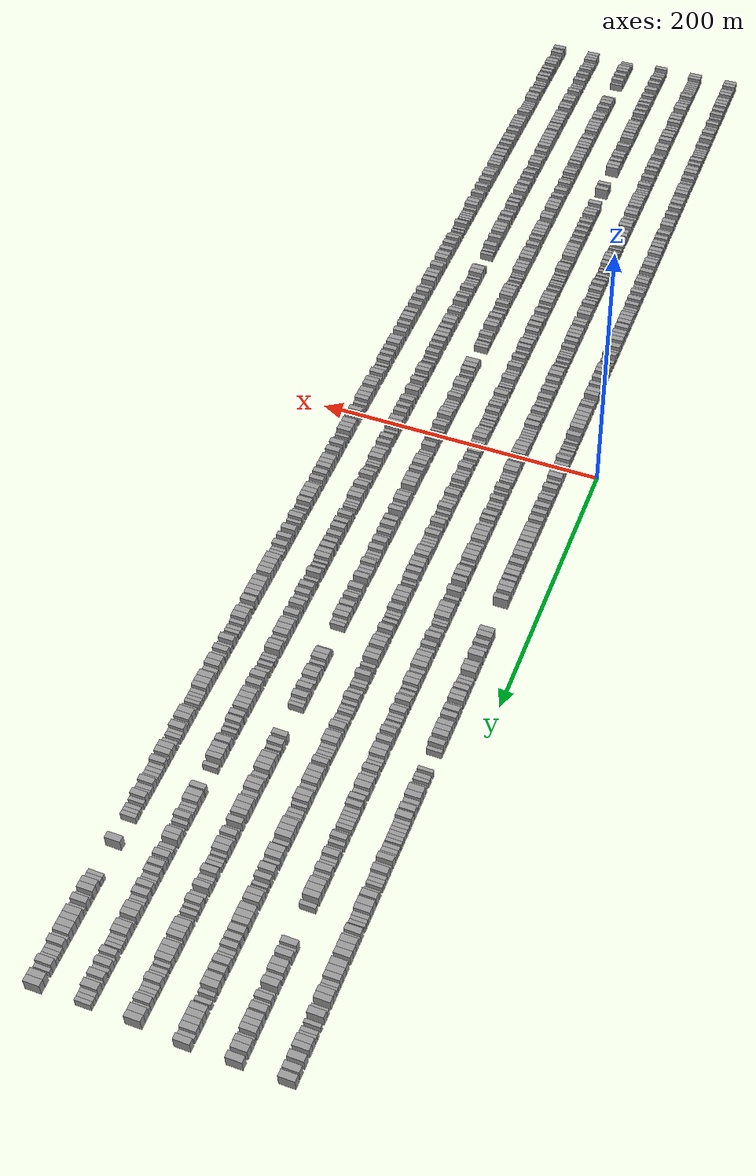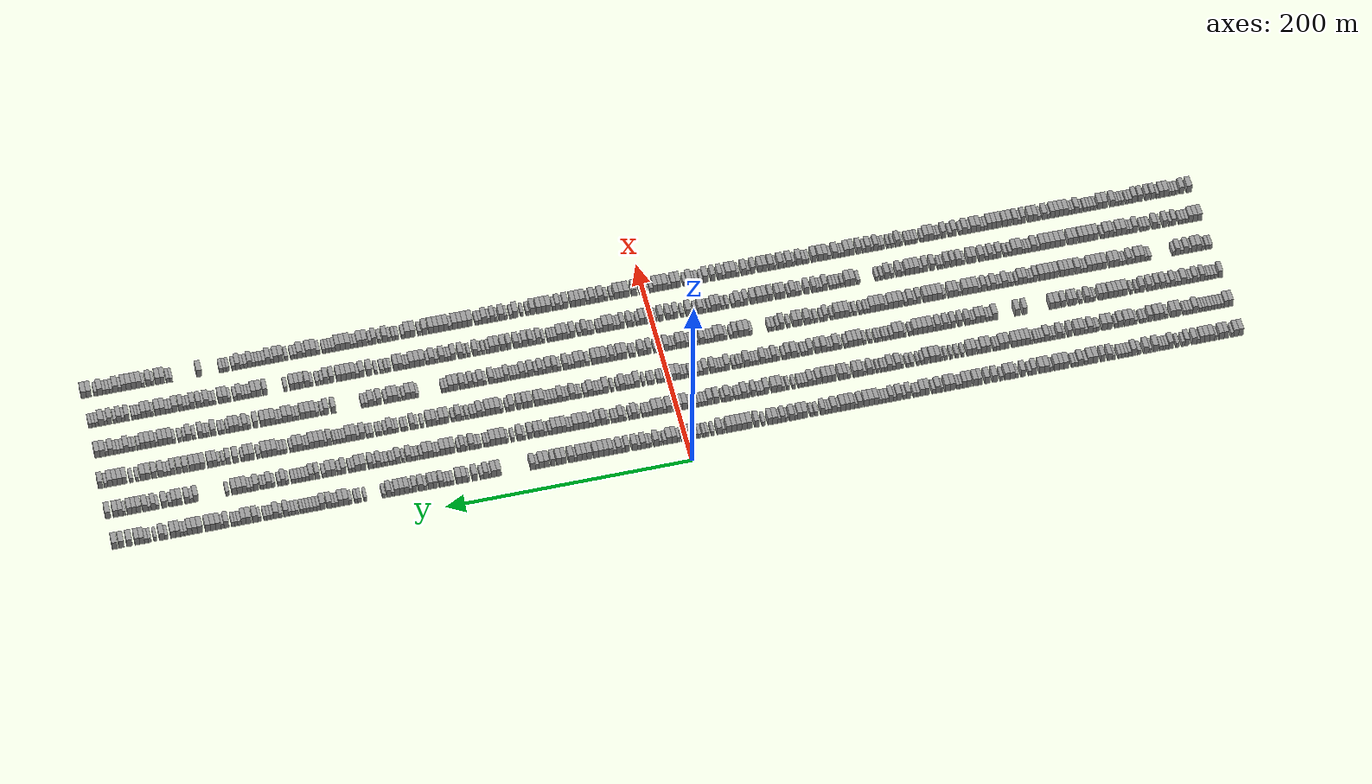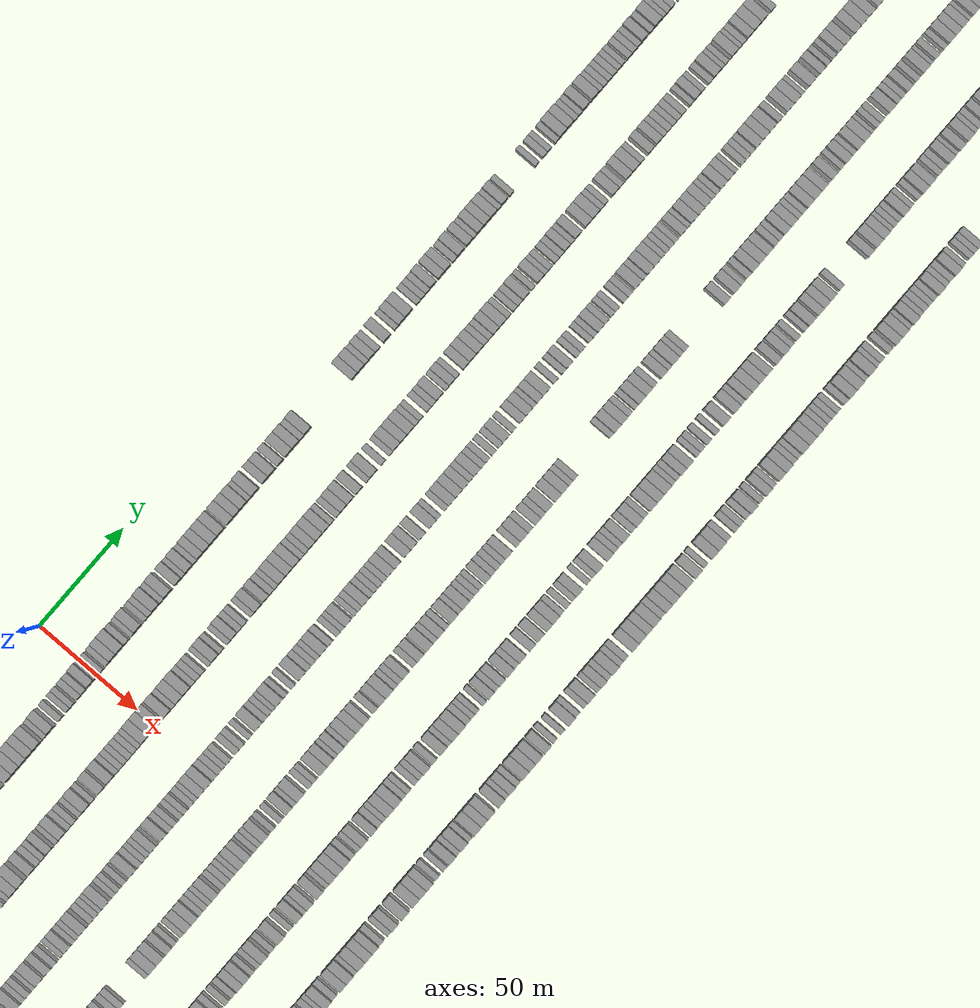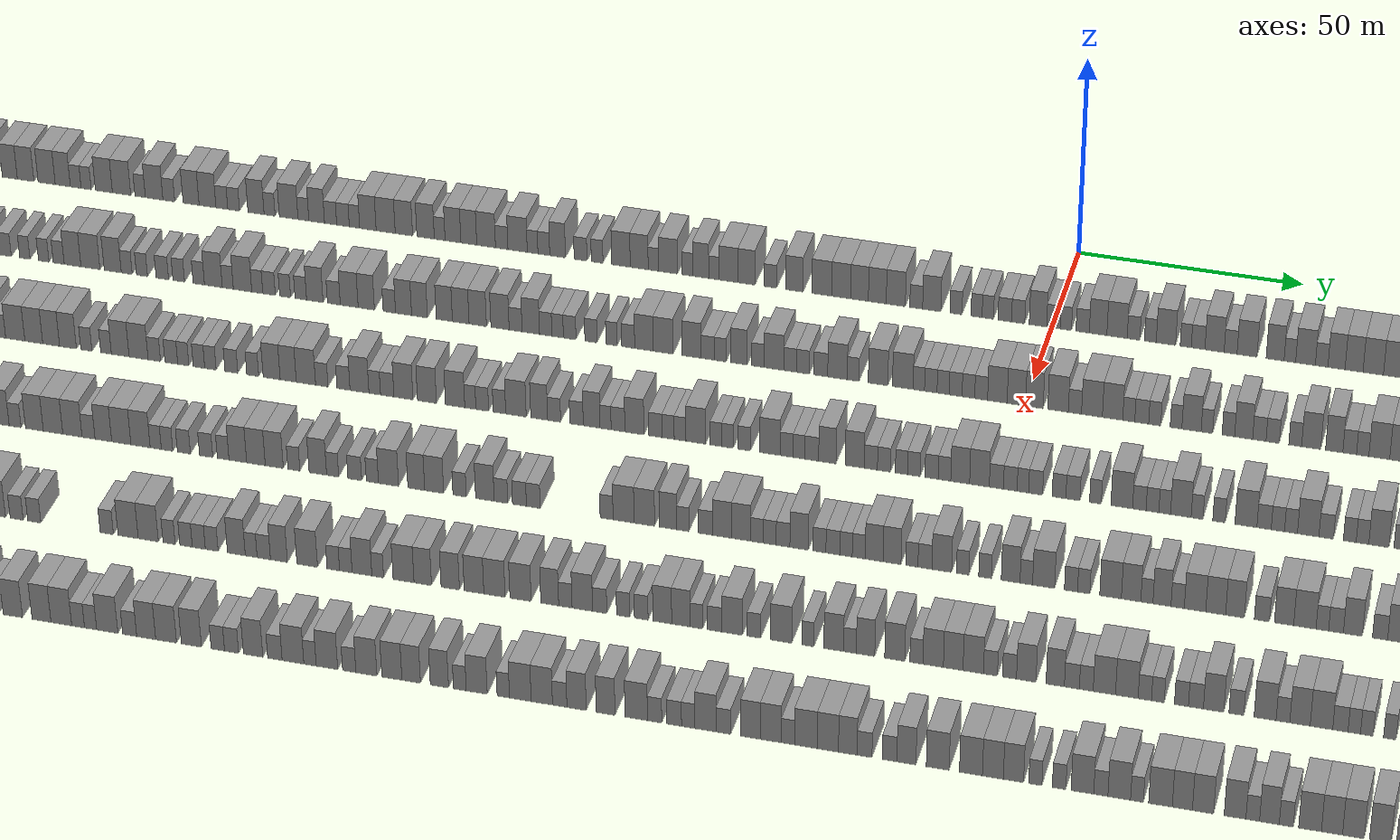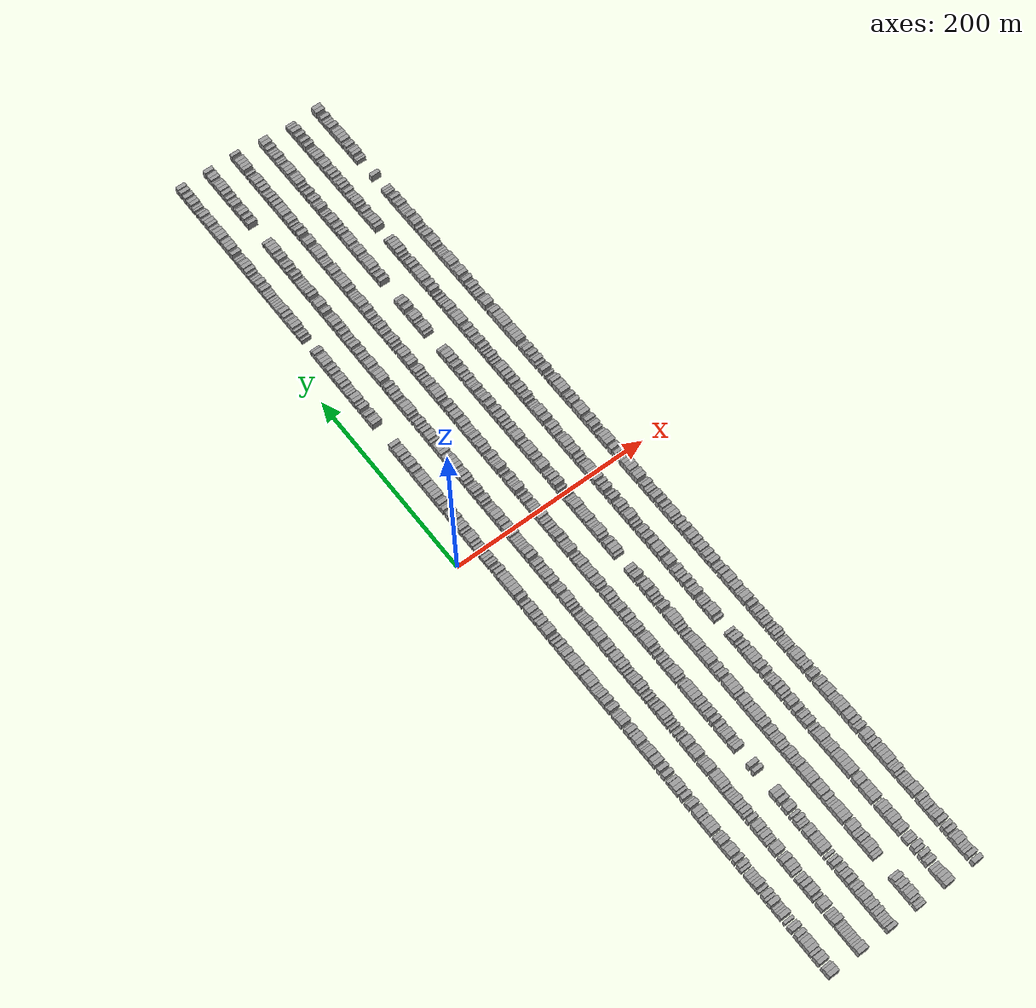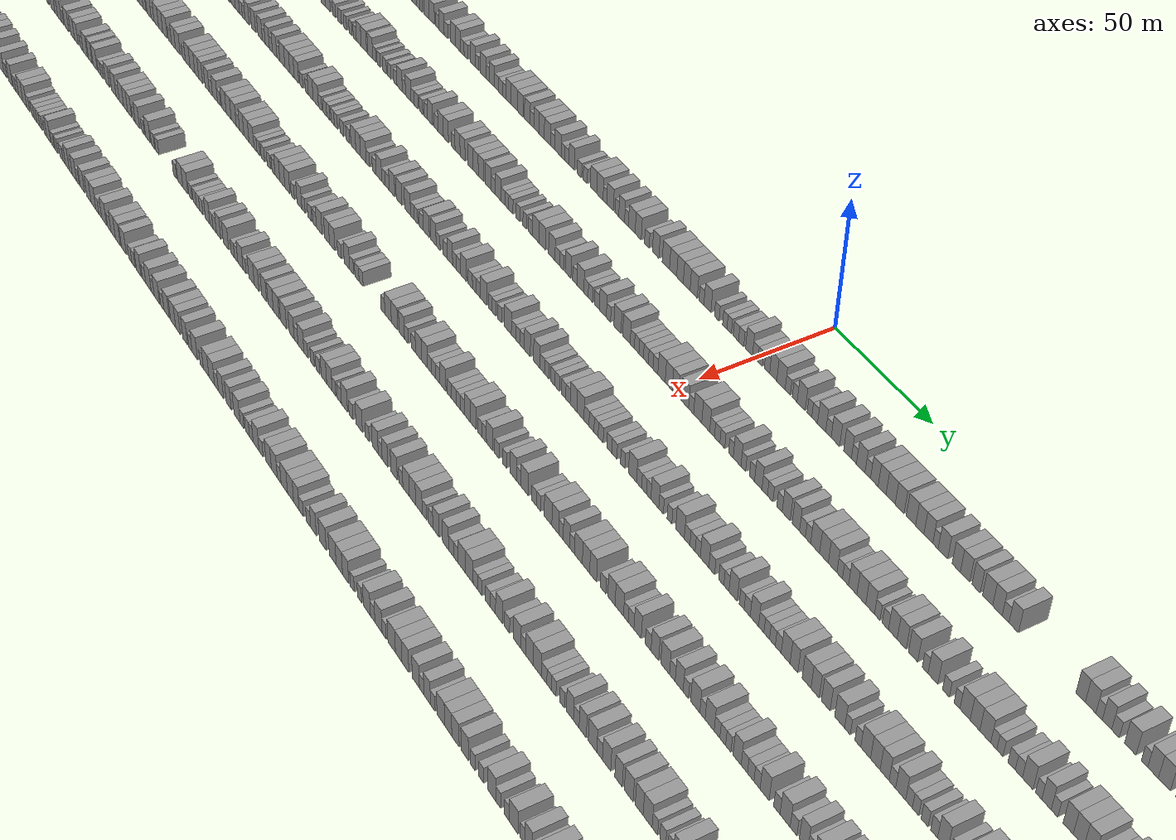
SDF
<sdf version="1.6">
 <world name="default">
  <scene>
   <sky><clouds><speed>12</speed></clouds></sky>
   <ambient>0.4 0.4 0.4 1</ambient>
   <background>0.7 0.7 0.7 1</background>
   <shadows>1</shadows>
  </scene>
  <gravity>0 0 -9.8066</gravity>
  <magnetic_field>6e-06 2.3e-05 -4.2e-05</magnetic_field>
  <physics default="0" name="default_physics" type="ode">
   <ode>
    <solver>
     <type>quick</type>
     <iters>10</iters>
     <sor>1.0</sor>
     <use_dynamic_moi_rescaling>0</use_dynamic_moi_rescaling>
    </solver>
    <constraints>
     <cfm>0</cfm>
     <erp>0.2</erp>
     <contact_max_correcting_vel>100</contact_max_correcting_vel>
     <contact_surface_layer>0.001</contact_surface_layer>
    </constraints>
   </ode>
   <max_step_size>0.004</max_step_size>
   <real_time_factor>1</real_time_factor>
   <real_time_update_rate>250</real_time_update_rate>
  </physics>
  <light name="sun" type="directional">
   <pose>0 0 10 0 0 0</pose>
   <diffuse>0.8 0.8 0.8 1</diffuse>
   <specular>0.2 0.2 0.2 1</specular>
   <attenuation>
    <range>1000</range>
    <constant>0.9</constant>
    <linear>0.01</linear>
    <quadratic>0.001</quadratic>
   </attenuation>
   <direction>-0.5 0.1 -0.9</direction>
  </light>
  <model name="building_1">
   <static>1</static>
   <pose>25.0000 -457.9565 0 0.000000 0.000000 0.000000</pose>
   <link name="link">
    <pose>0 0 4.50 0 0 0</pose>
    <collision name="collision"><geometry><box><size>10.0000 4.0869 9.0000</size></box></geometry></collision>
    <visual name="visual">
     <cast_shadows>0</cast_shadows>
     <geometry><box><size>10.0000 4.0869 9.0000</size></box></geometry>
     <material>
      <script>
       <uri>model://grey_wall/materials/scripts</uri>
       <uri>model://grey_wall/materials/textures</uri>
       <name>vrc/grey_wall</name>
      </script>
     </material>
    </visual>
   </link>
  </model>
  <model name="building_2">
   <static>1</static>
   <pose>25.0000 -453.9187 0 0.000000 0.000000 0.000000</pose>
   <link name="link">
    <pose>0 0 4.50 0 0 0</pose>
    <collision name="collision"><geometry><box><size>10.0000 3.9887 9.0000</size></box></geometry></collision>
    <visual name="visual">
     <cast_shadows>0</cast_shadows>
     <geometry><box><size>10.0000 3.9887 9.0000</size></box></geometry>
     <material>
      <script>
       <uri>model://grey_wall/materials/scripts</uri>
       <uri>model://grey_wall/materials/textures</uri>
       <name>vrc/grey_wall</name>
      </script>
     </material>
    </visual>
   </link>
  </model>
  <model name="building_3">
   <static>1</static>
   <pose>25.0000 -450.7222 0 0.000000 0.000000 0.000000</pose>
   <link name="link">
    <pose>0 0 3.00 0 0 0</pose>
    <collision name="collision"><geometry><box><size>10.0000 2.4043 6.0000</size></box></geometry></collision>
    <visual name="visual">
     <cast_shadows>0</cast_shadows>
     <geometry><box><size>10.0000 2.4043 6.0000</size></box></geometry>
     <material>
      <script>
       <uri>model://grey_wall/materials/scripts</uri>
       <uri>model://grey_wall/materials/textures</uri>
       <name>vrc/grey_wall</name>
      </script>
     </material>
    </visual>
   </link>
  </model>
  <model name="building_4">
   <static>1</static>
   <pose>25.0000 -445.6265 0 0.000000 0.000000 0.000000</pose>
   <link name="link">
    <pose>0 0 4.50 0 0 0</pose>
    <collision name="collision"><geometry><box><size>10.0000 3.7871 9.0000</size></box></geometry></collision>
    <visual name="visual">
     <cast_shadows>0</cast_shadows>
     <geometry><box><size>10.0000 3.7871 9.0000</size></box></geometry>
     <material>
      <script>
       <uri>model://grey_wall/materials/scripts</uri>
       <uri>model://grey_wall/materials/textures</uri>
       <name>vrc/grey_wall</name>
      </script>
     </material>
    </visual>
   </link>
  </model>
  <model name="building_5">
   <static>1</static>
   <pose>25.0000 -441.6758 0 0.000000 0.000000 0.000000</pose>
   <link name="link">
    <pose>0 0 4.50 0 0 0</pose>
    <collision name="collision"><geometry><box><size>10.0000 4.1142 9.0000</size></box></geometry></collision>
    <visual name="visual">
     <cast_shadows>0</cast_shadows>
     <geometry><box><size>10.0000 4.1142 9.0000</size></box></geometry>
     <material>
      <script>
       <uri>model://grey_wall/materials/scripts</uri>
       <uri>model://grey_wall/materials/textures</uri>
       <name>vrc/grey_wall</name>
      </script>
     </material>
    </visual>
   </link>
  </model>
  <model name="building_6">
   <static>1</static>
   <pose>25.0000 -437.1533 0 0.000000 0.000000 0.000000</pose>
   <link name="link">
    <pose>0 0 3.00 0 0 0</pose>
    <collision name="collision"><geometry><box><size>10.0000 2.9308 6.0000</size></box></geometry></collision>
    <visual name="visual">
     <cast_shadows>0</cast_shadows>
     <geometry><box><size>10.0000 2.9308 6.0000</size></box></geometry>
     <material>
      <script>
       <uri>model://grey_wall/materials/scripts</uri>
       <uri>model://grey_wall/materials/textures</uri>
       <name>vrc/grey_wall</name>
      </script>
     </material>
    </visual>
   </link>
  </model>
  <model name="building_7">
   <static>1</static>
   <pose>25.0000 -433.6449 0 0.000000 0.000000 0.000000</pose>
   <link name="link">
    <pose>0 0 4.50 0 0 0</pose>
    <collision name="collision"><geometry><box><size>10.0000 4.0860 9.0000</size></box></geometry></collision>
    <visual name="visual">
     <cast_shadows>0</cast_shadows>
     <geometry><box><size>10.0000 4.0860 9.0000</size></box></geometry>
     <material>
      <script>
       <uri>model://grey_wall/materials/scripts</uri>
       <uri>model://grey_wall/materials/textures</uri>
       <name>vrc/grey_wall</name>
      </script>
     </material>
    </visual>
   </link>
  </model>
  <model name="building_8">
   <static>1</static>
   <pose>25.0000 -429.4657 0 0.000000 0.000000 0.000000</pose>
   <link name="link">
    <pose>0 0 4.50 0 0 0</pose>
    <collision name="collision"><geometry><box><size>10.0000 4.2725 9.0000</size></box></geometry></collision>
    <visual name="visual">
     <cast_shadows>0</cast_shadows>
     <geometry><box><size>10.0000 4.2725 9.0000</size></box></geometry>
     <material>
      <script>
       <uri>model://grey_wall/materials/scripts</uri>
       <uri>model://grey_wall/materials/textures</uri>
       <name>vrc/grey_wall</name>
      </script>
     </material>
    </visual>
   </link>
  </model>
  <model name="building_9">
   <static>1</static>
   <pose>25.0000 -425.4560 0 0.000000 0.000000 0.000000</pose>
   <link name="link">
    <pose>0 0 4.50 0 0 0</pose>
    <collision name="collision"><geometry><box><size>10.0000 3.7469 9.0000</size></box></geometry></collision>
    <visual name="visual">
     <cast_shadows>0</cast_shadows>
     <geometry><box><size>10.0000 3.7469 9.0000</size></box></geometry>
     <material>
      <script>
       <uri>model://grey_wall/materials/scripts</uri>
       <uri>model://grey_wall/materials/textures</uri>
       <name>vrc/grey_wall</name>
      </script>
     </material>
    </visual>
   </link>
  </model>
  <model name="building_10">
   <static>1</static>
   <pose>25.0000 -422.3376 0 0.000000 0.000000 0.000000</pose>
   <link name="link">
    <pose>0 0 3.00 0 0 0</pose>
    <collision name="collision"><geometry><box><size>10.0000 2.4900 6.0000</size></box></geometry></collision>
    <visual name="visual">
     <cast_shadows>0</cast_shadows>
     <geometry><box><size>10.0000 2.4900 6.0000</size></box></geometry>
     <material>
      <script>
       <uri>model://grey_wall/materials/scripts</uri>
       <uri>model://grey_wall/materials/textures</uri>
       <name>vrc/grey_wall</name>
      </script>
     </material>
    </visual>
   </link>
  </model>
  <model name="building_11">
   <static>1</static>
   <pose>25.0000 -419.0158 0 0.000000 0.000000 0.000000</pose>
   <link name="link">
    <pose>0 0 4.50 0 0 0</pose>
    <collision name="collision"><geometry><box><size>10.0000 4.1535 9.0000</size></box></geometry></collision>
    <visual name="visual">
     <cast_shadows>0</cast_shadows>
     <geometry><box><size>10.0000 4.1535 9.0000</size></box></geometry>
     <material>
      <script>
       <uri>model://grey_wall/materials/scripts</uri>
       <uri>model://grey_wall/materials/textures</uri>
       <name>vrc/grey_wall</name>
      </script>
     </material>
    </visual>
   </link>
  </model>
  <model name="building_12">
   <static>1</static>
   <pose>25.0000 -413.0321 0 0.000000 0.000000 0.000000</pose>
   <link name="link">
    <pose>0 0 4.50 0 0 0</pose>
    <collision name="collision"><geometry><box><size>10.0000 3.8138 9.0000</size></box></geometry></collision>
    <visual name="visual">
     <cast_shadows>0</cast_shadows>
     <geometry><box><size>10.0000 3.8138 9.0000</size></box></geometry>
     <material>
      <script>
       <uri>model://grey_wall/materials/scripts</uri>
       <uri>model://grey_wall/materials/textures</uri>
       <name>vrc/grey_wall</name>
      </script>
     </material>
    </visual>
   </link>
  </model>
  <model name="building_13">
   <static>1</static>
   <pose>25.0000 -409.7524 0 0.000000 0.000000 0.000000</pose>
   <link name="link">
    <pose>0 0 3.00 0 0 0</pose>
    <collision name="collision"><geometry><box><size>10.0000 2.7457 6.0000</size></box></geometry></collision>
    <visual name="visual">
     <cast_shadows>0</cast_shadows>
     <geometry><box><size>10.0000 2.7457 6.0000</size></box></geometry>
     <material>
      <script>
       <uri>model://grey_wall/materials/scripts</uri>
       <uri>model://grey_wall/materials/textures</uri>
       <name>vrc/grey_wall</name>
      </script>
     </material>
    </visual>
   </link>
  </model>
  <model name="building_14">
   <static>1</static>
   <pose>25.0000 -404.9917 0 0.000000 0.000000 0.000000</pose>
   <link name="link">
    <pose>0 0 3.00 0 0 0</pose>
    <collision name="collision"><geometry><box><size>10.0000 2.7756 6.0000</size></box></geometry></collision>
    <visual name="visual">
     <cast_shadows>0</cast_shadows>
     <geometry><box><size>10.0000 2.7756 6.0000</size></box></geometry>
     <material>
      <script>
       <uri>model://grey_wall/materials/scripts</uri>
       <uri>model://grey_wall/materials/textures</uri>
       <name>vrc/grey_wall</name>
      </script>
     </material>
    </visual>
   </link>
  </model>
  <model name="building_15">
   <static>1</static>
   <pose>25.0000 -399.5481 0 0.000000 0.000000 0.000000</pose>
   <link name="link">
    <pose>0 0 4.50 0 0 0</pose>
    <collision name="collision"><geometry><box><size>10.0000 4.1117 9.0000</size></box></geometry></collision>
    <visual name="visual">
     <cast_shadows>0</cast_shadows>
     <geometry><box><size>10.0000 4.1117 9.0000</size></box></geometry>
     <material>
      <script>
       <uri>model://grey_wall/materials/scripts</uri>
       <uri>model://grey_wall/materials/textures</uri>
       <name>vrc/grey_wall</name>
      </script>
     </material>
    </visual>
   </link>
  </model>
  <model name="building_16">
   <static>1</static>
   <pose>25.0000 -396.2033 0 0.000000 0.000000 0.000000</pose>
   <link name="link">
    <pose>0 0 3.00 0 0 0</pose>
    <collision name="collision"><geometry><box><size>10.0000 2.5780 6.0000</size></box></geometry></collision>
    <visual name="visual">
     <cast_shadows>0</cast_shadows>
     <geometry><box><size>10.0000 2.5780 6.0000</size></box></geometry>
     <material>
      <script>
       <uri>model://grey_wall/materials/scripts</uri>
       <uri>model://grey_wall/materials/textures</uri>
       <name>vrc/grey_wall</name>
      </script>
     </material>
    </visual>
   </link>
  </model>
  <model name="building_17">
   <static>1</static>
   <pose>25.0000 -393.7112 0 0.000000 0.000000 0.000000</pose>
   <link name="link">
    <pose>0 0 3.00 0 0 0</pose>
    <collision name="collision"><geometry><box><size>10.0000 2.4061 6.0000</size></box></geometry></collision>
    <visual name="visual">
     <cast_shadows>0</cast_shadows>
     <geometry><box><size>10.0000 2.4061 6.0000</size></box></geometry>
     <material>
      <script>
       <uri>model://grey_wall/materials/scripts</uri>
       <uri>model://grey_wall/materials/textures</uri>
       <name>vrc/grey_wall</name>
      </script>
     </material>
    </visual>
   </link>
  </model>
  <model name="building_18">
   <static>1</static>
   <pose>25.0000 -391.2906 0 0.000000 0.000000 0.000000</pose>
   <link name="link">
    <pose>0 0 3.00 0 0 0</pose>
    <collision name="collision"><geometry><box><size>10.0000 2.4353 6.0000</size></box></geometry></collision>
    <visual name="visual">
     <cast_shadows>0</cast_shadows>
     <geometry><box><size>10.0000 2.4353 6.0000</size></box></geometry>
     <material>
      <script>
       <uri>model://grey_wall/materials/scripts</uri>
       <uri>model://grey_wall/materials/textures</uri>
       <name>vrc/grey_wall</name>
      </script>
     </material>
    </visual>
   </link>
  </model>
  <model name="building_19">
   <static>1</static>
   <pose>25.0000 -386.8336 0 0.000000 0.000000 0.000000</pose>
   <link name="link">
    <pose>0 0 4.50 0 0 0</pose>
    <collision name="collision"><geometry><box><size>10.0000 4.4787 9.0000</size></box></geometry></collision>
    <visual name="visual">
     <cast_shadows>0</cast_shadows>
     <geometry><box><size>10.0000 4.4787 9.0000</size></box></geometry>
     <material>
      <script>
       <uri>model://grey_wall/materials/scripts</uri>
       <uri>model://grey_wall/materials/textures</uri>
       <name>vrc/grey_wall</name>
      </script>
     </material>
    </visual>
   </link>
  </model>
  <model name="building_20">
   <static>1</static>
   <pose>25.0000 -382.2554 0 0.000000 0.000000 0.000000</pose>
   <link name="link">
    <pose>0 0 3.00 0 0 0</pose>
    <collision name="collision"><geometry><box><size>10.0000 2.6776 6.0000</size></box></geometry></collision>
    <visual name="visual">
     <cast_shadows>0</cast_shadows>
     <geometry><box><size>10.0000 2.6776 6.0000</size></box></geometry>
     <material>
      <script>
       <uri>model://grey_wall/materials/scripts</uri>
       <uri>model://grey_wall/materials/textures</uri>
       <name>vrc/grey_wall</name>
      </script>
     </material>
    </visual>
   </link>
  </model>
  <model name="building_21">
   <static>1</static>
   <pose>25.0000 -378.7441 0 0.000000 0.000000 0.000000</pose>
   <link name="link">
    <pose>0 0 4.50 0 0 0</pose>
    <collision name="collision"><geometry><box><size>10.0000 4.3449 9.0000</size></box></geometry></collision>
    <visual name="visual">
     <cast_shadows>0</cast_shadows>
     <geometry><box><size>10.0000 4.3449 9.0000</size></box></geometry>
     <material>
      <script>
       <uri>model://grey_wall/materials/scripts</uri>
       <uri>model://grey_wall/materials/textures</uri>
       <name>vrc/grey_wall</name>
      </script>
     </material>
    </visual>
   </link>
  </model>
  <model name="building_22">
   <static>1</static>
   <pose>25.0000 -373.1597 0 0.000000 0.000000 0.000000</pose>
   <link name="link">
    <pose>0 0 3.00 0 0 0</pose>
    <collision name="collision"><geometry><box><size>10.0000 2.8239 6.0000</size></box></geometry></collision>
    <visual name="visual">
     <cast_shadows>0</cast_shadows>
     <geometry><box><size>10.0000 2.8239 6.0000</size></box></geometry>
     <material>
      <script>
       <uri>model://grey_wall/materials/scripts</uri>
       <uri>model://grey_wall/materials/textures</uri>
       <name>vrc/grey_wall</name>
      </script>
     </material>
    </visual>
   </link>
  </model>
  <model name="building_23">
   <static>1</static>
   <pose>25.0000 -368.6854 0 0.000000 0.000000 0.000000</pose>
   <link name="link">
    <pose>0 0 4.50 0 0 0</pose>
    <collision name="collision"><geometry><box><size>10.0000 4.1246 9.0000</size></box></geometry></collision>
    <visual name="visual">
     <cast_shadows>0</cast_shadows>
     <geometry><box><size>10.0000 4.1246 9.0000</size></box></geometry>
     <material>
      <script>
       <uri>model://grey_wall/materials/scripts</uri>
       <uri>model://grey_wall/materials/textures</uri>
       <name>vrc/grey_wall</name>
      </script>
     </material>
    </visual>
   </link>
  </model>
  <model name="building_24">
   <static>1</static>
   <pose>25.0000 -365.1820 0 0.000000 0.000000 0.000000</pose>
   <link name="link">
    <pose>0 0 3.00 0 0 0</pose>
    <collision name="collision"><geometry><box><size>10.0000 2.8823 6.0000</size></box></geometry></collision>
    <visual name="visual">
     <cast_shadows>0</cast_shadows>
     <geometry><box><size>10.0000 2.8823 6.0000</size></box></geometry>
     <material>
      <script>
       <uri>model://grey_wall/materials/scripts</uri>
       <uri>model://grey_wall/materials/textures</uri>
       <name>vrc/grey_wall</name>
      </script>
     </material>
    </visual>
   </link>
  </model>
  <model name="building_25">
   <static>1</static>
   <pose>25.0000 -362.4536 0 0.000000 0.000000 0.000000</pose>
   <link name="link">
    <pose>0 0 3.00 0 0 0</pose>
    <collision name="collision"><geometry><box><size>10.0000 2.5746 6.0000</size></box></geometry></collision>
    <visual name="visual">
     <cast_shadows>0</cast_shadows>
     <geometry><box><size>10.0000 2.5746 6.0000</size></box></geometry>
     <material>
      <script>
       <uri>model://grey_wall/materials/scripts</uri>
       <uri>model://grey_wall/materials/textures</uri>
       <name>vrc/grey_wall</name>
      </script>
     </material>
    </visual>
   </link>
  </model>
  <model name="building_26">
   <static>1</static>
   <pose>25.0000 -359.7022 0 0.000000 0.000000 0.000000</pose>
   <link name="link">
    <pose>0 0 3.00 0 0 0</pose>
    <collision name="collision"><geometry><box><size>10.0000 2.9281 6.0000</size></box></geometry></collision>
    <visual name="visual">
     <cast_shadows>0</cast_shadows>
     <geometry><box><size>10.0000 2.9281 6.0000</size></box></geometry>
     <material>
      <script>
       <uri>model://grey_wall/materials/scripts</uri>
       <uri>model://grey_wall/materials/textures</uri>
       <name>vrc/grey_wall</name>
      </script>
     </material>
    </visual>
   </link>
  </model>
  <model name="building_27">
   <static>1</static>
   <pose>25.0000 -356.7800 0 0.000000 0.000000 0.000000</pose>
   <link name="link">
    <pose>0 0 3.00 0 0 0</pose>
    <collision name="collision"><geometry><box><size>10.0000 2.9164 6.0000</size></box></geometry></collision>
    <visual name="visual">
     <cast_shadows>0</cast_shadows>
     <geometry><box><size>10.0000 2.9164 6.0000</size></box></geometry>
     <material>
      <script>
       <uri>model://grey_wall/materials/scripts</uri>
       <uri>model://grey_wall/materials/textures</uri>
       <name>vrc/grey_wall</name>
      </script>
     </material>
    </visual>
   </link>
  </model>
  <model name="building_28">
   <static>1</static>
   <pose>25.0000 -351.9391 0 0.000000 0.000000 0.000000</pose>
   <link name="link">
    <pose>0 0 3.00 0 0 0</pose>
    <collision name="collision"><geometry><box><size>10.0000 2.7654 6.0000</size></box></geometry></collision>
    <visual name="visual">
     <cast_shadows>0</cast_shadows>
     <geometry><box><size>10.0000 2.7654 6.0000</size></box></geometry>
     <material>
      <script>
       <uri>model://grey_wall/materials/scripts</uri>
       <uri>model://grey_wall/materials/textures</uri>
       <name>vrc/grey_wall</name>
      </script>
     </material>
    </visual>
   </link>
  </model>
  <model name="building_29">
   <static>1</static>
   <pose>25.0000 -348.5849 0 0.000000 0.000000 0.000000</pose>
   <link name="link">
    <pose>0 0 4.50 0 0 0</pose>
    <collision name="collision"><geometry><box><size>10.0000 3.9430 9.0000</size></box></geometry></collision>
    <visual name="visual">
     <cast_shadows>0</cast_shadows>
     <geometry><box><size>10.0000 3.9430 9.0000</size></box></geometry>
     <material>
      <script>
       <uri>model://grey_wall/materials/scripts</uri>
       <uri>model://grey_wall/materials/textures</uri>
       <name>vrc/grey_wall</name>
      </script>
     </material>
    </visual>
   </link>
  </model>
  <model name="building_30">
   <static>1</static>
   <pose>25.0000 -342.7692 0 0.000000 0.000000 0.000000</pose>
   <link name="link">
    <pose>0 0 4.50 0 0 0</pose>
    <collision name="collision"><geometry><box><size>10.0000 3.6885 9.0000</size></box></geometry></collision>
    <visual name="visual">
     <cast_shadows>0</cast_shadows>
     <geometry><box><size>10.0000 3.6885 9.0000</size></box></geometry>
     <material>
      <script>
       <uri>model://grey_wall/materials/scripts</uri>
       <uri>model://grey_wall/materials/textures</uri>
       <name>vrc/grey_wall</name>
      </script>
     </material>
    </visual>
   </link>
  </model>
  <model name="building_31">
   <static>1</static>
   <pose>25.0000 -336.7538 0 0.000000 0.000000 0.000000</pose>
   <link name="link">
    <pose>0 0 4.50 0 0 0</pose>
    <collision name="collision"><geometry><box><size>10.0000 4.3421 9.0000</size></box></geometry></collision>
    <visual name="visual">
     <cast_shadows>0</cast_shadows>
     <geometry><box><size>10.0000 4.3421 9.0000</size></box></geometry>
     <material>
      <script>
       <uri>model://grey_wall/materials/scripts</uri>
       <uri>model://grey_wall/materials/textures</uri>
       <name>vrc/grey_wall</name>
      </script>
     </material>
    </visual>
   </link>
  </model>
  <model name="building_32">
   <static>1</static>
   <pose>25.0000 -332.3625 0 0.000000 0.000000 0.000000</pose>
   <link name="link">
    <pose>0 0 4.50 0 0 0</pose>
    <collision name="collision"><geometry><box><size>10.0000 4.4404 9.0000</size></box></geometry></collision>
    <visual name="visual">
     <cast_shadows>0</cast_shadows>
     <geometry><box><size>10.0000 4.4404 9.0000</size></box></geometry>
     <material>
      <script>
       <uri>model://grey_wall/materials/scripts</uri>
       <uri>model://grey_wall/materials/textures</uri>
       <name>vrc/grey_wall</name>
      </script>
     </material>
    </visual>
   </link>
  </model>
  <model name="building_33">
   <static>1</static>
   <pose>25.0000 -328.7803 0 0.000000 0.000000 0.000000</pose>
   <link name="link">
    <pose>0 0 3.00 0 0 0</pose>
    <collision name="collision"><geometry><box><size>10.0000 2.7240 6.0000</size></box></geometry></collision>
    <visual name="visual">
     <cast_shadows>0</cast_shadows>
     <geometry><box><size>10.0000 2.7240 6.0000</size></box></geometry>
     <material>
      <script>
       <uri>model://grey_wall/materials/scripts</uri>
       <uri>model://grey_wall/materials/textures</uri>
       <name>vrc/grey_wall</name>
      </script>
     </material>
    </visual>
   </link>
  </model>
  <model name="building_34">
   <static>1</static>
   <pose>25.0000 -324.2263 0 0.000000 0.000000 0.000000</pose>
   <link name="link">
    <pose>0 0 4.50 0 0 0</pose>
    <collision name="collision"><geometry><box><size>10.0000 4.3841 9.0000</size></box></geometry></collision>
    <visual name="visual">
     <cast_shadows>0</cast_shadows>
     <geometry><box><size>10.0000 4.3841 9.0000</size></box></geometry>
     <material>
      <script>
       <uri>model://grey_wall/materials/scripts</uri>
       <uri>model://grey_wall/materials/textures</uri>
       <name>vrc/grey_wall</name>
      </script>
     </material>
    </visual>
   </link>
  </model>
  <model name="building_35">
   <static>1</static>
   <pose>25.0000 -320.8160 0 0.000000 0.000000 0.000000</pose>
   <link name="link">
    <pose>0 0 3.00 0 0 0</pose>
    <collision name="collision"><geometry><box><size>10.0000 2.4365 6.0000</size></box></geometry></collision>
    <visual name="visual">
     <cast_shadows>0</cast_shadows>
     <geometry><box><size>10.0000 2.4365 6.0000</size></box></geometry>
     <material>
      <script>
       <uri>model://grey_wall/materials/scripts</uri>
       <uri>model://grey_wall/materials/textures</uri>
       <name>vrc/grey_wall</name>
      </script>
     </material>
    </visual>
   </link>
  </model>
  <model name="building_36">
   <static>1</static>
   <pose>25.0000 -318.1327 0 0.000000 0.000000 0.000000</pose>
   <link name="link">
    <pose>0 0 3.00 0 0 0</pose>
    <collision name="collision"><geometry><box><size>10.0000 2.9300 6.0000</size></box></geometry></collision>
    <visual name="visual">
     <cast_shadows>0</cast_shadows>
     <geometry><box><size>10.0000 2.9300 6.0000</size></box></geometry>
     <material>
      <script>
       <uri>model://grey_wall/materials/scripts</uri>
       <uri>model://grey_wall/materials/textures</uri>
       <name>vrc/grey_wall</name>
      </script>
     </material>
    </visual>
   </link>
  </model>
  <model name="building_37">
   <static>1</static>
   <pose>25.0000 -312.4532 0 0.000000 0.000000 0.000000</pose>
   <link name="link">
    <pose>0 0 4.50 0 0 0</pose>
    <collision name="collision"><geometry><box><size>10.0000 4.4289 9.0000</size></box></geometry></collision>
    <visual name="visual">
     <cast_shadows>0</cast_shadows>
     <geometry><box><size>10.0000 4.4289 9.0000</size></box></geometry>
     <material>
      <script>
       <uri>model://grey_wall/materials/scripts</uri>
       <uri>model://grey_wall/materials/textures</uri>
       <name>vrc/grey_wall</name>
      </script>
     </material>
    </visual>
   </link>
  </model>
  <model name="building_38">
   <static>1</static>
   <pose>25.0000 -308.4230 0 0.000000 0.000000 0.000000</pose>
   <link name="link">
    <pose>0 0 4.50 0 0 0</pose>
    <collision name="collision"><geometry><box><size>10.0000 3.6315 9.0000</size></box></geometry></collision>
    <visual name="visual">
     <cast_shadows>0</cast_shadows>
     <geometry><box><size>10.0000 3.6315 9.0000</size></box></geometry>
     <material>
      <script>
       <uri>model://grey_wall/materials/scripts</uri>
       <uri>model://grey_wall/materials/textures</uri>
       <name>vrc/grey_wall</name>
      </script>
     </material>
    </visual>
   </link>
  </model>
  <model name="building_39">
   <static>1</static>
   <pose>25.0000 -304.4598 0 0.000000 0.000000 0.000000</pose>
   <link name="link">
    <pose>0 0 4.50 0 0 0</pose>
    <collision name="collision"><geometry><box><size>10.0000 4.2948 9.0000</size></box></geometry></collision>
    <visual name="visual">
     <cast_shadows>0</cast_shadows>
     <geometry><box><size>10.0000 4.2948 9.0000</size></box></geometry>
     <material>
      <script>
       <uri>model://grey_wall/materials/scripts</uri>
       <uri>model://grey_wall/materials/textures</uri>
       <name>vrc/grey_wall</name>
      </script>
     </material>
    </visual>
   </link>
  </model>
  <model name="building_40">
   <static>1</static>
   <pose>25.0000 -299.8534 0 0.000000 0.000000 0.000000</pose>
   <link name="link">
    <pose>0 0 3.00 0 0 0</pose>
    <collision name="collision"><geometry><box><size>10.0000 2.9182 6.0000</size></box></geometry></collision>
    <visual name="visual">
     <cast_shadows>0</cast_shadows>
     <geometry><box><size>10.0000 2.9182 6.0000</size></box></geometry>
     <material>
      <script>
       <uri>model://grey_wall/materials/scripts</uri>
       <uri>model://grey_wall/materials/textures</uri>
       <name>vrc/grey_wall</name>
      </script>
     </material>
    </visual>
   </link>
  </model>
  <model name="building_41">
   <static>1</static>
   <pose>25.0000 -296.2760 0 0.000000 0.000000 0.000000</pose>
   <link name="link">
    <pose>0 0 4.50 0 0 0</pose>
    <collision name="collision"><geometry><box><size>10.0000 4.2366 9.0000</size></box></geometry></collision>
    <visual name="visual">
     <cast_shadows>0</cast_shadows>
     <geometry><box><size>10.0000 4.2366 9.0000</size></box></geometry>
     <material>
      <script>
       <uri>model://grey_wall/materials/scripts</uri>
       <uri>model://grey_wall/materials/textures</uri>
       <name>vrc/grey_wall</name>
      </script>
     </material>
    </visual>
   </link>
  </model>
  <model name="building_42">
   <static>1</static>
   <pose>25.0000 -291.9646 0 0.000000 0.000000 0.000000</pose>
   <link name="link">
    <pose>0 0 4.50 0 0 0</pose>
    <collision name="collision"><geometry><box><size>10.0000 4.3861 9.0000</size></box></geometry></collision>
    <visual name="visual">
     <cast_shadows>0</cast_shadows>
     <geometry><box><size>10.0000 4.3861 9.0000</size></box></geometry>
     <material>
      <script>
       <uri>model://grey_wall/materials/scripts</uri>
       <uri>model://grey_wall/materials/textures</uri>
       <name>vrc/grey_wall</name>
      </script>
     </material>
    </visual>
   </link>
  </model>
  <model name="building_43">
   <static>1</static>
   <pose>25.0000 -285.6904 0 0.000000 0.000000 0.000000</pose>
   <link name="link">
    <pose>0 0 4.50 0 0 0</pose>
    <collision name="collision"><geometry><box><size>10.0000 4.1624 9.0000</size></box></geometry></collision>
    <visual name="visual">
     <cast_shadows>0</cast_shadows>
     <geometry><box><size>10.0000 4.1624 9.0000</size></box></geometry>
     <material>
      <script>
       <uri>model://grey_wall/materials/scripts</uri>
       <uri>model://grey_wall/materials/textures</uri>
       <name>vrc/grey_wall</name>
      </script>
     </material>
    </visual>
   </link>
  </model>
  <model name="building_44">
   <static>1</static>
   <pose>25.0000 -282.2029 0 0.000000 0.000000 0.000000</pose>
   <link name="link">
    <pose>0 0 3.00 0 0 0</pose>
    <collision name="collision"><geometry><box><size>10.0000 2.8124 6.0000</size></box></geometry></collision>
    <visual name="visual">
     <cast_shadows>0</cast_shadows>
     <geometry><box><size>10.0000 2.8124 6.0000</size></box></geometry>
     <material>
      <script>
       <uri>model://grey_wall/materials/scripts</uri>
       <uri>model://grey_wall/materials/textures</uri>
       <name>vrc/grey_wall</name>
      </script>
     </material>
    </visual>
   </link>
  </model>
  <model name="building_45">
   <static>1</static>
   <pose>25.0000 -276.7568 0 0.000000 0.000000 0.000000</pose>
   <link name="link">
    <pose>0 0 4.50 0 0 0</pose>
    <collision name="collision"><geometry><box><size>10.0000 4.0799 9.0000</size></box></geometry></collision>
    <visual name="visual">
     <cast_shadows>0</cast_shadows>
     <geometry><box><size>10.0000 4.0799 9.0000</size></box></geometry>
     <material>
      <script>
       <uri>model://grey_wall/materials/scripts</uri>
       <uri>model://grey_wall/materials/textures</uri>
       <name>vrc/grey_wall</name>
      </script>
     </material>
    </visual>
   </link>
  </model>
  <model name="building_46">
   <static>1</static>
   <pose>25.0000 -271.3334 0 0.000000 0.000000 0.000000</pose>
   <link name="link">
    <pose>0 0 3.00 0 0 0</pose>
    <collision name="collision"><geometry><box><size>10.0000 2.7668 6.0000</size></box></geometry></collision>
    <visual name="visual">
     <cast_shadows>0</cast_shadows>
     <geometry><box><size>10.0000 2.7668 6.0000</size></box></geometry>
     <material>
      <script>
       <uri>model://grey_wall/materials/scripts</uri>
       <uri>model://grey_wall/materials/textures</uri>
       <name>vrc/grey_wall</name>
      </script>
     </material>
    </visual>
   </link>
  </model>
  <model name="building_47">
   <static>1</static>
   <pose>25.0000 -267.7856 0 0.000000 0.000000 0.000000</pose>
   <link name="link">
    <pose>0 0 4.50 0 0 0</pose>
    <collision name="collision"><geometry><box><size>10.0000 4.3289 9.0000</size></box></geometry></collision>
    <visual name="visual">
     <cast_shadows>0</cast_shadows>
     <geometry><box><size>10.0000 4.3289 9.0000</size></box></geometry>
     <material>
      <script>
       <uri>model://grey_wall/materials/scripts</uri>
       <uri>model://grey_wall/materials/textures</uri>
       <name>vrc/grey_wall</name>
      </script>
     </material>
    </visual>
   </link>
  </model>
  <model name="building_48">
   <static>1</static>
   <pose>25.0000 -263.4462 0 0.000000 0.000000 0.000000</pose>
   <link name="link">
    <pose>0 0 4.50 0 0 0</pose>
    <collision name="collision"><geometry><box><size>10.0000 4.3500 9.0000</size></box></geometry></collision>
    <visual name="visual">
     <cast_shadows>0</cast_shadows>
     <geometry><box><size>10.0000 4.3500 9.0000</size></box></geometry>
     <material>
      <script>
       <uri>model://grey_wall/materials/scripts</uri>
       <uri>model://grey_wall/materials/textures</uri>
       <name>vrc/grey_wall</name>
      </script>
     </material>
    </visual>
   </link>
  </model>
  <model name="building_49">
   <static>1</static>
   <pose>25.0000 -258.8504 0 0.000000 0.000000 0.000000</pose>
   <link name="link">
    <pose>0 0 3.00 0 0 0</pose>
    <collision name="collision"><geometry><box><size>10.0000 2.8417 6.0000</size></box></geometry></collision>
    <visual name="visual">
     <cast_shadows>0</cast_shadows>
     <geometry><box><size>10.0000 2.8417 6.0000</size></box></geometry>
     <material>
      <script>
       <uri>model://grey_wall/materials/scripts</uri>
       <uri>model://grey_wall/materials/textures</uri>
       <name>vrc/grey_wall</name>
      </script>
     </material>
    </visual>
   </link>
  </model>
  <model name="building_50">
   <static>1</static>
   <pose>25.0000 -253.2241 0 0.000000 0.000000 0.000000</pose>
   <link name="link">
    <pose>0 0 4.50 0 0 0</pose>
    <collision name="collision"><geometry><box><size>10.0000 4.4109 9.0000</size></box></geometry></collision>
    <visual name="visual">
     <cast_shadows>0</cast_shadows>
     <geometry><box><size>10.0000 4.4109 9.0000</size></box></geometry>
     <material>
      <script>
       <uri>model://grey_wall/materials/scripts</uri>
       <uri>model://grey_wall/materials/textures</uri>
       <name>vrc/grey_wall</name>
      </script>
     </material>
    </visual>
   </link>
  </model>
  <model name="building_51">
   <static>1</static>
   <pose>25.0000 -246.9403 0 0.000000 0.000000 0.000000</pose>
   <link name="link">
    <pose>0 0 4.50 0 0 0</pose>
    <collision name="collision"><geometry><box><size>10.0000 4.1566 9.0000</size></box></geometry></collision>
    <visual name="visual">
     <cast_shadows>0</cast_shadows>
     <geometry><box><size>10.0000 4.1566 9.0000</size></box></geometry>
     <material>
      <script>
       <uri>model://grey_wall/materials/scripts</uri>
       <uri>model://grey_wall/materials/textures</uri>
       <name>vrc/grey_wall</name>
      </script>
     </material>
    </visual>
   </link>
  </model>
  <model name="building_52">
   <static>1</static>
   <pose>25.0000 -241.0428 0 0.000000 0.000000 0.000000</pose>
   <link name="link">
    <pose>0 0 4.50 0 0 0</pose>
    <collision name="collision"><geometry><box><size>10.0000 3.6384 9.0000</size></box></geometry></collision>
    <visual name="visual">
     <cast_shadows>0</cast_shadows>
     <geometry><box><size>10.0000 3.6384 9.0000</size></box></geometry>
     <material>
      <script>
       <uri>model://grey_wall/materials/scripts</uri>
       <uri>model://grey_wall/materials/textures</uri>
       <name>vrc/grey_wall</name>
      </script>
     </material>
    </visual>
   </link>
  </model>
  <model name="building_53">
   <static>1</static>
   <pose>25.0000 -237.2088 0 0.000000 0.000000 0.000000</pose>
   <link name="link">
    <pose>0 0 4.50 0 0 0</pose>
    <collision name="collision"><geometry><box><size>10.0000 4.0295 9.0000</size></box></geometry></collision>
    <visual name="visual">
     <cast_shadows>0</cast_shadows>
     <geometry><box><size>10.0000 4.0295 9.0000</size></box></geometry>
     <material>
      <script>
       <uri>model://grey_wall/materials/scripts</uri>
       <uri>model://grey_wall/materials/textures</uri>
       <name>vrc/grey_wall</name>
      </script>
     </material>
    </visual>
   </link>
  </model>
  <model name="building_54">
   <static>1</static>
   <pose>25.0000 -232.1195 0 0.000000 0.000000 0.000000</pose>
   <link name="link">
    <pose>0 0 4.50 0 0 0</pose>
    <collision name="collision"><geometry><box><size>10.0000 4.1490 9.0000</size></box></geometry></collision>
    <visual name="visual">
     <cast_shadows>0</cast_shadows>
     <geometry><box><size>10.0000 4.1490 9.0000</size></box></geometry>
     <material>
      <script>
       <uri>model://grey_wall/materials/scripts</uri>
       <uri>model://grey_wall/materials/textures</uri>
       <name>vrc/grey_wall</name>
      </script>
     </material>
    </visual>
   </link>
  </model>
  <model name="building_55">
   <static>1</static>
   <pose>25.0000 -228.2227 0 0.000000 0.000000 0.000000</pose>
   <link name="link">
    <pose>0 0 4.50 0 0 0</pose>
    <collision name="collision"><geometry><box><size>10.0000 3.6446 9.0000</size></box></geometry></collision>
    <visual name="visual">
     <cast_shadows>0</cast_shadows>
     <geometry><box><size>10.0000 3.6446 9.0000</size></box></geometry>
     <material>
      <script>
       <uri>model://grey_wall/materials/scripts</uri>
       <uri>model://grey_wall/materials/textures</uri>
       <name>vrc/grey_wall</name>
      </script>
     </material>
    </visual>
   </link>
  </model>
  <model name="building_56">
   <static>1</static>
   <pose>25.0000 -225.1017 0 0.000000 0.000000 0.000000</pose>
   <link name="link">
    <pose>0 0 3.00 0 0 0</pose>
    <collision name="collision"><geometry><box><size>10.0000 2.5976 6.0000</size></box></geometry></collision>
    <visual name="visual">
     <cast_shadows>0</cast_shadows>
     <geometry><box><size>10.0000 2.5976 6.0000</size></box></geometry>
     <material>
      <script>
       <uri>model://grey_wall/materials/scripts</uri>
       <uri>model://grey_wall/materials/textures</uri>
       <name>vrc/grey_wall</name>
      </script>
     </material>
    </visual>
   </link>
  </model>
  <model name="building_57">
   <static>1</static>
   <pose>25.0000 -222.5824 0 0.000000 0.000000 0.000000</pose>
   <link name="link">
    <pose>0 0 3.00 0 0 0</pose>
    <collision name="collision"><geometry><box><size>10.0000 2.4409 6.0000</size></box></geometry></collision>
    <visual name="visual">
     <cast_shadows>0</cast_shadows>
     <geometry><box><size>10.0000 2.4409 6.0000</size></box></geometry>
     <material>
      <script>
       <uri>model://grey_wall/materials/scripts</uri>
       <uri>model://grey_wall/materials/textures</uri>
       <name>vrc/grey_wall</name>
      </script>
     </material>
    </visual>
   </link>
  </model>
  <model name="building_58">
   <static>1</static>
   <pose>25.0000 -218.3059 0 0.000000 0.000000 0.000000</pose>
   <link name="link">
    <pose>0 0 4.50 0 0 0</pose>
    <collision name="collision"><geometry><box><size>10.0000 4.1121 9.0000</size></box></geometry></collision>
    <visual name="visual">
     <cast_shadows>0</cast_shadows>
     <geometry><box><size>10.0000 4.1121 9.0000</size></box></geometry>
     <material>
      <script>
       <uri>model://grey_wall/materials/scripts</uri>
       <uri>model://grey_wall/materials/textures</uri>
       <name>vrc/grey_wall</name>
      </script>
     </material>
    </visual>
   </link>
  </model>
  <model name="building_59">
   <static>1</static>
   <pose>25.0000 -214.0481 0 0.000000 0.000000 0.000000</pose>
   <link name="link">
    <pose>0 0 4.50 0 0 0</pose>
    <collision name="collision"><geometry><box><size>10.0000 4.4035 9.0000</size></box></geometry></collision>
    <visual name="visual">
     <cast_shadows>0</cast_shadows>
     <geometry><box><size>10.0000 4.4035 9.0000</size></box></geometry>
     <material>
      <script>
       <uri>model://grey_wall/materials/scripts</uri>
       <uri>model://grey_wall/materials/textures</uri>
       <name>vrc/grey_wall</name>
      </script>
     </material>
    </visual>
   </link>
  </model>
  <model name="building_60">
   <static>1</static>
   <pose>25.0000 -209.5985 0 0.000000 0.000000 0.000000</pose>
   <link name="link">
    <pose>0 0 3.00 0 0 0</pose>
    <collision name="collision"><geometry><box><size>10.0000 2.4957 6.0000</size></box></geometry></collision>
    <visual name="visual">
     <cast_shadows>0</cast_shadows>
     <geometry><box><size>10.0000 2.4957 6.0000</size></box></geometry>
     <material>
      <script>
       <uri>model://grey_wall/materials/scripts</uri>
       <uri>model://grey_wall/materials/textures</uri>
       <name>vrc/grey_wall</name>
      </script>
     </material>
    </visual>
   </link>
  </model>
  <model name="building_61">
   <static>1</static>
   <pose>25.0000 -206.2425 0 0.000000 0.000000 0.000000</pose>
   <link name="link">
    <pose>0 0 4.50 0 0 0</pose>
    <collision name="collision"><geometry><box><size>10.0000 4.2162 9.0000</size></box></geometry></collision>
    <visual name="visual">
     <cast_shadows>0</cast_shadows>
     <geometry><box><size>10.0000 4.2162 9.0000</size></box></geometry>
     <material>
      <script>
       <uri>model://grey_wall/materials/scripts</uri>
       <uri>model://grey_wall/materials/textures</uri>
       <name>vrc/grey_wall</name>
      </script>
     </material>
    </visual>
   </link>
  </model>
  <model name="building_62">
   <static>1</static>
   <pose>25.0000 -202.7223 0 0.000000 0.000000 0.000000</pose>
   <link name="link">
    <pose>0 0 3.00 0 0 0</pose>
    <collision name="collision"><geometry><box><size>10.0000 2.8242 6.0000</size></box></geometry></collision>
    <visual name="visual">
     <cast_shadows>0</cast_shadows>
     <geometry><box><size>10.0000 2.8242 6.0000</size></box></geometry>
     <material>
      <script>
       <uri>model://grey_wall/materials/scripts</uri>
       <uri>model://grey_wall/materials/textures</uri>
       <name>vrc/grey_wall</name>
      </script>
     </material>
    </visual>
   </link>
  </model>
  <model name="building_63">
   <static>1</static>
   <pose>25.0000 -197.4061 0 0.000000 0.000000 0.000000</pose>
   <link name="link">
    <pose>0 0 4.50 0 0 0</pose>
    <collision name="collision"><geometry><box><size>10.0000 3.8082 9.0000</size></box></geometry></collision>
    <visual name="visual">
     <cast_shadows>0</cast_shadows>
     <geometry><box><size>10.0000 3.8082 9.0000</size></box></geometry>
     <material>
      <script>
       <uri>model://grey_wall/materials/scripts</uri>
       <uri>model://grey_wall/materials/textures</uri>
       <name>vrc/grey_wall</name>
      </script>
     </material>
    </visual>
   </link>
  </model>
  <model name="building_64">
   <static>1</static>
   <pose>25.0000 -193.4895 0 0.000000 0.000000 0.000000</pose>
   <link name="link">
    <pose>0 0 4.50 0 0 0</pose>
    <collision name="collision"><geometry><box><size>10.0000 4.0249 9.0000</size></box></geometry></collision>
    <visual name="visual">
     <cast_shadows>0</cast_shadows>
     <geometry><box><size>10.0000 4.0249 9.0000</size></box></geometry>
     <material>
      <script>
       <uri>model://grey_wall/materials/scripts</uri>
       <uri>model://grey_wall/materials/textures</uri>
       <name>vrc/grey_wall</name>
      </script>
     </material>
    </visual>
   </link>
  </model>
  <model name="building_65">
   <static>1</static>
   <pose>25.0000 -190.0771 0 0.000000 0.000000 0.000000</pose>
   <link name="link">
    <pose>0 0 3.00 0 0 0</pose>
    <collision name="collision"><geometry><box><size>10.0000 2.8000 6.0000</size></box></geometry></collision>
    <visual name="visual">
     <cast_shadows>0</cast_shadows>
     <geometry><box><size>10.0000 2.8000 6.0000</size></box></geometry>
     <material>
      <script>
       <uri>model://grey_wall/materials/scripts</uri>
       <uri>model://grey_wall/materials/textures</uri>
       <name>vrc/grey_wall</name>
      </script>
     </material>
    </visual>
   </link>
  </model>
  <model name="building_66">
   <static>1</static>
   <pose>25.0000 -187.2723 0 0.000000 0.000000 0.000000</pose>
   <link name="link">
    <pose>0 0 3.00 0 0 0</pose>
    <collision name="collision"><geometry><box><size>10.0000 2.8094 6.0000</size></box></geometry></collision>
    <visual name="visual">
     <cast_shadows>0</cast_shadows>
     <geometry><box><size>10.0000 2.8094 6.0000</size></box></geometry>
     <material>
      <script>
       <uri>model://grey_wall/materials/scripts</uri>
       <uri>model://grey_wall/materials/textures</uri>
       <name>vrc/grey_wall</name>
      </script>
     </material>
    </visual>
   </link>
  </model>
  <model name="building_67">
   <static>1</static>
   <pose>25.0000 -181.9507 0 0.000000 0.000000 0.000000</pose>
   <link name="link">
    <pose>0 0 4.50 0 0 0</pose>
    <collision name="collision"><geometry><box><size>10.0000 3.8338 9.0000</size></box></geometry></collision>
    <visual name="visual">
     <cast_shadows>0</cast_shadows>
     <geometry><box><size>10.0000 3.8338 9.0000</size></box></geometry>
     <material>
      <script>
       <uri>model://grey_wall/materials/scripts</uri>
       <uri>model://grey_wall/materials/textures</uri>
       <name>vrc/grey_wall</name>
      </script>
     </material>
    </visual>
   </link>
  </model>
  <model name="building_68">
   <static>1</static>
   <pose>25.0000 -178.7306 0 0.000000 0.000000 0.000000</pose>
   <link name="link">
    <pose>0 0 3.00 0 0 0</pose>
    <collision name="collision"><geometry><box><size>10.0000 2.6065 6.0000</size></box></geometry></collision>
    <visual name="visual">
     <cast_shadows>0</cast_shadows>
     <geometry><box><size>10.0000 2.6065 6.0000</size></box></geometry>
     <material>
      <script>
       <uri>model://grey_wall/materials/scripts</uri>
       <uri>model://grey_wall/materials/textures</uri>
       <name>vrc/grey_wall</name>
      </script>
     </material>
    </visual>
   </link>
  </model>
  <model name="building_69">
   <static>1</static>
   <pose>25.0000 -174.2246 0 0.000000 0.000000 0.000000</pose>
   <link name="link">
    <pose>0 0 4.50 0 0 0</pose>
    <collision name="collision"><geometry><box><size>10.0000 4.4054 9.0000</size></box></geometry></collision>
    <visual name="visual">
     <cast_shadows>0</cast_shadows>
     <geometry><box><size>10.0000 4.4054 9.0000</size></box></geometry>
     <material>
      <script>
       <uri>model://grey_wall/materials/scripts</uri>
       <uri>model://grey_wall/materials/textures</uri>
       <name>vrc/grey_wall</name>
      </script>
     </material>
    </visual>
   </link>
  </model>
  <model name="building_70">
   <static>1</static>
   <pose>25.0000 -170.7380 0 0.000000 0.000000 0.000000</pose>
   <link name="link">
    <pose>0 0 3.00 0 0 0</pose>
    <collision name="collision"><geometry><box><size>10.0000 2.5677 6.0000</size></box></geometry></collision>
    <visual name="visual">
     <cast_shadows>0</cast_shadows>
     <geometry><box><size>10.0000 2.5677 6.0000</size></box></geometry>
     <material>
      <script>
       <uri>model://grey_wall/materials/scripts</uri>
       <uri>model://grey_wall/materials/textures</uri>
       <name>vrc/grey_wall</name>
      </script>
     </material>
    </visual>
   </link>
  </model>
  <model name="building_71">
   <static>1</static>
   <pose>25.0000 -167.6021 0 0.000000 0.000000 0.000000</pose>
   <link name="link">
    <pose>0 0 4.50 0 0 0</pose>
    <collision name="collision"><geometry><box><size>10.0000 3.7041 9.0000</size></box></geometry></collision>
    <visual name="visual">
     <cast_shadows>0</cast_shadows>
     <geometry><box><size>10.0000 3.7041 9.0000</size></box></geometry>
     <material>
      <script>
       <uri>model://grey_wall/materials/scripts</uri>
       <uri>model://grey_wall/materials/textures</uri>
       <name>vrc/grey_wall</name>
      </script>
     </material>
    </visual>
   </link>
  </model>
  <model name="building_72">
   <static>1</static>
   <pose>25.0000 -164.3225 0 0.000000 0.000000 0.000000</pose>
   <link name="link">
    <pose>0 0 3.00 0 0 0</pose>
    <collision name="collision"><geometry><box><size>10.0000 2.8551 6.0000</size></box></geometry></collision>
    <visual name="visual">
     <cast_shadows>0</cast_shadows>
     <geometry><box><size>10.0000 2.8551 6.0000</size></box></geometry>
     <material>
      <script>
       <uri>model://grey_wall/materials/scripts</uri>
       <uri>model://grey_wall/materials/textures</uri>
       <name>vrc/grey_wall</name>
      </script>
     </material>
    </visual>
   </link>
  </model>
  <model name="building_73">
   <static>1</static>
   <pose>25.0000 -161.4131 0 0.000000 0.000000 0.000000</pose>
   <link name="link">
    <pose>0 0 3.00 0 0 0</pose>
    <collision name="collision"><geometry><box><size>10.0000 2.9638 6.0000</size></box></geometry></collision>
    <visual name="visual">
     <cast_shadows>0</cast_shadows>
     <geometry><box><size>10.0000 2.9638 6.0000</size></box></geometry>
     <material>
      <script>
       <uri>model://grey_wall/materials/scripts</uri>
       <uri>model://grey_wall/materials/textures</uri>
       <name>vrc/grey_wall</name>
      </script>
     </material>
    </visual>
   </link>
  </model>
  <model name="building_74">
   <static>1</static>
   <pose>25.0000 -158.7070 0 0.000000 0.000000 0.000000</pose>
   <link name="link">
    <pose>0 0 3.00 0 0 0</pose>
    <collision name="collision"><geometry><box><size>10.0000 2.4485 6.0000</size></box></geometry></collision>
    <visual name="visual">
     <cast_shadows>0</cast_shadows>
     <geometry><box><size>10.0000 2.4485 6.0000</size></box></geometry>
     <material>
      <script>
       <uri>model://grey_wall/materials/scripts</uri>
       <uri>model://grey_wall/materials/textures</uri>
       <name>vrc/grey_wall</name>
      </script>
     </material>
    </visual>
   </link>
  </model>
  <model name="building_75">
   <static>1</static>
   <pose>25.0000 -155.5520 0 0.000000 0.000000 0.000000</pose>
   <link name="link">
    <pose>0 0 4.50 0 0 0</pose>
    <collision name="collision"><geometry><box><size>10.0000 3.8615 9.0000</size></box></geometry></collision>
    <visual name="visual">
     <cast_shadows>0</cast_shadows>
     <geometry><box><size>10.0000 3.8615 9.0000</size></box></geometry>
     <material>
      <script>
       <uri>model://grey_wall/materials/scripts</uri>
       <uri>model://grey_wall/materials/textures</uri>
       <name>vrc/grey_wall</name>
      </script>
     </material>
    </visual>
   </link>
  </model>
  <model name="building_76">
   <static>1</static>
   <pose>25.0000 -151.3878 0 0.000000 0.000000 0.000000</pose>
   <link name="link">
    <pose>0 0 4.50 0 0 0</pose>
    <collision name="collision"><geometry><box><size>10.0000 4.4668 9.0000</size></box></geometry></collision>
    <visual name="visual">
     <cast_shadows>0</cast_shadows>
     <geometry><box><size>10.0000 4.4668 9.0000</size></box></geometry>
     <material>
      <script>
       <uri>model://grey_wall/materials/scripts</uri>
       <uri>model://grey_wall/materials/textures</uri>
       <name>vrc/grey_wall</name>
      </script>
     </material>
    </visual>
   </link>
  </model>
  <model name="building_77">
   <static>1</static>
   <pose>25.0000 -147.1197 0 0.000000 0.000000 0.000000</pose>
   <link name="link">
    <pose>0 0 4.50 0 0 0</pose>
    <collision name="collision"><geometry><box><size>10.0000 4.0694 9.0000</size></box></geometry></collision>
    <visual name="visual">
     <cast_shadows>0</cast_shadows>
     <geometry><box><size>10.0000 4.0694 9.0000</size></box></geometry>
     <material>
      <script>
       <uri>model://grey_wall/materials/scripts</uri>
       <uri>model://grey_wall/materials/textures</uri>
       <name>vrc/grey_wall</name>
      </script>
     </material>
    </visual>
   </link>
  </model>
  <model name="building_78">
   <static>1</static>
   <pose>25.0000 -142.0552 0 0.000000 0.000000 0.000000</pose>
   <link name="link">
    <pose>0 0 4.50 0 0 0</pose>
    <collision name="collision"><geometry><box><size>10.0000 4.0596 9.0000</size></box></geometry></collision>
    <visual name="visual">
     <cast_shadows>0</cast_shadows>
     <geometry><box><size>10.0000 4.0596 9.0000</size></box></geometry>
     <material>
      <script>
       <uri>model://grey_wall/materials/scripts</uri>
       <uri>model://grey_wall/materials/textures</uri>
       <name>vrc/grey_wall</name>
      </script>
     </material>
    </visual>
   </link>
  </model>
  <model name="building_79">
   <static>1</static>
   <pose>25.0000 -138.7680 0 0.000000 0.000000 0.000000</pose>
   <link name="link">
    <pose>0 0 3.00 0 0 0</pose>
    <collision name="collision"><geometry><box><size>10.0000 2.5148 6.0000</size></box></geometry></collision>
    <visual name="visual">
     <cast_shadows>0</cast_shadows>
     <geometry><box><size>10.0000 2.5148 6.0000</size></box></geometry>
     <material>
      <script>
       <uri>model://grey_wall/materials/scripts</uri>
       <uri>model://grey_wall/materials/textures</uri>
       <name>vrc/grey_wall</name>
      </script>
     </material>
    </visual>
   </link>
  </model>
  <model name="building_80">
   <static>1</static>
   <pose>25.0000 -135.6658 0 0.000000 0.000000 0.000000</pose>
   <link name="link">
    <pose>0 0 4.50 0 0 0</pose>
    <collision name="collision"><geometry><box><size>10.0000 3.6895 9.0000</size></box></geometry></collision>
    <visual name="visual">
     <cast_shadows>0</cast_shadows>
     <geometry><box><size>10.0000 3.6895 9.0000</size></box></geometry>
     <material>
      <script>
       <uri>model://grey_wall/materials/scripts</uri>
       <uri>model://grey_wall/materials/textures</uri>
       <name>vrc/grey_wall</name>
      </script>
     </material>
    </visual>
   </link>
  </model>
  <model name="building_81">
   <static>1</static>
   <pose>25.0000 -131.9838 0 0.000000 0.000000 0.000000</pose>
   <link name="link">
    <pose>0 0 4.50 0 0 0</pose>
    <collision name="collision"><geometry><box><size>10.0000 3.6746 9.0000</size></box></geometry></collision>
    <visual name="visual">
     <cast_shadows>0</cast_shadows>
     <geometry><box><size>10.0000 3.6746 9.0000</size></box></geometry>
     <material>
      <script>
       <uri>model://grey_wall/materials/scripts</uri>
       <uri>model://grey_wall/materials/textures</uri>
       <name>vrc/grey_wall</name>
      </script>
     </material>
    </visual>
   </link>
  </model>
  <model name="building_82">
   <static>1</static>
   <pose>25.0000 -127.9675 0 0.000000 0.000000 0.000000</pose>
   <link name="link">
    <pose>0 0 4.50 0 0 0</pose>
    <collision name="collision"><geometry><box><size>10.0000 4.3580 9.0000</size></box></geometry></collision>
    <visual name="visual">
     <cast_shadows>0</cast_shadows>
     <geometry><box><size>10.0000 4.3580 9.0000</size></box></geometry>
     <material>
      <script>
       <uri>model://grey_wall/materials/scripts</uri>
       <uri>model://grey_wall/materials/textures</uri>
       <name>vrc/grey_wall</name>
      </script>
     </material>
    </visual>
   </link>
  </model>
  <model name="building_83">
   <static>1</static>
   <pose>25.0000 -124.3475 0 0.000000 0.000000 0.000000</pose>
   <link name="link">
    <pose>0 0 3.00 0 0 0</pose>
    <collision name="collision"><geometry><box><size>10.0000 2.8819 6.0000</size></box></geometry></collision>
    <visual name="visual">
     <cast_shadows>0</cast_shadows>
     <geometry><box><size>10.0000 2.8819 6.0000</size></box></geometry>
     <material>
      <script>
       <uri>model://grey_wall/materials/scripts</uri>
       <uri>model://grey_wall/materials/textures</uri>
       <name>vrc/grey_wall</name>
      </script>
     </material>
    </visual>
   </link>
  </model>
  <model name="building_84">
   <static>1</static>
   <pose>25.0000 -120.6741 0 0.000000 0.000000 0.000000</pose>
   <link name="link">
    <pose>0 0 4.50 0 0 0</pose>
    <collision name="collision"><geometry><box><size>10.0000 4.4650 9.0000</size></box></geometry></collision>
    <visual name="visual">
     <cast_shadows>0</cast_shadows>
     <geometry><box><size>10.0000 4.4650 9.0000</size></box></geometry>
     <material>
      <script>
       <uri>model://grey_wall/materials/scripts</uri>
       <uri>model://grey_wall/materials/textures</uri>
       <name>vrc/grey_wall</name>
      </script>
     </material>
    </visual>
   </link>
  </model>
  <model name="building_85">
   <static>1</static>
   <pose>25.0000 -117.2105 0 0.000000 0.000000 0.000000</pose>
   <link name="link">
    <pose>0 0 3.00 0 0 0</pose>
    <collision name="collision"><geometry><box><size>10.0000 2.4622 6.0000</size></box></geometry></collision>
    <visual name="visual">
     <cast_shadows>0</cast_shadows>
     <geometry><box><size>10.0000 2.4622 6.0000</size></box></geometry>
     <material>
      <script>
       <uri>model://grey_wall/materials/scripts</uri>
       <uri>model://grey_wall/materials/textures</uri>
       <name>vrc/grey_wall</name>
      </script>
     </material>
    </visual>
   </link>
  </model>
  <model name="building_86">
   <static>1</static>
   <pose>25.0000 -114.6147 0 0.000000 0.000000 0.000000</pose>
   <link name="link">
    <pose>0 0 3.00 0 0 0</pose>
    <collision name="collision"><geometry><box><size>10.0000 2.7295 6.0000</size></box></geometry></collision>
    <visual name="visual">
     <cast_shadows>0</cast_shadows>
     <geometry><box><size>10.0000 2.7295 6.0000</size></box></geometry>
     <material>
      <script>
       <uri>model://grey_wall/materials/scripts</uri>
       <uri>model://grey_wall/materials/textures</uri>
       <name>vrc/grey_wall</name>
      </script>
     </material>
    </visual>
   </link>
  </model>
  <model name="building_87">
   <static>1</static>
   <pose>25.0000 -111.4360 0 0.000000 0.000000 0.000000</pose>
   <link name="link">
    <pose>0 0 4.50 0 0 0</pose>
    <collision name="collision"><geometry><box><size>10.0000 3.6279 9.0000</size></box></geometry></collision>
    <visual name="visual">
     <cast_shadows>0</cast_shadows>
     <geometry><box><size>10.0000 3.6279 9.0000</size></box></geometry>
     <material>
      <script>
       <uri>model://grey_wall/materials/scripts</uri>
       <uri>model://grey_wall/materials/textures</uri>
       <name>vrc/grey_wall</name>
      </script>
     </material>
    </visual>
   </link>
  </model>
  <model name="building_88">
   <static>1</static>
   <pose>25.0000 -106.1443 0 0.000000 0.000000 0.000000</pose>
   <link name="link">
    <pose>0 0 3.00 0 0 0</pose>
    <collision name="collision"><geometry><box><size>10.0000 2.9556 6.0000</size></box></geometry></collision>
    <visual name="visual">
     <cast_shadows>0</cast_shadows>
     <geometry><box><size>10.0000 2.9556 6.0000</size></box></geometry>
     <material>
      <script>
       <uri>model://grey_wall/materials/scripts</uri>
       <uri>model://grey_wall/materials/textures</uri>
       <name>vrc/grey_wall</name>
      </script>
     </material>
    </visual>
   </link>
  </model>
  <model name="building_89">
   <static>1</static>
   <pose>25.0000 -102.3302 0 0.000000 0.000000 0.000000</pose>
   <link name="link">
    <pose>0 0 3.00 0 0 0</pose>
    <collision name="collision"><geometry><box><size>10.0000 2.6725 6.0000</size></box></geometry></collision>
    <visual name="visual">
     <cast_shadows>0</cast_shadows>
     <geometry><box><size>10.0000 2.6725 6.0000</size></box></geometry>
     <material>
      <script>
       <uri>model://grey_wall/materials/scripts</uri>
       <uri>model://grey_wall/materials/textures</uri>
       <name>vrc/grey_wall</name>
      </script>
     </material>
    </visual>
   </link>
  </model>
  <model name="building_90">
   <static>1</static>
   <pose>25.0000 -96.8713 0 0.000000 0.000000 0.000000</pose>
   <link name="link">
    <pose>0 0 4.50 0 0 0</pose>
    <collision name="collision"><geometry><box><size>10.0000 4.2454 9.0000</size></box></geometry></collision>
    <visual name="visual">
     <cast_shadows>0</cast_shadows>
     <geometry><box><size>10.0000 4.2454 9.0000</size></box></geometry>
     <material>
      <script>
       <uri>model://grey_wall/materials/scripts</uri>
       <uri>model://grey_wall/materials/textures</uri>
       <name>vrc/grey_wall</name>
      </script>
     </material>
    </visual>
   </link>
  </model>
  <model name="building_91">
   <static>1</static>
   <pose>25.0000 -92.6931 0 0.000000 0.000000 0.000000</pose>
   <link name="link">
    <pose>0 0 4.50 0 0 0</pose>
    <collision name="collision"><geometry><box><size>10.0000 4.1112 9.0000</size></box></geometry></collision>
    <visual name="visual">
     <cast_shadows>0</cast_shadows>
     <geometry><box><size>10.0000 4.1112 9.0000</size></box></geometry>
     <material>
      <script>
       <uri>model://grey_wall/materials/scripts</uri>
       <uri>model://grey_wall/materials/textures</uri>
       <name>vrc/grey_wall</name>
      </script>
     </material>
    </visual>
   </link>
  </model>
  <model name="building_92">
   <static>1</static>
   <pose>25.0000 -89.4312 0 0.000000 0.000000 0.000000</pose>
   <link name="link">
    <pose>0 0 3.00 0 0 0</pose>
    <collision name="collision"><geometry><box><size>10.0000 2.4126 6.0000</size></box></geometry></collision>
    <visual name="visual">
     <cast_shadows>0</cast_shadows>
     <geometry><box><size>10.0000 2.4126 6.0000</size></box></geometry>
     <material>
      <script>
       <uri>model://grey_wall/materials/scripts</uri>
       <uri>model://grey_wall/materials/textures</uri>
       <name>vrc/grey_wall</name>
      </script>
     </material>
    </visual>
   </link>
  </model>
  <model name="building_93">
   <static>1</static>
   <pose>25.0000 -86.0908 0 0.000000 0.000000 0.000000</pose>
   <link name="link">
    <pose>0 0 4.50 0 0 0</pose>
    <collision name="collision"><geometry><box><size>10.0000 4.2683 9.0000</size></box></geometry></collision>
    <visual name="visual">
     <cast_shadows>0</cast_shadows>
     <geometry><box><size>10.0000 4.2683 9.0000</size></box></geometry>
     <material>
      <script>
       <uri>model://grey_wall/materials/scripts</uri>
       <uri>model://grey_wall/materials/textures</uri>
       <name>vrc/grey_wall</name>
      </script>
     </material>
    </visual>
   </link>
  </model>
  <model name="building_94">
   <static>1</static>
   <pose>25.0000 -81.7293 0 0.000000 0.000000 0.000000</pose>
   <link name="link">
    <pose>0 0 3.00 0 0 0</pose>
    <collision name="collision"><geometry><box><size>10.0000 2.4547 6.0000</size></box></geometry></collision>
    <visual name="visual">
     <cast_shadows>0</cast_shadows>
     <geometry><box><size>10.0000 2.4547 6.0000</size></box></geometry>
     <material>
      <script>
       <uri>model://grey_wall/materials/scripts</uri>
       <uri>model://grey_wall/materials/textures</uri>
       <name>vrc/grey_wall</name>
      </script>
     </material>
    </visual>
   </link>
  </model>
  <model name="building_95">
   <static>1</static>
   <pose>25.0000 -78.6720 0 0.000000 0.000000 0.000000</pose>
   <link name="link">
    <pose>0 0 4.50 0 0 0</pose>
    <collision name="collision"><geometry><box><size>10.0000 3.6600 9.0000</size></box></geometry></collision>
    <visual name="visual">
     <cast_shadows>0</cast_shadows>
     <geometry><box><size>10.0000 3.6600 9.0000</size></box></geometry>
     <material>
      <script>
       <uri>model://grey_wall/materials/scripts</uri>
       <uri>model://grey_wall/materials/textures</uri>
       <name>vrc/grey_wall</name>
      </script>
     </material>
    </visual>
   </link>
  </model>
  <model name="building_96">
   <static>1</static>
   <pose>25.0000 -75.6355 0 0.000000 0.000000 0.000000</pose>
   <link name="link">
    <pose>0 0 3.00 0 0 0</pose>
    <collision name="collision"><geometry><box><size>10.0000 2.4129 6.0000</size></box></geometry></collision>
    <visual name="visual">
     <cast_shadows>0</cast_shadows>
     <geometry><box><size>10.0000 2.4129 6.0000</size></box></geometry>
     <material>
      <script>
       <uri>model://grey_wall/materials/scripts</uri>
       <uri>model://grey_wall/materials/textures</uri>
       <name>vrc/grey_wall</name>
      </script>
     </material>
    </visual>
   </link>
  </model>
  <model name="building_97">
   <static>1</static>
   <pose>25.0000 -72.2998 0 0.000000 0.000000 0.000000</pose>
   <link name="link">
    <pose>0 0 4.50 0 0 0</pose>
    <collision name="collision"><geometry><box><size>10.0000 4.2587 9.0000</size></box></geometry></collision>
    <visual name="visual">
     <cast_shadows>0</cast_shadows>
     <geometry><box><size>10.0000 4.2587 9.0000</size></box></geometry>
     <material>
      <script>
       <uri>model://grey_wall/materials/scripts</uri>
       <uri>model://grey_wall/materials/textures</uri>
       <name>vrc/grey_wall</name>
      </script>
     </material>
    </visual>
   </link>
  </model>
  <model name="building_98">
   <static>1</static>
   <pose>25.0000 -68.2584 0 0.000000 0.000000 0.000000</pose>
   <link name="link">
    <pose>0 0 4.50 0 0 0</pose>
    <collision name="collision"><geometry><box><size>10.0000 3.8242 9.0000</size></box></geometry></collision>
    <visual name="visual">
     <cast_shadows>0</cast_shadows>
     <geometry><box><size>10.0000 3.8242 9.0000</size></box></geometry>
     <material>
      <script>
       <uri>model://grey_wall/materials/scripts</uri>
       <uri>model://grey_wall/materials/textures</uri>
       <name>vrc/grey_wall</name>
      </script>
     </material>
    </visual>
   </link>
  </model>
  <model name="building_99">
   <static>1</static>
   <pose>25.0000 -62.9057 0 0.000000 0.000000 0.000000</pose>
   <link name="link">
    <pose>0 0 3.00 0 0 0</pose>
    <collision name="collision"><geometry><box><size>10.0000 2.8811 6.0000</size></box></geometry></collision>
    <visual name="visual">
     <cast_shadows>0</cast_shadows>
     <geometry><box><size>10.0000 2.8811 6.0000</size></box></geometry>
     <material>
      <script>
       <uri>model://grey_wall/materials/scripts</uri>
       <uri>model://grey_wall/materials/textures</uri>
       <name>vrc/grey_wall</name>
      </script>
     </material>
    </visual>
   </link>
  </model>
  <model name="building_100">
   <static>1</static>
   <pose>25.0000 -57.4696 0 0.000000 0.000000 0.000000</pose>
   <link name="link">
    <pose>0 0 4.50 0 0 0</pose>
    <collision name="collision"><geometry><box><size>10.0000 3.9912 9.0000</size></box></geometry></collision>
    <visual name="visual">
     <cast_shadows>0</cast_shadows>
     <geometry><box><size>10.0000 3.9912 9.0000</size></box></geometry>
     <material>
      <script>
       <uri>model://grey_wall/materials/scripts</uri>
       <uri>model://grey_wall/materials/textures</uri>
       <name>vrc/grey_wall</name>
      </script>
     </material>
    </visual>
   </link>
  </model>
  <model name="building_101">
   <static>1</static>
   <pose>25.0000 -51.2610 0 0.000000 0.000000 0.000000</pose>
   <link name="link">
    <pose>0 0 4.50 0 0 0</pose>
    <collision name="collision"><geometry><box><size>10.0000 4.4260 9.0000</size></box></geometry></collision>
    <visual name="visual">
     <cast_shadows>0</cast_shadows>
     <geometry><box><size>10.0000 4.4260 9.0000</size></box></geometry>
     <material>
      <script>
       <uri>model://grey_wall/materials/scripts</uri>
       <uri>model://grey_wall/materials/textures</uri>
       <name>vrc/grey_wall</name>
      </script>
     </material>
    </visual>
   </link>
  </model>
  <model name="building_102">
   <static>1</static>
   <pose>25.0000 -46.9017 0 0.000000 0.000000 0.000000</pose>
   <link name="link">
    <pose>0 0 4.50 0 0 0</pose>
    <collision name="collision"><geometry><box><size>10.0000 4.2926 9.0000</size></box></geometry></collision>
    <visual name="visual">
     <cast_shadows>0</cast_shadows>
     <geometry><box><size>10.0000 4.2926 9.0000</size></box></geometry>
     <material>
      <script>
       <uri>model://grey_wall/materials/scripts</uri>
       <uri>model://grey_wall/materials/textures</uri>
       <name>vrc/grey_wall</name>
      </script>
     </material>
    </visual>
   </link>
  </model>
  <model name="building_103">
   <static>1</static>
   <pose>25.0000 -42.7982 0 0.000000 0.000000 0.000000</pose>
   <link name="link">
    <pose>0 0 4.50 0 0 0</pose>
    <collision name="collision"><geometry><box><size>10.0000 3.9143 9.0000</size></box></geometry></collision>
    <visual name="visual">
     <cast_shadows>0</cast_shadows>
     <geometry><box><size>10.0000 3.9143 9.0000</size></box></geometry>
     <material>
      <script>
       <uri>model://grey_wall/materials/scripts</uri>
       <uri>model://grey_wall/materials/textures</uri>
       <name>vrc/grey_wall</name>
      </script>
     </material>
    </visual>
   </link>
  </model>
  <model name="building_104">
   <static>1</static>
   <pose>25.0000 -38.8359 0 0.000000 0.000000 0.000000</pose>
   <link name="link">
    <pose>0 0 4.50 0 0 0</pose>
    <collision name="collision"><geometry><box><size>10.0000 4.0103 9.0000</size></box></geometry></collision>
    <visual name="visual">
     <cast_shadows>0</cast_shadows>
     <geometry><box><size>10.0000 4.0103 9.0000</size></box></geometry>
     <material>
      <script>
       <uri>model://grey_wall/materials/scripts</uri>
       <uri>model://grey_wall/materials/textures</uri>
       <name>vrc/grey_wall</name>
      </script>
     </material>
    </visual>
   </link>
  </model>
  <model name="building_105">
   <static>1</static>
   <pose>25.0000 -34.7032 0 0.000000 0.000000 0.000000</pose>
   <link name="link">
    <pose>0 0 4.50 0 0 0</pose>
    <collision name="collision"><geometry><box><size>10.0000 4.2551 9.0000</size></box></geometry></collision>
    <visual name="visual">
     <cast_shadows>0</cast_shadows>
     <geometry><box><size>10.0000 4.2551 9.0000</size></box></geometry>
     <material>
      <script>
       <uri>model://grey_wall/materials/scripts</uri>
       <uri>model://grey_wall/materials/textures</uri>
       <name>vrc/grey_wall</name>
      </script>
     </material>
    </visual>
   </link>
  </model>
  <model name="building_106">
   <static>1</static>
   <pose>25.0000 -30.1521 0 0.000000 0.000000 0.000000</pose>
   <link name="link">
    <pose>0 0 3.00 0 0 0</pose>
    <collision name="collision"><geometry><box><size>10.0000 2.8469 6.0000</size></box></geometry></collision>
    <visual name="visual">
     <cast_shadows>0</cast_shadows>
     <geometry><box><size>10.0000 2.8469 6.0000</size></box></geometry>
     <material>
      <script>
       <uri>model://grey_wall/materials/scripts</uri>
       <uri>model://grey_wall/materials/textures</uri>
       <name>vrc/grey_wall</name>
      </script>
     </material>
    </visual>
   </link>
  </model>
  <model name="building_107">
   <static>1</static>
   <pose>25.0000 -26.6925 0 0.000000 0.000000 0.000000</pose>
   <link name="link">
    <pose>0 0 4.50 0 0 0</pose>
    <collision name="collision"><geometry><box><size>10.0000 4.0724 9.0000</size></box></geometry></collision>
    <visual name="visual">
     <cast_shadows>0</cast_shadows>
     <geometry><box><size>10.0000 4.0724 9.0000</size></box></geometry>
     <material>
      <script>
       <uri>model://grey_wall/materials/scripts</uri>
       <uri>model://grey_wall/materials/textures</uri>
       <name>vrc/grey_wall</name>
      </script>
     </material>
    </visual>
   </link>
  </model>
  <model name="building_108">
   <static>1</static>
   <pose>25.0000 -21.3110 0 0.000000 0.000000 0.000000</pose>
   <link name="link">
    <pose>0 0 3.00 0 0 0</pose>
    <collision name="collision"><geometry><box><size>10.0000 2.6906 6.0000</size></box></geometry></collision>
    <visual name="visual">
     <cast_shadows>0</cast_shadows>
     <geometry><box><size>10.0000 2.6906 6.0000</size></box></geometry>
     <material>
      <script>
       <uri>model://grey_wall/materials/scripts</uri>
       <uri>model://grey_wall/materials/textures</uri>
       <name>vrc/grey_wall</name>
      </script>
     </material>
    </visual>
   </link>
  </model>
  <model name="building_109">
   <static>1</static>
   <pose>25.0000 -16.7447 0 0.000000 0.000000 0.000000</pose>
   <link name="link">
    <pose>0 0 3.00 0 0 0</pose>
    <collision name="collision"><geometry><box><size>10.0000 2.4420 6.0000</size></box></geometry></collision>
    <visual name="visual">
     <cast_shadows>0</cast_shadows>
     <geometry><box><size>10.0000 2.4420 6.0000</size></box></geometry>
     <material>
      <script>
       <uri>model://grey_wall/materials/scripts</uri>
       <uri>model://grey_wall/materials/textures</uri>
       <name>vrc/grey_wall</name>
      </script>
     </material>
    </visual>
   </link>
  </model>
  <model name="building_110">
   <static>1</static>
   <pose>25.0000 -14.2562 0 0.000000 0.000000 0.000000</pose>
   <link name="link">
    <pose>0 0 3.00 0 0 0</pose>
    <collision name="collision"><geometry><box><size>10.0000 2.5349 6.0000</size></box></geometry></collision>
    <visual name="visual">
     <cast_shadows>0</cast_shadows>
     <geometry><box><size>10.0000 2.5349 6.0000</size></box></geometry>
     <material>
      <script>
       <uri>model://grey_wall/materials/scripts</uri>
       <uri>model://grey_wall/materials/textures</uri>
       <name>vrc/grey_wall</name>
      </script>
     </material>
    </visual>
   </link>
  </model>
  <model name="building_111">
   <static>1</static>
   <pose>25.0000 -10.4996 0 0.000000 0.000000 0.000000</pose>
   <link name="link">
    <pose>0 0 3.00 0 0 0</pose>
    <collision name="collision"><geometry><box><size>10.0000 2.9784 6.0000</size></box></geometry></collision>
    <visual name="visual">
     <cast_shadows>0</cast_shadows>
     <geometry><box><size>10.0000 2.9784 6.0000</size></box></geometry>
     <material>
      <script>
       <uri>model://grey_wall/materials/scripts</uri>
       <uri>model://grey_wall/materials/textures</uri>
       <name>vrc/grey_wall</name>
      </script>
     </material>
    </visual>
   </link>
  </model>
  <model name="building_112">
   <static>1</static>
   <pose>25.0000 -7.5517 0 0.000000 0.000000 0.000000</pose>
   <link name="link">
    <pose>0 0 3.00 0 0 0</pose>
    <collision name="collision"><geometry><box><size>10.0000 2.9173 6.0000</size></box></geometry></collision>
    <visual name="visual">
     <cast_shadows>0</cast_shadows>
     <geometry><box><size>10.0000 2.9173 6.0000</size></box></geometry>
     <material>
      <script>
       <uri>model://grey_wall/materials/scripts</uri>
       <uri>model://grey_wall/materials/textures</uri>
       <name>vrc/grey_wall</name>
      </script>
     </material>
    </visual>
   </link>
  </model>
  <model name="building_113">
   <static>1</static>
   <pose>25.0000 -3.1796 0 0.000000 0.000000 0.000000</pose>
   <link name="link">
    <pose>0 0 4.50 0 0 0</pose>
    <collision name="collision"><geometry><box><size>10.0000 3.8268 9.0000</size></box></geometry></collision>
    <visual name="visual">
     <cast_shadows>0</cast_shadows>
     <geometry><box><size>10.0000 3.8268 9.0000</size></box></geometry>
     <material>
      <script>
       <uri>model://grey_wall/materials/scripts</uri>
       <uri>model://grey_wall/materials/textures</uri>
       <name>vrc/grey_wall</name>
      </script>
     </material>
    </visual>
   </link>
  </model>
  <model name="building_114">
   <static>1</static>
   <pose>25.0000 0.2218 0 0.000000 0.000000 0.000000</pose>
   <link name="link">
    <pose>0 0 3.00 0 0 0</pose>
    <collision name="collision"><geometry><box><size>10.0000 2.9760 6.0000</size></box></geometry></collision>
    <visual name="visual">
     <cast_shadows>0</cast_shadows>
     <geometry><box><size>10.0000 2.9760 6.0000</size></box></geometry>
     <material>
      <script>
       <uri>model://grey_wall/materials/scripts</uri>
       <uri>model://grey_wall/materials/textures</uri>
       <name>vrc/grey_wall</name>
      </script>
     </material>
    </visual>
   </link>
  </model>
  <model name="building_115">
   <static>1</static>
   <pose>25.0000 2.9513 0 0.000000 0.000000 0.000000</pose>
   <link name="link">
    <pose>0 0 3.00 0 0 0</pose>
    <collision name="collision"><geometry><box><size>10.0000 2.4831 6.0000</size></box></geometry></collision>
    <visual name="visual">
     <cast_shadows>0</cast_shadows>
     <geometry><box><size>10.0000 2.4831 6.0000</size></box></geometry>
     <material>
      <script>
       <uri>model://grey_wall/materials/scripts</uri>
       <uri>model://grey_wall/materials/textures</uri>
       <name>vrc/grey_wall</name>
      </script>
     </material>
    </visual>
   </link>
  </model>
  <model name="building_116">
   <static>1</static>
   <pose>25.0000 6.6526 0 0.000000 0.000000 0.000000</pose>
   <link name="link">
    <pose>0 0 3.00 0 0 0</pose>
    <collision name="collision"><geometry><box><size>10.0000 2.9195 6.0000</size></box></geometry></collision>
    <visual name="visual">
     <cast_shadows>0</cast_shadows>
     <geometry><box><size>10.0000 2.9195 6.0000</size></box></geometry>
     <material>
      <script>
       <uri>model://grey_wall/materials/scripts</uri>
       <uri>model://grey_wall/materials/textures</uri>
       <name>vrc/grey_wall</name>
      </script>
     </material>
    </visual>
   </link>
  </model>
  <model name="building_117">
   <static>1</static>
   <pose>25.0000 10.0349 0 0.000000 0.000000 0.000000</pose>
   <link name="link">
    <pose>0 0 4.50 0 0 0</pose>
    <collision name="collision"><geometry><box><size>10.0000 3.8451 9.0000</size></box></geometry></collision>
    <visual name="visual">
     <cast_shadows>0</cast_shadows>
     <geometry><box><size>10.0000 3.8451 9.0000</size></box></geometry>
     <material>
      <script>
       <uri>model://grey_wall/materials/scripts</uri>
       <uri>model://grey_wall/materials/textures</uri>
       <name>vrc/grey_wall</name>
      </script>
     </material>
    </visual>
   </link>
  </model>
  <model name="building_118">
   <static>1</static>
   <pose>25.0000 14.1779 0 0.000000 0.000000 0.000000</pose>
   <link name="link">
    <pose>0 0 4.50 0 0 0</pose>
    <collision name="collision"><geometry><box><size>10.0000 4.4411 9.0000</size></box></geometry></collision>
    <visual name="visual">
     <cast_shadows>0</cast_shadows>
     <geometry><box><size>10.0000 4.4411 9.0000</size></box></geometry>
     <material>
      <script>
       <uri>model://grey_wall/materials/scripts</uri>
       <uri>model://grey_wall/materials/textures</uri>
       <name>vrc/grey_wall</name>
      </script>
     </material>
    </visual>
   </link>
  </model>
  <model name="building_119">
   <static>1</static>
   <pose>25.0000 17.7858 0 0.000000 0.000000 0.000000</pose>
   <link name="link">
    <pose>0 0 3.00 0 0 0</pose>
    <collision name="collision"><geometry><box><size>10.0000 2.7746 6.0000</size></box></geometry></collision>
    <visual name="visual">
     <cast_shadows>0</cast_shadows>
     <geometry><box><size>10.0000 2.7746 6.0000</size></box></geometry>
     <material>
      <script>
       <uri>model://grey_wall/materials/scripts</uri>
       <uri>model://grey_wall/materials/textures</uri>
       <name>vrc/grey_wall</name>
      </script>
     </material>
    </visual>
   </link>
  </model>
  <model name="building_120">
   <static>1</static>
   <pose>25.0000 21.4561 0 0.000000 0.000000 0.000000</pose>
   <link name="link">
    <pose>0 0 3.00 0 0 0</pose>
    <collision name="collision"><geometry><box><size>10.0000 2.5661 6.0000</size></box></geometry></collision>
    <visual name="visual">
     <cast_shadows>0</cast_shadows>
     <geometry><box><size>10.0000 2.5661 6.0000</size></box></geometry>
     <material>
      <script>
       <uri>model://grey_wall/materials/scripts</uri>
       <uri>model://grey_wall/materials/textures</uri>
       <name>vrc/grey_wall</name>
      </script>
     </material>
    </visual>
   </link>
  </model>
  <model name="building_121">
   <static>1</static>
   <pose>25.0000 24.8507 0 0.000000 0.000000 0.000000</pose>
   <link name="link">
    <pose>0 0 4.50 0 0 0</pose>
    <collision name="collision"><geometry><box><size>10.0000 4.2230 9.0000</size></box></geometry></collision>
    <visual name="visual">
     <cast_shadows>0</cast_shadows>
     <geometry><box><size>10.0000 4.2230 9.0000</size></box></geometry>
     <material>
      <script>
       <uri>model://grey_wall/materials/scripts</uri>
       <uri>model://grey_wall/materials/textures</uri>
       <name>vrc/grey_wall</name>
      </script>
     </material>
    </visual>
   </link>
  </model>
  <model name="building_122">
   <static>1</static>
   <pose>25.0000 29.1677 0 0.000000 0.000000 0.000000</pose>
   <link name="link">
    <pose>0 0 3.00 0 0 0</pose>
    <collision name="collision"><geometry><box><size>10.0000 2.4112 6.0000</size></box></geometry></collision>
    <visual name="visual">
     <cast_shadows>0</cast_shadows>
     <geometry><box><size>10.0000 2.4112 6.0000</size></box></geometry>
     <material>
      <script>
       <uri>model://grey_wall/materials/scripts</uri>
       <uri>model://grey_wall/materials/textures</uri>
       <name>vrc/grey_wall</name>
      </script>
     </material>
    </visual>
   </link>
  </model>
  <model name="building_123">
   <static>1</static>
   <pose>25.0000 31.8573 0 0.000000 0.000000 0.000000</pose>
   <link name="link">
    <pose>0 0 3.00 0 0 0</pose>
    <collision name="collision"><geometry><box><size>10.0000 2.9680 6.0000</size></box></geometry></collision>
    <visual name="visual">
     <cast_shadows>0</cast_shadows>
     <geometry><box><size>10.0000 2.9680 6.0000</size></box></geometry>
     <material>
      <script>
       <uri>model://grey_wall/materials/scripts</uri>
       <uri>model://grey_wall/materials/textures</uri>
       <name>vrc/grey_wall</name>
      </script>
     </material>
    </visual>
   </link>
  </model>
  <model name="building_124">
   <static>1</static>
   <pose>25.0000 35.4224 0 0.000000 0.000000 0.000000</pose>
   <link name="link">
    <pose>0 0 4.50 0 0 0</pose>
    <collision name="collision"><geometry><box><size>10.0000 4.1623 9.0000</size></box></geometry></collision>
    <visual name="visual">
     <cast_shadows>0</cast_shadows>
     <geometry><box><size>10.0000 4.1623 9.0000</size></box></geometry>
     <material>
      <script>
       <uri>model://grey_wall/materials/scripts</uri>
       <uri>model://grey_wall/materials/textures</uri>
       <name>vrc/grey_wall</name>
      </script>
     </material>
    </visual>
   </link>
  </model>
  <model name="building_125">
   <static>1</static>
   <pose>25.0000 38.9047 0 0.000000 0.000000 0.000000</pose>
   <link name="link">
    <pose>0 0 3.00 0 0 0</pose>
    <collision name="collision"><geometry><box><size>10.0000 2.8022 6.0000</size></box></geometry></collision>
    <visual name="visual">
     <cast_shadows>0</cast_shadows>
     <geometry><box><size>10.0000 2.8022 6.0000</size></box></geometry>
     <material>
      <script>
       <uri>model://grey_wall/materials/scripts</uri>
       <uri>model://grey_wall/materials/textures</uri>
       <name>vrc/grey_wall</name>
      </script>
     </material>
    </visual>
   </link>
  </model>
  <model name="building_126">
   <static>1</static>
   <pose>25.0000 42.4560 0 0.000000 0.000000 0.000000</pose>
   <link name="link">
    <pose>0 0 4.50 0 0 0</pose>
    <collision name="collision"><geometry><box><size>10.0000 4.3004 9.0000</size></box></geometry></collision>
    <visual name="visual">
     <cast_shadows>0</cast_shadows>
     <geometry><box><size>10.0000 4.3004 9.0000</size></box></geometry>
     <material>
      <script>
       <uri>model://grey_wall/materials/scripts</uri>
       <uri>model://grey_wall/materials/textures</uri>
       <name>vrc/grey_wall</name>
      </script>
     </material>
    </visual>
   </link>
  </model>
  <model name="building_127">
   <static>1</static>
   <pose>25.0000 48.5284 0 0.000000 0.000000 0.000000</pose>
   <link name="link">
    <pose>0 0 4.50 0 0 0</pose>
    <collision name="collision"><geometry><box><size>10.0000 3.8443 9.0000</size></box></geometry></collision>
    <visual name="visual">
     <cast_shadows>0</cast_shadows>
     <geometry><box><size>10.0000 3.8443 9.0000</size></box></geometry>
     <material>
      <script>
       <uri>model://grey_wall/materials/scripts</uri>
       <uri>model://grey_wall/materials/textures</uri>
       <name>vrc/grey_wall</name>
      </script>
     </material>
    </visual>
   </link>
  </model>
  <model name="building_128">
   <static>1</static>
   <pose>25.0000 51.7040 0 0.000000 0.000000 0.000000</pose>
   <link name="link">
    <pose>0 0 3.00 0 0 0</pose>
    <collision name="collision"><geometry><box><size>10.0000 2.5070 6.0000</size></box></geometry></collision>
    <visual name="visual">
     <cast_shadows>0</cast_shadows>
     <geometry><box><size>10.0000 2.5070 6.0000</size></box></geometry>
     <material>
      <script>
       <uri>model://grey_wall/materials/scripts</uri>
       <uri>model://grey_wall/materials/textures</uri>
       <name>vrc/grey_wall</name>
      </script>
     </material>
    </visual>
   </link>
  </model>
  <model name="building_129">
   <static>1</static>
   <pose>25.0000 55.0690 0 0.000000 0.000000 0.000000</pose>
   <link name="link">
    <pose>0 0 4.50 0 0 0</pose>
    <collision name="collision"><geometry><box><size>10.0000 4.2230 9.0000</size></box></geometry></collision>
    <visual name="visual">
     <cast_shadows>0</cast_shadows>
     <geometry><box><size>10.0000 4.2230 9.0000</size></box></geometry>
     <material>
      <script>
       <uri>model://grey_wall/materials/scripts</uri>
       <uri>model://grey_wall/materials/textures</uri>
       <name>vrc/grey_wall</name>
      </script>
     </material>
    </visual>
   </link>
  </model>
  <model name="building_130">
   <static>1</static>
   <pose>25.0000 58.5306 0 0.000000 0.000000 0.000000</pose>
   <link name="link">
    <pose>0 0 3.00 0 0 0</pose>
    <collision name="collision"><geometry><box><size>10.0000 2.7001 6.0000</size></box></geometry></collision>
    <visual name="visual">
     <cast_shadows>0</cast_shadows>
     <geometry><box><size>10.0000 2.7001 6.0000</size></box></geometry>
     <material>
      <script>
       <uri>model://grey_wall/materials/scripts</uri>
       <uri>model://grey_wall/materials/textures</uri>
       <name>vrc/grey_wall</name>
      </script>
     </material>
    </visual>
   </link>
  </model>
  <model name="building_131">
   <static>1</static>
   <pose>25.0000 61.7159 0 0.000000 0.000000 0.000000</pose>
   <link name="link">
    <pose>0 0 4.50 0 0 0</pose>
    <collision name="collision"><geometry><box><size>10.0000 3.6706 9.0000</size></box></geometry></collision>
    <visual name="visual">
     <cast_shadows>0</cast_shadows>
     <geometry><box><size>10.0000 3.6706 9.0000</size></box></geometry>
     <material>
      <script>
       <uri>model://grey_wall/materials/scripts</uri>
       <uri>model://grey_wall/materials/textures</uri>
       <name>vrc/grey_wall</name>
      </script>
     </material>
    </visual>
   </link>
  </model>
  <model name="building_132">
   <static>1</static>
   <pose>25.0000 65.4761 0 0.000000 0.000000 0.000000</pose>
   <link name="link">
    <pose>0 0 4.50 0 0 0</pose>
    <collision name="collision"><geometry><box><size>10.0000 3.8498 9.0000</size></box></geometry></collision>
    <visual name="visual">
     <cast_shadows>0</cast_shadows>
     <geometry><box><size>10.0000 3.8498 9.0000</size></box></geometry>
     <material>
      <script>
       <uri>model://grey_wall/materials/scripts</uri>
       <uri>model://grey_wall/materials/textures</uri>
       <name>vrc/grey_wall</name>
      </script>
     </material>
    </visual>
   </link>
  </model>
  <model name="building_133">
   <static>1</static>
   <pose>25.0000 69.5877 0 0.000000 0.000000 0.000000</pose>
   <link name="link">
    <pose>0 0 4.50 0 0 0</pose>
    <collision name="collision"><geometry><box><size>10.0000 4.3734 9.0000</size></box></geometry></collision>
    <visual name="visual">
     <cast_shadows>0</cast_shadows>
     <geometry><box><size>10.0000 4.3734 9.0000</size></box></geometry>
     <material>
      <script>
       <uri>model://grey_wall/materials/scripts</uri>
       <uri>model://grey_wall/materials/textures</uri>
       <name>vrc/grey_wall</name>
      </script>
     </material>
    </visual>
   </link>
  </model>
  <model name="building_134">
   <static>1</static>
   <pose>25.0000 73.8822 0 0.000000 0.000000 0.000000</pose>
   <link name="link">
    <pose>0 0 4.50 0 0 0</pose>
    <collision name="collision"><geometry><box><size>10.0000 4.2157 9.0000</size></box></geometry></collision>
    <visual name="visual">
     <cast_shadows>0</cast_shadows>
     <geometry><box><size>10.0000 4.2157 9.0000</size></box></geometry>
     <material>
      <script>
       <uri>model://grey_wall/materials/scripts</uri>
       <uri>model://grey_wall/materials/textures</uri>
       <name>vrc/grey_wall</name>
      </script>
     </material>
    </visual>
   </link>
  </model>
  <model name="building_135">
   <static>1</static>
   <pose>25.0000 79.1884 0 0.000000 0.000000 0.000000</pose>
   <link name="link">
    <pose>0 0 4.50 0 0 0</pose>
    <collision name="collision"><geometry><box><size>10.0000 4.3967 9.0000</size></box></geometry></collision>
    <visual name="visual">
     <cast_shadows>0</cast_shadows>
     <geometry><box><size>10.0000 4.3967 9.0000</size></box></geometry>
     <material>
      <script>
       <uri>model://grey_wall/materials/scripts</uri>
       <uri>model://grey_wall/materials/textures</uri>
       <name>vrc/grey_wall</name>
      </script>
     </material>
    </visual>
   </link>
  </model>
  <model name="building_136">
   <static>1</static>
   <pose>25.0000 83.3137 0 0.000000 0.000000 0.000000</pose>
   <link name="link">
    <pose>0 0 4.50 0 0 0</pose>
    <collision name="collision"><geometry><box><size>10.0000 3.8538 9.0000</size></box></geometry></collision>
    <visual name="visual">
     <cast_shadows>0</cast_shadows>
     <geometry><box><size>10.0000 3.8538 9.0000</size></box></geometry>
     <material>
      <script>
       <uri>model://grey_wall/materials/scripts</uri>
       <uri>model://grey_wall/materials/textures</uri>
       <name>vrc/grey_wall</name>
      </script>
     </material>
    </visual>
   </link>
  </model>
  <model name="building_137">
   <static>1</static>
   <pose>25.0000 87.2811 0 0.000000 0.000000 0.000000</pose>
   <link name="link">
    <pose>0 0 4.50 0 0 0</pose>
    <collision name="collision"><geometry><box><size>10.0000 4.0810 9.0000</size></box></geometry></collision>
    <visual name="visual">
     <cast_shadows>0</cast_shadows>
     <geometry><box><size>10.0000 4.0810 9.0000</size></box></geometry>
     <material>
      <script>
       <uri>model://grey_wall/materials/scripts</uri>
       <uri>model://grey_wall/materials/textures</uri>
       <name>vrc/grey_wall</name>
      </script>
     </material>
    </visual>
   </link>
  </model>
  <model name="building_138">
   <static>1</static>
   <pose>25.0000 90.5389 0 0.000000 0.000000 0.000000</pose>
   <link name="link">
    <pose>0 0 3.00 0 0 0</pose>
    <collision name="collision"><geometry><box><size>10.0000 2.4346 6.0000</size></box></geometry></collision>
    <visual name="visual">
     <cast_shadows>0</cast_shadows>
     <geometry><box><size>10.0000 2.4346 6.0000</size></box></geometry>
     <material>
      <script>
       <uri>model://grey_wall/materials/scripts</uri>
       <uri>model://grey_wall/materials/textures</uri>
       <name>vrc/grey_wall</name>
      </script>
     </material>
    </visual>
   </link>
  </model>
  <model name="building_139">
   <static>1</static>
   <pose>25.0000 93.9367 0 0.000000 0.000000 0.000000</pose>
   <link name="link">
    <pose>0 0 4.50 0 0 0</pose>
    <collision name="collision"><geometry><box><size>10.0000 4.3610 9.0000</size></box></geometry></collision>
    <visual name="visual">
     <cast_shadows>0</cast_shadows>
     <geometry><box><size>10.0000 4.3610 9.0000</size></box></geometry>
     <material>
      <script>
       <uri>model://grey_wall/materials/scripts</uri>
       <uri>model://grey_wall/materials/textures</uri>
       <name>vrc/grey_wall</name>
      </script>
     </material>
    </visual>
   </link>
  </model>
  <model name="building_140">
   <static>1</static>
   <pose>25.0000 99.9605 0 0.000000 0.000000 0.000000</pose>
   <link name="link">
    <pose>0 0 4.50 0 0 0</pose>
    <collision name="collision"><geometry><box><size>10.0000 3.6867 9.0000</size></box></geometry></collision>
    <visual name="visual">
     <cast_shadows>0</cast_shadows>
     <geometry><box><size>10.0000 3.6867 9.0000</size></box></geometry>
     <material>
      <script>
       <uri>model://grey_wall/materials/scripts</uri>
       <uri>model://grey_wall/materials/textures</uri>
       <name>vrc/grey_wall</name>
      </script>
     </material>
    </visual>
   </link>
  </model>
  <model name="building_141">
   <static>1</static>
   <pose>25.0000 103.8834 0 0.000000 0.000000 0.000000</pose>
   <link name="link">
    <pose>0 0 4.50 0 0 0</pose>
    <collision name="collision"><geometry><box><size>10.0000 4.1591 9.0000</size></box></geometry></collision>
    <visual name="visual">
     <cast_shadows>0</cast_shadows>
     <geometry><box><size>10.0000 4.1591 9.0000</size></box></geometry>
     <material>
      <script>
       <uri>model://grey_wall/materials/scripts</uri>
       <uri>model://grey_wall/materials/textures</uri>
       <name>vrc/grey_wall</name>
      </script>
     </material>
    </visual>
   </link>
  </model>
  <model name="building_142">
   <static>1</static>
   <pose>25.0000 108.7719 0 0.000000 0.000000 0.000000</pose>
   <link name="link">
    <pose>0 0 4.50 0 0 0</pose>
    <collision name="collision"><geometry><box><size>10.0000 3.6180 9.0000</size></box></geometry></collision>
    <visual name="visual">
     <cast_shadows>0</cast_shadows>
     <geometry><box><size>10.0000 3.6180 9.0000</size></box></geometry>
     <material>
      <script>
       <uri>model://grey_wall/materials/scripts</uri>
       <uri>model://grey_wall/materials/textures</uri>
       <name>vrc/grey_wall</name>
      </script>
     </material>
    </visual>
   </link>
  </model>
  <model name="building_143">
   <static>1</static>
   <pose>25.0000 113.7860 0 0.000000 0.000000 0.000000</pose>
   <link name="link">
    <pose>0 0 4.50 0 0 0</pose>
    <collision name="collision"><geometry><box><size>10.0000 4.4102 9.0000</size></box></geometry></collision>
    <visual name="visual">
     <cast_shadows>0</cast_shadows>
     <geometry><box><size>10.0000 4.4102 9.0000</size></box></geometry>
     <material>
      <script>
       <uri>model://grey_wall/materials/scripts</uri>
       <uri>model://grey_wall/materials/textures</uri>
       <name>vrc/grey_wall</name>
      </script>
     </material>
    </visual>
   </link>
  </model>
  <model name="building_144">
   <static>1</static>
   <pose>25.0000 118.0637 0 0.000000 0.000000 0.000000</pose>
   <link name="link">
    <pose>0 0 4.50 0 0 0</pose>
    <collision name="collision"><geometry><box><size>10.0000 4.1452 9.0000</size></box></geometry></collision>
    <visual name="visual">
     <cast_shadows>0</cast_shadows>
     <geometry><box><size>10.0000 4.1452 9.0000</size></box></geometry>
     <material>
      <script>
       <uri>model://grey_wall/materials/scripts</uri>
       <uri>model://grey_wall/materials/textures</uri>
       <name>vrc/grey_wall</name>
      </script>
     </material>
    </visual>
   </link>
  </model>
  <model name="building_145">
   <static>1</static>
   <pose>25.0000 121.5689 0 0.000000 0.000000 0.000000</pose>
   <link name="link">
    <pose>0 0 3.00 0 0 0</pose>
    <collision name="collision"><geometry><box><size>10.0000 2.8652 6.0000</size></box></geometry></collision>
    <visual name="visual">
     <cast_shadows>0</cast_shadows>
     <geometry><box><size>10.0000 2.8652 6.0000</size></box></geometry>
     <material>
      <script>
       <uri>model://grey_wall/materials/scripts</uri>
       <uri>model://grey_wall/materials/textures</uri>
       <name>vrc/grey_wall</name>
      </script>
     </material>
    </visual>
   </link>
  </model>
  <model name="building_146">
   <static>1</static>
   <pose>25.0000 125.0213 0 0.000000 0.000000 0.000000</pose>
   <link name="link">
    <pose>0 0 4.50 0 0 0</pose>
    <collision name="collision"><geometry><box><size>10.0000 4.0396 9.0000</size></box></geometry></collision>
    <visual name="visual">
     <cast_shadows>0</cast_shadows>
     <geometry><box><size>10.0000 4.0396 9.0000</size></box></geometry>
     <material>
      <script>
       <uri>model://grey_wall/materials/scripts</uri>
       <uri>model://grey_wall/materials/textures</uri>
       <name>vrc/grey_wall</name>
      </script>
     </material>
    </visual>
   </link>
  </model>
  <model name="building_147">
   <static>1</static>
   <pose>25.0000 152.5909 0 0.000000 0.000000 0.000000</pose>
   <link name="link">
    <pose>0 0 4.50 0 0 0</pose>
    <collision name="collision"><geometry><box><size>10.0000 3.6998 9.0000</size></box></geometry></collision>
    <visual name="visual">
     <cast_shadows>0</cast_shadows>
     <geometry><box><size>10.0000 3.6998 9.0000</size></box></geometry>
     <material>
      <script>
       <uri>model://grey_wall/materials/scripts</uri>
       <uri>model://grey_wall/materials/textures</uri>
       <name>vrc/grey_wall</name>
      </script>
     </material>
    </visual>
   </link>
  </model>
  <model name="building_148">
   <static>1</static>
   <pose>25.0000 156.5300 0 0.000000 0.000000 0.000000</pose>
   <link name="link">
    <pose>0 0 4.50 0 0 0</pose>
    <collision name="collision"><geometry><box><size>10.0000 4.1785 9.0000</size></box></geometry></collision>
    <visual name="visual">
     <cast_shadows>0</cast_shadows>
     <geometry><box><size>10.0000 4.1785 9.0000</size></box></geometry>
     <material>
      <script>
       <uri>model://grey_wall/materials/scripts</uri>
       <uri>model://grey_wall/materials/textures</uri>
       <name>vrc/grey_wall</name>
      </script>
     </material>
    </visual>
   </link>
  </model>
  <model name="building_149">
   <static>1</static>
   <pose>25.0000 159.8756 0 0.000000 0.000000 0.000000</pose>
   <link name="link">
    <pose>0 0 3.00 0 0 0</pose>
    <collision name="collision"><geometry><box><size>10.0000 2.5127 6.0000</size></box></geometry></collision>
    <visual name="visual">
     <cast_shadows>0</cast_shadows>
     <geometry><box><size>10.0000 2.5127 6.0000</size></box></geometry>
     <material>
      <script>
       <uri>model://grey_wall/materials/scripts</uri>
       <uri>model://grey_wall/materials/textures</uri>
       <name>vrc/grey_wall</name>
      </script>
     </material>
    </visual>
   </link>
  </model>
  <model name="building_150">
   <static>1</static>
   <pose>25.0000 162.9716 0 0.000000 0.000000 0.000000</pose>
   <link name="link">
    <pose>0 0 4.50 0 0 0</pose>
    <collision name="collision"><geometry><box><size>10.0000 3.6793 9.0000</size></box></geometry></collision>
    <visual name="visual">
     <cast_shadows>0</cast_shadows>
     <geometry><box><size>10.0000 3.6793 9.0000</size></box></geometry>
     <material>
      <script>
       <uri>model://grey_wall/materials/scripts</uri>
       <uri>model://grey_wall/materials/textures</uri>
       <name>vrc/grey_wall</name>
      </script>
     </material>
    </visual>
   </link>
  </model>
  <model name="building_151">
   <static>1</static>
   <pose>25.0000 166.2762 0 0.000000 0.000000 0.000000</pose>
   <link name="link">
    <pose>0 0 3.00 0 0 0</pose>
    <collision name="collision"><geometry><box><size>10.0000 2.9298 6.0000</size></box></geometry></collision>
    <visual name="visual">
     <cast_shadows>0</cast_shadows>
     <geometry><box><size>10.0000 2.9298 6.0000</size></box></geometry>
     <material>
      <script>
       <uri>model://grey_wall/materials/scripts</uri>
       <uri>model://grey_wall/materials/textures</uri>
       <name>vrc/grey_wall</name>
      </script>
     </material>
    </visual>
   </link>
  </model>
  <model name="building_152">
   <static>1</static>
   <pose>25.0000 171.9374 0 0.000000 0.000000 0.000000</pose>
   <link name="link">
    <pose>0 0 4.50 0 0 0</pose>
    <collision name="collision"><geometry><box><size>10.0000 4.3926 9.0000</size></box></geometry></collision>
    <visual name="visual">
     <cast_shadows>0</cast_shadows>
     <geometry><box><size>10.0000 4.3926 9.0000</size></box></geometry>
     <material>
      <script>
       <uri>model://grey_wall/materials/scripts</uri>
       <uri>model://grey_wall/materials/textures</uri>
       <name>vrc/grey_wall</name>
      </script>
     </material>
    </visual>
   </link>
  </model>
  <model name="building_153">
   <static>1</static>
   <pose>25.0000 177.3494 0 0.000000 0.000000 0.000000</pose>
   <link name="link">
    <pose>0 0 3.00 0 0 0</pose>
    <collision name="collision"><geometry><box><size>10.0000 2.4314 6.0000</size></box></geometry></collision>
    <visual name="visual">
     <cast_shadows>0</cast_shadows>
     <geometry><box><size>10.0000 2.4314 6.0000</size></box></geometry>
     <material>
      <script>
       <uri>model://grey_wall/materials/scripts</uri>
       <uri>model://grey_wall/materials/textures</uri>
       <name>vrc/grey_wall</name>
      </script>
     </material>
    </visual>
   </link>
  </model>
  <model name="building_154">
   <static>1</static>
   <pose>25.0000 180.5337 0 0.000000 0.000000 0.000000</pose>
   <link name="link">
    <pose>0 0 4.50 0 0 0</pose>
    <collision name="collision"><geometry><box><size>10.0000 3.9374 9.0000</size></box></geometry></collision>
    <visual name="visual">
     <cast_shadows>0</cast_shadows>
     <geometry><box><size>10.0000 3.9374 9.0000</size></box></geometry>
     <material>
      <script>
       <uri>model://grey_wall/materials/scripts</uri>
       <uri>model://grey_wall/materials/textures</uri>
       <name>vrc/grey_wall</name>
      </script>
     </material>
    </visual>
   </link>
  </model>
  <model name="building_155">
   <static>1</static>
   <pose>25.0000 184.7524 0 0.000000 0.000000 0.000000</pose>
   <link name="link">
    <pose>0 0 4.50 0 0 0</pose>
    <collision name="collision"><geometry><box><size>10.0000 4.5000 9.0000</size></box></geometry></collision>
    <visual name="visual">
     <cast_shadows>0</cast_shadows>
     <geometry><box><size>10.0000 4.5000 9.0000</size></box></geometry>
     <material>
      <script>
       <uri>model://grey_wall/materials/scripts</uri>
       <uri>model://grey_wall/materials/textures</uri>
       <name>vrc/grey_wall</name>
      </script>
     </material>
    </visual>
   </link>
  </model>
  <model name="building_156">
   <static>1</static>
   <pose>25.0000 190.3842 0 0.000000 0.000000 0.000000</pose>
   <link name="link">
    <pose>0 0 3.00 0 0 0</pose>
    <collision name="collision"><geometry><box><size>10.0000 2.7636 6.0000</size></box></geometry></collision>
    <visual name="visual">
     <cast_shadows>0</cast_shadows>
     <geometry><box><size>10.0000 2.7636 6.0000</size></box></geometry>
     <material>
      <script>
       <uri>model://grey_wall/materials/scripts</uri>
       <uri>model://grey_wall/materials/textures</uri>
       <name>vrc/grey_wall</name>
      </script>
     </material>
    </visual>
   </link>
  </model>
  <model name="building_157">
   <static>1</static>
   <pose>25.0000 193.1097 0 0.000000 0.000000 0.000000</pose>
   <link name="link">
    <pose>0 0 3.00 0 0 0</pose>
    <collision name="collision"><geometry><box><size>10.0000 2.6873 6.0000</size></box></geometry></collision>
    <visual name="visual">
     <cast_shadows>0</cast_shadows>
     <geometry><box><size>10.0000 2.6873 6.0000</size></box></geometry>
     <material>
      <script>
       <uri>model://grey_wall/materials/scripts</uri>
       <uri>model://grey_wall/materials/textures</uri>
       <name>vrc/grey_wall</name>
      </script>
     </material>
    </visual>
   </link>
  </model>
  <model name="building_158">
   <static>1</static>
   <pose>25.0000 195.8601 0 0.000000 0.000000 0.000000</pose>
   <link name="link">
    <pose>0 0 3.00 0 0 0</pose>
    <collision name="collision"><geometry><box><size>10.0000 2.8135 6.0000</size></box></geometry></collision>
    <visual name="visual">
     <cast_shadows>0</cast_shadows>
     <geometry><box><size>10.0000 2.8135 6.0000</size></box></geometry>
     <material>
      <script>
       <uri>model://grey_wall/materials/scripts</uri>
       <uri>model://grey_wall/materials/textures</uri>
       <name>vrc/grey_wall</name>
      </script>
     </material>
    </visual>
   </link>
  </model>
  <model name="building_159">
   <static>1</static>
   <pose>25.0000 199.1167 0 0.000000 0.000000 0.000000</pose>
   <link name="link">
    <pose>0 0 4.50 0 0 0</pose>
    <collision name="collision"><geometry><box><size>10.0000 3.6998 9.0000</size></box></geometry></collision>
    <visual name="visual">
     <cast_shadows>0</cast_shadows>
     <geometry><box><size>10.0000 3.6998 9.0000</size></box></geometry>
     <material>
      <script>
       <uri>model://grey_wall/materials/scripts</uri>
       <uri>model://grey_wall/materials/textures</uri>
       <name>vrc/grey_wall</name>
      </script>
     </material>
    </visual>
   </link>
  </model>
  <model name="building_160">
   <static>1</static>
   <pose>25.0000 203.8977 0 0.000000 0.000000 0.000000</pose>
   <link name="link">
    <pose>0 0 4.50 0 0 0</pose>
    <collision name="collision"><geometry><box><size>10.0000 3.8622 9.0000</size></box></geometry></collision>
    <visual name="visual">
     <cast_shadows>0</cast_shadows>
     <geometry><box><size>10.0000 3.8622 9.0000</size></box></geometry>
     <material>
      <script>
       <uri>model://grey_wall/materials/scripts</uri>
       <uri>model://grey_wall/materials/textures</uri>
       <name>vrc/grey_wall</name>
      </script>
     </material>
    </visual>
   </link>
  </model>
  <model name="building_161">
   <static>1</static>
   <pose>25.0000 207.6937 0 0.000000 0.000000 0.000000</pose>
   <link name="link">
    <pose>0 0 4.50 0 0 0</pose>
    <collision name="collision"><geometry><box><size>10.0000 3.7297 9.0000</size></box></geometry></collision>
    <visual name="visual">
     <cast_shadows>0</cast_shadows>
     <geometry><box><size>10.0000 3.7297 9.0000</size></box></geometry>
     <material>
      <script>
       <uri>model://grey_wall/materials/scripts</uri>
       <uri>model://grey_wall/materials/textures</uri>
       <name>vrc/grey_wall</name>
      </script>
     </material>
    </visual>
   </link>
  </model>
  <model name="building_162">
   <static>1</static>
   <pose>25.0000 212.0370 0 0.000000 0.000000 0.000000</pose>
   <link name="link">
    <pose>0 0 3.00 0 0 0</pose>
    <collision name="collision"><geometry><box><size>10.0000 2.9568 6.0000</size></box></geometry></collision>
    <visual name="visual">
     <cast_shadows>0</cast_shadows>
     <geometry><box><size>10.0000 2.9568 6.0000</size></box></geometry>
     <material>
      <script>
       <uri>model://grey_wall/materials/scripts</uri>
       <uri>model://grey_wall/materials/textures</uri>
       <name>vrc/grey_wall</name>
      </script>
     </material>
    </visual>
   </link>
  </model>
  <model name="building_163">
   <static>1</static>
   <pose>25.0000 215.5739 0 0.000000 0.000000 0.000000</pose>
   <link name="link">
    <pose>0 0 4.50 0 0 0</pose>
    <collision name="collision"><geometry><box><size>10.0000 4.1171 9.0000</size></box></geometry></collision>
    <visual name="visual">
     <cast_shadows>0</cast_shadows>
     <geometry><box><size>10.0000 4.1171 9.0000</size></box></geometry>
     <material>
      <script>
       <uri>model://grey_wall/materials/scripts</uri>
       <uri>model://grey_wall/materials/textures</uri>
       <name>vrc/grey_wall</name>
      </script>
     </material>
    </visual>
   </link>
  </model>
  <model name="building_164">
   <static>1</static>
   <pose>25.0000 220.5642 0 0.000000 0.000000 0.000000</pose>
   <link name="link">
    <pose>0 0 4.50 0 0 0</pose>
    <collision name="collision"><geometry><box><size>10.0000 3.8635 9.0000</size></box></geometry></collision>
    <visual name="visual">
     <cast_shadows>0</cast_shadows>
     <geometry><box><size>10.0000 3.8635 9.0000</size></box></geometry>
     <material>
      <script>
       <uri>model://grey_wall/materials/scripts</uri>
       <uri>model://grey_wall/materials/textures</uri>
       <name>vrc/grey_wall</name>
      </script>
     </material>
    </visual>
   </link>
  </model>
  <model name="building_165">
   <static>1</static>
   <pose>25.0000 223.7632 0 0.000000 0.000000 0.000000</pose>
   <link name="link">
    <pose>0 0 3.00 0 0 0</pose>
    <collision name="collision"><geometry><box><size>10.0000 2.5344 6.0000</size></box></geometry></collision>
    <visual name="visual">
     <cast_shadows>0</cast_shadows>
     <geometry><box><size>10.0000 2.5344 6.0000</size></box></geometry>
     <material>
      <script>
       <uri>model://grey_wall/materials/scripts</uri>
       <uri>model://grey_wall/materials/textures</uri>
       <name>vrc/grey_wall</name>
      </script>
     </material>
    </visual>
   </link>
  </model>
  <model name="building_166">
   <static>1</static>
   <pose>25.0000 226.9900 0 0.000000 0.000000 0.000000</pose>
   <link name="link">
    <pose>0 0 4.50 0 0 0</pose>
    <collision name="collision"><geometry><box><size>10.0000 3.9194 9.0000</size></box></geometry></collision>
    <visual name="visual">
     <cast_shadows>0</cast_shadows>
     <geometry><box><size>10.0000 3.9194 9.0000</size></box></geometry>
     <material>
      <script>
       <uri>model://grey_wall/materials/scripts</uri>
       <uri>model://grey_wall/materials/textures</uri>
       <name>vrc/grey_wall</name>
      </script>
     </material>
    </visual>
   </link>
  </model>
  <model name="building_167">
   <static>1</static>
   <pose>25.0000 230.8862 0 0.000000 0.000000 0.000000</pose>
   <link name="link">
    <pose>0 0 4.50 0 0 0</pose>
    <collision name="collision"><geometry><box><size>10.0000 3.8729 9.0000</size></box></geometry></collision>
    <visual name="visual">
     <cast_shadows>0</cast_shadows>
     <geometry><box><size>10.0000 3.8729 9.0000</size></box></geometry>
     <material>
      <script>
       <uri>model://grey_wall/materials/scripts</uri>
       <uri>model://grey_wall/materials/textures</uri>
       <name>vrc/grey_wall</name>
      </script>
     </material>
    </visual>
   </link>
  </model>
  <model name="building_168">
   <static>1</static>
   <pose>25.0000 234.8520 0 0.000000 0.000000 0.000000</pose>
   <link name="link">
    <pose>0 0 4.50 0 0 0</pose>
    <collision name="collision"><geometry><box><size>10.0000 4.0587 9.0000</size></box></geometry></collision>
    <visual name="visual">
     <cast_shadows>0</cast_shadows>
     <geometry><box><size>10.0000 4.0587 9.0000</size></box></geometry>
     <material>
      <script>
       <uri>model://grey_wall/materials/scripts</uri>
       <uri>model://grey_wall/materials/textures</uri>
       <name>vrc/grey_wall</name>
      </script>
     </material>
    </visual>
   </link>
  </model>
  <model name="building_169">
   <static>1</static>
   <pose>25.0000 238.1397 0 0.000000 0.000000 0.000000</pose>
   <link name="link">
    <pose>0 0 3.00 0 0 0</pose>
    <collision name="collision"><geometry><box><size>10.0000 2.5167 6.0000</size></box></geometry></collision>
    <visual name="visual">
     <cast_shadows>0</cast_shadows>
     <geometry><box><size>10.0000 2.5167 6.0000</size></box></geometry>
     <material>
      <script>
       <uri>model://grey_wall/materials/scripts</uri>
       <uri>model://grey_wall/materials/textures</uri>
       <name>vrc/grey_wall</name>
      </script>
     </material>
    </visual>
   </link>
  </model>
  <model name="building_170">
   <static>1</static>
   <pose>25.0000 241.3218 0 0.000000 0.000000 0.000000</pose>
   <link name="link">
    <pose>0 0 4.50 0 0 0</pose>
    <collision name="collision"><geometry><box><size>10.0000 3.8475 9.0000</size></box></geometry></collision>
    <visual name="visual">
     <cast_shadows>0</cast_shadows>
     <geometry><box><size>10.0000 3.8475 9.0000</size></box></geometry>
     <material>
      <script>
       <uri>model://grey_wall/materials/scripts</uri>
       <uri>model://grey_wall/materials/textures</uri>
       <name>vrc/grey_wall</name>
      </script>
     </material>
    </visual>
   </link>
  </model>
  <model name="building_171">
   <static>1</static>
   <pose>25.0000 245.5168 0 0.000000 0.000000 0.000000</pose>
   <link name="link">
    <pose>0 0 3.00 0 0 0</pose>
    <collision name="collision"><geometry><box><size>10.0000 2.5425 6.0000</size></box></geometry></collision>
    <visual name="visual">
     <cast_shadows>0</cast_shadows>
     <geometry><box><size>10.0000 2.5425 6.0000</size></box></geometry>
     <material>
      <script>
       <uri>model://grey_wall/materials/scripts</uri>
       <uri>model://grey_wall/materials/textures</uri>
       <name>vrc/grey_wall</name>
      </script>
     </material>
    </visual>
   </link>
  </model>
  <model name="building_172">
   <static>1</static>
   <pose>25.0000 260.4118 0 0.000000 0.000000 0.000000</pose>
   <link name="link">
    <pose>0 0 3.00 0 0 0</pose>
    <collision name="collision"><geometry><box><size>10.0000 2.4159 6.0000</size></box></geometry></collision>
    <visual name="visual">
     <cast_shadows>0</cast_shadows>
     <geometry><box><size>10.0000 2.4159 6.0000</size></box></geometry>
     <material>
      <script>
       <uri>model://grey_wall/materials/scripts</uri>
       <uri>model://grey_wall/materials/textures</uri>
       <name>vrc/grey_wall</name>
      </script>
     </material>
    </visual>
   </link>
  </model>
  <model name="building_173">
   <static>1</static>
   <pose>25.0000 265.1169 0 0.000000 0.000000 0.000000</pose>
   <link name="link">
    <pose>0 0 3.00 0 0 0</pose>
    <collision name="collision"><geometry><box><size>10.0000 2.9942 6.0000</size></box></geometry></collision>
    <visual name="visual">
     <cast_shadows>0</cast_shadows>
     <geometry><box><size>10.0000 2.9942 6.0000</size></box></geometry>
     <material>
      <script>
       <uri>model://grey_wall/materials/scripts</uri>
       <uri>model://grey_wall/materials/textures</uri>
       <name>vrc/grey_wall</name>
      </script>
     </material>
    </visual>
   </link>
  </model>
  <model name="building_174">
   <static>1</static>
   <pose>25.0000 267.8173 0 0.000000 0.000000 0.000000</pose>
   <link name="link">
    <pose>0 0 3.00 0 0 0</pose>
    <collision name="collision"><geometry><box><size>10.0000 2.4066 6.0000</size></box></geometry></collision>
    <visual name="visual">
     <cast_shadows>0</cast_shadows>
     <geometry><box><size>10.0000 2.4066 6.0000</size></box></geometry>
     <material>
      <script>
       <uri>model://grey_wall/materials/scripts</uri>
       <uri>model://grey_wall/materials/textures</uri>
       <name>vrc/grey_wall</name>
      </script>
     </material>
    </visual>
   </link>
  </model>
  <model name="building_175">
   <static>1</static>
   <pose>25.0000 272.3539 0 0.000000 0.000000 0.000000</pose>
   <link name="link">
    <pose>0 0 3.00 0 0 0</pose>
    <collision name="collision"><geometry><box><size>10.0000 2.6667 6.0000</size></box></geometry></collision>
    <visual name="visual">
     <cast_shadows>0</cast_shadows>
     <geometry><box><size>10.0000 2.6667 6.0000</size></box></geometry>
     <material>
      <script>
       <uri>model://grey_wall/materials/scripts</uri>
       <uri>model://grey_wall/materials/textures</uri>
       <name>vrc/grey_wall</name>
      </script>
     </material>
    </visual>
   </link>
  </model>
  <model name="building_176">
   <static>1</static>
   <pose>25.0000 275.8998 0 0.000000 0.000000 0.000000</pose>
   <link name="link">
    <pose>0 0 4.50 0 0 0</pose>
    <collision name="collision"><geometry><box><size>10.0000 4.4250 9.0000</size></box></geometry></collision>
    <visual name="visual">
     <cast_shadows>0</cast_shadows>
     <geometry><box><size>10.0000 4.4250 9.0000</size></box></geometry>
     <material>
      <script>
       <uri>model://grey_wall/materials/scripts</uri>
       <uri>model://grey_wall/materials/textures</uri>
       <name>vrc/grey_wall</name>
      </script>
     </material>
    </visual>
   </link>
  </model>
  <model name="building_177">
   <static>1</static>
   <pose>25.0000 280.0776 0 0.000000 0.000000 0.000000</pose>
   <link name="link">
    <pose>0 0 4.50 0 0 0</pose>
    <collision name="collision"><geometry><box><size>10.0000 3.9306 9.0000</size></box></geometry></collision>
    <visual name="visual">
     <cast_shadows>0</cast_shadows>
     <geometry><box><size>10.0000 3.9306 9.0000</size></box></geometry>
     <material>
      <script>
       <uri>model://grey_wall/materials/scripts</uri>
       <uri>model://grey_wall/materials/textures</uri>
       <name>vrc/grey_wall</name>
      </script>
     </material>
    </visual>
   </link>
  </model>
  <model name="building_178">
   <static>1</static>
   <pose>25.0000 283.5061 0 0.000000 0.000000 0.000000</pose>
   <link name="link">
    <pose>0 0 3.00 0 0 0</pose>
    <collision name="collision"><geometry><box><size>10.0000 2.9264 6.0000</size></box></geometry></collision>
    <visual name="visual">
     <cast_shadows>0</cast_shadows>
     <geometry><box><size>10.0000 2.9264 6.0000</size></box></geometry>
     <material>
      <script>
       <uri>model://grey_wall/materials/scripts</uri>
       <uri>model://grey_wall/materials/textures</uri>
       <name>vrc/grey_wall</name>
      </script>
     </material>
    </visual>
   </link>
  </model>
  <model name="building_179">
   <static>1</static>
   <pose>25.0000 286.1858 0 0.000000 0.000000 0.000000</pose>
   <link name="link">
    <pose>0 0 3.00 0 0 0</pose>
    <collision name="collision"><geometry><box><size>10.0000 2.4328 6.0000</size></box></geometry></collision>
    <visual name="visual">
     <cast_shadows>0</cast_shadows>
     <geometry><box><size>10.0000 2.4328 6.0000</size></box></geometry>
     <material>
      <script>
       <uri>model://grey_wall/materials/scripts</uri>
       <uri>model://grey_wall/materials/textures</uri>
       <name>vrc/grey_wall</name>
      </script>
     </material>
    </visual>
   </link>
  </model>
  <model name="building_180">
   <static>1</static>
   <pose>25.0000 289.4101 0 0.000000 0.000000 0.000000</pose>
   <link name="link">
    <pose>0 0 4.50 0 0 0</pose>
    <collision name="collision"><geometry><box><size>10.0000 4.0158 9.0000</size></box></geometry></collision>
    <visual name="visual">
     <cast_shadows>0</cast_shadows>
     <geometry><box><size>10.0000 4.0158 9.0000</size></box></geometry>
     <material>
      <script>
       <uri>model://grey_wall/materials/scripts</uri>
       <uri>model://grey_wall/materials/textures</uri>
       <name>vrc/grey_wall</name>
      </script>
     </material>
    </visual>
   </link>
  </model>
  <model name="building_181">
   <static>1</static>
   <pose>25.0000 294.6374 0 0.000000 0.000000 0.000000</pose>
   <link name="link">
    <pose>0 0 4.50 0 0 0</pose>
    <collision name="collision"><geometry><box><size>10.0000 4.4389 9.0000</size></box></geometry></collision>
    <visual name="visual">
     <cast_shadows>0</cast_shadows>
     <geometry><box><size>10.0000 4.4389 9.0000</size></box></geometry>
     <material>
      <script>
       <uri>model://grey_wall/materials/scripts</uri>
       <uri>model://grey_wall/materials/textures</uri>
       <name>vrc/grey_wall</name>
      </script>
     </material>
    </visual>
   </link>
  </model>
  <model name="building_182">
   <static>1</static>
   <pose>25.0000 298.1856 0 0.000000 0.000000 0.000000</pose>
   <link name="link">
    <pose>0 0 3.00 0 0 0</pose>
    <collision name="collision"><geometry><box><size>10.0000 2.6575 6.0000</size></box></geometry></collision>
    <visual name="visual">
     <cast_shadows>0</cast_shadows>
     <geometry><box><size>10.0000 2.6575 6.0000</size></box></geometry>
     <material>
      <script>
       <uri>model://grey_wall/materials/scripts</uri>
       <uri>model://grey_wall/materials/textures</uri>
       <name>vrc/grey_wall</name>
      </script>
     </material>
    </visual>
   </link>
  </model>
  <model name="building_183">
   <static>1</static>
   <pose>25.0000 300.9155 0 0.000000 0.000000 0.000000</pose>
   <link name="link">
    <pose>0 0 3.00 0 0 0</pose>
    <collision name="collision"><geometry><box><size>10.0000 2.8022 6.0000</size></box></geometry></collision>
    <visual name="visual">
     <cast_shadows>0</cast_shadows>
     <geometry><box><size>10.0000 2.8022 6.0000</size></box></geometry>
     <material>
      <script>
       <uri>model://grey_wall/materials/scripts</uri>
       <uri>model://grey_wall/materials/textures</uri>
       <name>vrc/grey_wall</name>
      </script>
     </material>
    </visual>
   </link>
  </model>
  <model name="building_184">
   <static>1</static>
   <pose>25.0000 303.6143 0 0.000000 0.000000 0.000000</pose>
   <link name="link">
    <pose>0 0 3.00 0 0 0</pose>
    <collision name="collision"><geometry><box><size>10.0000 2.5955 6.0000</size></box></geometry></collision>
    <visual name="visual">
     <cast_shadows>0</cast_shadows>
     <geometry><box><size>10.0000 2.5955 6.0000</size></box></geometry>
     <material>
      <script>
       <uri>model://grey_wall/materials/scripts</uri>
       <uri>model://grey_wall/materials/textures</uri>
       <name>vrc/grey_wall</name>
      </script>
     </material>
    </visual>
   </link>
  </model>
  <model name="building_185">
   <static>1</static>
   <pose>25.0000 306.3639 0 0.000000 0.000000 0.000000</pose>
   <link name="link">
    <pose>0 0 3.00 0 0 0</pose>
    <collision name="collision"><geometry><box><size>10.0000 2.9038 6.0000</size></box></geometry></collision>
    <visual name="visual">
     <cast_shadows>0</cast_shadows>
     <geometry><box><size>10.0000 2.9038 6.0000</size></box></geometry>
     <material>
      <script>
       <uri>model://grey_wall/materials/scripts</uri>
       <uri>model://grey_wall/materials/textures</uri>
       <name>vrc/grey_wall</name>
      </script>
     </material>
    </visual>
   </link>
  </model>
  <model name="building_186">
   <static>1</static>
   <pose>25.0000 309.0533 0 0.000000 0.000000 0.000000</pose>
   <link name="link">
    <pose>0 0 3.00 0 0 0</pose>
    <collision name="collision"><geometry><box><size>10.0000 2.4750 6.0000</size></box></geometry></collision>
    <visual name="visual">
     <cast_shadows>0</cast_shadows>
     <geometry><box><size>10.0000 2.4750 6.0000</size></box></geometry>
     <material>
      <script>
       <uri>model://grey_wall/materials/scripts</uri>
       <uri>model://grey_wall/materials/textures</uri>
       <name>vrc/grey_wall</name>
      </script>
     </material>
    </visual>
   </link>
  </model>
  <model name="building_187">
   <static>1</static>
   <pose>25.0000 311.5252 0 0.000000 0.000000 0.000000</pose>
   <link name="link">
    <pose>0 0 3.00 0 0 0</pose>
    <collision name="collision"><geometry><box><size>10.0000 2.4687 6.0000</size></box></geometry></collision>
    <visual name="visual">
     <cast_shadows>0</cast_shadows>
     <geometry><box><size>10.0000 2.4687 6.0000</size></box></geometry>
     <material>
      <script>
       <uri>model://grey_wall/materials/scripts</uri>
       <uri>model://grey_wall/materials/textures</uri>
       <name>vrc/grey_wall</name>
      </script>
     </material>
    </visual>
   </link>
  </model>
  <model name="building_188">
   <static>1</static>
   <pose>25.0000 315.2118 0 0.000000 0.000000 0.000000</pose>
   <link name="link">
    <pose>0 0 3.00 0 0 0</pose>
    <collision name="collision"><geometry><box><size>10.0000 2.9046 6.0000</size></box></geometry></collision>
    <visual name="visual">
     <cast_shadows>0</cast_shadows>
     <geometry><box><size>10.0000 2.9046 6.0000</size></box></geometry>
     <material>
      <script>
       <uri>model://grey_wall/materials/scripts</uri>
       <uri>model://grey_wall/materials/textures</uri>
       <name>vrc/grey_wall</name>
      </script>
     </material>
    </visual>
   </link>
  </model>
  <model name="building_189">
   <static>1</static>
   <pose>25.0000 318.0965 0 0.000000 0.000000 0.000000</pose>
   <link name="link">
    <pose>0 0 3.00 0 0 0</pose>
    <collision name="collision"><geometry><box><size>10.0000 2.8647 6.0000</size></box></geometry></collision>
    <visual name="visual">
     <cast_shadows>0</cast_shadows>
     <geometry><box><size>10.0000 2.8647 6.0000</size></box></geometry>
     <material>
      <script>
       <uri>model://grey_wall/materials/scripts</uri>
       <uri>model://grey_wall/materials/textures</uri>
       <name>vrc/grey_wall</name>
      </script>
     </material>
    </visual>
   </link>
  </model>
  <model name="building_190">
   <static>1</static>
   <pose>25.0000 320.8268 0 0.000000 0.000000 0.000000</pose>
   <link name="link">
    <pose>0 0 3.00 0 0 0</pose>
    <collision name="collision"><geometry><box><size>10.0000 2.5958 6.0000</size></box></geometry></collision>
    <visual name="visual">
     <cast_shadows>0</cast_shadows>
     <geometry><box><size>10.0000 2.5958 6.0000</size></box></geometry>
     <material>
      <script>
       <uri>model://grey_wall/materials/scripts</uri>
       <uri>model://grey_wall/materials/textures</uri>
       <name>vrc/grey_wall</name>
      </script>
     </material>
    </visual>
   </link>
  </model>
  <model name="building_191">
   <static>1</static>
   <pose>25.0000 324.0450 0 0.000000 0.000000 0.000000</pose>
   <link name="link">
    <pose>0 0 4.50 0 0 0</pose>
    <collision name="collision"><geometry><box><size>10.0000 3.8407 9.0000</size></box></geometry></collision>
    <visual name="visual">
     <cast_shadows>0</cast_shadows>
     <geometry><box><size>10.0000 3.8407 9.0000</size></box></geometry>
     <material>
      <script>
       <uri>model://grey_wall/materials/scripts</uri>
       <uri>model://grey_wall/materials/textures</uri>
       <name>vrc/grey_wall</name>
      </script>
     </material>
    </visual>
   </link>
  </model>
  <model name="building_192">
   <static>1</static>
   <pose>25.0000 328.3671 0 0.000000 0.000000 0.000000</pose>
   <link name="link">
    <pose>0 0 3.00 0 0 0</pose>
    <collision name="collision"><geometry><box><size>10.0000 2.8036 6.0000</size></box></geometry></collision>
    <visual name="visual">
     <cast_shadows>0</cast_shadows>
     <geometry><box><size>10.0000 2.8036 6.0000</size></box></geometry>
     <material>
      <script>
       <uri>model://grey_wall/materials/scripts</uri>
       <uri>model://grey_wall/materials/textures</uri>
       <name>vrc/grey_wall</name>
      </script>
     </material>
    </visual>
   </link>
  </model>
  <model name="building_193">
   <static>1</static>
   <pose>25.0000 331.9793 0 0.000000 0.000000 0.000000</pose>
   <link name="link">
    <pose>0 0 4.50 0 0 0</pose>
    <collision name="collision"><geometry><box><size>10.0000 4.4208 9.0000</size></box></geometry></collision>
    <visual name="visual">
     <cast_shadows>0</cast_shadows>
     <geometry><box><size>10.0000 4.4208 9.0000</size></box></geometry>
     <material>
      <script>
       <uri>model://grey_wall/materials/scripts</uri>
       <uri>model://grey_wall/materials/textures</uri>
       <name>vrc/grey_wall</name>
      </script>
     </material>
    </visual>
   </link>
  </model>
  <model name="building_194">
   <static>1</static>
   <pose>25.0000 335.5265 0 0.000000 0.000000 0.000000</pose>
   <link name="link">
    <pose>0 0 3.00 0 0 0</pose>
    <collision name="collision"><geometry><box><size>10.0000 2.6736 6.0000</size></box></geometry></collision>
    <visual name="visual">
     <cast_shadows>0</cast_shadows>
     <geometry><box><size>10.0000 2.6736 6.0000</size></box></geometry>
     <material>
      <script>
       <uri>model://grey_wall/materials/scripts</uri>
       <uri>model://grey_wall/materials/textures</uri>
       <name>vrc/grey_wall</name>
      </script>
     </material>
    </visual>
   </link>
  </model>
  <model name="building_195">
   <static>1</static>
   <pose>25.0000 338.2078 0 0.000000 0.000000 0.000000</pose>
   <link name="link">
    <pose>0 0 3.00 0 0 0</pose>
    <collision name="collision"><geometry><box><size>10.0000 2.6889 6.0000</size></box></geometry></collision>
    <visual name="visual">
     <cast_shadows>0</cast_shadows>
     <geometry><box><size>10.0000 2.6889 6.0000</size></box></geometry>
     <material>
      <script>
       <uri>model://grey_wall/materials/scripts</uri>
       <uri>model://grey_wall/materials/textures</uri>
       <name>vrc/grey_wall</name>
      </script>
     </material>
    </visual>
   </link>
  </model>
  <model name="building_196">
   <static>1</static>
   <pose>25.0000 340.7536 0 0.000000 0.000000 0.000000</pose>
   <link name="link">
    <pose>0 0 3.00 0 0 0</pose>
    <collision name="collision"><geometry><box><size>10.0000 2.4028 6.0000</size></box></geometry></collision>
    <visual name="visual">
     <cast_shadows>0</cast_shadows>
     <geometry><box><size>10.0000 2.4028 6.0000</size></box></geometry>
     <material>
      <script>
       <uri>model://grey_wall/materials/scripts</uri>
       <uri>model://grey_wall/materials/textures</uri>
       <name>vrc/grey_wall</name>
      </script>
     </material>
    </visual>
   </link>
  </model>
  <model name="building_197">
   <static>1</static>
   <pose>25.0000 345.3238 0 0.000000 0.000000 0.000000</pose>
   <link name="link">
    <pose>0 0 3.00 0 0 0</pose>
    <collision name="collision"><geometry><box><size>10.0000 2.7376 6.0000</size></box></geometry></collision>
    <visual name="visual">
     <cast_shadows>0</cast_shadows>
     <geometry><box><size>10.0000 2.7376 6.0000</size></box></geometry>
     <material>
      <script>
       <uri>model://grey_wall/materials/scripts</uri>
       <uri>model://grey_wall/materials/textures</uri>
       <name>vrc/grey_wall</name>
      </script>
     </material>
    </visual>
   </link>
  </model>
  <model name="building_198">
   <static>1</static>
   <pose>25.0000 348.7687 0 0.000000 0.000000 0.000000</pose>
   <link name="link">
    <pose>0 0 4.50 0 0 0</pose>
    <collision name="collision"><geometry><box><size>10.0000 4.1522 9.0000</size></box></geometry></collision>
    <visual name="visual">
     <cast_shadows>0</cast_shadows>
     <geometry><box><size>10.0000 4.1522 9.0000</size></box></geometry>
     <material>
      <script>
       <uri>model://grey_wall/materials/scripts</uri>
       <uri>model://grey_wall/materials/textures</uri>
       <name>vrc/grey_wall</name>
      </script>
     </material>
    </visual>
   </link>
  </model>
  <model name="building_199">
   <static>1</static>
   <pose>25.0000 354.0208 0 0.000000 0.000000 0.000000</pose>
   <link name="link">
    <pose>0 0 4.50 0 0 0</pose>
    <collision name="collision"><geometry><box><size>10.0000 4.3520 9.0000</size></box></geometry></collision>
    <visual name="visual">
     <cast_shadows>0</cast_shadows>
     <geometry><box><size>10.0000 4.3520 9.0000</size></box></geometry>
     <material>
      <script>
       <uri>model://grey_wall/materials/scripts</uri>
       <uri>model://grey_wall/materials/textures</uri>
       <name>vrc/grey_wall</name>
      </script>
     </material>
    </visual>
   </link>
  </model>
  <model name="building_200">
   <static>1</static>
   <pose>25.0000 358.1011 0 0.000000 0.000000 0.000000</pose>
   <link name="link">
    <pose>0 0 4.50 0 0 0</pose>
    <collision name="collision"><geometry><box><size>10.0000 3.8087 9.0000</size></box></geometry></collision>
    <visual name="visual">
     <cast_shadows>0</cast_shadows>
     <geometry><box><size>10.0000 3.8087 9.0000</size></box></geometry>
     <material>
      <script>
       <uri>model://grey_wall/materials/scripts</uri>
       <uri>model://grey_wall/materials/textures</uri>
       <name>vrc/grey_wall</name>
      </script>
     </material>
    </visual>
   </link>
  </model>
  <model name="building_201">
   <static>1</static>
   <pose>25.0000 361.4615 0 0.000000 0.000000 0.000000</pose>
   <link name="link">
    <pose>0 0 3.00 0 0 0</pose>
    <collision name="collision"><geometry><box><size>10.0000 2.9121 6.0000</size></box></geometry></collision>
    <visual name="visual">
     <cast_shadows>0</cast_shadows>
     <geometry><box><size>10.0000 2.9121 6.0000</size></box></geometry>
     <material>
      <script>
       <uri>model://grey_wall/materials/scripts</uri>
       <uri>model://grey_wall/materials/textures</uri>
       <name>vrc/grey_wall</name>
      </script>
     </material>
    </visual>
   </link>
  </model>
  <model name="building_202">
   <static>1</static>
   <pose>25.0000 364.1194 0 0.000000 0.000000 0.000000</pose>
   <link name="link">
    <pose>0 0 3.00 0 0 0</pose>
    <collision name="collision"><geometry><box><size>10.0000 2.4037 6.0000</size></box></geometry></collision>
    <visual name="visual">
     <cast_shadows>0</cast_shadows>
     <geometry><box><size>10.0000 2.4037 6.0000</size></box></geometry>
     <material>
      <script>
       <uri>model://grey_wall/materials/scripts</uri>
       <uri>model://grey_wall/materials/textures</uri>
       <name>vrc/grey_wall</name>
      </script>
     </material>
    </visual>
   </link>
  </model>
  <model name="building_203">
   <static>1</static>
   <pose>25.0000 366.5603 0 0.000000 0.000000 0.000000</pose>
   <link name="link">
    <pose>0 0 3.00 0 0 0</pose>
    <collision name="collision"><geometry><box><size>10.0000 2.4780 6.0000</size></box></geometry></collision>
    <visual name="visual">
     <cast_shadows>0</cast_shadows>
     <geometry><box><size>10.0000 2.4780 6.0000</size></box></geometry>
     <material>
      <script>
       <uri>model://grey_wall/materials/scripts</uri>
       <uri>model://grey_wall/materials/textures</uri>
       <name>vrc/grey_wall</name>
      </script>
     </material>
    </visual>
   </link>
  </model>
  <model name="building_204">
   <static>1</static>
   <pose>25.0000 371.8171 0 0.000000 0.000000 0.000000</pose>
   <link name="link">
    <pose>0 0 4.50 0 0 0</pose>
    <collision name="collision"><geometry><box><size>10.0000 4.0356 9.0000</size></box></geometry></collision>
    <visual name="visual">
     <cast_shadows>0</cast_shadows>
     <geometry><box><size>10.0000 4.0356 9.0000</size></box></geometry>
     <material>
      <script>
       <uri>model://grey_wall/materials/scripts</uri>
       <uri>model://grey_wall/materials/textures</uri>
       <name>vrc/grey_wall</name>
      </script>
     </material>
    </visual>
   </link>
  </model>
  <model name="building_205">
   <static>1</static>
   <pose>25.0000 375.1097 0 0.000000 0.000000 0.000000</pose>
   <link name="link">
    <pose>0 0 3.00 0 0 0</pose>
    <collision name="collision"><geometry><box><size>10.0000 2.5495 6.0000</size></box></geometry></collision>
    <visual name="visual">
     <cast_shadows>0</cast_shadows>
     <geometry><box><size>10.0000 2.5495 6.0000</size></box></geometry>
     <material>
      <script>
       <uri>model://grey_wall/materials/scripts</uri>
       <uri>model://grey_wall/materials/textures</uri>
       <name>vrc/grey_wall</name>
      </script>
     </material>
    </visual>
   </link>
  </model>
  <model name="building_206">
   <static>1</static>
   <pose>25.0000 378.4818 0 0.000000 0.000000 0.000000</pose>
   <link name="link">
    <pose>0 0 4.50 0 0 0</pose>
    <collision name="collision"><geometry><box><size>10.0000 4.1947 9.0000</size></box></geometry></collision>
    <visual name="visual">
     <cast_shadows>0</cast_shadows>
     <geometry><box><size>10.0000 4.1947 9.0000</size></box></geometry>
     <material>
      <script>
       <uri>model://grey_wall/materials/scripts</uri>
       <uri>model://grey_wall/materials/textures</uri>
       <name>vrc/grey_wall</name>
      </script>
     </material>
    </visual>
   </link>
  </model>
  <model name="building_207">
   <static>1</static>
   <pose>25.0000 382.6300 0 0.000000 0.000000 0.000000</pose>
   <link name="link">
    <pose>0 0 4.50 0 0 0</pose>
    <collision name="collision"><geometry><box><size>10.0000 4.1016 9.0000</size></box></geometry></collision>
    <visual name="visual">
     <cast_shadows>0</cast_shadows>
     <geometry><box><size>10.0000 4.1016 9.0000</size></box></geometry>
     <material>
      <script>
       <uri>model://grey_wall/materials/scripts</uri>
       <uri>model://grey_wall/materials/textures</uri>
       <name>vrc/grey_wall</name>
      </script>
     </material>
    </visual>
   </link>
  </model>
  <model name="building_208">
   <static>1</static>
   <pose>25.0000 386.7074 0 0.000000 0.000000 0.000000</pose>
   <link name="link">
    <pose>0 0 4.50 0 0 0</pose>
    <collision name="collision"><geometry><box><size>10.0000 4.0534 9.0000</size></box></geometry></collision>
    <visual name="visual">
     <cast_shadows>0</cast_shadows>
     <geometry><box><size>10.0000 4.0534 9.0000</size></box></geometry>
     <material>
      <script>
       <uri>model://grey_wall/materials/scripts</uri>
       <uri>model://grey_wall/materials/textures</uri>
       <name>vrc/grey_wall</name>
      </script>
     </material>
    </visual>
   </link>
  </model>
  <model name="building_209">
   <static>1</static>
   <pose>25.0000 392.9224 0 0.000000 0.000000 0.000000</pose>
   <link name="link">
    <pose>0 0 4.50 0 0 0</pose>
    <collision name="collision"><geometry><box><size>10.0000 4.3766 9.0000</size></box></geometry></collision>
    <visual name="visual">
     <cast_shadows>0</cast_shadows>
     <geometry><box><size>10.0000 4.3766 9.0000</size></box></geometry>
     <material>
      <script>
       <uri>model://grey_wall/materials/scripts</uri>
       <uri>model://grey_wall/materials/textures</uri>
       <name>vrc/grey_wall</name>
      </script>
     </material>
    </visual>
   </link>
  </model>
  <model name="building_210">
   <static>1</static>
   <pose>25.0000 397.2203 0 0.000000 0.000000 0.000000</pose>
   <link name="link">
    <pose>0 0 4.50 0 0 0</pose>
    <collision name="collision"><geometry><box><size>10.0000 4.2191 9.0000</size></box></geometry></collision>
    <visual name="visual">
     <cast_shadows>0</cast_shadows>
     <geometry><box><size>10.0000 4.2191 9.0000</size></box></geometry>
     <material>
      <script>
       <uri>model://grey_wall/materials/scripts</uri>
       <uri>model://grey_wall/materials/textures</uri>
       <name>vrc/grey_wall</name>
      </script>
     </material>
    </visual>
   </link>
  </model>
  <model name="building_211">
   <static>1</static>
   <pose>25.0000 401.1752 0 0.000000 0.000000 0.000000</pose>
   <link name="link">
    <pose>0 0 4.50 0 0 0</pose>
    <collision name="collision"><geometry><box><size>10.0000 3.6907 9.0000</size></box></geometry></collision>
    <visual name="visual">
     <cast_shadows>0</cast_shadows>
     <geometry><box><size>10.0000 3.6907 9.0000</size></box></geometry>
     <material>
      <script>
       <uri>model://grey_wall/materials/scripts</uri>
       <uri>model://grey_wall/materials/textures</uri>
       <name>vrc/grey_wall</name>
      </script>
     </material>
    </visual>
   </link>
  </model>
  <model name="building_212">
   <static>1</static>
   <pose>25.0000 404.4151 0 0.000000 0.000000 0.000000</pose>
   <link name="link">
    <pose>0 0 3.00 0 0 0</pose>
    <collision name="collision"><geometry><box><size>10.0000 2.7891 6.0000</size></box></geometry></collision>
    <visual name="visual">
     <cast_shadows>0</cast_shadows>
     <geometry><box><size>10.0000 2.7891 6.0000</size></box></geometry>
     <material>
      <script>
       <uri>model://grey_wall/materials/scripts</uri>
       <uri>model://grey_wall/materials/textures</uri>
       <name>vrc/grey_wall</name>
      </script>
     </material>
    </visual>
   </link>
  </model>
  <model name="building_213">
   <static>1</static>
   <pose>25.0000 407.2330 0 0.000000 0.000000 0.000000</pose>
   <link name="link">
    <pose>0 0 3.00 0 0 0</pose>
    <collision name="collision"><geometry><box><size>10.0000 2.8468 6.0000</size></box></geometry></collision>
    <visual name="visual">
     <cast_shadows>0</cast_shadows>
     <geometry><box><size>10.0000 2.8468 6.0000</size></box></geometry>
     <material>
      <script>
       <uri>model://grey_wall/materials/scripts</uri>
       <uri>model://grey_wall/materials/textures</uri>
       <name>vrc/grey_wall</name>
      </script>
     </material>
    </visual>
   </link>
  </model>
  <model name="building_214">
   <static>1</static>
   <pose>25.0000 410.4805 0 0.000000 0.000000 0.000000</pose>
   <link name="link">
    <pose>0 0 4.50 0 0 0</pose>
    <collision name="collision"><geometry><box><size>10.0000 3.6481 9.0000</size></box></geometry></collision>
    <visual name="visual">
     <cast_shadows>0</cast_shadows>
     <geometry><box><size>10.0000 3.6481 9.0000</size></box></geometry>
     <material>
      <script>
       <uri>model://grey_wall/materials/scripts</uri>
       <uri>model://grey_wall/materials/textures</uri>
       <name>vrc/grey_wall</name>
      </script>
     </material>
    </visual>
   </link>
  </model>
  <model name="building_215">
   <static>1</static>
   <pose>25.0000 414.3161 0 0.000000 0.000000 0.000000</pose>
   <link name="link">
    <pose>0 0 4.50 0 0 0</pose>
    <collision name="collision"><geometry><box><size>10.0000 4.0232 9.0000</size></box></geometry></collision>
    <visual name="visual">
     <cast_shadows>0</cast_shadows>
     <geometry><box><size>10.0000 4.0232 9.0000</size></box></geometry>
     <material>
      <script>
       <uri>model://grey_wall/materials/scripts</uri>
       <uri>model://grey_wall/materials/textures</uri>
       <name>vrc/grey_wall</name>
      </script>
     </material>
    </visual>
   </link>
  </model>
  <model name="building_216">
   <static>1</static>
   <pose>25.0000 419.7627 0 0.000000 0.000000 0.000000</pose>
   <link name="link">
    <pose>0 0 3.00 0 0 0</pose>
    <collision name="collision"><geometry><box><size>10.0000 2.8699 6.0000</size></box></geometry></collision>
    <visual name="visual">
     <cast_shadows>0</cast_shadows>
     <geometry><box><size>10.0000 2.8699 6.0000</size></box></geometry>
     <material>
      <script>
       <uri>model://grey_wall/materials/scripts</uri>
       <uri>model://grey_wall/materials/textures</uri>
       <name>vrc/grey_wall</name>
      </script>
     </material>
    </visual>
   </link>
  </model>
  <model name="building_217">
   <static>1</static>
   <pose>25.0000 423.2850 0 0.000000 0.000000 0.000000</pose>
   <link name="link">
    <pose>0 0 4.50 0 0 0</pose>
    <collision name="collision"><geometry><box><size>10.0000 4.1748 9.0000</size></box></geometry></collision>
    <visual name="visual">
     <cast_shadows>0</cast_shadows>
     <geometry><box><size>10.0000 4.1748 9.0000</size></box></geometry>
     <material>
      <script>
       <uri>model://grey_wall/materials/scripts</uri>
       <uri>model://grey_wall/materials/textures</uri>
       <name>vrc/grey_wall</name>
      </script>
     </material>
    </visual>
   </link>
  </model>
  <model name="building_218">
   <static>1</static>
   <pose>25.0000 428.6071 0 0.000000 0.000000 0.000000</pose>
   <link name="link">
    <pose>0 0 3.00 0 0 0</pose>
    <collision name="collision"><geometry><box><size>10.0000 2.4693 6.0000</size></box></geometry></collision>
    <visual name="visual">
     <cast_shadows>0</cast_shadows>
     <geometry><box><size>10.0000 2.4693 6.0000</size></box></geometry>
     <material>
      <script>
       <uri>model://grey_wall/materials/scripts</uri>
       <uri>model://grey_wall/materials/textures</uri>
       <name>vrc/grey_wall</name>
      </script>
     </material>
    </visual>
   </link>
  </model>
  <model name="building_219">
   <static>1</static>
   <pose>25.0000 433.1612 0 0.000000 0.000000 0.000000</pose>
   <link name="link">
    <pose>0 0 3.00 0 0 0</pose>
    <collision name="collision"><geometry><box><size>10.0000 2.6389 6.0000</size></box></geometry></collision>
    <visual name="visual">
     <cast_shadows>0</cast_shadows>
     <geometry><box><size>10.0000 2.6389 6.0000</size></box></geometry>
     <material>
      <script>
       <uri>model://grey_wall/materials/scripts</uri>
       <uri>model://grey_wall/materials/textures</uri>
       <name>vrc/grey_wall</name>
      </script>
     </material>
    </visual>
   </link>
  </model>
  <model name="building_220">
   <static>1</static>
   <pose>25.0000 435.9116 0 0.000000 0.000000 0.000000</pose>
   <link name="link">
    <pose>0 0 3.00 0 0 0</pose>
    <collision name="collision"><geometry><box><size>10.0000 2.8618 6.0000</size></box></geometry></collision>
    <visual name="visual">
     <cast_shadows>0</cast_shadows>
     <geometry><box><size>10.0000 2.8618 6.0000</size></box></geometry>
     <material>
      <script>
       <uri>model://grey_wall/materials/scripts</uri>
       <uri>model://grey_wall/materials/textures</uri>
       <name>vrc/grey_wall</name>
      </script>
     </material>
    </visual>
   </link>
  </model>
  <model name="building_221">
   <static>1</static>
   <pose>25.0000 439.2689 0 0.000000 0.000000 0.000000</pose>
   <link name="link">
    <pose>0 0 4.50 0 0 0</pose>
    <collision name="collision"><geometry><box><size>10.0000 3.8529 9.0000</size></box></geometry></collision>
    <visual name="visual">
     <cast_shadows>0</cast_shadows>
     <geometry><box><size>10.0000 3.8529 9.0000</size></box></geometry>
     <material>
      <script>
       <uri>model://grey_wall/materials/scripts</uri>
       <uri>model://grey_wall/materials/textures</uri>
       <name>vrc/grey_wall</name>
      </script>
     </material>
    </visual>
   </link>
  </model>
  <model name="building_222">
   <static>1</static>
   <pose>25.0000 443.0539 0 0.000000 0.000000 0.000000</pose>
   <link name="link">
    <pose>0 0 4.50 0 0 0</pose>
    <collision name="collision"><geometry><box><size>10.0000 3.7172 9.0000</size></box></geometry></collision>
    <visual name="visual">
     <cast_shadows>0</cast_shadows>
     <geometry><box><size>10.0000 3.7172 9.0000</size></box></geometry>
     <material>
      <script>
       <uri>model://grey_wall/materials/scripts</uri>
       <uri>model://grey_wall/materials/textures</uri>
       <name>vrc/grey_wall</name>
      </script>
     </material>
    </visual>
   </link>
  </model>
  <model name="building_223">
   <static>1</static>
   <pose>25.0000 449.1481 0 0.000000 0.000000 0.000000</pose>
   <link name="link">
    <pose>0 0 4.50 0 0 0</pose>
    <collision name="collision"><geometry><box><size>10.0000 4.4712 9.0000</size></box></geometry></collision>
    <visual name="visual">
     <cast_shadows>0</cast_shadows>
     <geometry><box><size>10.0000 4.4712 9.0000</size></box></geometry>
     <material>
      <script>
       <uri>model://grey_wall/materials/scripts</uri>
       <uri>model://grey_wall/materials/textures</uri>
       <name>vrc/grey_wall</name>
      </script>
     </material>
    </visual>
   </link>
  </model>
  <model name="building_224">
   <static>1</static>
   <pose>25.0000 455.5095 0 0.000000 0.000000 0.000000</pose>
   <link name="link">
    <pose>0 0 4.50 0 0 0</pose>
    <collision name="collision"><geometry><box><size>10.0000 4.2516 9.0000</size></box></geometry></collision>
    <visual name="visual">
     <cast_shadows>0</cast_shadows>
     <geometry><box><size>10.0000 4.2516 9.0000</size></box></geometry>
     <material>
      <script>
       <uri>model://grey_wall/materials/scripts</uri>
       <uri>model://grey_wall/materials/textures</uri>
       <name>vrc/grey_wall</name>
      </script>
     </material>
    </visual>
   </link>
  </model>
  <model name="building_225">
   <static>1</static>
   <pose>25.0000 460.7885 0 0.000000 0.000000 0.000000</pose>
   <link name="link">
    <pose>0 0 4.50 0 0 0</pose>
    <collision name="collision"><geometry><box><size>10.0000 4.3063 9.0000</size></box></geometry></collision>
    <visual name="visual">
     <cast_shadows>0</cast_shadows>
     <geometry><box><size>10.0000 4.3063 9.0000</size></box></geometry>
     <material>
      <script>
       <uri>model://grey_wall/materials/scripts</uri>
       <uri>model://grey_wall/materials/textures</uri>
       <name>vrc/grey_wall</name>
      </script>
     </material>
    </visual>
   </link>
  </model>
  <model name="building_226">
   <static>1</static>
   <pose>55.0000 -458.0733 0 0.000000 0.000000 0.000000</pose>
   <link name="link">
    <pose>0 0 4.50 0 0 0</pose>
    <collision name="collision"><geometry><box><size>10.0000 3.8534 9.0000</size></box></geometry></collision>
    <visual name="visual">
     <cast_shadows>0</cast_shadows>
     <geometry><box><size>10.0000 3.8534 9.0000</size></box></geometry>
     <material>
      <script>
       <uri>model://grey_wall/materials/scripts</uri>
       <uri>model://grey_wall/materials/textures</uri>
       <name>vrc/grey_wall</name>
      </script>
     </material>
    </visual>
   </link>
  </model>
  <model name="building_227">
   <static>1</static>
   <pose>55.0000 -454.3107 0 0.000000 0.000000 0.000000</pose>
   <link name="link">
    <pose>0 0 4.50 0 0 0</pose>
    <collision name="collision"><geometry><box><size>10.0000 3.6719 9.0000</size></box></geometry></collision>
    <visual name="visual">
     <cast_shadows>0</cast_shadows>
     <geometry><box><size>10.0000 3.6719 9.0000</size></box></geometry>
     <material>
      <script>
       <uri>model://grey_wall/materials/scripts</uri>
       <uri>model://grey_wall/materials/textures</uri>
       <name>vrc/grey_wall</name>
      </script>
     </material>
    </visual>
   </link>
  </model>
  <model name="building_228">
   <static>1</static>
   <pose>55.0000 -451.1913 0 0.000000 0.000000 0.000000</pose>
   <link name="link">
    <pose>0 0 3.00 0 0 0</pose>
    <collision name="collision"><geometry><box><size>10.0000 2.5669 6.0000</size></box></geometry></collision>
    <visual name="visual">
     <cast_shadows>0</cast_shadows>
     <geometry><box><size>10.0000 2.5669 6.0000</size></box></geometry>
     <material>
      <script>
       <uri>model://grey_wall/materials/scripts</uri>
       <uri>model://grey_wall/materials/textures</uri>
       <name>vrc/grey_wall</name>
      </script>
     </material>
    </visual>
   </link>
  </model>
  <model name="building_229">
   <static>1</static>
   <pose>55.0000 -448.4231 0 0.000000 0.000000 0.000000</pose>
   <link name="link">
    <pose>0 0 3.00 0 0 0</pose>
    <collision name="collision"><geometry><box><size>10.0000 2.9695 6.0000</size></box></geometry></collision>
    <visual name="visual">
     <cast_shadows>0</cast_shadows>
     <geometry><box><size>10.0000 2.9695 6.0000</size></box></geometry>
     <material>
      <script>
       <uri>model://grey_wall/materials/scripts</uri>
       <uri>model://grey_wall/materials/textures</uri>
       <name>vrc/grey_wall</name>
      </script>
     </material>
    </visual>
   </link>
  </model>
  <model name="building_230">
   <static>1</static>
   <pose>55.0000 -445.6499 0 0.000000 0.000000 0.000000</pose>
   <link name="link">
    <pose>0 0 3.00 0 0 0</pose>
    <collision name="collision"><geometry><box><size>10.0000 2.5768 6.0000</size></box></geometry></collision>
    <visual name="visual">
     <cast_shadows>0</cast_shadows>
     <geometry><box><size>10.0000 2.5768 6.0000</size></box></geometry>
     <material>
      <script>
       <uri>model://grey_wall/materials/scripts</uri>
       <uri>model://grey_wall/materials/textures</uri>
       <name>vrc/grey_wall</name>
      </script>
     </material>
    </visual>
   </link>
  </model>
  <model name="building_231">
   <static>1</static>
   <pose>55.0000 -443.1044 0 0.000000 0.000000 0.000000</pose>
   <link name="link">
    <pose>0 0 3.00 0 0 0</pose>
    <collision name="collision"><geometry><box><size>10.0000 2.5143 6.0000</size></box></geometry></collision>
    <visual name="visual">
     <cast_shadows>0</cast_shadows>
     <geometry><box><size>10.0000 2.5143 6.0000</size></box></geometry>
     <material>
      <script>
       <uri>model://grey_wall/materials/scripts</uri>
       <uri>model://grey_wall/materials/textures</uri>
       <name>vrc/grey_wall</name>
      </script>
     </material>
    </visual>
   </link>
  </model>
  <model name="building_232">
   <static>1</static>
   <pose>55.0000 -440.3504 0 0.000000 0.000000 0.000000</pose>
   <link name="link">
    <pose>0 0 3.00 0 0 0</pose>
    <collision name="collision"><geometry><box><size>10.0000 2.9935 6.0000</size></box></geometry></collision>
    <visual name="visual">
     <cast_shadows>0</cast_shadows>
     <geometry><box><size>10.0000 2.9935 6.0000</size></box></geometry>
     <material>
      <script>
       <uri>model://grey_wall/materials/scripts</uri>
       <uri>model://grey_wall/materials/textures</uri>
       <name>vrc/grey_wall</name>
      </script>
     </material>
    </visual>
   </link>
  </model>
  <model name="building_233">
   <static>1</static>
   <pose>55.0000 -437.6263 0 0.000000 0.000000 0.000000</pose>
   <link name="link">
    <pose>0 0 3.00 0 0 0</pose>
    <collision name="collision"><geometry><box><size>10.0000 2.4548 6.0000</size></box></geometry></collision>
    <visual name="visual">
     <cast_shadows>0</cast_shadows>
     <geometry><box><size>10.0000 2.4548 6.0000</size></box></geometry>
     <material>
      <script>
       <uri>model://grey_wall/materials/scripts</uri>
       <uri>model://grey_wall/materials/textures</uri>
       <name>vrc/grey_wall</name>
      </script>
     </material>
    </visual>
   </link>
  </model>
  <model name="building_234">
   <static>1</static>
   <pose>55.0000 -435.1843 0 0.000000 0.000000 0.000000</pose>
   <link name="link">
    <pose>0 0 3.00 0 0 0</pose>
    <collision name="collision"><geometry><box><size>10.0000 2.4290 6.0000</size></box></geometry></collision>
    <visual name="visual">
     <cast_shadows>0</cast_shadows>
     <geometry><box><size>10.0000 2.4290 6.0000</size></box></geometry>
     <material>
      <script>
       <uri>model://grey_wall/materials/scripts</uri>
       <uri>model://grey_wall/materials/textures</uri>
       <name>vrc/grey_wall</name>
      </script>
     </material>
    </visual>
   </link>
  </model>
  <model name="building_235">
   <static>1</static>
   <pose>55.0000 -432.7343 0 0.000000 0.000000 0.000000</pose>
   <link name="link">
    <pose>0 0 3.00 0 0 0</pose>
    <collision name="collision"><geometry><box><size>10.0000 2.4711 6.0000</size></box></geometry></collision>
    <visual name="visual">
     <cast_shadows>0</cast_shadows>
     <geometry><box><size>10.0000 2.4711 6.0000</size></box></geometry>
     <material>
      <script>
       <uri>model://grey_wall/materials/scripts</uri>
       <uri>model://grey_wall/materials/textures</uri>
       <name>vrc/grey_wall</name>
      </script>
     </material>
    </visual>
   </link>
  </model>
  <model name="building_236">
   <static>1</static>
   <pose>55.0000 -428.3742 0 0.000000 0.000000 0.000000</pose>
   <link name="link">
    <pose>0 0 4.50 0 0 0</pose>
    <collision name="collision"><geometry><box><size>10.0000 4.2491 9.0000</size></box></geometry></collision>
    <visual name="visual">
     <cast_shadows>0</cast_shadows>
     <geometry><box><size>10.0000 4.2491 9.0000</size></box></geometry>
     <material>
      <script>
       <uri>model://grey_wall/materials/scripts</uri>
       <uri>model://grey_wall/materials/textures</uri>
       <name>vrc/grey_wall</name>
      </script>
     </material>
    </visual>
   </link>
  </model>
  <model name="building_237">
   <static>1</static>
   <pose>55.0000 -424.9546 0 0.000000 0.000000 0.000000</pose>
   <link name="link">
    <pose>0 0 3.00 0 0 0</pose>
    <collision name="collision"><geometry><box><size>10.0000 2.5901 6.0000</size></box></geometry></collision>
    <visual name="visual">
     <cast_shadows>0</cast_shadows>
     <geometry><box><size>10.0000 2.5901 6.0000</size></box></geometry>
     <material>
      <script>
       <uri>model://grey_wall/materials/scripts</uri>
       <uri>model://grey_wall/materials/textures</uri>
       <name>vrc/grey_wall</name>
      </script>
     </material>
    </visual>
   </link>
  </model>
  <model name="building_238">
   <static>1</static>
   <pose>55.0000 -422.1781 0 0.000000 0.000000 0.000000</pose>
   <link name="link">
    <pose>0 0 3.00 0 0 0</pose>
    <collision name="collision"><geometry><box><size>10.0000 2.9629 6.0000</size></box></geometry></collision>
    <visual name="visual">
     <cast_shadows>0</cast_shadows>
     <geometry><box><size>10.0000 2.9629 6.0000</size></box></geometry>
     <material>
      <script>
       <uri>model://grey_wall/materials/scripts</uri>
       <uri>model://grey_wall/materials/textures</uri>
       <name>vrc/grey_wall</name>
      </script>
     </material>
    </visual>
   </link>
  </model>
  <model name="building_239">
   <static>1</static>
   <pose>55.0000 -419.4860 0 0.000000 0.000000 0.000000</pose>
   <link name="link">
    <pose>0 0 3.00 0 0 0</pose>
    <collision name="collision"><geometry><box><size>10.0000 2.4213 6.0000</size></box></geometry></collision>
    <visual name="visual">
     <cast_shadows>0</cast_shadows>
     <geometry><box><size>10.0000 2.4213 6.0000</size></box></geometry>
     <material>
      <script>
       <uri>model://grey_wall/materials/scripts</uri>
       <uri>model://grey_wall/materials/textures</uri>
       <name>vrc/grey_wall</name>
      </script>
     </material>
    </visual>
   </link>
  </model>
  <model name="building_240">
   <static>1</static>
   <pose>55.0000 -414.2110 0 0.000000 0.000000 0.000000</pose>
   <link name="link">
    <pose>0 0 4.50 0 0 0</pose>
    <collision name="collision"><geometry><box><size>10.0000 4.1287 9.0000</size></box></geometry></collision>
    <visual name="visual">
     <cast_shadows>0</cast_shadows>
     <geometry><box><size>10.0000 4.1287 9.0000</size></box></geometry>
     <material>
      <script>
       <uri>model://grey_wall/materials/scripts</uri>
       <uri>model://grey_wall/materials/textures</uri>
       <name>vrc/grey_wall</name>
      </script>
     </material>
    </visual>
   </link>
  </model>
  <model name="building_241">
   <static>1</static>
   <pose>55.0000 -409.9313 0 0.000000 0.000000 0.000000</pose>
   <link name="link">
    <pose>0 0 4.50 0 0 0</pose>
    <collision name="collision"><geometry><box><size>10.0000 4.4307 9.0000</size></box></geometry></collision>
    <visual name="visual">
     <cast_shadows>0</cast_shadows>
     <geometry><box><size>10.0000 4.4307 9.0000</size></box></geometry>
     <material>
      <script>
       <uri>model://grey_wall/materials/scripts</uri>
       <uri>model://grey_wall/materials/textures</uri>
       <name>vrc/grey_wall</name>
      </script>
     </material>
    </visual>
   </link>
  </model>
  <model name="building_242">
   <static>1</static>
   <pose>55.0000 -404.3843 0 0.000000 0.000000 0.000000</pose>
   <link name="link">
    <pose>0 0 3.00 0 0 0</pose>
    <collision name="collision"><geometry><box><size>10.0000 2.6633 6.0000</size></box></geometry></collision>
    <visual name="visual">
     <cast_shadows>0</cast_shadows>
     <geometry><box><size>10.0000 2.6633 6.0000</size></box></geometry>
     <material>
      <script>
       <uri>model://grey_wall/materials/scripts</uri>
       <uri>model://grey_wall/materials/textures</uri>
       <name>vrc/grey_wall</name>
      </script>
     </material>
    </visual>
   </link>
  </model>
  <model name="building_243">
   <static>1</static>
   <pose>55.0000 -400.0969 0 0.000000 0.000000 0.000000</pose>
   <link name="link">
    <pose>0 0 4.50 0 0 0</pose>
    <collision name="collision"><geometry><box><size>10.0000 3.9116 9.0000</size></box></geometry></collision>
    <visual name="visual">
     <cast_shadows>0</cast_shadows>
     <geometry><box><size>10.0000 3.9116 9.0000</size></box></geometry>
     <material>
      <script>
       <uri>model://grey_wall/materials/scripts</uri>
       <uri>model://grey_wall/materials/textures</uri>
       <name>vrc/grey_wall</name>
      </script>
     </material>
    </visual>
   </link>
  </model>
  <model name="building_244">
   <static>1</static>
   <pose>55.0000 -396.0045 0 0.000000 0.000000 0.000000</pose>
   <link name="link">
    <pose>0 0 4.50 0 0 0</pose>
    <collision name="collision"><geometry><box><size>10.0000 4.2732 9.0000</size></box></geometry></collision>
    <visual name="visual">
     <cast_shadows>0</cast_shadows>
     <geometry><box><size>10.0000 4.2732 9.0000</size></box></geometry>
     <material>
      <script>
       <uri>model://grey_wall/materials/scripts</uri>
       <uri>model://grey_wall/materials/textures</uri>
       <name>vrc/grey_wall</name>
      </script>
     </material>
    </visual>
   </link>
  </model>
  <model name="building_245">
   <static>1</static>
   <pose>55.0000 -390.8450 0 0.000000 0.000000 0.000000</pose>
   <link name="link">
    <pose>0 0 4.50 0 0 0</pose>
    <collision name="collision"><geometry><box><size>10.0000 4.0458 9.0000</size></box></geometry></collision>
    <visual name="visual">
     <cast_shadows>0</cast_shadows>
     <geometry><box><size>10.0000 4.0458 9.0000</size></box></geometry>
     <material>
      <script>
       <uri>model://grey_wall/materials/scripts</uri>
       <uri>model://grey_wall/materials/textures</uri>
       <name>vrc/grey_wall</name>
      </script>
     </material>
    </visual>
   </link>
  </model>
  <model name="building_246">
   <static>1</static>
   <pose>55.0000 -386.3871 0 0.000000 0.000000 0.000000</pose>
   <link name="link">
    <pose>0 0 3.00 0 0 0</pose>
    <collision name="collision"><geometry><box><size>10.0000 2.8699 6.0000</size></box></geometry></collision>
    <visual name="visual">
     <cast_shadows>0</cast_shadows>
     <geometry><box><size>10.0000 2.8699 6.0000</size></box></geometry>
     <material>
      <script>
       <uri>model://grey_wall/materials/scripts</uri>
       <uri>model://grey_wall/materials/textures</uri>
       <name>vrc/grey_wall</name>
      </script>
     </material>
    </visual>
   </link>
  </model>
  <model name="building_247">
   <static>1</static>
   <pose>55.0000 -383.4796 0 0.000000 0.000000 0.000000</pose>
   <link name="link">
    <pose>0 0 3.00 0 0 0</pose>
    <collision name="collision"><geometry><box><size>10.0000 2.9453 6.0000</size></box></geometry></collision>
    <visual name="visual">
     <cast_shadows>0</cast_shadows>
     <geometry><box><size>10.0000 2.9453 6.0000</size></box></geometry>
     <material>
      <script>
       <uri>model://grey_wall/materials/scripts</uri>
       <uri>model://grey_wall/materials/textures</uri>
       <name>vrc/grey_wall</name>
      </script>
     </material>
    </visual>
   </link>
  </model>
  <model name="building_248">
   <static>1</static>
   <pose>55.0000 -378.5569 0 0.000000 0.000000 0.000000</pose>
   <link name="link">
    <pose>0 0 3.00 0 0 0</pose>
    <collision name="collision"><geometry><box><size>10.0000 2.8999 6.0000</size></box></geometry></collision>
    <visual name="visual">
     <cast_shadows>0</cast_shadows>
     <geometry><box><size>10.0000 2.8999 6.0000</size></box></geometry>
     <material>
      <script>
       <uri>model://grey_wall/materials/scripts</uri>
       <uri>model://grey_wall/materials/textures</uri>
       <name>vrc/grey_wall</name>
      </script>
     </material>
    </visual>
   </link>
  </model>
  <model name="building_249">
   <static>1</static>
   <pose>55.0000 -375.1997 0 0.000000 0.000000 0.000000</pose>
   <link name="link">
    <pose>0 0 4.50 0 0 0</pose>
    <collision name="collision"><geometry><box><size>10.0000 3.8145 9.0000</size></box></geometry></collision>
    <visual name="visual">
     <cast_shadows>0</cast_shadows>
     <geometry><box><size>10.0000 3.8145 9.0000</size></box></geometry>
     <material>
      <script>
       <uri>model://grey_wall/materials/scripts</uri>
       <uri>model://grey_wall/materials/textures</uri>
       <name>vrc/grey_wall</name>
      </script>
     </material>
    </visual>
   </link>
  </model>
  <model name="building_250">
   <static>1</static>
   <pose>55.0000 -371.1647 0 0.000000 0.000000 0.000000</pose>
   <link name="link">
    <pose>0 0 4.50 0 0 0</pose>
    <collision name="collision"><geometry><box><size>10.0000 4.2555 9.0000</size></box></geometry></collision>
    <visual name="visual">
     <cast_shadows>0</cast_shadows>
     <geometry><box><size>10.0000 4.2555 9.0000</size></box></geometry>
     <material>
      <script>
       <uri>model://grey_wall/materials/scripts</uri>
       <uri>model://grey_wall/materials/textures</uri>
       <name>vrc/grey_wall</name>
      </script>
     </material>
    </visual>
   </link>
  </model>
  <model name="building_251">
   <static>1</static>
   <pose>55.0000 -365.7893 0 0.000000 0.000000 0.000000</pose>
   <link name="link">
    <pose>0 0 4.50 0 0 0</pose>
    <collision name="collision"><geometry><box><size>10.0000 4.4954 9.0000</size></box></geometry></collision>
    <visual name="visual">
     <cast_shadows>0</cast_shadows>
     <geometry><box><size>10.0000 4.4954 9.0000</size></box></geometry>
     <material>
      <script>
       <uri>model://grey_wall/materials/scripts</uri>
       <uri>model://grey_wall/materials/textures</uri>
       <name>vrc/grey_wall</name>
      </script>
     </material>
    </visual>
   </link>
  </model>
  <model name="building_252">
   <static>1</static>
   <pose>55.0000 -362.3259 0 0.000000 0.000000 0.000000</pose>
   <link name="link">
    <pose>0 0 3.00 0 0 0</pose>
    <collision name="collision"><geometry><box><size>10.0000 2.4314 6.0000</size></box></geometry></collision>
    <visual name="visual">
     <cast_shadows>0</cast_shadows>
     <geometry><box><size>10.0000 2.4314 6.0000</size></box></geometry>
     <material>
      <script>
       <uri>model://grey_wall/materials/scripts</uri>
       <uri>model://grey_wall/materials/textures</uri>
       <name>vrc/grey_wall</name>
      </script>
     </material>
    </visual>
   </link>
  </model>
  <model name="building_253">
   <static>1</static>
   <pose>55.0000 -356.9394 0 0.000000 0.000000 0.000000</pose>
   <link name="link">
    <pose>0 0 4.50 0 0 0</pose>
    <collision name="collision"><geometry><box><size>10.0000 4.3417 9.0000</size></box></geometry></collision>
    <visual name="visual">
     <cast_shadows>0</cast_shadows>
     <geometry><box><size>10.0000 4.3417 9.0000</size></box></geometry>
     <material>
      <script>
       <uri>model://grey_wall/materials/scripts</uri>
       <uri>model://grey_wall/materials/textures</uri>
       <name>vrc/grey_wall</name>
      </script>
     </material>
    </visual>
   </link>
  </model>
  <model name="building_254">
   <static>1</static>
   <pose>55.0000 -352.5438 0 0.000000 0.000000 0.000000</pose>
   <link name="link">
    <pose>0 0 4.50 0 0 0</pose>
    <collision name="collision"><geometry><box><size>10.0000 4.4494 9.0000</size></box></geometry></collision>
    <visual name="visual">
     <cast_shadows>0</cast_shadows>
     <geometry><box><size>10.0000 4.4494 9.0000</size></box></geometry>
     <material>
      <script>
       <uri>model://grey_wall/materials/scripts</uri>
       <uri>model://grey_wall/materials/textures</uri>
       <name>vrc/grey_wall</name>
      </script>
     </material>
    </visual>
   </link>
  </model>
  <model name="building_255">
   <static>1</static>
   <pose>55.0000 -346.8875 0 0.000000 0.000000 0.000000</pose>
   <link name="link">
    <pose>0 0 3.00 0 0 0</pose>
    <collision name="collision"><geometry><box><size>10.0000 2.8632 6.0000</size></box></geometry></collision>
    <visual name="visual">
     <cast_shadows>0</cast_shadows>
     <geometry><box><size>10.0000 2.8632 6.0000</size></box></geometry>
     <material>
      <script>
       <uri>model://grey_wall/materials/scripts</uri>
       <uri>model://grey_wall/materials/textures</uri>
       <name>vrc/grey_wall</name>
      </script>
     </material>
    </visual>
   </link>
  </model>
  <model name="building_256">
   <static>1</static>
   <pose>55.0000 -344.1995 0 0.000000 0.000000 0.000000</pose>
   <link name="link">
    <pose>0 0 3.00 0 0 0</pose>
    <collision name="collision"><geometry><box><size>10.0000 2.5128 6.0000</size></box></geometry></collision>
    <visual name="visual">
     <cast_shadows>0</cast_shadows>
     <geometry><box><size>10.0000 2.5128 6.0000</size></box></geometry>
     <material>
      <script>
       <uri>model://grey_wall/materials/scripts</uri>
       <uri>model://grey_wall/materials/textures</uri>
       <name>vrc/grey_wall</name>
      </script>
     </material>
    </visual>
   </link>
  </model>
  <model name="building_257">
   <static>1</static>
   <pose>55.0000 -340.8072 0 0.000000 0.000000 0.000000</pose>
   <link name="link">
    <pose>0 0 4.50 0 0 0</pose>
    <collision name="collision"><geometry><box><size>10.0000 4.2718 9.0000</size></box></geometry></collision>
    <visual name="visual">
     <cast_shadows>0</cast_shadows>
     <geometry><box><size>10.0000 4.2718 9.0000</size></box></geometry>
     <material>
      <script>
       <uri>model://grey_wall/materials/scripts</uri>
       <uri>model://grey_wall/materials/textures</uri>
       <name>vrc/grey_wall</name>
      </script>
     </material>
    </visual>
   </link>
  </model>
  <model name="building_258">
   <static>1</static>
   <pose>55.0000 -337.2197 0 0.000000 0.000000 0.000000</pose>
   <link name="link">
    <pose>0 0 3.00 0 0 0</pose>
    <collision name="collision"><geometry><box><size>10.0000 2.9031 6.0000</size></box></geometry></collision>
    <visual name="visual">
     <cast_shadows>0</cast_shadows>
     <geometry><box><size>10.0000 2.9031 6.0000</size></box></geometry>
     <material>
      <script>
       <uri>model://grey_wall/materials/scripts</uri>
       <uri>model://grey_wall/materials/textures</uri>
       <name>vrc/grey_wall</name>
      </script>
     </material>
    </visual>
   </link>
  </model>
  <model name="building_259">
   <static>1</static>
   <pose>55.0000 -333.7555 0 0.000000 0.000000 0.000000</pose>
   <link name="link">
    <pose>0 0 4.50 0 0 0</pose>
    <collision name="collision"><geometry><box><size>10.0000 4.0254 9.0000</size></box></geometry></collision>
    <visual name="visual">
     <cast_shadows>0</cast_shadows>
     <geometry><box><size>10.0000 4.0254 9.0000</size></box></geometry>
     <material>
      <script>
       <uri>model://grey_wall/materials/scripts</uri>
       <uri>model://grey_wall/materials/textures</uri>
       <name>vrc/grey_wall</name>
      </script>
     </material>
    </visual>
   </link>
  </model>
  <model name="building_260">
   <static>1</static>
   <pose>55.0000 -329.7056 0 0.000000 0.000000 0.000000</pose>
   <link name="link">
    <pose>0 0 4.50 0 0 0</pose>
    <collision name="collision"><geometry><box><size>10.0000 4.0744 9.0000</size></box></geometry></collision>
    <visual name="visual">
     <cast_shadows>0</cast_shadows>
     <geometry><box><size>10.0000 4.0744 9.0000</size></box></geometry>
     <material>
      <script>
       <uri>model://grey_wall/materials/scripts</uri>
       <uri>model://grey_wall/materials/textures</uri>
       <name>vrc/grey_wall</name>
      </script>
     </material>
    </visual>
   </link>
  </model>
  <model name="building_261">
   <static>1</static>
   <pose>55.0000 -323.7426 0 0.000000 0.000000 0.000000</pose>
   <link name="link">
    <pose>0 0 4.50 0 0 0</pose>
    <collision name="collision"><geometry><box><size>10.0000 3.8516 9.0000</size></box></geometry></collision>
    <visual name="visual">
     <cast_shadows>0</cast_shadows>
     <geometry><box><size>10.0000 3.8516 9.0000</size></box></geometry>
     <material>
      <script>
       <uri>model://grey_wall/materials/scripts</uri>
       <uri>model://grey_wall/materials/textures</uri>
       <name>vrc/grey_wall</name>
      </script>
     </material>
    </visual>
   </link>
  </model>
  <model name="building_262">
   <static>1</static>
   <pose>55.0000 -318.4372 0 0.000000 0.000000 0.000000</pose>
   <link name="link">
    <pose>0 0 3.00 0 0 0</pose>
    <collision name="collision"><geometry><box><size>10.0000 2.7592 6.0000</size></box></geometry></collision>
    <visual name="visual">
     <cast_shadows>0</cast_shadows>
     <geometry><box><size>10.0000 2.7592 6.0000</size></box></geometry>
     <material>
      <script>
       <uri>model://grey_wall/materials/scripts</uri>
       <uri>model://grey_wall/materials/textures</uri>
       <name>vrc/grey_wall</name>
      </script>
     </material>
    </visual>
   </link>
  </model>
  <model name="building_263">
   <static>1</static>
   <pose>55.0000 -315.0134 0 0.000000 0.000000 0.000000</pose>
   <link name="link">
    <pose>0 0 4.50 0 0 0</pose>
    <collision name="collision"><geometry><box><size>10.0000 4.0883 9.0000</size></box></geometry></collision>
    <visual name="visual">
     <cast_shadows>0</cast_shadows>
     <geometry><box><size>10.0000 4.0883 9.0000</size></box></geometry>
     <material>
      <script>
       <uri>model://grey_wall/materials/scripts</uri>
       <uri>model://grey_wall/materials/textures</uri>
       <name>vrc/grey_wall</name>
      </script>
     </material>
    </visual>
   </link>
  </model>
  <model name="building_264">
   <static>1</static>
   <pose>55.0000 -310.6141 0 0.000000 0.000000 0.000000</pose>
   <link name="link">
    <pose>0 0 3.00 0 0 0</pose>
    <collision name="collision"><geometry><box><size>10.0000 2.7103 6.0000</size></box></geometry></collision>
    <visual name="visual">
     <cast_shadows>0</cast_shadows>
     <geometry><box><size>10.0000 2.7103 6.0000</size></box></geometry>
     <material>
      <script>
       <uri>model://grey_wall/materials/scripts</uri>
       <uri>model://grey_wall/materials/textures</uri>
       <name>vrc/grey_wall</name>
      </script>
     </material>
    </visual>
   </link>
  </model>
  <model name="building_265">
   <static>1</static>
   <pose>55.0000 -307.8728 0 0.000000 0.000000 0.000000</pose>
   <link name="link">
    <pose>0 0 3.00 0 0 0</pose>
    <collision name="collision"><geometry><box><size>10.0000 2.7722 6.0000</size></box></geometry></collision>
    <visual name="visual">
     <cast_shadows>0</cast_shadows>
     <geometry><box><size>10.0000 2.7722 6.0000</size></box></geometry>
     <material>
      <script>
       <uri>model://grey_wall/materials/scripts</uri>
       <uri>model://grey_wall/materials/textures</uri>
       <name>vrc/grey_wall</name>
      </script>
     </material>
    </visual>
   </link>
  </model>
  <model name="building_266">
   <static>1</static>
   <pose>55.0000 -304.4156 0 0.000000 0.000000 0.000000</pose>
   <link name="link">
    <pose>0 0 4.50 0 0 0</pose>
    <collision name="collision"><geometry><box><size>10.0000 4.1422 9.0000</size></box></geometry></collision>
    <visual name="visual">
     <cast_shadows>0</cast_shadows>
     <geometry><box><size>10.0000 4.1422 9.0000</size></box></geometry>
     <material>
      <script>
       <uri>model://grey_wall/materials/scripts</uri>
       <uri>model://grey_wall/materials/textures</uri>
       <name>vrc/grey_wall</name>
      </script>
     </material>
    </visual>
   </link>
  </model>
  <model name="building_267">
   <static>1</static>
   <pose>55.0000 -300.8602 0 0.000000 0.000000 0.000000</pose>
   <link name="link">
    <pose>0 0 3.00 0 0 0</pose>
    <collision name="collision"><geometry><box><size>10.0000 2.9686 6.0000</size></box></geometry></collision>
    <visual name="visual">
     <cast_shadows>0</cast_shadows>
     <geometry><box><size>10.0000 2.9686 6.0000</size></box></geometry>
     <material>
      <script>
       <uri>model://grey_wall/materials/scripts</uri>
       <uri>model://grey_wall/materials/textures</uri>
       <name>vrc/grey_wall</name>
      </script>
     </material>
    </visual>
   </link>
  </model>
  <model name="building_268">
   <static>1</static>
   <pose>55.0000 -298.0801 0 0.000000 0.000000 0.000000</pose>
   <link name="link">
    <pose>0 0 3.00 0 0 0</pose>
    <collision name="collision"><geometry><box><size>10.0000 2.5916 6.0000</size></box></geometry></collision>
    <visual name="visual">
     <cast_shadows>0</cast_shadows>
     <geometry><box><size>10.0000 2.5916 6.0000</size></box></geometry>
     <material>
      <script>
       <uri>model://grey_wall/materials/scripts</uri>
       <uri>model://grey_wall/materials/textures</uri>
       <name>vrc/grey_wall</name>
      </script>
     </material>
    </visual>
   </link>
  </model>
  <model name="building_269">
   <static>1</static>
   <pose>55.0000 -295.4665 0 0.000000 0.000000 0.000000</pose>
   <link name="link">
    <pose>0 0 3.00 0 0 0</pose>
    <collision name="collision"><geometry><box><size>10.0000 2.6356 6.0000</size></box></geometry></collision>
    <visual name="visual">
     <cast_shadows>0</cast_shadows>
     <geometry><box><size>10.0000 2.6356 6.0000</size></box></geometry>
     <material>
      <script>
       <uri>model://grey_wall/materials/scripts</uri>
       <uri>model://grey_wall/materials/textures</uri>
       <name>vrc/grey_wall</name>
      </script>
     </material>
    </visual>
   </link>
  </model>
  <model name="building_270">
   <static>1</static>
   <pose>55.0000 -291.8231 0 0.000000 0.000000 0.000000</pose>
   <link name="link">
    <pose>0 0 3.00 0 0 0</pose>
    <collision name="collision"><geometry><box><size>10.0000 2.6511 6.0000</size></box></geometry></collision>
    <visual name="visual">
     <cast_shadows>0</cast_shadows>
     <geometry><box><size>10.0000 2.6511 6.0000</size></box></geometry>
     <material>
      <script>
       <uri>model://grey_wall/materials/scripts</uri>
       <uri>model://grey_wall/materials/textures</uri>
       <name>vrc/grey_wall</name>
      </script>
     </material>
    </visual>
   </link>
  </model>
  <model name="building_271">
   <static>1</static>
   <pose>55.0000 -288.6698 0 0.000000 0.000000 0.000000</pose>
   <link name="link">
    <pose>0 0 4.50 0 0 0</pose>
    <collision name="collision"><geometry><box><size>10.0000 3.6557 9.0000</size></box></geometry></collision>
    <visual name="visual">
     <cast_shadows>0</cast_shadows>
     <geometry><box><size>10.0000 3.6557 9.0000</size></box></geometry>
     <material>
      <script>
       <uri>model://grey_wall/materials/scripts</uri>
       <uri>model://grey_wall/materials/textures</uri>
       <name>vrc/grey_wall</name>
      </script>
     </material>
    </visual>
   </link>
  </model>
  <model name="building_272">
   <static>1</static>
   <pose>55.0000 -284.9773 0 0.000000 0.000000 0.000000</pose>
   <link name="link">
    <pose>0 0 4.50 0 0 0</pose>
    <collision name="collision"><geometry><box><size>10.0000 3.7293 9.0000</size></box></geometry></collision>
    <visual name="visual">
     <cast_shadows>0</cast_shadows>
     <geometry><box><size>10.0000 3.7293 9.0000</size></box></geometry>
     <material>
      <script>
       <uri>model://grey_wall/materials/scripts</uri>
       <uri>model://grey_wall/materials/textures</uri>
       <name>vrc/grey_wall</name>
      </script>
     </material>
    </visual>
   </link>
  </model>
  <model name="building_273">
   <static>1</static>
   <pose>55.0000 -281.1418 0 0.000000 0.000000 0.000000</pose>
   <link name="link">
    <pose>0 0 4.50 0 0 0</pose>
    <collision name="collision"><geometry><box><size>10.0000 3.9415 9.0000</size></box></geometry></collision>
    <visual name="visual">
     <cast_shadows>0</cast_shadows>
     <geometry><box><size>10.0000 3.9415 9.0000</size></box></geometry>
     <material>
      <script>
       <uri>model://grey_wall/materials/scripts</uri>
       <uri>model://grey_wall/materials/textures</uri>
       <name>vrc/grey_wall</name>
      </script>
     </material>
    </visual>
   </link>
  </model>
  <model name="building_274">
   <static>1</static>
   <pose>55.0000 -277.2204 0 0.000000 0.000000 0.000000</pose>
   <link name="link">
    <pose>0 0 4.50 0 0 0</pose>
    <collision name="collision"><geometry><box><size>10.0000 3.9012 9.0000</size></box></geometry></collision>
    <visual name="visual">
     <cast_shadows>0</cast_shadows>
     <geometry><box><size>10.0000 3.9012 9.0000</size></box></geometry>
     <material>
      <script>
       <uri>model://grey_wall/materials/scripts</uri>
       <uri>model://grey_wall/materials/textures</uri>
       <name>vrc/grey_wall</name>
      </script>
     </material>
    </visual>
   </link>
  </model>
  <model name="building_275">
   <static>1</static>
   <pose>55.0000 -271.3128 0 0.000000 0.000000 0.000000</pose>
   <link name="link">
    <pose>0 0 4.50 0 0 0</pose>
    <collision name="collision"><geometry><box><size>10.0000 3.9140 9.0000</size></box></geometry></collision>
    <visual name="visual">
     <cast_shadows>0</cast_shadows>
     <geometry><box><size>10.0000 3.9140 9.0000</size></box></geometry>
     <material>
      <script>
       <uri>model://grey_wall/materials/scripts</uri>
       <uri>model://grey_wall/materials/textures</uri>
       <name>vrc/grey_wall</name>
      </script>
     </material>
    </visual>
   </link>
  </model>
  <model name="building_276">
   <static>1</static>
   <pose>55.0000 -267.2131 0 0.000000 0.000000 0.000000</pose>
   <link name="link">
    <pose>0 0 4.50 0 0 0</pose>
    <collision name="collision"><geometry><box><size>10.0000 4.2853 9.0000</size></box></geometry></collision>
    <visual name="visual">
     <cast_shadows>0</cast_shadows>
     <geometry><box><size>10.0000 4.2853 9.0000</size></box></geometry>
     <material>
      <script>
       <uri>model://grey_wall/materials/scripts</uri>
       <uri>model://grey_wall/materials/textures</uri>
       <name>vrc/grey_wall</name>
      </script>
     </material>
    </visual>
   </link>
  </model>
  <model name="building_277">
   <static>1</static>
   <pose>55.0000 -263.7579 0 0.000000 0.000000 0.000000</pose>
   <link name="link">
    <pose>0 0 3.00 0 0 0</pose>
    <collision name="collision"><geometry><box><size>10.0000 2.6251 6.0000</size></box></geometry></collision>
    <visual name="visual">
     <cast_shadows>0</cast_shadows>
     <geometry><box><size>10.0000 2.6251 6.0000</size></box></geometry>
     <material>
      <script>
       <uri>model://grey_wall/materials/scripts</uri>
       <uri>model://grey_wall/materials/textures</uri>
       <name>vrc/grey_wall</name>
      </script>
     </material>
    </visual>
   </link>
  </model>
  <model name="building_278">
   <static>1</static>
   <pose>55.0000 -261.2217 0 0.000000 0.000000 0.000000</pose>
   <link name="link">
    <pose>0 0 3.00 0 0 0</pose>
    <collision name="collision"><geometry><box><size>10.0000 2.4473 6.0000</size></box></geometry></collision>
    <visual name="visual">
     <cast_shadows>0</cast_shadows>
     <geometry><box><size>10.0000 2.4473 6.0000</size></box></geometry>
     <material>
      <script>
       <uri>model://grey_wall/materials/scripts</uri>
       <uri>model://grey_wall/materials/textures</uri>
       <name>vrc/grey_wall</name>
      </script>
     </material>
    </visual>
   </link>
  </model>
  <model name="building_279">
   <static>1</static>
   <pose>55.0000 -255.9738 0 0.000000 0.000000 0.000000</pose>
   <link name="link">
    <pose>0 0 4.50 0 0 0</pose>
    <collision name="collision"><geometry><box><size>10.0000 4.0484 9.0000</size></box></geometry></collision>
    <visual name="visual">
     <cast_shadows>0</cast_shadows>
     <geometry><box><size>10.0000 4.0484 9.0000</size></box></geometry>
     <material>
      <script>
       <uri>model://grey_wall/materials/scripts</uri>
       <uri>model://grey_wall/materials/textures</uri>
       <name>vrc/grey_wall</name>
      </script>
     </material>
    </visual>
   </link>
  </model>
  <model name="building_280">
   <static>1</static>
   <pose>55.0000 -251.8753 0 0.000000 0.000000 0.000000</pose>
   <link name="link">
    <pose>0 0 4.50 0 0 0</pose>
    <collision name="collision"><geometry><box><size>10.0000 4.1486 9.0000</size></box></geometry></collision>
    <visual name="visual">
     <cast_shadows>0</cast_shadows>
     <geometry><box><size>10.0000 4.1486 9.0000</size></box></geometry>
     <material>
      <script>
       <uri>model://grey_wall/materials/scripts</uri>
       <uri>model://grey_wall/materials/textures</uri>
       <name>vrc/grey_wall</name>
      </script>
     </material>
    </visual>
   </link>
  </model>
  <model name="building_281">
   <static>1</static>
   <pose>55.0000 -248.3374 0 0.000000 0.000000 0.000000</pose>
   <link name="link">
    <pose>0 0 3.00 0 0 0</pose>
    <collision name="collision"><geometry><box><size>10.0000 2.9271 6.0000</size></box></geometry></collision>
    <visual name="visual">
     <cast_shadows>0</cast_shadows>
     <geometry><box><size>10.0000 2.9271 6.0000</size></box></geometry>
     <material>
      <script>
       <uri>model://grey_wall/materials/scripts</uri>
       <uri>model://grey_wall/materials/textures</uri>
       <name>vrc/grey_wall</name>
      </script>
     </material>
    </visual>
   </link>
  </model>
  <model name="building_282">
   <static>1</static>
   <pose>55.0000 -243.9858 0 0.000000 0.000000 0.000000</pose>
   <link name="link">
    <pose>0 0 4.50 0 0 0</pose>
    <collision name="collision"><geometry><box><size>10.0000 3.7761 9.0000</size></box></geometry></collision>
    <visual name="visual">
     <cast_shadows>0</cast_shadows>
     <geometry><box><size>10.0000 3.7761 9.0000</size></box></geometry>
     <material>
      <script>
       <uri>model://grey_wall/materials/scripts</uri>
       <uri>model://grey_wall/materials/textures</uri>
       <name>vrc/grey_wall</name>
      </script>
     </material>
    </visual>
   </link>
  </model>
  <model name="building_283">
   <static>1</static>
   <pose>55.0000 -240.0343 0 0.000000 0.000000 0.000000</pose>
   <link name="link">
    <pose>0 0 4.50 0 0 0</pose>
    <collision name="collision"><geometry><box><size>10.0000 4.1269 9.0000</size></box></geometry></collision>
    <visual name="visual">
     <cast_shadows>0</cast_shadows>
     <geometry><box><size>10.0000 4.1269 9.0000</size></box></geometry>
     <material>
      <script>
       <uri>model://grey_wall/materials/scripts</uri>
       <uri>model://grey_wall/materials/textures</uri>
       <name>vrc/grey_wall</name>
      </script>
     </material>
    </visual>
   </link>
  </model>
  <model name="building_284">
   <static>1</static>
   <pose>55.0000 -234.6807 0 0.000000 0.000000 0.000000</pose>
   <link name="link">
    <pose>0 0 3.00 0 0 0</pose>
    <collision name="collision"><geometry><box><size>10.0000 2.5805 6.0000</size></box></geometry></collision>
    <visual name="visual">
     <cast_shadows>0</cast_shadows>
     <geometry><box><size>10.0000 2.5805 6.0000</size></box></geometry>
     <material>
      <script>
       <uri>model://grey_wall/materials/scripts</uri>
       <uri>model://grey_wall/materials/textures</uri>
       <name>vrc/grey_wall</name>
      </script>
     </material>
    </visual>
   </link>
  </model>
  <model name="building_285">
   <static>1</static>
   <pose>55.0000 -229.9127 0 0.000000 0.000000 0.000000</pose>
   <link name="link">
    <pose>0 0 3.00 0 0 0</pose>
    <collision name="collision"><geometry><box><size>10.0000 2.9554 6.0000</size></box></geometry></collision>
    <visual name="visual">
     <cast_shadows>0</cast_shadows>
     <geometry><box><size>10.0000 2.9554 6.0000</size></box></geometry>
     <material>
      <script>
       <uri>model://grey_wall/materials/scripts</uri>
       <uri>model://grey_wall/materials/textures</uri>
       <name>vrc/grey_wall</name>
      </script>
     </material>
    </visual>
   </link>
  </model>
  <model name="building_286">
   <static>1</static>
   <pose>55.0000 -225.2228 0 0.000000 0.000000 0.000000</pose>
   <link name="link">
    <pose>0 0 3.00 0 0 0</pose>
    <collision name="collision"><geometry><box><size>10.0000 2.4244 6.0000</size></box></geometry></collision>
    <visual name="visual">
     <cast_shadows>0</cast_shadows>
     <geometry><box><size>10.0000 2.4244 6.0000</size></box></geometry>
     <material>
      <script>
       <uri>model://grey_wall/materials/scripts</uri>
       <uri>model://grey_wall/materials/textures</uri>
       <name>vrc/grey_wall</name>
      </script>
     </material>
    </visual>
   </link>
  </model>
  <model name="building_287">
   <static>1</static>
   <pose>55.0000 -220.7665 0 0.000000 0.000000 0.000000</pose>
   <link name="link">
    <pose>0 0 3.00 0 0 0</pose>
    <collision name="collision"><geometry><box><size>10.0000 2.4882 6.0000</size></box></geometry></collision>
    <visual name="visual">
     <cast_shadows>0</cast_shadows>
     <geometry><box><size>10.0000 2.4882 6.0000</size></box></geometry>
     <material>
      <script>
       <uri>model://grey_wall/materials/scripts</uri>
       <uri>model://grey_wall/materials/textures</uri>
       <name>vrc/grey_wall</name>
      </script>
     </material>
    </visual>
   </link>
  </model>
  <model name="building_288">
   <static>1</static>
   <pose>55.0000 -217.2340 0 0.000000 0.000000 0.000000</pose>
   <link name="link">
    <pose>0 0 3.00 0 0 0</pose>
    <collision name="collision"><geometry><box><size>10.0000 2.5768 6.0000</size></box></geometry></collision>
    <visual name="visual">
     <cast_shadows>0</cast_shadows>
     <geometry><box><size>10.0000 2.5768 6.0000</size></box></geometry>
     <material>
      <script>
       <uri>model://grey_wall/materials/scripts</uri>
       <uri>model://grey_wall/materials/textures</uri>
       <name>vrc/grey_wall</name>
      </script>
     </material>
    </visual>
   </link>
  </model>
  <model name="building_289">
   <static>1</static>
   <pose>55.0000 -213.9810 0 0.000000 0.000000 0.000000</pose>
   <link name="link">
    <pose>0 0 4.50 0 0 0</pose>
    <collision name="collision"><geometry><box><size>10.0000 3.9292 9.0000</size></box></geometry></collision>
    <visual name="visual">
     <cast_shadows>0</cast_shadows>
     <geometry><box><size>10.0000 3.9292 9.0000</size></box></geometry>
     <material>
      <script>
       <uri>model://grey_wall/materials/scripts</uri>
       <uri>model://grey_wall/materials/textures</uri>
       <name>vrc/grey_wall</name>
      </script>
     </material>
    </visual>
   </link>
  </model>
  <model name="building_290">
   <static>1</static>
   <pose>55.0000 -209.7790 0 0.000000 0.000000 0.000000</pose>
   <link name="link">
    <pose>0 0 4.50 0 0 0</pose>
    <collision name="collision"><geometry><box><size>10.0000 4.4749 9.0000</size></box></geometry></collision>
    <visual name="visual">
     <cast_shadows>0</cast_shadows>
     <geometry><box><size>10.0000 4.4749 9.0000</size></box></geometry>
     <material>
      <script>
       <uri>model://grey_wall/materials/scripts</uri>
       <uri>model://grey_wall/materials/textures</uri>
       <name>vrc/grey_wall</name>
      </script>
     </material>
    </visual>
   </link>
  </model>
  <model name="building_291">
   <static>1</static>
   <pose>55.0000 -204.5471 0 0.000000 0.000000 0.000000</pose>
   <link name="link">
    <pose>0 0 4.50 0 0 0</pose>
    <collision name="collision"><geometry><box><size>10.0000 3.9888 9.0000</size></box></geometry></collision>
    <visual name="visual">
     <cast_shadows>0</cast_shadows>
     <geometry><box><size>10.0000 3.9888 9.0000</size></box></geometry>
     <material>
      <script>
       <uri>model://grey_wall/materials/scripts</uri>
       <uri>model://grey_wall/materials/textures</uri>
       <name>vrc/grey_wall</name>
      </script>
     </material>
    </visual>
   </link>
  </model>
  <model name="building_292">
   <static>1</static>
   <pose>55.0000 -201.2716 0 0.000000 0.000000 0.000000</pose>
   <link name="link">
    <pose>0 0 3.00 0 0 0</pose>
    <collision name="collision"><geometry><box><size>10.0000 2.5624 6.0000</size></box></geometry></collision>
    <visual name="visual">
     <cast_shadows>0</cast_shadows>
     <geometry><box><size>10.0000 2.5624 6.0000</size></box></geometry>
     <material>
      <script>
       <uri>model://grey_wall/materials/scripts</uri>
       <uri>model://grey_wall/materials/textures</uri>
       <name>vrc/grey_wall</name>
      </script>
     </material>
    </visual>
   </link>
  </model>
  <model name="building_293">
   <static>1</static>
   <pose>55.0000 -197.7019 0 0.000000 0.000000 0.000000</pose>
   <link name="link">
    <pose>0 0 3.00 0 0 0</pose>
    <collision name="collision"><geometry><box><size>10.0000 2.5770 6.0000</size></box></geometry></collision>
    <visual name="visual">
     <cast_shadows>0</cast_shadows>
     <geometry><box><size>10.0000 2.5770 6.0000</size></box></geometry>
     <material>
      <script>
       <uri>model://grey_wall/materials/scripts</uri>
       <uri>model://grey_wall/materials/textures</uri>
       <name>vrc/grey_wall</name>
      </script>
     </material>
    </visual>
   </link>
  </model>
  <model name="building_294">
   <static>1</static>
   <pose>55.0000 -192.9529 0 0.000000 0.000000 0.000000</pose>
   <link name="link">
    <pose>0 0 3.00 0 0 0</pose>
    <collision name="collision"><geometry><box><size>10.0000 2.9210 6.0000</size></box></geometry></collision>
    <visual name="visual">
     <cast_shadows>0</cast_shadows>
     <geometry><box><size>10.0000 2.9210 6.0000</size></box></geometry>
     <material>
      <script>
       <uri>model://grey_wall/materials/scripts</uri>
       <uri>model://grey_wall/materials/textures</uri>
       <name>vrc/grey_wall</name>
      </script>
     </material>
    </visual>
   </link>
  </model>
  <model name="building_295">
   <static>1</static>
   <pose>55.0000 -189.1364 0 0.000000 0.000000 0.000000</pose>
   <link name="link">
    <pose>0 0 3.00 0 0 0</pose>
    <collision name="collision"><geometry><box><size>10.0000 2.7121 6.0000</size></box></geometry></collision>
    <visual name="visual">
     <cast_shadows>0</cast_shadows>
     <geometry><box><size>10.0000 2.7121 6.0000</size></box></geometry>
     <material>
      <script>
       <uri>model://grey_wall/materials/scripts</uri>
       <uri>model://grey_wall/materials/textures</uri>
       <name>vrc/grey_wall</name>
      </script>
     </material>
    </visual>
   </link>
  </model>
  <model name="building_296">
   <static>1</static>
   <pose>55.0000 -184.4655 0 0.000000 0.000000 0.000000</pose>
   <link name="link">
    <pose>0 0 3.00 0 0 0</pose>
    <collision name="collision"><geometry><box><size>10.0000 2.6298 6.0000</size></box></geometry></collision>
    <visual name="visual">
     <cast_shadows>0</cast_shadows>
     <geometry><box><size>10.0000 2.6298 6.0000</size></box></geometry>
     <material>
      <script>
       <uri>model://grey_wall/materials/scripts</uri>
       <uri>model://grey_wall/materials/textures</uri>
       <name>vrc/grey_wall</name>
      </script>
     </material>
    </visual>
   </link>
  </model>
  <model name="building_297">
   <static>1</static>
   <pose>55.0000 -181.0860 0 0.000000 0.000000 0.000000</pose>
   <link name="link">
    <pose>0 0 4.50 0 0 0</pose>
    <collision name="collision"><geometry><box><size>10.0000 4.1291 9.0000</size></box></geometry></collision>
    <visual name="visual">
     <cast_shadows>0</cast_shadows>
     <geometry><box><size>10.0000 4.1291 9.0000</size></box></geometry>
     <material>
      <script>
       <uri>model://grey_wall/materials/scripts</uri>
       <uri>model://grey_wall/materials/textures</uri>
       <name>vrc/grey_wall</name>
      </script>
     </material>
    </visual>
   </link>
  </model>
  <model name="building_298">
   <static>1</static>
   <pose>55.0000 -177.7352 0 0.000000 0.000000 0.000000</pose>
   <link name="link">
    <pose>0 0 3.00 0 0 0</pose>
    <collision name="collision"><geometry><box><size>10.0000 2.5724 6.0000</size></box></geometry></collision>
    <visual name="visual">
     <cast_shadows>0</cast_shadows>
     <geometry><box><size>10.0000 2.5724 6.0000</size></box></geometry>
     <material>
      <script>
       <uri>model://grey_wall/materials/scripts</uri>
       <uri>model://grey_wall/materials/textures</uri>
       <name>vrc/grey_wall</name>
      </script>
     </material>
    </visual>
   </link>
  </model>
  <model name="building_299">
   <static>1</static>
   <pose>55.0000 -174.3183 0 0.000000 0.000000 0.000000</pose>
   <link name="link">
    <pose>0 0 4.50 0 0 0</pose>
    <collision name="collision"><geometry><box><size>10.0000 4.2614 9.0000</size></box></geometry></collision>
    <visual name="visual">
     <cast_shadows>0</cast_shadows>
     <geometry><box><size>10.0000 4.2614 9.0000</size></box></geometry>
     <material>
      <script>
       <uri>model://grey_wall/materials/scripts</uri>
       <uri>model://grey_wall/materials/textures</uri>
       <name>vrc/grey_wall</name>
      </script>
     </material>
    </visual>
   </link>
  </model>
  <model name="building_300">
   <static>1</static>
   <pose>55.0000 -170.9168 0 0.000000 0.000000 0.000000</pose>
   <link name="link">
    <pose>0 0 3.00 0 0 0</pose>
    <collision name="collision"><geometry><box><size>10.0000 2.5416 6.0000</size></box></geometry></collision>
    <visual name="visual">
     <cast_shadows>0</cast_shadows>
     <geometry><box><size>10.0000 2.5416 6.0000</size></box></geometry>
     <material>
      <script>
       <uri>model://grey_wall/materials/scripts</uri>
       <uri>model://grey_wall/materials/textures</uri>
       <name>vrc/grey_wall</name>
      </script>
     </material>
    </visual>
   </link>
  </model>
  <model name="building_301">
   <static>1</static>
   <pose>55.0000 -168.2009 0 0.000000 0.000000 0.000000</pose>
   <link name="link">
    <pose>0 0 3.00 0 0 0</pose>
    <collision name="collision"><geometry><box><size>10.0000 2.8902 6.0000</size></box></geometry></collision>
    <visual name="visual">
     <cast_shadows>0</cast_shadows>
     <geometry><box><size>10.0000 2.8902 6.0000</size></box></geometry>
     <material>
      <script>
       <uri>model://grey_wall/materials/scripts</uri>
       <uri>model://grey_wall/materials/textures</uri>
       <name>vrc/grey_wall</name>
      </script>
     </material>
    </visual>
   </link>
  </model>
  <model name="building_302">
   <static>1</static>
   <pose>55.0000 -164.4883 0 0.000000 0.000000 0.000000</pose>
   <link name="link">
    <pose>0 0 3.00 0 0 0</pose>
    <collision name="collision"><geometry><box><size>10.0000 2.5350 6.0000</size></box></geometry></collision>
    <visual name="visual">
     <cast_shadows>0</cast_shadows>
     <geometry><box><size>10.0000 2.5350 6.0000</size></box></geometry>
     <material>
      <script>
       <uri>model://grey_wall/materials/scripts</uri>
       <uri>model://grey_wall/materials/textures</uri>
       <name>vrc/grey_wall</name>
      </script>
     </material>
    </visual>
   </link>
  </model>
  <model name="building_303">
   <static>1</static>
   <pose>55.0000 -160.8847 0 0.000000 0.000000 0.000000</pose>
   <link name="link">
    <pose>0 0 3.00 0 0 0</pose>
    <collision name="collision"><geometry><box><size>10.0000 2.6722 6.0000</size></box></geometry></collision>
    <visual name="visual">
     <cast_shadows>0</cast_shadows>
     <geometry><box><size>10.0000 2.6722 6.0000</size></box></geometry>
     <material>
      <script>
       <uri>model://grey_wall/materials/scripts</uri>
       <uri>model://grey_wall/materials/textures</uri>
       <name>vrc/grey_wall</name>
      </script>
     </material>
    </visual>
   </link>
  </model>
  <model name="building_304">
   <static>1</static>
   <pose>55.0000 -157.6512 0 0.000000 0.000000 0.000000</pose>
   <link name="link">
    <pose>0 0 4.50 0 0 0</pose>
    <collision name="collision"><geometry><box><size>10.0000 3.7949 9.0000</size></box></geometry></collision>
    <visual name="visual">
     <cast_shadows>0</cast_shadows>
     <geometry><box><size>10.0000 3.7949 9.0000</size></box></geometry>
     <material>
      <script>
       <uri>model://grey_wall/materials/scripts</uri>
       <uri>model://grey_wall/materials/textures</uri>
       <name>vrc/grey_wall</name>
      </script>
     </material>
    </visual>
   </link>
  </model>
  <model name="building_305">
   <static>1</static>
   <pose>55.0000 -153.2830 0 0.000000 0.000000 0.000000</pose>
   <link name="link">
    <pose>0 0 3.00 0 0 0</pose>
    <collision name="collision"><geometry><box><size>10.0000 2.9416 6.0000</size></box></geometry></collision>
    <visual name="visual">
     <cast_shadows>0</cast_shadows>
     <geometry><box><size>10.0000 2.9416 6.0000</size></box></geometry>
     <material>
      <script>
       <uri>model://grey_wall/materials/scripts</uri>
       <uri>model://grey_wall/materials/textures</uri>
       <name>vrc/grey_wall</name>
      </script>
     </material>
    </visual>
   </link>
  </model>
  <model name="building_306">
   <static>1</static>
   <pose>55.0000 -149.7677 0 0.000000 0.000000 0.000000</pose>
   <link name="link">
    <pose>0 0 4.50 0 0 0</pose>
    <collision name="collision"><geometry><box><size>10.0000 4.0890 9.0000</size></box></geometry></collision>
    <visual name="visual">
     <cast_shadows>0</cast_shadows>
     <geometry><box><size>10.0000 4.0890 9.0000</size></box></geometry>
     <material>
      <script>
       <uri>model://grey_wall/materials/scripts</uri>
       <uri>model://grey_wall/materials/textures</uri>
       <name>vrc/grey_wall</name>
      </script>
     </material>
    </visual>
   </link>
  </model>
  <model name="building_307">
   <static>1</static>
   <pose>55.0000 -145.8571 0 0.000000 0.000000 0.000000</pose>
   <link name="link">
    <pose>0 0 4.50 0 0 0</pose>
    <collision name="collision"><geometry><box><size>10.0000 3.7322 9.0000</size></box></geometry></collision>
    <visual name="visual">
     <cast_shadows>0</cast_shadows>
     <geometry><box><size>10.0000 3.7322 9.0000</size></box></geometry>
     <material>
      <script>
       <uri>model://grey_wall/materials/scripts</uri>
       <uri>model://grey_wall/materials/textures</uri>
       <name>vrc/grey_wall</name>
      </script>
     </material>
    </visual>
   </link>
  </model>
  <model name="building_308">
   <static>1</static>
   <pose>55.0000 -140.5823 0 0.000000 0.000000 0.000000</pose>
   <link name="link">
    <pose>0 0 3.00 0 0 0</pose>
    <collision name="collision"><geometry><box><size>10.0000 2.8174 6.0000</size></box></geometry></collision>
    <visual name="visual">
     <cast_shadows>0</cast_shadows>
     <geometry><box><size>10.0000 2.8174 6.0000</size></box></geometry>
     <material>
      <script>
       <uri>model://grey_wall/materials/scripts</uri>
       <uri>model://grey_wall/materials/textures</uri>
       <name>vrc/grey_wall</name>
      </script>
     </material>
    </visual>
   </link>
  </model>
  <model name="building_309">
   <static>1</static>
   <pose>55.0000 -137.3434 0 0.000000 0.000000 0.000000</pose>
   <link name="link">
    <pose>0 0 4.50 0 0 0</pose>
    <collision name="collision"><geometry><box><size>10.0000 3.6606 9.0000</size></box></geometry></collision>
    <visual name="visual">
     <cast_shadows>0</cast_shadows>
     <geometry><box><size>10.0000 3.6606 9.0000</size></box></geometry>
     <material>
      <script>
       <uri>model://grey_wall/materials/scripts</uri>
       <uri>model://grey_wall/materials/textures</uri>
       <name>vrc/grey_wall</name>
      </script>
     </material>
    </visual>
   </link>
  </model>
  <model name="building_310">
   <static>1</static>
   <pose>55.0000 -133.7084 0 0.000000 0.000000 0.000000</pose>
   <link name="link">
    <pose>0 0 4.50 0 0 0</pose>
    <collision name="collision"><geometry><box><size>10.0000 3.6094 9.0000</size></box></geometry></collision>
    <visual name="visual">
     <cast_shadows>0</cast_shadows>
     <geometry><box><size>10.0000 3.6094 9.0000</size></box></geometry>
     <material>
      <script>
       <uri>model://grey_wall/materials/scripts</uri>
       <uri>model://grey_wall/materials/textures</uri>
       <name>vrc/grey_wall</name>
      </script>
     </material>
    </visual>
   </link>
  </model>
  <model name="building_311">
   <static>1</static>
   <pose>55.0000 -128.0723 0 0.000000 0.000000 0.000000</pose>
   <link name="link">
    <pose>0 0 4.50 0 0 0</pose>
    <collision name="collision"><geometry><box><size>10.0000 3.6627 9.0000</size></box></geometry></collision>
    <visual name="visual">
     <cast_shadows>0</cast_shadows>
     <geometry><box><size>10.0000 3.6627 9.0000</size></box></geometry>
     <material>
      <script>
       <uri>model://grey_wall/materials/scripts</uri>
       <uri>model://grey_wall/materials/textures</uri>
       <name>vrc/grey_wall</name>
      </script>
     </material>
    </visual>
   </link>
  </model>
  <model name="building_312">
   <static>1</static>
   <pose>55.0000 -124.3521 0 0.000000 0.000000 0.000000</pose>
   <link name="link">
    <pose>0 0 4.50 0 0 0</pose>
    <collision name="collision"><geometry><box><size>10.0000 3.7777 9.0000</size></box></geometry></collision>
    <visual name="visual">
     <cast_shadows>0</cast_shadows>
     <geometry><box><size>10.0000 3.7777 9.0000</size></box></geometry>
     <material>
      <script>
       <uri>model://grey_wall/materials/scripts</uri>
       <uri>model://grey_wall/materials/textures</uri>
       <name>vrc/grey_wall</name>
      </script>
     </material>
    </visual>
   </link>
  </model>
  <model name="building_313">
   <static>1</static>
   <pose>55.0000 -120.4981 0 0.000000 0.000000 0.000000</pose>
   <link name="link">
    <pose>0 0 4.50 0 0 0</pose>
    <collision name="collision"><geometry><box><size>10.0000 3.9303 9.0000</size></box></geometry></collision>
    <visual name="visual">
     <cast_shadows>0</cast_shadows>
     <geometry><box><size>10.0000 3.9303 9.0000</size></box></geometry>
     <material>
      <script>
       <uri>model://grey_wall/materials/scripts</uri>
       <uri>model://grey_wall/materials/textures</uri>
       <name>vrc/grey_wall</name>
      </script>
     </material>
    </visual>
   </link>
  </model>
  <model name="building_314">
   <static>1</static>
   <pose>55.0000 -115.4761 0 0.000000 0.000000 0.000000</pose>
   <link name="link">
    <pose>0 0 4.50 0 0 0</pose>
    <collision name="collision"><geometry><box><size>10.0000 4.1137 9.0000</size></box></geometry></collision>
    <visual name="visual">
     <cast_shadows>0</cast_shadows>
     <geometry><box><size>10.0000 4.1137 9.0000</size></box></geometry>
     <material>
      <script>
       <uri>model://grey_wall/materials/scripts</uri>
       <uri>model://grey_wall/materials/textures</uri>
       <name>vrc/grey_wall</name>
      </script>
     </material>
    </visual>
   </link>
  </model>
  <model name="building_315">
   <static>1</static>
   <pose>55.0000 -111.9548 0 0.000000 0.000000 0.000000</pose>
   <link name="link">
    <pose>0 0 3.00 0 0 0</pose>
    <collision name="collision"><geometry><box><size>10.0000 2.9290 6.0000</size></box></geometry></collision>
    <visual name="visual">
     <cast_shadows>0</cast_shadows>
     <geometry><box><size>10.0000 2.9290 6.0000</size></box></geometry>
     <material>
      <script>
       <uri>model://grey_wall/materials/scripts</uri>
       <uri>model://grey_wall/materials/textures</uri>
       <name>vrc/grey_wall</name>
      </script>
     </material>
    </visual>
   </link>
  </model>
  <model name="building_316">
   <static>1</static>
   <pose>55.0000 -108.5262 0 0.000000 0.000000 0.000000</pose>
   <link name="link">
    <pose>0 0 4.50 0 0 0</pose>
    <collision name="collision"><geometry><box><size>10.0000 3.9283 9.0000</size></box></geometry></collision>
    <visual name="visual">
     <cast_shadows>0</cast_shadows>
     <geometry><box><size>10.0000 3.9283 9.0000</size></box></geometry>
     <material>
      <script>
       <uri>model://grey_wall/materials/scripts</uri>
       <uri>model://grey_wall/materials/textures</uri>
       <name>vrc/grey_wall</name>
      </script>
     </material>
    </visual>
   </link>
  </model>
  <model name="building_317">
   <static>1</static>
   <pose>55.0000 -105.1742 0 0.000000 0.000000 0.000000</pose>
   <link name="link">
    <pose>0 0 3.00 0 0 0</pose>
    <collision name="collision"><geometry><box><size>10.0000 2.7757 6.0000</size></box></geometry></collision>
    <visual name="visual">
     <cast_shadows>0</cast_shadows>
     <geometry><box><size>10.0000 2.7757 6.0000</size></box></geometry>
     <material>
      <script>
       <uri>model://grey_wall/materials/scripts</uri>
       <uri>model://grey_wall/materials/textures</uri>
       <name>vrc/grey_wall</name>
      </script>
     </material>
    </visual>
   </link>
  </model>
  <model name="building_318">
   <static>1</static>
   <pose>55.0000 -102.4972 0 0.000000 0.000000 0.000000</pose>
   <link name="link">
    <pose>0 0 3.00 0 0 0</pose>
    <collision name="collision"><geometry><box><size>10.0000 2.5783 6.0000</size></box></geometry></collision>
    <visual name="visual">
     <cast_shadows>0</cast_shadows>
     <geometry><box><size>10.0000 2.5783 6.0000</size></box></geometry>
     <material>
      <script>
       <uri>model://grey_wall/materials/scripts</uri>
       <uri>model://grey_wall/materials/textures</uri>
       <name>vrc/grey_wall</name>
      </script>
     </material>
    </visual>
   </link>
  </model>
  <model name="building_319">
   <static>1</static>
   <pose>55.0000 -99.7945 0 0.000000 0.000000 0.000000</pose>
   <link name="link">
    <pose>0 0 3.00 0 0 0</pose>
    <collision name="collision"><geometry><box><size>10.0000 2.8272 6.0000</size></box></geometry></collision>
    <visual name="visual">
     <cast_shadows>0</cast_shadows>
     <geometry><box><size>10.0000 2.8272 6.0000</size></box></geometry>
     <material>
      <script>
       <uri>model://grey_wall/materials/scripts</uri>
       <uri>model://grey_wall/materials/textures</uri>
       <name>vrc/grey_wall</name>
      </script>
     </material>
    </visual>
   </link>
  </model>
  <model name="building_320">
   <static>1</static>
   <pose>55.0000 -95.0224 0 0.000000 0.000000 0.000000</pose>
   <link name="link">
    <pose>0 0 3.00 0 0 0</pose>
    <collision name="collision"><geometry><box><size>10.0000 2.7169 6.0000</size></box></geometry></collision>
    <visual name="visual">
     <cast_shadows>0</cast_shadows>
     <geometry><box><size>10.0000 2.7169 6.0000</size></box></geometry>
     <material>
      <script>
       <uri>model://grey_wall/materials/scripts</uri>
       <uri>model://grey_wall/materials/textures</uri>
       <name>vrc/grey_wall</name>
      </script>
     </material>
    </visual>
   </link>
  </model>
  <model name="building_321">
   <static>1</static>
   <pose>55.0000 -90.3999 0 0.000000 0.000000 0.000000</pose>
   <link name="link">
    <pose>0 0 3.00 0 0 0</pose>
    <collision name="collision"><geometry><box><size>10.0000 2.5282 6.0000</size></box></geometry></collision>
    <visual name="visual">
     <cast_shadows>0</cast_shadows>
     <geometry><box><size>10.0000 2.5282 6.0000</size></box></geometry>
     <material>
      <script>
       <uri>model://grey_wall/materials/scripts</uri>
       <uri>model://grey_wall/materials/textures</uri>
       <name>vrc/grey_wall</name>
      </script>
     </material>
    </visual>
   </link>
  </model>
  <model name="building_322">
   <static>1</static>
   <pose>55.0000 -86.6970 0 0.000000 0.000000 0.000000</pose>
   <link name="link">
    <pose>0 0 3.00 0 0 0</pose>
    <collision name="collision"><geometry><box><size>10.0000 2.8775 6.0000</size></box></geometry></collision>
    <visual name="visual">
     <cast_shadows>0</cast_shadows>
     <geometry><box><size>10.0000 2.8775 6.0000</size></box></geometry>
     <material>
      <script>
       <uri>model://grey_wall/materials/scripts</uri>
       <uri>model://grey_wall/materials/textures</uri>
       <name>vrc/grey_wall</name>
      </script>
     </material>
    </visual>
   </link>
  </model>
  <model name="building_323">
   <static>1</static>
   <pose>55.0000 -83.1725 0 0.000000 0.000000 0.000000</pose>
   <link name="link">
    <pose>0 0 4.50 0 0 0</pose>
    <collision name="collision"><geometry><box><size>10.0000 4.1716 9.0000</size></box></geometry></collision>
    <visual name="visual">
     <cast_shadows>0</cast_shadows>
     <geometry><box><size>10.0000 4.1716 9.0000</size></box></geometry>
     <material>
      <script>
       <uri>model://grey_wall/materials/scripts</uri>
       <uri>model://grey_wall/materials/textures</uri>
       <name>vrc/grey_wall</name>
      </script>
     </material>
    </visual>
   </link>
  </model>
  <model name="building_324">
   <static>1</static>
   <pose>55.0000 -78.8921 0 0.000000 0.000000 0.000000</pose>
   <link name="link">
    <pose>0 0 4.50 0 0 0</pose>
    <collision name="collision"><geometry><box><size>10.0000 4.3890 9.0000</size></box></geometry></collision>
    <visual name="visual">
     <cast_shadows>0</cast_shadows>
     <geometry><box><size>10.0000 4.3890 9.0000</size></box></geometry>
     <material>
      <script>
       <uri>model://grey_wall/materials/scripts</uri>
       <uri>model://grey_wall/materials/textures</uri>
       <name>vrc/grey_wall</name>
      </script>
     </material>
    </visual>
   </link>
  </model>
  <model name="building_325">
   <static>1</static>
   <pose>55.0000 -72.6037 0 0.000000 0.000000 0.000000</pose>
   <link name="link">
    <pose>0 0 4.50 0 0 0</pose>
    <collision name="collision"><geometry><box><size>10.0000 4.1879 9.0000</size></box></geometry></collision>
    <visual name="visual">
     <cast_shadows>0</cast_shadows>
     <geometry><box><size>10.0000 4.1879 9.0000</size></box></geometry>
     <material>
      <script>
       <uri>model://grey_wall/materials/scripts</uri>
       <uri>model://grey_wall/materials/textures</uri>
       <name>vrc/grey_wall</name>
      </script>
     </material>
    </visual>
   </link>
  </model>
  <model name="building_326">
   <static>1</static>
   <pose>55.0000 -69.0126 0 0.000000 0.000000 0.000000</pose>
   <link name="link">
    <pose>0 0 3.00 0 0 0</pose>
    <collision name="collision"><geometry><box><size>10.0000 2.9942 6.0000</size></box></geometry></collision>
    <visual name="visual">
     <cast_shadows>0</cast_shadows>
     <geometry><box><size>10.0000 2.9942 6.0000</size></box></geometry>
     <material>
      <script>
       <uri>model://grey_wall/materials/scripts</uri>
       <uri>model://grey_wall/materials/textures</uri>
       <name>vrc/grey_wall</name>
      </script>
     </material>
    </visual>
   </link>
  </model>
  <model name="building_327">
   <static>1</static>
   <pose>55.0000 -66.2381 0 0.000000 0.000000 0.000000</pose>
   <link name="link">
    <pose>0 0 3.00 0 0 0</pose>
    <collision name="collision"><geometry><box><size>10.0000 2.5548 6.0000</size></box></geometry></collision>
    <visual name="visual">
     <cast_shadows>0</cast_shadows>
     <geometry><box><size>10.0000 2.5548 6.0000</size></box></geometry>
     <material>
      <script>
       <uri>model://grey_wall/materials/scripts</uri>
       <uri>model://grey_wall/materials/textures</uri>
       <name>vrc/grey_wall</name>
      </script>
     </material>
    </visual>
   </link>
  </model>
  <model name="building_328">
   <static>1</static>
   <pose>55.0000 -62.1265 0 0.000000 0.000000 0.000000</pose>
   <link name="link">
    <pose>0 0 4.50 0 0 0</pose>
    <collision name="collision"><geometry><box><size>10.0000 3.6686 9.0000</size></box></geometry></collision>
    <visual name="visual">
     <cast_shadows>0</cast_shadows>
     <geometry><box><size>10.0000 3.6686 9.0000</size></box></geometry>
     <material>
      <script>
       <uri>model://grey_wall/materials/scripts</uri>
       <uri>model://grey_wall/materials/textures</uri>
       <name>vrc/grey_wall</name>
      </script>
     </material>
    </visual>
   </link>
  </model>
  <model name="building_329">
   <static>1</static>
   <pose>55.0000 -57.9089 0 0.000000 0.000000 0.000000</pose>
   <link name="link">
    <pose>0 0 3.00 0 0 0</pose>
    <collision name="collision"><geometry><box><size>10.0000 2.7666 6.0000</size></box></geometry></collision>
    <visual name="visual">
     <cast_shadows>0</cast_shadows>
     <geometry><box><size>10.0000 2.7666 6.0000</size></box></geometry>
     <material>
      <script>
       <uri>model://grey_wall/materials/scripts</uri>
       <uri>model://grey_wall/materials/textures</uri>
       <name>vrc/grey_wall</name>
      </script>
     </material>
    </visual>
   </link>
  </model>
  <model name="building_330">
   <static>1</static>
   <pose>55.0000 -54.3557 0 0.000000 0.000000 0.000000</pose>
   <link name="link">
    <pose>0 0 4.50 0 0 0</pose>
    <collision name="collision"><geometry><box><size>10.0000 4.3397 9.0000</size></box></geometry></collision>
    <visual name="visual">
     <cast_shadows>0</cast_shadows>
     <geometry><box><size>10.0000 4.3397 9.0000</size></box></geometry>
     <material>
      <script>
       <uri>model://grey_wall/materials/scripts</uri>
       <uri>model://grey_wall/materials/textures</uri>
       <name>vrc/grey_wall</name>
      </script>
     </material>
    </visual>
   </link>
  </model>
  <model name="building_331">
   <static>1</static>
   <pose>55.0000 -50.8357 0 0.000000 0.000000 0.000000</pose>
   <link name="link">
    <pose>0 0 3.00 0 0 0</pose>
    <collision name="collision"><geometry><box><size>10.0000 2.7002 6.0000</size></box></geometry></collision>
    <visual name="visual">
     <cast_shadows>0</cast_shadows>
     <geometry><box><size>10.0000 2.7002 6.0000</size></box></geometry>
     <material>
      <script>
       <uri>model://grey_wall/materials/scripts</uri>
       <uri>model://grey_wall/materials/textures</uri>
       <name>vrc/grey_wall</name>
      </script>
     </material>
    </visual>
   </link>
  </model>
  <model name="building_332">
   <static>1</static>
   <pose>55.0000 -48.0479 0 0.000000 0.000000 0.000000</pose>
   <link name="link">
    <pose>0 0 3.00 0 0 0</pose>
    <collision name="collision"><geometry><box><size>10.0000 2.8755 6.0000</size></box></geometry></collision>
    <visual name="visual">
     <cast_shadows>0</cast_shadows>
     <geometry><box><size>10.0000 2.8755 6.0000</size></box></geometry>
     <material>
      <script>
       <uri>model://grey_wall/materials/scripts</uri>
       <uri>model://grey_wall/materials/textures</uri>
       <name>vrc/grey_wall</name>
      </script>
     </material>
    </visual>
   </link>
  </model>
  <model name="building_333">
   <static>1</static>
   <pose>55.0000 -44.1112 0 0.000000 0.000000 0.000000</pose>
   <link name="link">
    <pose>0 0 3.00 0 0 0</pose>
    <collision name="collision"><geometry><box><size>10.0000 2.9978 6.0000</size></box></geometry></collision>
    <visual name="visual">
     <cast_shadows>0</cast_shadows>
     <geometry><box><size>10.0000 2.9978 6.0000</size></box></geometry>
     <material>
      <script>
       <uri>model://grey_wall/materials/scripts</uri>
       <uri>model://grey_wall/materials/textures</uri>
       <name>vrc/grey_wall</name>
      </script>
     </material>
    </visual>
   </link>
  </model>
  <model name="building_334">
   <static>1</static>
   <pose>55.0000 -40.4621 0 0.000000 0.000000 0.000000</pose>
   <link name="link">
    <pose>0 0 4.50 0 0 0</pose>
    <collision name="collision"><geometry><box><size>10.0000 4.3004 9.0000</size></box></geometry></collision>
    <visual name="visual">
     <cast_shadows>0</cast_shadows>
     <geometry><box><size>10.0000 4.3004 9.0000</size></box></geometry>
     <material>
      <script>
       <uri>model://grey_wall/materials/scripts</uri>
       <uri>model://grey_wall/materials/textures</uri>
       <name>vrc/grey_wall</name>
      </script>
     </material>
    </visual>
   </link>
  </model>
  <model name="building_335">
   <static>1</static>
   <pose>55.0000 -37.0268 0 0.000000 0.000000 0.000000</pose>
   <link name="link">
    <pose>0 0 3.00 0 0 0</pose>
    <collision name="collision"><geometry><box><size>10.0000 2.5704 6.0000</size></box></geometry></collision>
    <visual name="visual">
     <cast_shadows>0</cast_shadows>
     <geometry><box><size>10.0000 2.5704 6.0000</size></box></geometry>
     <material>
      <script>
       <uri>model://grey_wall/materials/scripts</uri>
       <uri>model://grey_wall/materials/textures</uri>
       <name>vrc/grey_wall</name>
      </script>
     </material>
    </visual>
   </link>
  </model>
  <model name="building_336">
   <static>1</static>
   <pose>55.0000 -31.6056 0 0.000000 0.000000 0.000000</pose>
   <link name="link">
    <pose>0 0 4.50 0 0 0</pose>
    <collision name="collision"><geometry><box><size>10.0000 4.2720 9.0000</size></box></geometry></collision>
    <visual name="visual">
     <cast_shadows>0</cast_shadows>
     <geometry><box><size>10.0000 4.2720 9.0000</size></box></geometry>
     <material>
      <script>
       <uri>model://grey_wall/materials/scripts</uri>
       <uri>model://grey_wall/materials/textures</uri>
       <name>vrc/grey_wall</name>
      </script>
     </material>
    </visual>
   </link>
  </model>
  <model name="building_337">
   <static>1</static>
   <pose>55.0000 -26.2284 0 0.000000 0.000000 0.000000</pose>
   <link name="link">
    <pose>0 0 4.50 0 0 0</pose>
    <collision name="collision"><geometry><box><size>10.0000 4.4825 9.0000</size></box></geometry></collision>
    <visual name="visual">
     <cast_shadows>0</cast_shadows>
     <geometry><box><size>10.0000 4.4825 9.0000</size></box></geometry>
     <material>
      <script>
       <uri>model://grey_wall/materials/scripts</uri>
       <uri>model://grey_wall/materials/textures</uri>
       <name>vrc/grey_wall</name>
      </script>
     </material>
    </visual>
   </link>
  </model>
  <model name="building_338">
   <static>1</static>
   <pose>55.0000 -22.7556 0 0.000000 0.000000 0.000000</pose>
   <link name="link">
    <pose>0 0 3.00 0 0 0</pose>
    <collision name="collision"><geometry><box><size>10.0000 2.4629 6.0000</size></box></geometry></collision>
    <visual name="visual">
     <cast_shadows>0</cast_shadows>
     <geometry><box><size>10.0000 2.4629 6.0000</size></box></geometry>
     <material>
      <script>
       <uri>model://grey_wall/materials/scripts</uri>
       <uri>model://grey_wall/materials/textures</uri>
       <name>vrc/grey_wall</name>
      </script>
     </material>
    </visual>
   </link>
  </model>
  <model name="building_339">
   <static>1</static>
   <pose>55.0000 -20.1629 0 0.000000 0.000000 0.000000</pose>
   <link name="link">
    <pose>0 0 3.00 0 0 0</pose>
    <collision name="collision"><geometry><box><size>10.0000 2.7226 6.0000</size></box></geometry></collision>
    <visual name="visual">
     <cast_shadows>0</cast_shadows>
     <geometry><box><size>10.0000 2.7226 6.0000</size></box></geometry>
     <material>
      <script>
       <uri>model://grey_wall/materials/scripts</uri>
       <uri>model://grey_wall/materials/textures</uri>
       <name>vrc/grey_wall</name>
      </script>
     </material>
    </visual>
   </link>
  </model>
  <model name="building_340">
   <static>1</static>
   <pose>55.0000 -17.5057 0 0.000000 0.000000 0.000000</pose>
   <link name="link">
    <pose>0 0 3.00 0 0 0</pose>
    <collision name="collision"><geometry><box><size>10.0000 2.5919 6.0000</size></box></geometry></collision>
    <visual name="visual">
     <cast_shadows>0</cast_shadows>
     <geometry><box><size>10.0000 2.5919 6.0000</size></box></geometry>
     <material>
      <script>
       <uri>model://grey_wall/materials/scripts</uri>
       <uri>model://grey_wall/materials/textures</uri>
       <name>vrc/grey_wall</name>
      </script>
     </material>
    </visual>
   </link>
  </model>
  <model name="building_341">
   <static>1</static>
   <pose>55.0000 -14.7963 0 0.000000 0.000000 0.000000</pose>
   <link name="link">
    <pose>0 0 3.00 0 0 0</pose>
    <collision name="collision"><geometry><box><size>10.0000 2.8268 6.0000</size></box></geometry></collision>
    <visual name="visual">
     <cast_shadows>0</cast_shadows>
     <geometry><box><size>10.0000 2.8268 6.0000</size></box></geometry>
     <material>
      <script>
       <uri>model://grey_wall/materials/scripts</uri>
       <uri>model://grey_wall/materials/textures</uri>
       <name>vrc/grey_wall</name>
      </script>
     </material>
    </visual>
   </link>
  </model>
  <model name="building_342">
   <static>1</static>
   <pose>55.0000 -12.0178 0 0.000000 0.000000 0.000000</pose>
   <link name="link">
    <pose>0 0 3.00 0 0 0</pose>
    <collision name="collision"><geometry><box><size>10.0000 2.7303 6.0000</size></box></geometry></collision>
    <visual name="visual">
     <cast_shadows>0</cast_shadows>
     <geometry><box><size>10.0000 2.7303 6.0000</size></box></geometry>
     <material>
      <script>
       <uri>model://grey_wall/materials/scripts</uri>
       <uri>model://grey_wall/materials/textures</uri>
       <name>vrc/grey_wall</name>
      </script>
     </material>
    </visual>
   </link>
  </model>
  <model name="building_343">
   <static>1</static>
   <pose>55.0000 -9.2667 0 0.000000 0.000000 0.000000</pose>
   <link name="link">
    <pose>0 0 3.00 0 0 0</pose>
    <collision name="collision"><geometry><box><size>10.0000 2.7718 6.0000</size></box></geometry></collision>
    <visual name="visual">
     <cast_shadows>0</cast_shadows>
     <geometry><box><size>10.0000 2.7718 6.0000</size></box></geometry>
     <material>
      <script>
       <uri>model://grey_wall/materials/scripts</uri>
       <uri>model://grey_wall/materials/textures</uri>
       <name>vrc/grey_wall</name>
      </script>
     </material>
    </visual>
   </link>
  </model>
  <model name="building_344">
   <static>1</static>
   <pose>55.0000 -5.7747 0 0.000000 0.000000 0.000000</pose>
   <link name="link">
    <pose>0 0 4.50 0 0 0</pose>
    <collision name="collision"><geometry><box><size>10.0000 4.2122 9.0000</size></box></geometry></collision>
    <visual name="visual">
     <cast_shadows>0</cast_shadows>
     <geometry><box><size>10.0000 4.2122 9.0000</size></box></geometry>
     <material>
      <script>
       <uri>model://grey_wall/materials/scripts</uri>
       <uri>model://grey_wall/materials/textures</uri>
       <name>vrc/grey_wall</name>
      </script>
     </material>
    </visual>
   </link>
  </model>
  <model name="building_345">
   <static>1</static>
   <pose>55.0000 -1.6842 0 0.000000 0.000000 0.000000</pose>
   <link name="link">
    <pose>0 0 4.50 0 0 0</pose>
    <collision name="collision"><geometry><box><size>10.0000 3.9689 9.0000</size></box></geometry></collision>
    <visual name="visual">
     <cast_shadows>0</cast_shadows>
     <geometry><box><size>10.0000 3.9689 9.0000</size></box></geometry>
     <material>
      <script>
       <uri>model://grey_wall/materials/scripts</uri>
       <uri>model://grey_wall/materials/textures</uri>
       <name>vrc/grey_wall</name>
      </script>
     </material>
    </visual>
   </link>
  </model>
  <model name="building_346">
   <static>1</static>
   <pose>55.0000 2.1880 0 0.000000 0.000000 0.000000</pose>
   <link name="link">
    <pose>0 0 4.50 0 0 0</pose>
    <collision name="collision"><geometry><box><size>10.0000 3.7755 9.0000</size></box></geometry></collision>
    <visual name="visual">
     <cast_shadows>0</cast_shadows>
     <geometry><box><size>10.0000 3.7755 9.0000</size></box></geometry>
     <material>
      <script>
       <uri>model://grey_wall/materials/scripts</uri>
       <uri>model://grey_wall/materials/textures</uri>
       <name>vrc/grey_wall</name>
      </script>
     </material>
    </visual>
   </link>
  </model>
  <model name="building_347">
   <static>1</static>
   <pose>55.0000 7.2687 0 0.000000 0.000000 0.000000</pose>
   <link name="link">
    <pose>0 0 4.50 0 0 0</pose>
    <collision name="collision"><geometry><box><size>10.0000 4.3858 9.0000</size></box></geometry></collision>
    <visual name="visual">
     <cast_shadows>0</cast_shadows>
     <geometry><box><size>10.0000 4.3858 9.0000</size></box></geometry>
     <material>
      <script>
       <uri>model://grey_wall/materials/scripts</uri>
       <uri>model://grey_wall/materials/textures</uri>
       <name>vrc/grey_wall</name>
      </script>
     </material>
    </visual>
   </link>
  </model>
  <model name="building_348">
   <static>1</static>
   <pose>55.0000 10.8758 0 0.000000 0.000000 0.000000</pose>
   <link name="link">
    <pose>0 0 3.00 0 0 0</pose>
    <collision name="collision"><geometry><box><size>10.0000 2.8284 6.0000</size></box></geometry></collision>
    <visual name="visual">
     <cast_shadows>0</cast_shadows>
     <geometry><box><size>10.0000 2.8284 6.0000</size></box></geometry>
     <material>
      <script>
       <uri>model://grey_wall/materials/scripts</uri>
       <uri>model://grey_wall/materials/textures</uri>
       <name>vrc/grey_wall</name>
      </script>
     </material>
    </visual>
   </link>
  </model>
  <model name="building_349">
   <static>1</static>
   <pose>55.0000 14.5181 0 0.000000 0.000000 0.000000</pose>
   <link name="link">
    <pose>0 0 4.50 0 0 0</pose>
    <collision name="collision"><geometry><box><size>10.0000 4.4561 9.0000</size></box></geometry></collision>
    <visual name="visual">
     <cast_shadows>0</cast_shadows>
     <geometry><box><size>10.0000 4.4561 9.0000</size></box></geometry>
     <material>
      <script>
       <uri>model://grey_wall/materials/scripts</uri>
       <uri>model://grey_wall/materials/textures</uri>
       <name>vrc/grey_wall</name>
      </script>
     </material>
    </visual>
   </link>
  </model>
  <model name="building_350">
   <static>1</static>
   <pose>55.0000 18.9154 0 0.000000 0.000000 0.000000</pose>
   <link name="link">
    <pose>0 0 4.50 0 0 0</pose>
    <collision name="collision"><geometry><box><size>10.0000 4.3386 9.0000</size></box></geometry></collision>
    <visual name="visual">
     <cast_shadows>0</cast_shadows>
     <geometry><box><size>10.0000 4.3386 9.0000</size></box></geometry>
     <material>
      <script>
       <uri>model://grey_wall/materials/scripts</uri>
       <uri>model://grey_wall/materials/textures</uri>
       <name>vrc/grey_wall</name>
      </script>
     </material>
    </visual>
   </link>
  </model>
  <model name="building_351">
   <static>1</static>
   <pose>55.0000 22.3686 0 0.000000 0.000000 0.000000</pose>
   <link name="link">
    <pose>0 0 3.00 0 0 0</pose>
    <collision name="collision"><geometry><box><size>10.0000 2.5678 6.0000</size></box></geometry></collision>
    <visual name="visual">
     <cast_shadows>0</cast_shadows>
     <geometry><box><size>10.0000 2.5678 6.0000</size></box></geometry>
     <material>
      <script>
       <uri>model://grey_wall/materials/scripts</uri>
       <uri>model://grey_wall/materials/textures</uri>
       <name>vrc/grey_wall</name>
      </script>
     </material>
    </visual>
   </link>
  </model>
  <model name="building_352">
   <static>1</static>
   <pose>55.0000 25.1296 0 0.000000 0.000000 0.000000</pose>
   <link name="link">
    <pose>0 0 3.00 0 0 0</pose>
    <collision name="collision"><geometry><box><size>10.0000 2.9542 6.0000</size></box></geometry></collision>
    <visual name="visual">
     <cast_shadows>0</cast_shadows>
     <geometry><box><size>10.0000 2.9542 6.0000</size></box></geometry>
     <material>
      <script>
       <uri>model://grey_wall/materials/scripts</uri>
       <uri>model://grey_wall/materials/textures</uri>
       <name>vrc/grey_wall</name>
      </script>
     </material>
    </visual>
   </link>
  </model>
  <model name="building_353">
   <static>1</static>
   <pose>55.0000 27.8919 0 0.000000 0.000000 0.000000</pose>
   <link name="link">
    <pose>0 0 3.00 0 0 0</pose>
    <collision name="collision"><geometry><box><size>10.0000 2.5704 6.0000</size></box></geometry></collision>
    <visual name="visual">
     <cast_shadows>0</cast_shadows>
     <geometry><box><size>10.0000 2.5704 6.0000</size></box></geometry>
     <material>
      <script>
       <uri>model://grey_wall/materials/scripts</uri>
       <uri>model://grey_wall/materials/textures</uri>
       <name>vrc/grey_wall</name>
      </script>
     </material>
    </visual>
   </link>
  </model>
  <model name="building_354">
   <static>1</static>
   <pose>55.0000 32.4131 0 0.000000 0.000000 0.000000</pose>
   <link name="link">
    <pose>0 0 3.00 0 0 0</pose>
    <collision name="collision"><geometry><box><size>10.0000 2.4719 6.0000</size></box></geometry></collision>
    <visual name="visual">
     <cast_shadows>0</cast_shadows>
     <geometry><box><size>10.0000 2.4719 6.0000</size></box></geometry>
     <material>
      <script>
       <uri>model://grey_wall/materials/scripts</uri>
       <uri>model://grey_wall/materials/textures</uri>
       <name>vrc/grey_wall</name>
      </script>
     </material>
    </visual>
   </link>
  </model>
  <model name="building_355">
   <static>1</static>
   <pose>55.0000 35.6887 0 0.000000 0.000000 0.000000</pose>
   <link name="link">
    <pose>0 0 4.50 0 0 0</pose>
    <collision name="collision"><geometry><box><size>10.0000 4.0794 9.0000</size></box></geometry></collision>
    <visual name="visual">
     <cast_shadows>0</cast_shadows>
     <geometry><box><size>10.0000 4.0794 9.0000</size></box></geometry>
     <material>
      <script>
       <uri>model://grey_wall/materials/scripts</uri>
       <uri>model://grey_wall/materials/textures</uri>
       <name>vrc/grey_wall</name>
      </script>
     </material>
    </visual>
   </link>
  </model>
  <model name="building_356">
   <static>1</static>
   <pose>55.0000 38.9458 0 0.000000 0.000000 0.000000</pose>
   <link name="link">
    <pose>0 0 3.00 0 0 0</pose>
    <collision name="collision"><geometry><box><size>10.0000 2.4349 6.0000</size></box></geometry></collision>
    <visual name="visual">
     <cast_shadows>0</cast_shadows>
     <geometry><box><size>10.0000 2.4349 6.0000</size></box></geometry>
     <material>
      <script>
       <uri>model://grey_wall/materials/scripts</uri>
       <uri>model://grey_wall/materials/textures</uri>
       <name>vrc/grey_wall</name>
      </script>
     </material>
    </visual>
   </link>
  </model>
  <model name="building_357">
   <static>1</static>
   <pose>55.0000 43.4854 0 0.000000 0.000000 0.000000</pose>
   <link name="link">
    <pose>0 0 3.00 0 0 0</pose>
    <collision name="collision"><geometry><box><size>10.0000 2.6443 6.0000</size></box></geometry></collision>
    <visual name="visual">
     <cast_shadows>0</cast_shadows>
     <geometry><box><size>10.0000 2.6443 6.0000</size></box></geometry>
     <material>
      <script>
       <uri>model://grey_wall/materials/scripts</uri>
       <uri>model://grey_wall/materials/textures</uri>
       <name>vrc/grey_wall</name>
      </script>
     </material>
    </visual>
   </link>
  </model>
  <model name="building_358">
   <static>1</static>
   <pose>55.0000 46.7099 0 0.000000 0.000000 0.000000</pose>
   <link name="link">
    <pose>0 0 4.50 0 0 0</pose>
    <collision name="collision"><geometry><box><size>10.0000 3.8047 9.0000</size></box></geometry></collision>
    <visual name="visual">
     <cast_shadows>0</cast_shadows>
     <geometry><box><size>10.0000 3.8047 9.0000</size></box></geometry>
     <material>
      <script>
       <uri>model://grey_wall/materials/scripts</uri>
       <uri>model://grey_wall/materials/textures</uri>
       <name>vrc/grey_wall</name>
      </script>
     </material>
    </visual>
   </link>
  </model>
  <model name="building_359">
   <static>1</static>
   <pose>55.0000 50.0198 0 0.000000 0.000000 0.000000</pose>
   <link name="link">
    <pose>0 0 3.00 0 0 0</pose>
    <collision name="collision"><geometry><box><size>10.0000 2.8152 6.0000</size></box></geometry></collision>
    <visual name="visual">
     <cast_shadows>0</cast_shadows>
     <geometry><box><size>10.0000 2.8152 6.0000</size></box></geometry>
     <material>
      <script>
       <uri>model://grey_wall/materials/scripts</uri>
       <uri>model://grey_wall/materials/textures</uri>
       <name>vrc/grey_wall</name>
      </script>
     </material>
    </visual>
   </link>
  </model>
  <model name="building_360">
   <static>1</static>
   <pose>55.0000 52.8167 0 0.000000 0.000000 0.000000</pose>
   <link name="link">
    <pose>0 0 3.00 0 0 0</pose>
    <collision name="collision"><geometry><box><size>10.0000 2.7785 6.0000</size></box></geometry></collision>
    <visual name="visual">
     <cast_shadows>0</cast_shadows>
     <geometry><box><size>10.0000 2.7785 6.0000</size></box></geometry>
     <material>
      <script>
       <uri>model://grey_wall/materials/scripts</uri>
       <uri>model://grey_wall/materials/textures</uri>
       <name>vrc/grey_wall</name>
      </script>
     </material>
    </visual>
   </link>
  </model>
  <model name="building_361">
   <static>1</static>
   <pose>55.0000 57.5472 0 0.000000 0.000000 0.000000</pose>
   <link name="link">
    <pose>0 0 3.00 0 0 0</pose>
    <collision name="collision"><geometry><box><size>10.0000 2.6827 6.0000</size></box></geometry></collision>
    <visual name="visual">
     <cast_shadows>0</cast_shadows>
     <geometry><box><size>10.0000 2.6827 6.0000</size></box></geometry>
     <material>
      <script>
       <uri>model://grey_wall/materials/scripts</uri>
       <uri>model://grey_wall/materials/textures</uri>
       <name>vrc/grey_wall</name>
      </script>
     </material>
    </visual>
   </link>
  </model>
  <model name="building_362">
   <static>1</static>
   <pose>55.0000 60.8909 0 0.000000 0.000000 0.000000</pose>
   <link name="link">
    <pose>0 0 4.50 0 0 0</pose>
    <collision name="collision"><geometry><box><size>10.0000 4.0046 9.0000</size></box></geometry></collision>
    <visual name="visual">
     <cast_shadows>0</cast_shadows>
     <geometry><box><size>10.0000 4.0046 9.0000</size></box></geometry>
     <material>
      <script>
       <uri>model://grey_wall/materials/scripts</uri>
       <uri>model://grey_wall/materials/textures</uri>
       <name>vrc/grey_wall</name>
      </script>
     </material>
    </visual>
   </link>
  </model>
  <model name="building_363">
   <static>1</static>
   <pose>55.0000 65.6993 0 0.000000 0.000000 0.000000</pose>
   <link name="link">
    <pose>0 0 4.50 0 0 0</pose>
    <collision name="collision"><geometry><box><size>10.0000 3.6122 9.0000</size></box></geometry></collision>
    <visual name="visual">
     <cast_shadows>0</cast_shadows>
     <geometry><box><size>10.0000 3.6122 9.0000</size></box></geometry>
     <material>
      <script>
       <uri>model://grey_wall/materials/scripts</uri>
       <uri>model://grey_wall/materials/textures</uri>
       <name>vrc/grey_wall</name>
      </script>
     </material>
    </visual>
   </link>
  </model>
  <model name="building_364">
   <static>1</static>
   <pose>55.0000 68.9322 0 0.000000 0.000000 0.000000</pose>
   <link name="link">
    <pose>0 0 3.00 0 0 0</pose>
    <collision name="collision"><geometry><box><size>10.0000 2.8536 6.0000</size></box></geometry></collision>
    <visual name="visual">
     <cast_shadows>0</cast_shadows>
     <geometry><box><size>10.0000 2.8536 6.0000</size></box></geometry>
     <material>
      <script>
       <uri>model://grey_wall/materials/scripts</uri>
       <uri>model://grey_wall/materials/textures</uri>
       <name>vrc/grey_wall</name>
      </script>
     </material>
    </visual>
   </link>
  </model>
  <model name="building_365">
   <static>1</static>
   <pose>55.0000 71.6479 0 0.000000 0.000000 0.000000</pose>
   <link name="link">
    <pose>0 0 3.00 0 0 0</pose>
    <collision name="collision"><geometry><box><size>10.0000 2.5777 6.0000</size></box></geometry></collision>
    <visual name="visual">
     <cast_shadows>0</cast_shadows>
     <geometry><box><size>10.0000 2.5777 6.0000</size></box></geometry>
     <material>
      <script>
       <uri>model://grey_wall/materials/scripts</uri>
       <uri>model://grey_wall/materials/textures</uri>
       <name>vrc/grey_wall</name>
      </script>
     </material>
    </visual>
   </link>
  </model>
  <model name="building_366">
   <static>1</static>
   <pose>55.0000 75.0991 0 0.000000 0.000000 0.000000</pose>
   <link name="link">
    <pose>0 0 4.50 0 0 0</pose>
    <collision name="collision"><geometry><box><size>10.0000 4.3247 9.0000</size></box></geometry></collision>
    <visual name="visual">
     <cast_shadows>0</cast_shadows>
     <geometry><box><size>10.0000 4.3247 9.0000</size></box></geometry>
     <material>
      <script>
       <uri>model://grey_wall/materials/scripts</uri>
       <uri>model://grey_wall/materials/textures</uri>
       <name>vrc/grey_wall</name>
      </script>
     </material>
    </visual>
   </link>
  </model>
  <model name="building_367">
   <static>1</static>
   <pose>55.0000 79.3734 0 0.000000 0.000000 0.000000</pose>
   <link name="link">
    <pose>0 0 4.50 0 0 0</pose>
    <collision name="collision"><geometry><box><size>10.0000 4.2240 9.0000</size></box></geometry></collision>
    <visual name="visual">
     <cast_shadows>0</cast_shadows>
     <geometry><box><size>10.0000 4.2240 9.0000</size></box></geometry>
     <material>
      <script>
       <uri>model://grey_wall/materials/scripts</uri>
       <uri>model://grey_wall/materials/textures</uri>
       <name>vrc/grey_wall</name>
      </script>
     </material>
    </visual>
   </link>
  </model>
  <model name="building_368">
   <static>1</static>
   <pose>55.0000 83.5434 0 0.000000 0.000000 0.000000</pose>
   <link name="link">
    <pose>0 0 4.50 0 0 0</pose>
    <collision name="collision"><geometry><box><size>10.0000 4.1159 9.0000</size></box></geometry></collision>
    <visual name="visual">
     <cast_shadows>0</cast_shadows>
     <geometry><box><size>10.0000 4.1159 9.0000</size></box></geometry>
     <material>
      <script>
       <uri>model://grey_wall/materials/scripts</uri>
       <uri>model://grey_wall/materials/textures</uri>
       <name>vrc/grey_wall</name>
      </script>
     </material>
    </visual>
   </link>
  </model>
  <model name="building_369">
   <static>1</static>
   <pose>55.0000 86.9128 0 0.000000 0.000000 0.000000</pose>
   <link name="link">
    <pose>0 0 3.00 0 0 0</pose>
    <collision name="collision"><geometry><box><size>10.0000 2.6228 6.0000</size></box></geometry></collision>
    <visual name="visual">
     <cast_shadows>0</cast_shadows>
     <geometry><box><size>10.0000 2.6228 6.0000</size></box></geometry>
     <material>
      <script>
       <uri>model://grey_wall/materials/scripts</uri>
       <uri>model://grey_wall/materials/textures</uri>
       <name>vrc/grey_wall</name>
      </script>
     </material>
    </visual>
   </link>
  </model>
  <model name="building_370">
   <static>1</static>
   <pose>55.0000 89.6467 0 0.000000 0.000000 0.000000</pose>
   <link name="link">
    <pose>0 0 3.00 0 0 0</pose>
    <collision name="collision"><geometry><box><size>10.0000 2.8451 6.0000</size></box></geometry></collision>
    <visual name="visual">
     <cast_shadows>0</cast_shadows>
     <geometry><box><size>10.0000 2.8451 6.0000</size></box></geometry>
     <material>
      <script>
       <uri>model://grey_wall/materials/scripts</uri>
       <uri>model://grey_wall/materials/textures</uri>
       <name>vrc/grey_wall</name>
      </script>
     </material>
    </visual>
   </link>
  </model>
  <model name="building_371">
   <static>1</static>
   <pose>55.0000 93.0147 0 0.000000 0.000000 0.000000</pose>
   <link name="link">
    <pose>0 0 4.50 0 0 0</pose>
    <collision name="collision"><geometry><box><size>10.0000 3.8910 9.0000</size></box></geometry></collision>
    <visual name="visual">
     <cast_shadows>0</cast_shadows>
     <geometry><box><size>10.0000 3.8910 9.0000</size></box></geometry>
     <material>
      <script>
       <uri>model://grey_wall/materials/scripts</uri>
       <uri>model://grey_wall/materials/textures</uri>
       <name>vrc/grey_wall</name>
      </script>
     </material>
    </visual>
   </link>
  </model>
  <model name="building_372">
   <static>1</static>
   <pose>55.0000 97.0138 0 0.000000 0.000000 0.000000</pose>
   <link name="link">
    <pose>0 0 4.50 0 0 0</pose>
    <collision name="collision"><geometry><box><size>10.0000 4.1071 9.0000</size></box></geometry></collision>
    <visual name="visual">
     <cast_shadows>0</cast_shadows>
     <geometry><box><size>10.0000 4.1071 9.0000</size></box></geometry>
     <material>
      <script>
       <uri>model://grey_wall/materials/scripts</uri>
       <uri>model://grey_wall/materials/textures</uri>
       <name>vrc/grey_wall</name>
      </script>
     </material>
    </visual>
   </link>
  </model>
  <model name="building_373">
   <static>1</static>
   <pose>55.0000 101.0782 0 0.000000 0.000000 0.000000</pose>
   <link name="link">
    <pose>0 0 4.50 0 0 0</pose>
    <collision name="collision"><geometry><box><size>10.0000 4.0218 9.0000</size></box></geometry></collision>
    <visual name="visual">
     <cast_shadows>0</cast_shadows>
     <geometry><box><size>10.0000 4.0218 9.0000</size></box></geometry>
     <material>
      <script>
       <uri>model://grey_wall/materials/scripts</uri>
       <uri>model://grey_wall/materials/textures</uri>
       <name>vrc/grey_wall</name>
      </script>
     </material>
    </visual>
   </link>
  </model>
  <model name="building_374">
   <static>1</static>
   <pose>55.0000 104.3465 0 0.000000 0.000000 0.000000</pose>
   <link name="link">
    <pose>0 0 3.00 0 0 0</pose>
    <collision name="collision"><geometry><box><size>10.0000 2.5148 6.0000</size></box></geometry></collision>
    <visual name="visual">
     <cast_shadows>0</cast_shadows>
     <geometry><box><size>10.0000 2.5148 6.0000</size></box></geometry>
     <material>
      <script>
       <uri>model://grey_wall/materials/scripts</uri>
       <uri>model://grey_wall/materials/textures</uri>
       <name>vrc/grey_wall</name>
      </script>
     </material>
    </visual>
   </link>
  </model>
  <model name="building_375">
   <static>1</static>
   <pose>55.0000 108.0120 0 0.000000 0.000000 0.000000</pose>
   <link name="link">
    <pose>0 0 3.00 0 0 0</pose>
    <collision name="collision"><geometry><box><size>10.0000 2.8162 6.0000</size></box></geometry></collision>
    <visual name="visual">
     <cast_shadows>0</cast_shadows>
     <geometry><box><size>10.0000 2.8162 6.0000</size></box></geometry>
     <material>
      <script>
       <uri>model://grey_wall/materials/scripts</uri>
       <uri>model://grey_wall/materials/textures</uri>
       <name>vrc/grey_wall</name>
      </script>
     </material>
    </visual>
   </link>
  </model>
  <model name="building_376">
   <static>1</static>
   <pose>55.0000 111.3662 0 0.000000 0.000000 0.000000</pose>
   <link name="link">
    <pose>0 0 4.50 0 0 0</pose>
    <collision name="collision"><geometry><box><size>10.0000 3.8923 9.0000</size></box></geometry></collision>
    <visual name="visual">
     <cast_shadows>0</cast_shadows>
     <geometry><box><size>10.0000 3.8923 9.0000</size></box></geometry>
     <material>
      <script>
       <uri>model://grey_wall/materials/scripts</uri>
       <uri>model://grey_wall/materials/textures</uri>
       <name>vrc/grey_wall</name>
      </script>
     </material>
    </visual>
   </link>
  </model>
  <model name="building_377">
   <static>1</static>
   <pose>55.0000 115.3226 0 0.000000 0.000000 0.000000</pose>
   <link name="link">
    <pose>0 0 4.50 0 0 0</pose>
    <collision name="collision"><geometry><box><size>10.0000 4.0204 9.0000</size></box></geometry></collision>
    <visual name="visual">
     <cast_shadows>0</cast_shadows>
     <geometry><box><size>10.0000 4.0204 9.0000</size></box></geometry>
     <material>
      <script>
       <uri>model://grey_wall/materials/scripts</uri>
       <uri>model://grey_wall/materials/textures</uri>
       <name>vrc/grey_wall</name>
      </script>
     </material>
    </visual>
   </link>
  </model>
  <model name="building_378">
   <static>1</static>
   <pose>55.0000 120.3670 0 0.000000 0.000000 0.000000</pose>
   <link name="link">
    <pose>0 0 4.50 0 0 0</pose>
    <collision name="collision"><geometry><box><size>10.0000 4.0683 9.0000</size></box></geometry></collision>
    <visual name="visual">
     <cast_shadows>0</cast_shadows>
     <geometry><box><size>10.0000 4.0683 9.0000</size></box></geometry>
     <material>
      <script>
       <uri>model://grey_wall/materials/scripts</uri>
       <uri>model://grey_wall/materials/textures</uri>
       <name>vrc/grey_wall</name>
      </script>
     </material>
    </visual>
   </link>
  </model>
  <model name="building_379">
   <static>1</static>
   <pose>55.0000 125.6519 0 0.000000 0.000000 0.000000</pose>
   <link name="link">
    <pose>0 0 3.00 0 0 0</pose>
    <collision name="collision"><geometry><box><size>10.0000 2.5015 6.0000</size></box></geometry></collision>
    <visual name="visual">
     <cast_shadows>0</cast_shadows>
     <geometry><box><size>10.0000 2.5015 6.0000</size></box></geometry>
     <material>
      <script>
       <uri>model://grey_wall/materials/scripts</uri>
       <uri>model://grey_wall/materials/textures</uri>
       <name>vrc/grey_wall</name>
      </script>
     </material>
    </visual>
   </link>
  </model>
  <model name="building_380">
   <static>1</static>
   <pose>55.0000 129.0289 0 0.000000 0.000000 0.000000</pose>
   <link name="link">
    <pose>0 0 4.50 0 0 0</pose>
    <collision name="collision"><geometry><box><size>10.0000 4.2524 9.0000</size></box></geometry></collision>
    <visual name="visual">
     <cast_shadows>0</cast_shadows>
     <geometry><box><size>10.0000 4.2524 9.0000</size></box></geometry>
     <material>
      <script>
       <uri>model://grey_wall/materials/scripts</uri>
       <uri>model://grey_wall/materials/textures</uri>
       <name>vrc/grey_wall</name>
      </script>
     </material>
    </visual>
   </link>
  </model>
  <model name="building_381">
   <static>1</static>
   <pose>55.0000 134.6091 0 0.000000 0.000000 0.000000</pose>
   <link name="link">
    <pose>0 0 3.00 0 0 0</pose>
    <collision name="collision"><geometry><box><size>10.0000 2.9080 6.0000</size></box></geometry></collision>
    <visual name="visual">
     <cast_shadows>0</cast_shadows>
     <geometry><box><size>10.0000 2.9080 6.0000</size></box></geometry>
     <material>
      <script>
       <uri>model://grey_wall/materials/scripts</uri>
       <uri>model://grey_wall/materials/textures</uri>
       <name>vrc/grey_wall</name>
      </script>
     </material>
    </visual>
   </link>
  </model>
  <model name="building_382">
   <static>1</static>
   <pose>55.0000 139.2892 0 0.000000 0.000000 0.000000</pose>
   <link name="link">
    <pose>0 0 3.00 0 0 0</pose>
    <collision name="collision"><geometry><box><size>10.0000 2.4522 6.0000</size></box></geometry></collision>
    <visual name="visual">
     <cast_shadows>0</cast_shadows>
     <geometry><box><size>10.0000 2.4522 6.0000</size></box></geometry>
     <material>
      <script>
       <uri>model://grey_wall/materials/scripts</uri>
       <uri>model://grey_wall/materials/textures</uri>
       <name>vrc/grey_wall</name>
      </script>
     </material>
    </visual>
   </link>
  </model>
  <model name="building_383">
   <static>1</static>
   <pose>55.0000 142.6503 0 0.000000 0.000000 0.000000</pose>
   <link name="link">
    <pose>0 0 4.50 0 0 0</pose>
    <collision name="collision"><geometry><box><size>10.0000 4.2700 9.0000</size></box></geometry></collision>
    <visual name="visual">
     <cast_shadows>0</cast_shadows>
     <geometry><box><size>10.0000 4.2700 9.0000</size></box></geometry>
     <material>
      <script>
       <uri>model://grey_wall/materials/scripts</uri>
       <uri>model://grey_wall/materials/textures</uri>
       <name>vrc/grey_wall</name>
      </script>
     </material>
    </visual>
   </link>
  </model>
  <model name="building_384">
   <static>1</static>
   <pose>55.0000 146.7841 0 0.000000 0.000000 0.000000</pose>
   <link name="link">
    <pose>0 0 4.50 0 0 0</pose>
    <collision name="collision"><geometry><box><size>10.0000 3.9978 9.0000</size></box></geometry></collision>
    <visual name="visual">
     <cast_shadows>0</cast_shadows>
     <geometry><box><size>10.0000 3.9978 9.0000</size></box></geometry>
     <material>
      <script>
       <uri>model://grey_wall/materials/scripts</uri>
       <uri>model://grey_wall/materials/textures</uri>
       <name>vrc/grey_wall</name>
      </script>
     </material>
    </visual>
   </link>
  </model>
  <model name="building_385">
   <static>1</static>
   <pose>55.0000 151.0195 0 0.000000 0.000000 0.000000</pose>
   <link name="link">
    <pose>0 0 4.50 0 0 0</pose>
    <collision name="collision"><geometry><box><size>10.0000 4.4730 9.0000</size></box></geometry></collision>
    <visual name="visual">
     <cast_shadows>0</cast_shadows>
     <geometry><box><size>10.0000 4.4730 9.0000</size></box></geometry>
     <material>
      <script>
       <uri>model://grey_wall/materials/scripts</uri>
       <uri>model://grey_wall/materials/textures</uri>
       <name>vrc/grey_wall</name>
      </script>
     </material>
    </visual>
   </link>
  </model>
  <model name="building_386">
   <static>1</static>
   <pose>55.0000 154.5076 0 0.000000 0.000000 0.000000</pose>
   <link name="link">
    <pose>0 0 3.00 0 0 0</pose>
    <collision name="collision"><geometry><box><size>10.0000 2.5032 6.0000</size></box></geometry></collision>
    <visual name="visual">
     <cast_shadows>0</cast_shadows>
     <geometry><box><size>10.0000 2.5032 6.0000</size></box></geometry>
     <material>
      <script>
       <uri>model://grey_wall/materials/scripts</uri>
       <uri>model://grey_wall/materials/textures</uri>
       <name>vrc/grey_wall</name>
      </script>
     </material>
    </visual>
   </link>
  </model>
  <model name="building_387">
   <static>1</static>
   <pose>55.0000 157.0055 0 0.000000 0.000000 0.000000</pose>
   <link name="link">
    <pose>0 0 3.00 0 0 0</pose>
    <collision name="collision"><geometry><box><size>10.0000 2.4926 6.0000</size></box></geometry></collision>
    <visual name="visual">
     <cast_shadows>0</cast_shadows>
     <geometry><box><size>10.0000 2.4926 6.0000</size></box></geometry>
     <material>
      <script>
       <uri>model://grey_wall/materials/scripts</uri>
       <uri>model://grey_wall/materials/textures</uri>
       <name>vrc/grey_wall</name>
      </script>
     </material>
    </visual>
   </link>
  </model>
  <model name="building_388">
   <static>1</static>
   <pose>55.0000 161.7108 0 0.000000 0.000000 0.000000</pose>
   <link name="link">
    <pose>0 0 3.00 0 0 0</pose>
    <collision name="collision"><geometry><box><size>10.0000 2.9178 6.0000</size></box></geometry></collision>
    <visual name="visual">
     <cast_shadows>0</cast_shadows>
     <geometry><box><size>10.0000 2.9178 6.0000</size></box></geometry>
     <material>
      <script>
       <uri>model://grey_wall/materials/scripts</uri>
       <uri>model://grey_wall/materials/textures</uri>
       <name>vrc/grey_wall</name>
      </script>
     </material>
    </visual>
   </link>
  </model>
  <model name="building_389">
   <static>1</static>
   <pose>55.0000 164.5783 0 0.000000 0.000000 0.000000</pose>
   <link name="link">
    <pose>0 0 3.00 0 0 0</pose>
    <collision name="collision"><geometry><box><size>10.0000 2.8172 6.0000</size></box></geometry></collision>
    <visual name="visual">
     <cast_shadows>0</cast_shadows>
     <geometry><box><size>10.0000 2.8172 6.0000</size></box></geometry>
     <material>
      <script>
       <uri>model://grey_wall/materials/scripts</uri>
       <uri>model://grey_wall/materials/textures</uri>
       <name>vrc/grey_wall</name>
      </script>
     </material>
    </visual>
   </link>
  </model>
  <model name="building_390">
   <static>1</static>
   <pose>55.0000 168.0844 0 0.000000 0.000000 0.000000</pose>
   <link name="link">
    <pose>0 0 4.50 0 0 0</pose>
    <collision name="collision"><geometry><box><size>10.0000 4.1950 9.0000</size></box></geometry></collision>
    <visual name="visual">
     <cast_shadows>0</cast_shadows>
     <geometry><box><size>10.0000 4.1950 9.0000</size></box></geometry>
     <material>
      <script>
       <uri>model://grey_wall/materials/scripts</uri>
       <uri>model://grey_wall/materials/textures</uri>
       <name>vrc/grey_wall</name>
      </script>
     </material>
    </visual>
   </link>
  </model>
  <model name="building_391">
   <static>1</static>
   <pose>55.0000 172.4044 0 0.000000 0.000000 0.000000</pose>
   <link name="link">
    <pose>0 0 3.00 0 0 0</pose>
    <collision name="collision"><geometry><box><size>10.0000 2.4451 6.0000</size></box></geometry></collision>
    <visual name="visual">
     <cast_shadows>0</cast_shadows>
     <geometry><box><size>10.0000 2.4451 6.0000</size></box></geometry>
     <material>
      <script>
       <uri>model://grey_wall/materials/scripts</uri>
       <uri>model://grey_wall/materials/textures</uri>
       <name>vrc/grey_wall</name>
      </script>
     </material>
    </visual>
   </link>
  </model>
  <model name="building_392">
   <static>1</static>
   <pose>55.0000 175.4476 0 0.000000 0.000000 0.000000</pose>
   <link name="link">
    <pose>0 0 4.50 0 0 0</pose>
    <collision name="collision"><geometry><box><size>10.0000 3.6412 9.0000</size></box></geometry></collision>
    <visual name="visual">
     <cast_shadows>0</cast_shadows>
     <geometry><box><size>10.0000 3.6412 9.0000</size></box></geometry>
     <material>
      <script>
       <uri>model://grey_wall/materials/scripts</uri>
       <uri>model://grey_wall/materials/textures</uri>
       <name>vrc/grey_wall</name>
      </script>
     </material>
    </visual>
   </link>
  </model>
  <model name="building_393">
   <static>1</static>
   <pose>55.0000 178.5429 0 0.000000 0.000000 0.000000</pose>
   <link name="link">
    <pose>0 0 3.00 0 0 0</pose>
    <collision name="collision"><geometry><box><size>10.0000 2.5494 6.0000</size></box></geometry></collision>
    <visual name="visual">
     <cast_shadows>0</cast_shadows>
     <geometry><box><size>10.0000 2.5494 6.0000</size></box></geometry>
     <material>
      <script>
       <uri>model://grey_wall/materials/scripts</uri>
       <uri>model://grey_wall/materials/textures</uri>
       <name>vrc/grey_wall</name>
      </script>
     </material>
    </visual>
   </link>
  </model>
  <model name="building_394">
   <static>1</static>
   <pose>55.0000 183.7468 0 0.000000 0.000000 0.000000</pose>
   <link name="link">
    <pose>0 0 4.50 0 0 0</pose>
    <collision name="collision"><geometry><box><size>10.0000 3.8584 9.0000</size></box></geometry></collision>
    <visual name="visual">
     <cast_shadows>0</cast_shadows>
     <geometry><box><size>10.0000 3.8584 9.0000</size></box></geometry>
     <material>
      <script>
       <uri>model://grey_wall/materials/scripts</uri>
       <uri>model://grey_wall/materials/textures</uri>
       <name>vrc/grey_wall</name>
      </script>
     </material>
    </visual>
   </link>
  </model>
  <model name="building_395">
   <static>1</static>
   <pose>55.0000 187.7148 0 0.000000 0.000000 0.000000</pose>
   <link name="link">
    <pose>0 0 4.50 0 0 0</pose>
    <collision name="collision"><geometry><box><size>10.0000 4.0777 9.0000</size></box></geometry></collision>
    <visual name="visual">
     <cast_shadows>0</cast_shadows>
     <geometry><box><size>10.0000 4.0777 9.0000</size></box></geometry>
     <material>
      <script>
       <uri>model://grey_wall/materials/scripts</uri>
       <uri>model://grey_wall/materials/textures</uri>
       <name>vrc/grey_wall</name>
      </script>
     </material>
    </visual>
   </link>
  </model>
  <model name="building_396">
   <static>1</static>
   <pose>55.0000 191.8071 0 0.000000 0.000000 0.000000</pose>
   <link name="link">
    <pose>0 0 4.50 0 0 0</pose>
    <collision name="collision"><geometry><box><size>10.0000 4.1071 9.0000</size></box></geometry></collision>
    <visual name="visual">
     <cast_shadows>0</cast_shadows>
     <geometry><box><size>10.0000 4.1071 9.0000</size></box></geometry>
     <material>
      <script>
       <uri>model://grey_wall/materials/scripts</uri>
       <uri>model://grey_wall/materials/textures</uri>
       <name>vrc/grey_wall</name>
      </script>
     </material>
    </visual>
   </link>
  </model>
  <model name="building_397">
   <static>1</static>
   <pose>55.0000 195.3163 0 0.000000 0.000000 0.000000</pose>
   <link name="link">
    <pose>0 0 3.00 0 0 0</pose>
    <collision name="collision"><geometry><box><size>10.0000 2.9113 6.0000</size></box></geometry></collision>
    <visual name="visual">
     <cast_shadows>0</cast_shadows>
     <geometry><box><size>10.0000 2.9113 6.0000</size></box></geometry>
     <material>
      <script>
       <uri>model://grey_wall/materials/scripts</uri>
       <uri>model://grey_wall/materials/textures</uri>
       <name>vrc/grey_wall</name>
      </script>
     </material>
    </visual>
   </link>
  </model>
  <model name="building_398">
   <static>1</static>
   <pose>55.0000 198.1252 0 0.000000 0.000000 0.000000</pose>
   <link name="link">
    <pose>0 0 3.00 0 0 0</pose>
    <collision name="collision"><geometry><box><size>10.0000 2.7065 6.0000</size></box></geometry></collision>
    <visual name="visual">
     <cast_shadows>0</cast_shadows>
     <geometry><box><size>10.0000 2.7065 6.0000</size></box></geometry>
     <material>
      <script>
       <uri>model://grey_wall/materials/scripts</uri>
       <uri>model://grey_wall/materials/textures</uri>
       <name>vrc/grey_wall</name>
      </script>
     </material>
    </visual>
   </link>
  </model>
  <model name="building_399">
   <static>1</static>
   <pose>55.0000 201.3729 0 0.000000 0.000000 0.000000</pose>
   <link name="link">
    <pose>0 0 4.50 0 0 0</pose>
    <collision name="collision"><geometry><box><size>10.0000 3.7889 9.0000</size></box></geometry></collision>
    <visual name="visual">
     <cast_shadows>0</cast_shadows>
     <geometry><box><size>10.0000 3.7889 9.0000</size></box></geometry>
     <material>
      <script>
       <uri>model://grey_wall/materials/scripts</uri>
       <uri>model://grey_wall/materials/textures</uri>
       <name>vrc/grey_wall</name>
      </script>
     </material>
    </visual>
   </link>
  </model>
  <model name="building_400">
   <static>1</static>
   <pose>55.0000 205.4727 0 0.000000 0.000000 0.000000</pose>
   <link name="link">
    <pose>0 0 4.50 0 0 0</pose>
    <collision name="collision"><geometry><box><size>10.0000 4.4108 9.0000</size></box></geometry></collision>
    <visual name="visual">
     <cast_shadows>0</cast_shadows>
     <geometry><box><size>10.0000 4.4108 9.0000</size></box></geometry>
     <material>
      <script>
       <uri>model://grey_wall/materials/scripts</uri>
       <uri>model://grey_wall/materials/textures</uri>
       <name>vrc/grey_wall</name>
      </script>
     </material>
    </visual>
   </link>
  </model>
  <model name="building_401">
   <static>1</static>
   <pose>55.0000 208.9999 0 0.000000 0.000000 0.000000</pose>
   <link name="link">
    <pose>0 0 3.00 0 0 0</pose>
    <collision name="collision"><geometry><box><size>10.0000 2.6435 6.0000</size></box></geometry></collision>
    <visual name="visual">
     <cast_shadows>0</cast_shadows>
     <geometry><box><size>10.0000 2.6435 6.0000</size></box></geometry>
     <material>
      <script>
       <uri>model://grey_wall/materials/scripts</uri>
       <uri>model://grey_wall/materials/textures</uri>
       <name>vrc/grey_wall</name>
      </script>
     </material>
    </visual>
   </link>
  </model>
  <model name="building_402">
   <static>1</static>
   <pose>55.0000 212.7096 0 0.000000 0.000000 0.000000</pose>
   <link name="link">
    <pose>0 0 3.00 0 0 0</pose>
    <collision name="collision"><geometry><box><size>10.0000 2.7760 6.0000</size></box></geometry></collision>
    <visual name="visual">
     <cast_shadows>0</cast_shadows>
     <geometry><box><size>10.0000 2.7760 6.0000</size></box></geometry>
     <material>
      <script>
       <uri>model://grey_wall/materials/scripts</uri>
       <uri>model://grey_wall/materials/textures</uri>
       <name>vrc/grey_wall</name>
      </script>
     </material>
    </visual>
   </link>
  </model>
  <model name="building_403">
   <static>1</static>
   <pose>55.0000 215.5804 0 0.000000 0.000000 0.000000</pose>
   <link name="link">
    <pose>0 0 3.00 0 0 0</pose>
    <collision name="collision"><geometry><box><size>10.0000 2.9654 6.0000</size></box></geometry></collision>
    <visual name="visual">
     <cast_shadows>0</cast_shadows>
     <geometry><box><size>10.0000 2.9654 6.0000</size></box></geometry>
     <material>
      <script>
       <uri>model://grey_wall/materials/scripts</uri>
       <uri>model://grey_wall/materials/textures</uri>
       <name>vrc/grey_wall</name>
      </script>
     </material>
    </visual>
   </link>
  </model>
  <model name="building_404">
   <static>1</static>
   <pose>55.0000 219.0842 0 0.000000 0.000000 0.000000</pose>
   <link name="link">
    <pose>0 0 4.50 0 0 0</pose>
    <collision name="collision"><geometry><box><size>10.0000 4.0423 9.0000</size></box></geometry></collision>
    <visual name="visual">
     <cast_shadows>0</cast_shadows>
     <geometry><box><size>10.0000 4.0423 9.0000</size></box></geometry>
     <material>
      <script>
       <uri>model://grey_wall/materials/scripts</uri>
       <uri>model://grey_wall/materials/textures</uri>
       <name>vrc/grey_wall</name>
      </script>
     </material>
    </visual>
   </link>
  </model>
  <model name="building_405">
   <static>1</static>
   <pose>55.0000 223.3352 0 0.000000 0.000000 0.000000</pose>
   <link name="link">
    <pose>0 0 3.00 0 0 0</pose>
    <collision name="collision"><geometry><box><size>10.0000 2.4596 6.0000</size></box></geometry></collision>
    <visual name="visual">
     <cast_shadows>0</cast_shadows>
     <geometry><box><size>10.0000 2.4596 6.0000</size></box></geometry>
     <material>
      <script>
       <uri>model://grey_wall/materials/scripts</uri>
       <uri>model://grey_wall/materials/textures</uri>
       <name>vrc/grey_wall</name>
      </script>
     </material>
    </visual>
   </link>
  </model>
  <model name="building_406">
   <static>1</static>
   <pose>55.0000 227.6159 0 0.000000 0.000000 0.000000</pose>
   <link name="link">
    <pose>0 0 4.50 0 0 0</pose>
    <collision name="collision"><geometry><box><size>10.0000 4.1019 9.0000</size></box></geometry></collision>
    <visual name="visual">
     <cast_shadows>0</cast_shadows>
     <geometry><box><size>10.0000 4.1019 9.0000</size></box></geometry>
     <material>
      <script>
       <uri>model://grey_wall/materials/scripts</uri>
       <uri>model://grey_wall/materials/textures</uri>
       <name>vrc/grey_wall</name>
      </script>
     </material>
    </visual>
   </link>
  </model>
  <model name="building_407">
   <static>1</static>
   <pose>55.0000 230.9079 0 0.000000 0.000000 0.000000</pose>
   <link name="link">
    <pose>0 0 3.00 0 0 0</pose>
    <collision name="collision"><geometry><box><size>10.0000 2.4822 6.0000</size></box></geometry></collision>
    <visual name="visual">
     <cast_shadows>0</cast_shadows>
     <geometry><box><size>10.0000 2.4822 6.0000</size></box></geometry>
     <material>
      <script>
       <uri>model://grey_wall/materials/scripts</uri>
       <uri>model://grey_wall/materials/textures</uri>
       <name>vrc/grey_wall</name>
      </script>
     </material>
    </visual>
   </link>
  </model>
  <model name="building_408">
   <static>1</static>
   <pose>55.0000 233.4861 0 0.000000 0.000000 0.000000</pose>
   <link name="link">
    <pose>0 0 3.00 0 0 0</pose>
    <collision name="collision"><geometry><box><size>10.0000 2.6741 6.0000</size></box></geometry></collision>
    <visual name="visual">
     <cast_shadows>0</cast_shadows>
     <geometry><box><size>10.0000 2.6741 6.0000</size></box></geometry>
     <material>
      <script>
       <uri>model://grey_wall/materials/scripts</uri>
       <uri>model://grey_wall/materials/textures</uri>
       <name>vrc/grey_wall</name>
      </script>
     </material>
    </visual>
   </link>
  </model>
  <model name="building_409">
   <static>1</static>
   <pose>55.0000 237.2934 0 0.000000 0.000000 0.000000</pose>
   <link name="link">
    <pose>0 0 3.00 0 0 0</pose>
    <collision name="collision"><geometry><box><size>10.0000 2.9405 6.0000</size></box></geometry></collision>
    <visual name="visual">
     <cast_shadows>0</cast_shadows>
     <geometry><box><size>10.0000 2.9405 6.0000</size></box></geometry>
     <material>
      <script>
       <uri>model://grey_wall/materials/scripts</uri>
       <uri>model://grey_wall/materials/textures</uri>
       <name>vrc/grey_wall</name>
      </script>
     </material>
    </visual>
   </link>
  </model>
  <model name="building_410">
   <static>1</static>
   <pose>55.0000 240.1782 0 0.000000 0.000000 0.000000</pose>
   <link name="link">
    <pose>0 0 3.00 0 0 0</pose>
    <collision name="collision"><geometry><box><size>10.0000 2.8291 6.0000</size></box></geometry></collision>
    <visual name="visual">
     <cast_shadows>0</cast_shadows>
     <geometry><box><size>10.0000 2.8291 6.0000</size></box></geometry>
     <material>
      <script>
       <uri>model://grey_wall/materials/scripts</uri>
       <uri>model://grey_wall/materials/textures</uri>
       <name>vrc/grey_wall</name>
      </script>
     </material>
    </visual>
   </link>
  </model>
  <model name="building_411">
   <static>1</static>
   <pose>55.0000 243.4326 0 0.000000 0.000000 0.000000</pose>
   <link name="link">
    <pose>0 0 4.50 0 0 0</pose>
    <collision name="collision"><geometry><box><size>10.0000 3.6797 9.0000</size></box></geometry></collision>
    <visual name="visual">
     <cast_shadows>0</cast_shadows>
     <geometry><box><size>10.0000 3.6797 9.0000</size></box></geometry>
     <material>
      <script>
       <uri>model://grey_wall/materials/scripts</uri>
       <uri>model://grey_wall/materials/textures</uri>
       <name>vrc/grey_wall</name>
      </script>
     </material>
    </visual>
   </link>
  </model>
  <model name="building_412">
   <static>1</static>
   <pose>55.0000 246.5973 0 0.000000 0.000000 0.000000</pose>
   <link name="link">
    <pose>0 0 3.00 0 0 0</pose>
    <collision name="collision"><geometry><box><size>10.0000 2.6496 6.0000</size></box></geometry></collision>
    <visual name="visual">
     <cast_shadows>0</cast_shadows>
     <geometry><box><size>10.0000 2.6496 6.0000</size></box></geometry>
     <material>
      <script>
       <uri>model://grey_wall/materials/scripts</uri>
       <uri>model://grey_wall/materials/textures</uri>
       <name>vrc/grey_wall</name>
      </script>
     </material>
    </visual>
   </link>
  </model>
  <model name="building_413">
   <static>1</static>
   <pose>55.0000 249.9011 0 0.000000 0.000000 0.000000</pose>
   <link name="link">
    <pose>0 0 4.50 0 0 0</pose>
    <collision name="collision"><geometry><box><size>10.0000 3.9580 9.0000</size></box></geometry></collision>
    <visual name="visual">
     <cast_shadows>0</cast_shadows>
     <geometry><box><size>10.0000 3.9580 9.0000</size></box></geometry>
     <material>
      <script>
       <uri>model://grey_wall/materials/scripts</uri>
       <uri>model://grey_wall/materials/textures</uri>
       <name>vrc/grey_wall</name>
      </script>
     </material>
    </visual>
   </link>
  </model>
  <model name="building_414">
   <static>1</static>
   <pose>55.0000 256.0045 0 0.000000 0.000000 0.000000</pose>
   <link name="link">
    <pose>0 0 4.50 0 0 0</pose>
    <collision name="collision"><geometry><box><size>10.0000 4.2488 9.0000</size></box></geometry></collision>
    <visual name="visual">
     <cast_shadows>0</cast_shadows>
     <geometry><box><size>10.0000 4.2488 9.0000</size></box></geometry>
     <material>
      <script>
       <uri>model://grey_wall/materials/scripts</uri>
       <uri>model://grey_wall/materials/textures</uri>
       <name>vrc/grey_wall</name>
      </script>
     </material>
    </visual>
   </link>
  </model>
  <model name="building_415">
   <static>1</static>
   <pose>55.0000 260.3371 0 0.000000 0.000000 0.000000</pose>
   <link name="link">
    <pose>0 0 4.50 0 0 0</pose>
    <collision name="collision"><geometry><box><size>10.0000 4.4164 9.0000</size></box></geometry></collision>
    <visual name="visual">
     <cast_shadows>0</cast_shadows>
     <geometry><box><size>10.0000 4.4164 9.0000</size></box></geometry>
     <material>
      <script>
       <uri>model://grey_wall/materials/scripts</uri>
       <uri>model://grey_wall/materials/textures</uri>
       <name>vrc/grey_wall</name>
      </script>
     </material>
    </visual>
   </link>
  </model>
  <model name="building_416">
   <static>1</static>
   <pose>55.0000 263.9160 0 0.000000 0.000000 0.000000</pose>
   <link name="link">
    <pose>0 0 3.00 0 0 0</pose>
    <collision name="collision"><geometry><box><size>10.0000 2.7414 6.0000</size></box></geometry></collision>
    <visual name="visual">
     <cast_shadows>0</cast_shadows>
     <geometry><box><size>10.0000 2.7414 6.0000</size></box></geometry>
     <material>
      <script>
       <uri>model://grey_wall/materials/scripts</uri>
       <uri>model://grey_wall/materials/textures</uri>
       <name>vrc/grey_wall</name>
      </script>
     </material>
    </visual>
   </link>
  </model>
  <model name="building_417">
   <static>1</static>
   <pose>55.0000 266.5056 0 0.000000 0.000000 0.000000</pose>
   <link name="link">
    <pose>0 0 3.00 0 0 0</pose>
    <collision name="collision"><geometry><box><size>10.0000 2.4378 6.0000</size></box></geometry></collision>
    <visual name="visual">
     <cast_shadows>0</cast_shadows>
     <geometry><box><size>10.0000 2.4378 6.0000</size></box></geometry>
     <material>
      <script>
       <uri>model://grey_wall/materials/scripts</uri>
       <uri>model://grey_wall/materials/textures</uri>
       <name>vrc/grey_wall</name>
      </script>
     </material>
    </visual>
   </link>
  </model>
  <model name="building_418">
   <static>1</static>
   <pose>55.0000 271.7836 0 0.000000 0.000000 0.000000</pose>
   <link name="link">
    <pose>0 0 4.50 0 0 0</pose>
    <collision name="collision"><geometry><box><size>10.0000 4.1181 9.0000</size></box></geometry></collision>
    <visual name="visual">
     <cast_shadows>0</cast_shadows>
     <geometry><box><size>10.0000 4.1181 9.0000</size></box></geometry>
     <material>
      <script>
       <uri>model://grey_wall/materials/scripts</uri>
       <uri>model://grey_wall/materials/textures</uri>
       <name>vrc/grey_wall</name>
      </script>
     </material>
    </visual>
   </link>
  </model>
  <model name="building_419">
   <static>1</static>
   <pose>55.0000 275.2886 0 0.000000 0.000000 0.000000</pose>
   <link name="link">
    <pose>0 0 3.00 0 0 0</pose>
    <collision name="collision"><geometry><box><size>10.0000 2.8920 6.0000</size></box></geometry></collision>
    <visual name="visual">
     <cast_shadows>0</cast_shadows>
     <geometry><box><size>10.0000 2.8920 6.0000</size></box></geometry>
     <material>
      <script>
       <uri>model://grey_wall/materials/scripts</uri>
       <uri>model://grey_wall/materials/textures</uri>
       <name>vrc/grey_wall</name>
      </script>
     </material>
    </visual>
   </link>
  </model>
  <model name="building_420">
   <static>1</static>
   <pose>55.0000 279.7410 0 0.000000 0.000000 0.000000</pose>
   <link name="link">
    <pose>0 0 4.50 0 0 0</pose>
    <collision name="collision"><geometry><box><size>10.0000 4.0128 9.0000</size></box></geometry></collision>
    <visual name="visual">
     <cast_shadows>0</cast_shadows>
     <geometry><box><size>10.0000 4.0128 9.0000</size></box></geometry>
     <material>
      <script>
       <uri>model://grey_wall/materials/scripts</uri>
       <uri>model://grey_wall/materials/textures</uri>
       <name>vrc/grey_wall</name>
      </script>
     </material>
    </visual>
   </link>
  </model>
  <model name="building_421">
   <static>1</static>
   <pose>55.0000 283.9326 0 0.000000 0.000000 0.000000</pose>
   <link name="link">
    <pose>0 0 4.50 0 0 0</pose>
    <collision name="collision"><geometry><box><size>10.0000 4.3704 9.0000</size></box></geometry></collision>
    <visual name="visual">
     <cast_shadows>0</cast_shadows>
     <geometry><box><size>10.0000 4.3704 9.0000</size></box></geometry>
     <material>
      <script>
       <uri>model://grey_wall/materials/scripts</uri>
       <uri>model://grey_wall/materials/textures</uri>
       <name>vrc/grey_wall</name>
      </script>
     </material>
    </visual>
   </link>
  </model>
  <model name="building_422">
   <static>1</static>
   <pose>55.0000 287.5928 0 0.000000 0.000000 0.000000</pose>
   <link name="link">
    <pose>0 0 3.00 0 0 0</pose>
    <collision name="collision"><geometry><box><size>10.0000 2.9500 6.0000</size></box></geometry></collision>
    <visual name="visual">
     <cast_shadows>0</cast_shadows>
     <geometry><box><size>10.0000 2.9500 6.0000</size></box></geometry>
     <material>
      <script>
       <uri>model://grey_wall/materials/scripts</uri>
       <uri>model://grey_wall/materials/textures</uri>
       <name>vrc/grey_wall</name>
      </script>
     </material>
    </visual>
   </link>
  </model>
  <model name="building_423">
   <static>1</static>
   <pose>55.0000 292.9176 0 0.000000 0.000000 0.000000</pose>
   <link name="link">
    <pose>0 0 4.50 0 0 0</pose>
    <collision name="collision"><geometry><box><size>10.0000 3.6997 9.0000</size></box></geometry></collision>
    <visual name="visual">
     <cast_shadows>0</cast_shadows>
     <geometry><box><size>10.0000 3.6997 9.0000</size></box></geometry>
     <material>
      <script>
       <uri>model://grey_wall/materials/scripts</uri>
       <uri>model://grey_wall/materials/textures</uri>
       <name>vrc/grey_wall</name>
      </script>
     </material>
    </visual>
   </link>
  </model>
  <model name="building_424">
   <static>1</static>
   <pose>55.0000 297.6640 0 0.000000 0.000000 0.000000</pose>
   <link name="link">
    <pose>0 0 4.50 0 0 0</pose>
    <collision name="collision"><geometry><box><size>10.0000 3.7930 9.0000</size></box></geometry></collision>
    <visual name="visual">
     <cast_shadows>0</cast_shadows>
     <geometry><box><size>10.0000 3.7930 9.0000</size></box></geometry>
     <material>
      <script>
       <uri>model://grey_wall/materials/scripts</uri>
       <uri>model://grey_wall/materials/textures</uri>
       <name>vrc/grey_wall</name>
      </script>
     </material>
    </visual>
   </link>
  </model>
  <model name="building_425">
   <static>1</static>
   <pose>55.0000 301.0048 0 0.000000 0.000000 0.000000</pose>
   <link name="link">
    <pose>0 0 3.00 0 0 0</pose>
    <collision name="collision"><geometry><box><size>10.0000 2.8886 6.0000</size></box></geometry></collision>
    <visual name="visual">
     <cast_shadows>0</cast_shadows>
     <geometry><box><size>10.0000 2.8886 6.0000</size></box></geometry>
     <material>
      <script>
       <uri>model://grey_wall/materials/scripts</uri>
       <uri>model://grey_wall/materials/textures</uri>
       <name>vrc/grey_wall</name>
      </script>
     </material>
    </visual>
   </link>
  </model>
  <model name="building_426">
   <static>1</static>
   <pose>55.0000 303.9340 0 0.000000 0.000000 0.000000</pose>
   <link name="link">
    <pose>0 0 3.00 0 0 0</pose>
    <collision name="collision"><geometry><box><size>10.0000 2.9697 6.0000</size></box></geometry></collision>
    <visual name="visual">
     <cast_shadows>0</cast_shadows>
     <geometry><box><size>10.0000 2.9697 6.0000</size></box></geometry>
     <material>
      <script>
       <uri>model://grey_wall/materials/scripts</uri>
       <uri>model://grey_wall/materials/textures</uri>
       <name>vrc/grey_wall</name>
      </script>
     </material>
    </visual>
   </link>
  </model>
  <model name="building_427">
   <static>1</static>
   <pose>55.0000 306.7250 0 0.000000 0.000000 0.000000</pose>
   <link name="link">
    <pose>0 0 3.00 0 0 0</pose>
    <collision name="collision"><geometry><box><size>10.0000 2.6121 6.0000</size></box></geometry></collision>
    <visual name="visual">
     <cast_shadows>0</cast_shadows>
     <geometry><box><size>10.0000 2.6121 6.0000</size></box></geometry>
     <material>
      <script>
       <uri>model://grey_wall/materials/scripts</uri>
       <uri>model://grey_wall/materials/textures</uri>
       <name>vrc/grey_wall</name>
      </script>
     </material>
    </visual>
   </link>
  </model>
  <model name="building_428">
   <static>1</static>
   <pose>55.0000 309.4891 0 0.000000 0.000000 0.000000</pose>
   <link name="link">
    <pose>0 0 3.00 0 0 0</pose>
    <collision name="collision"><geometry><box><size>10.0000 2.9162 6.0000</size></box></geometry></collision>
    <visual name="visual">
     <cast_shadows>0</cast_shadows>
     <geometry><box><size>10.0000 2.9162 6.0000</size></box></geometry>
     <material>
      <script>
       <uri>model://grey_wall/materials/scripts</uri>
       <uri>model://grey_wall/materials/textures</uri>
       <name>vrc/grey_wall</name>
      </script>
     </material>
    </visual>
   </link>
  </model>
  <model name="building_429">
   <static>1</static>
   <pose>55.0000 312.3753 0 0.000000 0.000000 0.000000</pose>
   <link name="link">
    <pose>0 0 3.00 0 0 0</pose>
    <collision name="collision"><geometry><box><size>10.0000 2.8560 6.0000</size></box></geometry></collision>
    <visual name="visual">
     <cast_shadows>0</cast_shadows>
     <geometry><box><size>10.0000 2.8560 6.0000</size></box></geometry>
     <material>
      <script>
       <uri>model://grey_wall/materials/scripts</uri>
       <uri>model://grey_wall/materials/textures</uri>
       <name>vrc/grey_wall</name>
      </script>
     </material>
    </visual>
   </link>
  </model>
  <model name="building_430">
   <static>1</static>
   <pose>55.0000 317.0692 0 0.000000 0.000000 0.000000</pose>
   <link name="link">
    <pose>0 0 3.00 0 0 0</pose>
    <collision name="collision"><geometry><box><size>10.0000 2.5319 6.0000</size></box></geometry></collision>
    <visual name="visual">
     <cast_shadows>0</cast_shadows>
     <geometry><box><size>10.0000 2.5319 6.0000</size></box></geometry>
     <material>
      <script>
       <uri>model://grey_wall/materials/scripts</uri>
       <uri>model://grey_wall/materials/textures</uri>
       <name>vrc/grey_wall</name>
      </script>
     </material>
    </visual>
   </link>
  </model>
  <model name="building_431">
   <static>1</static>
   <pose>55.0000 320.2353 0 0.000000 0.000000 0.000000</pose>
   <link name="link">
    <pose>0 0 4.50 0 0 0</pose>
    <collision name="collision"><geometry><box><size>10.0000 3.8003 9.0000</size></box></geometry></collision>
    <visual name="visual">
     <cast_shadows>0</cast_shadows>
     <geometry><box><size>10.0000 3.8003 9.0000</size></box></geometry>
     <material>
      <script>
       <uri>model://grey_wall/materials/scripts</uri>
       <uri>model://grey_wall/materials/textures</uri>
       <name>vrc/grey_wall</name>
      </script>
     </material>
    </visual>
   </link>
  </model>
  <model name="building_432">
   <static>1</static>
   <pose>55.0000 323.5155 0 0.000000 0.000000 0.000000</pose>
   <link name="link">
    <pose>0 0 3.00 0 0 0</pose>
    <collision name="collision"><geometry><box><size>10.0000 2.7601 6.0000</size></box></geometry></collision>
    <visual name="visual">
     <cast_shadows>0</cast_shadows>
     <geometry><box><size>10.0000 2.7601 6.0000</size></box></geometry>
     <material>
      <script>
       <uri>model://grey_wall/materials/scripts</uri>
       <uri>model://grey_wall/materials/textures</uri>
       <name>vrc/grey_wall</name>
      </script>
     </material>
    </visual>
   </link>
  </model>
  <model name="building_433">
   <static>1</static>
   <pose>55.0000 328.3239 0 0.000000 0.000000 0.000000</pose>
   <link name="link">
    <pose>0 0 3.00 0 0 0</pose>
    <collision name="collision"><geometry><box><size>10.0000 2.8568 6.0000</size></box></geometry></collision>
    <visual name="visual">
     <cast_shadows>0</cast_shadows>
     <geometry><box><size>10.0000 2.8568 6.0000</size></box></geometry>
     <material>
      <script>
       <uri>model://grey_wall/materials/scripts</uri>
       <uri>model://grey_wall/materials/textures</uri>
       <name>vrc/grey_wall</name>
      </script>
     </material>
    </visual>
   </link>
  </model>
  <model name="building_434">
   <static>1</static>
   <pose>55.0000 331.8567 0 0.000000 0.000000 0.000000</pose>
   <link name="link">
    <pose>0 0 4.50 0 0 0</pose>
    <collision name="collision"><geometry><box><size>10.0000 4.2087 9.0000</size></box></geometry></collision>
    <visual name="visual">
     <cast_shadows>0</cast_shadows>
     <geometry><box><size>10.0000 4.2087 9.0000</size></box></geometry>
     <material>
      <script>
       <uri>model://grey_wall/materials/scripts</uri>
       <uri>model://grey_wall/materials/textures</uri>
       <name>vrc/grey_wall</name>
      </script>
     </material>
    </visual>
   </link>
  </model>
  <model name="building_435">
   <static>1</static>
   <pose>55.0000 335.2626 0 0.000000 0.000000 0.000000</pose>
   <link name="link">
    <pose>0 0 3.00 0 0 0</pose>
    <collision name="collision"><geometry><box><size>10.0000 2.6030 6.0000</size></box></geometry></collision>
    <visual name="visual">
     <cast_shadows>0</cast_shadows>
     <geometry><box><size>10.0000 2.6030 6.0000</size></box></geometry>
     <material>
      <script>
       <uri>model://grey_wall/materials/scripts</uri>
       <uri>model://grey_wall/materials/textures</uri>
       <name>vrc/grey_wall</name>
      </script>
     </material>
    </visual>
   </link>
  </model>
  <model name="building_436">
   <static>1</static>
   <pose>55.0000 337.7875 0 0.000000 0.000000 0.000000</pose>
   <link name="link">
    <pose>0 0 3.00 0 0 0</pose>
    <collision name="collision"><geometry><box><size>10.0000 2.4469 6.0000</size></box></geometry></collision>
    <visual name="visual">
     <cast_shadows>0</cast_shadows>
     <geometry><box><size>10.0000 2.4469 6.0000</size></box></geometry>
     <material>
      <script>
       <uri>model://grey_wall/materials/scripts</uri>
       <uri>model://grey_wall/materials/textures</uri>
       <name>vrc/grey_wall</name>
      </script>
     </material>
    </visual>
   </link>
  </model>
  <model name="building_437">
   <static>1</static>
   <pose>55.0000 342.1618 0 0.000000 0.000000 0.000000</pose>
   <link name="link">
    <pose>0 0 4.50 0 0 0</pose>
    <collision name="collision"><geometry><box><size>10.0000 4.3018 9.0000</size></box></geometry></collision>
    <visual name="visual">
     <cast_shadows>0</cast_shadows>
     <geometry><box><size>10.0000 4.3018 9.0000</size></box></geometry>
     <material>
      <script>
       <uri>model://grey_wall/materials/scripts</uri>
       <uri>model://grey_wall/materials/textures</uri>
       <name>vrc/grey_wall</name>
      </script>
     </material>
    </visual>
   </link>
  </model>
  <model name="building_438">
   <static>1</static>
   <pose>55.0000 345.5357 0 0.000000 0.000000 0.000000</pose>
   <link name="link">
    <pose>0 0 3.00 0 0 0</pose>
    <collision name="collision"><geometry><box><size>10.0000 2.4459 6.0000</size></box></geometry></collision>
    <visual name="visual">
     <cast_shadows>0</cast_shadows>
     <geometry><box><size>10.0000 2.4459 6.0000</size></box></geometry>
     <material>
      <script>
       <uri>model://grey_wall/materials/scripts</uri>
       <uri>model://grey_wall/materials/textures</uri>
       <name>vrc/grey_wall</name>
      </script>
     </material>
    </visual>
   </link>
  </model>
  <model name="building_439">
   <static>1</static>
   <pose>55.0000 348.1180 0 0.000000 0.000000 0.000000</pose>
   <link name="link">
    <pose>0 0 3.00 0 0 0</pose>
    <collision name="collision"><geometry><box><size>10.0000 2.7188 6.0000</size></box></geometry></collision>
    <visual name="visual">
     <cast_shadows>0</cast_shadows>
     <geometry><box><size>10.0000 2.7188 6.0000</size></box></geometry>
     <material>
      <script>
       <uri>model://grey_wall/materials/scripts</uri>
       <uri>model://grey_wall/materials/textures</uri>
       <name>vrc/grey_wall</name>
      </script>
     </material>
    </visual>
   </link>
  </model>
  <model name="building_440">
   <static>1</static>
   <pose>55.0000 351.3670 0 0.000000 0.000000 0.000000</pose>
   <link name="link">
    <pose>0 0 4.50 0 0 0</pose>
    <collision name="collision"><geometry><box><size>10.0000 3.7791 9.0000</size></box></geometry></collision>
    <visual name="visual">
     <cast_shadows>0</cast_shadows>
     <geometry><box><size>10.0000 3.7791 9.0000</size></box></geometry>
     <material>
      <script>
       <uri>model://grey_wall/materials/scripts</uri>
       <uri>model://grey_wall/materials/textures</uri>
       <name>vrc/grey_wall</name>
      </script>
     </material>
    </visual>
   </link>
  </model>
  <model name="building_441">
   <static>1</static>
   <pose>55.0000 355.4889 0 0.000000 0.000000 0.000000</pose>
   <link name="link">
    <pose>0 0 4.50 0 0 0</pose>
    <collision name="collision"><geometry><box><size>10.0000 4.4647 9.0000</size></box></geometry></collision>
    <visual name="visual">
     <cast_shadows>0</cast_shadows>
     <geometry><box><size>10.0000 4.4647 9.0000</size></box></geometry>
     <material>
      <script>
       <uri>model://grey_wall/materials/scripts</uri>
       <uri>model://grey_wall/materials/textures</uri>
       <name>vrc/grey_wall</name>
      </script>
     </material>
    </visual>
   </link>
  </model>
  <model name="building_442">
   <static>1</static>
   <pose>55.0000 359.7236 0 0.000000 0.000000 0.000000</pose>
   <link name="link">
    <pose>0 0 4.50 0 0 0</pose>
    <collision name="collision"><geometry><box><size>10.0000 4.0048 9.0000</size></box></geometry></collision>
    <visual name="visual">
     <cast_shadows>0</cast_shadows>
     <geometry><box><size>10.0000 4.0048 9.0000</size></box></geometry>
     <material>
      <script>
       <uri>model://grey_wall/materials/scripts</uri>
       <uri>model://grey_wall/materials/textures</uri>
       <name>vrc/grey_wall</name>
      </script>
     </material>
    </visual>
   </link>
  </model>
  <model name="building_443">
   <static>1</static>
   <pose>55.0000 365.1496 0 0.000000 0.000000 0.000000</pose>
   <link name="link">
    <pose>0 0 3.00 0 0 0</pose>
    <collision name="collision"><geometry><box><size>10.0000 2.8471 6.0000</size></box></geometry></collision>
    <visual name="visual">
     <cast_shadows>0</cast_shadows>
     <geometry><box><size>10.0000 2.8471 6.0000</size></box></geometry>
     <material>
      <script>
       <uri>model://grey_wall/materials/scripts</uri>
       <uri>model://grey_wall/materials/textures</uri>
       <name>vrc/grey_wall</name>
      </script>
     </material>
    </visual>
   </link>
  </model>
  <model name="building_444">
   <static>1</static>
   <pose>55.0000 390.5415 0 0.000000 0.000000 0.000000</pose>
   <link name="link">
    <pose>0 0 4.50 0 0 0</pose>
    <collision name="collision"><geometry><box><size>10.0000 3.9789 9.0000</size></box></geometry></collision>
    <visual name="visual">
     <cast_shadows>0</cast_shadows>
     <geometry><box><size>10.0000 3.9789 9.0000</size></box></geometry>
     <material>
      <script>
       <uri>model://grey_wall/materials/scripts</uri>
       <uri>model://grey_wall/materials/textures</uri>
       <name>vrc/grey_wall</name>
      </script>
     </material>
    </visual>
   </link>
  </model>
  <model name="building_445">
   <static>1</static>
   <pose>55.0000 394.0068 0 0.000000 0.000000 0.000000</pose>
   <link name="link">
    <pose>0 0 3.00 0 0 0</pose>
    <collision name="collision"><geometry><box><size>10.0000 2.9517 6.0000</size></box></geometry></collision>
    <visual name="visual">
     <cast_shadows>0</cast_shadows>
     <geometry><box><size>10.0000 2.9517 6.0000</size></box></geometry>
     <material>
      <script>
       <uri>model://grey_wall/materials/scripts</uri>
       <uri>model://grey_wall/materials/textures</uri>
       <name>vrc/grey_wall</name>
      </script>
     </material>
    </visual>
   </link>
  </model>
  <model name="building_446">
   <static>1</static>
   <pose>55.0000 397.4738 0 0.000000 0.000000 0.000000</pose>
   <link name="link">
    <pose>0 0 4.50 0 0 0</pose>
    <collision name="collision"><geometry><box><size>10.0000 3.9824 9.0000</size></box></geometry></collision>
    <visual name="visual">
     <cast_shadows>0</cast_shadows>
     <geometry><box><size>10.0000 3.9824 9.0000</size></box></geometry>
     <material>
      <script>
       <uri>model://grey_wall/materials/scripts</uri>
       <uri>model://grey_wall/materials/textures</uri>
       <name>vrc/grey_wall</name>
      </script>
     </material>
    </visual>
   </link>
  </model>
  <model name="building_447">
   <static>1</static>
   <pose>55.0000 403.6775 0 0.000000 0.000000 0.000000</pose>
   <link name="link">
    <pose>0 0 4.50 0 0 0</pose>
    <collision name="collision"><geometry><box><size>10.0000 4.4249 9.0000</size></box></geometry></collision>
    <visual name="visual">
     <cast_shadows>0</cast_shadows>
     <geometry><box><size>10.0000 4.4249 9.0000</size></box></geometry>
     <material>
      <script>
       <uri>model://grey_wall/materials/scripts</uri>
       <uri>model://grey_wall/materials/textures</uri>
       <name>vrc/grey_wall</name>
      </script>
     </material>
    </visual>
   </link>
  </model>
  <model name="building_448">
   <static>1</static>
   <pose>55.0000 407.7537 0 0.000000 0.000000 0.000000</pose>
   <link name="link">
    <pose>0 0 4.50 0 0 0</pose>
    <collision name="collision"><geometry><box><size>10.0000 3.7275 9.0000</size></box></geometry></collision>
    <visual name="visual">
     <cast_shadows>0</cast_shadows>
     <geometry><box><size>10.0000 3.7275 9.0000</size></box></geometry>
     <material>
      <script>
       <uri>model://grey_wall/materials/scripts</uri>
       <uri>model://grey_wall/materials/textures</uri>
       <name>vrc/grey_wall</name>
      </script>
     </material>
    </visual>
   </link>
  </model>
  <model name="building_449">
   <static>1</static>
   <pose>55.0000 411.0597 0 0.000000 0.000000 0.000000</pose>
   <link name="link">
    <pose>0 0 3.00 0 0 0</pose>
    <collision name="collision"><geometry><box><size>10.0000 2.8845 6.0000</size></box></geometry></collision>
    <visual name="visual">
     <cast_shadows>0</cast_shadows>
     <geometry><box><size>10.0000 2.8845 6.0000</size></box></geometry>
     <material>
      <script>
       <uri>model://grey_wall/materials/scripts</uri>
       <uri>model://grey_wall/materials/textures</uri>
       <name>vrc/grey_wall</name>
      </script>
     </material>
    </visual>
   </link>
  </model>
  <model name="building_450">
   <static>1</static>
   <pose>55.0000 415.6798 0 0.000000 0.000000 0.000000</pose>
   <link name="link">
    <pose>0 0 4.50 0 0 0</pose>
    <collision name="collision"><geometry><box><size>10.0000 4.3558 9.0000</size></box></geometry></collision>
    <visual name="visual">
     <cast_shadows>0</cast_shadows>
     <geometry><box><size>10.0000 4.3558 9.0000</size></box></geometry>
     <material>
      <script>
       <uri>model://grey_wall/materials/scripts</uri>
       <uri>model://grey_wall/materials/textures</uri>
       <name>vrc/grey_wall</name>
      </script>
     </material>
    </visual>
   </link>
  </model>
  <model name="building_451">
   <static>1</static>
   <pose>55.0000 421.2942 0 0.000000 0.000000 0.000000</pose>
   <link name="link">
    <pose>0 0 3.00 0 0 0</pose>
    <collision name="collision"><geometry><box><size>10.0000 2.8730 6.0000</size></box></geometry></collision>
    <visual name="visual">
     <cast_shadows>0</cast_shadows>
     <geometry><box><size>10.0000 2.8730 6.0000</size></box></geometry>
     <material>
      <script>
       <uri>model://grey_wall/materials/scripts</uri>
       <uri>model://grey_wall/materials/textures</uri>
       <name>vrc/grey_wall</name>
      </script>
     </material>
    </visual>
   </link>
  </model>
  <model name="building_452">
   <static>1</static>
   <pose>55.0000 424.5509 0 0.000000 0.000000 0.000000</pose>
   <link name="link">
    <pose>0 0 4.50 0 0 0</pose>
    <collision name="collision"><geometry><box><size>10.0000 3.6403 9.0000</size></box></geometry></collision>
    <visual name="visual">
     <cast_shadows>0</cast_shadows>
     <geometry><box><size>10.0000 3.6403 9.0000</size></box></geometry>
     <material>
      <script>
       <uri>model://grey_wall/materials/scripts</uri>
       <uri>model://grey_wall/materials/textures</uri>
       <name>vrc/grey_wall</name>
      </script>
     </material>
    </visual>
   </link>
  </model>
  <model name="building_453">
   <static>1</static>
   <pose>55.0000 427.6779 0 0.000000 0.000000 0.000000</pose>
   <link name="link">
    <pose>0 0 3.00 0 0 0</pose>
    <collision name="collision"><geometry><box><size>10.0000 2.6138 6.0000</size></box></geometry></collision>
    <visual name="visual">
     <cast_shadows>0</cast_shadows>
     <geometry><box><size>10.0000 2.6138 6.0000</size></box></geometry>
     <material>
      <script>
       <uri>model://grey_wall/materials/scripts</uri>
       <uri>model://grey_wall/materials/textures</uri>
       <name>vrc/grey_wall</name>
      </script>
     </material>
    </visual>
   </link>
  </model>
  <model name="building_454">
   <static>1</static>
   <pose>55.0000 431.1244 0 0.000000 0.000000 0.000000</pose>
   <link name="link">
    <pose>0 0 4.50 0 0 0</pose>
    <collision name="collision"><geometry><box><size>10.0000 4.2790 9.0000</size></box></geometry></collision>
    <visual name="visual">
     <cast_shadows>0</cast_shadows>
     <geometry><box><size>10.0000 4.2790 9.0000</size></box></geometry>
     <material>
      <script>
       <uri>model://grey_wall/materials/scripts</uri>
       <uri>model://grey_wall/materials/textures</uri>
       <name>vrc/grey_wall</name>
      </script>
     </material>
    </visual>
   </link>
  </model>
  <model name="building_455">
   <static>1</static>
   <pose>55.0000 436.2414 0 0.000000 0.000000 0.000000</pose>
   <link name="link">
    <pose>0 0 4.50 0 0 0</pose>
    <collision name="collision"><geometry><box><size>10.0000 3.9550 9.0000</size></box></geometry></collision>
    <visual name="visual">
     <cast_shadows>0</cast_shadows>
     <geometry><box><size>10.0000 3.9550 9.0000</size></box></geometry>
     <material>
      <script>
       <uri>model://grey_wall/materials/scripts</uri>
       <uri>model://grey_wall/materials/textures</uri>
       <name>vrc/grey_wall</name>
      </script>
     </material>
    </visual>
   </link>
  </model>
  <model name="building_456">
   <static>1</static>
   <pose>55.0000 440.0246 0 0.000000 0.000000 0.000000</pose>
   <link name="link">
    <pose>0 0 4.50 0 0 0</pose>
    <collision name="collision"><geometry><box><size>10.0000 3.6115 9.0000</size></box></geometry></collision>
    <visual name="visual">
     <cast_shadows>0</cast_shadows>
     <geometry><box><size>10.0000 3.6115 9.0000</size></box></geometry>
     <material>
      <script>
       <uri>model://grey_wall/materials/scripts</uri>
       <uri>model://grey_wall/materials/textures</uri>
       <name>vrc/grey_wall</name>
      </script>
     </material>
    </visual>
   </link>
  </model>
  <model name="building_457">
   <static>1</static>
   <pose>55.0000 443.6802 0 0.000000 0.000000 0.000000</pose>
   <link name="link">
    <pose>0 0 4.50 0 0 0</pose>
    <collision name="collision"><geometry><box><size>10.0000 3.6997 9.0000</size></box></geometry></collision>
    <visual name="visual">
     <cast_shadows>0</cast_shadows>
     <geometry><box><size>10.0000 3.6997 9.0000</size></box></geometry>
     <material>
      <script>
       <uri>model://grey_wall/materials/scripts</uri>
       <uri>model://grey_wall/materials/textures</uri>
       <name>vrc/grey_wall</name>
      </script>
     </material>
    </visual>
   </link>
  </model>
  <model name="building_458">
   <static>1</static>
   <pose>55.0000 447.7498 0 0.000000 0.000000 0.000000</pose>
   <link name="link">
    <pose>0 0 3.00 0 0 0</pose>
    <collision name="collision"><geometry><box><size>10.0000 2.4395 6.0000</size></box></geometry></collision>
    <visual name="visual">
     <cast_shadows>0</cast_shadows>
     <geometry><box><size>10.0000 2.4395 6.0000</size></box></geometry>
     <material>
      <script>
       <uri>model://grey_wall/materials/scripts</uri>
       <uri>model://grey_wall/materials/textures</uri>
       <name>vrc/grey_wall</name>
      </script>
     </material>
    </visual>
   </link>
  </model>
  <model name="building_459">
   <static>1</static>
   <pose>55.0000 450.8087 0 0.000000 0.000000 0.000000</pose>
   <link name="link">
    <pose>0 0 4.50 0 0 0</pose>
    <collision name="collision"><geometry><box><size>10.0000 3.6784 9.0000</size></box></geometry></collision>
    <visual name="visual">
     <cast_shadows>0</cast_shadows>
     <geometry><box><size>10.0000 3.6784 9.0000</size></box></geometry>
     <material>
      <script>
       <uri>model://grey_wall/materials/scripts</uri>
       <uri>model://grey_wall/materials/textures</uri>
       <name>vrc/grey_wall</name>
      </script>
     </material>
    </visual>
   </link>
  </model>
  <model name="building_460">
   <static>1</static>
   <pose>55.0000 454.7125 0 0.000000 0.000000 0.000000</pose>
   <link name="link">
    <pose>0 0 4.50 0 0 0</pose>
    <collision name="collision"><geometry><box><size>10.0000 4.1292 9.0000</size></box></geometry></collision>
    <visual name="visual">
     <cast_shadows>0</cast_shadows>
     <geometry><box><size>10.0000 4.1292 9.0000</size></box></geometry>
     <material>
      <script>
       <uri>model://grey_wall/materials/scripts</uri>
       <uri>model://grey_wall/materials/textures</uri>
       <name>vrc/grey_wall</name>
      </script>
     </material>
    </visual>
   </link>
  </model>
  <model name="building_461">
   <static>1</static>
   <pose>55.0000 460.9014 0 0.000000 0.000000 0.000000</pose>
   <link name="link">
    <pose>0 0 4.50 0 0 0</pose>
    <collision name="collision"><geometry><box><size>10.0000 4.2485 9.0000</size></box></geometry></collision>
    <visual name="visual">
     <cast_shadows>0</cast_shadows>
     <geometry><box><size>10.0000 4.2485 9.0000</size></box></geometry>
     <material>
      <script>
       <uri>model://grey_wall/materials/scripts</uri>
       <uri>model://grey_wall/materials/textures</uri>
       <name>vrc/grey_wall</name>
      </script>
     </material>
    </visual>
   </link>
  </model>
  <model name="building_462">
   <static>1</static>
   <pose>85.0000 -458.1998 0 0.000000 0.000000 0.000000</pose>
   <link name="link">
    <pose>0 0 4.50 0 0 0</pose>
    <collision name="collision"><geometry><box><size>10.0000 3.6004 9.0000</size></box></geometry></collision>
    <visual name="visual">
     <cast_shadows>0</cast_shadows>
     <geometry><box><size>10.0000 3.6004 9.0000</size></box></geometry>
     <material>
      <script>
       <uri>model://grey_wall/materials/scripts</uri>
       <uri>model://grey_wall/materials/textures</uri>
       <name>vrc/grey_wall</name>
      </script>
     </material>
    </visual>
   </link>
  </model>
  <model name="building_463">
   <static>1</static>
   <pose>85.0000 -454.0630 0 0.000000 0.000000 0.000000</pose>
   <link name="link">
    <pose>0 0 3.00 0 0 0</pose>
    <collision name="collision"><geometry><box><size>10.0000 2.6732 6.0000</size></box></geometry></collision>
    <visual name="visual">
     <cast_shadows>0</cast_shadows>
     <geometry><box><size>10.0000 2.6732 6.0000</size></box></geometry>
     <material>
      <script>
       <uri>model://grey_wall/materials/scripts</uri>
       <uri>model://grey_wall/materials/textures</uri>
       <name>vrc/grey_wall</name>
      </script>
     </material>
    </visual>
   </link>
  </model>
  <model name="building_464">
   <static>1</static>
   <pose>85.0000 -451.4125 0 0.000000 0.000000 0.000000</pose>
   <link name="link">
    <pose>0 0 3.00 0 0 0</pose>
    <collision name="collision"><geometry><box><size>10.0000 2.6278 6.0000</size></box></geometry></collision>
    <visual name="visual">
     <cast_shadows>0</cast_shadows>
     <geometry><box><size>10.0000 2.6278 6.0000</size></box></geometry>
     <material>
      <script>
       <uri>model://grey_wall/materials/scripts</uri>
       <uri>model://grey_wall/materials/textures</uri>
       <name>vrc/grey_wall</name>
      </script>
     </material>
    </visual>
   </link>
  </model>
  <model name="building_465">
   <static>1</static>
   <pose>85.0000 -448.7271 0 0.000000 0.000000 0.000000</pose>
   <link name="link">
    <pose>0 0 3.00 0 0 0</pose>
    <collision name="collision"><geometry><box><size>10.0000 2.7429 6.0000</size></box></geometry></collision>
    <visual name="visual">
     <cast_shadows>0</cast_shadows>
     <geometry><box><size>10.0000 2.7429 6.0000</size></box></geometry>
     <material>
      <script>
       <uri>model://grey_wall/materials/scripts</uri>
       <uri>model://grey_wall/materials/textures</uri>
       <name>vrc/grey_wall</name>
      </script>
     </material>
    </visual>
   </link>
  </model>
  <model name="building_466">
   <static>1</static>
   <pose>85.0000 -446.1151 0 0.000000 0.000000 0.000000</pose>
   <link name="link">
    <pose>0 0 3.00 0 0 0</pose>
    <collision name="collision"><geometry><box><size>10.0000 2.4812 6.0000</size></box></geometry></collision>
    <visual name="visual">
     <cast_shadows>0</cast_shadows>
     <geometry><box><size>10.0000 2.4812 6.0000</size></box></geometry>
     <material>
      <script>
       <uri>model://grey_wall/materials/scripts</uri>
       <uri>model://grey_wall/materials/textures</uri>
       <name>vrc/grey_wall</name>
      </script>
     </material>
    </visual>
   </link>
  </model>
  <model name="building_467">
   <static>1</static>
   <pose>85.0000 -443.0499 0 0.000000 0.000000 0.000000</pose>
   <link name="link">
    <pose>0 0 4.50 0 0 0</pose>
    <collision name="collision"><geometry><box><size>10.0000 3.6492 9.0000</size></box></geometry></collision>
    <visual name="visual">
     <cast_shadows>0</cast_shadows>
     <geometry><box><size>10.0000 3.6492 9.0000</size></box></geometry>
     <material>
      <script>
       <uri>model://grey_wall/materials/scripts</uri>
       <uri>model://grey_wall/materials/textures</uri>
       <name>vrc/grey_wall</name>
      </script>
     </material>
    </visual>
   </link>
  </model>
  <model name="building_468">
   <static>1</static>
   <pose>85.0000 -439.9516 0 0.000000 0.000000 0.000000</pose>
   <link name="link">
    <pose>0 0 3.00 0 0 0</pose>
    <collision name="collision"><geometry><box><size>10.0000 2.5475 6.0000</size></box></geometry></collision>
    <visual name="visual">
     <cast_shadows>0</cast_shadows>
     <geometry><box><size>10.0000 2.5475 6.0000</size></box></geometry>
     <material>
      <script>
       <uri>model://grey_wall/materials/scripts</uri>
       <uri>model://grey_wall/materials/textures</uri>
       <name>vrc/grey_wall</name>
      </script>
     </material>
    </visual>
   </link>
  </model>
  <model name="building_469">
   <static>1</static>
   <pose>85.0000 -436.7239 0 0.000000 0.000000 0.000000</pose>
   <link name="link">
    <pose>0 0 4.50 0 0 0</pose>
    <collision name="collision"><geometry><box><size>10.0000 3.9078 9.0000</size></box></geometry></collision>
    <visual name="visual">
     <cast_shadows>0</cast_shadows>
     <geometry><box><size>10.0000 3.9078 9.0000</size></box></geometry>
     <material>
      <script>
       <uri>model://grey_wall/materials/scripts</uri>
       <uri>model://grey_wall/materials/textures</uri>
       <name>vrc/grey_wall</name>
      </script>
     </material>
    </visual>
   </link>
  </model>
  <model name="building_470">
   <static>1</static>
   <pose>85.0000 -433.4820 0 0.000000 0.000000 0.000000</pose>
   <link name="link">
    <pose>0 0 3.00 0 0 0</pose>
    <collision name="collision"><geometry><box><size>10.0000 2.5761 6.0000</size></box></geometry></collision>
    <visual name="visual">
     <cast_shadows>0</cast_shadows>
     <geometry><box><size>10.0000 2.5761 6.0000</size></box></geometry>
     <material>
      <script>
       <uri>model://grey_wall/materials/scripts</uri>
       <uri>model://grey_wall/materials/textures</uri>
       <name>vrc/grey_wall</name>
      </script>
     </material>
    </visual>
   </link>
  </model>
  <model name="building_471">
   <static>1</static>
   <pose>85.0000 -430.9207 0 0.000000 0.000000 0.000000</pose>
   <link name="link">
    <pose>0 0 3.00 0 0 0</pose>
    <collision name="collision"><geometry><box><size>10.0000 2.5464 6.0000</size></box></geometry></collision>
    <visual name="visual">
     <cast_shadows>0</cast_shadows>
     <geometry><box><size>10.0000 2.5464 6.0000</size></box></geometry>
     <material>
      <script>
       <uri>model://grey_wall/materials/scripts</uri>
       <uri>model://grey_wall/materials/textures</uri>
       <name>vrc/grey_wall</name>
      </script>
     </material>
    </visual>
   </link>
  </model>
  <model name="building_472">
   <static>1</static>
   <pose>85.0000 -427.4198 0 0.000000 0.000000 0.000000</pose>
   <link name="link">
    <pose>0 0 4.50 0 0 0</pose>
    <collision name="collision"><geometry><box><size>10.0000 4.4556 9.0000</size></box></geometry></collision>
    <visual name="visual">
     <cast_shadows>0</cast_shadows>
     <geometry><box><size>10.0000 4.4556 9.0000</size></box></geometry>
     <material>
      <script>
       <uri>model://grey_wall/materials/scripts</uri>
       <uri>model://grey_wall/materials/textures</uri>
       <name>vrc/grey_wall</name>
      </script>
     </material>
    </visual>
   </link>
  </model>
  <model name="building_473">
   <static>1</static>
   <pose>85.0000 -423.8171 0 0.000000 0.000000 0.000000</pose>
   <link name="link">
    <pose>0 0 3.00 0 0 0</pose>
    <collision name="collision"><geometry><box><size>10.0000 2.7496 6.0000</size></box></geometry></collision>
    <visual name="visual">
     <cast_shadows>0</cast_shadows>
     <geometry><box><size>10.0000 2.7496 6.0000</size></box></geometry>
     <material>
      <script>
       <uri>model://grey_wall/materials/scripts</uri>
       <uri>model://grey_wall/materials/textures</uri>
       <name>vrc/grey_wall</name>
      </script>
     </material>
    </visual>
   </link>
  </model>
  <model name="building_474">
   <static>1</static>
   <pose>85.0000 -421.1066 0 0.000000 0.000000 0.000000</pose>
   <link name="link">
    <pose>0 0 3.00 0 0 0</pose>
    <collision name="collision"><geometry><box><size>10.0000 2.6715 6.0000</size></box></geometry></collision>
    <visual name="visual">
     <cast_shadows>0</cast_shadows>
     <geometry><box><size>10.0000 2.6715 6.0000</size></box></geometry>
     <material>
      <script>
       <uri>model://grey_wall/materials/scripts</uri>
       <uri>model://grey_wall/materials/textures</uri>
       <name>vrc/grey_wall</name>
      </script>
     </material>
    </visual>
   </link>
  </model>
  <model name="building_475">
   <static>1</static>
   <pose>85.0000 -417.9099 0 0.000000 0.000000 0.000000</pose>
   <link name="link">
    <pose>0 0 4.50 0 0 0</pose>
    <collision name="collision"><geometry><box><size>10.0000 3.7219 9.0000</size></box></geometry></collision>
    <visual name="visual">
     <cast_shadows>0</cast_shadows>
     <geometry><box><size>10.0000 3.7219 9.0000</size></box></geometry>
     <material>
      <script>
       <uri>model://grey_wall/materials/scripts</uri>
       <uri>model://grey_wall/materials/textures</uri>
       <name>vrc/grey_wall</name>
      </script>
     </material>
    </visual>
   </link>
  </model>
  <model name="building_476">
   <static>1</static>
   <pose>85.0000 -414.6105 0 0.000000 0.000000 0.000000</pose>
   <link name="link">
    <pose>0 0 3.00 0 0 0</pose>
    <collision name="collision"><geometry><box><size>10.0000 2.8768 6.0000</size></box></geometry></collision>
    <visual name="visual">
     <cast_shadows>0</cast_shadows>
     <geometry><box><size>10.0000 2.8768 6.0000</size></box></geometry>
     <material>
      <script>
       <uri>model://grey_wall/materials/scripts</uri>
       <uri>model://grey_wall/materials/textures</uri>
       <name>vrc/grey_wall</name>
      </script>
     </material>
    </visual>
   </link>
  </model>
  <model name="building_477">
   <static>1</static>
   <pose>85.0000 -410.0563 0 0.000000 0.000000 0.000000</pose>
   <link name="link">
    <pose>0 0 4.50 0 0 0</pose>
    <collision name="collision"><geometry><box><size>10.0000 4.2317 9.0000</size></box></geometry></collision>
    <visual name="visual">
     <cast_shadows>0</cast_shadows>
     <geometry><box><size>10.0000 4.2317 9.0000</size></box></geometry>
     <material>
      <script>
       <uri>model://grey_wall/materials/scripts</uri>
       <uri>model://grey_wall/materials/textures</uri>
       <name>vrc/grey_wall</name>
      </script>
     </material>
    </visual>
   </link>
  </model>
  <model name="building_478">
   <static>1</static>
   <pose>85.0000 -405.0220 0 0.000000 0.000000 0.000000</pose>
   <link name="link">
    <pose>0 0 4.50 0 0 0</pose>
    <collision name="collision"><geometry><box><size>10.0000 3.8367 9.0000</size></box></geometry></collision>
    <visual name="visual">
     <cast_shadows>0</cast_shadows>
     <geometry><box><size>10.0000 3.8367 9.0000</size></box></geometry>
     <material>
      <script>
       <uri>model://grey_wall/materials/scripts</uri>
       <uri>model://grey_wall/materials/textures</uri>
       <name>vrc/grey_wall</name>
      </script>
     </material>
    </visual>
   </link>
  </model>
  <model name="building_479">
   <static>1</static>
   <pose>85.0000 -401.7690 0 0.000000 0.000000 0.000000</pose>
   <link name="link">
    <pose>0 0 3.00 0 0 0</pose>
    <collision name="collision"><geometry><box><size>10.0000 2.6693 6.0000</size></box></geometry></collision>
    <visual name="visual">
     <cast_shadows>0</cast_shadows>
     <geometry><box><size>10.0000 2.6693 6.0000</size></box></geometry>
     <material>
      <script>
       <uri>model://grey_wall/materials/scripts</uri>
       <uri>model://grey_wall/materials/textures</uri>
       <name>vrc/grey_wall</name>
      </script>
     </material>
    </visual>
   </link>
  </model>
  <model name="building_480">
   <static>1</static>
   <pose>85.0000 -398.3903 0 0.000000 0.000000 0.000000</pose>
   <link name="link">
    <pose>0 0 4.50 0 0 0</pose>
    <collision name="collision"><geometry><box><size>10.0000 4.0882 9.0000</size></box></geometry></collision>
    <visual name="visual">
     <cast_shadows>0</cast_shadows>
     <geometry><box><size>10.0000 4.0882 9.0000</size></box></geometry>
     <material>
      <script>
       <uri>model://grey_wall/materials/scripts</uri>
       <uri>model://grey_wall/materials/textures</uri>
       <name>vrc/grey_wall</name>
      </script>
     </material>
    </visual>
   </link>
  </model>
  <model name="building_481">
   <static>1</static>
   <pose>85.0000 -392.3337 0 0.000000 0.000000 0.000000</pose>
   <link name="link">
    <pose>0 0 4.50 0 0 0</pose>
    <collision name="collision"><geometry><box><size>10.0000 4.0250 9.0000</size></box></geometry></collision>
    <visual name="visual">
     <cast_shadows>0</cast_shadows>
     <geometry><box><size>10.0000 4.0250 9.0000</size></box></geometry>
     <material>
      <script>
       <uri>model://grey_wall/materials/scripts</uri>
       <uri>model://grey_wall/materials/textures</uri>
       <name>vrc/grey_wall</name>
      </script>
     </material>
    </visual>
   </link>
  </model>
  <model name="building_482">
   <static>1</static>
   <pose>85.0000 -388.0352 0 0.000000 0.000000 0.000000</pose>
   <link name="link">
    <pose>0 0 3.00 0 0 0</pose>
    <collision name="collision"><geometry><box><size>10.0000 2.5720 6.0000</size></box></geometry></collision>
    <visual name="visual">
     <cast_shadows>0</cast_shadows>
     <geometry><box><size>10.0000 2.5720 6.0000</size></box></geometry>
     <material>
      <script>
       <uri>model://grey_wall/materials/scripts</uri>
       <uri>model://grey_wall/materials/textures</uri>
       <name>vrc/grey_wall</name>
      </script>
     </material>
    </visual>
   </link>
  </model>
  <model name="building_483">
   <static>1</static>
   <pose>85.0000 -383.5096 0 0.000000 0.000000 0.000000</pose>
   <link name="link">
    <pose>0 0 3.00 0 0 0</pose>
    <collision name="collision"><geometry><box><size>10.0000 2.4792 6.0000</size></box></geometry></collision>
    <visual name="visual">
     <cast_shadows>0</cast_shadows>
     <geometry><box><size>10.0000 2.4792 6.0000</size></box></geometry>
     <material>
      <script>
       <uri>model://grey_wall/materials/scripts</uri>
       <uri>model://grey_wall/materials/textures</uri>
       <name>vrc/grey_wall</name>
      </script>
     </material>
    </visual>
   </link>
  </model>
  <model name="building_484">
   <static>1</static>
   <pose>85.0000 -378.0644 0 0.000000 0.000000 0.000000</pose>
   <link name="link">
    <pose>0 0 4.50 0 0 0</pose>
    <collision name="collision"><geometry><box><size>10.0000 4.4111 9.0000</size></box></geometry></collision>
    <visual name="visual">
     <cast_shadows>0</cast_shadows>
     <geometry><box><size>10.0000 4.4111 9.0000</size></box></geometry>
     <material>
      <script>
       <uri>model://grey_wall/materials/scripts</uri>
       <uri>model://grey_wall/materials/textures</uri>
       <name>vrc/grey_wall</name>
      </script>
     </material>
    </visual>
   </link>
  </model>
  <model name="building_485">
   <static>1</static>
   <pose>85.0000 -373.8334 0 0.000000 0.000000 0.000000</pose>
   <link name="link">
    <pose>0 0 4.50 0 0 0</pose>
    <collision name="collision"><geometry><box><size>10.0000 4.0509 9.0000</size></box></geometry></collision>
    <visual name="visual">
     <cast_shadows>0</cast_shadows>
     <geometry><box><size>10.0000 4.0509 9.0000</size></box></geometry>
     <material>
      <script>
       <uri>model://grey_wall/materials/scripts</uri>
       <uri>model://grey_wall/materials/textures</uri>
       <name>vrc/grey_wall</name>
      </script>
     </material>
    </visual>
   </link>
  </model>
  <model name="building_486">
   <static>1</static>
   <pose>85.0000 -369.9869 0 0.000000 0.000000 0.000000</pose>
   <link name="link">
    <pose>0 0 4.50 0 0 0</pose>
    <collision name="collision"><geometry><box><size>10.0000 3.6420 9.0000</size></box></geometry></collision>
    <visual name="visual">
     <cast_shadows>0</cast_shadows>
     <geometry><box><size>10.0000 3.6420 9.0000</size></box></geometry>
     <material>
      <script>
       <uri>model://grey_wall/materials/scripts</uri>
       <uri>model://grey_wall/materials/textures</uri>
       <name>vrc/grey_wall</name>
      </script>
     </material>
    </visual>
   </link>
  </model>
  <model name="building_487">
   <static>1</static>
   <pose>85.0000 -366.1948 0 0.000000 0.000000 0.000000</pose>
   <link name="link">
    <pose>0 0 4.50 0 0 0</pose>
    <collision name="collision"><geometry><box><size>10.0000 3.9422 9.0000</size></box></geometry></collision>
    <visual name="visual">
     <cast_shadows>0</cast_shadows>
     <geometry><box><size>10.0000 3.9422 9.0000</size></box></geometry>
     <material>
      <script>
       <uri>model://grey_wall/materials/scripts</uri>
       <uri>model://grey_wall/materials/textures</uri>
       <name>vrc/grey_wall</name>
      </script>
     </material>
    </visual>
   </link>
  </model>
  <model name="building_488">
   <static>1</static>
   <pose>85.0000 -361.3457 0 0.000000 0.000000 0.000000</pose>
   <link name="link">
    <pose>0 0 4.50 0 0 0</pose>
    <collision name="collision"><geometry><box><size>10.0000 3.7561 9.0000</size></box></geometry></collision>
    <visual name="visual">
     <cast_shadows>0</cast_shadows>
     <geometry><box><size>10.0000 3.7561 9.0000</size></box></geometry>
     <material>
      <script>
       <uri>model://grey_wall/materials/scripts</uri>
       <uri>model://grey_wall/materials/textures</uri>
       <name>vrc/grey_wall</name>
      </script>
     </material>
    </visual>
   </link>
  </model>
  <model name="building_489">
   <static>1</static>
   <pose>85.0000 -357.5745 0 0.000000 0.000000 0.000000</pose>
   <link name="link">
    <pose>0 0 4.50 0 0 0</pose>
    <collision name="collision"><geometry><box><size>10.0000 3.7863 9.0000</size></box></geometry></collision>
    <visual name="visual">
     <cast_shadows>0</cast_shadows>
     <geometry><box><size>10.0000 3.7863 9.0000</size></box></geometry>
     <material>
      <script>
       <uri>model://grey_wall/materials/scripts</uri>
       <uri>model://grey_wall/materials/textures</uri>
       <name>vrc/grey_wall</name>
      </script>
     </material>
    </visual>
   </link>
  </model>
  <model name="building_490">
   <static>1</static>
   <pose>85.0000 -352.4807 0 0.000000 0.000000 0.000000</pose>
   <link name="link">
    <pose>0 0 3.00 0 0 0</pose>
    <collision name="collision"><geometry><box><size>10.0000 2.4013 6.0000</size></box></geometry></collision>
    <visual name="visual">
     <cast_shadows>0</cast_shadows>
     <geometry><box><size>10.0000 2.4013 6.0000</size></box></geometry>
     <material>
      <script>
       <uri>model://grey_wall/materials/scripts</uri>
       <uri>model://grey_wall/materials/textures</uri>
       <name>vrc/grey_wall</name>
      </script>
     </material>
    </visual>
   </link>
  </model>
  <model name="building_491">
   <static>1</static>
   <pose>85.0000 -349.9006 0 0.000000 0.000000 0.000000</pose>
   <link name="link">
    <pose>0 0 3.00 0 0 0</pose>
    <collision name="collision"><geometry><box><size>10.0000 2.7587 6.0000</size></box></geometry></collision>
    <visual name="visual">
     <cast_shadows>0</cast_shadows>
     <geometry><box><size>10.0000 2.7587 6.0000</size></box></geometry>
     <material>
      <script>
       <uri>model://grey_wall/materials/scripts</uri>
       <uri>model://grey_wall/materials/textures</uri>
       <name>vrc/grey_wall</name>
      </script>
     </material>
    </visual>
   </link>
  </model>
  <model name="building_492">
   <static>1</static>
   <pose>85.0000 -346.5590 0 0.000000 0.000000 0.000000</pose>
   <link name="link">
    <pose>0 0 4.50 0 0 0</pose>
    <collision name="collision"><geometry><box><size>10.0000 3.9245 9.0000</size></box></geometry></collision>
    <visual name="visual">
     <cast_shadows>0</cast_shadows>
     <geometry><box><size>10.0000 3.9245 9.0000</size></box></geometry>
     <material>
      <script>
       <uri>model://grey_wall/materials/scripts</uri>
       <uri>model://grey_wall/materials/textures</uri>
       <name>vrc/grey_wall</name>
      </script>
     </material>
    </visual>
   </link>
  </model>
  <model name="building_493">
   <static>1</static>
   <pose>85.0000 -341.2264 0 0.000000 0.000000 0.000000</pose>
   <link name="link">
    <pose>0 0 3.00 0 0 0</pose>
    <collision name="collision"><geometry><box><size>10.0000 2.7408 6.0000</size></box></geometry></collision>
    <visual name="visual">
     <cast_shadows>0</cast_shadows>
     <geometry><box><size>10.0000 2.7408 6.0000</size></box></geometry>
     <material>
      <script>
       <uri>model://grey_wall/materials/scripts</uri>
       <uri>model://grey_wall/materials/textures</uri>
       <name>vrc/grey_wall</name>
      </script>
     </material>
    </visual>
   </link>
  </model>
  <model name="building_494">
   <static>1</static>
   <pose>85.0000 -336.0000 0 0.000000 0.000000 0.000000</pose>
   <link name="link">
    <pose>0 0 4.50 0 0 0</pose>
    <collision name="collision"><geometry><box><size>10.0000 3.7119 9.0000</size></box></geometry></collision>
    <visual name="visual">
     <cast_shadows>0</cast_shadows>
     <geometry><box><size>10.0000 3.7119 9.0000</size></box></geometry>
     <material>
      <script>
       <uri>model://grey_wall/materials/scripts</uri>
       <uri>model://grey_wall/materials/textures</uri>
       <name>vrc/grey_wall</name>
      </script>
     </material>
    </visual>
   </link>
  </model>
  <model name="building_495">
   <static>1</static>
   <pose>85.0000 -332.3135 0 0.000000 0.000000 0.000000</pose>
   <link name="link">
    <pose>0 0 4.50 0 0 0</pose>
    <collision name="collision"><geometry><box><size>10.0000 3.6612 9.0000</size></box></geometry></collision>
    <visual name="visual">
     <cast_shadows>0</cast_shadows>
     <geometry><box><size>10.0000 3.6612 9.0000</size></box></geometry>
     <material>
      <script>
       <uri>model://grey_wall/materials/scripts</uri>
       <uri>model://grey_wall/materials/textures</uri>
       <name>vrc/grey_wall</name>
      </script>
     </material>
    </visual>
   </link>
  </model>
  <model name="building_496">
   <static>1</static>
   <pose>85.0000 -326.5128 0 0.000000 0.000000 0.000000</pose>
   <link name="link">
    <pose>0 0 4.50 0 0 0</pose>
    <collision name="collision"><geometry><box><size>10.0000 3.9403 9.0000</size></box></geometry></collision>
    <visual name="visual">
     <cast_shadows>0</cast_shadows>
     <geometry><box><size>10.0000 3.9403 9.0000</size></box></geometry>
     <material>
      <script>
       <uri>model://grey_wall/materials/scripts</uri>
       <uri>model://grey_wall/materials/textures</uri>
       <name>vrc/grey_wall</name>
      </script>
     </material>
    </visual>
   </link>
  </model>
  <model name="building_497">
   <static>1</static>
   <pose>85.0000 -321.2988 0 0.000000 0.000000 0.000000</pose>
   <link name="link">
    <pose>0 0 4.50 0 0 0</pose>
    <collision name="collision"><geometry><box><size>10.0000 4.4877 9.0000</size></box></geometry></collision>
    <visual name="visual">
     <cast_shadows>0</cast_shadows>
     <geometry><box><size>10.0000 4.4877 9.0000</size></box></geometry>
     <material>
      <script>
       <uri>model://grey_wall/materials/scripts</uri>
       <uri>model://grey_wall/materials/textures</uri>
       <name>vrc/grey_wall</name>
      </script>
     </material>
    </visual>
   </link>
  </model>
  <model name="building_498">
   <static>1</static>
   <pose>85.0000 -316.9965 0 0.000000 0.000000 0.000000</pose>
   <link name="link">
    <pose>0 0 4.50 0 0 0</pose>
    <collision name="collision"><geometry><box><size>10.0000 4.1169 9.0000</size></box></geometry></collision>
    <visual name="visual">
     <cast_shadows>0</cast_shadows>
     <geometry><box><size>10.0000 4.1169 9.0000</size></box></geometry>
     <material>
      <script>
       <uri>model://grey_wall/materials/scripts</uri>
       <uri>model://grey_wall/materials/textures</uri>
       <name>vrc/grey_wall</name>
      </script>
     </material>
    </visual>
   </link>
  </model>
  <model name="building_499">
   <static>1</static>
   <pose>85.0000 -294.1948 0 0.000000 0.000000 0.000000</pose>
   <link name="link">
    <pose>0 0 4.50 0 0 0</pose>
    <collision name="collision"><geometry><box><size>10.0000 3.8289 9.0000</size></box></geometry></collision>
    <visual name="visual">
     <cast_shadows>0</cast_shadows>
     <geometry><box><size>10.0000 3.8289 9.0000</size></box></geometry>
     <material>
      <script>
       <uri>model://grey_wall/materials/scripts</uri>
       <uri>model://grey_wall/materials/textures</uri>
       <name>vrc/grey_wall</name>
      </script>
     </material>
    </visual>
   </link>
  </model>
  <model name="building_500">
   <static>1</static>
   <pose>85.0000 -288.0851 0 0.000000 0.000000 0.000000</pose>
   <link name="link">
    <pose>0 0 4.50 0 0 0</pose>
    <collision name="collision"><geometry><box><size>10.0000 4.3906 9.0000</size></box></geometry></collision>
    <visual name="visual">
     <cast_shadows>0</cast_shadows>
     <geometry><box><size>10.0000 4.3906 9.0000</size></box></geometry>
     <material>
      <script>
       <uri>model://grey_wall/materials/scripts</uri>
       <uri>model://grey_wall/materials/textures</uri>
       <name>vrc/grey_wall</name>
      </script>
     </material>
    </visual>
   </link>
  </model>
  <model name="building_501">
   <static>1</static>
   <pose>85.0000 -269.3813 0 0.000000 0.000000 0.000000</pose>
   <link name="link">
    <pose>0 0 4.50 0 0 0</pose>
    <collision name="collision"><geometry><box><size>10.0000 4.3390 9.0000</size></box></geometry></collision>
    <visual name="visual">
     <cast_shadows>0</cast_shadows>
     <geometry><box><size>10.0000 4.3390 9.0000</size></box></geometry>
     <material>
      <script>
       <uri>model://grey_wall/materials/scripts</uri>
       <uri>model://grey_wall/materials/textures</uri>
       <name>vrc/grey_wall</name>
      </script>
     </material>
    </visual>
   </link>
  </model>
  <model name="building_502">
   <static>1</static>
   <pose>85.0000 -265.7237 0 0.000000 0.000000 0.000000</pose>
   <link name="link">
    <pose>0 0 3.00 0 0 0</pose>
    <collision name="collision"><geometry><box><size>10.0000 2.9762 6.0000</size></box></geometry></collision>
    <visual name="visual">
     <cast_shadows>0</cast_shadows>
     <geometry><box><size>10.0000 2.9762 6.0000</size></box></geometry>
     <material>
      <script>
       <uri>model://grey_wall/materials/scripts</uri>
       <uri>model://grey_wall/materials/textures</uri>
       <name>vrc/grey_wall</name>
      </script>
     </material>
    </visual>
   </link>
  </model>
  <model name="building_503">
   <static>1</static>
   <pose>85.0000 -263.0343 0 0.000000 0.000000 0.000000</pose>
   <link name="link">
    <pose>0 0 3.00 0 0 0</pose>
    <collision name="collision"><geometry><box><size>10.0000 2.4024 6.0000</size></box></geometry></collision>
    <visual name="visual">
     <cast_shadows>0</cast_shadows>
     <geometry><box><size>10.0000 2.4024 6.0000</size></box></geometry>
     <material>
      <script>
       <uri>model://grey_wall/materials/scripts</uri>
       <uri>model://grey_wall/materials/textures</uri>
       <name>vrc/grey_wall</name>
      </script>
     </material>
    </visual>
   </link>
  </model>
  <model name="building_504">
   <static>1</static>
   <pose>85.0000 -258.9574 0 0.000000 0.000000 0.000000</pose>
   <link name="link">
    <pose>0 0 4.50 0 0 0</pose>
    <collision name="collision"><geometry><box><size>10.0000 3.7514 9.0000</size></box></geometry></collision>
    <visual name="visual">
     <cast_shadows>0</cast_shadows>
     <geometry><box><size>10.0000 3.7514 9.0000</size></box></geometry>
     <material>
      <script>
       <uri>model://grey_wall/materials/scripts</uri>
       <uri>model://grey_wall/materials/textures</uri>
       <name>vrc/grey_wall</name>
      </script>
     </material>
    </visual>
   </link>
  </model>
  <model name="building_505">
   <static>1</static>
   <pose>85.0000 -255.1765 0 0.000000 0.000000 0.000000</pose>
   <link name="link">
    <pose>0 0 4.50 0 0 0</pose>
    <collision name="collision"><geometry><box><size>10.0000 3.8103 9.0000</size></box></geometry></collision>
    <visual name="visual">
     <cast_shadows>0</cast_shadows>
     <geometry><box><size>10.0000 3.8103 9.0000</size></box></geometry>
     <material>
      <script>
       <uri>model://grey_wall/materials/scripts</uri>
       <uri>model://grey_wall/materials/textures</uri>
       <name>vrc/grey_wall</name>
      </script>
     </material>
    </visual>
   </link>
  </model>
  <model name="building_506">
   <static>1</static>
   <pose>85.0000 -251.9807 0 0.000000 0.000000 0.000000</pose>
   <link name="link">
    <pose>0 0 3.00 0 0 0</pose>
    <collision name="collision"><geometry><box><size>10.0000 2.5813 6.0000</size></box></geometry></collision>
    <visual name="visual">
     <cast_shadows>0</cast_shadows>
     <geometry><box><size>10.0000 2.5813 6.0000</size></box></geometry>
     <material>
      <script>
       <uri>model://grey_wall/materials/scripts</uri>
       <uri>model://grey_wall/materials/textures</uri>
       <name>vrc/grey_wall</name>
      </script>
     </material>
    </visual>
   </link>
  </model>
  <model name="building_507">
   <static>1</static>
   <pose>85.0000 -249.4713 0 0.000000 0.000000 0.000000</pose>
   <link name="link">
    <pose>0 0 3.00 0 0 0</pose>
    <collision name="collision"><geometry><box><size>10.0000 2.4375 6.0000</size></box></geometry></collision>
    <visual name="visual">
     <cast_shadows>0</cast_shadows>
     <geometry><box><size>10.0000 2.4375 6.0000</size></box></geometry>
     <material>
      <script>
       <uri>model://grey_wall/materials/scripts</uri>
       <uri>model://grey_wall/materials/textures</uri>
       <name>vrc/grey_wall</name>
      </script>
     </material>
    </visual>
   </link>
  </model>
  <model name="building_508">
   <static>1</static>
   <pose>85.0000 -246.3354 0 0.000000 0.000000 0.000000</pose>
   <link name="link">
    <pose>0 0 4.50 0 0 0</pose>
    <collision name="collision"><geometry><box><size>10.0000 3.8345 9.0000</size></box></geometry></collision>
    <visual name="visual">
     <cast_shadows>0</cast_shadows>
     <geometry><box><size>10.0000 3.8345 9.0000</size></box></geometry>
     <material>
      <script>
       <uri>model://grey_wall/materials/scripts</uri>
       <uri>model://grey_wall/materials/textures</uri>
       <name>vrc/grey_wall</name>
      </script>
     </material>
    </visual>
   </link>
  </model>
  <model name="building_509">
   <static>1</static>
   <pose>85.0000 -240.5578 0 0.000000 0.000000 0.000000</pose>
   <link name="link">
    <pose>0 0 4.50 0 0 0</pose>
    <collision name="collision"><geometry><box><size>10.0000 3.7206 9.0000</size></box></geometry></collision>
    <visual name="visual">
     <cast_shadows>0</cast_shadows>
     <geometry><box><size>10.0000 3.7206 9.0000</size></box></geometry>
     <material>
      <script>
       <uri>model://grey_wall/materials/scripts</uri>
       <uri>model://grey_wall/materials/textures</uri>
       <name>vrc/grey_wall</name>
      </script>
     </material>
    </visual>
   </link>
  </model>
  <model name="building_510">
   <static>1</static>
   <pose>85.0000 -234.6955 0 0.000000 0.000000 0.000000</pose>
   <link name="link">
    <pose>0 0 4.50 0 0 0</pose>
    <collision name="collision"><geometry><box><size>10.0000 4.0041 9.0000</size></box></geometry></collision>
    <visual name="visual">
     <cast_shadows>0</cast_shadows>
     <geometry><box><size>10.0000 4.0041 9.0000</size></box></geometry>
     <material>
      <script>
       <uri>model://grey_wall/materials/scripts</uri>
       <uri>model://grey_wall/materials/textures</uri>
       <name>vrc/grey_wall</name>
      </script>
     </material>
    </visual>
   </link>
  </model>
  <model name="building_511">
   <static>1</static>
   <pose>85.0000 -231.4270 0 0.000000 0.000000 0.000000</pose>
   <link name="link">
    <pose>0 0 3.00 0 0 0</pose>
    <collision name="collision"><geometry><box><size>10.0000 2.5330 6.0000</size></box></geometry></collision>
    <visual name="visual">
     <cast_shadows>0</cast_shadows>
     <geometry><box><size>10.0000 2.5330 6.0000</size></box></geometry>
     <material>
      <script>
       <uri>model://grey_wall/materials/scripts</uri>
       <uri>model://grey_wall/materials/textures</uri>
       <name>vrc/grey_wall</name>
      </script>
     </material>
    </visual>
   </link>
  </model>
  <model name="building_512">
   <static>1</static>
   <pose>85.0000 -228.3160 0 0.000000 0.000000 0.000000</pose>
   <link name="link">
    <pose>0 0 4.50 0 0 0</pose>
    <collision name="collision"><geometry><box><size>10.0000 3.6889 9.0000</size></box></geometry></collision>
    <visual name="visual">
     <cast_shadows>0</cast_shadows>
     <geometry><box><size>10.0000 3.6889 9.0000</size></box></geometry>
     <material>
      <script>
       <uri>model://grey_wall/materials/scripts</uri>
       <uri>model://grey_wall/materials/textures</uri>
       <name>vrc/grey_wall</name>
      </script>
     </material>
    </visual>
   </link>
  </model>
  <model name="building_513">
   <static>1</static>
   <pose>85.0000 -225.1452 0 0.000000 0.000000 0.000000</pose>
   <link name="link">
    <pose>0 0 3.00 0 0 0</pose>
    <collision name="collision"><geometry><box><size>10.0000 2.6528 6.0000</size></box></geometry></collision>
    <visual name="visual">
     <cast_shadows>0</cast_shadows>
     <geometry><box><size>10.0000 2.6528 6.0000</size></box></geometry>
     <material>
      <script>
       <uri>model://grey_wall/materials/scripts</uri>
       <uri>model://grey_wall/materials/textures</uri>
       <name>vrc/grey_wall</name>
      </script>
     </material>
    </visual>
   </link>
  </model>
  <model name="building_514">
   <static>1</static>
   <pose>85.0000 -221.8783 0 0.000000 0.000000 0.000000</pose>
   <link name="link">
    <pose>0 0 4.50 0 0 0</pose>
    <collision name="collision"><geometry><box><size>10.0000 3.8809 9.0000</size></box></geometry></collision>
    <visual name="visual">
     <cast_shadows>0</cast_shadows>
     <geometry><box><size>10.0000 3.8809 9.0000</size></box></geometry>
     <material>
      <script>
       <uri>model://grey_wall/materials/scripts</uri>
       <uri>model://grey_wall/materials/textures</uri>
       <name>vrc/grey_wall</name>
      </script>
     </material>
    </visual>
   </link>
  </model>
  <model name="building_515">
   <static>1</static>
   <pose>85.0000 -218.6965 0 0.000000 0.000000 0.000000</pose>
   <link name="link">
    <pose>0 0 3.00 0 0 0</pose>
    <collision name="collision"><geometry><box><size>10.0000 2.4826 6.0000</size></box></geometry></collision>
    <visual name="visual">
     <cast_shadows>0</cast_shadows>
     <geometry><box><size>10.0000 2.4826 6.0000</size></box></geometry>
     <material>
      <script>
       <uri>model://grey_wall/materials/scripts</uri>
       <uri>model://grey_wall/materials/textures</uri>
       <name>vrc/grey_wall</name>
      </script>
     </material>
    </visual>
   </link>
  </model>
  <model name="building_516">
   <static>1</static>
   <pose>85.0000 -215.2557 0 0.000000 0.000000 0.000000</pose>
   <link name="link">
    <pose>0 0 4.50 0 0 0</pose>
    <collision name="collision"><geometry><box><size>10.0000 4.3990 9.0000</size></box></geometry></collision>
    <visual name="visual">
     <cast_shadows>0</cast_shadows>
     <geometry><box><size>10.0000 4.3990 9.0000</size></box></geometry>
     <material>
      <script>
       <uri>model://grey_wall/materials/scripts</uri>
       <uri>model://grey_wall/materials/textures</uri>
       <name>vrc/grey_wall</name>
      </script>
     </material>
    </visual>
   </link>
  </model>
  <model name="building_517">
   <static>1</static>
   <pose>85.0000 -210.9923 0 0.000000 0.000000 0.000000</pose>
   <link name="link">
    <pose>0 0 4.50 0 0 0</pose>
    <collision name="collision"><geometry><box><size>10.0000 4.1279 9.0000</size></box></geometry></collision>
    <visual name="visual">
     <cast_shadows>0</cast_shadows>
     <geometry><box><size>10.0000 4.1279 9.0000</size></box></geometry>
     <material>
      <script>
       <uri>model://grey_wall/materials/scripts</uri>
       <uri>model://grey_wall/materials/textures</uri>
       <name>vrc/grey_wall</name>
      </script>
     </material>
    </visual>
   </link>
  </model>
  <model name="building_518">
   <static>1</static>
   <pose>85.0000 -207.0009 0 0.000000 0.000000 0.000000</pose>
   <link name="link">
    <pose>0 0 4.50 0 0 0</pose>
    <collision name="collision"><geometry><box><size>10.0000 3.8548 9.0000</size></box></geometry></collision>
    <visual name="visual">
     <cast_shadows>0</cast_shadows>
     <geometry><box><size>10.0000 3.8548 9.0000</size></box></geometry>
     <material>
      <script>
       <uri>model://grey_wall/materials/scripts</uri>
       <uri>model://grey_wall/materials/textures</uri>
       <name>vrc/grey_wall</name>
      </script>
     </material>
    </visual>
   </link>
  </model>
  <model name="building_519">
   <static>1</static>
   <pose>85.0000 -203.1445 0 0.000000 0.000000 0.000000</pose>
   <link name="link">
    <pose>0 0 4.50 0 0 0</pose>
    <collision name="collision"><geometry><box><size>10.0000 3.8580 9.0000</size></box></geometry></collision>
    <visual name="visual">
     <cast_shadows>0</cast_shadows>
     <geometry><box><size>10.0000 3.8580 9.0000</size></box></geometry>
     <material>
      <script>
       <uri>model://grey_wall/materials/scripts</uri>
       <uri>model://grey_wall/materials/textures</uri>
       <name>vrc/grey_wall</name>
      </script>
     </material>
    </visual>
   </link>
  </model>
  <model name="building_520">
   <static>1</static>
   <pose>85.0000 -198.9396 0 0.000000 0.000000 0.000000</pose>
   <link name="link">
    <pose>0 0 3.00 0 0 0</pose>
    <collision name="collision"><geometry><box><size>10.0000 2.5516 6.0000</size></box></geometry></collision>
    <visual name="visual">
     <cast_shadows>0</cast_shadows>
     <geometry><box><size>10.0000 2.5516 6.0000</size></box></geometry>
     <material>
      <script>
       <uri>model://grey_wall/materials/scripts</uri>
       <uri>model://grey_wall/materials/textures</uri>
       <name>vrc/grey_wall</name>
      </script>
     </material>
    </visual>
   </link>
  </model>
  <model name="building_521">
   <static>1</static>
   <pose>85.0000 -194.4489 0 0.000000 0.000000 0.000000</pose>
   <link name="link">
    <pose>0 0 3.00 0 0 0</pose>
    <collision name="collision"><geometry><box><size>10.0000 2.4299 6.0000</size></box></geometry></collision>
    <visual name="visual">
     <cast_shadows>0</cast_shadows>
     <geometry><box><size>10.0000 2.4299 6.0000</size></box></geometry>
     <material>
      <script>
       <uri>model://grey_wall/materials/scripts</uri>
       <uri>model://grey_wall/materials/textures</uri>
       <name>vrc/grey_wall</name>
      </script>
     </material>
    </visual>
   </link>
  </model>
  <model name="building_522">
   <static>1</static>
   <pose>85.0000 -191.2136 0 0.000000 0.000000 0.000000</pose>
   <link name="link">
    <pose>0 0 4.50 0 0 0</pose>
    <collision name="collision"><geometry><box><size>10.0000 4.0407 9.0000</size></box></geometry></collision>
    <visual name="visual">
     <cast_shadows>0</cast_shadows>
     <geometry><box><size>10.0000 4.0407 9.0000</size></box></geometry>
     <material>
      <script>
       <uri>model://grey_wall/materials/scripts</uri>
       <uri>model://grey_wall/materials/textures</uri>
       <name>vrc/grey_wall</name>
      </script>
     </material>
    </visual>
   </link>
  </model>
  <model name="building_523">
   <static>1</static>
   <pose>85.0000 -187.0295 0 0.000000 0.000000 0.000000</pose>
   <link name="link">
    <pose>0 0 4.50 0 0 0</pose>
    <collision name="collision"><geometry><box><size>10.0000 4.3275 9.0000</size></box></geometry></collision>
    <visual name="visual">
     <cast_shadows>0</cast_shadows>
     <geometry><box><size>10.0000 4.3275 9.0000</size></box></geometry>
     <material>
      <script>
       <uri>model://grey_wall/materials/scripts</uri>
       <uri>model://grey_wall/materials/textures</uri>
       <name>vrc/grey_wall</name>
      </script>
     </material>
    </visual>
   </link>
  </model>
  <model name="building_524">
   <static>1</static>
   <pose>85.0000 -183.4546 0 0.000000 0.000000 0.000000</pose>
   <link name="link">
    <pose>0 0 3.00 0 0 0</pose>
    <collision name="collision"><geometry><box><size>10.0000 2.8223 6.0000</size></box></geometry></collision>
    <visual name="visual">
     <cast_shadows>0</cast_shadows>
     <geometry><box><size>10.0000 2.8223 6.0000</size></box></geometry>
     <material>
      <script>
       <uri>model://grey_wall/materials/scripts</uri>
       <uri>model://grey_wall/materials/textures</uri>
       <name>vrc/grey_wall</name>
      </script>
     </material>
    </visual>
   </link>
  </model>
  <model name="building_525">
   <static>1</static>
   <pose>85.0000 -179.5918 0 0.000000 0.000000 0.000000</pose>
   <link name="link">
    <pose>0 0 3.00 0 0 0</pose>
    <collision name="collision"><geometry><box><size>10.0000 2.9033 6.0000</size></box></geometry></collision>
    <visual name="visual">
     <cast_shadows>0</cast_shadows>
     <geometry><box><size>10.0000 2.9033 6.0000</size></box></geometry>
     <material>
      <script>
       <uri>model://grey_wall/materials/scripts</uri>
       <uri>model://grey_wall/materials/textures</uri>
       <name>vrc/grey_wall</name>
      </script>
     </material>
    </visual>
   </link>
  </model>
  <model name="building_526">
   <static>1</static>
   <pose>85.0000 -176.8774 0 0.000000 0.000000 0.000000</pose>
   <link name="link">
    <pose>0 0 3.00 0 0 0</pose>
    <collision name="collision"><geometry><box><size>10.0000 2.5255 6.0000</size></box></geometry></collision>
    <visual name="visual">
     <cast_shadows>0</cast_shadows>
     <geometry><box><size>10.0000 2.5255 6.0000</size></box></geometry>
     <material>
      <script>
       <uri>model://grey_wall/materials/scripts</uri>
       <uri>model://grey_wall/materials/textures</uri>
       <name>vrc/grey_wall</name>
      </script>
     </material>
    </visual>
   </link>
  </model>
  <model name="building_527">
   <static>1</static>
   <pose>85.0000 -173.3232 0 0.000000 0.000000 0.000000</pose>
   <link name="link">
    <pose>0 0 3.00 0 0 0</pose>
    <collision name="collision"><geometry><box><size>10.0000 2.5828 6.0000</size></box></geometry></collision>
    <visual name="visual">
     <cast_shadows>0</cast_shadows>
     <geometry><box><size>10.0000 2.5828 6.0000</size></box></geometry>
     <material>
      <script>
       <uri>model://grey_wall/materials/scripts</uri>
       <uri>model://grey_wall/materials/textures</uri>
       <name>vrc/grey_wall</name>
      </script>
     </material>
    </visual>
   </link>
  </model>
  <model name="building_528">
   <static>1</static>
   <pose>85.0000 -170.7435 0 0.000000 0.000000 0.000000</pose>
   <link name="link">
    <pose>0 0 3.00 0 0 0</pose>
    <collision name="collision"><geometry><box><size>10.0000 2.5765 6.0000</size></box></geometry></collision>
    <visual name="visual">
     <cast_shadows>0</cast_shadows>
     <geometry><box><size>10.0000 2.5765 6.0000</size></box></geometry>
     <material>
      <script>
       <uri>model://grey_wall/materials/scripts</uri>
       <uri>model://grey_wall/materials/textures</uri>
       <name>vrc/grey_wall</name>
      </script>
     </material>
    </visual>
   </link>
  </model>
  <model name="building_529">
   <static>1</static>
   <pose>85.0000 -166.0036 0 0.000000 0.000000 0.000000</pose>
   <link name="link">
    <pose>0 0 3.00 0 0 0</pose>
    <collision name="collision"><geometry><box><size>10.0000 2.9033 6.0000</size></box></geometry></collision>
    <visual name="visual">
     <cast_shadows>0</cast_shadows>
     <geometry><box><size>10.0000 2.9033 6.0000</size></box></geometry>
     <material>
      <script>
       <uri>model://grey_wall/materials/scripts</uri>
       <uri>model://grey_wall/materials/textures</uri>
       <name>vrc/grey_wall</name>
      </script>
     </material>
    </visual>
   </link>
  </model>
  <model name="building_530">
   <static>1</static>
   <pose>85.0000 -161.2030 0 0.000000 0.000000 0.000000</pose>
   <link name="link">
    <pose>0 0 3.00 0 0 0</pose>
    <collision name="collision"><geometry><box><size>10.0000 2.6979 6.0000</size></box></geometry></collision>
    <visual name="visual">
     <cast_shadows>0</cast_shadows>
     <geometry><box><size>10.0000 2.6979 6.0000</size></box></geometry>
     <material>
      <script>
       <uri>model://grey_wall/materials/scripts</uri>
       <uri>model://grey_wall/materials/textures</uri>
       <name>vrc/grey_wall</name>
      </script>
     </material>
    </visual>
   </link>
  </model>
  <model name="building_531">
   <static>1</static>
   <pose>85.0000 -156.9419 0 0.000000 0.000000 0.000000</pose>
   <link name="link">
    <pose>0 0 4.50 0 0 0</pose>
    <collision name="collision"><geometry><box><size>10.0000 3.8242 9.0000</size></box></geometry></collision>
    <visual name="visual">
     <cast_shadows>0</cast_shadows>
     <geometry><box><size>10.0000 3.8242 9.0000</size></box></geometry>
     <material>
      <script>
       <uri>model://grey_wall/materials/scripts</uri>
       <uri>model://grey_wall/materials/textures</uri>
       <name>vrc/grey_wall</name>
      </script>
     </material>
    </visual>
   </link>
  </model>
  <model name="building_532">
   <static>1</static>
   <pose>85.0000 -153.2254 0 0.000000 0.000000 0.000000</pose>
   <link name="link">
    <pose>0 0 4.50 0 0 0</pose>
    <collision name="collision"><geometry><box><size>10.0000 3.6088 9.0000</size></box></geometry></collision>
    <visual name="visual">
     <cast_shadows>0</cast_shadows>
     <geometry><box><size>10.0000 3.6088 9.0000</size></box></geometry>
     <material>
      <script>
       <uri>model://grey_wall/materials/scripts</uri>
       <uri>model://grey_wall/materials/textures</uri>
       <name>vrc/grey_wall</name>
      </script>
     </material>
    </visual>
   </link>
  </model>
  <model name="building_533">
   <static>1</static>
   <pose>85.0000 -149.2553 0 0.000000 0.000000 0.000000</pose>
   <link name="link">
    <pose>0 0 4.50 0 0 0</pose>
    <collision name="collision"><geometry><box><size>10.0000 4.3315 9.0000</size></box></geometry></collision>
    <visual name="visual">
     <cast_shadows>0</cast_shadows>
     <geometry><box><size>10.0000 4.3315 9.0000</size></box></geometry>
     <material>
      <script>
       <uri>model://grey_wall/materials/scripts</uri>
       <uri>model://grey_wall/materials/textures</uri>
       <name>vrc/grey_wall</name>
      </script>
     </material>
    </visual>
   </link>
  </model>
  <model name="building_534">
   <static>1</static>
   <pose>85.0000 -145.7009 0 0.000000 0.000000 0.000000</pose>
   <link name="link">
    <pose>0 0 3.00 0 0 0</pose>
    <collision name="collision"><geometry><box><size>10.0000 2.7774 6.0000</size></box></geometry></collision>
    <visual name="visual">
     <cast_shadows>0</cast_shadows>
     <geometry><box><size>10.0000 2.7774 6.0000</size></box></geometry>
     <material>
      <script>
       <uri>model://grey_wall/materials/scripts</uri>
       <uri>model://grey_wall/materials/textures</uri>
       <name>vrc/grey_wall</name>
      </script>
     </material>
    </visual>
   </link>
  </model>
  <model name="building_535">
   <static>1</static>
   <pose>85.0000 -140.8611 0 0.000000 0.000000 0.000000</pose>
   <link name="link">
    <pose>0 0 3.00 0 0 0</pose>
    <collision name="collision"><geometry><box><size>10.0000 2.9022 6.0000</size></box></geometry></collision>
    <visual name="visual">
     <cast_shadows>0</cast_shadows>
     <geometry><box><size>10.0000 2.9022 6.0000</size></box></geometry>
     <material>
      <script>
       <uri>model://grey_wall/materials/scripts</uri>
       <uri>model://grey_wall/materials/textures</uri>
       <name>vrc/grey_wall</name>
      </script>
     </material>
    </visual>
   </link>
  </model>
  <model name="building_536">
   <static>1</static>
   <pose>85.0000 -137.3035 0 0.000000 0.000000 0.000000</pose>
   <link name="link">
    <pose>0 0 4.50 0 0 0</pose>
    <collision name="collision"><geometry><box><size>10.0000 4.2129 9.0000</size></box></geometry></collision>
    <visual name="visual">
     <cast_shadows>0</cast_shadows>
     <geometry><box><size>10.0000 4.2129 9.0000</size></box></geometry>
     <material>
      <script>
       <uri>model://grey_wall/materials/scripts</uri>
       <uri>model://grey_wall/materials/textures</uri>
       <name>vrc/grey_wall</name>
      </script>
     </material>
    </visual>
   </link>
  </model>
  <model name="building_537">
   <static>1</static>
   <pose>85.0000 -133.9065 0 0.000000 0.000000 0.000000</pose>
   <link name="link">
    <pose>0 0 3.00 0 0 0</pose>
    <collision name="collision"><geometry><box><size>10.0000 2.5810 6.0000</size></box></geometry></collision>
    <visual name="visual">
     <cast_shadows>0</cast_shadows>
     <geometry><box><size>10.0000 2.5810 6.0000</size></box></geometry>
     <material>
      <script>
       <uri>model://grey_wall/materials/scripts</uri>
       <uri>model://grey_wall/materials/textures</uri>
       <name>vrc/grey_wall</name>
      </script>
     </material>
    </visual>
   </link>
  </model>
  <model name="building_538">
   <static>1</static>
   <pose>85.0000 -131.1212 0 0.000000 0.000000 0.000000</pose>
   <link name="link">
    <pose>0 0 3.00 0 0 0</pose>
    <collision name="collision"><geometry><box><size>10.0000 2.9898 6.0000</size></box></geometry></collision>
    <visual name="visual">
     <cast_shadows>0</cast_shadows>
     <geometry><box><size>10.0000 2.9898 6.0000</size></box></geometry>
     <material>
      <script>
       <uri>model://grey_wall/materials/scripts</uri>
       <uri>model://grey_wall/materials/textures</uri>
       <name>vrc/grey_wall</name>
      </script>
     </material>
    </visual>
   </link>
  </model>
  <model name="building_539">
   <static>1</static>
   <pose>85.0000 -127.5106 0 0.000000 0.000000 0.000000</pose>
   <link name="link">
    <pose>0 0 4.50 0 0 0</pose>
    <collision name="collision"><geometry><box><size>10.0000 4.2312 9.0000</size></box></geometry></collision>
    <visual name="visual">
     <cast_shadows>0</cast_shadows>
     <geometry><box><size>10.0000 4.2312 9.0000</size></box></geometry>
     <material>
      <script>
       <uri>model://grey_wall/materials/scripts</uri>
       <uri>model://grey_wall/materials/textures</uri>
       <name>vrc/grey_wall</name>
      </script>
     </material>
    </visual>
   </link>
  </model>
  <model name="building_540">
   <static>1</static>
   <pose>85.0000 -122.3032 0 0.000000 0.000000 0.000000</pose>
   <link name="link">
    <pose>0 0 4.50 0 0 0</pose>
    <collision name="collision"><geometry><box><size>10.0000 4.1836 9.0000</size></box></geometry></collision>
    <visual name="visual">
     <cast_shadows>0</cast_shadows>
     <geometry><box><size>10.0000 4.1836 9.0000</size></box></geometry>
     <material>
      <script>
       <uri>model://grey_wall/materials/scripts</uri>
       <uri>model://grey_wall/materials/textures</uri>
       <name>vrc/grey_wall</name>
      </script>
     </material>
    </visual>
   </link>
  </model>
  <model name="building_541">
   <static>1</static>
   <pose>85.0000 -116.0834 0 0.000000 0.000000 0.000000</pose>
   <link name="link">
    <pose>0 0 4.50 0 0 0</pose>
    <collision name="collision"><geometry><box><size>10.0000 4.2561 9.0000</size></box></geometry></collision>
    <visual name="visual">
     <cast_shadows>0</cast_shadows>
     <geometry><box><size>10.0000 4.2561 9.0000</size></box></geometry>
     <material>
      <script>
       <uri>model://grey_wall/materials/scripts</uri>
       <uri>model://grey_wall/materials/textures</uri>
       <name>vrc/grey_wall</name>
      </script>
     </material>
    </visual>
   </link>
  </model>
  <model name="building_542">
   <static>1</static>
   <pose>85.0000 -112.7323 0 0.000000 0.000000 0.000000</pose>
   <link name="link">
    <pose>0 0 3.00 0 0 0</pose>
    <collision name="collision"><geometry><box><size>10.0000 2.4459 6.0000</size></box></geometry></collision>
    <visual name="visual">
     <cast_shadows>0</cast_shadows>
     <geometry><box><size>10.0000 2.4459 6.0000</size></box></geometry>
     <material>
      <script>
       <uri>model://grey_wall/materials/scripts</uri>
       <uri>model://grey_wall/materials/textures</uri>
       <name>vrc/grey_wall</name>
      </script>
     </material>
    </visual>
   </link>
  </model>
  <model name="building_543">
   <static>1</static>
   <pose>85.0000 -110.1023 0 0.000000 0.000000 0.000000</pose>
   <link name="link">
    <pose>0 0 3.00 0 0 0</pose>
    <collision name="collision"><geometry><box><size>10.0000 2.8143 6.0000</size></box></geometry></collision>
    <visual name="visual">
     <cast_shadows>0</cast_shadows>
     <geometry><box><size>10.0000 2.8143 6.0000</size></box></geometry>
     <material>
      <script>
       <uri>model://grey_wall/materials/scripts</uri>
       <uri>model://grey_wall/materials/textures</uri>
       <name>vrc/grey_wall</name>
      </script>
     </material>
    </visual>
   </link>
  </model>
  <model name="building_544">
   <static>1</static>
   <pose>85.0000 -106.3203 0 0.000000 0.000000 0.000000</pose>
   <link name="link">
    <pose>0 0 3.00 0 0 0</pose>
    <collision name="collision"><geometry><box><size>10.0000 2.7497 6.0000</size></box></geometry></collision>
    <visual name="visual">
     <cast_shadows>0</cast_shadows>
     <geometry><box><size>10.0000 2.7497 6.0000</size></box></geometry>
     <material>
      <script>
       <uri>model://grey_wall/materials/scripts</uri>
       <uri>model://grey_wall/materials/textures</uri>
       <name>vrc/grey_wall</name>
      </script>
     </material>
    </visual>
   </link>
  </model>
  <model name="building_545">
   <static>1</static>
   <pose>85.0000 -102.6970 0 0.000000 0.000000 0.000000</pose>
   <link name="link">
    <pose>0 0 4.50 0 0 0</pose>
    <collision name="collision"><geometry><box><size>10.0000 4.4968 9.0000</size></box></geometry></collision>
    <visual name="visual">
     <cast_shadows>0</cast_shadows>
     <geometry><box><size>10.0000 4.4968 9.0000</size></box></geometry>
     <material>
      <script>
       <uri>model://grey_wall/materials/scripts</uri>
       <uri>model://grey_wall/materials/textures</uri>
       <name>vrc/grey_wall</name>
      </script>
     </material>
    </visual>
   </link>
  </model>
  <model name="building_546">
   <static>1</static>
   <pose>85.0000 -97.6022 0 0.000000 0.000000 0.000000</pose>
   <link name="link">
    <pose>0 0 4.50 0 0 0</pose>
    <collision name="collision"><geometry><box><size>10.0000 3.6930 9.0000</size></box></geometry></collision>
    <visual name="visual">
     <cast_shadows>0</cast_shadows>
     <geometry><box><size>10.0000 3.6930 9.0000</size></box></geometry>
     <material>
      <script>
       <uri>model://grey_wall/materials/scripts</uri>
       <uri>model://grey_wall/materials/textures</uri>
       <name>vrc/grey_wall</name>
      </script>
     </material>
    </visual>
   </link>
  </model>
  <model name="building_547">
   <static>1</static>
   <pose>85.0000 -94.3333 0 0.000000 0.000000 0.000000</pose>
   <link name="link">
    <pose>0 0 3.00 0 0 0</pose>
    <collision name="collision"><geometry><box><size>10.0000 2.8448 6.0000</size></box></geometry></collision>
    <visual name="visual">
     <cast_shadows>0</cast_shadows>
     <geometry><box><size>10.0000 2.8448 6.0000</size></box></geometry>
     <material>
      <script>
       <uri>model://grey_wall/materials/scripts</uri>
       <uri>model://grey_wall/materials/textures</uri>
       <name>vrc/grey_wall</name>
      </script>
     </material>
    </visual>
   </link>
  </model>
  <model name="building_548">
   <static>1</static>
   <pose>85.0000 -89.4390 0 0.000000 0.000000 0.000000</pose>
   <link name="link">
    <pose>0 0 3.00 0 0 0</pose>
    <collision name="collision"><geometry><box><size>10.0000 2.9437 6.0000</size></box></geometry></collision>
    <visual name="visual">
     <cast_shadows>0</cast_shadows>
     <geometry><box><size>10.0000 2.9437 6.0000</size></box></geometry>
     <material>
      <script>
       <uri>model://grey_wall/materials/scripts</uri>
       <uri>model://grey_wall/materials/textures</uri>
       <name>vrc/grey_wall</name>
      </script>
     </material>
    </visual>
   </link>
  </model>
  <model name="building_549">
   <static>1</static>
   <pose>85.0000 -86.1389 0 0.000000 0.000000 0.000000</pose>
   <link name="link">
    <pose>0 0 4.50 0 0 0</pose>
    <collision name="collision"><geometry><box><size>10.0000 3.6565 9.0000</size></box></geometry></collision>
    <visual name="visual">
     <cast_shadows>0</cast_shadows>
     <geometry><box><size>10.0000 3.6565 9.0000</size></box></geometry>
     <material>
      <script>
       <uri>model://grey_wall/materials/scripts</uri>
       <uri>model://grey_wall/materials/textures</uri>
       <name>vrc/grey_wall</name>
      </script>
     </material>
    </visual>
   </link>
  </model>
  <model name="building_550">
   <static>1</static>
   <pose>85.0000 -83.1061 0 0.000000 0.000000 0.000000</pose>
   <link name="link">
    <pose>0 0 3.00 0 0 0</pose>
    <collision name="collision"><geometry><box><size>10.0000 2.4090 6.0000</size></box></geometry></collision>
    <visual name="visual">
     <cast_shadows>0</cast_shadows>
     <geometry><box><size>10.0000 2.4090 6.0000</size></box></geometry>
     <material>
      <script>
       <uri>model://grey_wall/materials/scripts</uri>
       <uri>model://grey_wall/materials/textures</uri>
       <name>vrc/grey_wall</name>
      </script>
     </material>
    </visual>
   </link>
  </model>
  <model name="building_551">
   <static>1</static>
   <pose>85.0000 -80.4048 0 0.000000 0.000000 0.000000</pose>
   <link name="link">
    <pose>0 0 3.00 0 0 0</pose>
    <collision name="collision"><geometry><box><size>10.0000 2.9938 6.0000</size></box></geometry></collision>
    <visual name="visual">
     <cast_shadows>0</cast_shadows>
     <geometry><box><size>10.0000 2.9938 6.0000</size></box></geometry>
     <material>
      <script>
       <uri>model://grey_wall/materials/scripts</uri>
       <uri>model://grey_wall/materials/textures</uri>
       <name>vrc/grey_wall</name>
      </script>
     </material>
    </visual>
   </link>
  </model>
  <model name="building_552">
   <static>1</static>
   <pose>85.0000 -76.8361 0 0.000000 0.000000 0.000000</pose>
   <link name="link">
    <pose>0 0 4.50 0 0 0</pose>
    <collision name="collision"><geometry><box><size>10.0000 4.1435 9.0000</size></box></geometry></collision>
    <visual name="visual">
     <cast_shadows>0</cast_shadows>
     <geometry><box><size>10.0000 4.1435 9.0000</size></box></geometry>
     <material>
      <script>
       <uri>model://grey_wall/materials/scripts</uri>
       <uri>model://grey_wall/materials/textures</uri>
       <name>vrc/grey_wall</name>
      </script>
     </material>
    </visual>
   </link>
  </model>
  <model name="building_553">
   <static>1</static>
   <pose>85.0000 -72.3120 0 0.000000 0.000000 0.000000</pose>
   <link name="link">
    <pose>0 0 3.00 0 0 0</pose>
    <collision name="collision"><geometry><box><size>10.0000 2.9047 6.0000</size></box></geometry></collision>
    <visual name="visual">
     <cast_shadows>0</cast_shadows>
     <geometry><box><size>10.0000 2.9047 6.0000</size></box></geometry>
     <material>
      <script>
       <uri>model://grey_wall/materials/scripts</uri>
       <uri>model://grey_wall/materials/textures</uri>
       <name>vrc/grey_wall</name>
      </script>
     </material>
    </visual>
   </link>
  </model>
  <model name="building_554">
   <static>1</static>
   <pose>85.0000 -69.5392 0 0.000000 0.000000 0.000000</pose>
   <link name="link">
    <pose>0 0 3.00 0 0 0</pose>
    <collision name="collision"><geometry><box><size>10.0000 2.6408 6.0000</size></box></geometry></collision>
    <visual name="visual">
     <cast_shadows>0</cast_shadows>
     <geometry><box><size>10.0000 2.6408 6.0000</size></box></geometry>
     <material>
      <script>
       <uri>model://grey_wall/materials/scripts</uri>
       <uri>model://grey_wall/materials/textures</uri>
       <name>vrc/grey_wall</name>
      </script>
     </material>
    </visual>
   </link>
  </model>
  <model name="building_555">
   <static>1</static>
   <pose>85.0000 -66.9521 0 0.000000 0.000000 0.000000</pose>
   <link name="link">
    <pose>0 0 3.00 0 0 0</pose>
    <collision name="collision"><geometry><box><size>10.0000 2.5333 6.0000</size></box></geometry></collision>
    <visual name="visual">
     <cast_shadows>0</cast_shadows>
     <geometry><box><size>10.0000 2.5333 6.0000</size></box></geometry>
     <material>
      <script>
       <uri>model://grey_wall/materials/scripts</uri>
       <uri>model://grey_wall/materials/textures</uri>
       <name>vrc/grey_wall</name>
      </script>
     </material>
    </visual>
   </link>
  </model>
  <model name="building_556">
   <static>1</static>
   <pose>85.0000 -63.5560 0 0.000000 0.000000 0.000000</pose>
   <link name="link">
    <pose>0 0 4.50 0 0 0</pose>
    <collision name="collision"><geometry><box><size>10.0000 4.2589 9.0000</size></box></geometry></collision>
    <visual name="visual">
     <cast_shadows>0</cast_shadows>
     <geometry><box><size>10.0000 4.2589 9.0000</size></box></geometry>
     <material>
      <script>
       <uri>model://grey_wall/materials/scripts</uri>
       <uri>model://grey_wall/materials/textures</uri>
       <name>vrc/grey_wall</name>
      </script>
     </material>
    </visual>
   </link>
  </model>
  <model name="building_557">
   <static>1</static>
   <pose>85.0000 -59.1907 0 0.000000 0.000000 0.000000</pose>
   <link name="link">
    <pose>0 0 3.00 0 0 0</pose>
    <collision name="collision"><geometry><box><size>10.0000 2.4717 6.0000</size></box></geometry></collision>
    <visual name="visual">
     <cast_shadows>0</cast_shadows>
     <geometry><box><size>10.0000 2.4717 6.0000</size></box></geometry>
     <material>
      <script>
       <uri>model://grey_wall/materials/scripts</uri>
       <uri>model://grey_wall/materials/textures</uri>
       <name>vrc/grey_wall</name>
      </script>
     </material>
    </visual>
   </link>
  </model>
  <model name="building_558">
   <static>1</static>
   <pose>85.0000 -56.7219 0 0.000000 0.000000 0.000000</pose>
   <link name="link">
    <pose>0 0 3.00 0 0 0</pose>
    <collision name="collision"><geometry><box><size>10.0000 2.4658 6.0000</size></box></geometry></collision>
    <visual name="visual">
     <cast_shadows>0</cast_shadows>
     <geometry><box><size>10.0000 2.4658 6.0000</size></box></geometry>
     <material>
      <script>
       <uri>model://grey_wall/materials/scripts</uri>
       <uri>model://grey_wall/materials/textures</uri>
       <name>vrc/grey_wall</name>
      </script>
     </material>
    </visual>
   </link>
  </model>
  <model name="building_559">
   <static>1</static>
   <pose>85.0000 -53.1243 0 0.000000 0.000000 0.000000</pose>
   <link name="link">
    <pose>0 0 3.00 0 0 0</pose>
    <collision name="collision"><geometry><box><size>10.0000 2.7295 6.0000</size></box></geometry></collision>
    <visual name="visual">
     <cast_shadows>0</cast_shadows>
     <geometry><box><size>10.0000 2.7295 6.0000</size></box></geometry>
     <material>
      <script>
       <uri>model://grey_wall/materials/scripts</uri>
       <uri>model://grey_wall/materials/textures</uri>
       <name>vrc/grey_wall</name>
      </script>
     </material>
    </visual>
   </link>
  </model>
  <model name="building_560">
   <static>1</static>
   <pose>85.0000 -47.6033 0 0.000000 0.000000 0.000000</pose>
   <link name="link">
    <pose>0 0 4.50 0 0 0</pose>
    <collision name="collision"><geometry><box><size>10.0000 4.3124 9.0000</size></box></geometry></collision>
    <visual name="visual">
     <cast_shadows>0</cast_shadows>
     <geometry><box><size>10.0000 4.3124 9.0000</size></box></geometry>
     <material>
      <script>
       <uri>model://grey_wall/materials/scripts</uri>
       <uri>model://grey_wall/materials/textures</uri>
       <name>vrc/grey_wall</name>
      </script>
     </material>
    </visual>
   </link>
  </model>
  <model name="building_561">
   <static>1</static>
   <pose>85.0000 -44.0436 0 0.000000 0.000000 0.000000</pose>
   <link name="link">
    <pose>0 0 3.00 0 0 0</pose>
    <collision name="collision"><geometry><box><size>10.0000 2.8070 6.0000</size></box></geometry></collision>
    <visual name="visual">
     <cast_shadows>0</cast_shadows>
     <geometry><box><size>10.0000 2.8070 6.0000</size></box></geometry>
     <material>
      <script>
       <uri>model://grey_wall/materials/scripts</uri>
       <uri>model://grey_wall/materials/textures</uri>
       <name>vrc/grey_wall</name>
      </script>
     </material>
    </visual>
   </link>
  </model>
  <model name="building_562">
   <static>1</static>
   <pose>85.0000 -41.4100 0 0.000000 0.000000 0.000000</pose>
   <link name="link">
    <pose>0 0 3.00 0 0 0</pose>
    <collision name="collision"><geometry><box><size>10.0000 2.4603 6.0000</size></box></geometry></collision>
    <visual name="visual">
     <cast_shadows>0</cast_shadows>
     <geometry><box><size>10.0000 2.4603 6.0000</size></box></geometry>
     <material>
      <script>
       <uri>model://grey_wall/materials/scripts</uri>
       <uri>model://grey_wall/materials/textures</uri>
       <name>vrc/grey_wall</name>
      </script>
     </material>
    </visual>
   </link>
  </model>
  <model name="building_563">
   <static>1</static>
   <pose>85.0000 -38.6884 0 0.000000 0.000000 0.000000</pose>
   <link name="link">
    <pose>0 0 3.00 0 0 0</pose>
    <collision name="collision"><geometry><box><size>10.0000 2.9829 6.0000</size></box></geometry></collision>
    <visual name="visual">
     <cast_shadows>0</cast_shadows>
     <geometry><box><size>10.0000 2.9829 6.0000</size></box></geometry>
     <material>
      <script>
       <uri>model://grey_wall/materials/scripts</uri>
       <uri>model://grey_wall/materials/textures</uri>
       <name>vrc/grey_wall</name>
      </script>
     </material>
    </visual>
   </link>
  </model>
  <model name="building_564">
   <static>1</static>
   <pose>85.0000 -35.3502 0 0.000000 0.000000 0.000000</pose>
   <link name="link">
    <pose>0 0 4.50 0 0 0</pose>
    <collision name="collision"><geometry><box><size>10.0000 3.6935 9.0000</size></box></geometry></collision>
    <visual name="visual">
     <cast_shadows>0</cast_shadows>
     <geometry><box><size>10.0000 3.6935 9.0000</size></box></geometry>
     <material>
      <script>
       <uri>model://grey_wall/materials/scripts</uri>
       <uri>model://grey_wall/materials/textures</uri>
       <name>vrc/grey_wall</name>
      </script>
     </material>
    </visual>
   </link>
  </model>
  <model name="building_565">
   <static>1</static>
   <pose>85.0000 -29.4945 0 0.000000 0.000000 0.000000</pose>
   <link name="link">
    <pose>0 0 4.50 0 0 0</pose>
    <collision name="collision"><geometry><box><size>10.0000 4.0180 9.0000</size></box></geometry></collision>
    <visual name="visual">
     <cast_shadows>0</cast_shadows>
     <geometry><box><size>10.0000 4.0180 9.0000</size></box></geometry>
     <material>
      <script>
       <uri>model://grey_wall/materials/scripts</uri>
       <uri>model://grey_wall/materials/textures</uri>
       <name>vrc/grey_wall</name>
      </script>
     </material>
    </visual>
   </link>
  </model>
  <model name="building_566">
   <static>1</static>
   <pose>85.0000 -26.0917 0 0.000000 0.000000 0.000000</pose>
   <link name="link">
    <pose>0 0 3.00 0 0 0</pose>
    <collision name="collision"><geometry><box><size>10.0000 2.7875 6.0000</size></box></geometry></collision>
    <visual name="visual">
     <cast_shadows>0</cast_shadows>
     <geometry><box><size>10.0000 2.7875 6.0000</size></box></geometry>
     <material>
      <script>
       <uri>model://grey_wall/materials/scripts</uri>
       <uri>model://grey_wall/materials/textures</uri>
       <name>vrc/grey_wall</name>
      </script>
     </material>
    </visual>
   </link>
  </model>
  <model name="building_567">
   <static>1</static>
   <pose>85.0000 -23.2987 0 0.000000 0.000000 0.000000</pose>
   <link name="link">
    <pose>0 0 3.00 0 0 0</pose>
    <collision name="collision"><geometry><box><size>10.0000 2.7985 6.0000</size></box></geometry></collision>
    <visual name="visual">
     <cast_shadows>0</cast_shadows>
     <geometry><box><size>10.0000 2.7985 6.0000</size></box></geometry>
     <material>
      <script>
       <uri>model://grey_wall/materials/scripts</uri>
       <uri>model://grey_wall/materials/textures</uri>
       <name>vrc/grey_wall</name>
      </script>
     </material>
    </visual>
   </link>
  </model>
  <model name="building_568">
   <static>1</static>
   <pose>85.0000 -19.6111 0 0.000000 0.000000 0.000000</pose>
   <link name="link">
    <pose>0 0 3.00 0 0 0</pose>
    <collision name="collision"><geometry><box><size>10.0000 2.5768 6.0000</size></box></geometry></collision>
    <visual name="visual">
     <cast_shadows>0</cast_shadows>
     <geometry><box><size>10.0000 2.5768 6.0000</size></box></geometry>
     <material>
      <script>
       <uri>model://grey_wall/materials/scripts</uri>
       <uri>model://grey_wall/materials/textures</uri>
       <name>vrc/grey_wall</name>
      </script>
     </material>
    </visual>
   </link>
  </model>
  <model name="building_569">
   <static>1</static>
   <pose>85.0000 -16.9769 0 0.000000 0.000000 0.000000</pose>
   <link name="link">
    <pose>0 0 3.00 0 0 0</pose>
    <collision name="collision"><geometry><box><size>10.0000 2.6914 6.0000</size></box></geometry></collision>
    <visual name="visual">
     <cast_shadows>0</cast_shadows>
     <geometry><box><size>10.0000 2.6914 6.0000</size></box></geometry>
     <material>
      <script>
       <uri>model://grey_wall/materials/scripts</uri>
       <uri>model://grey_wall/materials/textures</uri>
       <name>vrc/grey_wall</name>
      </script>
     </material>
    </visual>
   </link>
  </model>
  <model name="building_570">
   <static>1</static>
   <pose>85.0000 -13.2378 0 0.000000 0.000000 0.000000</pose>
   <link name="link">
    <pose>0 0 3.00 0 0 0</pose>
    <collision name="collision"><geometry><box><size>10.0000 2.7868 6.0000</size></box></geometry></collision>
    <visual name="visual">
     <cast_shadows>0</cast_shadows>
     <geometry><box><size>10.0000 2.7868 6.0000</size></box></geometry>
     <material>
      <script>
       <uri>model://grey_wall/materials/scripts</uri>
       <uri>model://grey_wall/materials/textures</uri>
       <name>vrc/grey_wall</name>
      </script>
     </material>
    </visual>
   </link>
  </model>
  <model name="building_571">
   <static>1</static>
   <pose>85.0000 -10.5230 0 0.000000 0.000000 0.000000</pose>
   <link name="link">
    <pose>0 0 3.00 0 0 0</pose>
    <collision name="collision"><geometry><box><size>10.0000 2.6428 6.0000</size></box></geometry></collision>
    <visual name="visual">
     <cast_shadows>0</cast_shadows>
     <geometry><box><size>10.0000 2.6428 6.0000</size></box></geometry>
     <material>
      <script>
       <uri>model://grey_wall/materials/scripts</uri>
       <uri>model://grey_wall/materials/textures</uri>
       <name>vrc/grey_wall</name>
      </script>
     </material>
    </visual>
   </link>
  </model>
  <model name="building_572">
   <static>1</static>
   <pose>85.0000 -7.2167 0 0.000000 0.000000 0.000000</pose>
   <link name="link">
    <pose>0 0 4.50 0 0 0</pose>
    <collision name="collision"><geometry><box><size>10.0000 3.9698 9.0000</size></box></geometry></collision>
    <visual name="visual">
     <cast_shadows>0</cast_shadows>
     <geometry><box><size>10.0000 3.9698 9.0000</size></box></geometry>
     <material>
      <script>
       <uri>model://grey_wall/materials/scripts</uri>
       <uri>model://grey_wall/materials/textures</uri>
       <name>vrc/grey_wall</name>
      </script>
     </material>
    </visual>
   </link>
  </model>
  <model name="building_573">
   <static>1</static>
   <pose>85.0000 -3.1626 0 0.000000 0.000000 0.000000</pose>
   <link name="link">
    <pose>0 0 4.50 0 0 0</pose>
    <collision name="collision"><geometry><box><size>10.0000 4.1384 9.0000</size></box></geometry></collision>
    <visual name="visual">
     <cast_shadows>0</cast_shadows>
     <geometry><box><size>10.0000 4.1384 9.0000</size></box></geometry>
     <material>
      <script>
       <uri>model://grey_wall/materials/scripts</uri>
       <uri>model://grey_wall/materials/textures</uri>
       <name>vrc/grey_wall</name>
      </script>
     </material>
    </visual>
   </link>
  </model>
  <model name="building_574">
   <static>1</static>
   <pose>85.0000 0.3899 0 0.000000 0.000000 0.000000</pose>
   <link name="link">
    <pose>0 0 3.00 0 0 0</pose>
    <collision name="collision"><geometry><box><size>10.0000 2.9667 6.0000</size></box></geometry></collision>
    <visual name="visual">
     <cast_shadows>0</cast_shadows>
     <geometry><box><size>10.0000 2.9667 6.0000</size></box></geometry>
     <material>
      <script>
       <uri>model://grey_wall/materials/scripts</uri>
       <uri>model://grey_wall/materials/textures</uri>
       <name>vrc/grey_wall</name>
      </script>
     </material>
    </visual>
   </link>
  </model>
  <model name="building_575">
   <static>1</static>
   <pose>85.0000 3.3043 0 0.000000 0.000000 0.000000</pose>
   <link name="link">
    <pose>0 0 3.00 0 0 0</pose>
    <collision name="collision"><geometry><box><size>10.0000 2.8620 6.0000</size></box></geometry></collision>
    <visual name="visual">
     <cast_shadows>0</cast_shadows>
     <geometry><box><size>10.0000 2.8620 6.0000</size></box></geometry>
     <material>
      <script>
       <uri>model://grey_wall/materials/scripts</uri>
       <uri>model://grey_wall/materials/textures</uri>
       <name>vrc/grey_wall</name>
      </script>
     </material>
    </visual>
   </link>
  </model>
  <model name="building_576">
   <static>1</static>
   <pose>85.0000 5.9383 0 0.000000 0.000000 0.000000</pose>
   <link name="link">
    <pose>0 0 3.00 0 0 0</pose>
    <collision name="collision"><geometry><box><size>10.0000 2.4062 6.0000</size></box></geometry></collision>
    <visual name="visual">
     <cast_shadows>0</cast_shadows>
     <geometry><box><size>10.0000 2.4062 6.0000</size></box></geometry>
     <material>
      <script>
       <uri>model://grey_wall/materials/scripts</uri>
       <uri>model://grey_wall/materials/textures</uri>
       <name>vrc/grey_wall</name>
      </script>
     </material>
    </visual>
   </link>
  </model>
  <model name="building_577">
   <static>1</static>
   <pose>85.0000 8.6042 0 0.000000 0.000000 0.000000</pose>
   <link name="link">
    <pose>0 0 3.00 0 0 0</pose>
    <collision name="collision"><geometry><box><size>10.0000 2.9256 6.0000</size></box></geometry></collision>
    <visual name="visual">
     <cast_shadows>0</cast_shadows>
     <geometry><box><size>10.0000 2.9256 6.0000</size></box></geometry>
     <material>
      <script>
       <uri>model://grey_wall/materials/scripts</uri>
       <uri>model://grey_wall/materials/textures</uri>
       <name>vrc/grey_wall</name>
      </script>
     </material>
    </visual>
   </link>
  </model>
  <model name="building_578">
   <static>1</static>
   <pose>85.0000 13.4941 0 0.000000 0.000000 0.000000</pose>
   <link name="link">
    <pose>0 0 3.00 0 0 0</pose>
    <collision name="collision"><geometry><box><size>10.0000 2.8542 6.0000</size></box></geometry></collision>
    <visual name="visual">
     <cast_shadows>0</cast_shadows>
     <geometry><box><size>10.0000 2.8542 6.0000</size></box></geometry>
     <material>
      <script>
       <uri>model://grey_wall/materials/scripts</uri>
       <uri>model://grey_wall/materials/textures</uri>
       <name>vrc/grey_wall</name>
      </script>
     </material>
    </visual>
   </link>
  </model>
  <model name="building_579">
   <static>1</static>
   <pose>85.0000 16.3926 0 0.000000 0.000000 0.000000</pose>
   <link name="link">
    <pose>0 0 3.00 0 0 0</pose>
    <collision name="collision"><geometry><box><size>10.0000 2.9429 6.0000</size></box></geometry></collision>
    <visual name="visual">
     <cast_shadows>0</cast_shadows>
     <geometry><box><size>10.0000 2.9429 6.0000</size></box></geometry>
     <material>
      <script>
       <uri>model://grey_wall/materials/scripts</uri>
       <uri>model://grey_wall/materials/textures</uri>
       <name>vrc/grey_wall</name>
      </script>
     </material>
    </visual>
   </link>
  </model>
  <model name="building_580">
   <static>1</static>
   <pose>85.0000 21.0792 0 0.000000 0.000000 0.000000</pose>
   <link name="link">
    <pose>0 0 3.00 0 0 0</pose>
    <collision name="collision"><geometry><box><size>10.0000 2.4303 6.0000</size></box></geometry></collision>
    <visual name="visual">
     <cast_shadows>0</cast_shadows>
     <geometry><box><size>10.0000 2.4303 6.0000</size></box></geometry>
     <material>
      <script>
       <uri>model://grey_wall/materials/scripts</uri>
       <uri>model://grey_wall/materials/textures</uri>
       <name>vrc/grey_wall</name>
      </script>
     </material>
    </visual>
   </link>
  </model>
  <model name="building_581">
   <static>1</static>
   <pose>85.0000 26.5384 0 0.000000 0.000000 0.000000</pose>
   <link name="link">
    <pose>0 0 4.50 0 0 0</pose>
    <collision name="collision"><geometry><box><size>10.0000 4.4881 9.0000</size></box></geometry></collision>
    <visual name="visual">
     <cast_shadows>0</cast_shadows>
     <geometry><box><size>10.0000 4.4881 9.0000</size></box></geometry>
     <material>
      <script>
       <uri>model://grey_wall/materials/scripts</uri>
       <uri>model://grey_wall/materials/textures</uri>
       <name>vrc/grey_wall</name>
      </script>
     </material>
    </visual>
   </link>
  </model>
  <model name="building_582">
   <static>1</static>
   <pose>85.0000 30.1837 0 0.000000 0.000000 0.000000</pose>
   <link name="link">
    <pose>0 0 3.00 0 0 0</pose>
    <collision name="collision"><geometry><box><size>10.0000 2.8024 6.0000</size></box></geometry></collision>
    <visual name="visual">
     <cast_shadows>0</cast_shadows>
     <geometry><box><size>10.0000 2.8024 6.0000</size></box></geometry>
     <material>
      <script>
       <uri>model://grey_wall/materials/scripts</uri>
       <uri>model://grey_wall/materials/textures</uri>
       <name>vrc/grey_wall</name>
      </script>
     </material>
    </visual>
   </link>
  </model>
  <model name="building_583">
   <static>1</static>
   <pose>85.0000 32.9045 0 0.000000 0.000000 0.000000</pose>
   <link name="link">
    <pose>0 0 3.00 0 0 0</pose>
    <collision name="collision"><geometry><box><size>10.0000 2.6393 6.0000</size></box></geometry></collision>
    <visual name="visual">
     <cast_shadows>0</cast_shadows>
     <geometry><box><size>10.0000 2.6393 6.0000</size></box></geometry>
     <material>
      <script>
       <uri>model://grey_wall/materials/scripts</uri>
       <uri>model://grey_wall/materials/textures</uri>
       <name>vrc/grey_wall</name>
      </script>
     </material>
    </visual>
   </link>
  </model>
  <model name="building_584">
   <static>1</static>
   <pose>85.0000 35.4326 0 0.000000 0.000000 0.000000</pose>
   <link name="link">
    <pose>0 0 3.00 0 0 0</pose>
    <collision name="collision"><geometry><box><size>10.0000 2.4168 6.0000</size></box></geometry></collision>
    <visual name="visual">
     <cast_shadows>0</cast_shadows>
     <geometry><box><size>10.0000 2.4168 6.0000</size></box></geometry>
     <material>
      <script>
       <uri>model://grey_wall/materials/scripts</uri>
       <uri>model://grey_wall/materials/textures</uri>
       <name>vrc/grey_wall</name>
      </script>
     </material>
    </visual>
   </link>
  </model>
  <model name="building_585">
   <static>1</static>
   <pose>85.0000 38.7657 0 0.000000 0.000000 0.000000</pose>
   <link name="link">
    <pose>0 0 4.50 0 0 0</pose>
    <collision name="collision"><geometry><box><size>10.0000 4.2495 9.0000</size></box></geometry></collision>
    <visual name="visual">
     <cast_shadows>0</cast_shadows>
     <geometry><box><size>10.0000 4.2495 9.0000</size></box></geometry>
     <material>
      <script>
       <uri>model://grey_wall/materials/scripts</uri>
       <uri>model://grey_wall/materials/textures</uri>
       <name>vrc/grey_wall</name>
      </script>
     </material>
    </visual>
   </link>
  </model>
  <model name="building_586">
   <static>1</static>
   <pose>85.0000 42.1169 0 0.000000 0.000000 0.000000</pose>
   <link name="link">
    <pose>0 0 3.00 0 0 0</pose>
    <collision name="collision"><geometry><box><size>10.0000 2.4529 6.0000</size></box></geometry></collision>
    <visual name="visual">
     <cast_shadows>0</cast_shadows>
     <geometry><box><size>10.0000 2.4529 6.0000</size></box></geometry>
     <material>
      <script>
       <uri>model://grey_wall/materials/scripts</uri>
       <uri>model://grey_wall/materials/textures</uri>
       <name>vrc/grey_wall</name>
      </script>
     </material>
    </visual>
   </link>
  </model>
  <model name="building_587">
   <static>1</static>
   <pose>85.0000 46.6263 0 0.000000 0.000000 0.000000</pose>
   <link name="link">
    <pose>0 0 3.00 0 0 0</pose>
    <collision name="collision"><geometry><box><size>10.0000 2.5658 6.0000</size></box></geometry></collision>
    <visual name="visual">
     <cast_shadows>0</cast_shadows>
     <geometry><box><size>10.0000 2.5658 6.0000</size></box></geometry>
     <material>
      <script>
       <uri>model://grey_wall/materials/scripts</uri>
       <uri>model://grey_wall/materials/textures</uri>
       <name>vrc/grey_wall</name>
      </script>
     </material>
    </visual>
   </link>
  </model>
  <model name="building_588">
   <static>1</static>
   <pose>85.0000 52.1585 0 0.000000 0.000000 0.000000</pose>
   <link name="link">
    <pose>0 0 4.50 0 0 0</pose>
    <collision name="collision"><geometry><box><size>10.0000 4.4986 9.0000</size></box></geometry></collision>
    <visual name="visual">
     <cast_shadows>0</cast_shadows>
     <geometry><box><size>10.0000 4.4986 9.0000</size></box></geometry>
     <material>
      <script>
       <uri>model://grey_wall/materials/scripts</uri>
       <uri>model://grey_wall/materials/textures</uri>
       <name>vrc/grey_wall</name>
      </script>
     </material>
    </visual>
   </link>
  </model>
  <model name="building_589">
   <static>1</static>
   <pose>85.0000 55.8706 0 0.000000 0.000000 0.000000</pose>
   <link name="link">
    <pose>0 0 3.00 0 0 0</pose>
    <collision name="collision"><geometry><box><size>10.0000 2.9256 6.0000</size></box></geometry></collision>
    <visual name="visual">
     <cast_shadows>0</cast_shadows>
     <geometry><box><size>10.0000 2.9256 6.0000</size></box></geometry>
     <material>
      <script>
       <uri>model://grey_wall/materials/scripts</uri>
       <uri>model://grey_wall/materials/textures</uri>
       <name>vrc/grey_wall</name>
      </script>
     </material>
    </visual>
   </link>
  </model>
  <model name="building_590">
   <static>1</static>
   <pose>85.0000 58.6943 0 0.000000 0.000000 0.000000</pose>
   <link name="link">
    <pose>0 0 3.00 0 0 0</pose>
    <collision name="collision"><geometry><box><size>10.0000 2.7218 6.0000</size></box></geometry></collision>
    <visual name="visual">
     <cast_shadows>0</cast_shadows>
     <geometry><box><size>10.0000 2.7218 6.0000</size></box></geometry>
     <material>
      <script>
       <uri>model://grey_wall/materials/scripts</uri>
       <uri>model://grey_wall/materials/textures</uri>
       <name>vrc/grey_wall</name>
      </script>
     </material>
    </visual>
   </link>
  </model>
  <model name="building_591">
   <static>1</static>
   <pose>85.0000 61.3782 0 0.000000 0.000000 0.000000</pose>
   <link name="link">
    <pose>0 0 3.00 0 0 0</pose>
    <collision name="collision"><geometry><box><size>10.0000 2.6460 6.0000</size></box></geometry></collision>
    <visual name="visual">
     <cast_shadows>0</cast_shadows>
     <geometry><box><size>10.0000 2.6460 6.0000</size></box></geometry>
     <material>
      <script>
       <uri>model://grey_wall/materials/scripts</uri>
       <uri>model://grey_wall/materials/textures</uri>
       <name>vrc/grey_wall</name>
      </script>
     </material>
    </visual>
   </link>
  </model>
  <model name="building_592">
   <static>1</static>
   <pose>85.0000 64.8887 0 0.000000 0.000000 0.000000</pose>
   <link name="link">
    <pose>0 0 4.50 0 0 0</pose>
    <collision name="collision"><geometry><box><size>10.0000 4.3751 9.0000</size></box></geometry></collision>
    <visual name="visual">
     <cast_shadows>0</cast_shadows>
     <geometry><box><size>10.0000 4.3751 9.0000</size></box></geometry>
     <material>
      <script>
       <uri>model://grey_wall/materials/scripts</uri>
       <uri>model://grey_wall/materials/textures</uri>
       <name>vrc/grey_wall</name>
      </script>
     </material>
    </visual>
   </link>
  </model>
  <model name="building_593">
   <static>1</static>
   <pose>85.0000 68.5587 0 0.000000 0.000000 0.000000</pose>
   <link name="link">
    <pose>0 0 3.00 0 0 0</pose>
    <collision name="collision"><geometry><box><size>10.0000 2.9649 6.0000</size></box></geometry></collision>
    <visual name="visual">
     <cast_shadows>0</cast_shadows>
     <geometry><box><size>10.0000 2.9649 6.0000</size></box></geometry>
     <material>
      <script>
       <uri>model://grey_wall/materials/scripts</uri>
       <uri>model://grey_wall/materials/textures</uri>
       <name>vrc/grey_wall</name>
      </script>
     </material>
    </visual>
   </link>
  </model>
  <model name="building_594">
   <static>1</static>
   <pose>85.0000 73.3471 0 0.000000 0.000000 0.000000</pose>
   <link name="link">
    <pose>0 0 3.00 0 0 0</pose>
    <collision name="collision"><geometry><box><size>10.0000 2.6119 6.0000</size></box></geometry></collision>
    <visual name="visual">
     <cast_shadows>0</cast_shadows>
     <geometry><box><size>10.0000 2.6119 6.0000</size></box></geometry>
     <material>
      <script>
       <uri>model://grey_wall/materials/scripts</uri>
       <uri>model://grey_wall/materials/textures</uri>
       <name>vrc/grey_wall</name>
      </script>
     </material>
    </visual>
   </link>
  </model>
  <model name="building_595">
   <static>1</static>
   <pose>85.0000 75.9310 0 0.000000 0.000000 0.000000</pose>
   <link name="link">
    <pose>0 0 3.00 0 0 0</pose>
    <collision name="collision"><geometry><box><size>10.0000 2.5558 6.0000</size></box></geometry></collision>
    <visual name="visual">
     <cast_shadows>0</cast_shadows>
     <geometry><box><size>10.0000 2.5558 6.0000</size></box></geometry>
     <material>
      <script>
       <uri>model://grey_wall/materials/scripts</uri>
       <uri>model://grey_wall/materials/textures</uri>
       <name>vrc/grey_wall</name>
      </script>
     </material>
    </visual>
   </link>
  </model>
  <model name="building_596">
   <static>1</static>
   <pose>85.0000 79.2502 0 0.000000 0.000000 0.000000</pose>
   <link name="link">
    <pose>0 0 4.50 0 0 0</pose>
    <collision name="collision"><geometry><box><size>10.0000 4.0827 9.0000</size></box></geometry></collision>
    <visual name="visual">
     <cast_shadows>0</cast_shadows>
     <geometry><box><size>10.0000 4.0827 9.0000</size></box></geometry>
     <material>
      <script>
       <uri>model://grey_wall/materials/scripts</uri>
       <uri>model://grey_wall/materials/textures</uri>
       <name>vrc/grey_wall</name>
      </script>
     </material>
    </visual>
   </link>
  </model>
  <model name="building_597">
   <static>1</static>
   <pose>85.0000 83.4966 0 0.000000 0.000000 0.000000</pose>
   <link name="link">
    <pose>0 0 3.00 0 0 0</pose>
    <collision name="collision"><geometry><box><size>10.0000 2.4100 6.0000</size></box></geometry></collision>
    <visual name="visual">
     <cast_shadows>0</cast_shadows>
     <geometry><box><size>10.0000 2.4100 6.0000</size></box></geometry>
     <material>
      <script>
       <uri>model://grey_wall/materials/scripts</uri>
       <uri>model://grey_wall/materials/textures</uri>
       <name>vrc/grey_wall</name>
      </script>
     </material>
    </visual>
   </link>
  </model>
  <model name="building_598">
   <static>1</static>
   <pose>85.0000 86.1893 0 0.000000 0.000000 0.000000</pose>
   <link name="link">
    <pose>0 0 3.00 0 0 0</pose>
    <collision name="collision"><geometry><box><size>10.0000 2.9754 6.0000</size></box></geometry></collision>
    <visual name="visual">
     <cast_shadows>0</cast_shadows>
     <geometry><box><size>10.0000 2.9754 6.0000</size></box></geometry>
     <material>
      <script>
       <uri>model://grey_wall/materials/scripts</uri>
       <uri>model://grey_wall/materials/textures</uri>
       <name>vrc/grey_wall</name>
      </script>
     </material>
    </visual>
   </link>
  </model>
  <model name="building_599">
   <static>1</static>
   <pose>85.0000 89.6778 0 0.000000 0.000000 0.000000</pose>
   <link name="link">
    <pose>0 0 4.50 0 0 0</pose>
    <collision name="collision"><geometry><box><size>10.0000 4.0016 9.0000</size></box></geometry></collision>
    <visual name="visual">
     <cast_shadows>0</cast_shadows>
     <geometry><box><size>10.0000 4.0016 9.0000</size></box></geometry>
     <material>
      <script>
       <uri>model://grey_wall/materials/scripts</uri>
       <uri>model://grey_wall/materials/textures</uri>
       <name>vrc/grey_wall</name>
      </script>
     </material>
    </visual>
   </link>
  </model>
  <model name="building_600">
   <static>1</static>
   <pose>85.0000 92.9816 0 0.000000 0.000000 0.000000</pose>
   <link name="link">
    <pose>0 0 3.00 0 0 0</pose>
    <collision name="collision"><geometry><box><size>10.0000 2.6060 6.0000</size></box></geometry></collision>
    <visual name="visual">
     <cast_shadows>0</cast_shadows>
     <geometry><box><size>10.0000 2.6060 6.0000</size></box></geometry>
     <material>
      <script>
       <uri>model://grey_wall/materials/scripts</uri>
       <uri>model://grey_wall/materials/textures</uri>
       <name>vrc/grey_wall</name>
      </script>
     </material>
    </visual>
   </link>
  </model>
  <model name="building_601">
   <static>1</static>
   <pose>85.0000 95.6217 0 0.000000 0.000000 0.000000</pose>
   <link name="link">
    <pose>0 0 3.00 0 0 0</pose>
    <collision name="collision"><geometry><box><size>10.0000 2.6742 6.0000</size></box></geometry></collision>
    <visual name="visual">
     <cast_shadows>0</cast_shadows>
     <geometry><box><size>10.0000 2.6742 6.0000</size></box></geometry>
     <material>
      <script>
       <uri>model://grey_wall/materials/scripts</uri>
       <uri>model://grey_wall/materials/textures</uri>
       <name>vrc/grey_wall</name>
      </script>
     </material>
    </visual>
   </link>
  </model>
  <model name="building_602">
   <static>1</static>
   <pose>85.0000 98.3094 0 0.000000 0.000000 0.000000</pose>
   <link name="link">
    <pose>0 0 3.00 0 0 0</pose>
    <collision name="collision"><geometry><box><size>10.0000 2.7012 6.0000</size></box></geometry></collision>
    <visual name="visual">
     <cast_shadows>0</cast_shadows>
     <geometry><box><size>10.0000 2.7012 6.0000</size></box></geometry>
     <material>
      <script>
       <uri>model://grey_wall/materials/scripts</uri>
       <uri>model://grey_wall/materials/textures</uri>
       <name>vrc/grey_wall</name>
      </script>
     </material>
    </visual>
   </link>
  </model>
  <model name="building_603">
   <static>1</static>
   <pose>85.0000 101.0605 0 0.000000 0.000000 0.000000</pose>
   <link name="link">
    <pose>0 0 3.00 0 0 0</pose>
    <collision name="collision"><geometry><box><size>10.0000 2.8011 6.0000</size></box></geometry></collision>
    <visual name="visual">
     <cast_shadows>0</cast_shadows>
     <geometry><box><size>10.0000 2.8011 6.0000</size></box></geometry>
     <material>
      <script>
       <uri>model://grey_wall/materials/scripts</uri>
       <uri>model://grey_wall/materials/textures</uri>
       <name>vrc/grey_wall</name>
      </script>
     </material>
    </visual>
   </link>
  </model>
  <model name="building_604">
   <static>1</static>
   <pose>85.0000 104.5413 0 0.000000 0.000000 0.000000</pose>
   <link name="link">
    <pose>0 0 4.50 0 0 0</pose>
    <collision name="collision"><geometry><box><size>10.0000 4.1605 9.0000</size></box></geometry></collision>
    <visual name="visual">
     <cast_shadows>0</cast_shadows>
     <geometry><box><size>10.0000 4.1605 9.0000</size></box></geometry>
     <material>
      <script>
       <uri>model://grey_wall/materials/scripts</uri>
       <uri>model://grey_wall/materials/textures</uri>
       <name>vrc/grey_wall</name>
      </script>
     </material>
    </visual>
   </link>
  </model>
  <model name="building_605">
   <static>1</static>
   <pose>85.0000 108.4311 0 0.000000 0.000000 0.000000</pose>
   <link name="link">
    <pose>0 0 4.50 0 0 0</pose>
    <collision name="collision"><geometry><box><size>10.0000 3.6190 9.0000</size></box></geometry></collision>
    <visual name="visual">
     <cast_shadows>0</cast_shadows>
     <geometry><box><size>10.0000 3.6190 9.0000</size></box></geometry>
     <material>
      <script>
       <uri>model://grey_wall/materials/scripts</uri>
       <uri>model://grey_wall/materials/textures</uri>
       <name>vrc/grey_wall</name>
      </script>
     </material>
    </visual>
   </link>
  </model>
  <model name="building_606">
   <static>1</static>
   <pose>85.0000 114.2674 0 0.000000 0.000000 0.000000</pose>
   <link name="link">
    <pose>0 0 4.50 0 0 0</pose>
    <collision name="collision"><geometry><box><size>10.0000 4.0536 9.0000</size></box></geometry></collision>
    <visual name="visual">
     <cast_shadows>0</cast_shadows>
     <geometry><box><size>10.0000 4.0536 9.0000</size></box></geometry>
     <material>
      <script>
       <uri>model://grey_wall/materials/scripts</uri>
       <uri>model://grey_wall/materials/textures</uri>
       <name>vrc/grey_wall</name>
      </script>
     </material>
    </visual>
   </link>
  </model>
  <model name="building_607">
   <static>1</static>
   <pose>85.0000 118.1545 0 0.000000 0.000000 0.000000</pose>
   <link name="link">
    <pose>0 0 4.50 0 0 0</pose>
    <collision name="collision"><geometry><box><size>10.0000 3.7206 9.0000</size></box></geometry></collision>
    <visual name="visual">
     <cast_shadows>0</cast_shadows>
     <geometry><box><size>10.0000 3.7206 9.0000</size></box></geometry>
     <material>
      <script>
       <uri>model://grey_wall/materials/scripts</uri>
       <uri>model://grey_wall/materials/textures</uri>
       <name>vrc/grey_wall</name>
      </script>
     </material>
    </visual>
   </link>
  </model>
  <model name="building_608">
   <static>1</static>
   <pose>85.0000 122.9770 0 0.000000 0.000000 0.000000</pose>
   <link name="link">
    <pose>0 0 4.50 0 0 0</pose>
    <collision name="collision"><geometry><box><size>10.0000 3.9243 9.0000</size></box></geometry></collision>
    <visual name="visual">
     <cast_shadows>0</cast_shadows>
     <geometry><box><size>10.0000 3.9243 9.0000</size></box></geometry>
     <material>
      <script>
       <uri>model://grey_wall/materials/scripts</uri>
       <uri>model://grey_wall/materials/textures</uri>
       <name>vrc/grey_wall</name>
      </script>
     </material>
    </visual>
   </link>
  </model>
  <model name="building_609">
   <static>1</static>
   <pose>85.0000 129.1701 0 0.000000 0.000000 0.000000</pose>
   <link name="link">
    <pose>0 0 4.50 0 0 0</pose>
    <collision name="collision"><geometry><box><size>10.0000 4.4619 9.0000</size></box></geometry></collision>
    <visual name="visual">
     <cast_shadows>0</cast_shadows>
     <geometry><box><size>10.0000 4.4619 9.0000</size></box></geometry>
     <material>
      <script>
       <uri>model://grey_wall/materials/scripts</uri>
       <uri>model://grey_wall/materials/textures</uri>
       <name>vrc/grey_wall</name>
      </script>
     </material>
    </visual>
   </link>
  </model>
  <model name="building_610">
   <static>1</static>
   <pose>85.0000 132.6388 0 0.000000 0.000000 0.000000</pose>
   <link name="link">
    <pose>0 0 3.00 0 0 0</pose>
    <collision name="collision"><geometry><box><size>10.0000 2.4756 6.0000</size></box></geometry></collision>
    <visual name="visual">
     <cast_shadows>0</cast_shadows>
     <geometry><box><size>10.0000 2.4756 6.0000</size></box></geometry>
     <material>
      <script>
       <uri>model://grey_wall/materials/scripts</uri>
       <uri>model://grey_wall/materials/textures</uri>
       <name>vrc/grey_wall</name>
      </script>
     </material>
    </visual>
   </link>
  </model>
  <model name="building_611">
   <static>1</static>
   <pose>85.0000 137.1572 0 0.000000 0.000000 0.000000</pose>
   <link name="link">
    <pose>0 0 3.00 0 0 0</pose>
    <collision name="collision"><geometry><box><size>10.0000 2.5611 6.0000</size></box></geometry></collision>
    <visual name="visual">
     <cast_shadows>0</cast_shadows>
     <geometry><box><size>10.0000 2.5611 6.0000</size></box></geometry>
     <material>
      <script>
       <uri>model://grey_wall/materials/scripts</uri>
       <uri>model://grey_wall/materials/textures</uri>
       <name>vrc/grey_wall</name>
      </script>
     </material>
    </visual>
   </link>
  </model>
  <model name="building_612">
   <static>1</static>
   <pose>85.0000 140.5400 0 0.000000 0.000000 0.000000</pose>
   <link name="link">
    <pose>0 0 4.50 0 0 0</pose>
    <collision name="collision"><geometry><box><size>10.0000 4.2045 9.0000</size></box></geometry></collision>
    <visual name="visual">
     <cast_shadows>0</cast_shadows>
     <geometry><box><size>10.0000 4.2045 9.0000</size></box></geometry>
     <material>
      <script>
       <uri>model://grey_wall/materials/scripts</uri>
       <uri>model://grey_wall/materials/textures</uri>
       <name>vrc/grey_wall</name>
      </script>
     </material>
    </visual>
   </link>
  </model>
  <model name="building_613">
   <static>1</static>
   <pose>85.0000 144.6874 0 0.000000 0.000000 0.000000</pose>
   <link name="link">
    <pose>0 0 4.50 0 0 0</pose>
    <collision name="collision"><geometry><box><size>10.0000 4.0903 9.0000</size></box></geometry></collision>
    <visual name="visual">
     <cast_shadows>0</cast_shadows>
     <geometry><box><size>10.0000 4.0903 9.0000</size></box></geometry>
     <material>
      <script>
       <uri>model://grey_wall/materials/scripts</uri>
       <uri>model://grey_wall/materials/textures</uri>
       <name>vrc/grey_wall</name>
      </script>
     </material>
    </visual>
   </link>
  </model>
  <model name="building_614">
   <static>1</static>
   <pose>85.0000 148.6443 0 0.000000 0.000000 0.000000</pose>
   <link name="link">
    <pose>0 0 4.50 0 0 0</pose>
    <collision name="collision"><geometry><box><size>10.0000 3.8236 9.0000</size></box></geometry></collision>
    <visual name="visual">
     <cast_shadows>0</cast_shadows>
     <geometry><box><size>10.0000 3.8236 9.0000</size></box></geometry>
     <material>
      <script>
       <uri>model://grey_wall/materials/scripts</uri>
       <uri>model://grey_wall/materials/textures</uri>
       <name>vrc/grey_wall</name>
      </script>
     </material>
    </visual>
   </link>
  </model>
  <model name="building_615">
   <static>1</static>
   <pose>85.0000 151.9314 0 0.000000 0.000000 0.000000</pose>
   <link name="link">
    <pose>0 0 3.00 0 0 0</pose>
    <collision name="collision"><geometry><box><size>10.0000 2.7506 6.0000</size></box></geometry></collision>
    <visual name="visual">
     <cast_shadows>0</cast_shadows>
     <geometry><box><size>10.0000 2.7506 6.0000</size></box></geometry>
     <material>
      <script>
       <uri>model://grey_wall/materials/scripts</uri>
       <uri>model://grey_wall/materials/textures</uri>
       <name>vrc/grey_wall</name>
      </script>
     </material>
    </visual>
   </link>
  </model>
  <model name="building_616">
   <static>1</static>
   <pose>85.0000 155.3849 0 0.000000 0.000000 0.000000</pose>
   <link name="link">
    <pose>0 0 4.50 0 0 0</pose>
    <collision name="collision"><geometry><box><size>10.0000 4.1565 9.0000</size></box></geometry></collision>
    <visual name="visual">
     <cast_shadows>0</cast_shadows>
     <geometry><box><size>10.0000 4.1565 9.0000</size></box></geometry>
     <material>
      <script>
       <uri>model://grey_wall/materials/scripts</uri>
       <uri>model://grey_wall/materials/textures</uri>
       <name>vrc/grey_wall</name>
      </script>
     </material>
    </visual>
   </link>
  </model>
  <model name="building_617">
   <static>1</static>
   <pose>85.0000 158.8484 0 0.000000 0.000000 0.000000</pose>
   <link name="link">
    <pose>0 0 3.00 0 0 0</pose>
    <collision name="collision"><geometry><box><size>10.0000 2.7704 6.0000</size></box></geometry></collision>
    <visual name="visual">
     <cast_shadows>0</cast_shadows>
     <geometry><box><size>10.0000 2.7704 6.0000</size></box></geometry>
     <material>
      <script>
       <uri>model://grey_wall/materials/scripts</uri>
       <uri>model://grey_wall/materials/textures</uri>
       <name>vrc/grey_wall</name>
      </script>
     </material>
    </visual>
   </link>
  </model>
  <model name="building_618">
   <static>1</static>
   <pose>85.0000 161.5536 0 0.000000 0.000000 0.000000</pose>
   <link name="link">
    <pose>0 0 3.00 0 0 0</pose>
    <collision name="collision"><geometry><box><size>10.0000 2.6401 6.0000</size></box></geometry></collision>
    <visual name="visual">
     <cast_shadows>0</cast_shadows>
     <geometry><box><size>10.0000 2.6401 6.0000</size></box></geometry>
     <material>
      <script>
       <uri>model://grey_wall/materials/scripts</uri>
       <uri>model://grey_wall/materials/textures</uri>
       <name>vrc/grey_wall</name>
      </script>
     </material>
    </visual>
   </link>
  </model>
  <model name="building_619">
   <static>1</static>
   <pose>85.0000 165.3005 0 0.000000 0.000000 0.000000</pose>
   <link name="link">
    <pose>0 0 3.00 0 0 0</pose>
    <collision name="collision"><geometry><box><size>10.0000 2.8536 6.0000</size></box></geometry></collision>
    <visual name="visual">
     <cast_shadows>0</cast_shadows>
     <geometry><box><size>10.0000 2.8536 6.0000</size></box></geometry>
     <material>
      <script>
       <uri>model://grey_wall/materials/scripts</uri>
       <uri>model://grey_wall/materials/textures</uri>
       <name>vrc/grey_wall</name>
      </script>
     </material>
    </visual>
   </link>
  </model>
  <model name="building_620">
   <static>1</static>
   <pose>85.0000 169.1196 0 0.000000 0.000000 0.000000</pose>
   <link name="link">
    <pose>0 0 3.00 0 0 0</pose>
    <collision name="collision"><geometry><box><size>10.0000 2.7848 6.0000</size></box></geometry></collision>
    <visual name="visual">
     <cast_shadows>0</cast_shadows>
     <geometry><box><size>10.0000 2.7848 6.0000</size></box></geometry>
     <material>
      <script>
       <uri>model://grey_wall/materials/scripts</uri>
       <uri>model://grey_wall/materials/textures</uri>
       <name>vrc/grey_wall</name>
      </script>
     </material>
    </visual>
   </link>
  </model>
  <model name="building_621">
   <static>1</static>
   <pose>85.0000 172.5570 0 0.000000 0.000000 0.000000</pose>
   <link name="link">
    <pose>0 0 4.50 0 0 0</pose>
    <collision name="collision"><geometry><box><size>10.0000 4.0900 9.0000</size></box></geometry></collision>
    <visual name="visual">
     <cast_shadows>0</cast_shadows>
     <geometry><box><size>10.0000 4.0900 9.0000</size></box></geometry>
     <material>
      <script>
       <uri>model://grey_wall/materials/scripts</uri>
       <uri>model://grey_wall/materials/textures</uri>
       <name>vrc/grey_wall</name>
      </script>
     </material>
    </visual>
   </link>
  </model>
  <model name="building_622">
   <static>1</static>
   <pose>85.0000 176.9459 0 0.000000 0.000000 0.000000</pose>
   <link name="link">
    <pose>0 0 3.00 0 0 0</pose>
    <collision name="collision"><geometry><box><size>10.0000 2.6877 6.0000</size></box></geometry></collision>
    <visual name="visual">
     <cast_shadows>0</cast_shadows>
     <geometry><box><size>10.0000 2.6877 6.0000</size></box></geometry>
     <material>
      <script>
       <uri>model://grey_wall/materials/scripts</uri>
       <uri>model://grey_wall/materials/textures</uri>
       <name>vrc/grey_wall</name>
      </script>
     </material>
    </visual>
   </link>
  </model>
  <model name="building_623">
   <static>1</static>
   <pose>85.0000 182.1473 0 0.000000 0.000000 0.000000</pose>
   <link name="link">
    <pose>0 0 4.50 0 0 0</pose>
    <collision name="collision"><geometry><box><size>10.0000 3.7152 9.0000</size></box></geometry></collision>
    <visual name="visual">
     <cast_shadows>0</cast_shadows>
     <geometry><box><size>10.0000 3.7152 9.0000</size></box></geometry>
     <material>
      <script>
       <uri>model://grey_wall/materials/scripts</uri>
       <uri>model://grey_wall/materials/textures</uri>
       <name>vrc/grey_wall</name>
      </script>
     </material>
    </visual>
   </link>
  </model>
  <model name="building_624">
   <static>1</static>
   <pose>85.0000 186.0403 0 0.000000 0.000000 0.000000</pose>
   <link name="link">
    <pose>0 0 4.50 0 0 0</pose>
    <collision name="collision"><geometry><box><size>10.0000 4.0708 9.0000</size></box></geometry></collision>
    <visual name="visual">
     <cast_shadows>0</cast_shadows>
     <geometry><box><size>10.0000 4.0708 9.0000</size></box></geometry>
     <material>
      <script>
       <uri>model://grey_wall/materials/scripts</uri>
       <uri>model://grey_wall/materials/textures</uri>
       <name>vrc/grey_wall</name>
      </script>
     </material>
    </visual>
   </link>
  </model>
  <model name="building_625">
   <static>1</static>
   <pose>85.0000 189.2838 0 0.000000 0.000000 0.000000</pose>
   <link name="link">
    <pose>0 0 3.00 0 0 0</pose>
    <collision name="collision"><geometry><box><size>10.0000 2.4161 6.0000</size></box></geometry></collision>
    <visual name="visual">
     <cast_shadows>0</cast_shadows>
     <geometry><box><size>10.0000 2.4161 6.0000</size></box></geometry>
     <material>
      <script>
       <uri>model://grey_wall/materials/scripts</uri>
       <uri>model://grey_wall/materials/textures</uri>
       <name>vrc/grey_wall</name>
      </script>
     </material>
    </visual>
   </link>
  </model>
  <model name="building_626">
   <static>1</static>
   <pose>85.0000 192.3368 0 0.000000 0.000000 0.000000</pose>
   <link name="link">
    <pose>0 0 4.50 0 0 0</pose>
    <collision name="collision"><geometry><box><size>10.0000 3.6899 9.0000</size></box></geometry></collision>
    <visual name="visual">
     <cast_shadows>0</cast_shadows>
     <geometry><box><size>10.0000 3.6899 9.0000</size></box></geometry>
     <material>
      <script>
       <uri>model://grey_wall/materials/scripts</uri>
       <uri>model://grey_wall/materials/textures</uri>
       <name>vrc/grey_wall</name>
      </script>
     </material>
    </visual>
   </link>
  </model>
  <model name="building_627">
   <static>1</static>
   <pose>85.0000 196.3102 0 0.000000 0.000000 0.000000</pose>
   <link name="link">
    <pose>0 0 4.50 0 0 0</pose>
    <collision name="collision"><geometry><box><size>10.0000 4.2570 9.0000</size></box></geometry></collision>
    <visual name="visual">
     <cast_shadows>0</cast_shadows>
     <geometry><box><size>10.0000 4.2570 9.0000</size></box></geometry>
     <material>
      <script>
       <uri>model://grey_wall/materials/scripts</uri>
       <uri>model://grey_wall/materials/textures</uri>
       <name>vrc/grey_wall</name>
      </script>
     </material>
    </visual>
   </link>
  </model>
  <model name="building_628">
   <static>1</static>
   <pose>85.0000 201.8209 0 0.000000 0.000000 0.000000</pose>
   <link name="link">
    <pose>0 0 3.00 0 0 0</pose>
    <collision name="collision"><geometry><box><size>10.0000 2.7643 6.0000</size></box></geometry></collision>
    <visual name="visual">
     <cast_shadows>0</cast_shadows>
     <geometry><box><size>10.0000 2.7643 6.0000</size></box></geometry>
     <material>
      <script>
       <uri>model://grey_wall/materials/scripts</uri>
       <uri>model://grey_wall/materials/textures</uri>
       <name>vrc/grey_wall</name>
      </script>
     </material>
    </visual>
   </link>
  </model>
  <model name="building_629">
   <static>1</static>
   <pose>85.0000 206.5917 0 0.000000 0.000000 0.000000</pose>
   <link name="link">
    <pose>0 0 3.00 0 0 0</pose>
    <collision name="collision"><geometry><box><size>10.0000 2.7772 6.0000</size></box></geometry></collision>
    <visual name="visual">
     <cast_shadows>0</cast_shadows>
     <geometry><box><size>10.0000 2.7772 6.0000</size></box></geometry>
     <material>
      <script>
       <uri>model://grey_wall/materials/scripts</uri>
       <uri>model://grey_wall/materials/textures</uri>
       <name>vrc/grey_wall</name>
      </script>
     </material>
    </visual>
   </link>
  </model>
  <model name="building_630">
   <static>1</static>
   <pose>85.0000 209.8186 0 0.000000 0.000000 0.000000</pose>
   <link name="link">
    <pose>0 0 4.50 0 0 0</pose>
    <collision name="collision"><geometry><box><size>10.0000 3.6767 9.0000</size></box></geometry></collision>
    <visual name="visual">
     <cast_shadows>0</cast_shadows>
     <geometry><box><size>10.0000 3.6767 9.0000</size></box></geometry>
     <material>
      <script>
       <uri>model://grey_wall/materials/scripts</uri>
       <uri>model://grey_wall/materials/textures</uri>
       <name>vrc/grey_wall</name>
      </script>
     </material>
    </visual>
   </link>
  </model>
  <model name="building_631">
   <static>1</static>
   <pose>85.0000 215.0447 0 0.000000 0.000000 0.000000</pose>
   <link name="link">
    <pose>0 0 3.00 0 0 0</pose>
    <collision name="collision"><geometry><box><size>10.0000 2.7754 6.0000</size></box></geometry></collision>
    <visual name="visual">
     <cast_shadows>0</cast_shadows>
     <geometry><box><size>10.0000 2.7754 6.0000</size></box></geometry>
     <material>
      <script>
       <uri>model://grey_wall/materials/scripts</uri>
       <uri>model://grey_wall/materials/textures</uri>
       <name>vrc/grey_wall</name>
      </script>
     </material>
    </visual>
   </link>
  </model>
  <model name="building_632">
   <static>1</static>
   <pose>85.0000 217.8019 0 0.000000 0.000000 0.000000</pose>
   <link name="link">
    <pose>0 0 3.00 0 0 0</pose>
    <collision name="collision"><geometry><box><size>10.0000 2.7390 6.0000</size></box></geometry></collision>
    <visual name="visual">
     <cast_shadows>0</cast_shadows>
     <geometry><box><size>10.0000 2.7390 6.0000</size></box></geometry>
     <material>
      <script>
       <uri>model://grey_wall/materials/scripts</uri>
       <uri>model://grey_wall/materials/textures</uri>
       <name>vrc/grey_wall</name>
      </script>
     </material>
    </visual>
   </link>
  </model>
  <model name="building_633">
   <static>1</static>
   <pose>85.0000 222.4766 0 0.000000 0.000000 0.000000</pose>
   <link name="link">
    <pose>0 0 3.00 0 0 0</pose>
    <collision name="collision"><geometry><box><size>10.0000 2.6104 6.0000</size></box></geometry></collision>
    <visual name="visual">
     <cast_shadows>0</cast_shadows>
     <geometry><box><size>10.0000 2.6104 6.0000</size></box></geometry>
     <material>
      <script>
       <uri>model://grey_wall/materials/scripts</uri>
       <uri>model://grey_wall/materials/textures</uri>
       <name>vrc/grey_wall</name>
      </script>
     </material>
    </visual>
   </link>
  </model>
  <model name="building_634">
   <static>1</static>
   <pose>85.0000 225.0274 0 0.000000 0.000000 0.000000</pose>
   <link name="link">
    <pose>0 0 3.00 0 0 0</pose>
    <collision name="collision"><geometry><box><size>10.0000 2.4911 6.0000</size></box></geometry></collision>
    <visual name="visual">
     <cast_shadows>0</cast_shadows>
     <geometry><box><size>10.0000 2.4911 6.0000</size></box></geometry>
     <material>
      <script>
       <uri>model://grey_wall/materials/scripts</uri>
       <uri>model://grey_wall/materials/textures</uri>
       <name>vrc/grey_wall</name>
      </script>
     </material>
    </visual>
   </link>
  </model>
  <model name="building_635">
   <static>1</static>
   <pose>85.0000 228.2878 0 0.000000 0.000000 0.000000</pose>
   <link name="link">
    <pose>0 0 4.50 0 0 0</pose>
    <collision name="collision"><geometry><box><size>10.0000 4.0298 9.0000</size></box></geometry></collision>
    <visual name="visual">
     <cast_shadows>0</cast_shadows>
     <geometry><box><size>10.0000 4.0298 9.0000</size></box></geometry>
     <material>
      <script>
       <uri>model://grey_wall/materials/scripts</uri>
       <uri>model://grey_wall/materials/textures</uri>
       <name>vrc/grey_wall</name>
      </script>
     </material>
    </visual>
   </link>
  </model>
  <model name="building_636">
   <static>1</static>
   <pose>85.0000 231.7925 0 0.000000 0.000000 0.000000</pose>
   <link name="link">
    <pose>0 0 3.00 0 0 0</pose>
    <collision name="collision"><geometry><box><size>10.0000 2.9796 6.0000</size></box></geometry></collision>
    <visual name="visual">
     <cast_shadows>0</cast_shadows>
     <geometry><box><size>10.0000 2.9796 6.0000</size></box></geometry>
     <material>
      <script>
       <uri>model://grey_wall/materials/scripts</uri>
       <uri>model://grey_wall/materials/textures</uri>
       <name>vrc/grey_wall</name>
      </script>
     </material>
    </visual>
   </link>
  </model>
  <model name="building_637">
   <static>1</static>
   <pose>85.0000 235.5925 0 0.000000 0.000000 0.000000</pose>
   <link name="link">
    <pose>0 0 3.00 0 0 0</pose>
    <collision name="collision"><geometry><box><size>10.0000 2.6203 6.0000</size></box></geometry></collision>
    <visual name="visual">
     <cast_shadows>0</cast_shadows>
     <geometry><box><size>10.0000 2.6203 6.0000</size></box></geometry>
     <material>
      <script>
       <uri>model://grey_wall/materials/scripts</uri>
       <uri>model://grey_wall/materials/textures</uri>
       <name>vrc/grey_wall</name>
      </script>
     </material>
    </visual>
   </link>
  </model>
  <model name="building_638">
   <static>1</static>
   <pose>85.0000 238.1965 0 0.000000 0.000000 0.000000</pose>
   <link name="link">
    <pose>0 0 3.00 0 0 0</pose>
    <collision name="collision"><geometry><box><size>10.0000 2.5877 6.0000</size></box></geometry></collision>
    <visual name="visual">
     <cast_shadows>0</cast_shadows>
     <geometry><box><size>10.0000 2.5877 6.0000</size></box></geometry>
     <material>
      <script>
       <uri>model://grey_wall/materials/scripts</uri>
       <uri>model://grey_wall/materials/textures</uri>
       <name>vrc/grey_wall</name>
      </script>
     </material>
    </visual>
   </link>
  </model>
  <model name="building_639">
   <static>1</static>
   <pose>85.0000 242.9699 0 0.000000 0.000000 0.000000</pose>
   <link name="link">
    <pose>0 0 3.00 0 0 0</pose>
    <collision name="collision"><geometry><box><size>10.0000 2.9591 6.0000</size></box></geometry></collision>
    <visual name="visual">
     <cast_shadows>0</cast_shadows>
     <geometry><box><size>10.0000 2.9591 6.0000</size></box></geometry>
     <material>
      <script>
       <uri>model://grey_wall/materials/scripts</uri>
       <uri>model://grey_wall/materials/textures</uri>
       <name>vrc/grey_wall</name>
      </script>
     </material>
    </visual>
   </link>
  </model>
  <model name="building_640">
   <static>1</static>
   <pose>85.0000 245.8084 0 0.000000 0.000000 0.000000</pose>
   <link name="link">
    <pose>0 0 3.00 0 0 0</pose>
    <collision name="collision"><geometry><box><size>10.0000 2.7179 6.0000</size></box></geometry></collision>
    <visual name="visual">
     <cast_shadows>0</cast_shadows>
     <geometry><box><size>10.0000 2.7179 6.0000</size></box></geometry>
     <material>
      <script>
       <uri>model://grey_wall/materials/scripts</uri>
       <uri>model://grey_wall/materials/textures</uri>
       <name>vrc/grey_wall</name>
      </script>
     </material>
    </visual>
   </link>
  </model>
  <model name="building_641">
   <static>1</static>
   <pose>85.0000 250.3992 0 0.000000 0.000000 0.000000</pose>
   <link name="link">
    <pose>0 0 4.50 0 0 0</pose>
    <collision name="collision"><geometry><box><size>10.0000 4.4638 9.0000</size></box></geometry></collision>
    <visual name="visual">
     <cast_shadows>0</cast_shadows>
     <geometry><box><size>10.0000 4.4638 9.0000</size></box></geometry>
     <material>
      <script>
       <uri>model://grey_wall/materials/scripts</uri>
       <uri>model://grey_wall/materials/textures</uri>
       <name>vrc/grey_wall</name>
      </script>
     </material>
    </visual>
   </link>
  </model>
  <model name="building_642">
   <static>1</static>
   <pose>85.0000 254.0775 0 0.000000 0.000000 0.000000</pose>
   <link name="link">
    <pose>0 0 3.00 0 0 0</pose>
    <collision name="collision"><geometry><box><size>10.0000 2.8927 6.0000</size></box></geometry></collision>
    <visual name="visual">
     <cast_shadows>0</cast_shadows>
     <geometry><box><size>10.0000 2.8927 6.0000</size></box></geometry>
     <material>
      <script>
       <uri>model://grey_wall/materials/scripts</uri>
       <uri>model://grey_wall/materials/textures</uri>
       <name>vrc/grey_wall</name>
      </script>
     </material>
    </visual>
   </link>
  </model>
  <model name="building_643">
   <static>1</static>
   <pose>85.0000 257.5944 0 0.000000 0.000000 0.000000</pose>
   <link name="link">
    <pose>0 0 4.50 0 0 0</pose>
    <collision name="collision"><geometry><box><size>10.0000 4.1410 9.0000</size></box></geometry></collision>
    <visual name="visual">
     <cast_shadows>0</cast_shadows>
     <geometry><box><size>10.0000 4.1410 9.0000</size></box></geometry>
     <material>
      <script>
       <uri>model://grey_wall/materials/scripts</uri>
       <uri>model://grey_wall/materials/textures</uri>
       <name>vrc/grey_wall</name>
      </script>
     </material>
    </visual>
   </link>
  </model>
  <model name="building_644">
   <static>1</static>
   <pose>85.0000 261.7603 0 0.000000 0.000000 0.000000</pose>
   <link name="link">
    <pose>0 0 4.50 0 0 0</pose>
    <collision name="collision"><geometry><box><size>10.0000 4.1909 9.0000</size></box></geometry></collision>
    <visual name="visual">
     <cast_shadows>0</cast_shadows>
     <geometry><box><size>10.0000 4.1909 9.0000</size></box></geometry>
     <material>
      <script>
       <uri>model://grey_wall/materials/scripts</uri>
       <uri>model://grey_wall/materials/textures</uri>
       <name>vrc/grey_wall</name>
      </script>
     </material>
    </visual>
   </link>
  </model>
  <model name="building_645">
   <static>1</static>
   <pose>85.0000 265.2533 0 0.000000 0.000000 0.000000</pose>
   <link name="link">
    <pose>0 0 3.00 0 0 0</pose>
    <collision name="collision"><geometry><box><size>10.0000 2.7952 6.0000</size></box></geometry></collision>
    <visual name="visual">
     <cast_shadows>0</cast_shadows>
     <geometry><box><size>10.0000 2.7952 6.0000</size></box></geometry>
     <material>
      <script>
       <uri>model://grey_wall/materials/scripts</uri>
       <uri>model://grey_wall/materials/textures</uri>
       <name>vrc/grey_wall</name>
      </script>
     </material>
    </visual>
   </link>
  </model>
  <model name="building_646">
   <static>1</static>
   <pose>85.0000 267.8594 0 0.000000 0.000000 0.000000</pose>
   <link name="link">
    <pose>0 0 3.00 0 0 0</pose>
    <collision name="collision"><geometry><box><size>10.0000 2.4169 6.0000</size></box></geometry></collision>
    <visual name="visual">
     <cast_shadows>0</cast_shadows>
     <geometry><box><size>10.0000 2.4169 6.0000</size></box></geometry>
     <material>
      <script>
       <uri>model://grey_wall/materials/scripts</uri>
       <uri>model://grey_wall/materials/textures</uri>
       <name>vrc/grey_wall</name>
      </script>
     </material>
    </visual>
   </link>
  </model>
  <model name="building_647">
   <static>1</static>
   <pose>85.0000 270.4324 0 0.000000 0.000000 0.000000</pose>
   <link name="link">
    <pose>0 0 3.00 0 0 0</pose>
    <collision name="collision"><geometry><box><size>10.0000 2.7290 6.0000</size></box></geometry></collision>
    <visual name="visual">
     <cast_shadows>0</cast_shadows>
     <geometry><box><size>10.0000 2.7290 6.0000</size></box></geometry>
     <material>
      <script>
       <uri>model://grey_wall/materials/scripts</uri>
       <uri>model://grey_wall/materials/textures</uri>
       <name>vrc/grey_wall</name>
      </script>
     </material>
    </visual>
   </link>
  </model>
  <model name="building_648">
   <static>1</static>
   <pose>85.0000 273.0219 0 0.000000 0.000000 0.000000</pose>
   <link name="link">
    <pose>0 0 3.00 0 0 0</pose>
    <collision name="collision"><geometry><box><size>10.0000 2.4502 6.0000</size></box></geometry></collision>
    <visual name="visual">
     <cast_shadows>0</cast_shadows>
     <geometry><box><size>10.0000 2.4502 6.0000</size></box></geometry>
     <material>
      <script>
       <uri>model://grey_wall/materials/scripts</uri>
       <uri>model://grey_wall/materials/textures</uri>
       <name>vrc/grey_wall</name>
      </script>
     </material>
    </visual>
   </link>
  </model>
  <model name="building_649">
   <static>1</static>
   <pose>85.0000 277.1264 0 0.000000 0.000000 0.000000</pose>
   <link name="link">
    <pose>0 0 4.50 0 0 0</pose>
    <collision name="collision"><geometry><box><size>10.0000 3.7588 9.0000</size></box></geometry></collision>
    <visual name="visual">
     <cast_shadows>0</cast_shadows>
     <geometry><box><size>10.0000 3.7588 9.0000</size></box></geometry>
     <material>
      <script>
       <uri>model://grey_wall/materials/scripts</uri>
       <uri>model://grey_wall/materials/textures</uri>
       <name>vrc/grey_wall</name>
      </script>
     </material>
    </visual>
   </link>
  </model>
  <model name="building_650">
   <static>1</static>
   <pose>85.0000 280.2157 0 0.000000 0.000000 0.000000</pose>
   <link name="link">
    <pose>0 0 3.00 0 0 0</pose>
    <collision name="collision"><geometry><box><size>10.0000 2.4197 6.0000</size></box></geometry></collision>
    <visual name="visual">
     <cast_shadows>0</cast_shadows>
     <geometry><box><size>10.0000 2.4197 6.0000</size></box></geometry>
     <material>
      <script>
       <uri>model://grey_wall/materials/scripts</uri>
       <uri>model://grey_wall/materials/textures</uri>
       <name>vrc/grey_wall</name>
      </script>
     </material>
    </visual>
   </link>
  </model>
  <model name="building_651">
   <static>1</static>
   <pose>85.0000 283.4914 0 0.000000 0.000000 0.000000</pose>
   <link name="link">
    <pose>0 0 4.50 0 0 0</pose>
    <collision name="collision"><geometry><box><size>10.0000 4.1317 9.0000</size></box></geometry></collision>
    <visual name="visual">
     <cast_shadows>0</cast_shadows>
     <geometry><box><size>10.0000 4.1317 9.0000</size></box></geometry>
     <material>
      <script>
       <uri>model://grey_wall/materials/scripts</uri>
       <uri>model://grey_wall/materials/textures</uri>
       <name>vrc/grey_wall</name>
      </script>
     </material>
    </visual>
   </link>
  </model>
  <model name="building_652">
   <static>1</static>
   <pose>85.0000 287.5306 0 0.000000 0.000000 0.000000</pose>
   <link name="link">
    <pose>0 0 4.50 0 0 0</pose>
    <collision name="collision"><geometry><box><size>10.0000 3.9467 9.0000</size></box></geometry></collision>
    <visual name="visual">
     <cast_shadows>0</cast_shadows>
     <geometry><box><size>10.0000 3.9467 9.0000</size></box></geometry>
     <material>
      <script>
       <uri>model://grey_wall/materials/scripts</uri>
       <uri>model://grey_wall/materials/textures</uri>
       <name>vrc/grey_wall</name>
      </script>
     </material>
    </visual>
   </link>
  </model>
  <model name="building_653">
   <static>1</static>
   <pose>85.0000 291.5290 0 0.000000 0.000000 0.000000</pose>
   <link name="link">
    <pose>0 0 4.50 0 0 0</pose>
    <collision name="collision"><geometry><box><size>10.0000 4.0503 9.0000</size></box></geometry></collision>
    <visual name="visual">
     <cast_shadows>0</cast_shadows>
     <geometry><box><size>10.0000 4.0503 9.0000</size></box></geometry>
     <material>
      <script>
       <uri>model://grey_wall/materials/scripts</uri>
       <uri>model://grey_wall/materials/textures</uri>
       <name>vrc/grey_wall</name>
      </script>
     </material>
    </visual>
   </link>
  </model>
  <model name="building_654">
   <static>1</static>
   <pose>85.0000 294.9038 0 0.000000 0.000000 0.000000</pose>
   <link name="link">
    <pose>0 0 3.00 0 0 0</pose>
    <collision name="collision"><geometry><box><size>10.0000 2.6993 6.0000</size></box></geometry></collision>
    <visual name="visual">
     <cast_shadows>0</cast_shadows>
     <geometry><box><size>10.0000 2.6993 6.0000</size></box></geometry>
     <material>
      <script>
       <uri>model://grey_wall/materials/scripts</uri>
       <uri>model://grey_wall/materials/textures</uri>
       <name>vrc/grey_wall</name>
      </script>
     </material>
    </visual>
   </link>
  </model>
  <model name="building_655">
   <static>1</static>
   <pose>85.0000 297.5379 0 0.000000 0.000000 0.000000</pose>
   <link name="link">
    <pose>0 0 3.00 0 0 0</pose>
    <collision name="collision"><geometry><box><size>10.0000 2.5687 6.0000</size></box></geometry></collision>
    <visual name="visual">
     <cast_shadows>0</cast_shadows>
     <geometry><box><size>10.0000 2.5687 6.0000</size></box></geometry>
     <material>
      <script>
       <uri>model://grey_wall/materials/scripts</uri>
       <uri>model://grey_wall/materials/textures</uri>
       <name>vrc/grey_wall</name>
      </script>
     </material>
    </visual>
   </link>
  </model>
  <model name="building_656">
   <static>1</static>
   <pose>85.0000 300.8907 0 0.000000 0.000000 0.000000</pose>
   <link name="link">
    <pose>0 0 4.50 0 0 0</pose>
    <collision name="collision"><geometry><box><size>10.0000 4.1370 9.0000</size></box></geometry></collision>
    <visual name="visual">
     <cast_shadows>0</cast_shadows>
     <geometry><box><size>10.0000 4.1370 9.0000</size></box></geometry>
     <material>
      <script>
       <uri>model://grey_wall/materials/scripts</uri>
       <uri>model://grey_wall/materials/textures</uri>
       <name>vrc/grey_wall</name>
      </script>
     </material>
    </visual>
   </link>
  </model>
  <model name="building_657">
   <static>1</static>
   <pose>85.0000 304.8185 0 0.000000 0.000000 0.000000</pose>
   <link name="link">
    <pose>0 0 4.50 0 0 0</pose>
    <collision name="collision"><geometry><box><size>10.0000 3.7185 9.0000</size></box></geometry></collision>
    <visual name="visual">
     <cast_shadows>0</cast_shadows>
     <geometry><box><size>10.0000 3.7185 9.0000</size></box></geometry>
     <material>
      <script>
       <uri>model://grey_wall/materials/scripts</uri>
       <uri>model://grey_wall/materials/textures</uri>
       <name>vrc/grey_wall</name>
      </script>
     </material>
    </visual>
   </link>
  </model>
  <model name="building_658">
   <static>1</static>
   <pose>85.0000 307.9284 0 0.000000 0.000000 0.000000</pose>
   <link name="link">
    <pose>0 0 3.00 0 0 0</pose>
    <collision name="collision"><geometry><box><size>10.0000 2.5012 6.0000</size></box></geometry></collision>
    <visual name="visual">
     <cast_shadows>0</cast_shadows>
     <geometry><box><size>10.0000 2.5012 6.0000</size></box></geometry>
     <material>
      <script>
       <uri>model://grey_wall/materials/scripts</uri>
       <uri>model://grey_wall/materials/textures</uri>
       <name>vrc/grey_wall</name>
      </script>
     </material>
    </visual>
   </link>
  </model>
  <model name="building_659">
   <static>1</static>
   <pose>85.0000 312.6503 0 0.000000 0.000000 0.000000</pose>
   <link name="link">
    <pose>0 0 3.00 0 0 0</pose>
    <collision name="collision"><geometry><box><size>10.0000 2.9426 6.0000</size></box></geometry></collision>
    <visual name="visual">
     <cast_shadows>0</cast_shadows>
     <geometry><box><size>10.0000 2.9426 6.0000</size></box></geometry>
     <material>
      <script>
       <uri>model://grey_wall/materials/scripts</uri>
       <uri>model://grey_wall/materials/textures</uri>
       <name>vrc/grey_wall</name>
      </script>
     </material>
    </visual>
   </link>
  </model>
  <model name="building_660">
   <static>1</static>
   <pose>85.0000 315.4865 0 0.000000 0.000000 0.000000</pose>
   <link name="link">
    <pose>0 0 3.00 0 0 0</pose>
    <collision name="collision"><geometry><box><size>10.0000 2.7298 6.0000</size></box></geometry></collision>
    <visual name="visual">
     <cast_shadows>0</cast_shadows>
     <geometry><box><size>10.0000 2.7298 6.0000</size></box></geometry>
     <material>
      <script>
       <uri>model://grey_wall/materials/scripts</uri>
       <uri>model://grey_wall/materials/textures</uri>
       <name>vrc/grey_wall</name>
      </script>
     </material>
    </visual>
   </link>
  </model>
  <model name="building_661">
   <static>1</static>
   <pose>85.0000 318.2012 0 0.000000 0.000000 0.000000</pose>
   <link name="link">
    <pose>0 0 3.00 0 0 0</pose>
    <collision name="collision"><geometry><box><size>10.0000 2.6996 6.0000</size></box></geometry></collision>
    <visual name="visual">
     <cast_shadows>0</cast_shadows>
     <geometry><box><size>10.0000 2.6996 6.0000</size></box></geometry>
     <material>
      <script>
       <uri>model://grey_wall/materials/scripts</uri>
       <uri>model://grey_wall/materials/textures</uri>
       <name>vrc/grey_wall</name>
      </script>
     </material>
    </visual>
   </link>
  </model>
  <model name="building_662">
   <static>1</static>
   <pose>85.0000 321.6373 0 0.000000 0.000000 0.000000</pose>
   <link name="link">
    <pose>0 0 4.50 0 0 0</pose>
    <collision name="collision"><geometry><box><size>10.0000 4.1727 9.0000</size></box></geometry></collision>
    <visual name="visual">
     <cast_shadows>0</cast_shadows>
     <geometry><box><size>10.0000 4.1727 9.0000</size></box></geometry>
     <material>
      <script>
       <uri>model://grey_wall/materials/scripts</uri>
       <uri>model://grey_wall/materials/textures</uri>
       <name>vrc/grey_wall</name>
      </script>
     </material>
    </visual>
   </link>
  </model>
  <model name="building_663">
   <static>1</static>
   <pose>85.0000 325.6740 0 0.000000 0.000000 0.000000</pose>
   <link name="link">
    <pose>0 0 4.50 0 0 0</pose>
    <collision name="collision"><geometry><box><size>10.0000 3.9007 9.0000</size></box></geometry></collision>
    <visual name="visual">
     <cast_shadows>0</cast_shadows>
     <geometry><box><size>10.0000 3.9007 9.0000</size></box></geometry>
     <material>
      <script>
       <uri>model://grey_wall/materials/scripts</uri>
       <uri>model://grey_wall/materials/textures</uri>
       <name>vrc/grey_wall</name>
      </script>
     </material>
    </visual>
   </link>
  </model>
  <model name="building_664">
   <static>1</static>
   <pose>85.0000 329.7854 0 0.000000 0.000000 0.000000</pose>
   <link name="link">
    <pose>0 0 4.50 0 0 0</pose>
    <collision name="collision"><geometry><box><size>10.0000 4.3222 9.0000</size></box></geometry></collision>
    <visual name="visual">
     <cast_shadows>0</cast_shadows>
     <geometry><box><size>10.0000 4.3222 9.0000</size></box></geometry>
     <material>
      <script>
       <uri>model://grey_wall/materials/scripts</uri>
       <uri>model://grey_wall/materials/textures</uri>
       <name>vrc/grey_wall</name>
      </script>
     </material>
    </visual>
   </link>
  </model>
  <model name="building_665">
   <static>1</static>
   <pose>85.0000 334.3871 0 0.000000 0.000000 0.000000</pose>
   <link name="link">
    <pose>0 0 3.00 0 0 0</pose>
    <collision name="collision"><geometry><box><size>10.0000 2.8812 6.0000</size></box></geometry></collision>
    <visual name="visual">
     <cast_shadows>0</cast_shadows>
     <geometry><box><size>10.0000 2.8812 6.0000</size></box></geometry>
     <material>
      <script>
       <uri>model://grey_wall/materials/scripts</uri>
       <uri>model://grey_wall/materials/textures</uri>
       <name>vrc/grey_wall</name>
      </script>
     </material>
    </visual>
   </link>
  </model>
  <model name="building_666">
   <static>1</static>
   <pose>85.0000 339.9158 0 0.000000 0.000000 0.000000</pose>
   <link name="link">
    <pose>0 0 4.50 0 0 0</pose>
    <collision name="collision"><geometry><box><size>10.0000 4.1763 9.0000</size></box></geometry></collision>
    <visual name="visual">
     <cast_shadows>0</cast_shadows>
     <geometry><box><size>10.0000 4.1763 9.0000</size></box></geometry>
     <material>
      <script>
       <uri>model://grey_wall/materials/scripts</uri>
       <uri>model://grey_wall/materials/textures</uri>
       <name>vrc/grey_wall</name>
      </script>
     </material>
    </visual>
   </link>
  </model>
  <model name="building_667">
   <static>1</static>
   <pose>85.0000 344.0803 0 0.000000 0.000000 0.000000</pose>
   <link name="link">
    <pose>0 0 4.50 0 0 0</pose>
    <collision name="collision"><geometry><box><size>10.0000 4.1527 9.0000</size></box></geometry></collision>
    <visual name="visual">
     <cast_shadows>0</cast_shadows>
     <geometry><box><size>10.0000 4.1527 9.0000</size></box></geometry>
     <material>
      <script>
       <uri>model://grey_wall/materials/scripts</uri>
       <uri>model://grey_wall/materials/textures</uri>
       <name>vrc/grey_wall</name>
      </script>
     </material>
    </visual>
   </link>
  </model>
  <model name="building_668">
   <static>1</static>
   <pose>85.0000 347.3852 0 0.000000 0.000000 0.000000</pose>
   <link name="link">
    <pose>0 0 3.00 0 0 0</pose>
    <collision name="collision"><geometry><box><size>10.0000 2.4570 6.0000</size></box></geometry></collision>
    <visual name="visual">
     <cast_shadows>0</cast_shadows>
     <geometry><box><size>10.0000 2.4570 6.0000</size></box></geometry>
     <material>
      <script>
       <uri>model://grey_wall/materials/scripts</uri>
       <uri>model://grey_wall/materials/textures</uri>
       <name>vrc/grey_wall</name>
      </script>
     </material>
    </visual>
   </link>
  </model>
  <model name="building_669">
   <static>1</static>
   <pose>85.0000 352.8113 0 0.000000 0.000000 0.000000</pose>
   <link name="link">
    <pose>0 0 4.50 0 0 0</pose>
    <collision name="collision"><geometry><box><size>10.0000 4.3953 9.0000</size></box></geometry></collision>
    <visual name="visual">
     <cast_shadows>0</cast_shadows>
     <geometry><box><size>10.0000 4.3953 9.0000</size></box></geometry>
     <material>
      <script>
       <uri>model://grey_wall/materials/scripts</uri>
       <uri>model://grey_wall/materials/textures</uri>
       <name>vrc/grey_wall</name>
      </script>
     </material>
    </visual>
   </link>
  </model>
  <model name="building_670">
   <static>1</static>
   <pose>85.0000 358.8216 0 0.000000 0.000000 0.000000</pose>
   <link name="link">
    <pose>0 0 4.50 0 0 0</pose>
    <collision name="collision"><geometry><box><size>10.0000 3.6254 9.0000</size></box></geometry></collision>
    <visual name="visual">
     <cast_shadows>0</cast_shadows>
     <geometry><box><size>10.0000 3.6254 9.0000</size></box></geometry>
     <material>
      <script>
       <uri>model://grey_wall/materials/scripts</uri>
       <uri>model://grey_wall/materials/textures</uri>
       <name>vrc/grey_wall</name>
      </script>
     </material>
    </visual>
   </link>
  </model>
  <model name="building_671">
   <static>1</static>
   <pose>85.0000 362.8850 0 0.000000 0.000000 0.000000</pose>
   <link name="link">
    <pose>0 0 3.00 0 0 0</pose>
    <collision name="collision"><geometry><box><size>10.0000 2.5013 6.0000</size></box></geometry></collision>
    <visual name="visual">
     <cast_shadows>0</cast_shadows>
     <geometry><box><size>10.0000 2.5013 6.0000</size></box></geometry>
     <material>
      <script>
       <uri>model://grey_wall/materials/scripts</uri>
       <uri>model://grey_wall/materials/textures</uri>
       <name>vrc/grey_wall</name>
      </script>
     </material>
    </visual>
   </link>
  </model>
  <model name="building_672">
   <static>1</static>
   <pose>85.0000 366.4211 0 0.000000 0.000000 0.000000</pose>
   <link name="link">
    <pose>0 0 3.00 0 0 0</pose>
    <collision name="collision"><geometry><box><size>10.0000 2.5709 6.0000</size></box></geometry></collision>
    <visual name="visual">
     <cast_shadows>0</cast_shadows>
     <geometry><box><size>10.0000 2.5709 6.0000</size></box></geometry>
     <material>
      <script>
       <uri>model://grey_wall/materials/scripts</uri>
       <uri>model://grey_wall/materials/textures</uri>
       <name>vrc/grey_wall</name>
      </script>
     </material>
    </visual>
   </link>
  </model>
  <model name="building_673">
   <static>1</static>
   <pose>85.0000 369.5609 0 0.000000 0.000000 0.000000</pose>
   <link name="link">
    <pose>0 0 4.50 0 0 0</pose>
    <collision name="collision"><geometry><box><size>10.0000 3.7085 9.0000</size></box></geometry></collision>
    <visual name="visual">
     <cast_shadows>0</cast_shadows>
     <geometry><box><size>10.0000 3.7085 9.0000</size></box></geometry>
     <material>
      <script>
       <uri>model://grey_wall/materials/scripts</uri>
       <uri>model://grey_wall/materials/textures</uri>
       <name>vrc/grey_wall</name>
      </script>
     </material>
    </visual>
   </link>
  </model>
  <model name="building_674">
   <static>1</static>
   <pose>85.0000 373.3936 0 0.000000 0.000000 0.000000</pose>
   <link name="link">
    <pose>0 0 4.50 0 0 0</pose>
    <collision name="collision"><geometry><box><size>10.0000 3.9568 9.0000</size></box></geometry></collision>
    <visual name="visual">
     <cast_shadows>0</cast_shadows>
     <geometry><box><size>10.0000 3.9568 9.0000</size></box></geometry>
     <material>
      <script>
       <uri>model://grey_wall/materials/scripts</uri>
       <uri>model://grey_wall/materials/textures</uri>
       <name>vrc/grey_wall</name>
      </script>
     </material>
    </visual>
   </link>
  </model>
  <model name="building_675">
   <static>1</static>
   <pose>85.0000 379.4486 0 0.000000 0.000000 0.000000</pose>
   <link name="link">
    <pose>0 0 4.50 0 0 0</pose>
    <collision name="collision"><geometry><box><size>10.0000 4.1533 9.0000</size></box></geometry></collision>
    <visual name="visual">
     <cast_shadows>0</cast_shadows>
     <geometry><box><size>10.0000 4.1533 9.0000</size></box></geometry>
     <material>
      <script>
       <uri>model://grey_wall/materials/scripts</uri>
       <uri>model://grey_wall/materials/textures</uri>
       <name>vrc/grey_wall</name>
      </script>
     </material>
    </visual>
   </link>
  </model>
  <model name="building_676">
   <static>1</static>
   <pose>85.0000 383.7283 0 0.000000 0.000000 0.000000</pose>
   <link name="link">
    <pose>0 0 4.50 0 0 0</pose>
    <collision name="collision"><geometry><box><size>10.0000 4.4060 9.0000</size></box></geometry></collision>
    <visual name="visual">
     <cast_shadows>0</cast_shadows>
     <geometry><box><size>10.0000 4.4060 9.0000</size></box></geometry>
     <material>
      <script>
       <uri>model://grey_wall/materials/scripts</uri>
       <uri>model://grey_wall/materials/textures</uri>
       <name>vrc/grey_wall</name>
      </script>
     </material>
    </visual>
   </link>
  </model>
  <model name="building_677">
   <static>1</static>
   <pose>85.0000 387.9647 0 0.000000 0.000000 0.000000</pose>
   <link name="link">
    <pose>0 0 4.50 0 0 0</pose>
    <collision name="collision"><geometry><box><size>10.0000 4.0669 9.0000</size></box></geometry></collision>
    <visual name="visual">
     <cast_shadows>0</cast_shadows>
     <geometry><box><size>10.0000 4.0669 9.0000</size></box></geometry>
     <material>
      <script>
       <uri>model://grey_wall/materials/scripts</uri>
       <uri>model://grey_wall/materials/textures</uri>
       <name>vrc/grey_wall</name>
      </script>
     </material>
    </visual>
   </link>
  </model>
  <model name="building_678">
   <static>1</static>
   <pose>85.0000 393.1819 0 0.000000 0.000000 0.000000</pose>
   <link name="link">
    <pose>0 0 4.50 0 0 0</pose>
    <collision name="collision"><geometry><box><size>10.0000 4.3675 9.0000</size></box></geometry></collision>
    <visual name="visual">
     <cast_shadows>0</cast_shadows>
     <geometry><box><size>10.0000 4.3675 9.0000</size></box></geometry>
     <material>
      <script>
       <uri>model://grey_wall/materials/scripts</uri>
       <uri>model://grey_wall/materials/textures</uri>
       <name>vrc/grey_wall</name>
      </script>
     </material>
    </visual>
   </link>
  </model>
  <model name="building_679">
   <static>1</static>
   <pose>85.0000 398.3762 0 0.000000 0.000000 0.000000</pose>
   <link name="link">
    <pose>0 0 4.50 0 0 0</pose>
    <collision name="collision"><geometry><box><size>10.0000 4.0211 9.0000</size></box></geometry></collision>
    <visual name="visual">
     <cast_shadows>0</cast_shadows>
     <geometry><box><size>10.0000 4.0211 9.0000</size></box></geometry>
     <material>
      <script>
       <uri>model://grey_wall/materials/scripts</uri>
       <uri>model://grey_wall/materials/textures</uri>
       <name>vrc/grey_wall</name>
      </script>
     </material>
    </visual>
   </link>
  </model>
  <model name="building_680">
   <static>1</static>
   <pose>85.0000 403.2422 0 0.000000 0.000000 0.000000</pose>
   <link name="link">
    <pose>0 0 4.50 0 0 0</pose>
    <collision name="collision"><geometry><box><size>10.0000 3.7108 9.0000</size></box></geometry></collision>
    <visual name="visual">
     <cast_shadows>0</cast_shadows>
     <geometry><box><size>10.0000 3.7108 9.0000</size></box></geometry>
     <material>
      <script>
       <uri>model://grey_wall/materials/scripts</uri>
       <uri>model://grey_wall/materials/textures</uri>
       <name>vrc/grey_wall</name>
      </script>
     </material>
    </visual>
   </link>
  </model>
  <model name="building_681">
   <static>1</static>
   <pose>85.0000 406.5217 0 0.000000 0.000000 0.000000</pose>
   <link name="link">
    <pose>0 0 3.00 0 0 0</pose>
    <collision name="collision"><geometry><box><size>10.0000 2.8482 6.0000</size></box></geometry></collision>
    <visual name="visual">
     <cast_shadows>0</cast_shadows>
     <geometry><box><size>10.0000 2.8482 6.0000</size></box></geometry>
     <material>
      <script>
       <uri>model://grey_wall/materials/scripts</uri>
       <uri>model://grey_wall/materials/textures</uri>
       <name>vrc/grey_wall</name>
      </script>
     </material>
    </visual>
   </link>
  </model>
  <model name="building_682">
   <static>1</static>
   <pose>85.0000 409.4444 0 0.000000 0.000000 0.000000</pose>
   <link name="link">
    <pose>0 0 3.00 0 0 0</pose>
    <collision name="collision"><geometry><box><size>10.0000 2.9972 6.0000</size></box></geometry></collision>
    <visual name="visual">
     <cast_shadows>0</cast_shadows>
     <geometry><box><size>10.0000 2.9972 6.0000</size></box></geometry>
     <material>
      <script>
       <uri>model://grey_wall/materials/scripts</uri>
       <uri>model://grey_wall/materials/textures</uri>
       <name>vrc/grey_wall</name>
      </script>
     </material>
    </visual>
   </link>
  </model>
  <model name="building_683">
   <static>1</static>
   <pose>85.0000 413.1042 0 0.000000 0.000000 0.000000</pose>
   <link name="link">
    <pose>0 0 4.50 0 0 0</pose>
    <collision name="collision"><geometry><box><size>10.0000 4.3224 9.0000</size></box></geometry></collision>
    <visual name="visual">
     <cast_shadows>0</cast_shadows>
     <geometry><box><size>10.0000 4.3224 9.0000</size></box></geometry>
     <material>
      <script>
       <uri>model://grey_wall/materials/scripts</uri>
       <uri>model://grey_wall/materials/textures</uri>
       <name>vrc/grey_wall</name>
      </script>
     </material>
    </visual>
   </link>
  </model>
  <model name="building_684">
   <static>1</static>
   <pose>85.0000 418.3168 0 0.000000 0.000000 0.000000</pose>
   <link name="link">
    <pose>0 0 4.50 0 0 0</pose>
    <collision name="collision"><geometry><box><size>10.0000 4.1027 9.0000</size></box></geometry></collision>
    <visual name="visual">
     <cast_shadows>0</cast_shadows>
     <geometry><box><size>10.0000 4.1027 9.0000</size></box></geometry>
     <material>
      <script>
       <uri>model://grey_wall/materials/scripts</uri>
       <uri>model://grey_wall/materials/textures</uri>
       <name>vrc/grey_wall</name>
      </script>
     </material>
    </visual>
   </link>
  </model>
  <model name="building_685">
   <static>1</static>
   <pose>85.0000 423.3321 0 0.000000 0.000000 0.000000</pose>
   <link name="link">
    <pose>0 0 4.50 0 0 0</pose>
    <collision name="collision"><geometry><box><size>10.0000 3.9280 9.0000</size></box></geometry></collision>
    <visual name="visual">
     <cast_shadows>0</cast_shadows>
     <geometry><box><size>10.0000 3.9280 9.0000</size></box></geometry>
     <material>
      <script>
       <uri>model://grey_wall/materials/scripts</uri>
       <uri>model://grey_wall/materials/textures</uri>
       <name>vrc/grey_wall</name>
      </script>
     </material>
    </visual>
   </link>
  </model>
  <model name="building_686">
   <static>1</static>
   <pose>85.0000 427.5141 0 0.000000 0.000000 0.000000</pose>
   <link name="link">
    <pose>0 0 4.50 0 0 0</pose>
    <collision name="collision"><geometry><box><size>10.0000 4.4359 9.0000</size></box></geometry></collision>
    <visual name="visual">
     <cast_shadows>0</cast_shadows>
     <geometry><box><size>10.0000 4.4359 9.0000</size></box></geometry>
     <material>
      <script>
       <uri>model://grey_wall/materials/scripts</uri>
       <uri>model://grey_wall/materials/textures</uri>
       <name>vrc/grey_wall</name>
      </script>
     </material>
    </visual>
   </link>
  </model>
  <model name="building_687">
   <static>1</static>
   <pose>85.0000 432.0544 0 0.000000 0.000000 0.000000</pose>
   <link name="link">
    <pose>0 0 3.00 0 0 0</pose>
    <collision name="collision"><geometry><box><size>10.0000 2.6449 6.0000</size></box></geometry></collision>
    <visual name="visual">
     <cast_shadows>0</cast_shadows>
     <geometry><box><size>10.0000 2.6449 6.0000</size></box></geometry>
     <material>
      <script>
       <uri>model://grey_wall/materials/scripts</uri>
       <uri>model://grey_wall/materials/textures</uri>
       <name>vrc/grey_wall</name>
      </script>
     </material>
    </visual>
   </link>
  </model>
  <model name="building_688">
   <static>1</static>
   <pose>85.0000 436.8455 0 0.000000 0.000000 0.000000</pose>
   <link name="link">
    <pose>0 0 3.00 0 0 0</pose>
    <collision name="collision"><geometry><box><size>10.0000 2.9373 6.0000</size></box></geometry></collision>
    <visual name="visual">
     <cast_shadows>0</cast_shadows>
     <geometry><box><size>10.0000 2.9373 6.0000</size></box></geometry>
     <material>
      <script>
       <uri>model://grey_wall/materials/scripts</uri>
       <uri>model://grey_wall/materials/textures</uri>
       <name>vrc/grey_wall</name>
      </script>
     </material>
    </visual>
   </link>
  </model>
  <model name="building_689">
   <static>1</static>
   <pose>85.0000 442.2141 0 0.000000 0.000000 0.000000</pose>
   <link name="link">
    <pose>0 0 4.50 0 0 0</pose>
    <collision name="collision"><geometry><box><size>10.0000 3.7998 9.0000</size></box></geometry></collision>
    <visual name="visual">
     <cast_shadows>0</cast_shadows>
     <geometry><box><size>10.0000 3.7998 9.0000</size></box></geometry>
     <material>
      <script>
       <uri>model://grey_wall/materials/scripts</uri>
       <uri>model://grey_wall/materials/textures</uri>
       <name>vrc/grey_wall</name>
      </script>
     </material>
    </visual>
   </link>
  </model>
  <model name="building_690">
   <static>1</static>
   <pose>85.0000 446.1429 0 0.000000 0.000000 0.000000</pose>
   <link name="link">
    <pose>0 0 4.50 0 0 0</pose>
    <collision name="collision"><geometry><box><size>10.0000 4.0579 9.0000</size></box></geometry></collision>
    <visual name="visual">
     <cast_shadows>0</cast_shadows>
     <geometry><box><size>10.0000 4.0579 9.0000</size></box></geometry>
     <material>
      <script>
       <uri>model://grey_wall/materials/scripts</uri>
       <uri>model://grey_wall/materials/textures</uri>
       <name>vrc/grey_wall</name>
      </script>
     </material>
    </visual>
   </link>
  </model>
  <model name="building_691">
   <static>1</static>
   <pose>85.0000 450.0762 0 0.000000 0.000000 0.000000</pose>
   <link name="link">
    <pose>0 0 4.50 0 0 0</pose>
    <collision name="collision"><geometry><box><size>10.0000 3.8086 9.0000</size></box></geometry></collision>
    <visual name="visual">
     <cast_shadows>0</cast_shadows>
     <geometry><box><size>10.0000 3.8086 9.0000</size></box></geometry>
     <material>
      <script>
       <uri>model://grey_wall/materials/scripts</uri>
       <uri>model://grey_wall/materials/textures</uri>
       <name>vrc/grey_wall</name>
      </script>
     </material>
    </visual>
   </link>
  </model>
  <model name="building_692">
   <static>1</static>
   <pose>85.0000 453.9712 0 0.000000 0.000000 0.000000</pose>
   <link name="link">
    <pose>0 0 4.50 0 0 0</pose>
    <collision name="collision"><geometry><box><size>10.0000 3.9814 9.0000</size></box></geometry></collision>
    <visual name="visual">
     <cast_shadows>0</cast_shadows>
     <geometry><box><size>10.0000 3.9814 9.0000</size></box></geometry>
     <material>
      <script>
       <uri>model://grey_wall/materials/scripts</uri>
       <uri>model://grey_wall/materials/textures</uri>
       <name>vrc/grey_wall</name>
      </script>
     </material>
    </visual>
   </link>
  </model>
  <model name="building_693">
   <static>1</static>
   <pose>85.0000 457.2865 0 0.000000 0.000000 0.000000</pose>
   <link name="link">
    <pose>0 0 3.00 0 0 0</pose>
    <collision name="collision"><geometry><box><size>10.0000 2.6492 6.0000</size></box></geometry></collision>
    <visual name="visual">
     <cast_shadows>0</cast_shadows>
     <geometry><box><size>10.0000 2.6492 6.0000</size></box></geometry>
     <material>
      <script>
       <uri>model://grey_wall/materials/scripts</uri>
       <uri>model://grey_wall/materials/textures</uri>
       <name>vrc/grey_wall</name>
      </script>
     </material>
    </visual>
   </link>
  </model>
  <model name="building_694">
   <static>1</static>
   <pose>85.0000 461.4906 0 0.000000 0.000000 0.000000</pose>
   <link name="link">
    <pose>0 0 4.50 0 0 0</pose>
    <collision name="collision"><geometry><box><size>10.0000 3.7590 9.0000</size></box></geometry></collision>
    <visual name="visual">
     <cast_shadows>0</cast_shadows>
     <geometry><box><size>10.0000 3.7590 9.0000</size></box></geometry>
     <material>
      <script>
       <uri>model://grey_wall/materials/scripts</uri>
       <uri>model://grey_wall/materials/textures</uri>
       <name>vrc/grey_wall</name>
      </script>
     </material>
    </visual>
   </link>
  </model>
  <model name="building_695">
   <static>1</static>
   <pose>115.0000 -458.6455 0 0.000000 0.000000 0.000000</pose>
   <link name="link">
    <pose>0 0 3.00 0 0 0</pose>
    <collision name="collision"><geometry><box><size>10.0000 2.7090 6.0000</size></box></geometry></collision>
    <visual name="visual">
     <cast_shadows>0</cast_shadows>
     <geometry><box><size>10.0000 2.7090 6.0000</size></box></geometry>
     <material>
      <script>
       <uri>model://grey_wall/materials/scripts</uri>
       <uri>model://grey_wall/materials/textures</uri>
       <name>vrc/grey_wall</name>
      </script>
     </material>
    </visual>
   </link>
  </model>
  <model name="building_696">
   <static>1</static>
   <pose>115.0000 -455.8440 0 0.000000 0.000000 0.000000</pose>
   <link name="link">
    <pose>0 0 3.00 0 0 0</pose>
    <collision name="collision"><geometry><box><size>10.0000 2.8940 6.0000</size></box></geometry></collision>
    <visual name="visual">
     <cast_shadows>0</cast_shadows>
     <geometry><box><size>10.0000 2.8940 6.0000</size></box></geometry>
     <material>
      <script>
       <uri>model://grey_wall/materials/scripts</uri>
       <uri>model://grey_wall/materials/textures</uri>
       <name>vrc/grey_wall</name>
      </script>
     </material>
    </visual>
   </link>
  </model>
  <model name="building_697">
   <static>1</static>
   <pose>115.0000 -452.1344 0 0.000000 0.000000 0.000000</pose>
   <link name="link">
    <pose>0 0 3.00 0 0 0</pose>
    <collision name="collision"><geometry><box><size>10.0000 2.5251 6.0000</size></box></geometry></collision>
    <visual name="visual">
     <cast_shadows>0</cast_shadows>
     <geometry><box><size>10.0000 2.5251 6.0000</size></box></geometry>
     <material>
      <script>
       <uri>model://grey_wall/materials/scripts</uri>
       <uri>model://grey_wall/materials/textures</uri>
       <name>vrc/grey_wall</name>
      </script>
     </material>
    </visual>
   </link>
  </model>
  <model name="building_698">
   <static>1</static>
   <pose>115.0000 -448.6715 0 0.000000 0.000000 0.000000</pose>
   <link name="link">
    <pose>0 0 4.50 0 0 0</pose>
    <collision name="collision"><geometry><box><size>10.0000 4.4007 9.0000</size></box></geometry></collision>
    <visual name="visual">
     <cast_shadows>0</cast_shadows>
     <geometry><box><size>10.0000 4.4007 9.0000</size></box></geometry>
     <material>
      <script>
       <uri>model://grey_wall/materials/scripts</uri>
       <uri>model://grey_wall/materials/textures</uri>
       <name>vrc/grey_wall</name>
      </script>
     </material>
    </visual>
   </link>
  </model>
  <model name="building_699">
   <static>1</static>
   <pose>115.0000 -444.4957 0 0.000000 0.000000 0.000000</pose>
   <link name="link">
    <pose>0 0 4.50 0 0 0</pose>
    <collision name="collision"><geometry><box><size>10.0000 3.9508 9.0000</size></box></geometry></collision>
    <visual name="visual">
     <cast_shadows>0</cast_shadows>
     <geometry><box><size>10.0000 3.9508 9.0000</size></box></geometry>
     <material>
      <script>
       <uri>model://grey_wall/materials/scripts</uri>
       <uri>model://grey_wall/materials/textures</uri>
       <name>vrc/grey_wall</name>
      </script>
     </material>
    </visual>
   </link>
  </model>
  <model name="building_700">
   <static>1</static>
   <pose>115.0000 -441.2450 0 0.000000 0.000000 0.000000</pose>
   <link name="link">
    <pose>0 0 3.00 0 0 0</pose>
    <collision name="collision"><geometry><box><size>10.0000 2.5508 6.0000</size></box></geometry></collision>
    <visual name="visual">
     <cast_shadows>0</cast_shadows>
     <geometry><box><size>10.0000 2.5508 6.0000</size></box></geometry>
     <material>
      <script>
       <uri>model://grey_wall/materials/scripts</uri>
       <uri>model://grey_wall/materials/textures</uri>
       <name>vrc/grey_wall</name>
      </script>
     </material>
    </visual>
   </link>
  </model>
  <model name="building_701">
   <static>1</static>
   <pose>115.0000 -437.9740 0 0.000000 0.000000 0.000000</pose>
   <link name="link">
    <pose>0 0 4.50 0 0 0</pose>
    <collision name="collision"><geometry><box><size>10.0000 3.9912 9.0000</size></box></geometry></collision>
    <visual name="visual">
     <cast_shadows>0</cast_shadows>
     <geometry><box><size>10.0000 3.9912 9.0000</size></box></geometry>
     <material>
      <script>
       <uri>model://grey_wall/materials/scripts</uri>
       <uri>model://grey_wall/materials/textures</uri>
       <name>vrc/grey_wall</name>
      </script>
     </material>
    </visual>
   </link>
  </model>
  <model name="building_702">
   <static>1</static>
   <pose>115.0000 -434.4996 0 0.000000 0.000000 0.000000</pose>
   <link name="link">
    <pose>0 0 3.00 0 0 0</pose>
    <collision name="collision"><geometry><box><size>10.0000 2.9576 6.0000</size></box></geometry></collision>
    <visual name="visual">
     <cast_shadows>0</cast_shadows>
     <geometry><box><size>10.0000 2.9576 6.0000</size></box></geometry>
     <material>
      <script>
       <uri>model://grey_wall/materials/scripts</uri>
       <uri>model://grey_wall/materials/textures</uri>
       <name>vrc/grey_wall</name>
      </script>
     </material>
    </visual>
   </link>
  </model>
  <model name="building_703">
   <static>1</static>
   <pose>115.0000 -430.9583 0 0.000000 0.000000 0.000000</pose>
   <link name="link">
    <pose>0 0 4.50 0 0 0</pose>
    <collision name="collision"><geometry><box><size>10.0000 4.1250 9.0000</size></box></geometry></collision>
    <visual name="visual">
     <cast_shadows>0</cast_shadows>
     <geometry><box><size>10.0000 4.1250 9.0000</size></box></geometry>
     <material>
      <script>
       <uri>model://grey_wall/materials/scripts</uri>
       <uri>model://grey_wall/materials/textures</uri>
       <name>vrc/grey_wall</name>
      </script>
     </material>
    </visual>
   </link>
  </model>
  <model name="building_704">
   <static>1</static>
   <pose>115.0000 -427.5897 0 0.000000 0.000000 0.000000</pose>
   <link name="link">
    <pose>0 0 3.00 0 0 0</pose>
    <collision name="collision"><geometry><box><size>10.0000 2.6122 6.0000</size></box></geometry></collision>
    <visual name="visual">
     <cast_shadows>0</cast_shadows>
     <geometry><box><size>10.0000 2.6122 6.0000</size></box></geometry>
     <material>
      <script>
       <uri>model://grey_wall/materials/scripts</uri>
       <uri>model://grey_wall/materials/textures</uri>
       <name>vrc/grey_wall</name>
      </script>
     </material>
    </visual>
   </link>
  </model>
  <model name="building_705">
   <static>1</static>
   <pose>115.0000 -407.0918 0 0.000000 0.000000 0.000000</pose>
   <link name="link">
    <pose>0 0 3.00 0 0 0</pose>
    <collision name="collision"><geometry><box><size>10.0000 2.7945 6.0000</size></box></geometry></collision>
    <visual name="visual">
     <cast_shadows>0</cast_shadows>
     <geometry><box><size>10.0000 2.7945 6.0000</size></box></geometry>
     <material>
      <script>
       <uri>model://grey_wall/materials/scripts</uri>
       <uri>model://grey_wall/materials/textures</uri>
       <name>vrc/grey_wall</name>
      </script>
     </material>
    </visual>
   </link>
  </model>
  <model name="building_706">
   <static>1</static>
   <pose>115.0000 -404.3216 0 0.000000 0.000000 0.000000</pose>
   <link name="link">
    <pose>0 0 3.00 0 0 0</pose>
    <collision name="collision"><geometry><box><size>10.0000 2.7460 6.0000</size></box></geometry></collision>
    <visual name="visual">
     <cast_shadows>0</cast_shadows>
     <geometry><box><size>10.0000 2.7460 6.0000</size></box></geometry>
     <material>
      <script>
       <uri>model://grey_wall/materials/scripts</uri>
       <uri>model://grey_wall/materials/textures</uri>
       <name>vrc/grey_wall</name>
      </script>
     </material>
    </visual>
   </link>
  </model>
  <model name="building_707">
   <static>1</static>
   <pose>115.0000 -401.1099 0 0.000000 0.000000 0.000000</pose>
   <link name="link">
    <pose>0 0 4.50 0 0 0</pose>
    <collision name="collision"><geometry><box><size>10.0000 3.6775 9.0000</size></box></geometry></collision>
    <visual name="visual">
     <cast_shadows>0</cast_shadows>
     <geometry><box><size>10.0000 3.6775 9.0000</size></box></geometry>
     <material>
      <script>
       <uri>model://grey_wall/materials/scripts</uri>
       <uri>model://grey_wall/materials/textures</uri>
       <name>vrc/grey_wall</name>
      </script>
     </material>
    </visual>
   </link>
  </model>
  <model name="building_708">
   <static>1</static>
   <pose>115.0000 -397.0443 0 0.000000 0.000000 0.000000</pose>
   <link name="link">
    <pose>0 0 4.50 0 0 0</pose>
    <collision name="collision"><geometry><box><size>10.0000 4.4536 9.0000</size></box></geometry></collision>
    <visual name="visual">
     <cast_shadows>0</cast_shadows>
     <geometry><box><size>10.0000 4.4536 9.0000</size></box></geometry>
     <material>
      <script>
       <uri>model://grey_wall/materials/scripts</uri>
       <uri>model://grey_wall/materials/textures</uri>
       <name>vrc/grey_wall</name>
      </script>
     </material>
    </visual>
   </link>
  </model>
  <model name="building_709">
   <static>1</static>
   <pose>115.0000 -393.3775 0 0.000000 0.000000 0.000000</pose>
   <link name="link">
    <pose>0 0 3.00 0 0 0</pose>
    <collision name="collision"><geometry><box><size>10.0000 2.8800 6.0000</size></box></geometry></collision>
    <visual name="visual">
     <cast_shadows>0</cast_shadows>
     <geometry><box><size>10.0000 2.8800 6.0000</size></box></geometry>
     <material>
      <script>
       <uri>model://grey_wall/materials/scripts</uri>
       <uri>model://grey_wall/materials/textures</uri>
       <name>vrc/grey_wall</name>
      </script>
     </material>
    </visual>
   </link>
  </model>
  <model name="building_710">
   <static>1</static>
   <pose>115.0000 -389.9805 0 0.000000 0.000000 0.000000</pose>
   <link name="link">
    <pose>0 0 4.50 0 0 0</pose>
    <collision name="collision"><geometry><box><size>10.0000 3.9139 9.0000</size></box></geometry></collision>
    <visual name="visual">
     <cast_shadows>0</cast_shadows>
     <geometry><box><size>10.0000 3.9139 9.0000</size></box></geometry>
     <material>
      <script>
       <uri>model://grey_wall/materials/scripts</uri>
       <uri>model://grey_wall/materials/textures</uri>
       <name>vrc/grey_wall</name>
      </script>
     </material>
    </visual>
   </link>
  </model>
  <model name="building_711">
   <static>1</static>
   <pose>115.0000 -385.6782 0 0.000000 0.000000 0.000000</pose>
   <link name="link">
    <pose>0 0 3.00 0 0 0</pose>
    <collision name="collision"><geometry><box><size>10.0000 2.6907 6.0000</size></box></geometry></collision>
    <visual name="visual">
     <cast_shadows>0</cast_shadows>
     <geometry><box><size>10.0000 2.6907 6.0000</size></box></geometry>
     <material>
      <script>
       <uri>model://grey_wall/materials/scripts</uri>
       <uri>model://grey_wall/materials/textures</uri>
       <name>vrc/grey_wall</name>
      </script>
     </material>
    </visual>
   </link>
  </model>
  <model name="building_712">
   <static>1</static>
   <pose>115.0000 -382.9399 0 0.000000 0.000000 0.000000</pose>
   <link name="link">
    <pose>0 0 3.00 0 0 0</pose>
    <collision name="collision"><geometry><box><size>10.0000 2.7858 6.0000</size></box></geometry></collision>
    <visual name="visual">
     <cast_shadows>0</cast_shadows>
     <geometry><box><size>10.0000 2.7858 6.0000</size></box></geometry>
     <material>
      <script>
       <uri>model://grey_wall/materials/scripts</uri>
       <uri>model://grey_wall/materials/textures</uri>
       <name>vrc/grey_wall</name>
      </script>
     </material>
    </visual>
   </link>
  </model>
  <model name="building_713">
   <static>1</static>
   <pose>115.0000 -379.3047 0 0.000000 0.000000 0.000000</pose>
   <link name="link">
    <pose>0 0 4.50 0 0 0</pose>
    <collision name="collision"><geometry><box><size>10.0000 4.4846 9.0000</size></box></geometry></collision>
    <visual name="visual">
     <cast_shadows>0</cast_shadows>
     <geometry><box><size>10.0000 4.4846 9.0000</size></box></geometry>
     <material>
      <script>
       <uri>model://grey_wall/materials/scripts</uri>
       <uri>model://grey_wall/materials/textures</uri>
       <name>vrc/grey_wall</name>
      </script>
     </material>
    </visual>
   </link>
  </model>
  <model name="building_714">
   <static>1</static>
   <pose>115.0000 -375.0446 0 0.000000 0.000000 0.000000</pose>
   <link name="link">
    <pose>0 0 4.50 0 0 0</pose>
    <collision name="collision"><geometry><box><size>10.0000 4.0356 9.0000</size></box></geometry></collision>
    <visual name="visual">
     <cast_shadows>0</cast_shadows>
     <geometry><box><size>10.0000 4.0356 9.0000</size></box></geometry>
     <material>
      <script>
       <uri>model://grey_wall/materials/scripts</uri>
       <uri>model://grey_wall/materials/textures</uri>
       <name>vrc/grey_wall</name>
      </script>
     </material>
    </visual>
   </link>
  </model>
  <model name="building_715">
   <static>1</static>
   <pose>115.0000 -369.1003 0 0.000000 0.000000 0.000000</pose>
   <link name="link">
    <pose>0 0 4.50 0 0 0</pose>
    <collision name="collision"><geometry><box><size>10.0000 3.8529 9.0000</size></box></geometry></collision>
    <visual name="visual">
     <cast_shadows>0</cast_shadows>
     <geometry><box><size>10.0000 3.8529 9.0000</size></box></geometry>
     <material>
      <script>
       <uri>model://grey_wall/materials/scripts</uri>
       <uri>model://grey_wall/materials/textures</uri>
       <name>vrc/grey_wall</name>
      </script>
     </material>
    </visual>
   </link>
  </model>
  <model name="building_716">
   <static>1</static>
   <pose>115.0000 -364.9334 0 0.000000 0.000000 0.000000</pose>
   <link name="link">
    <pose>0 0 4.50 0 0 0</pose>
    <collision name="collision"><geometry><box><size>10.0000 4.4808 9.0000</size></box></geometry></collision>
    <visual name="visual">
     <cast_shadows>0</cast_shadows>
     <geometry><box><size>10.0000 4.4808 9.0000</size></box></geometry>
     <material>
      <script>
       <uri>model://grey_wall/materials/scripts</uri>
       <uri>model://grey_wall/materials/textures</uri>
       <name>vrc/grey_wall</name>
      </script>
     </material>
    </visual>
   </link>
  </model>
  <model name="building_717">
   <static>1</static>
   <pose>115.0000 -360.6080 0 0.000000 0.000000 0.000000</pose>
   <link name="link">
    <pose>0 0 4.50 0 0 0</pose>
    <collision name="collision"><geometry><box><size>10.0000 4.1701 9.0000</size></box></geometry></collision>
    <visual name="visual">
     <cast_shadows>0</cast_shadows>
     <geometry><box><size>10.0000 4.1701 9.0000</size></box></geometry>
     <material>
      <script>
       <uri>model://grey_wall/materials/scripts</uri>
       <uri>model://grey_wall/materials/textures</uri>
       <name>vrc/grey_wall</name>
      </script>
     </material>
    </visual>
   </link>
  </model>
  <model name="building_718">
   <static>1</static>
   <pose>115.0000 -356.5753 0 0.000000 0.000000 0.000000</pose>
   <link name="link">
    <pose>0 0 4.50 0 0 0</pose>
    <collision name="collision"><geometry><box><size>10.0000 3.8952 9.0000</size></box></geometry></collision>
    <visual name="visual">
     <cast_shadows>0</cast_shadows>
     <geometry><box><size>10.0000 3.8952 9.0000</size></box></geometry>
     <material>
      <script>
       <uri>model://grey_wall/materials/scripts</uri>
       <uri>model://grey_wall/materials/textures</uri>
       <name>vrc/grey_wall</name>
      </script>
     </material>
    </visual>
   </link>
  </model>
  <model name="building_719">
   <static>1</static>
   <pose>115.0000 -353.1600 0 0.000000 0.000000 0.000000</pose>
   <link name="link">
    <pose>0 0 3.00 0 0 0</pose>
    <collision name="collision"><geometry><box><size>10.0000 2.9354 6.0000</size></box></geometry></collision>
    <visual name="visual">
     <cast_shadows>0</cast_shadows>
     <geometry><box><size>10.0000 2.9354 6.0000</size></box></geometry>
     <material>
      <script>
       <uri>model://grey_wall/materials/scripts</uri>
       <uri>model://grey_wall/materials/textures</uri>
       <name>vrc/grey_wall</name>
      </script>
     </material>
    </visual>
   </link>
  </model>
  <model name="building_720">
   <static>1</static>
   <pose>115.0000 -350.3386 0 0.000000 0.000000 0.000000</pose>
   <link name="link">
    <pose>0 0 3.00 0 0 0</pose>
    <collision name="collision"><geometry><box><size>10.0000 2.7074 6.0000</size></box></geometry></collision>
    <visual name="visual">
     <cast_shadows>0</cast_shadows>
     <geometry><box><size>10.0000 2.7074 6.0000</size></box></geometry>
     <material>
      <script>
       <uri>model://grey_wall/materials/scripts</uri>
       <uri>model://grey_wall/materials/textures</uri>
       <name>vrc/grey_wall</name>
      </script>
     </material>
    </visual>
   </link>
  </model>
  <model name="building_721">
   <static>1</static>
   <pose>115.0000 -346.7659 0 0.000000 0.000000 0.000000</pose>
   <link name="link">
    <pose>0 0 4.50 0 0 0</pose>
    <collision name="collision"><geometry><box><size>10.0000 4.4379 9.0000</size></box></geometry></collision>
    <visual name="visual">
     <cast_shadows>0</cast_shadows>
     <geometry><box><size>10.0000 4.4379 9.0000</size></box></geometry>
     <material>
      <script>
       <uri>model://grey_wall/materials/scripts</uri>
       <uri>model://grey_wall/materials/textures</uri>
       <name>vrc/grey_wall</name>
      </script>
     </material>
    </visual>
   </link>
  </model>
  <model name="building_722">
   <static>1</static>
   <pose>115.0000 -341.3335 0 0.000000 0.000000 0.000000</pose>
   <link name="link">
    <pose>0 0 4.50 0 0 0</pose>
    <collision name="collision"><geometry><box><size>10.0000 4.4270 9.0000</size></box></geometry></collision>
    <visual name="visual">
     <cast_shadows>0</cast_shadows>
     <geometry><box><size>10.0000 4.4270 9.0000</size></box></geometry>
     <material>
      <script>
       <uri>model://grey_wall/materials/scripts</uri>
       <uri>model://grey_wall/materials/textures</uri>
       <name>vrc/grey_wall</name>
      </script>
     </material>
    </visual>
   </link>
  </model>
  <model name="building_723">
   <static>1</static>
   <pose>115.0000 -337.3014 0 0.000000 0.000000 0.000000</pose>
   <link name="link">
    <pose>0 0 4.50 0 0 0</pose>
    <collision name="collision"><geometry><box><size>10.0000 3.6372 9.0000</size></box></geometry></collision>
    <visual name="visual">
     <cast_shadows>0</cast_shadows>
     <geometry><box><size>10.0000 3.6372 9.0000</size></box></geometry>
     <material>
      <script>
       <uri>model://grey_wall/materials/scripts</uri>
       <uri>model://grey_wall/materials/textures</uri>
       <name>vrc/grey_wall</name>
      </script>
     </material>
    </visual>
   </link>
  </model>
  <model name="building_724">
   <static>1</static>
   <pose>115.0000 -333.5989 0 0.000000 0.000000 0.000000</pose>
   <link name="link">
    <pose>0 0 4.50 0 0 0</pose>
    <collision name="collision"><geometry><box><size>10.0000 3.7678 9.0000</size></box></geometry></collision>
    <visual name="visual">
     <cast_shadows>0</cast_shadows>
     <geometry><box><size>10.0000 3.7678 9.0000</size></box></geometry>
     <material>
      <script>
       <uri>model://grey_wall/materials/scripts</uri>
       <uri>model://grey_wall/materials/textures</uri>
       <name>vrc/grey_wall</name>
      </script>
     </material>
    </visual>
   </link>
  </model>
  <model name="building_725">
   <static>1</static>
   <pose>115.0000 -328.7063 0 0.000000 0.000000 0.000000</pose>
   <link name="link">
    <pose>0 0 4.50 0 0 0</pose>
    <collision name="collision"><geometry><box><size>10.0000 4.0175 9.0000</size></box></geometry></collision>
    <visual name="visual">
     <cast_shadows>0</cast_shadows>
     <geometry><box><size>10.0000 4.0175 9.0000</size></box></geometry>
     <material>
      <script>
       <uri>model://grey_wall/materials/scripts</uri>
       <uri>model://grey_wall/materials/textures</uri>
       <name>vrc/grey_wall</name>
      </script>
     </material>
    </visual>
   </link>
  </model>
  <model name="building_726">
   <static>1</static>
   <pose>115.0000 -324.8950 0 0.000000 0.000000 0.000000</pose>
   <link name="link">
    <pose>0 0 4.50 0 0 0</pose>
    <collision name="collision"><geometry><box><size>10.0000 3.6051 9.0000</size></box></geometry></collision>
    <visual name="visual">
     <cast_shadows>0</cast_shadows>
     <geometry><box><size>10.0000 3.6051 9.0000</size></box></geometry>
     <material>
      <script>
       <uri>model://grey_wall/materials/scripts</uri>
       <uri>model://grey_wall/materials/textures</uri>
       <name>vrc/grey_wall</name>
      </script>
     </material>
    </visual>
   </link>
  </model>
  <model name="building_727">
   <static>1</static>
   <pose>115.0000 -320.8562 0 0.000000 0.000000 0.000000</pose>
   <link name="link">
    <pose>0 0 4.50 0 0 0</pose>
    <collision name="collision"><geometry><box><size>10.0000 4.4725 9.0000</size></box></geometry></collision>
    <visual name="visual">
     <cast_shadows>0</cast_shadows>
     <geometry><box><size>10.0000 4.4725 9.0000</size></box></geometry>
     <material>
      <script>
       <uri>model://grey_wall/materials/scripts</uri>
       <uri>model://grey_wall/materials/textures</uri>
       <name>vrc/grey_wall</name>
      </script>
     </material>
    </visual>
   </link>
  </model>
  <model name="building_728">
   <static>1</static>
   <pose>115.0000 -316.4179 0 0.000000 0.000000 0.000000</pose>
   <link name="link">
    <pose>0 0 4.50 0 0 0</pose>
    <collision name="collision"><geometry><box><size>10.0000 4.4040 9.0000</size></box></geometry></collision>
    <visual name="visual">
     <cast_shadows>0</cast_shadows>
     <geometry><box><size>10.0000 4.4040 9.0000</size></box></geometry>
     <material>
      <script>
       <uri>model://grey_wall/materials/scripts</uri>
       <uri>model://grey_wall/materials/textures</uri>
       <name>vrc/grey_wall</name>
      </script>
     </material>
    </visual>
   </link>
  </model>
  <model name="building_729">
   <static>1</static>
   <pose>115.0000 -311.4003 0 0.000000 0.000000 0.000000</pose>
   <link name="link">
    <pose>0 0 4.50 0 0 0</pose>
    <collision name="collision"><geometry><box><size>10.0000 3.6313 9.0000</size></box></geometry></collision>
    <visual name="visual">
     <cast_shadows>0</cast_shadows>
     <geometry><box><size>10.0000 3.6313 9.0000</size></box></geometry>
     <material>
      <script>
       <uri>model://grey_wall/materials/scripts</uri>
       <uri>model://grey_wall/materials/textures</uri>
       <name>vrc/grey_wall</name>
      </script>
     </material>
    </visual>
   </link>
  </model>
  <model name="building_730">
   <static>1</static>
   <pose>115.0000 -308.2363 0 0.000000 0.000000 0.000000</pose>
   <link name="link">
    <pose>0 0 3.00 0 0 0</pose>
    <collision name="collision"><geometry><box><size>10.0000 2.6966 6.0000</size></box></geometry></collision>
    <visual name="visual">
     <cast_shadows>0</cast_shadows>
     <geometry><box><size>10.0000 2.6966 6.0000</size></box></geometry>
     <material>
      <script>
       <uri>model://grey_wall/materials/scripts</uri>
       <uri>model://grey_wall/materials/textures</uri>
       <name>vrc/grey_wall</name>
      </script>
     </material>
    </visual>
   </link>
  </model>
  <model name="building_731">
   <static>1</static>
   <pose>115.0000 -305.5805 0 0.000000 0.000000 0.000000</pose>
   <link name="link">
    <pose>0 0 3.00 0 0 0</pose>
    <collision name="collision"><geometry><box><size>10.0000 2.6149 6.0000</size></box></geometry></collision>
    <visual name="visual">
     <cast_shadows>0</cast_shadows>
     <geometry><box><size>10.0000 2.6149 6.0000</size></box></geometry>
     <material>
      <script>
       <uri>model://grey_wall/materials/scripts</uri>
       <uri>model://grey_wall/materials/textures</uri>
       <name>vrc/grey_wall</name>
      </script>
     </material>
    </visual>
   </link>
  </model>
  <model name="building_732">
   <static>1</static>
   <pose>115.0000 -302.4448 0 0.000000 0.000000 0.000000</pose>
   <link name="link">
    <pose>0 0 4.50 0 0 0</pose>
    <collision name="collision"><geometry><box><size>10.0000 3.6565 9.0000</size></box></geometry></collision>
    <visual name="visual">
     <cast_shadows>0</cast_shadows>
     <geometry><box><size>10.0000 3.6565 9.0000</size></box></geometry>
     <material>
      <script>
       <uri>model://grey_wall/materials/scripts</uri>
       <uri>model://grey_wall/materials/textures</uri>
       <name>vrc/grey_wall</name>
      </script>
     </material>
    </visual>
   </link>
  </model>
  <model name="building_733">
   <static>1</static>
   <pose>115.0000 -298.7928 0 0.000000 0.000000 0.000000</pose>
   <link name="link">
    <pose>0 0 4.50 0 0 0</pose>
    <collision name="collision"><geometry><box><size>10.0000 3.6475 9.0000</size></box></geometry></collision>
    <visual name="visual">
     <cast_shadows>0</cast_shadows>
     <geometry><box><size>10.0000 3.6475 9.0000</size></box></geometry>
     <material>
      <script>
       <uri>model://grey_wall/materials/scripts</uri>
       <uri>model://grey_wall/materials/textures</uri>
       <name>vrc/grey_wall</name>
      </script>
     </material>
    </visual>
   </link>
  </model>
  <model name="building_734">
   <static>1</static>
   <pose>115.0000 -295.7008 0 0.000000 0.000000 0.000000</pose>
   <link name="link">
    <pose>0 0 3.00 0 0 0</pose>
    <collision name="collision"><geometry><box><size>10.0000 2.5364 6.0000</size></box></geometry></collision>
    <visual name="visual">
     <cast_shadows>0</cast_shadows>
     <geometry><box><size>10.0000 2.5364 6.0000</size></box></geometry>
     <material>
      <script>
       <uri>model://grey_wall/materials/scripts</uri>
       <uri>model://grey_wall/materials/textures</uri>
       <name>vrc/grey_wall</name>
      </script>
     </material>
    </visual>
   </link>
  </model>
  <model name="building_735">
   <static>1</static>
   <pose>115.0000 -291.9942 0 0.000000 0.000000 0.000000</pose>
   <link name="link">
    <pose>0 0 3.00 0 0 0</pose>
    <collision name="collision"><geometry><box><size>10.0000 2.8768 6.0000</size></box></geometry></collision>
    <visual name="visual">
     <cast_shadows>0</cast_shadows>
     <geometry><box><size>10.0000 2.8768 6.0000</size></box></geometry>
     <material>
      <script>
       <uri>model://grey_wall/materials/scripts</uri>
       <uri>model://grey_wall/materials/textures</uri>
       <name>vrc/grey_wall</name>
      </script>
     </material>
    </visual>
   </link>
  </model>
  <model name="building_736">
   <static>1</static>
   <pose>115.0000 -289.2337 0 0.000000 0.000000 0.000000</pose>
   <link name="link">
    <pose>0 0 3.00 0 0 0</pose>
    <collision name="collision"><geometry><box><size>10.0000 2.6441 6.0000</size></box></geometry></collision>
    <visual name="visual">
     <cast_shadows>0</cast_shadows>
     <geometry><box><size>10.0000 2.6441 6.0000</size></box></geometry>
     <material>
      <script>
       <uri>model://grey_wall/materials/scripts</uri>
       <uri>model://grey_wall/materials/textures</uri>
       <name>vrc/grey_wall</name>
      </script>
     </material>
    </visual>
   </link>
  </model>
  <model name="building_737">
   <static>1</static>
   <pose>115.0000 -285.6870 0 0.000000 0.000000 0.000000</pose>
   <link name="link">
    <pose>0 0 4.50 0 0 0</pose>
    <collision name="collision"><geometry><box><size>10.0000 4.4492 9.0000</size></box></geometry></collision>
    <visual name="visual">
     <cast_shadows>0</cast_shadows>
     <geometry><box><size>10.0000 4.4492 9.0000</size></box></geometry>
     <material>
      <script>
       <uri>model://grey_wall/materials/scripts</uri>
       <uri>model://grey_wall/materials/textures</uri>
       <name>vrc/grey_wall</name>
      </script>
     </material>
    </visual>
   </link>
  </model>
  <model name="building_738">
   <static>1</static>
   <pose>115.0000 -282.1508 0 0.000000 0.000000 0.000000</pose>
   <link name="link">
    <pose>0 0 3.00 0 0 0</pose>
    <collision name="collision"><geometry><box><size>10.0000 2.6233 6.0000</size></box></geometry></collision>
    <visual name="visual">
     <cast_shadows>0</cast_shadows>
     <geometry><box><size>10.0000 2.6233 6.0000</size></box></geometry>
     <material>
      <script>
       <uri>model://grey_wall/materials/scripts</uri>
       <uri>model://grey_wall/materials/textures</uri>
       <name>vrc/grey_wall</name>
      </script>
     </material>
    </visual>
   </link>
  </model>
  <model name="building_739">
   <static>1</static>
   <pose>115.0000 -279.5904 0 0.000000 0.000000 0.000000</pose>
   <link name="link">
    <pose>0 0 3.00 0 0 0</pose>
    <collision name="collision"><geometry><box><size>10.0000 2.4975 6.0000</size></box></geometry></collision>
    <visual name="visual">
     <cast_shadows>0</cast_shadows>
     <geometry><box><size>10.0000 2.4975 6.0000</size></box></geometry>
     <material>
      <script>
       <uri>model://grey_wall/materials/scripts</uri>
       <uri>model://grey_wall/materials/textures</uri>
       <name>vrc/grey_wall</name>
      </script>
     </material>
    </visual>
   </link>
  </model>
  <model name="building_740">
   <static>1</static>
   <pose>115.0000 -276.1248 0 0.000000 0.000000 0.000000</pose>
   <link name="link">
    <pose>0 0 4.50 0 0 0</pose>
    <collision name="collision"><geometry><box><size>10.0000 4.4336 9.0000</size></box></geometry></collision>
    <visual name="visual">
     <cast_shadows>0</cast_shadows>
     <geometry><box><size>10.0000 4.4336 9.0000</size></box></geometry>
     <material>
      <script>
       <uri>model://grey_wall/materials/scripts</uri>
       <uri>model://grey_wall/materials/textures</uri>
       <name>vrc/grey_wall</name>
      </script>
     </material>
    </visual>
   </link>
  </model>
  <model name="building_741">
   <static>1</static>
   <pose>115.0000 -272.4535 0 0.000000 0.000000 0.000000</pose>
   <link name="link">
    <pose>0 0 3.00 0 0 0</pose>
    <collision name="collision"><geometry><box><size>10.0000 2.9090 6.0000</size></box></geometry></collision>
    <visual name="visual">
     <cast_shadows>0</cast_shadows>
     <geometry><box><size>10.0000 2.9090 6.0000</size></box></geometry>
     <material>
      <script>
       <uri>model://grey_wall/materials/scripts</uri>
       <uri>model://grey_wall/materials/textures</uri>
       <name>vrc/grey_wall</name>
      </script>
     </material>
    </visual>
   </link>
  </model>
  <model name="building_742">
   <static>1</static>
   <pose>115.0000 -268.0079 0 0.000000 0.000000 0.000000</pose>
   <link name="link">
    <pose>0 0 4.50 0 0 0</pose>
    <collision name="collision"><geometry><box><size>10.0000 3.9823 9.0000</size></box></geometry></collision>
    <visual name="visual">
     <cast_shadows>0</cast_shadows>
     <geometry><box><size>10.0000 3.9823 9.0000</size></box></geometry>
     <material>
      <script>
       <uri>model://grey_wall/materials/scripts</uri>
       <uri>model://grey_wall/materials/textures</uri>
       <name>vrc/grey_wall</name>
      </script>
     </material>
    </visual>
   </link>
  </model>
  <model name="building_743">
   <static>1</static>
   <pose>115.0000 -264.5839 0 0.000000 0.000000 0.000000</pose>
   <link name="link">
    <pose>0 0 3.00 0 0 0</pose>
    <collision name="collision"><geometry><box><size>10.0000 2.8658 6.0000</size></box></geometry></collision>
    <visual name="visual">
     <cast_shadows>0</cast_shadows>
     <geometry><box><size>10.0000 2.8658 6.0000</size></box></geometry>
     <material>
      <script>
       <uri>model://grey_wall/materials/scripts</uri>
       <uri>model://grey_wall/materials/textures</uri>
       <name>vrc/grey_wall</name>
      </script>
     </material>
    </visual>
   </link>
  </model>
  <model name="building_744">
   <static>1</static>
   <pose>115.0000 -260.9342 0 0.000000 0.000000 0.000000</pose>
   <link name="link">
    <pose>0 0 4.50 0 0 0</pose>
    <collision name="collision"><geometry><box><size>10.0000 4.4336 9.0000</size></box></geometry></collision>
    <visual name="visual">
     <cast_shadows>0</cast_shadows>
     <geometry><box><size>10.0000 4.4336 9.0000</size></box></geometry>
     <material>
      <script>
       <uri>model://grey_wall/materials/scripts</uri>
       <uri>model://grey_wall/materials/textures</uri>
       <name>vrc/grey_wall</name>
      </script>
     </material>
    </visual>
   </link>
  </model>
  <model name="building_745">
   <static>1</static>
   <pose>115.0000 -256.6846 0 0.000000 0.000000 0.000000</pose>
   <link name="link">
    <pose>0 0 4.50 0 0 0</pose>
    <collision name="collision"><geometry><box><size>10.0000 4.0654 9.0000</size></box></geometry></collision>
    <visual name="visual">
     <cast_shadows>0</cast_shadows>
     <geometry><box><size>10.0000 4.0654 9.0000</size></box></geometry>
     <material>
      <script>
       <uri>model://grey_wall/materials/scripts</uri>
       <uri>model://grey_wall/materials/textures</uri>
       <name>vrc/grey_wall</name>
      </script>
     </material>
    </visual>
   </link>
  </model>
  <model name="building_746">
   <static>1</static>
   <pose>115.0000 -252.4986 0 0.000000 0.000000 0.000000</pose>
   <link name="link">
    <pose>0 0 4.50 0 0 0</pose>
    <collision name="collision"><geometry><box><size>10.0000 4.3067 9.0000</size></box></geometry></collision>
    <visual name="visual">
     <cast_shadows>0</cast_shadows>
     <geometry><box><size>10.0000 4.3067 9.0000</size></box></geometry>
     <material>
      <script>
       <uri>model://grey_wall/materials/scripts</uri>
       <uri>model://grey_wall/materials/textures</uri>
       <name>vrc/grey_wall</name>
      </script>
     </material>
    </visual>
   </link>
  </model>
  <model name="building_747">
   <static>1</static>
   <pose>115.0000 -247.8755 0 0.000000 0.000000 0.000000</pose>
   <link name="link">
    <pose>0 0 3.00 0 0 0</pose>
    <collision name="collision"><geometry><box><size>10.0000 2.9395 6.0000</size></box></geometry></collision>
    <visual name="visual">
     <cast_shadows>0</cast_shadows>
     <geometry><box><size>10.0000 2.9395 6.0000</size></box></geometry>
     <material>
      <script>
       <uri>model://grey_wall/materials/scripts</uri>
       <uri>model://grey_wall/materials/textures</uri>
       <name>vrc/grey_wall</name>
      </script>
     </material>
    </visual>
   </link>
  </model>
  <model name="building_748">
   <static>1</static>
   <pose>115.0000 -244.5666 0 0.000000 0.000000 0.000000</pose>
   <link name="link">
    <pose>0 0 4.50 0 0 0</pose>
    <collision name="collision"><geometry><box><size>10.0000 3.6782 9.0000</size></box></geometry></collision>
    <visual name="visual">
     <cast_shadows>0</cast_shadows>
     <geometry><box><size>10.0000 3.6782 9.0000</size></box></geometry>
     <material>
      <script>
       <uri>model://grey_wall/materials/scripts</uri>
       <uri>model://grey_wall/materials/textures</uri>
       <name>vrc/grey_wall</name>
      </script>
     </material>
    </visual>
   </link>
  </model>
  <model name="building_749">
   <static>1</static>
   <pose>115.0000 -240.4928 0 0.000000 0.000000 0.000000</pose>
   <link name="link">
    <pose>0 0 4.50 0 0 0</pose>
    <collision name="collision"><geometry><box><size>10.0000 4.4694 9.0000</size></box></geometry></collision>
    <visual name="visual">
     <cast_shadows>0</cast_shadows>
     <geometry><box><size>10.0000 4.4694 9.0000</size></box></geometry>
     <material>
      <script>
       <uri>model://grey_wall/materials/scripts</uri>
       <uri>model://grey_wall/materials/textures</uri>
       <name>vrc/grey_wall</name>
      </script>
     </material>
    </visual>
   </link>
  </model>
  <model name="building_750">
   <static>1</static>
   <pose>115.0000 -234.8564 0 0.000000 0.000000 0.000000</pose>
   <link name="link">
    <pose>0 0 3.00 0 0 0</pose>
    <collision name="collision"><geometry><box><size>10.0000 2.8035 6.0000</size></box></geometry></collision>
    <visual name="visual">
     <cast_shadows>0</cast_shadows>
     <geometry><box><size>10.0000 2.8035 6.0000</size></box></geometry>
     <material>
      <script>
       <uri>model://grey_wall/materials/scripts</uri>
       <uri>model://grey_wall/materials/textures</uri>
       <name>vrc/grey_wall</name>
      </script>
     </material>
    </visual>
   </link>
  </model>
  <model name="building_751">
   <static>1</static>
   <pose>115.0000 -231.3043 0 0.000000 0.000000 0.000000</pose>
   <link name="link">
    <pose>0 0 4.50 0 0 0</pose>
    <collision name="collision"><geometry><box><size>10.0000 4.3008 9.0000</size></box></geometry></collision>
    <visual name="visual">
     <cast_shadows>0</cast_shadows>
     <geometry><box><size>10.0000 4.3008 9.0000</size></box></geometry>
     <material>
      <script>
       <uri>model://grey_wall/materials/scripts</uri>
       <uri>model://grey_wall/materials/textures</uri>
       <name>vrc/grey_wall</name>
      </script>
     </material>
    </visual>
   </link>
  </model>
  <model name="building_752">
   <static>1</static>
   <pose>115.0000 -226.9619 0 0.000000 0.000000 0.000000</pose>
   <link name="link">
    <pose>0 0 4.50 0 0 0</pose>
    <collision name="collision"><geometry><box><size>10.0000 4.3840 9.0000</size></box></geometry></collision>
    <visual name="visual">
     <cast_shadows>0</cast_shadows>
     <geometry><box><size>10.0000 4.3840 9.0000</size></box></geometry>
     <material>
      <script>
       <uri>model://grey_wall/materials/scripts</uri>
       <uri>model://grey_wall/materials/textures</uri>
       <name>vrc/grey_wall</name>
      </script>
     </material>
    </visual>
   </link>
  </model>
  <model name="building_753">
   <static>1</static>
   <pose>115.0000 -222.9598 0 0.000000 0.000000 0.000000</pose>
   <link name="link">
    <pose>0 0 4.50 0 0 0</pose>
    <collision name="collision"><geometry><box><size>10.0000 3.6204 9.0000</size></box></geometry></collision>
    <visual name="visual">
     <cast_shadows>0</cast_shadows>
     <geometry><box><size>10.0000 3.6204 9.0000</size></box></geometry>
     <material>
      <script>
       <uri>model://grey_wall/materials/scripts</uri>
       <uri>model://grey_wall/materials/textures</uri>
       <name>vrc/grey_wall</name>
      </script>
     </material>
    </visual>
   </link>
  </model>
  <model name="building_754">
   <static>1</static>
   <pose>115.0000 -219.3488 0 0.000000 0.000000 0.000000</pose>
   <link name="link">
    <pose>0 0 4.50 0 0 0</pose>
    <collision name="collision"><geometry><box><size>10.0000 3.6015 9.0000</size></box></geometry></collision>
    <visual name="visual">
     <cast_shadows>0</cast_shadows>
     <geometry><box><size>10.0000 3.6015 9.0000</size></box></geometry>
     <material>
      <script>
       <uri>model://grey_wall/materials/scripts</uri>
       <uri>model://grey_wall/materials/textures</uri>
       <name>vrc/grey_wall</name>
      </script>
     </material>
    </visual>
   </link>
  </model>
  <model name="building_755">
   <static>1</static>
   <pose>115.0000 -213.6214 0 0.000000 0.000000 0.000000</pose>
   <link name="link">
    <pose>0 0 4.50 0 0 0</pose>
    <collision name="collision"><geometry><box><size>10.0000 3.8534 9.0000</size></box></geometry></collision>
    <visual name="visual">
     <cast_shadows>0</cast_shadows>
     <geometry><box><size>10.0000 3.8534 9.0000</size></box></geometry>
     <material>
      <script>
       <uri>model://grey_wall/materials/scripts</uri>
       <uri>model://grey_wall/materials/textures</uri>
       <name>vrc/grey_wall</name>
      </script>
     </material>
    </visual>
   </link>
  </model>
  <model name="building_756">
   <static>1</static>
   <pose>115.0000 -210.2442 0 0.000000 0.000000 0.000000</pose>
   <link name="link">
    <pose>0 0 3.00 0 0 0</pose>
    <collision name="collision"><geometry><box><size>10.0000 2.9009 6.0000</size></box></geometry></collision>
    <visual name="visual">
     <cast_shadows>0</cast_shadows>
     <geometry><box><size>10.0000 2.9009 6.0000</size></box></geometry>
     <material>
      <script>
       <uri>model://grey_wall/materials/scripts</uri>
       <uri>model://grey_wall/materials/textures</uri>
       <name>vrc/grey_wall</name>
      </script>
     </material>
    </visual>
   </link>
  </model>
  <model name="building_757">
   <static>1</static>
   <pose>115.0000 -206.5871 0 0.000000 0.000000 0.000000</pose>
   <link name="link">
    <pose>0 0 4.50 0 0 0</pose>
    <collision name="collision"><geometry><box><size>10.0000 4.4133 9.0000</size></box></geometry></collision>
    <visual name="visual">
     <cast_shadows>0</cast_shadows>
     <geometry><box><size>10.0000 4.4133 9.0000</size></box></geometry>
     <material>
      <script>
       <uri>model://grey_wall/materials/scripts</uri>
       <uri>model://grey_wall/materials/textures</uri>
       <name>vrc/grey_wall</name>
      </script>
     </material>
    </visual>
   </link>
  </model>
  <model name="building_758">
   <static>1</static>
   <pose>115.0000 -203.0496 0 0.000000 0.000000 0.000000</pose>
   <link name="link">
    <pose>0 0 3.00 0 0 0</pose>
    <collision name="collision"><geometry><box><size>10.0000 2.6618 6.0000</size></box></geometry></collision>
    <visual name="visual">
     <cast_shadows>0</cast_shadows>
     <geometry><box><size>10.0000 2.6618 6.0000</size></box></geometry>
     <material>
      <script>
       <uri>model://grey_wall/materials/scripts</uri>
       <uri>model://grey_wall/materials/textures</uri>
       <name>vrc/grey_wall</name>
      </script>
     </material>
    </visual>
   </link>
  </model>
  <model name="building_759">
   <static>1</static>
   <pose>115.0000 -198.7320 0 0.000000 0.000000 0.000000</pose>
   <link name="link">
    <pose>0 0 4.50 0 0 0</pose>
    <collision name="collision"><geometry><box><size>10.0000 3.9734 9.0000</size></box></geometry></collision>
    <visual name="visual">
     <cast_shadows>0</cast_shadows>
     <geometry><box><size>10.0000 3.9734 9.0000</size></box></geometry>
     <material>
      <script>
       <uri>model://grey_wall/materials/scripts</uri>
       <uri>model://grey_wall/materials/textures</uri>
       <name>vrc/grey_wall</name>
      </script>
     </material>
    </visual>
   </link>
  </model>
  <model name="building_760">
   <static>1</static>
   <pose>115.0000 -194.5680 0 0.000000 0.000000 0.000000</pose>
   <link name="link">
    <pose>0 0 4.50 0 0 0</pose>
    <collision name="collision"><geometry><box><size>10.0000 4.3548 9.0000</size></box></geometry></collision>
    <visual name="visual">
     <cast_shadows>0</cast_shadows>
     <geometry><box><size>10.0000 4.3548 9.0000</size></box></geometry>
     <material>
      <script>
       <uri>model://grey_wall/materials/scripts</uri>
       <uri>model://grey_wall/materials/textures</uri>
       <name>vrc/grey_wall</name>
      </script>
     </material>
    </visual>
   </link>
  </model>
  <model name="building_761">
   <static>1</static>
   <pose>115.0000 -190.2521 0 0.000000 0.000000 0.000000</pose>
   <link name="link">
    <pose>0 0 4.50 0 0 0</pose>
    <collision name="collision"><geometry><box><size>10.0000 4.2768 9.0000</size></box></geometry></collision>
    <visual name="visual">
     <cast_shadows>0</cast_shadows>
     <geometry><box><size>10.0000 4.2768 9.0000</size></box></geometry>
     <material>
      <script>
       <uri>model://grey_wall/materials/scripts</uri>
       <uri>model://grey_wall/materials/textures</uri>
       <name>vrc/grey_wall</name>
      </script>
     </material>
    </visual>
   </link>
  </model>
  <model name="building_762">
   <static>1</static>
   <pose>115.0000 -186.6690 0 0.000000 0.000000 0.000000</pose>
   <link name="link">
    <pose>0 0 3.00 0 0 0</pose>
    <collision name="collision"><geometry><box><size>10.0000 2.8894 6.0000</size></box></geometry></collision>
    <visual name="visual">
     <cast_shadows>0</cast_shadows>
     <geometry><box><size>10.0000 2.8894 6.0000</size></box></geometry>
     <material>
      <script>
       <uri>model://grey_wall/materials/scripts</uri>
       <uri>model://grey_wall/materials/textures</uri>
       <name>vrc/grey_wall</name>
      </script>
     </material>
    </visual>
   </link>
  </model>
  <model name="building_763">
   <static>1</static>
   <pose>115.0000 -183.3742 0 0.000000 0.000000 0.000000</pose>
   <link name="link">
    <pose>0 0 4.50 0 0 0</pose>
    <collision name="collision"><geometry><box><size>10.0000 3.7001 9.0000</size></box></geometry></collision>
    <visual name="visual">
     <cast_shadows>0</cast_shadows>
     <geometry><box><size>10.0000 3.7001 9.0000</size></box></geometry>
     <material>
      <script>
       <uri>model://grey_wall/materials/scripts</uri>
       <uri>model://grey_wall/materials/textures</uri>
       <name>vrc/grey_wall</name>
      </script>
     </material>
    </visual>
   </link>
  </model>
  <model name="building_764">
   <static>1</static>
   <pose>115.0000 -179.3945 0 0.000000 0.000000 0.000000</pose>
   <link name="link">
    <pose>0 0 4.50 0 0 0</pose>
    <collision name="collision"><geometry><box><size>10.0000 4.2594 9.0000</size></box></geometry></collision>
    <visual name="visual">
     <cast_shadows>0</cast_shadows>
     <geometry><box><size>10.0000 4.2594 9.0000</size></box></geometry>
     <material>
      <script>
       <uri>model://grey_wall/materials/scripts</uri>
       <uri>model://grey_wall/materials/textures</uri>
       <name>vrc/grey_wall</name>
      </script>
     </material>
    </visual>
   </link>
  </model>
  <model name="building_765">
   <static>1</static>
   <pose>115.0000 -175.1311 0 0.000000 0.000000 0.000000</pose>
   <link name="link">
    <pose>0 0 4.50 0 0 0</pose>
    <collision name="collision"><geometry><box><size>10.0000 4.2675 9.0000</size></box></geometry></collision>
    <visual name="visual">
     <cast_shadows>0</cast_shadows>
     <geometry><box><size>10.0000 4.2675 9.0000</size></box></geometry>
     <material>
      <script>
       <uri>model://grey_wall/materials/scripts</uri>
       <uri>model://grey_wall/materials/textures</uri>
       <name>vrc/grey_wall</name>
      </script>
     </material>
    </visual>
   </link>
  </model>
  <model name="building_766">
   <static>1</static>
   <pose>115.0000 -171.7647 0 0.000000 0.000000 0.000000</pose>
   <link name="link">
    <pose>0 0 3.00 0 0 0</pose>
    <collision name="collision"><geometry><box><size>10.0000 2.4652 6.0000</size></box></geometry></collision>
    <visual name="visual">
     <cast_shadows>0</cast_shadows>
     <geometry><box><size>10.0000 2.4652 6.0000</size></box></geometry>
     <material>
      <script>
       <uri>model://grey_wall/materials/scripts</uri>
       <uri>model://grey_wall/materials/textures</uri>
       <name>vrc/grey_wall</name>
      </script>
     </material>
    </visual>
   </link>
  </model>
  <model name="building_767">
   <static>1</static>
   <pose>115.0000 -169.2612 0 0.000000 0.000000 0.000000</pose>
   <link name="link">
    <pose>0 0 3.00 0 0 0</pose>
    <collision name="collision"><geometry><box><size>10.0000 2.5419 6.0000</size></box></geometry></collision>
    <visual name="visual">
     <cast_shadows>0</cast_shadows>
     <geometry><box><size>10.0000 2.5419 6.0000</size></box></geometry>
     <material>
      <script>
       <uri>model://grey_wall/materials/scripts</uri>
       <uri>model://grey_wall/materials/textures</uri>
       <name>vrc/grey_wall</name>
      </script>
     </material>
    </visual>
   </link>
  </model>
  <model name="building_768">
   <static>1</static>
   <pose>115.0000 -165.5507 0 0.000000 0.000000 0.000000</pose>
   <link name="link">
    <pose>0 0 3.00 0 0 0</pose>
    <collision name="collision"><geometry><box><size>10.0000 2.8790 6.0000</size></box></geometry></collision>
    <visual name="visual">
     <cast_shadows>0</cast_shadows>
     <geometry><box><size>10.0000 2.8790 6.0000</size></box></geometry>
     <material>
      <script>
       <uri>model://grey_wall/materials/scripts</uri>
       <uri>model://grey_wall/materials/textures</uri>
       <name>vrc/grey_wall</name>
      </script>
     </material>
    </visual>
   </link>
  </model>
  <model name="building_769">
   <static>1</static>
   <pose>115.0000 -160.6531 0 0.000000 0.000000 0.000000</pose>
   <link name="link">
    <pose>0 0 3.00 0 0 0</pose>
    <collision name="collision"><geometry><box><size>10.0000 2.9162 6.0000</size></box></geometry></collision>
    <visual name="visual">
     <cast_shadows>0</cast_shadows>
     <geometry><box><size>10.0000 2.9162 6.0000</size></box></geometry>
     <material>
      <script>
       <uri>model://grey_wall/materials/scripts</uri>
       <uri>model://grey_wall/materials/textures</uri>
       <name>vrc/grey_wall</name>
      </script>
     </material>
    </visual>
   </link>
  </model>
  <model name="building_770">
   <static>1</static>
   <pose>115.0000 -156.9150 0 0.000000 0.000000 0.000000</pose>
   <link name="link">
    <pose>0 0 3.00 0 0 0</pose>
    <collision name="collision"><geometry><box><size>10.0000 2.5600 6.0000</size></box></geometry></collision>
    <visual name="visual">
     <cast_shadows>0</cast_shadows>
     <geometry><box><size>10.0000 2.5600 6.0000</size></box></geometry>
     <material>
      <script>
       <uri>model://grey_wall/materials/scripts</uri>
       <uri>model://grey_wall/materials/textures</uri>
       <name>vrc/grey_wall</name>
      </script>
     </material>
    </visual>
   </link>
  </model>
  <model name="building_771">
   <static>1</static>
   <pose>115.0000 -153.7031 0 0.000000 0.000000 0.000000</pose>
   <link name="link">
    <pose>0 0 4.50 0 0 0</pose>
    <collision name="collision"><geometry><box><size>10.0000 3.8638 9.0000</size></box></geometry></collision>
    <visual name="visual">
     <cast_shadows>0</cast_shadows>
     <geometry><box><size>10.0000 3.8638 9.0000</size></box></geometry>
     <material>
      <script>
       <uri>model://grey_wall/materials/scripts</uri>
       <uri>model://grey_wall/materials/textures</uri>
       <name>vrc/grey_wall</name>
      </script>
     </material>
    </visual>
   </link>
  </model>
  <model name="building_772">
   <static>1</static>
   <pose>115.0000 -149.7324 0 0.000000 0.000000 0.000000</pose>
   <link name="link">
    <pose>0 0 4.50 0 0 0</pose>
    <collision name="collision"><geometry><box><size>10.0000 4.0776 9.0000</size></box></geometry></collision>
    <visual name="visual">
     <cast_shadows>0</cast_shadows>
     <geometry><box><size>10.0000 4.0776 9.0000</size></box></geometry>
     <material>
      <script>
       <uri>model://grey_wall/materials/scripts</uri>
       <uri>model://grey_wall/materials/textures</uri>
       <name>vrc/grey_wall</name>
      </script>
     </material>
    </visual>
   </link>
  </model>
  <model name="building_773">
   <static>1</static>
   <pose>115.0000 -145.7221 0 0.000000 0.000000 0.000000</pose>
   <link name="link">
    <pose>0 0 4.50 0 0 0</pose>
    <collision name="collision"><geometry><box><size>10.0000 3.9430 9.0000</size></box></geometry></collision>
    <visual name="visual">
     <cast_shadows>0</cast_shadows>
     <geometry><box><size>10.0000 3.9430 9.0000</size></box></geometry>
     <material>
      <script>
       <uri>model://grey_wall/materials/scripts</uri>
       <uri>model://grey_wall/materials/textures</uri>
       <name>vrc/grey_wall</name>
      </script>
     </material>
    </visual>
   </link>
  </model>
  <model name="building_774">
   <static>1</static>
   <pose>115.0000 -141.4366 0 0.000000 0.000000 0.000000</pose>
   <link name="link">
    <pose>0 0 3.00 0 0 0</pose>
    <collision name="collision"><geometry><box><size>10.0000 2.6280 6.0000</size></box></geometry></collision>
    <visual name="visual">
     <cast_shadows>0</cast_shadows>
     <geometry><box><size>10.0000 2.6280 6.0000</size></box></geometry>
     <material>
      <script>
       <uri>model://grey_wall/materials/scripts</uri>
       <uri>model://grey_wall/materials/textures</uri>
       <name>vrc/grey_wall</name>
      </script>
     </material>
    </visual>
   </link>
  </model>
  <model name="building_775">
   <static>1</static>
   <pose>115.0000 -136.2184 0 0.000000 0.000000 0.000000</pose>
   <link name="link">
    <pose>0 0 4.50 0 0 0</pose>
    <collision name="collision"><geometry><box><size>10.0000 3.8084 9.0000</size></box></geometry></collision>
    <visual name="visual">
     <cast_shadows>0</cast_shadows>
     <geometry><box><size>10.0000 3.8084 9.0000</size></box></geometry>
     <material>
      <script>
       <uri>model://grey_wall/materials/scripts</uri>
       <uri>model://grey_wall/materials/textures</uri>
       <name>vrc/grey_wall</name>
      </script>
     </material>
    </visual>
   </link>
  </model>
  <model name="building_776">
   <static>1</static>
   <pose>115.0000 -133.0041 0 0.000000 0.000000 0.000000</pose>
   <link name="link">
    <pose>0 0 3.00 0 0 0</pose>
    <collision name="collision"><geometry><box><size>10.0000 2.6203 6.0000</size></box></geometry></collision>
    <visual name="visual">
     <cast_shadows>0</cast_shadows>
     <geometry><box><size>10.0000 2.6203 6.0000</size></box></geometry>
     <material>
      <script>
       <uri>model://grey_wall/materials/scripts</uri>
       <uri>model://grey_wall/materials/textures</uri>
       <name>vrc/grey_wall</name>
      </script>
     </material>
    </visual>
   </link>
  </model>
  <model name="building_777">
   <static>1</static>
   <pose>115.0000 -128.1949 0 0.000000 0.000000 0.000000</pose>
   <link name="link">
    <pose>0 0 3.00 0 0 0</pose>
    <collision name="collision"><geometry><box><size>10.0000 2.9982 6.0000</size></box></geometry></collision>
    <visual name="visual">
     <cast_shadows>0</cast_shadows>
     <geometry><box><size>10.0000 2.9982 6.0000</size></box></geometry>
     <material>
      <script>
       <uri>model://grey_wall/materials/scripts</uri>
       <uri>model://grey_wall/materials/textures</uri>
       <name>vrc/grey_wall</name>
      </script>
     </material>
    </visual>
   </link>
  </model>
  <model name="building_778">
   <static>1</static>
   <pose>115.0000 -124.3806 0 0.000000 0.000000 0.000000</pose>
   <link name="link">
    <pose>0 0 3.00 0 0 0</pose>
    <collision name="collision"><geometry><box><size>10.0000 2.6303 6.0000</size></box></geometry></collision>
    <visual name="visual">
     <cast_shadows>0</cast_shadows>
     <geometry><box><size>10.0000 2.6303 6.0000</size></box></geometry>
     <material>
      <script>
       <uri>model://grey_wall/materials/scripts</uri>
       <uri>model://grey_wall/materials/textures</uri>
       <name>vrc/grey_wall</name>
      </script>
     </material>
    </visual>
   </link>
  </model>
  <model name="building_779">
   <static>1</static>
   <pose>115.0000 -120.8899 0 0.000000 0.000000 0.000000</pose>
   <link name="link">
    <pose>0 0 4.50 0 0 0</pose>
    <collision name="collision"><geometry><box><size>10.0000 4.3510 9.0000</size></box></geometry></collision>
    <visual name="visual">
     <cast_shadows>0</cast_shadows>
     <geometry><box><size>10.0000 4.3510 9.0000</size></box></geometry>
     <material>
      <script>
       <uri>model://grey_wall/materials/scripts</uri>
       <uri>model://grey_wall/materials/textures</uri>
       <name>vrc/grey_wall</name>
      </script>
     </material>
    </visual>
   </link>
  </model>
  <model name="building_780">
   <static>1</static>
   <pose>115.0000 -114.8987 0 0.000000 0.000000 0.000000</pose>
   <link name="link">
    <pose>0 0 4.50 0 0 0</pose>
    <collision name="collision"><geometry><box><size>10.0000 3.6315 9.0000</size></box></geometry></collision>
    <visual name="visual">
     <cast_shadows>0</cast_shadows>
     <geometry><box><size>10.0000 3.6315 9.0000</size></box></geometry>
     <material>
      <script>
       <uri>model://grey_wall/materials/scripts</uri>
       <uri>model://grey_wall/materials/textures</uri>
       <name>vrc/grey_wall</name>
      </script>
     </material>
    </visual>
   </link>
  </model>
  <model name="building_781">
   <static>1</static>
   <pose>115.0000 -111.0477 0 0.000000 0.000000 0.000000</pose>
   <link name="link">
    <pose>0 0 4.50 0 0 0</pose>
    <collision name="collision"><geometry><box><size>10.0000 4.0705 9.0000</size></box></geometry></collision>
    <visual name="visual">
     <cast_shadows>0</cast_shadows>
     <geometry><box><size>10.0000 4.0705 9.0000</size></box></geometry>
     <material>
      <script>
       <uri>model://grey_wall/materials/scripts</uri>
       <uri>model://grey_wall/materials/textures</uri>
       <name>vrc/grey_wall</name>
      </script>
     </material>
    </visual>
   </link>
  </model>
  <model name="building_782">
   <static>1</static>
   <pose>115.0000 -105.5768 0 0.000000 0.000000 0.000000</pose>
   <link name="link">
    <pose>0 0 3.00 0 0 0</pose>
    <collision name="collision"><geometry><box><size>10.0000 2.8712 6.0000</size></box></geometry></collision>
    <visual name="visual">
     <cast_shadows>0</cast_shadows>
     <geometry><box><size>10.0000 2.8712 6.0000</size></box></geometry>
     <material>
      <script>
       <uri>model://grey_wall/materials/scripts</uri>
       <uri>model://grey_wall/materials/textures</uri>
       <name>vrc/grey_wall</name>
      </script>
     </material>
    </visual>
   </link>
  </model>
  <model name="building_783">
   <static>1</static>
   <pose>115.0000 -100.1540 0 0.000000 0.000000 0.000000</pose>
   <link name="link">
    <pose>0 0 4.50 0 0 0</pose>
    <collision name="collision"><geometry><box><size>10.0000 3.9744 9.0000</size></box></geometry></collision>
    <visual name="visual">
     <cast_shadows>0</cast_shadows>
     <geometry><box><size>10.0000 3.9744 9.0000</size></box></geometry>
     <material>
      <script>
       <uri>model://grey_wall/materials/scripts</uri>
       <uri>model://grey_wall/materials/textures</uri>
       <name>vrc/grey_wall</name>
      </script>
     </material>
    </visual>
   </link>
  </model>
  <model name="building_784">
   <static>1</static>
   <pose>115.0000 -96.7172 0 0.000000 0.000000 0.000000</pose>
   <link name="link">
    <pose>0 0 3.00 0 0 0</pose>
    <collision name="collision"><geometry><box><size>10.0000 2.8992 6.0000</size></box></geometry></collision>
    <visual name="visual">
     <cast_shadows>0</cast_shadows>
     <geometry><box><size>10.0000 2.8992 6.0000</size></box></geometry>
     <material>
      <script>
       <uri>model://grey_wall/materials/scripts</uri>
       <uri>model://grey_wall/materials/textures</uri>
       <name>vrc/grey_wall</name>
      </script>
     </material>
    </visual>
   </link>
  </model>
  <model name="building_785">
   <static>1</static>
   <pose>115.0000 -92.7805 0 0.000000 0.000000 0.000000</pose>
   <link name="link">
    <pose>0 0 3.00 0 0 0</pose>
    <collision name="collision"><geometry><box><size>10.0000 2.9742 6.0000</size></box></geometry></collision>
    <visual name="visual">
     <cast_shadows>0</cast_shadows>
     <geometry><box><size>10.0000 2.9742 6.0000</size></box></geometry>
     <material>
      <script>
       <uri>model://grey_wall/materials/scripts</uri>
       <uri>model://grey_wall/materials/textures</uri>
       <name>vrc/grey_wall</name>
      </script>
     </material>
    </visual>
   </link>
  </model>
  <model name="building_786">
   <static>1</static>
   <pose>115.0000 -89.8218 0 0.000000 0.000000 0.000000</pose>
   <link name="link">
    <pose>0 0 3.00 0 0 0</pose>
    <collision name="collision"><geometry><box><size>10.0000 2.9431 6.0000</size></box></geometry></collision>
    <visual name="visual">
     <cast_shadows>0</cast_shadows>
     <geometry><box><size>10.0000 2.9431 6.0000</size></box></geometry>
     <material>
      <script>
       <uri>model://grey_wall/materials/scripts</uri>
       <uri>model://grey_wall/materials/textures</uri>
       <name>vrc/grey_wall</name>
      </script>
     </material>
    </visual>
   </link>
  </model>
  <model name="building_787">
   <static>1</static>
   <pose>115.0000 -74.2443 0 0.000000 0.000000 0.000000</pose>
   <link name="link">
    <pose>0 0 3.00 0 0 0</pose>
    <collision name="collision"><geometry><box><size>10.0000 2.7373 6.0000</size></box></geometry></collision>
    <visual name="visual">
     <cast_shadows>0</cast_shadows>
     <geometry><box><size>10.0000 2.7373 6.0000</size></box></geometry>
     <material>
      <script>
       <uri>model://grey_wall/materials/scripts</uri>
       <uri>model://grey_wall/materials/textures</uri>
       <name>vrc/grey_wall</name>
      </script>
     </material>
    </visual>
   </link>
  </model>
  <model name="building_788">
   <static>1</static>
   <pose>115.0000 -70.6516 0 0.000000 0.000000 0.000000</pose>
   <link name="link">
    <pose>0 0 4.50 0 0 0</pose>
    <collision name="collision"><geometry><box><size>10.0000 4.4482 9.0000</size></box></geometry></collision>
    <visual name="visual">
     <cast_shadows>0</cast_shadows>
     <geometry><box><size>10.0000 4.4482 9.0000</size></box></geometry>
     <material>
      <script>
       <uri>model://grey_wall/materials/scripts</uri>
       <uri>model://grey_wall/materials/textures</uri>
       <name>vrc/grey_wall</name>
      </script>
     </material>
    </visual>
   </link>
  </model>
  <model name="building_789">
   <static>1</static>
   <pose>115.0000 -66.2643 0 0.000000 0.000000 0.000000</pose>
   <link name="link">
    <pose>0 0 4.50 0 0 0</pose>
    <collision name="collision"><geometry><box><size>10.0000 4.3263 9.0000</size></box></geometry></collision>
    <visual name="visual">
     <cast_shadows>0</cast_shadows>
     <geometry><box><size>10.0000 4.3263 9.0000</size></box></geometry>
     <material>
      <script>
       <uri>model://grey_wall/materials/scripts</uri>
       <uri>model://grey_wall/materials/textures</uri>
       <name>vrc/grey_wall</name>
      </script>
     </material>
    </visual>
   </link>
  </model>
  <model name="building_790">
   <static>1</static>
   <pose>115.0000 -61.2726 0 0.000000 0.000000 0.000000</pose>
   <link name="link">
    <pose>0 0 4.50 0 0 0</pose>
    <collision name="collision"><geometry><box><size>10.0000 3.6573 9.0000</size></box></geometry></collision>
    <visual name="visual">
     <cast_shadows>0</cast_shadows>
     <geometry><box><size>10.0000 3.6573 9.0000</size></box></geometry>
     <material>
      <script>
       <uri>model://grey_wall/materials/scripts</uri>
       <uri>model://grey_wall/materials/textures</uri>
       <name>vrc/grey_wall</name>
      </script>
     </material>
    </visual>
   </link>
  </model>
  <model name="building_791">
   <static>1</static>
   <pose>115.0000 -58.1646 0 0.000000 0.000000 0.000000</pose>
   <link name="link">
    <pose>0 0 3.00 0 0 0</pose>
    <collision name="collision"><geometry><box><size>10.0000 2.5587 6.0000</size></box></geometry></collision>
    <visual name="visual">
     <cast_shadows>0</cast_shadows>
     <geometry><box><size>10.0000 2.5587 6.0000</size></box></geometry>
     <material>
      <script>
       <uri>model://grey_wall/materials/scripts</uri>
       <uri>model://grey_wall/materials/textures</uri>
       <name>vrc/grey_wall</name>
      </script>
     </material>
    </visual>
   </link>
  </model>
  <model name="building_792">
   <static>1</static>
   <pose>115.0000 -53.4179 0 0.000000 0.000000 0.000000</pose>
   <link name="link">
    <pose>0 0 3.00 0 0 0</pose>
    <collision name="collision"><geometry><box><size>10.0000 2.9348 6.0000</size></box></geometry></collision>
    <visual name="visual">
     <cast_shadows>0</cast_shadows>
     <geometry><box><size>10.0000 2.9348 6.0000</size></box></geometry>
     <material>
      <script>
       <uri>model://grey_wall/materials/scripts</uri>
       <uri>model://grey_wall/materials/textures</uri>
       <name>vrc/grey_wall</name>
      </script>
     </material>
    </visual>
   </link>
  </model>
  <model name="building_793">
   <static>1</static>
   <pose>115.0000 -49.9457 0 0.000000 0.000000 0.000000</pose>
   <link name="link">
    <pose>0 0 4.50 0 0 0</pose>
    <collision name="collision"><geometry><box><size>10.0000 4.0096 9.0000</size></box></geometry></collision>
    <visual name="visual">
     <cast_shadows>0</cast_shadows>
     <geometry><box><size>10.0000 4.0096 9.0000</size></box></geometry>
     <material>
      <script>
       <uri>model://grey_wall/materials/scripts</uri>
       <uri>model://grey_wall/materials/textures</uri>
       <name>vrc/grey_wall</name>
      </script>
     </material>
    </visual>
   </link>
  </model>
  <model name="building_794">
   <static>1</static>
   <pose>115.0000 -45.9501 0 0.000000 0.000000 0.000000</pose>
   <link name="link">
    <pose>0 0 4.50 0 0 0</pose>
    <collision name="collision"><geometry><box><size>10.0000 3.9817 9.0000</size></box></geometry></collision>
    <visual name="visual">
     <cast_shadows>0</cast_shadows>
     <geometry><box><size>10.0000 3.9817 9.0000</size></box></geometry>
     <material>
      <script>
       <uri>model://grey_wall/materials/scripts</uri>
       <uri>model://grey_wall/materials/textures</uri>
       <name>vrc/grey_wall</name>
      </script>
     </material>
    </visual>
   </link>
  </model>
  <model name="building_795">
   <static>1</static>
   <pose>115.0000 -42.6340 0 0.000000 0.000000 0.000000</pose>
   <link name="link">
    <pose>0 0 3.00 0 0 0</pose>
    <collision name="collision"><geometry><box><size>10.0000 2.6505 6.0000</size></box></geometry></collision>
    <visual name="visual">
     <cast_shadows>0</cast_shadows>
     <geometry><box><size>10.0000 2.6505 6.0000</size></box></geometry>
     <material>
      <script>
       <uri>model://grey_wall/materials/scripts</uri>
       <uri>model://grey_wall/materials/textures</uri>
       <name>vrc/grey_wall</name>
      </script>
     </material>
    </visual>
   </link>
  </model>
  <model name="building_796">
   <static>1</static>
   <pose>115.0000 -39.9617 0 0.000000 0.000000 0.000000</pose>
   <link name="link">
    <pose>0 0 3.00 0 0 0</pose>
    <collision name="collision"><geometry><box><size>10.0000 2.6940 6.0000</size></box></geometry></collision>
    <visual name="visual">
     <cast_shadows>0</cast_shadows>
     <geometry><box><size>10.0000 2.6940 6.0000</size></box></geometry>
     <material>
      <script>
       <uri>model://grey_wall/materials/scripts</uri>
       <uri>model://grey_wall/materials/textures</uri>
       <name>vrc/grey_wall</name>
      </script>
     </material>
    </visual>
   </link>
  </model>
  <model name="building_797">
   <static>1</static>
   <pose>115.0000 -37.2013 0 0.000000 0.000000 0.000000</pose>
   <link name="link">
    <pose>0 0 3.00 0 0 0</pose>
    <collision name="collision"><geometry><box><size>10.0000 2.8269 6.0000</size></box></geometry></collision>
    <visual name="visual">
     <cast_shadows>0</cast_shadows>
     <geometry><box><size>10.0000 2.8269 6.0000</size></box></geometry>
     <material>
      <script>
       <uri>model://grey_wall/materials/scripts</uri>
       <uri>model://grey_wall/materials/textures</uri>
       <name>vrc/grey_wall</name>
      </script>
     </material>
    </visual>
   </link>
  </model>
  <model name="building_798">
   <static>1</static>
   <pose>115.0000 -33.8674 0 0.000000 0.000000 0.000000</pose>
   <link name="link">
    <pose>0 0 4.50 0 0 0</pose>
    <collision name="collision"><geometry><box><size>10.0000 3.8409 9.0000</size></box></geometry></collision>
    <visual name="visual">
     <cast_shadows>0</cast_shadows>
     <geometry><box><size>10.0000 3.8409 9.0000</size></box></geometry>
     <material>
      <script>
       <uri>model://grey_wall/materials/scripts</uri>
       <uri>model://grey_wall/materials/textures</uri>
       <name>vrc/grey_wall</name>
      </script>
     </material>
    </visual>
   </link>
  </model>
  <model name="building_799">
   <static>1</static>
   <pose>115.0000 -29.6203 0 0.000000 0.000000 0.000000</pose>
   <link name="link">
    <pose>0 0 3.00 0 0 0</pose>
    <collision name="collision"><geometry><box><size>10.0000 2.6532 6.0000</size></box></geometry></collision>
    <visual name="visual">
     <cast_shadows>0</cast_shadows>
     <geometry><box><size>10.0000 2.6532 6.0000</size></box></geometry>
     <material>
      <script>
       <uri>model://grey_wall/materials/scripts</uri>
       <uri>model://grey_wall/materials/textures</uri>
       <name>vrc/grey_wall</name>
      </script>
     </material>
    </visual>
   </link>
  </model>
  <model name="building_800">
   <static>1</static>
   <pose>115.0000 -26.8159 0 0.000000 0.000000 0.000000</pose>
   <link name="link">
    <pose>0 0 3.00 0 0 0</pose>
    <collision name="collision"><geometry><box><size>10.0000 2.9557 6.0000</size></box></geometry></collision>
    <visual name="visual">
     <cast_shadows>0</cast_shadows>
     <geometry><box><size>10.0000 2.9557 6.0000</size></box></geometry>
     <material>
      <script>
       <uri>model://grey_wall/materials/scripts</uri>
       <uri>model://grey_wall/materials/textures</uri>
       <name>vrc/grey_wall</name>
      </script>
     </material>
    </visual>
   </link>
  </model>
  <model name="building_801">
   <static>1</static>
   <pose>115.0000 -24.0955 0 0.000000 0.000000 0.000000</pose>
   <link name="link">
    <pose>0 0 3.00 0 0 0</pose>
    <collision name="collision"><geometry><box><size>10.0000 2.4850 6.0000</size></box></geometry></collision>
    <visual name="visual">
     <cast_shadows>0</cast_shadows>
     <geometry><box><size>10.0000 2.4850 6.0000</size></box></geometry>
     <material>
      <script>
       <uri>model://grey_wall/materials/scripts</uri>
       <uri>model://grey_wall/materials/textures</uri>
       <name>vrc/grey_wall</name>
      </script>
     </material>
    </visual>
   </link>
  </model>
  <model name="building_802">
   <static>1</static>
   <pose>115.0000 -21.4993 0 0.000000 0.000000 0.000000</pose>
   <link name="link">
    <pose>0 0 3.00 0 0 0</pose>
    <collision name="collision"><geometry><box><size>10.0000 2.7074 6.0000</size></box></geometry></collision>
    <visual name="visual">
     <cast_shadows>0</cast_shadows>
     <geometry><box><size>10.0000 2.7074 6.0000</size></box></geometry>
     <material>
      <script>
       <uri>model://grey_wall/materials/scripts</uri>
       <uri>model://grey_wall/materials/textures</uri>
       <name>vrc/grey_wall</name>
      </script>
     </material>
    </visual>
   </link>
  </model>
  <model name="building_803">
   <static>1</static>
   <pose>115.0000 -18.3068 0 0.000000 0.000000 0.000000</pose>
   <link name="link">
    <pose>0 0 4.50 0 0 0</pose>
    <collision name="collision"><geometry><box><size>10.0000 3.6775 9.0000</size></box></geometry></collision>
    <visual name="visual">
     <cast_shadows>0</cast_shadows>
     <geometry><box><size>10.0000 3.6775 9.0000</size></box></geometry>
     <material>
      <script>
       <uri>model://grey_wall/materials/scripts</uri>
       <uri>model://grey_wall/materials/textures</uri>
       <name>vrc/grey_wall</name>
      </script>
     </material>
    </visual>
   </link>
  </model>
  <model name="building_804">
   <static>1</static>
   <pose>115.0000 -14.6297 0 0.000000 0.000000 0.000000</pose>
   <link name="link">
    <pose>0 0 4.50 0 0 0</pose>
    <collision name="collision"><geometry><box><size>10.0000 3.6768 9.0000</size></box></geometry></collision>
    <visual name="visual">
     <cast_shadows>0</cast_shadows>
     <geometry><box><size>10.0000 3.6768 9.0000</size></box></geometry>
     <material>
      <script>
       <uri>model://grey_wall/materials/scripts</uri>
       <uri>model://grey_wall/materials/textures</uri>
       <name>vrc/grey_wall</name>
      </script>
     </material>
    </visual>
   </link>
  </model>
  <model name="building_805">
   <static>1</static>
   <pose>115.0000 -10.5433 0 0.000000 0.000000 0.000000</pose>
   <link name="link">
    <pose>0 0 3.00 0 0 0</pose>
    <collision name="collision"><geometry><box><size>10.0000 2.4961 6.0000</size></box></geometry></collision>
    <visual name="visual">
     <cast_shadows>0</cast_shadows>
     <geometry><box><size>10.0000 2.4961 6.0000</size></box></geometry>
     <material>
      <script>
       <uri>model://grey_wall/materials/scripts</uri>
       <uri>model://grey_wall/materials/textures</uri>
       <name>vrc/grey_wall</name>
      </script>
     </material>
    </visual>
   </link>
  </model>
  <model name="building_806">
   <static>1</static>
   <pose>115.0000 -7.8630 0 0.000000 0.000000 0.000000</pose>
   <link name="link">
    <pose>0 0 3.00 0 0 0</pose>
    <collision name="collision"><geometry><box><size>10.0000 2.8645 6.0000</size></box></geometry></collision>
    <visual name="visual">
     <cast_shadows>0</cast_shadows>
     <geometry><box><size>10.0000 2.8645 6.0000</size></box></geometry>
     <material>
      <script>
       <uri>model://grey_wall/materials/scripts</uri>
       <uri>model://grey_wall/materials/textures</uri>
       <name>vrc/grey_wall</name>
      </script>
     </material>
    </visual>
   </link>
  </model>
  <model name="building_807">
   <static>1</static>
   <pose>115.0000 -4.4111 0 0.000000 0.000000 0.000000</pose>
   <link name="link">
    <pose>0 0 4.50 0 0 0</pose>
    <collision name="collision"><geometry><box><size>10.0000 4.0393 9.0000</size></box></geometry></collision>
    <visual name="visual">
     <cast_shadows>0</cast_shadows>
     <geometry><box><size>10.0000 4.0393 9.0000</size></box></geometry>
     <material>
      <script>
       <uri>model://grey_wall/materials/scripts</uri>
       <uri>model://grey_wall/materials/textures</uri>
       <name>vrc/grey_wall</name>
      </script>
     </material>
    </visual>
   </link>
  </model>
  <model name="building_808">
   <static>1</static>
   <pose>115.0000 -0.1194 0 0.000000 0.000000 0.000000</pose>
   <link name="link">
    <pose>0 0 3.00 0 0 0</pose>
    <collision name="collision"><geometry><box><size>10.0000 2.5441 6.0000</size></box></geometry></collision>
    <visual name="visual">
     <cast_shadows>0</cast_shadows>
     <geometry><box><size>10.0000 2.5441 6.0000</size></box></geometry>
     <material>
      <script>
       <uri>model://grey_wall/materials/scripts</uri>
       <uri>model://grey_wall/materials/textures</uri>
       <name>vrc/grey_wall</name>
      </script>
     </material>
    </visual>
   </link>
  </model>
  <model name="building_809">
   <static>1</static>
   <pose>115.0000 4.4580 0 0.000000 0.000000 0.000000</pose>
   <link name="link">
    <pose>0 0 3.00 0 0 0</pose>
    <collision name="collision"><geometry><box><size>10.0000 2.6108 6.0000</size></box></geometry></collision>
    <visual name="visual">
     <cast_shadows>0</cast_shadows>
     <geometry><box><size>10.0000 2.6108 6.0000</size></box></geometry>
     <material>
      <script>
       <uri>model://grey_wall/materials/scripts</uri>
       <uri>model://grey_wall/materials/textures</uri>
       <name>vrc/grey_wall</name>
      </script>
     </material>
    </visual>
   </link>
  </model>
  <model name="building_810">
   <static>1</static>
   <pose>115.0000 9.6715 0 0.000000 0.000000 0.000000</pose>
   <link name="link">
    <pose>0 0 4.50 0 0 0</pose>
    <collision name="collision"><geometry><box><size>10.0000 3.8161 9.0000</size></box></geometry></collision>
    <visual name="visual">
     <cast_shadows>0</cast_shadows>
     <geometry><box><size>10.0000 3.8161 9.0000</size></box></geometry>
     <material>
      <script>
       <uri>model://grey_wall/materials/scripts</uri>
       <uri>model://grey_wall/materials/textures</uri>
       <name>vrc/grey_wall</name>
      </script>
     </material>
    </visual>
   </link>
  </model>
  <model name="building_811">
   <static>1</static>
   <pose>115.0000 12.8605 0 0.000000 0.000000 0.000000</pose>
   <link name="link">
    <pose>0 0 3.00 0 0 0</pose>
    <collision name="collision"><geometry><box><size>10.0000 2.5621 6.0000</size></box></geometry></collision>
    <visual name="visual">
     <cast_shadows>0</cast_shadows>
     <geometry><box><size>10.0000 2.5621 6.0000</size></box></geometry>
     <material>
      <script>
       <uri>model://grey_wall/materials/scripts</uri>
       <uri>model://grey_wall/materials/textures</uri>
       <name>vrc/grey_wall</name>
      </script>
     </material>
    </visual>
   </link>
  </model>
  <model name="building_812">
   <static>1</static>
   <pose>115.0000 16.3796 0 0.000000 0.000000 0.000000</pose>
   <link name="link">
    <pose>0 0 4.50 0 0 0</pose>
    <collision name="collision"><geometry><box><size>10.0000 4.4760 9.0000</size></box></geometry></collision>
    <visual name="visual">
     <cast_shadows>0</cast_shadows>
     <geometry><box><size>10.0000 4.4760 9.0000</size></box></geometry>
     <material>
      <script>
       <uri>model://grey_wall/materials/scripts</uri>
       <uri>model://grey_wall/materials/textures</uri>
       <name>vrc/grey_wall</name>
      </script>
     </material>
    </visual>
   </link>
  </model>
  <model name="building_813">
   <static>1</static>
   <pose>115.0000 21.9406 0 0.000000 0.000000 0.000000</pose>
   <link name="link">
    <pose>0 0 3.00 0 0 0</pose>
    <collision name="collision"><geometry><box><size>10.0000 2.6461 6.0000</size></box></geometry></collision>
    <visual name="visual">
     <cast_shadows>0</cast_shadows>
     <geometry><box><size>10.0000 2.6461 6.0000</size></box></geometry>
     <material>
      <script>
       <uri>model://grey_wall/materials/scripts</uri>
       <uri>model://grey_wall/materials/textures</uri>
       <name>vrc/grey_wall</name>
      </script>
     </material>
    </visual>
   </link>
  </model>
  <model name="building_814">
   <static>1</static>
   <pose>115.0000 24.5147 0 0.000000 0.000000 0.000000</pose>
   <link name="link">
    <pose>0 0 3.00 0 0 0</pose>
    <collision name="collision"><geometry><box><size>10.0000 2.5020 6.0000</size></box></geometry></collision>
    <visual name="visual">
     <cast_shadows>0</cast_shadows>
     <geometry><box><size>10.0000 2.5020 6.0000</size></box></geometry>
     <material>
      <script>
       <uri>model://grey_wall/materials/scripts</uri>
       <uri>model://grey_wall/materials/textures</uri>
       <name>vrc/grey_wall</name>
      </script>
     </material>
    </visual>
   </link>
  </model>
  <model name="building_815">
   <static>1</static>
   <pose>115.0000 29.9455 0 0.000000 0.000000 0.000000</pose>
   <link name="link">
    <pose>0 0 4.50 0 0 0</pose>
    <collision name="collision"><geometry><box><size>10.0000 4.3598 9.0000</size></box></geometry></collision>
    <visual name="visual">
     <cast_shadows>0</cast_shadows>
     <geometry><box><size>10.0000 4.3598 9.0000</size></box></geometry>
     <material>
      <script>
       <uri>model://grey_wall/materials/scripts</uri>
       <uri>model://grey_wall/materials/textures</uri>
       <name>vrc/grey_wall</name>
      </script>
     </material>
    </visual>
   </link>
  </model>
  <model name="building_816">
   <static>1</static>
   <pose>115.0000 34.0891 0 0.000000 0.000000 0.000000</pose>
   <link name="link">
    <pose>0 0 4.50 0 0 0</pose>
    <collision name="collision"><geometry><box><size>10.0000 3.9274 9.0000</size></box></geometry></collision>
    <visual name="visual">
     <cast_shadows>0</cast_shadows>
     <geometry><box><size>10.0000 3.9274 9.0000</size></box></geometry>
     <material>
      <script>
       <uri>model://grey_wall/materials/scripts</uri>
       <uri>model://grey_wall/materials/textures</uri>
       <name>vrc/grey_wall</name>
      </script>
     </material>
    </visual>
   </link>
  </model>
  <model name="building_817">
   <static>1</static>
   <pose>115.0000 37.2723 0 0.000000 0.000000 0.000000</pose>
   <link name="link">
    <pose>0 0 3.00 0 0 0</pose>
    <collision name="collision"><geometry><box><size>10.0000 2.4389 6.0000</size></box></geometry></collision>
    <visual name="visual">
     <cast_shadows>0</cast_shadows>
     <geometry><box><size>10.0000 2.4389 6.0000</size></box></geometry>
     <material>
      <script>
       <uri>model://grey_wall/materials/scripts</uri>
       <uri>model://grey_wall/materials/textures</uri>
       <name>vrc/grey_wall</name>
      </script>
     </material>
    </visual>
   </link>
  </model>
  <model name="building_818">
   <static>1</static>
   <pose>115.0000 40.3059 0 0.000000 0.000000 0.000000</pose>
   <link name="link">
    <pose>0 0 4.50 0 0 0</pose>
    <collision name="collision"><geometry><box><size>10.0000 3.6284 9.0000</size></box></geometry></collision>
    <visual name="visual">
     <cast_shadows>0</cast_shadows>
     <geometry><box><size>10.0000 3.6284 9.0000</size></box></geometry>
     <material>
      <script>
       <uri>model://grey_wall/materials/scripts</uri>
       <uri>model://grey_wall/materials/textures</uri>
       <name>vrc/grey_wall</name>
      </script>
     </material>
    </visual>
   </link>
  </model>
  <model name="building_819">
   <static>1</static>
   <pose>115.0000 43.4544 0 0.000000 0.000000 0.000000</pose>
   <link name="link">
    <pose>0 0 3.00 0 0 0</pose>
    <collision name="collision"><geometry><box><size>10.0000 2.6686 6.0000</size></box></geometry></collision>
    <visual name="visual">
     <cast_shadows>0</cast_shadows>
     <geometry><box><size>10.0000 2.6686 6.0000</size></box></geometry>
     <material>
      <script>
       <uri>model://grey_wall/materials/scripts</uri>
       <uri>model://grey_wall/materials/textures</uri>
       <name>vrc/grey_wall</name>
      </script>
     </material>
    </visual>
   </link>
  </model>
  <model name="building_820">
   <static>1</static>
   <pose>115.0000 46.9397 0 0.000000 0.000000 0.000000</pose>
   <link name="link">
    <pose>0 0 4.50 0 0 0</pose>
    <collision name="collision"><geometry><box><size>10.0000 4.3019 9.0000</size></box></geometry></collision>
    <visual name="visual">
     <cast_shadows>0</cast_shadows>
     <geometry><box><size>10.0000 4.3019 9.0000</size></box></geometry>
     <material>
      <script>
       <uri>model://grey_wall/materials/scripts</uri>
       <uri>model://grey_wall/materials/textures</uri>
       <name>vrc/grey_wall</name>
      </script>
     </material>
    </visual>
   </link>
  </model>
  <model name="building_821">
   <static>1</static>
   <pose>115.0000 51.0783 0 0.000000 0.000000 0.000000</pose>
   <link name="link">
    <pose>0 0 4.50 0 0 0</pose>
    <collision name="collision"><geometry><box><size>10.0000 3.9753 9.0000</size></box></geometry></collision>
    <visual name="visual">
     <cast_shadows>0</cast_shadows>
     <geometry><box><size>10.0000 3.9753 9.0000</size></box></geometry>
     <material>
      <script>
       <uri>model://grey_wall/materials/scripts</uri>
       <uri>model://grey_wall/materials/textures</uri>
       <name>vrc/grey_wall</name>
      </script>
     </material>
    </visual>
   </link>
  </model>
  <model name="building_822">
   <static>1</static>
   <pose>115.0000 54.9348 0 0.000000 0.000000 0.000000</pose>
   <link name="link">
    <pose>0 0 4.50 0 0 0</pose>
    <collision name="collision"><geometry><box><size>10.0000 3.7379 9.0000</size></box></geometry></collision>
    <visual name="visual">
     <cast_shadows>0</cast_shadows>
     <geometry><box><size>10.0000 3.7379 9.0000</size></box></geometry>
     <material>
      <script>
       <uri>model://grey_wall/materials/scripts</uri>
       <uri>model://grey_wall/materials/textures</uri>
       <name>vrc/grey_wall</name>
      </script>
     </material>
    </visual>
   </link>
  </model>
  <model name="building_823">
   <static>1</static>
   <pose>115.0000 60.3033 0 0.000000 0.000000 0.000000</pose>
   <link name="link">
    <pose>0 0 3.00 0 0 0</pose>
    <collision name="collision"><geometry><box><size>10.0000 2.9991 6.0000</size></box></geometry></collision>
    <visual name="visual">
     <cast_shadows>0</cast_shadows>
     <geometry><box><size>10.0000 2.9991 6.0000</size></box></geometry>
     <material>
      <script>
       <uri>model://grey_wall/materials/scripts</uri>
       <uri>model://grey_wall/materials/textures</uri>
       <name>vrc/grey_wall</name>
      </script>
     </material>
    </visual>
   </link>
  </model>
  <model name="building_824">
   <static>1</static>
   <pose>115.0000 64.7175 0 0.000000 0.000000 0.000000</pose>
   <link name="link">
    <pose>0 0 4.50 0 0 0</pose>
    <collision name="collision"><geometry><box><size>10.0000 3.8294 9.0000</size></box></geometry></collision>
    <visual name="visual">
     <cast_shadows>0</cast_shadows>
     <geometry><box><size>10.0000 3.8294 9.0000</size></box></geometry>
     <material>
      <script>
       <uri>model://grey_wall/materials/scripts</uri>
       <uri>model://grey_wall/materials/textures</uri>
       <name>vrc/grey_wall</name>
      </script>
     </material>
    </visual>
   </link>
  </model>
  <model name="building_825">
   <static>1</static>
   <pose>115.0000 68.8520 0 0.000000 0.000000 0.000000</pose>
   <link name="link">
    <pose>0 0 4.50 0 0 0</pose>
    <collision name="collision"><geometry><box><size>10.0000 4.4395 9.0000</size></box></geometry></collision>
    <visual name="visual">
     <cast_shadows>0</cast_shadows>
     <geometry><box><size>10.0000 4.4395 9.0000</size></box></geometry>
     <material>
      <script>
       <uri>model://grey_wall/materials/scripts</uri>
       <uri>model://grey_wall/materials/textures</uri>
       <name>vrc/grey_wall</name>
      </script>
     </material>
    </visual>
   </link>
  </model>
  <model name="building_826">
   <static>1</static>
   <pose>115.0000 72.3078 0 0.000000 0.000000 0.000000</pose>
   <link name="link">
    <pose>0 0 3.00 0 0 0</pose>
    <collision name="collision"><geometry><box><size>10.0000 2.4722 6.0000</size></box></geometry></collision>
    <visual name="visual">
     <cast_shadows>0</cast_shadows>
     <geometry><box><size>10.0000 2.4722 6.0000</size></box></geometry>
     <material>
      <script>
       <uri>model://grey_wall/materials/scripts</uri>
       <uri>model://grey_wall/materials/textures</uri>
       <name>vrc/grey_wall</name>
      </script>
     </material>
    </visual>
   </link>
  </model>
  <model name="building_827">
   <static>1</static>
   <pose>115.0000 75.0088 0 0.000000 0.000000 0.000000</pose>
   <link name="link">
    <pose>0 0 3.00 0 0 0</pose>
    <collision name="collision"><geometry><box><size>10.0000 2.9298 6.0000</size></box></geometry></collision>
    <visual name="visual">
     <cast_shadows>0</cast_shadows>
     <geometry><box><size>10.0000 2.9298 6.0000</size></box></geometry>
     <material>
      <script>
       <uri>model://grey_wall/materials/scripts</uri>
       <uri>model://grey_wall/materials/textures</uri>
       <name>vrc/grey_wall</name>
      </script>
     </material>
    </visual>
   </link>
  </model>
  <model name="building_828">
   <static>1</static>
   <pose>115.0000 78.3494 0 0.000000 0.000000 0.000000</pose>
   <link name="link">
    <pose>0 0 4.50 0 0 0</pose>
    <collision name="collision"><geometry><box><size>10.0000 3.7514 9.0000</size></box></geometry></collision>
    <visual name="visual">
     <cast_shadows>0</cast_shadows>
     <geometry><box><size>10.0000 3.7514 9.0000</size></box></geometry>
     <material>
      <script>
       <uri>model://grey_wall/materials/scripts</uri>
       <uri>model://grey_wall/materials/textures</uri>
       <name>vrc/grey_wall</name>
      </script>
     </material>
    </visual>
   </link>
  </model>
  <model name="building_829">
   <static>1</static>
   <pose>115.0000 83.7113 0 0.000000 0.000000 0.000000</pose>
   <link name="link">
    <pose>0 0 3.00 0 0 0</pose>
    <collision name="collision"><geometry><box><size>10.0000 2.9724 6.0000</size></box></geometry></collision>
    <visual name="visual">
     <cast_shadows>0</cast_shadows>
     <geometry><box><size>10.0000 2.9724 6.0000</size></box></geometry>
     <material>
      <script>
       <uri>model://grey_wall/materials/scripts</uri>
       <uri>model://grey_wall/materials/textures</uri>
       <name>vrc/grey_wall</name>
      </script>
     </material>
    </visual>
   </link>
  </model>
  <model name="building_830">
   <static>1</static>
   <pose>115.0000 87.1357 0 0.000000 0.000000 0.000000</pose>
   <link name="link">
    <pose>0 0 4.50 0 0 0</pose>
    <collision name="collision"><geometry><box><size>10.0000 3.8764 9.0000</size></box></geometry></collision>
    <visual name="visual">
     <cast_shadows>0</cast_shadows>
     <geometry><box><size>10.0000 3.8764 9.0000</size></box></geometry>
     <material>
      <script>
       <uri>model://grey_wall/materials/scripts</uri>
       <uri>model://grey_wall/materials/textures</uri>
       <name>vrc/grey_wall</name>
      </script>
     </material>
    </visual>
   </link>
  </model>
  <model name="building_831">
   <static>1</static>
   <pose>115.0000 92.2844 0 0.000000 0.000000 0.000000</pose>
   <link name="link">
    <pose>0 0 4.50 0 0 0</pose>
    <collision name="collision"><geometry><box><size>10.0000 4.4210 9.0000</size></box></geometry></collision>
    <visual name="visual">
     <cast_shadows>0</cast_shadows>
     <geometry><box><size>10.0000 4.4210 9.0000</size></box></geometry>
     <material>
      <script>
       <uri>model://grey_wall/materials/scripts</uri>
       <uri>model://grey_wall/materials/textures</uri>
       <name>vrc/grey_wall</name>
      </script>
     </material>
    </visual>
   </link>
  </model>
  <model name="building_832">
   <static>1</static>
   <pose>115.0000 95.8815 0 0.000000 0.000000 0.000000</pose>
   <link name="link">
    <pose>0 0 3.00 0 0 0</pose>
    <collision name="collision"><geometry><box><size>10.0000 2.7733 6.0000</size></box></geometry></collision>
    <visual name="visual">
     <cast_shadows>0</cast_shadows>
     <geometry><box><size>10.0000 2.7733 6.0000</size></box></geometry>
     <material>
      <script>
       <uri>model://grey_wall/materials/scripts</uri>
       <uri>model://grey_wall/materials/textures</uri>
       <name>vrc/grey_wall</name>
      </script>
     </material>
    </visual>
   </link>
  </model>
  <model name="building_833">
   <static>1</static>
   <pose>115.0000 99.2023 0 0.000000 0.000000 0.000000</pose>
   <link name="link">
    <pose>0 0 4.50 0 0 0</pose>
    <collision name="collision"><geometry><box><size>10.0000 3.8685 9.0000</size></box></geometry></collision>
    <visual name="visual">
     <cast_shadows>0</cast_shadows>
     <geometry><box><size>10.0000 3.8685 9.0000</size></box></geometry>
     <material>
      <script>
       <uri>model://grey_wall/materials/scripts</uri>
       <uri>model://grey_wall/materials/textures</uri>
       <name>vrc/grey_wall</name>
      </script>
     </material>
    </visual>
   </link>
  </model>
  <model name="building_834">
   <static>1</static>
   <pose>115.0000 102.4510 0 0.000000 0.000000 0.000000</pose>
   <link name="link">
    <pose>0 0 3.00 0 0 0</pose>
    <collision name="collision"><geometry><box><size>10.0000 2.6289 6.0000</size></box></geometry></collision>
    <visual name="visual">
     <cast_shadows>0</cast_shadows>
     <geometry><box><size>10.0000 2.6289 6.0000</size></box></geometry>
     <material>
      <script>
       <uri>model://grey_wall/materials/scripts</uri>
       <uri>model://grey_wall/materials/textures</uri>
       <name>vrc/grey_wall</name>
      </script>
     </material>
    </visual>
   </link>
  </model>
  <model name="building_835">
   <static>1</static>
   <pose>115.0000 107.0101 0 0.000000 0.000000 0.000000</pose>
   <link name="link">
    <pose>0 0 4.50 0 0 0</pose>
    <collision name="collision"><geometry><box><size>10.0000 4.4893 9.0000</size></box></geometry></collision>
    <visual name="visual">
     <cast_shadows>0</cast_shadows>
     <geometry><box><size>10.0000 4.4893 9.0000</size></box></geometry>
     <material>
      <script>
       <uri>model://grey_wall/materials/scripts</uri>
       <uri>model://grey_wall/materials/textures</uri>
       <name>vrc/grey_wall</name>
      </script>
     </material>
    </visual>
   </link>
  </model>
  <model name="building_836">
   <static>1</static>
   <pose>115.0000 110.5089 0 0.000000 0.000000 0.000000</pose>
   <link name="link">
    <pose>0 0 3.00 0 0 0</pose>
    <collision name="collision"><geometry><box><size>10.0000 2.5083 6.0000</size></box></geometry></collision>
    <visual name="visual">
     <cast_shadows>0</cast_shadows>
     <geometry><box><size>10.0000 2.5083 6.0000</size></box></geometry>
     <material>
      <script>
       <uri>model://grey_wall/materials/scripts</uri>
       <uri>model://grey_wall/materials/textures</uri>
       <name>vrc/grey_wall</name>
      </script>
     </material>
    </visual>
   </link>
  </model>
  <model name="building_837">
   <static>1</static>
   <pose>115.0000 113.9041 0 0.000000 0.000000 0.000000</pose>
   <link name="link">
    <pose>0 0 4.50 0 0 0</pose>
    <collision name="collision"><geometry><box><size>10.0000 4.2821 9.0000</size></box></geometry></collision>
    <visual name="visual">
     <cast_shadows>0</cast_shadows>
     <geometry><box><size>10.0000 4.2821 9.0000</size></box></geometry>
     <material>
      <script>
       <uri>model://grey_wall/materials/scripts</uri>
       <uri>model://grey_wall/materials/textures</uri>
       <name>vrc/grey_wall</name>
      </script>
     </material>
    </visual>
   </link>
  </model>
  <model name="building_838">
   <static>1</static>
   <pose>115.0000 117.3872 0 0.000000 0.000000 0.000000</pose>
   <link name="link">
    <pose>0 0 3.00 0 0 0</pose>
    <collision name="collision"><geometry><box><size>10.0000 2.6840 6.0000</size></box></geometry></collision>
    <visual name="visual">
     <cast_shadows>0</cast_shadows>
     <geometry><box><size>10.0000 2.6840 6.0000</size></box></geometry>
     <material>
      <script>
       <uri>model://grey_wall/materials/scripts</uri>
       <uri>model://grey_wall/materials/textures</uri>
       <name>vrc/grey_wall</name>
      </script>
     </material>
    </visual>
   </link>
  </model>
  <model name="building_839">
   <static>1</static>
   <pose>115.0000 120.0788 0 0.000000 0.000000 0.000000</pose>
   <link name="link">
    <pose>0 0 3.00 0 0 0</pose>
    <collision name="collision"><geometry><box><size>10.0000 2.6993 6.0000</size></box></geometry></collision>
    <visual name="visual">
     <cast_shadows>0</cast_shadows>
     <geometry><box><size>10.0000 2.6993 6.0000</size></box></geometry>
     <material>
      <script>
       <uri>model://grey_wall/materials/scripts</uri>
       <uri>model://grey_wall/materials/textures</uri>
       <name>vrc/grey_wall</name>
      </script>
     </material>
    </visual>
   </link>
  </model>
  <model name="building_840">
   <static>1</static>
   <pose>115.0000 122.6558 0 0.000000 0.000000 0.000000</pose>
   <link name="link">
    <pose>0 0 3.00 0 0 0</pose>
    <collision name="collision"><geometry><box><size>10.0000 2.4546 6.0000</size></box></geometry></collision>
    <visual name="visual">
     <cast_shadows>0</cast_shadows>
     <geometry><box><size>10.0000 2.4546 6.0000</size></box></geometry>
     <material>
      <script>
       <uri>model://grey_wall/materials/scripts</uri>
       <uri>model://grey_wall/materials/textures</uri>
       <name>vrc/grey_wall</name>
      </script>
     </material>
    </visual>
   </link>
  </model>
  <model name="building_841">
   <static>1</static>
   <pose>115.0000 126.7380 0 0.000000 0.000000 0.000000</pose>
   <link name="link">
    <pose>0 0 4.50 0 0 0</pose>
    <collision name="collision"><geometry><box><size>10.0000 3.7097 9.0000</size></box></geometry></collision>
    <visual name="visual">
     <cast_shadows>0</cast_shadows>
     <geometry><box><size>10.0000 3.7097 9.0000</size></box></geometry>
     <material>
      <script>
       <uri>model://grey_wall/materials/scripts</uri>
       <uri>model://grey_wall/materials/textures</uri>
       <name>vrc/grey_wall</name>
      </script>
     </material>
    </visual>
   </link>
  </model>
  <model name="building_842">
   <static>1</static>
   <pose>115.0000 130.0363 0 0.000000 0.000000 0.000000</pose>
   <link name="link">
    <pose>0 0 3.00 0 0 0</pose>
    <collision name="collision"><geometry><box><size>10.0000 2.8869 6.0000</size></box></geometry></collision>
    <visual name="visual">
     <cast_shadows>0</cast_shadows>
     <geometry><box><size>10.0000 2.8869 6.0000</size></box></geometry>
     <material>
      <script>
       <uri>model://grey_wall/materials/scripts</uri>
       <uri>model://grey_wall/materials/textures</uri>
       <name>vrc/grey_wall</name>
      </script>
     </material>
    </visual>
   </link>
  </model>
  <model name="building_843">
   <static>1</static>
   <pose>115.0000 132.9573 0 0.000000 0.000000 0.000000</pose>
   <link name="link">
    <pose>0 0 3.00 0 0 0</pose>
    <collision name="collision"><geometry><box><size>10.0000 2.9551 6.0000</size></box></geometry></collision>
    <visual name="visual">
     <cast_shadows>0</cast_shadows>
     <geometry><box><size>10.0000 2.9551 6.0000</size></box></geometry>
     <material>
      <script>
       <uri>model://grey_wall/materials/scripts</uri>
       <uri>model://grey_wall/materials/textures</uri>
       <name>vrc/grey_wall</name>
      </script>
     </material>
    </visual>
   </link>
  </model>
  <model name="building_844">
   <static>1</static>
   <pose>115.0000 135.8101 0 0.000000 0.000000 0.000000</pose>
   <link name="link">
    <pose>0 0 3.00 0 0 0</pose>
    <collision name="collision"><geometry><box><size>10.0000 2.7505 6.0000</size></box></geometry></collision>
    <visual name="visual">
     <cast_shadows>0</cast_shadows>
     <geometry><box><size>10.0000 2.7505 6.0000</size></box></geometry>
     <material>
      <script>
       <uri>model://grey_wall/materials/scripts</uri>
       <uri>model://grey_wall/materials/textures</uri>
       <name>vrc/grey_wall</name>
      </script>
     </material>
    </visual>
   </link>
  </model>
  <model name="building_845">
   <static>1</static>
   <pose>115.0000 139.2016 0 0.000000 0.000000 0.000000</pose>
   <link name="link">
    <pose>0 0 4.50 0 0 0</pose>
    <collision name="collision"><geometry><box><size>10.0000 4.0326 9.0000</size></box></geometry></collision>
    <visual name="visual">
     <cast_shadows>0</cast_shadows>
     <geometry><box><size>10.0000 4.0326 9.0000</size></box></geometry>
     <material>
      <script>
       <uri>model://grey_wall/materials/scripts</uri>
       <uri>model://grey_wall/materials/textures</uri>
       <name>vrc/grey_wall</name>
      </script>
     </material>
    </visual>
   </link>
  </model>
  <model name="building_846">
   <static>1</static>
   <pose>115.0000 144.6269 0 0.000000 0.000000 0.000000</pose>
   <link name="link">
    <pose>0 0 3.00 0 0 0</pose>
    <collision name="collision"><geometry><box><size>10.0000 2.8179 6.0000</size></box></geometry></collision>
    <visual name="visual">
     <cast_shadows>0</cast_shadows>
     <geometry><box><size>10.0000 2.8179 6.0000</size></box></geometry>
     <material>
      <script>
       <uri>model://grey_wall/materials/scripts</uri>
       <uri>model://grey_wall/materials/textures</uri>
       <name>vrc/grey_wall</name>
      </script>
     </material>
    </visual>
   </link>
  </model>
  <model name="building_847">
   <static>1</static>
   <pose>115.0000 148.2677 0 0.000000 0.000000 0.000000</pose>
   <link name="link">
    <pose>0 0 4.50 0 0 0</pose>
    <collision name="collision"><geometry><box><size>10.0000 4.4636 9.0000</size></box></geometry></collision>
    <visual name="visual">
     <cast_shadows>0</cast_shadows>
     <geometry><box><size>10.0000 4.4636 9.0000</size></box></geometry>
     <material>
      <script>
       <uri>model://grey_wall/materials/scripts</uri>
       <uri>model://grey_wall/materials/textures</uri>
       <name>vrc/grey_wall</name>
      </script>
     </material>
    </visual>
   </link>
  </model>
  <model name="building_848">
   <static>1</static>
   <pose>115.0000 151.9703 0 0.000000 0.000000 0.000000</pose>
   <link name="link">
    <pose>0 0 3.00 0 0 0</pose>
    <collision name="collision"><geometry><box><size>10.0000 2.9417 6.0000</size></box></geometry></collision>
    <visual name="visual">
     <cast_shadows>0</cast_shadows>
     <geometry><box><size>10.0000 2.9417 6.0000</size></box></geometry>
     <material>
      <script>
       <uri>model://grey_wall/materials/scripts</uri>
       <uri>model://grey_wall/materials/textures</uri>
       <name>vrc/grey_wall</name>
      </script>
     </material>
    </visual>
   </link>
  </model>
  <model name="building_849">
   <static>1</static>
   <pose>115.0000 156.2647 0 0.000000 0.000000 0.000000</pose>
   <link name="link">
    <pose>0 0 4.50 0 0 0</pose>
    <collision name="collision"><geometry><box><size>10.0000 3.6471 9.0000</size></box></geometry></collision>
    <visual name="visual">
     <cast_shadows>0</cast_shadows>
     <geometry><box><size>10.0000 3.6471 9.0000</size></box></geometry>
     <material>
      <script>
       <uri>model://grey_wall/materials/scripts</uri>
       <uri>model://grey_wall/materials/textures</uri>
       <name>vrc/grey_wall</name>
      </script>
     </material>
    </visual>
   </link>
  </model>
  <model name="building_850">
   <static>1</static>
   <pose>115.0000 159.4939 0 0.000000 0.000000 0.000000</pose>
   <link name="link">
    <pose>0 0 3.00 0 0 0</pose>
    <collision name="collision"><geometry><box><size>10.0000 2.8113 6.0000</size></box></geometry></collision>
    <visual name="visual">
     <cast_shadows>0</cast_shadows>
     <geometry><box><size>10.0000 2.8113 6.0000</size></box></geometry>
     <material>
      <script>
       <uri>model://grey_wall/materials/scripts</uri>
       <uri>model://grey_wall/materials/textures</uri>
       <name>vrc/grey_wall</name>
      </script>
     </material>
    </visual>
   </link>
  </model>
  <model name="building_851">
   <static>1</static>
   <pose>115.0000 162.9912 0 0.000000 0.000000 0.000000</pose>
   <link name="link">
    <pose>0 0 4.50 0 0 0</pose>
    <collision name="collision"><geometry><box><size>10.0000 4.1833 9.0000</size></box></geometry></collision>
    <visual name="visual">
     <cast_shadows>0</cast_shadows>
     <geometry><box><size>10.0000 4.1833 9.0000</size></box></geometry>
     <material>
      <script>
       <uri>model://grey_wall/materials/scripts</uri>
       <uri>model://grey_wall/materials/textures</uri>
       <name>vrc/grey_wall</name>
      </script>
     </material>
    </visual>
   </link>
  </model>
  <model name="building_852">
   <static>1</static>
   <pose>115.0000 168.1663 0 0.000000 0.000000 0.000000</pose>
   <link name="link">
    <pose>0 0 4.50 0 0 0</pose>
    <collision name="collision"><geometry><box><size>10.0000 4.1668 9.0000</size></box></geometry></collision>
    <visual name="visual">
     <cast_shadows>0</cast_shadows>
     <geometry><box><size>10.0000 4.1668 9.0000</size></box></geometry>
     <material>
      <script>
       <uri>model://grey_wall/materials/scripts</uri>
       <uri>model://grey_wall/materials/textures</uri>
       <name>vrc/grey_wall</name>
      </script>
     </material>
    </visual>
   </link>
  </model>
  <model name="building_853">
   <static>1</static>
   <pose>115.0000 172.3028 0 0.000000 0.000000 0.000000</pose>
   <link name="link">
    <pose>0 0 4.50 0 0 0</pose>
    <collision name="collision"><geometry><box><size>10.0000 4.1062 9.0000</size></box></geometry></collision>
    <visual name="visual">
     <cast_shadows>0</cast_shadows>
     <geometry><box><size>10.0000 4.1062 9.0000</size></box></geometry>
     <material>
      <script>
       <uri>model://grey_wall/materials/scripts</uri>
       <uri>model://grey_wall/materials/textures</uri>
       <name>vrc/grey_wall</name>
      </script>
     </material>
    </visual>
   </link>
  </model>
  <model name="building_854">
   <static>1</static>
   <pose>115.0000 175.6765 0 0.000000 0.000000 0.000000</pose>
   <link name="link">
    <pose>0 0 3.00 0 0 0</pose>
    <collision name="collision"><geometry><box><size>10.0000 2.6412 6.0000</size></box></geometry></collision>
    <visual name="visual">
     <cast_shadows>0</cast_shadows>
     <geometry><box><size>10.0000 2.6412 6.0000</size></box></geometry>
     <material>
      <script>
       <uri>model://grey_wall/materials/scripts</uri>
       <uri>model://grey_wall/materials/textures</uri>
       <name>vrc/grey_wall</name>
      </script>
     </material>
    </visual>
   </link>
  </model>
  <model name="building_855">
   <static>1</static>
   <pose>115.0000 178.4247 0 0.000000 0.000000 0.000000</pose>
   <link name="link">
    <pose>0 0 3.00 0 0 0</pose>
    <collision name="collision"><geometry><box><size>10.0000 2.8552 6.0000</size></box></geometry></collision>
    <visual name="visual">
     <cast_shadows>0</cast_shadows>
     <geometry><box><size>10.0000 2.8552 6.0000</size></box></geometry>
     <material>
      <script>
       <uri>model://grey_wall/materials/scripts</uri>
       <uri>model://grey_wall/materials/textures</uri>
       <name>vrc/grey_wall</name>
      </script>
     </material>
    </visual>
   </link>
  </model>
  <model name="building_856">
   <static>1</static>
   <pose>115.0000 199.8482 0 0.000000 0.000000 0.000000</pose>
   <link name="link">
    <pose>0 0 3.00 0 0 0</pose>
    <collision name="collision"><geometry><box><size>10.0000 2.6639 6.0000</size></box></geometry></collision>
    <visual name="visual">
     <cast_shadows>0</cast_shadows>
     <geometry><box><size>10.0000 2.6639 6.0000</size></box></geometry>
     <material>
      <script>
       <uri>model://grey_wall/materials/scripts</uri>
       <uri>model://grey_wall/materials/textures</uri>
       <name>vrc/grey_wall</name>
      </script>
     </material>
    </visual>
   </link>
  </model>
  <model name="building_857">
   <static>1</static>
   <pose>115.0000 203.2239 0 0.000000 0.000000 0.000000</pose>
   <link name="link">
    <pose>0 0 4.50 0 0 0</pose>
    <collision name="collision"><geometry><box><size>10.0000 4.0874 9.0000</size></box></geometry></collision>
    <visual name="visual">
     <cast_shadows>0</cast_shadows>
     <geometry><box><size>10.0000 4.0874 9.0000</size></box></geometry>
     <material>
      <script>
       <uri>model://grey_wall/materials/scripts</uri>
       <uri>model://grey_wall/materials/textures</uri>
       <name>vrc/grey_wall</name>
      </script>
     </material>
    </visual>
   </link>
  </model>
  <model name="building_858">
   <static>1</static>
   <pose>115.0000 207.2905 0 0.000000 0.000000 0.000000</pose>
   <link name="link">
    <pose>0 0 4.50 0 0 0</pose>
    <collision name="collision"><geometry><box><size>10.0000 4.0458 9.0000</size></box></geometry></collision>
    <visual name="visual">
     <cast_shadows>0</cast_shadows>
     <geometry><box><size>10.0000 4.0458 9.0000</size></box></geometry>
     <material>
      <script>
       <uri>model://grey_wall/materials/scripts</uri>
       <uri>model://grey_wall/materials/textures</uri>
       <name>vrc/grey_wall</name>
      </script>
     </material>
    </visual>
   </link>
  </model>
  <model name="building_859">
   <static>1</static>
   <pose>115.0000 210.6958 0 0.000000 0.000000 0.000000</pose>
   <link name="link">
    <pose>0 0 3.00 0 0 0</pose>
    <collision name="collision"><geometry><box><size>10.0000 2.7647 6.0000</size></box></geometry></collision>
    <visual name="visual">
     <cast_shadows>0</cast_shadows>
     <geometry><box><size>10.0000 2.7647 6.0000</size></box></geometry>
     <material>
      <script>
       <uri>model://grey_wall/materials/scripts</uri>
       <uri>model://grey_wall/materials/textures</uri>
       <name>vrc/grey_wall</name>
      </script>
     </material>
    </visual>
   </link>
  </model>
  <model name="building_860">
   <static>1</static>
   <pose>115.0000 214.3349 0 0.000000 0.000000 0.000000</pose>
   <link name="link">
    <pose>0 0 3.00 0 0 0</pose>
    <collision name="collision"><geometry><box><size>10.0000 2.5136 6.0000</size></box></geometry></collision>
    <visual name="visual">
     <cast_shadows>0</cast_shadows>
     <geometry><box><size>10.0000 2.5136 6.0000</size></box></geometry>
     <material>
      <script>
       <uri>model://grey_wall/materials/scripts</uri>
       <uri>model://grey_wall/materials/textures</uri>
       <name>vrc/grey_wall</name>
      </script>
     </material>
    </visual>
   </link>
  </model>
  <model name="building_861">
   <static>1</static>
   <pose>115.0000 217.6920 0 0.000000 0.000000 0.000000</pose>
   <link name="link">
    <pose>0 0 4.50 0 0 0</pose>
    <collision name="collision"><geometry><box><size>10.0000 4.2005 9.0000</size></box></geometry></collision>
    <visual name="visual">
     <cast_shadows>0</cast_shadows>
     <geometry><box><size>10.0000 4.2005 9.0000</size></box></geometry>
     <material>
      <script>
       <uri>model://grey_wall/materials/scripts</uri>
       <uri>model://grey_wall/materials/textures</uri>
       <name>vrc/grey_wall</name>
      </script>
     </material>
    </visual>
   </link>
  </model>
  <model name="building_862">
   <static>1</static>
   <pose>115.0000 221.7954 0 0.000000 0.000000 0.000000</pose>
   <link name="link">
    <pose>0 0 4.50 0 0 0</pose>
    <collision name="collision"><geometry><box><size>10.0000 4.0064 9.0000</size></box></geometry></collision>
    <visual name="visual">
     <cast_shadows>0</cast_shadows>
     <geometry><box><size>10.0000 4.0064 9.0000</size></box></geometry>
     <material>
      <script>
       <uri>model://grey_wall/materials/scripts</uri>
       <uri>model://grey_wall/materials/textures</uri>
       <name>vrc/grey_wall</name>
      </script>
     </material>
    </visual>
   </link>
  </model>
  <model name="building_863">
   <static>1</static>
   <pose>115.0000 225.2836 0 0.000000 0.000000 0.000000</pose>
   <link name="link">
    <pose>0 0 3.00 0 0 0</pose>
    <collision name="collision"><geometry><box><size>10.0000 2.9700 6.0000</size></box></geometry></collision>
    <visual name="visual">
     <cast_shadows>0</cast_shadows>
     <geometry><box><size>10.0000 2.9700 6.0000</size></box></geometry>
     <material>
      <script>
       <uri>model://grey_wall/materials/scripts</uri>
       <uri>model://grey_wall/materials/textures</uri>
       <name>vrc/grey_wall</name>
      </script>
     </material>
    </visual>
   </link>
  </model>
  <model name="building_864">
   <static>1</static>
   <pose>115.0000 230.7952 0 0.000000 0.000000 0.000000</pose>
   <link name="link">
    <pose>0 0 4.50 0 0 0</pose>
    <collision name="collision"><geometry><box><size>10.0000 4.0530 9.0000</size></box></geometry></collision>
    <visual name="visual">
     <cast_shadows>0</cast_shadows>
     <geometry><box><size>10.0000 4.0530 9.0000</size></box></geometry>
     <material>
      <script>
       <uri>model://grey_wall/materials/scripts</uri>
       <uri>model://grey_wall/materials/textures</uri>
       <name>vrc/grey_wall</name>
      </script>
     </material>
    </visual>
   </link>
  </model>
  <model name="building_865">
   <static>1</static>
   <pose>115.0000 234.0746 0 0.000000 0.000000 0.000000</pose>
   <link name="link">
    <pose>0 0 3.00 0 0 0</pose>
    <collision name="collision"><geometry><box><size>10.0000 2.5057 6.0000</size></box></geometry></collision>
    <visual name="visual">
     <cast_shadows>0</cast_shadows>
     <geometry><box><size>10.0000 2.5057 6.0000</size></box></geometry>
     <material>
      <script>
       <uri>model://grey_wall/materials/scripts</uri>
       <uri>model://grey_wall/materials/textures</uri>
       <name>vrc/grey_wall</name>
      </script>
     </material>
    </visual>
   </link>
  </model>
  <model name="building_866">
   <static>1</static>
   <pose>115.0000 237.5225 0 0.000000 0.000000 0.000000</pose>
   <link name="link">
    <pose>0 0 4.50 0 0 0</pose>
    <collision name="collision"><geometry><box><size>10.0000 4.3902 9.0000</size></box></geometry></collision>
    <visual name="visual">
     <cast_shadows>0</cast_shadows>
     <geometry><box><size>10.0000 4.3902 9.0000</size></box></geometry>
     <material>
      <script>
       <uri>model://grey_wall/materials/scripts</uri>
       <uri>model://grey_wall/materials/textures</uri>
       <name>vrc/grey_wall</name>
      </script>
     </material>
    </visual>
   </link>
  </model>
  <model name="building_867">
   <static>1</static>
   <pose>115.0000 241.0570 0 0.000000 0.000000 0.000000</pose>
   <link name="link">
    <pose>0 0 3.00 0 0 0</pose>
    <collision name="collision"><geometry><box><size>10.0000 2.6788 6.0000</size></box></geometry></collision>
    <visual name="visual">
     <cast_shadows>0</cast_shadows>
     <geometry><box><size>10.0000 2.6788 6.0000</size></box></geometry>
     <material>
      <script>
       <uri>model://grey_wall/materials/scripts</uri>
       <uri>model://grey_wall/materials/textures</uri>
       <name>vrc/grey_wall</name>
      </script>
     </material>
    </visual>
   </link>
  </model>
  <model name="building_868">
   <static>1</static>
   <pose>115.0000 243.7871 0 0.000000 0.000000 0.000000</pose>
   <link name="link">
    <pose>0 0 3.00 0 0 0</pose>
    <collision name="collision"><geometry><box><size>10.0000 2.7814 6.0000</size></box></geometry></collision>
    <visual name="visual">
     <cast_shadows>0</cast_shadows>
     <geometry><box><size>10.0000 2.7814 6.0000</size></box></geometry>
     <material>
      <script>
       <uri>model://grey_wall/materials/scripts</uri>
       <uri>model://grey_wall/materials/textures</uri>
       <name>vrc/grey_wall</name>
      </script>
     </material>
    </visual>
   </link>
  </model>
  <model name="building_869">
   <static>1</static>
   <pose>115.0000 267.7866 0 0.000000 0.000000 0.000000</pose>
   <link name="link">
    <pose>0 0 4.50 0 0 0</pose>
    <collision name="collision"><geometry><box><size>10.0000 3.7392 9.0000</size></box></geometry></collision>
    <visual name="visual">
     <cast_shadows>0</cast_shadows>
     <geometry><box><size>10.0000 3.7392 9.0000</size></box></geometry>
     <material>
      <script>
       <uri>model://grey_wall/materials/scripts</uri>
       <uri>model://grey_wall/materials/textures</uri>
       <name>vrc/grey_wall</name>
      </script>
     </material>
    </visual>
   </link>
  </model>
  <model name="building_870">
   <static>1</static>
   <pose>115.0000 273.6862 0 0.000000 0.000000 0.000000</pose>
   <link name="link">
    <pose>0 0 4.50 0 0 0</pose>
    <collision name="collision"><geometry><box><size>10.0000 4.0600 9.0000</size></box></geometry></collision>
    <visual name="visual">
     <cast_shadows>0</cast_shadows>
     <geometry><box><size>10.0000 4.0600 9.0000</size></box></geometry>
     <material>
      <script>
       <uri>model://grey_wall/materials/scripts</uri>
       <uri>model://grey_wall/materials/textures</uri>
       <name>vrc/grey_wall</name>
      </script>
     </material>
    </visual>
   </link>
  </model>
  <model name="building_871">
   <static>1</static>
   <pose>115.0000 277.0938 0 0.000000 0.000000 0.000000</pose>
   <link name="link">
    <pose>0 0 3.00 0 0 0</pose>
    <collision name="collision"><geometry><box><size>10.0000 2.7552 6.0000</size></box></geometry></collision>
    <visual name="visual">
     <cast_shadows>0</cast_shadows>
     <geometry><box><size>10.0000 2.7552 6.0000</size></box></geometry>
     <material>
      <script>
       <uri>model://grey_wall/materials/scripts</uri>
       <uri>model://grey_wall/materials/textures</uri>
       <name>vrc/grey_wall</name>
      </script>
     </material>
    </visual>
   </link>
  </model>
  <model name="building_872">
   <static>1</static>
   <pose>115.0000 280.9691 0 0.000000 0.000000 0.000000</pose>
   <link name="link">
    <pose>0 0 3.00 0 0 0</pose>
    <collision name="collision"><geometry><box><size>10.0000 2.9954 6.0000</size></box></geometry></collision>
    <visual name="visual">
     <cast_shadows>0</cast_shadows>
     <geometry><box><size>10.0000 2.9954 6.0000</size></box></geometry>
     <material>
      <script>
       <uri>model://grey_wall/materials/scripts</uri>
       <uri>model://grey_wall/materials/textures</uri>
       <name>vrc/grey_wall</name>
      </script>
     </material>
    </visual>
   </link>
  </model>
  <model name="building_873">
   <static>1</static>
   <pose>115.0000 284.5456 0 0.000000 0.000000 0.000000</pose>
   <link name="link">
    <pose>0 0 4.50 0 0 0</pose>
    <collision name="collision"><geometry><box><size>10.0000 4.1577 9.0000</size></box></geometry></collision>
    <visual name="visual">
     <cast_shadows>0</cast_shadows>
     <geometry><box><size>10.0000 4.1577 9.0000</size></box></geometry>
     <material>
      <script>
       <uri>model://grey_wall/materials/scripts</uri>
       <uri>model://grey_wall/materials/textures</uri>
       <name>vrc/grey_wall</name>
      </script>
     </material>
    </visual>
   </link>
  </model>
  <model name="building_874">
   <static>1</static>
   <pose>115.0000 288.7549 0 0.000000 0.000000 0.000000</pose>
   <link name="link">
    <pose>0 0 4.50 0 0 0</pose>
    <collision name="collision"><geometry><box><size>10.0000 4.2609 9.0000</size></box></geometry></collision>
    <visual name="visual">
     <cast_shadows>0</cast_shadows>
     <geometry><box><size>10.0000 4.2609 9.0000</size></box></geometry>
     <material>
      <script>
       <uri>model://grey_wall/materials/scripts</uri>
       <uri>model://grey_wall/materials/textures</uri>
       <name>vrc/grey_wall</name>
      </script>
     </material>
    </visual>
   </link>
  </model>
  <model name="building_875">
   <static>1</static>
   <pose>115.0000 292.8371 0 0.000000 0.000000 0.000000</pose>
   <link name="link">
    <pose>0 0 4.50 0 0 0</pose>
    <collision name="collision"><geometry><box><size>10.0000 3.9036 9.0000</size></box></geometry></collision>
    <visual name="visual">
     <cast_shadows>0</cast_shadows>
     <geometry><box><size>10.0000 3.9036 9.0000</size></box></geometry>
     <material>
      <script>
       <uri>model://grey_wall/materials/scripts</uri>
       <uri>model://grey_wall/materials/textures</uri>
       <name>vrc/grey_wall</name>
      </script>
     </material>
    </visual>
   </link>
  </model>
  <model name="building_876">
   <static>1</static>
   <pose>115.0000 297.2392 0 0.000000 0.000000 0.000000</pose>
   <link name="link">
    <pose>0 0 3.00 0 0 0</pose>
    <collision name="collision"><geometry><box><size>10.0000 2.9006 6.0000</size></box></geometry></collision>
    <visual name="visual">
     <cast_shadows>0</cast_shadows>
     <geometry><box><size>10.0000 2.9006 6.0000</size></box></geometry>
     <material>
      <script>
       <uri>model://grey_wall/materials/scripts</uri>
       <uri>model://grey_wall/materials/textures</uri>
       <name>vrc/grey_wall</name>
      </script>
     </material>
    </visual>
   </link>
  </model>
  <model name="building_877">
   <static>1</static>
   <pose>115.0000 299.9895 0 0.000000 0.000000 0.000000</pose>
   <link name="link">
    <pose>0 0 3.00 0 0 0</pose>
    <collision name="collision"><geometry><box><size>10.0000 2.6001 6.0000</size></box></geometry></collision>
    <visual name="visual">
     <cast_shadows>0</cast_shadows>
     <geometry><box><size>10.0000 2.6001 6.0000</size></box></geometry>
     <material>
      <script>
       <uri>model://grey_wall/materials/scripts</uri>
       <uri>model://grey_wall/materials/textures</uri>
       <name>vrc/grey_wall</name>
      </script>
     </material>
    </visual>
   </link>
  </model>
  <model name="building_878">
   <static>1</static>
   <pose>115.0000 303.2805 0 0.000000 0.000000 0.000000</pose>
   <link name="link">
    <pose>0 0 4.50 0 0 0</pose>
    <collision name="collision"><geometry><box><size>10.0000 3.9819 9.0000</size></box></geometry></collision>
    <visual name="visual">
     <cast_shadows>0</cast_shadows>
     <geometry><box><size>10.0000 3.9819 9.0000</size></box></geometry>
     <material>
      <script>
       <uri>model://grey_wall/materials/scripts</uri>
       <uri>model://grey_wall/materials/textures</uri>
       <name>vrc/grey_wall</name>
      </script>
     </material>
    </visual>
   </link>
  </model>
  <model name="building_879">
   <static>1</static>
   <pose>115.0000 307.2741 0 0.000000 0.000000 0.000000</pose>
   <link name="link">
    <pose>0 0 4.50 0 0 0</pose>
    <collision name="collision"><geometry><box><size>10.0000 4.0054 9.0000</size></box></geometry></collision>
    <visual name="visual">
     <cast_shadows>0</cast_shadows>
     <geometry><box><size>10.0000 4.0054 9.0000</size></box></geometry>
     <material>
      <script>
       <uri>model://grey_wall/materials/scripts</uri>
       <uri>model://grey_wall/materials/textures</uri>
       <name>vrc/grey_wall</name>
      </script>
     </material>
    </visual>
   </link>
  </model>
  <model name="building_880">
   <static>1</static>
   <pose>115.0000 310.7571 0 0.000000 0.000000 0.000000</pose>
   <link name="link">
    <pose>0 0 3.00 0 0 0</pose>
    <collision name="collision"><geometry><box><size>10.0000 2.9605 6.0000</size></box></geometry></collision>
    <visual name="visual">
     <cast_shadows>0</cast_shadows>
     <geometry><box><size>10.0000 2.9605 6.0000</size></box></geometry>
     <material>
      <script>
       <uri>model://grey_wall/materials/scripts</uri>
       <uri>model://grey_wall/materials/textures</uri>
       <name>vrc/grey_wall</name>
      </script>
     </material>
    </visual>
   </link>
  </model>
  <model name="building_881">
   <static>1</static>
   <pose>115.0000 313.6159 0 0.000000 0.000000 0.000000</pose>
   <link name="link">
    <pose>0 0 3.00 0 0 0</pose>
    <collision name="collision"><geometry><box><size>10.0000 2.7571 6.0000</size></box></geometry></collision>
    <visual name="visual">
     <cast_shadows>0</cast_shadows>
     <geometry><box><size>10.0000 2.7571 6.0000</size></box></geometry>
     <material>
      <script>
       <uri>model://grey_wall/materials/scripts</uri>
       <uri>model://grey_wall/materials/textures</uri>
       <name>vrc/grey_wall</name>
      </script>
     </material>
    </visual>
   </link>
  </model>
  <model name="building_882">
   <static>1</static>
   <pose>115.0000 317.0295 0 0.000000 0.000000 0.000000</pose>
   <link name="link">
    <pose>0 0 4.50 0 0 0</pose>
    <collision name="collision"><geometry><box><size>10.0000 4.0703 9.0000</size></box></geometry></collision>
    <visual name="visual">
     <cast_shadows>0</cast_shadows>
     <geometry><box><size>10.0000 4.0703 9.0000</size></box></geometry>
     <material>
      <script>
       <uri>model://grey_wall/materials/scripts</uri>
       <uri>model://grey_wall/materials/textures</uri>
       <name>vrc/grey_wall</name>
      </script>
     </material>
    </visual>
   </link>
  </model>
  <model name="building_883">
   <static>1</static>
   <pose>115.0000 321.2495 0 0.000000 0.000000 0.000000</pose>
   <link name="link">
    <pose>0 0 4.50 0 0 0</pose>
    <collision name="collision"><geometry><box><size>10.0000 4.3696 9.0000</size></box></geometry></collision>
    <visual name="visual">
     <cast_shadows>0</cast_shadows>
     <geometry><box><size>10.0000 4.3696 9.0000</size></box></geometry>
     <material>
      <script>
       <uri>model://grey_wall/materials/scripts</uri>
       <uri>model://grey_wall/materials/textures</uri>
       <name>vrc/grey_wall</name>
      </script>
     </material>
    </visual>
   </link>
  </model>
  <model name="building_884">
   <static>1</static>
   <pose>115.0000 325.2721 0 0.000000 0.000000 0.000000</pose>
   <link name="link">
    <pose>0 0 4.50 0 0 0</pose>
    <collision name="collision"><geometry><box><size>10.0000 3.6757 9.0000</size></box></geometry></collision>
    <visual name="visual">
     <cast_shadows>0</cast_shadows>
     <geometry><box><size>10.0000 3.6757 9.0000</size></box></geometry>
     <material>
      <script>
       <uri>model://grey_wall/materials/scripts</uri>
       <uri>model://grey_wall/materials/textures</uri>
       <name>vrc/grey_wall</name>
      </script>
     </material>
    </visual>
   </link>
  </model>
  <model name="building_885">
   <static>1</static>
   <pose>115.0000 330.9667 0 0.000000 0.000000 0.000000</pose>
   <link name="link">
    <pose>0 0 4.50 0 0 0</pose>
    <collision name="collision"><geometry><box><size>10.0000 3.7135 9.0000</size></box></geometry></collision>
    <visual name="visual">
     <cast_shadows>0</cast_shadows>
     <geometry><box><size>10.0000 3.7135 9.0000</size></box></geometry>
     <material>
      <script>
       <uri>model://grey_wall/materials/scripts</uri>
       <uri>model://grey_wall/materials/textures</uri>
       <name>vrc/grey_wall</name>
      </script>
     </material>
    </visual>
   </link>
  </model>
  <model name="building_886">
   <static>1</static>
   <pose>115.0000 336.1287 0 0.000000 0.000000 0.000000</pose>
   <link name="link">
    <pose>0 0 3.00 0 0 0</pose>
    <collision name="collision"><geometry><box><size>10.0000 2.6103 6.0000</size></box></geometry></collision>
    <visual name="visual">
     <cast_shadows>0</cast_shadows>
     <geometry><box><size>10.0000 2.6103 6.0000</size></box></geometry>
     <material>
      <script>
       <uri>model://grey_wall/materials/scripts</uri>
       <uri>model://grey_wall/materials/textures</uri>
       <name>vrc/grey_wall</name>
      </script>
     </material>
    </visual>
   </link>
  </model>
  <model name="building_887">
   <static>1</static>
   <pose>115.0000 339.4478 0 0.000000 0.000000 0.000000</pose>
   <link name="link">
    <pose>0 0 4.50 0 0 0</pose>
    <collision name="collision"><geometry><box><size>10.0000 4.0280 9.0000</size></box></geometry></collision>
    <visual name="visual">
     <cast_shadows>0</cast_shadows>
     <geometry><box><size>10.0000 4.0280 9.0000</size></box></geometry>
     <material>
      <script>
       <uri>model://grey_wall/materials/scripts</uri>
       <uri>model://grey_wall/materials/textures</uri>
       <name>vrc/grey_wall</name>
      </script>
     </material>
    </visual>
   </link>
  </model>
  <model name="building_888">
   <static>1</static>
   <pose>115.0000 342.9312 0 0.000000 0.000000 0.000000</pose>
   <link name="link">
    <pose>0 0 3.00 0 0 0</pose>
    <collision name="collision"><geometry><box><size>10.0000 2.9386 6.0000</size></box></geometry></collision>
    <visual name="visual">
     <cast_shadows>0</cast_shadows>
     <geometry><box><size>10.0000 2.9386 6.0000</size></box></geometry>
     <material>
      <script>
       <uri>model://grey_wall/materials/scripts</uri>
       <uri>model://grey_wall/materials/textures</uri>
       <name>vrc/grey_wall</name>
      </script>
     </material>
    </visual>
   </link>
  </model>
  <model name="building_889">
   <static>1</static>
   <pose>115.0000 346.3501 0 0.000000 0.000000 0.000000</pose>
   <link name="link">
    <pose>0 0 4.50 0 0 0</pose>
    <collision name="collision"><geometry><box><size>10.0000 3.8993 9.0000</size></box></geometry></collision>
    <visual name="visual">
     <cast_shadows>0</cast_shadows>
     <geometry><box><size>10.0000 3.8993 9.0000</size></box></geometry>
     <material>
      <script>
       <uri>model://grey_wall/materials/scripts</uri>
       <uri>model://grey_wall/materials/textures</uri>
       <name>vrc/grey_wall</name>
      </script>
     </material>
    </visual>
   </link>
  </model>
  <model name="building_890">
   <static>1</static>
   <pose>115.0000 350.3526 0 0.000000 0.000000 0.000000</pose>
   <link name="link">
    <pose>0 0 4.50 0 0 0</pose>
    <collision name="collision"><geometry><box><size>10.0000 4.1058 9.0000</size></box></geometry></collision>
    <visual name="visual">
     <cast_shadows>0</cast_shadows>
     <geometry><box><size>10.0000 4.1058 9.0000</size></box></geometry>
     <material>
      <script>
       <uri>model://grey_wall/materials/scripts</uri>
       <uri>model://grey_wall/materials/textures</uri>
       <name>vrc/grey_wall</name>
      </script>
     </material>
    </visual>
   </link>
  </model>
  <model name="building_891">
   <static>1</static>
   <pose>115.0000 353.6348 0 0.000000 0.000000 0.000000</pose>
   <link name="link">
    <pose>0 0 3.00 0 0 0</pose>
    <collision name="collision"><geometry><box><size>10.0000 2.4585 6.0000</size></box></geometry></collision>
    <visual name="visual">
     <cast_shadows>0</cast_shadows>
     <geometry><box><size>10.0000 2.4585 6.0000</size></box></geometry>
     <material>
      <script>
       <uri>model://grey_wall/materials/scripts</uri>
       <uri>model://grey_wall/materials/textures</uri>
       <name>vrc/grey_wall</name>
      </script>
     </material>
    </visual>
   </link>
  </model>
  <model name="building_892">
   <static>1</static>
   <pose>115.0000 357.1347 0 0.000000 0.000000 0.000000</pose>
   <link name="link">
    <pose>0 0 3.00 0 0 0</pose>
    <collision name="collision"><geometry><box><size>10.0000 2.5413 6.0000</size></box></geometry></collision>
    <visual name="visual">
     <cast_shadows>0</cast_shadows>
     <geometry><box><size>10.0000 2.5413 6.0000</size></box></geometry>
     <material>
      <script>
       <uri>model://grey_wall/materials/scripts</uri>
       <uri>model://grey_wall/materials/textures</uri>
       <name>vrc/grey_wall</name>
      </script>
     </material>
    </visual>
   </link>
  </model>
  <model name="building_893">
   <static>1</static>
   <pose>115.0000 359.7430 0 0.000000 0.000000 0.000000</pose>
   <link name="link">
    <pose>0 0 3.00 0 0 0</pose>
    <collision name="collision"><geometry><box><size>10.0000 2.6753 6.0000</size></box></geometry></collision>
    <visual name="visual">
     <cast_shadows>0</cast_shadows>
     <geometry><box><size>10.0000 2.6753 6.0000</size></box></geometry>
     <material>
      <script>
       <uri>model://grey_wall/materials/scripts</uri>
       <uri>model://grey_wall/materials/textures</uri>
       <name>vrc/grey_wall</name>
      </script>
     </material>
    </visual>
   </link>
  </model>
  <model name="building_894">
   <static>1</static>
   <pose>115.0000 365.1470 0 0.000000 0.000000 0.000000</pose>
   <link name="link">
    <pose>0 0 4.50 0 0 0</pose>
    <collision name="collision"><geometry><box><size>10.0000 4.1327 9.0000</size></box></geometry></collision>
    <visual name="visual">
     <cast_shadows>0</cast_shadows>
     <geometry><box><size>10.0000 4.1327 9.0000</size></box></geometry>
     <material>
      <script>
       <uri>model://grey_wall/materials/scripts</uri>
       <uri>model://grey_wall/materials/textures</uri>
       <name>vrc/grey_wall</name>
      </script>
     </material>
    </visual>
   </link>
  </model>
  <model name="building_895">
   <static>1</static>
   <pose>115.0000 369.5730 0 0.000000 0.000000 0.000000</pose>
   <link name="link">
    <pose>0 0 3.00 0 0 0</pose>
    <collision name="collision"><geometry><box><size>10.0000 2.7194 6.0000</size></box></geometry></collision>
    <visual name="visual">
     <cast_shadows>0</cast_shadows>
     <geometry><box><size>10.0000 2.7194 6.0000</size></box></geometry>
     <material>
      <script>
       <uri>model://grey_wall/materials/scripts</uri>
       <uri>model://grey_wall/materials/textures</uri>
       <name>vrc/grey_wall</name>
      </script>
     </material>
    </visual>
   </link>
  </model>
  <model name="building_896">
   <static>1</static>
   <pose>115.0000 372.2862 0 0.000000 0.000000 0.000000</pose>
   <link name="link">
    <pose>0 0 3.00 0 0 0</pose>
    <collision name="collision"><geometry><box><size>10.0000 2.7069 6.0000</size></box></geometry></collision>
    <visual name="visual">
     <cast_shadows>0</cast_shadows>
     <geometry><box><size>10.0000 2.7069 6.0000</size></box></geometry>
     <material>
      <script>
       <uri>model://grey_wall/materials/scripts</uri>
       <uri>model://grey_wall/materials/textures</uri>
       <name>vrc/grey_wall</name>
      </script>
     </material>
    </visual>
   </link>
  </model>
  <model name="building_897">
   <static>1</static>
   <pose>115.0000 375.4513 0 0.000000 0.000000 0.000000</pose>
   <link name="link">
    <pose>0 0 4.50 0 0 0</pose>
    <collision name="collision"><geometry><box><size>10.0000 3.6233 9.0000</size></box></geometry></collision>
    <visual name="visual">
     <cast_shadows>0</cast_shadows>
     <geometry><box><size>10.0000 3.6233 9.0000</size></box></geometry>
     <material>
      <script>
       <uri>model://grey_wall/materials/scripts</uri>
       <uri>model://grey_wall/materials/textures</uri>
       <name>vrc/grey_wall</name>
      </script>
     </material>
    </visual>
   </link>
  </model>
  <model name="building_898">
   <static>1</static>
   <pose>115.0000 380.6733 0 0.000000 0.000000 0.000000</pose>
   <link name="link">
    <pose>0 0 3.00 0 0 0</pose>
    <collision name="collision"><geometry><box><size>10.0000 2.8207 6.0000</size></box></geometry></collision>
    <visual name="visual">
     <cast_shadows>0</cast_shadows>
     <geometry><box><size>10.0000 2.8207 6.0000</size></box></geometry>
     <material>
      <script>
       <uri>model://grey_wall/materials/scripts</uri>
       <uri>model://grey_wall/materials/textures</uri>
       <name>vrc/grey_wall</name>
      </script>
     </material>
    </visual>
   </link>
  </model>
  <model name="building_899">
   <static>1</static>
   <pose>115.0000 385.1751 0 0.000000 0.000000 0.000000</pose>
   <link name="link">
    <pose>0 0 4.50 0 0 0</pose>
    <collision name="collision"><geometry><box><size>10.0000 4.1828 9.0000</size></box></geometry></collision>
    <visual name="visual">
     <cast_shadows>0</cast_shadows>
     <geometry><box><size>10.0000 4.1828 9.0000</size></box></geometry>
     <material>
      <script>
       <uri>model://grey_wall/materials/scripts</uri>
       <uri>model://grey_wall/materials/textures</uri>
       <name>vrc/grey_wall</name>
      </script>
     </material>
    </visual>
   </link>
  </model>
  <model name="building_900">
   <static>1</static>
   <pose>115.0000 388.5111 0 0.000000 0.000000 0.000000</pose>
   <link name="link">
    <pose>0 0 3.00 0 0 0</pose>
    <collision name="collision"><geometry><box><size>10.0000 2.4893 6.0000</size></box></geometry></collision>
    <visual name="visual">
     <cast_shadows>0</cast_shadows>
     <geometry><box><size>10.0000 2.4893 6.0000</size></box></geometry>
     <material>
      <script>
       <uri>model://grey_wall/materials/scripts</uri>
       <uri>model://grey_wall/materials/textures</uri>
       <name>vrc/grey_wall</name>
      </script>
     </material>
    </visual>
   </link>
  </model>
  <model name="building_901">
   <static>1</static>
   <pose>115.0000 392.2011 0 0.000000 0.000000 0.000000</pose>
   <link name="link">
    <pose>0 0 3.00 0 0 0</pose>
    <collision name="collision"><geometry><box><size>10.0000 2.8906 6.0000</size></box></geometry></collision>
    <visual name="visual">
     <cast_shadows>0</cast_shadows>
     <geometry><box><size>10.0000 2.8906 6.0000</size></box></geometry>
     <material>
      <script>
       <uri>model://grey_wall/materials/scripts</uri>
       <uri>model://grey_wall/materials/textures</uri>
       <name>vrc/grey_wall</name>
      </script>
     </material>
    </visual>
   </link>
  </model>
  <model name="building_902">
   <static>1</static>
   <pose>115.0000 396.9430 0 0.000000 0.000000 0.000000</pose>
   <link name="link">
    <pose>0 0 3.00 0 0 0</pose>
    <collision name="collision"><geometry><box><size>10.0000 2.5933 6.0000</size></box></geometry></collision>
    <visual name="visual">
     <cast_shadows>0</cast_shadows>
     <geometry><box><size>10.0000 2.5933 6.0000</size></box></geometry>
     <material>
      <script>
       <uri>model://grey_wall/materials/scripts</uri>
       <uri>model://grey_wall/materials/textures</uri>
       <name>vrc/grey_wall</name>
      </script>
     </material>
    </visual>
   </link>
  </model>
  <model name="building_903">
   <static>1</static>
   <pose>115.0000 400.2693 0 0.000000 0.000000 0.000000</pose>
   <link name="link">
    <pose>0 0 4.50 0 0 0</pose>
    <collision name="collision"><geometry><box><size>10.0000 4.0593 9.0000</size></box></geometry></collision>
    <visual name="visual">
     <cast_shadows>0</cast_shadows>
     <geometry><box><size>10.0000 4.0593 9.0000</size></box></geometry>
     <material>
      <script>
       <uri>model://grey_wall/materials/scripts</uri>
       <uri>model://grey_wall/materials/textures</uri>
       <name>vrc/grey_wall</name>
      </script>
     </material>
    </visual>
   </link>
  </model>
  <model name="building_904">
   <static>1</static>
   <pose>115.0000 404.1450 0 0.000000 0.000000 0.000000</pose>
   <link name="link">
    <pose>0 0 4.50 0 0 0</pose>
    <collision name="collision"><geometry><box><size>10.0000 3.6921 9.0000</size></box></geometry></collision>
    <visual name="visual">
     <cast_shadows>0</cast_shadows>
     <geometry><box><size>10.0000 3.6921 9.0000</size></box></geometry>
     <material>
      <script>
       <uri>model://grey_wall/materials/scripts</uri>
       <uri>model://grey_wall/materials/textures</uri>
       <name>vrc/grey_wall</name>
      </script>
     </material>
    </visual>
   </link>
  </model>
  <model name="building_905">
   <static>1</static>
   <pose>115.0000 407.8509 0 0.000000 0.000000 0.000000</pose>
   <link name="link">
    <pose>0 0 4.50 0 0 0</pose>
    <collision name="collision"><geometry><box><size>10.0000 3.7197 9.0000</size></box></geometry></collision>
    <visual name="visual">
     <cast_shadows>0</cast_shadows>
     <geometry><box><size>10.0000 3.7197 9.0000</size></box></geometry>
     <material>
      <script>
       <uri>model://grey_wall/materials/scripts</uri>
       <uri>model://grey_wall/materials/textures</uri>
       <name>vrc/grey_wall</name>
      </script>
     </material>
    </visual>
   </link>
  </model>
  <model name="building_906">
   <static>1</static>
   <pose>115.0000 411.0105 0 0.000000 0.000000 0.000000</pose>
   <link name="link">
    <pose>0 0 3.00 0 0 0</pose>
    <collision name="collision"><geometry><box><size>10.0000 2.5994 6.0000</size></box></geometry></collision>
    <visual name="visual">
     <cast_shadows>0</cast_shadows>
     <geometry><box><size>10.0000 2.5994 6.0000</size></box></geometry>
     <material>
      <script>
       <uri>model://grey_wall/materials/scripts</uri>
       <uri>model://grey_wall/materials/textures</uri>
       <name>vrc/grey_wall</name>
      </script>
     </material>
    </visual>
   </link>
  </model>
  <model name="building_907">
   <static>1</static>
   <pose>115.0000 414.1818 0 0.000000 0.000000 0.000000</pose>
   <link name="link">
    <pose>0 0 4.50 0 0 0</pose>
    <collision name="collision"><geometry><box><size>10.0000 3.7432 9.0000</size></box></geometry></collision>
    <visual name="visual">
     <cast_shadows>0</cast_shadows>
     <geometry><box><size>10.0000 3.7432 9.0000</size></box></geometry>
     <material>
      <script>
       <uri>model://grey_wall/materials/scripts</uri>
       <uri>model://grey_wall/materials/textures</uri>
       <name>vrc/grey_wall</name>
      </script>
     </material>
    </visual>
   </link>
  </model>
  <model name="building_908">
   <static>1</static>
   <pose>115.0000 418.1781 0 0.000000 0.000000 0.000000</pose>
   <link name="link">
    <pose>0 0 4.50 0 0 0</pose>
    <collision name="collision"><geometry><box><size>10.0000 4.2494 9.0000</size></box></geometry></collision>
    <visual name="visual">
     <cast_shadows>0</cast_shadows>
     <geometry><box><size>10.0000 4.2494 9.0000</size></box></geometry>
     <material>
      <script>
       <uri>model://grey_wall/materials/scripts</uri>
       <uri>model://grey_wall/materials/textures</uri>
       <name>vrc/grey_wall</name>
      </script>
     </material>
    </visual>
   </link>
  </model>
  <model name="building_909">
   <static>1</static>
   <pose>115.0000 422.2419 0 0.000000 0.000000 0.000000</pose>
   <link name="link">
    <pose>0 0 4.50 0 0 0</pose>
    <collision name="collision"><geometry><box><size>10.0000 3.8782 9.0000</size></box></geometry></collision>
    <visual name="visual">
     <cast_shadows>0</cast_shadows>
     <geometry><box><size>10.0000 3.8782 9.0000</size></box></geometry>
     <material>
      <script>
       <uri>model://grey_wall/materials/scripts</uri>
       <uri>model://grey_wall/materials/textures</uri>
       <name>vrc/grey_wall</name>
      </script>
     </material>
    </visual>
   </link>
  </model>
  <model name="building_910">
   <static>1</static>
   <pose>115.0000 425.5194 0 0.000000 0.000000 0.000000</pose>
   <link name="link">
    <pose>0 0 3.00 0 0 0</pose>
    <collision name="collision"><geometry><box><size>10.0000 2.6766 6.0000</size></box></geometry></collision>
    <visual name="visual">
     <cast_shadows>0</cast_shadows>
     <geometry><box><size>10.0000 2.6766 6.0000</size></box></geometry>
     <material>
      <script>
       <uri>model://grey_wall/materials/scripts</uri>
       <uri>model://grey_wall/materials/textures</uri>
       <name>vrc/grey_wall</name>
      </script>
     </material>
    </visual>
   </link>
  </model>
  <model name="building_911">
   <static>1</static>
   <pose>115.0000 429.1907 0 0.000000 0.000000 0.000000</pose>
   <link name="link">
    <pose>0 0 3.00 0 0 0</pose>
    <collision name="collision"><geometry><box><size>10.0000 2.6661 6.0000</size></box></geometry></collision>
    <visual name="visual">
     <cast_shadows>0</cast_shadows>
     <geometry><box><size>10.0000 2.6661 6.0000</size></box></geometry>
     <material>
      <script>
       <uri>model://grey_wall/materials/scripts</uri>
       <uri>model://grey_wall/materials/textures</uri>
       <name>vrc/grey_wall</name>
      </script>
     </material>
    </visual>
   </link>
  </model>
  <model name="building_912">
   <static>1</static>
   <pose>115.0000 431.9217 0 0.000000 0.000000 0.000000</pose>
   <link name="link">
    <pose>0 0 3.00 0 0 0</pose>
    <collision name="collision"><geometry><box><size>10.0000 2.7958 6.0000</size></box></geometry></collision>
    <visual name="visual">
     <cast_shadows>0</cast_shadows>
     <geometry><box><size>10.0000 2.7958 6.0000</size></box></geometry>
     <material>
      <script>
       <uri>model://grey_wall/materials/scripts</uri>
       <uri>model://grey_wall/materials/textures</uri>
       <name>vrc/grey_wall</name>
      </script>
     </material>
    </visual>
   </link>
  </model>
  <model name="building_913">
   <static>1</static>
   <pose>115.0000 435.4142 0 0.000000 0.000000 0.000000</pose>
   <link name="link">
    <pose>0 0 4.50 0 0 0</pose>
    <collision name="collision"><geometry><box><size>10.0000 4.1893 9.0000</size></box></geometry></collision>
    <visual name="visual">
     <cast_shadows>0</cast_shadows>
     <geometry><box><size>10.0000 4.1893 9.0000</size></box></geometry>
     <material>
      <script>
       <uri>model://grey_wall/materials/scripts</uri>
       <uri>model://grey_wall/materials/textures</uri>
       <name>vrc/grey_wall</name>
      </script>
     </material>
    </visual>
   </link>
  </model>
  <model name="building_914">
   <static>1</static>
   <pose>115.0000 438.9153 0 0.000000 0.000000 0.000000</pose>
   <link name="link">
    <pose>0 0 3.00 0 0 0</pose>
    <collision name="collision"><geometry><box><size>10.0000 2.8129 6.0000</size></box></geometry></collision>
    <visual name="visual">
     <cast_shadows>0</cast_shadows>
     <geometry><box><size>10.0000 2.8129 6.0000</size></box></geometry>
     <material>
      <script>
       <uri>model://grey_wall/materials/scripts</uri>
       <uri>model://grey_wall/materials/textures</uri>
       <name>vrc/grey_wall</name>
      </script>
     </material>
    </visual>
   </link>
  </model>
  <model name="building_915">
   <static>1</static>
   <pose>115.0000 441.7158 0 0.000000 0.000000 0.000000</pose>
   <link name="link">
    <pose>0 0 3.00 0 0 0</pose>
    <collision name="collision"><geometry><box><size>10.0000 2.7881 6.0000</size></box></geometry></collision>
    <visual name="visual">
     <cast_shadows>0</cast_shadows>
     <geometry><box><size>10.0000 2.7881 6.0000</size></box></geometry>
     <material>
      <script>
       <uri>model://grey_wall/materials/scripts</uri>
       <uri>model://grey_wall/materials/textures</uri>
       <name>vrc/grey_wall</name>
      </script>
     </material>
    </visual>
   </link>
  </model>
  <model name="building_916">
   <static>1</static>
   <pose>115.0000 444.4698 0 0.000000 0.000000 0.000000</pose>
   <link name="link">
    <pose>0 0 3.00 0 0 0</pose>
    <collision name="collision"><geometry><box><size>10.0000 2.7198 6.0000</size></box></geometry></collision>
    <visual name="visual">
     <cast_shadows>0</cast_shadows>
     <geometry><box><size>10.0000 2.7198 6.0000</size></box></geometry>
     <material>
      <script>
       <uri>model://grey_wall/materials/scripts</uri>
       <uri>model://grey_wall/materials/textures</uri>
       <name>vrc/grey_wall</name>
      </script>
     </material>
    </visual>
   </link>
  </model>
  <model name="building_917">
   <static>1</static>
   <pose>115.0000 447.8692 0 0.000000 0.000000 0.000000</pose>
   <link name="link">
    <pose>0 0 4.50 0 0 0</pose>
    <collision name="collision"><geometry><box><size>10.0000 4.0789 9.0000</size></box></geometry></collision>
    <visual name="visual">
     <cast_shadows>0</cast_shadows>
     <geometry><box><size>10.0000 4.0789 9.0000</size></box></geometry>
     <material>
      <script>
       <uri>model://grey_wall/materials/scripts</uri>
       <uri>model://grey_wall/materials/textures</uri>
       <name>vrc/grey_wall</name>
      </script>
     </material>
    </visual>
   </link>
  </model>
  <model name="building_918">
   <static>1</static>
   <pose>115.0000 451.1401 0 0.000000 0.000000 0.000000</pose>
   <link name="link">
    <pose>0 0 3.00 0 0 0</pose>
    <collision name="collision"><geometry><box><size>10.0000 2.4627 6.0000</size></box></geometry></collision>
    <visual name="visual">
     <cast_shadows>0</cast_shadows>
     <geometry><box><size>10.0000 2.4627 6.0000</size></box></geometry>
     <material>
      <script>
       <uri>model://grey_wall/materials/scripts</uri>
       <uri>model://grey_wall/materials/textures</uri>
       <name>vrc/grey_wall</name>
      </script>
     </material>
    </visual>
   </link>
  </model>
  <model name="building_919">
   <static>1</static>
   <pose>115.0000 454.5437 0 0.000000 0.000000 0.000000</pose>
   <link name="link">
    <pose>0 0 4.50 0 0 0</pose>
    <collision name="collision"><geometry><box><size>10.0000 4.3446 9.0000</size></box></geometry></collision>
    <visual name="visual">
     <cast_shadows>0</cast_shadows>
     <geometry><box><size>10.0000 4.3446 9.0000</size></box></geometry>
     <material>
      <script>
       <uri>model://grey_wall/materials/scripts</uri>
       <uri>model://grey_wall/materials/textures</uri>
       <name>vrc/grey_wall</name>
      </script>
     </material>
    </visual>
   </link>
  </model>
  <model name="building_920">
   <static>1</static>
   <pose>115.0000 458.7756 0 0.000000 0.000000 0.000000</pose>
   <link name="link">
    <pose>0 0 4.50 0 0 0</pose>
    <collision name="collision"><geometry><box><size>10.0000 4.1192 9.0000</size></box></geometry></collision>
    <visual name="visual">
     <cast_shadows>0</cast_shadows>
     <geometry><box><size>10.0000 4.1192 9.0000</size></box></geometry>
     <material>
      <script>
       <uri>model://grey_wall/materials/scripts</uri>
       <uri>model://grey_wall/materials/textures</uri>
       <name>vrc/grey_wall</name>
      </script>
     </material>
    </visual>
   </link>
  </model>
  <model name="building_921">
   <static>1</static>
   <pose>145.0000 -458.0711 0 0.000000 0.000000 0.000000</pose>
   <link name="link">
    <pose>0 0 4.50 0 0 0</pose>
    <collision name="collision"><geometry><box><size>10.0000 3.8577 9.0000</size></box></geometry></collision>
    <visual name="visual">
     <cast_shadows>0</cast_shadows>
     <geometry><box><size>10.0000 3.8577 9.0000</size></box></geometry>
     <material>
      <script>
       <uri>model://grey_wall/materials/scripts</uri>
       <uri>model://grey_wall/materials/textures</uri>
       <name>vrc/grey_wall</name>
      </script>
     </material>
    </visual>
   </link>
  </model>
  <model name="building_922">
   <static>1</static>
   <pose>145.0000 -454.1873 0 0.000000 0.000000 0.000000</pose>
   <link name="link">
    <pose>0 0 4.50 0 0 0</pose>
    <collision name="collision"><geometry><box><size>10.0000 3.9099 9.0000</size></box></geometry></collision>
    <visual name="visual">
     <cast_shadows>0</cast_shadows>
     <geometry><box><size>10.0000 3.9099 9.0000</size></box></geometry>
     <material>
      <script>
       <uri>model://grey_wall/materials/scripts</uri>
       <uri>model://grey_wall/materials/textures</uri>
       <name>vrc/grey_wall</name>
      </script>
     </material>
    </visual>
   </link>
  </model>
  <model name="building_923">
   <static>1</static>
   <pose>145.0000 -450.3744 0 0.000000 0.000000 0.000000</pose>
   <link name="link">
    <pose>0 0 4.50 0 0 0</pose>
    <collision name="collision"><geometry><box><size>10.0000 3.7160 9.0000</size></box></geometry></collision>
    <visual name="visual">
     <cast_shadows>0</cast_shadows>
     <geometry><box><size>10.0000 3.7160 9.0000</size></box></geometry>
     <material>
      <script>
       <uri>model://grey_wall/materials/scripts</uri>
       <uri>model://grey_wall/materials/textures</uri>
       <name>vrc/grey_wall</name>
      </script>
     </material>
    </visual>
   </link>
  </model>
  <model name="building_924">
   <static>1</static>
   <pose>145.0000 -447.1735 0 0.000000 0.000000 0.000000</pose>
   <link name="link">
    <pose>0 0 3.00 0 0 0</pose>
    <collision name="collision"><geometry><box><size>10.0000 2.6858 6.0000</size></box></geometry></collision>
    <visual name="visual">
     <cast_shadows>0</cast_shadows>
     <geometry><box><size>10.0000 2.6858 6.0000</size></box></geometry>
     <material>
      <script>
       <uri>model://grey_wall/materials/scripts</uri>
       <uri>model://grey_wall/materials/textures</uri>
       <name>vrc/grey_wall</name>
      </script>
     </material>
    </visual>
   </link>
  </model>
  <model name="building_925">
   <static>1</static>
   <pose>145.0000 -444.3496 0 0.000000 0.000000 0.000000</pose>
   <link name="link">
    <pose>0 0 3.00 0 0 0</pose>
    <collision name="collision"><geometry><box><size>10.0000 2.9619 6.0000</size></box></geometry></collision>
    <visual name="visual">
     <cast_shadows>0</cast_shadows>
     <geometry><box><size>10.0000 2.9619 6.0000</size></box></geometry>
     <material>
      <script>
       <uri>model://grey_wall/materials/scripts</uri>
       <uri>model://grey_wall/materials/textures</uri>
       <name>vrc/grey_wall</name>
      </script>
     </material>
    </visual>
   </link>
  </model>
  <model name="building_926">
   <static>1</static>
   <pose>145.0000 -441.5324 0 0.000000 0.000000 0.000000</pose>
   <link name="link">
    <pose>0 0 3.00 0 0 0</pose>
    <collision name="collision"><geometry><box><size>10.0000 2.6726 6.0000</size></box></geometry></collision>
    <visual name="visual">
     <cast_shadows>0</cast_shadows>
     <geometry><box><size>10.0000 2.6726 6.0000</size></box></geometry>
     <material>
      <script>
       <uri>model://grey_wall/materials/scripts</uri>
       <uri>model://grey_wall/materials/textures</uri>
       <name>vrc/grey_wall</name>
      </script>
     </material>
    </visual>
   </link>
  </model>
  <model name="building_927">
   <static>1</static>
   <pose>145.0000 -436.2971 0 0.000000 0.000000 0.000000</pose>
   <link name="link">
    <pose>0 0 4.50 0 0 0</pose>
    <collision name="collision"><geometry><box><size>10.0000 3.7979 9.0000</size></box></geometry></collision>
    <visual name="visual">
     <cast_shadows>0</cast_shadows>
     <geometry><box><size>10.0000 3.7979 9.0000</size></box></geometry>
     <material>
      <script>
       <uri>model://grey_wall/materials/scripts</uri>
       <uri>model://grey_wall/materials/textures</uri>
       <name>vrc/grey_wall</name>
      </script>
     </material>
    </visual>
   </link>
  </model>
  <model name="building_928">
   <static>1</static>
   <pose>145.0000 -433.1167 0 0.000000 0.000000 0.000000</pose>
   <link name="link">
    <pose>0 0 3.00 0 0 0</pose>
    <collision name="collision"><geometry><box><size>10.0000 2.5631 6.0000</size></box></geometry></collision>
    <visual name="visual">
     <cast_shadows>0</cast_shadows>
     <geometry><box><size>10.0000 2.5631 6.0000</size></box></geometry>
     <material>
      <script>
       <uri>model://grey_wall/materials/scripts</uri>
       <uri>model://grey_wall/materials/textures</uri>
       <name>vrc/grey_wall</name>
      </script>
     </material>
    </visual>
   </link>
  </model>
  <model name="building_929">
   <static>1</static>
   <pose>145.0000 -428.8685 0 0.000000 0.000000 0.000000</pose>
   <link name="link">
    <pose>0 0 4.50 0 0 0</pose>
    <collision name="collision"><geometry><box><size>10.0000 3.9333 9.0000</size></box></geometry></collision>
    <visual name="visual">
     <cast_shadows>0</cast_shadows>
     <geometry><box><size>10.0000 3.9333 9.0000</size></box></geometry>
     <material>
      <script>
       <uri>model://grey_wall/materials/scripts</uri>
       <uri>model://grey_wall/materials/textures</uri>
       <name>vrc/grey_wall</name>
      </script>
     </material>
    </visual>
   </link>
  </model>
  <model name="building_930">
   <static>1</static>
   <pose>145.0000 -423.4736 0 0.000000 0.000000 0.000000</pose>
   <link name="link">
    <pose>0 0 3.00 0 0 0</pose>
    <collision name="collision"><geometry><box><size>10.0000 2.8565 6.0000</size></box></geometry></collision>
    <visual name="visual">
     <cast_shadows>0</cast_shadows>
     <geometry><box><size>10.0000 2.8565 6.0000</size></box></geometry>
     <material>
      <script>
       <uri>model://grey_wall/materials/scripts</uri>
       <uri>model://grey_wall/materials/textures</uri>
       <name>vrc/grey_wall</name>
      </script>
     </material>
    </visual>
   </link>
  </model>
  <model name="building_931">
   <static>1</static>
   <pose>145.0000 -419.9265 0 0.000000 0.000000 0.000000</pose>
   <link name="link">
    <pose>0 0 4.50 0 0 0</pose>
    <collision name="collision"><geometry><box><size>10.0000 4.2377 9.0000</size></box></geometry></collision>
    <visual name="visual">
     <cast_shadows>0</cast_shadows>
     <geometry><box><size>10.0000 4.2377 9.0000</size></box></geometry>
     <material>
      <script>
       <uri>model://grey_wall/materials/scripts</uri>
       <uri>model://grey_wall/materials/textures</uri>
       <name>vrc/grey_wall</name>
      </script>
     </material>
    </visual>
   </link>
  </model>
  <model name="building_932">
   <static>1</static>
   <pose>145.0000 -414.3794 0 0.000000 0.000000 0.000000</pose>
   <link name="link">
    <pose>0 0 3.00 0 0 0</pose>
    <collision name="collision"><geometry><box><size>10.0000 2.8565 6.0000</size></box></geometry></collision>
    <visual name="visual">
     <cast_shadows>0</cast_shadows>
     <geometry><box><size>10.0000 2.8565 6.0000</size></box></geometry>
     <material>
      <script>
       <uri>model://grey_wall/materials/scripts</uri>
       <uri>model://grey_wall/materials/textures</uri>
       <name>vrc/grey_wall</name>
      </script>
     </material>
    </visual>
   </link>
  </model>
  <model name="building_933">
   <static>1</static>
   <pose>145.0000 -411.4723 0 0.000000 0.000000 0.000000</pose>
   <link name="link">
    <pose>0 0 3.00 0 0 0</pose>
    <collision name="collision"><geometry><box><size>10.0000 2.9577 6.0000</size></box></geometry></collision>
    <visual name="visual">
     <cast_shadows>0</cast_shadows>
     <geometry><box><size>10.0000 2.9577 6.0000</size></box></geometry>
     <material>
      <script>
       <uri>model://grey_wall/materials/scripts</uri>
       <uri>model://grey_wall/materials/textures</uri>
       <name>vrc/grey_wall</name>
      </script>
     </material>
    </visual>
   </link>
  </model>
  <model name="building_934">
   <static>1</static>
   <pose>145.0000 -408.7575 0 0.000000 0.000000 0.000000</pose>
   <link name="link">
    <pose>0 0 3.00 0 0 0</pose>
    <collision name="collision"><geometry><box><size>10.0000 2.4719 6.0000</size></box></geometry></collision>
    <visual name="visual">
     <cast_shadows>0</cast_shadows>
     <geometry><box><size>10.0000 2.4719 6.0000</size></box></geometry>
     <material>
      <script>
       <uri>model://grey_wall/materials/scripts</uri>
       <uri>model://grey_wall/materials/textures</uri>
       <name>vrc/grey_wall</name>
      </script>
     </material>
    </visual>
   </link>
  </model>
  <model name="building_935">
   <static>1</static>
   <pose>145.0000 -403.5015 0 0.000000 0.000000 0.000000</pose>
   <link name="link">
    <pose>0 0 4.50 0 0 0</pose>
    <collision name="collision"><geometry><box><size>10.0000 4.0400 9.0000</size></box></geometry></collision>
    <visual name="visual">
     <cast_shadows>0</cast_shadows>
     <geometry><box><size>10.0000 4.0400 9.0000</size></box></geometry>
     <material>
      <script>
       <uri>model://grey_wall/materials/scripts</uri>
       <uri>model://grey_wall/materials/textures</uri>
       <name>vrc/grey_wall</name>
      </script>
     </material>
    </visual>
   </link>
  </model>
  <model name="building_936">
   <static>1</static>
   <pose>145.0000 -400.1220 0 0.000000 0.000000 0.000000</pose>
   <link name="link">
    <pose>0 0 3.00 0 0 0</pose>
    <collision name="collision"><geometry><box><size>10.0000 2.7190 6.0000</size></box></geometry></collision>
    <visual name="visual">
     <cast_shadows>0</cast_shadows>
     <geometry><box><size>10.0000 2.7190 6.0000</size></box></geometry>
     <material>
      <script>
       <uri>model://grey_wall/materials/scripts</uri>
       <uri>model://grey_wall/materials/textures</uri>
       <name>vrc/grey_wall</name>
      </script>
     </material>
    </visual>
   </link>
  </model>
  <model name="building_937">
   <static>1</static>
   <pose>145.0000 -397.3797 0 0.000000 0.000000 0.000000</pose>
   <link name="link">
    <pose>0 0 3.00 0 0 0</pose>
    <collision name="collision"><geometry><box><size>10.0000 2.7655 6.0000</size></box></geometry></collision>
    <visual name="visual">
     <cast_shadows>0</cast_shadows>
     <geometry><box><size>10.0000 2.7655 6.0000</size></box></geometry>
     <material>
      <script>
       <uri>model://grey_wall/materials/scripts</uri>
       <uri>model://grey_wall/materials/textures</uri>
       <name>vrc/grey_wall</name>
      </script>
     </material>
    </visual>
   </link>
  </model>
  <model name="building_938">
   <static>1</static>
   <pose>145.0000 -393.7938 0 0.000000 0.000000 0.000000</pose>
   <link name="link">
    <pose>0 0 4.50 0 0 0</pose>
    <collision name="collision"><geometry><box><size>10.0000 4.4063 9.0000</size></box></geometry></collision>
    <visual name="visual">
     <cast_shadows>0</cast_shadows>
     <geometry><box><size>10.0000 4.4063 9.0000</size></box></geometry>
     <material>
      <script>
       <uri>model://grey_wall/materials/scripts</uri>
       <uri>model://grey_wall/materials/textures</uri>
       <name>vrc/grey_wall</name>
      </script>
     </material>
    </visual>
   </link>
  </model>
  <model name="building_939">
   <static>1</static>
   <pose>145.0000 -389.5567 0 0.000000 0.000000 0.000000</pose>
   <link name="link">
    <pose>0 0 4.50 0 0 0</pose>
    <collision name="collision"><geometry><box><size>10.0000 4.0679 9.0000</size></box></geometry></collision>
    <visual name="visual">
     <cast_shadows>0</cast_shadows>
     <geometry><box><size>10.0000 4.0679 9.0000</size></box></geometry>
     <material>
      <script>
       <uri>model://grey_wall/materials/scripts</uri>
       <uri>model://grey_wall/materials/textures</uri>
       <name>vrc/grey_wall</name>
      </script>
     </material>
    </visual>
   </link>
  </model>
  <model name="building_940">
   <static>1</static>
   <pose>145.0000 -386.2279 0 0.000000 0.000000 0.000000</pose>
   <link name="link">
    <pose>0 0 3.00 0 0 0</pose>
    <collision name="collision"><geometry><box><size>10.0000 2.5897 6.0000</size></box></geometry></collision>
    <visual name="visual">
     <cast_shadows>0</cast_shadows>
     <geometry><box><size>10.0000 2.5897 6.0000</size></box></geometry>
     <material>
      <script>
       <uri>model://grey_wall/materials/scripts</uri>
       <uri>model://grey_wall/materials/textures</uri>
       <name>vrc/grey_wall</name>
      </script>
     </material>
    </visual>
   </link>
  </model>
  <model name="building_941">
   <static>1</static>
   <pose>145.0000 -383.0917 0 0.000000 0.000000 0.000000</pose>
   <link name="link">
    <pose>0 0 4.50 0 0 0</pose>
    <collision name="collision"><geometry><box><size>10.0000 3.6825 9.0000</size></box></geometry></collision>
    <visual name="visual">
     <cast_shadows>0</cast_shadows>
     <geometry><box><size>10.0000 3.6825 9.0000</size></box></geometry>
     <material>
      <script>
       <uri>model://grey_wall/materials/scripts</uri>
       <uri>model://grey_wall/materials/textures</uri>
       <name>vrc/grey_wall</name>
      </script>
     </material>
    </visual>
   </link>
  </model>
  <model name="building_942">
   <static>1</static>
   <pose>145.0000 -379.1505 0 0.000000 0.000000 0.000000</pose>
   <link name="link">
    <pose>0 0 4.50 0 0 0</pose>
    <collision name="collision"><geometry><box><size>10.0000 4.2000 9.0000</size></box></geometry></collision>
    <visual name="visual">
     <cast_shadows>0</cast_shadows>
     <geometry><box><size>10.0000 4.2000 9.0000</size></box></geometry>
     <material>
      <script>
       <uri>model://grey_wall/materials/scripts</uri>
       <uri>model://grey_wall/materials/textures</uri>
       <name>vrc/grey_wall</name>
      </script>
     </material>
    </visual>
   </link>
  </model>
  <model name="building_943">
   <static>1</static>
   <pose>145.0000 -375.6865 0 0.000000 0.000000 0.000000</pose>
   <link name="link">
    <pose>0 0 3.00 0 0 0</pose>
    <collision name="collision"><geometry><box><size>10.0000 2.7280 6.0000</size></box></geometry></collision>
    <visual name="visual">
     <cast_shadows>0</cast_shadows>
     <geometry><box><size>10.0000 2.7280 6.0000</size></box></geometry>
     <material>
      <script>
       <uri>model://grey_wall/materials/scripts</uri>
       <uri>model://grey_wall/materials/textures</uri>
       <name>vrc/grey_wall</name>
      </script>
     </material>
    </visual>
   </link>
  </model>
  <model name="building_944">
   <static>1</static>
   <pose>145.0000 -370.2351 0 0.000000 0.000000 0.000000</pose>
   <link name="link">
    <pose>0 0 4.50 0 0 0</pose>
    <collision name="collision"><geometry><box><size>10.0000 4.1746 9.0000</size></box></geometry></collision>
    <visual name="visual">
     <cast_shadows>0</cast_shadows>
     <geometry><box><size>10.0000 4.1746 9.0000</size></box></geometry>
     <material>
      <script>
       <uri>model://grey_wall/materials/scripts</uri>
       <uri>model://grey_wall/materials/textures</uri>
       <name>vrc/grey_wall</name>
      </script>
     </material>
    </visual>
   </link>
  </model>
  <model name="building_945">
   <static>1</static>
   <pose>145.0000 -365.9425 0 0.000000 0.000000 0.000000</pose>
   <link name="link">
    <pose>0 0 4.50 0 0 0</pose>
    <collision name="collision"><geometry><box><size>10.0000 4.4106 9.0000</size></box></geometry></collision>
    <visual name="visual">
     <cast_shadows>0</cast_shadows>
     <geometry><box><size>10.0000 4.4106 9.0000</size></box></geometry>
     <material>
      <script>
       <uri>model://grey_wall/materials/scripts</uri>
       <uri>model://grey_wall/materials/textures</uri>
       <name>vrc/grey_wall</name>
      </script>
     </material>
    </visual>
   </link>
  </model>
  <model name="building_946">
   <static>1</static>
   <pose>145.0000 -361.6654 0 0.000000 0.000000 0.000000</pose>
   <link name="link">
    <pose>0 0 4.50 0 0 0</pose>
    <collision name="collision"><geometry><box><size>10.0000 4.1437 9.0000</size></box></geometry></collision>
    <visual name="visual">
     <cast_shadows>0</cast_shadows>
     <geometry><box><size>10.0000 4.1437 9.0000</size></box></geometry>
     <material>
      <script>
       <uri>model://grey_wall/materials/scripts</uri>
       <uri>model://grey_wall/materials/textures</uri>
       <name>vrc/grey_wall</name>
      </script>
     </material>
    </visual>
   </link>
  </model>
  <model name="building_947">
   <static>1</static>
   <pose>145.0000 -357.7541 0 0.000000 0.000000 0.000000</pose>
   <link name="link">
    <pose>0 0 4.50 0 0 0</pose>
    <collision name="collision"><geometry><box><size>10.0000 3.6789 9.0000</size></box></geometry></collision>
    <visual name="visual">
     <cast_shadows>0</cast_shadows>
     <geometry><box><size>10.0000 3.6789 9.0000</size></box></geometry>
     <material>
      <script>
       <uri>model://grey_wall/materials/scripts</uri>
       <uri>model://grey_wall/materials/textures</uri>
       <name>vrc/grey_wall</name>
      </script>
     </material>
    </visual>
   </link>
  </model>
  <model name="building_948">
   <static>1</static>
   <pose>145.0000 -352.9235 0 0.000000 0.000000 0.000000</pose>
   <link name="link">
    <pose>0 0 4.50 0 0 0</pose>
    <collision name="collision"><geometry><box><size>10.0000 3.9823 9.0000</size></box></geometry></collision>
    <visual name="visual">
     <cast_shadows>0</cast_shadows>
     <geometry><box><size>10.0000 3.9823 9.0000</size></box></geometry>
     <material>
      <script>
       <uri>model://grey_wall/materials/scripts</uri>
       <uri>model://grey_wall/materials/textures</uri>
       <name>vrc/grey_wall</name>
      </script>
     </material>
    </visual>
   </link>
  </model>
  <model name="building_949">
   <static>1</static>
   <pose>145.0000 -348.7363 0 0.000000 0.000000 0.000000</pose>
   <link name="link">
    <pose>0 0 4.50 0 0 0</pose>
    <collision name="collision"><geometry><box><size>10.0000 4.3921 9.0000</size></box></geometry></collision>
    <visual name="visual">
     <cast_shadows>0</cast_shadows>
     <geometry><box><size>10.0000 4.3921 9.0000</size></box></geometry>
     <material>
      <script>
       <uri>model://grey_wall/materials/scripts</uri>
       <uri>model://grey_wall/materials/textures</uri>
       <name>vrc/grey_wall</name>
      </script>
     </material>
    </visual>
   </link>
  </model>
  <model name="building_950">
   <static>1</static>
   <pose>145.0000 -342.3020 0 0.000000 0.000000 0.000000</pose>
   <link name="link">
    <pose>0 0 4.50 0 0 0</pose>
    <collision name="collision"><geometry><box><size>10.0000 4.4766 9.0000</size></box></geometry></collision>
    <visual name="visual">
     <cast_shadows>0</cast_shadows>
     <geometry><box><size>10.0000 4.4766 9.0000</size></box></geometry>
     <material>
      <script>
       <uri>model://grey_wall/materials/scripts</uri>
       <uri>model://grey_wall/materials/textures</uri>
       <name>vrc/grey_wall</name>
      </script>
     </material>
    </visual>
   </link>
  </model>
  <model name="building_951">
   <static>1</static>
   <pose>145.0000 -337.8887 0 0.000000 0.000000 0.000000</pose>
   <link name="link">
    <pose>0 0 4.50 0 0 0</pose>
    <collision name="collision"><geometry><box><size>10.0000 4.3500 9.0000</size></box></geometry></collision>
    <visual name="visual">
     <cast_shadows>0</cast_shadows>
     <geometry><box><size>10.0000 4.3500 9.0000</size></box></geometry>
     <material>
      <script>
       <uri>model://grey_wall/materials/scripts</uri>
       <uri>model://grey_wall/materials/textures</uri>
       <name>vrc/grey_wall</name>
      </script>
     </material>
    </visual>
   </link>
  </model>
  <model name="building_952">
   <static>1</static>
   <pose>145.0000 -333.6887 0 0.000000 0.000000 0.000000</pose>
   <link name="link">
    <pose>0 0 4.50 0 0 0</pose>
    <collision name="collision"><geometry><box><size>10.0000 4.0500 9.0000</size></box></geometry></collision>
    <visual name="visual">
     <cast_shadows>0</cast_shadows>
     <geometry><box><size>10.0000 4.0500 9.0000</size></box></geometry>
     <material>
      <script>
       <uri>model://grey_wall/materials/scripts</uri>
       <uri>model://grey_wall/materials/textures</uri>
       <name>vrc/grey_wall</name>
      </script>
     </material>
    </visual>
   </link>
  </model>
  <model name="building_953">
   <static>1</static>
   <pose>145.0000 -329.6108 0 0.000000 0.000000 0.000000</pose>
   <link name="link">
    <pose>0 0 4.50 0 0 0</pose>
    <collision name="collision"><geometry><box><size>10.0000 4.1058 9.0000</size></box></geometry></collision>
    <visual name="visual">
     <cast_shadows>0</cast_shadows>
     <geometry><box><size>10.0000 4.1058 9.0000</size></box></geometry>
     <material>
      <script>
       <uri>model://grey_wall/materials/scripts</uri>
       <uri>model://grey_wall/materials/textures</uri>
       <name>vrc/grey_wall</name>
      </script>
     </material>
    </visual>
   </link>
  </model>
  <model name="building_954">
   <static>1</static>
   <pose>145.0000 -325.3653 0 0.000000 0.000000 0.000000</pose>
   <link name="link">
    <pose>0 0 4.50 0 0 0</pose>
    <collision name="collision"><geometry><box><size>10.0000 4.3852 9.0000</size></box></geometry></collision>
    <visual name="visual">
     <cast_shadows>0</cast_shadows>
     <geometry><box><size>10.0000 4.3852 9.0000</size></box></geometry>
     <material>
      <script>
       <uri>model://grey_wall/materials/scripts</uri>
       <uri>model://grey_wall/materials/textures</uri>
       <name>vrc/grey_wall</name>
      </script>
     </material>
    </visual>
   </link>
  </model>
  <model name="building_955">
   <static>1</static>
   <pose>145.0000 -321.6806 0 0.000000 0.000000 0.000000</pose>
   <link name="link">
    <pose>0 0 3.00 0 0 0</pose>
    <collision name="collision"><geometry><box><size>10.0000 2.9842 6.0000</size></box></geometry></collision>
    <visual name="visual">
     <cast_shadows>0</cast_shadows>
     <geometry><box><size>10.0000 2.9842 6.0000</size></box></geometry>
     <material>
      <script>
       <uri>model://grey_wall/materials/scripts</uri>
       <uri>model://grey_wall/materials/textures</uri>
       <name>vrc/grey_wall</name>
      </script>
     </material>
    </visual>
   </link>
  </model>
  <model name="building_956">
   <static>1</static>
   <pose>145.0000 -318.0157 0 0.000000 0.000000 0.000000</pose>
   <link name="link">
    <pose>0 0 4.50 0 0 0</pose>
    <collision name="collision"><geometry><box><size>10.0000 4.3455 9.0000</size></box></geometry></collision>
    <visual name="visual">
     <cast_shadows>0</cast_shadows>
     <geometry><box><size>10.0000 4.3455 9.0000</size></box></geometry>
     <material>
      <script>
       <uri>model://grey_wall/materials/scripts</uri>
       <uri>model://grey_wall/materials/textures</uri>
       <name>vrc/grey_wall</name>
      </script>
     </material>
    </visual>
   </link>
  </model>
  <model name="building_957">
   <static>1</static>
   <pose>145.0000 -314.4713 0 0.000000 0.000000 0.000000</pose>
   <link name="link">
    <pose>0 0 3.00 0 0 0</pose>
    <collision name="collision"><geometry><box><size>10.0000 2.7435 6.0000</size></box></geometry></collision>
    <visual name="visual">
     <cast_shadows>0</cast_shadows>
     <geometry><box><size>10.0000 2.7435 6.0000</size></box></geometry>
     <material>
      <script>
       <uri>model://grey_wall/materials/scripts</uri>
       <uri>model://grey_wall/materials/textures</uri>
       <name>vrc/grey_wall</name>
      </script>
     </material>
    </visual>
   </link>
  </model>
  <model name="building_958">
   <static>1</static>
   <pose>145.0000 -311.8171 0 0.000000 0.000000 0.000000</pose>
   <link name="link">
    <pose>0 0 3.00 0 0 0</pose>
    <collision name="collision"><geometry><box><size>10.0000 2.5649 6.0000</size></box></geometry></collision>
    <visual name="visual">
     <cast_shadows>0</cast_shadows>
     <geometry><box><size>10.0000 2.5649 6.0000</size></box></geometry>
     <material>
      <script>
       <uri>model://grey_wall/materials/scripts</uri>
       <uri>model://grey_wall/materials/textures</uri>
       <name>vrc/grey_wall</name>
      </script>
     </material>
    </visual>
   </link>
  </model>
  <model name="building_959">
   <static>1</static>
   <pose>145.0000 -309.3195 0 0.000000 0.000000 0.000000</pose>
   <link name="link">
    <pose>0 0 3.00 0 0 0</pose>
    <collision name="collision"><geometry><box><size>10.0000 2.4303 6.0000</size></box></geometry></collision>
    <visual name="visual">
     <cast_shadows>0</cast_shadows>
     <geometry><box><size>10.0000 2.4303 6.0000</size></box></geometry>
     <material>
      <script>
       <uri>model://grey_wall/materials/scripts</uri>
       <uri>model://grey_wall/materials/textures</uri>
       <name>vrc/grey_wall</name>
      </script>
     </material>
    </visual>
   </link>
  </model>
  <model name="building_960">
   <static>1</static>
   <pose>145.0000 -305.8877 0 0.000000 0.000000 0.000000</pose>
   <link name="link">
    <pose>0 0 4.50 0 0 0</pose>
    <collision name="collision"><geometry><box><size>10.0000 4.4333 9.0000</size></box></geometry></collision>
    <visual name="visual">
     <cast_shadows>0</cast_shadows>
     <geometry><box><size>10.0000 4.4333 9.0000</size></box></geometry>
     <material>
      <script>
       <uri>model://grey_wall/materials/scripts</uri>
       <uri>model://grey_wall/materials/textures</uri>
       <name>vrc/grey_wall</name>
      </script>
     </material>
    </visual>
   </link>
  </model>
  <model name="building_961">
   <static>1</static>
   <pose>145.0000 -301.6483 0 0.000000 0.000000 0.000000</pose>
   <link name="link">
    <pose>0 0 4.50 0 0 0</pose>
    <collision name="collision"><geometry><box><size>10.0000 4.0455 9.0000</size></box></geometry></collision>
    <visual name="visual">
     <cast_shadows>0</cast_shadows>
     <geometry><box><size>10.0000 4.0455 9.0000</size></box></geometry>
     <material>
      <script>
       <uri>model://grey_wall/materials/scripts</uri>
       <uri>model://grey_wall/materials/textures</uri>
       <name>vrc/grey_wall</name>
      </script>
     </material>
    </visual>
   </link>
  </model>
  <model name="building_962">
   <static>1</static>
   <pose>145.0000 -298.1317 0 0.000000 0.000000 0.000000</pose>
   <link name="link">
    <pose>0 0 3.00 0 0 0</pose>
    <collision name="collision"><geometry><box><size>10.0000 2.9878 6.0000</size></box></geometry></collision>
    <visual name="visual">
     <cast_shadows>0</cast_shadows>
     <geometry><box><size>10.0000 2.9878 6.0000</size></box></geometry>
     <material>
      <script>
       <uri>model://grey_wall/materials/scripts</uri>
       <uri>model://grey_wall/materials/textures</uri>
       <name>vrc/grey_wall</name>
      </script>
     </material>
    </visual>
   </link>
  </model>
  <model name="building_963">
   <static>1</static>
   <pose>145.0000 -294.1950 0 0.000000 0.000000 0.000000</pose>
   <link name="link">
    <pose>0 0 3.00 0 0 0</pose>
    <collision name="collision"><geometry><box><size>10.0000 2.8855 6.0000</size></box></geometry></collision>
    <visual name="visual">
     <cast_shadows>0</cast_shadows>
     <geometry><box><size>10.0000 2.8855 6.0000</size></box></geometry>
     <material>
      <script>
       <uri>model://grey_wall/materials/scripts</uri>
       <uri>model://grey_wall/materials/textures</uri>
       <name>vrc/grey_wall</name>
      </script>
     </material>
    </visual>
   </link>
  </model>
  <model name="building_964">
   <static>1</static>
   <pose>145.0000 -288.5842 0 0.000000 0.000000 0.000000</pose>
   <link name="link">
    <pose>0 0 4.50 0 0 0</pose>
    <collision name="collision"><geometry><box><size>10.0000 4.3361 9.0000</size></box></geometry></collision>
    <visual name="visual">
     <cast_shadows>0</cast_shadows>
     <geometry><box><size>10.0000 4.3361 9.0000</size></box></geometry>
     <material>
      <script>
       <uri>model://grey_wall/materials/scripts</uri>
       <uri>model://grey_wall/materials/textures</uri>
       <name>vrc/grey_wall</name>
      </script>
     </material>
    </visual>
   </link>
  </model>
  <model name="building_965">
   <static>1</static>
   <pose>145.0000 -284.9345 0 0.000000 0.000000 0.000000</pose>
   <link name="link">
    <pose>0 0 3.00 0 0 0</pose>
    <collision name="collision"><geometry><box><size>10.0000 2.9634 6.0000</size></box></geometry></collision>
    <visual name="visual">
     <cast_shadows>0</cast_shadows>
     <geometry><box><size>10.0000 2.9634 6.0000</size></box></geometry>
     <material>
      <script>
       <uri>model://grey_wall/materials/scripts</uri>
       <uri>model://grey_wall/materials/textures</uri>
       <name>vrc/grey_wall</name>
      </script>
     </material>
    </visual>
   </link>
  </model>
  <model name="building_966">
   <static>1</static>
   <pose>145.0000 -281.5208 0 0.000000 0.000000 0.000000</pose>
   <link name="link">
    <pose>0 0 4.50 0 0 0</pose>
    <collision name="collision"><geometry><box><size>10.0000 3.8639 9.0000</size></box></geometry></collision>
    <visual name="visual">
     <cast_shadows>0</cast_shadows>
     <geometry><box><size>10.0000 3.8639 9.0000</size></box></geometry>
     <material>
      <script>
       <uri>model://grey_wall/materials/scripts</uri>
       <uri>model://grey_wall/materials/textures</uri>
       <name>vrc/grey_wall</name>
      </script>
     </material>
    </visual>
   </link>
  </model>
  <model name="building_967">
   <static>1</static>
   <pose>145.0000 -278.3850 0 0.000000 0.000000 0.000000</pose>
   <link name="link">
    <pose>0 0 3.00 0 0 0</pose>
    <collision name="collision"><geometry><box><size>10.0000 2.4078 6.0000</size></box></geometry></collision>
    <visual name="visual">
     <cast_shadows>0</cast_shadows>
     <geometry><box><size>10.0000 2.4078 6.0000</size></box></geometry>
     <material>
      <script>
       <uri>model://grey_wall/materials/scripts</uri>
       <uri>model://grey_wall/materials/textures</uri>
       <name>vrc/grey_wall</name>
      </script>
     </material>
    </visual>
   </link>
  </model>
  <model name="building_968">
   <static>1</static>
   <pose>145.0000 -273.9763 0 0.000000 0.000000 0.000000</pose>
   <link name="link">
    <pose>0 0 4.50 0 0 0</pose>
    <collision name="collision"><geometry><box><size>10.0000 4.4096 9.0000</size></box></geometry></collision>
    <visual name="visual">
     <cast_shadows>0</cast_shadows>
     <geometry><box><size>10.0000 4.4096 9.0000</size></box></geometry>
     <material>
      <script>
       <uri>model://grey_wall/materials/scripts</uri>
       <uri>model://grey_wall/materials/textures</uri>
       <name>vrc/grey_wall</name>
      </script>
     </material>
    </visual>
   </link>
  </model>
  <model name="building_969">
   <static>1</static>
   <pose>145.0000 -267.8788 0 0.000000 0.000000 0.000000</pose>
   <link name="link">
    <pose>0 0 4.50 0 0 0</pose>
    <collision name="collision"><geometry><box><size>10.0000 3.7853 9.0000</size></box></geometry></collision>
    <visual name="visual">
     <cast_shadows>0</cast_shadows>
     <geometry><box><size>10.0000 3.7853 9.0000</size></box></geometry>
     <material>
      <script>
       <uri>model://grey_wall/materials/scripts</uri>
       <uri>model://grey_wall/materials/textures</uri>
       <name>vrc/grey_wall</name>
      </script>
     </material>
    </visual>
   </link>
  </model>
  <model name="building_970">
   <static>1</static>
   <pose>145.0000 -264.0398 0 0.000000 0.000000 0.000000</pose>
   <link name="link">
    <pose>0 0 4.50 0 0 0</pose>
    <collision name="collision"><geometry><box><size>10.0000 3.8927 9.0000</size></box></geometry></collision>
    <visual name="visual">
     <cast_shadows>0</cast_shadows>
     <geometry><box><size>10.0000 3.8927 9.0000</size></box></geometry>
     <material>
      <script>
       <uri>model://grey_wall/materials/scripts</uri>
       <uri>model://grey_wall/materials/textures</uri>
       <name>vrc/grey_wall</name>
      </script>
     </material>
    </visual>
   </link>
  </model>
  <model name="building_971">
   <static>1</static>
   <pose>145.0000 -258.7184 0 0.000000 0.000000 0.000000</pose>
   <link name="link">
    <pose>0 0 3.00 0 0 0</pose>
    <collision name="collision"><geometry><box><size>10.0000 2.7501 6.0000</size></box></geometry></collision>
    <visual name="visual">
     <cast_shadows>0</cast_shadows>
     <geometry><box><size>10.0000 2.7501 6.0000</size></box></geometry>
     <material>
      <script>
       <uri>model://grey_wall/materials/scripts</uri>
       <uri>model://grey_wall/materials/textures</uri>
       <name>vrc/grey_wall</name>
      </script>
     </material>
    </visual>
   </link>
  </model>
  <model name="building_972">
   <static>1</static>
   <pose>145.0000 -255.1526 0 0.000000 0.000000 0.000000</pose>
   <link name="link">
    <pose>0 0 4.50 0 0 0</pose>
    <collision name="collision"><geometry><box><size>10.0000 4.3815 9.0000</size></box></geometry></collision>
    <visual name="visual">
     <cast_shadows>0</cast_shadows>
     <geometry><box><size>10.0000 4.3815 9.0000</size></box></geometry>
     <material>
      <script>
       <uri>model://grey_wall/materials/scripts</uri>
       <uri>model://grey_wall/materials/textures</uri>
       <name>vrc/grey_wall</name>
      </script>
     </material>
    </visual>
   </link>
  </model>
  <model name="building_973">
   <static>1</static>
   <pose>145.0000 -250.0855 0 0.000000 0.000000 0.000000</pose>
   <link name="link">
    <pose>0 0 4.50 0 0 0</pose>
    <collision name="collision"><geometry><box><size>10.0000 3.7528 9.0000</size></box></geometry></collision>
    <visual name="visual">
     <cast_shadows>0</cast_shadows>
     <geometry><box><size>10.0000 3.7528 9.0000</size></box></geometry>
     <material>
      <script>
       <uri>model://grey_wall/materials/scripts</uri>
       <uri>model://grey_wall/materials/textures</uri>
       <name>vrc/grey_wall</name>
      </script>
     </material>
    </visual>
   </link>
  </model>
  <model name="building_974">
   <static>1</static>
   <pose>145.0000 -245.1570 0 0.000000 0.000000 0.000000</pose>
   <link name="link">
    <pose>0 0 4.50 0 0 0</pose>
    <collision name="collision"><geometry><box><size>10.0000 4.1041 9.0000</size></box></geometry></collision>
    <visual name="visual">
     <cast_shadows>0</cast_shadows>
     <geometry><box><size>10.0000 4.1041 9.0000</size></box></geometry>
     <material>
      <script>
       <uri>model://grey_wall/materials/scripts</uri>
       <uri>model://grey_wall/materials/textures</uri>
       <name>vrc/grey_wall</name>
      </script>
     </material>
    </visual>
   </link>
  </model>
  <model name="building_975">
   <static>1</static>
   <pose>145.0000 -240.8534 0 0.000000 0.000000 0.000000</pose>
   <link name="link">
    <pose>0 0 3.00 0 0 0</pose>
    <collision name="collision"><geometry><box><size>10.0000 2.5031 6.0000</size></box></geometry></collision>
    <visual name="visual">
     <cast_shadows>0</cast_shadows>
     <geometry><box><size>10.0000 2.5031 6.0000</size></box></geometry>
     <material>
      <script>
       <uri>model://grey_wall/materials/scripts</uri>
       <uri>model://grey_wall/materials/textures</uri>
       <name>vrc/grey_wall</name>
      </script>
     </material>
    </visual>
   </link>
  </model>
  <model name="building_976">
   <static>1</static>
   <pose>145.0000 -238.3836 0 0.000000 0.000000 0.000000</pose>
   <link name="link">
    <pose>0 0 3.00 0 0 0</pose>
    <collision name="collision"><geometry><box><size>10.0000 2.4366 6.0000</size></box></geometry></collision>
    <visual name="visual">
     <cast_shadows>0</cast_shadows>
     <geometry><box><size>10.0000 2.4366 6.0000</size></box></geometry>
     <material>
      <script>
       <uri>model://grey_wall/materials/scripts</uri>
       <uri>model://grey_wall/materials/textures</uri>
       <name>vrc/grey_wall</name>
      </script>
     </material>
    </visual>
   </link>
  </model>
  <model name="building_977">
   <static>1</static>
   <pose>145.0000 -233.1106 0 0.000000 0.000000 0.000000</pose>
   <link name="link">
    <pose>0 0 4.50 0 0 0</pose>
    <collision name="collision"><geometry><box><size>10.0000 4.1093 9.0000</size></box></geometry></collision>
    <visual name="visual">
     <cast_shadows>0</cast_shadows>
     <geometry><box><size>10.0000 4.1093 9.0000</size></box></geometry>
     <material>
      <script>
       <uri>model://grey_wall/materials/scripts</uri>
       <uri>model://grey_wall/materials/textures</uri>
       <name>vrc/grey_wall</name>
      </script>
     </material>
    </visual>
   </link>
  </model>
  <model name="building_978">
   <static>1</static>
   <pose>145.0000 -226.9587 0 0.000000 0.000000 0.000000</pose>
   <link name="link">
    <pose>0 0 4.50 0 0 0</pose>
    <collision name="collision"><geometry><box><size>10.0000 4.1946 9.0000</size></box></geometry></collision>
    <visual name="visual">
     <cast_shadows>0</cast_shadows>
     <geometry><box><size>10.0000 4.1946 9.0000</size></box></geometry>
     <material>
      <script>
       <uri>model://grey_wall/materials/scripts</uri>
       <uri>model://grey_wall/materials/textures</uri>
       <name>vrc/grey_wall</name>
      </script>
     </material>
    </visual>
   </link>
  </model>
  <model name="building_979">
   <static>1</static>
   <pose>145.0000 -223.3689 0 0.000000 0.000000 0.000000</pose>
   <link name="link">
    <pose>0 0 3.00 0 0 0</pose>
    <collision name="collision"><geometry><box><size>10.0000 2.9850 6.0000</size></box></geometry></collision>
    <visual name="visual">
     <cast_shadows>0</cast_shadows>
     <geometry><box><size>10.0000 2.9850 6.0000</size></box></geometry>
     <material>
      <script>
       <uri>model://grey_wall/materials/scripts</uri>
       <uri>model://grey_wall/materials/textures</uri>
       <name>vrc/grey_wall</name>
      </script>
     </material>
    </visual>
   </link>
  </model>
  <model name="building_980">
   <static>1</static>
   <pose>145.0000 -219.7098 0 0.000000 0.000000 0.000000</pose>
   <link name="link">
    <pose>0 0 4.50 0 0 0</pose>
    <collision name="collision"><geometry><box><size>10.0000 4.3332 9.0000</size></box></geometry></collision>
    <visual name="visual">
     <cast_shadows>0</cast_shadows>
     <geometry><box><size>10.0000 4.3332 9.0000</size></box></geometry>
     <material>
      <script>
       <uri>model://grey_wall/materials/scripts</uri>
       <uri>model://grey_wall/materials/textures</uri>
       <name>vrc/grey_wall</name>
      </script>
     </material>
    </visual>
   </link>
  </model>
  <model name="building_981">
   <static>1</static>
   <pose>145.0000 -215.7355 0 0.000000 0.000000 0.000000</pose>
   <link name="link">
    <pose>0 0 4.50 0 0 0</pose>
    <collision name="collision"><geometry><box><size>10.0000 3.6153 9.0000</size></box></geometry></collision>
    <visual name="visual">
     <cast_shadows>0</cast_shadows>
     <geometry><box><size>10.0000 3.6153 9.0000</size></box></geometry>
     <material>
      <script>
       <uri>model://grey_wall/materials/scripts</uri>
       <uri>model://grey_wall/materials/textures</uri>
       <name>vrc/grey_wall</name>
      </script>
     </material>
    </visual>
   </link>
  </model>
  <model name="building_982">
   <static>1</static>
   <pose>145.0000 -212.0626 0 0.000000 0.000000 0.000000</pose>
   <link name="link">
    <pose>0 0 4.50 0 0 0</pose>
    <collision name="collision"><geometry><box><size>10.0000 3.7306 9.0000</size></box></geometry></collision>
    <visual name="visual">
     <cast_shadows>0</cast_shadows>
     <geometry><box><size>10.0000 3.7306 9.0000</size></box></geometry>
     <material>
      <script>
       <uri>model://grey_wall/materials/scripts</uri>
       <uri>model://grey_wall/materials/textures</uri>
       <name>vrc/grey_wall</name>
      </script>
     </material>
    </visual>
   </link>
  </model>
  <model name="building_983">
   <static>1</static>
   <pose>145.0000 -207.9776 0 0.000000 0.000000 0.000000</pose>
   <link name="link">
    <pose>0 0 3.00 0 0 0</pose>
    <collision name="collision"><geometry><box><size>10.0000 2.4393 6.0000</size></box></geometry></collision>
    <visual name="visual">
     <cast_shadows>0</cast_shadows>
     <geometry><box><size>10.0000 2.4393 6.0000</size></box></geometry>
     <material>
      <script>
       <uri>model://grey_wall/materials/scripts</uri>
       <uri>model://grey_wall/materials/textures</uri>
       <name>vrc/grey_wall</name>
      </script>
     </material>
    </visual>
   </link>
  </model>
  <model name="building_984">
   <static>1</static>
   <pose>145.0000 -204.7273 0 0.000000 0.000000 0.000000</pose>
   <link name="link">
    <pose>0 0 4.50 0 0 0</pose>
    <collision name="collision"><geometry><box><size>10.0000 4.0614 9.0000</size></box></geometry></collision>
    <visual name="visual">
     <cast_shadows>0</cast_shadows>
     <geometry><box><size>10.0000 4.0614 9.0000</size></box></geometry>
     <material>
      <script>
       <uri>model://grey_wall/materials/scripts</uri>
       <uri>model://grey_wall/materials/textures</uri>
       <name>vrc/grey_wall</name>
      </script>
     </material>
    </visual>
   </link>
  </model>
  <model name="building_985">
   <static>1</static>
   <pose>145.0000 -199.4875 0 0.000000 0.000000 0.000000</pose>
   <link name="link">
    <pose>0 0 3.00 0 0 0</pose>
    <collision name="collision"><geometry><box><size>10.0000 2.4181 6.0000</size></box></geometry></collision>
    <visual name="visual">
     <cast_shadows>0</cast_shadows>
     <geometry><box><size>10.0000 2.4181 6.0000</size></box></geometry>
     <material>
      <script>
       <uri>model://grey_wall/materials/scripts</uri>
       <uri>model://grey_wall/materials/textures</uri>
       <name>vrc/grey_wall</name>
      </script>
     </material>
    </visual>
   </link>
  </model>
  <model name="building_986">
   <static>1</static>
   <pose>145.0000 -195.0866 0 0.000000 0.000000 0.000000</pose>
   <link name="link">
    <pose>0 0 4.50 0 0 0</pose>
    <collision name="collision"><geometry><box><size>10.0000 4.3838 9.0000</size></box></geometry></collision>
    <visual name="visual">
     <cast_shadows>0</cast_shadows>
     <geometry><box><size>10.0000 4.3838 9.0000</size></box></geometry>
     <material>
      <script>
       <uri>model://grey_wall/materials/scripts</uri>
       <uri>model://grey_wall/materials/textures</uri>
       <name>vrc/grey_wall</name>
      </script>
     </material>
    </visual>
   </link>
  </model>
  <model name="building_987">
   <static>1</static>
   <pose>145.0000 -190.4738 0 0.000000 0.000000 0.000000</pose>
   <link name="link">
    <pose>0 0 3.00 0 0 0</pose>
    <collision name="collision"><geometry><box><size>10.0000 2.8418 6.0000</size></box></geometry></collision>
    <visual name="visual">
     <cast_shadows>0</cast_shadows>
     <geometry><box><size>10.0000 2.8418 6.0000</size></box></geometry>
     <material>
      <script>
       <uri>model://grey_wall/materials/scripts</uri>
       <uri>model://grey_wall/materials/textures</uri>
       <name>vrc/grey_wall</name>
      </script>
     </material>
    </visual>
   </link>
  </model>
  <model name="building_988">
   <static>1</static>
   <pose>145.0000 -186.6332 0 0.000000 0.000000 0.000000</pose>
   <link name="link">
    <pose>0 0 3.00 0 0 0</pose>
    <collision name="collision"><geometry><box><size>10.0000 2.8393 6.0000</size></box></geometry></collision>
    <visual name="visual">
     <cast_shadows>0</cast_shadows>
     <geometry><box><size>10.0000 2.8393 6.0000</size></box></geometry>
     <material>
      <script>
       <uri>model://grey_wall/materials/scripts</uri>
       <uri>model://grey_wall/materials/textures</uri>
       <name>vrc/grey_wall</name>
      </script>
     </material>
    </visual>
   </link>
  </model>
  <model name="building_989">
   <static>1</static>
   <pose>145.0000 -170.9373 0 0.000000 0.000000 0.000000</pose>
   <link name="link">
    <pose>0 0 3.00 0 0 0</pose>
    <collision name="collision"><geometry><box><size>10.0000 2.8509 6.0000</size></box></geometry></collision>
    <visual name="visual">
     <cast_shadows>0</cast_shadows>
     <geometry><box><size>10.0000 2.8509 6.0000</size></box></geometry>
     <material>
      <script>
       <uri>model://grey_wall/materials/scripts</uri>
       <uri>model://grey_wall/materials/textures</uri>
       <name>vrc/grey_wall</name>
      </script>
     </material>
    </visual>
   </link>
  </model>
  <model name="building_990">
   <static>1</static>
   <pose>145.0000 -166.3443 0 0.000000 0.000000 0.000000</pose>
   <link name="link">
    <pose>0 0 4.50 0 0 0</pose>
    <collision name="collision"><geometry><box><size>10.0000 4.3349 9.0000</size></box></geometry></collision>
    <visual name="visual">
     <cast_shadows>0</cast_shadows>
     <geometry><box><size>10.0000 4.3349 9.0000</size></box></geometry>
     <material>
      <script>
       <uri>model://grey_wall/materials/scripts</uri>
       <uri>model://grey_wall/materials/textures</uri>
       <name>vrc/grey_wall</name>
      </script>
     </material>
    </visual>
   </link>
  </model>
  <model name="building_991">
   <static>1</static>
   <pose>145.0000 -162.0081 0 0.000000 0.000000 0.000000</pose>
   <link name="link">
    <pose>0 0 4.50 0 0 0</pose>
    <collision name="collision"><geometry><box><size>10.0000 4.3376 9.0000</size></box></geometry></collision>
    <visual name="visual">
     <cast_shadows>0</cast_shadows>
     <geometry><box><size>10.0000 4.3376 9.0000</size></box></geometry>
     <material>
      <script>
       <uri>model://grey_wall/materials/scripts</uri>
       <uri>model://grey_wall/materials/textures</uri>
       <name>vrc/grey_wall</name>
      </script>
     </material>
    </visual>
   </link>
  </model>
  <model name="building_992">
   <static>1</static>
   <pose>145.0000 -157.5365 0 0.000000 0.000000 0.000000</pose>
   <link name="link">
    <pose>0 0 3.00 0 0 0</pose>
    <collision name="collision"><geometry><box><size>10.0000 2.6055 6.0000</size></box></geometry></collision>
    <visual name="visual">
     <cast_shadows>0</cast_shadows>
     <geometry><box><size>10.0000 2.6055 6.0000</size></box></geometry>
     <material>
      <script>
       <uri>model://grey_wall/materials/scripts</uri>
       <uri>model://grey_wall/materials/textures</uri>
       <name>vrc/grey_wall</name>
      </script>
     </material>
    </visual>
   </link>
  </model>
  <model name="building_993">
   <static>1</static>
   <pose>145.0000 -153.8978 0 0.000000 0.000000 0.000000</pose>
   <link name="link">
    <pose>0 0 3.00 0 0 0</pose>
    <collision name="collision"><geometry><box><size>10.0000 2.6718 6.0000</size></box></geometry></collision>
    <visual name="visual">
     <cast_shadows>0</cast_shadows>
     <geometry><box><size>10.0000 2.6718 6.0000</size></box></geometry>
     <material>
      <script>
       <uri>model://grey_wall/materials/scripts</uri>
       <uri>model://grey_wall/materials/textures</uri>
       <name>vrc/grey_wall</name>
      </script>
     </material>
    </visual>
   </link>
  </model>
  <model name="building_994">
   <static>1</static>
   <pose>145.0000 -151.1771 0 0.000000 0.000000 0.000000</pose>
   <link name="link">
    <pose>0 0 3.00 0 0 0</pose>
    <collision name="collision"><geometry><box><size>10.0000 2.7696 6.0000</size></box></geometry></collision>
    <visual name="visual">
     <cast_shadows>0</cast_shadows>
     <geometry><box><size>10.0000 2.7696 6.0000</size></box></geometry>
     <material>
      <script>
       <uri>model://grey_wall/materials/scripts</uri>
       <uri>model://grey_wall/materials/textures</uri>
       <name>vrc/grey_wall</name>
      </script>
     </material>
    </visual>
   </link>
  </model>
  <model name="building_995">
   <static>1</static>
   <pose>145.0000 -148.4191 0 0.000000 0.000000 0.000000</pose>
   <link name="link">
    <pose>0 0 3.00 0 0 0</pose>
    <collision name="collision"><geometry><box><size>10.0000 2.7464 6.0000</size></box></geometry></collision>
    <visual name="visual">
     <cast_shadows>0</cast_shadows>
     <geometry><box><size>10.0000 2.7464 6.0000</size></box></geometry>
     <material>
      <script>
       <uri>model://grey_wall/materials/scripts</uri>
       <uri>model://grey_wall/materials/textures</uri>
       <name>vrc/grey_wall</name>
      </script>
     </material>
    </visual>
   </link>
  </model>
  <model name="building_996">
   <static>1</static>
   <pose>145.0000 -143.1479 0 0.000000 0.000000 0.000000</pose>
   <link name="link">
    <pose>0 0 4.50 0 0 0</pose>
    <collision name="collision"><geometry><box><size>10.0000 3.7960 9.0000</size></box></geometry></collision>
    <visual name="visual">
     <cast_shadows>0</cast_shadows>
     <geometry><box><size>10.0000 3.7960 9.0000</size></box></geometry>
     <material>
      <script>
       <uri>model://grey_wall/materials/scripts</uri>
       <uri>model://grey_wall/materials/textures</uri>
       <name>vrc/grey_wall</name>
      </script>
     </material>
    </visual>
   </link>
  </model>
  <model name="building_997">
   <static>1</static>
   <pose>145.0000 -139.9965 0 0.000000 0.000000 0.000000</pose>
   <link name="link">
    <pose>0 0 3.00 0 0 0</pose>
    <collision name="collision"><geometry><box><size>10.0000 2.5069 6.0000</size></box></geometry></collision>
    <visual name="visual">
     <cast_shadows>0</cast_shadows>
     <geometry><box><size>10.0000 2.5069 6.0000</size></box></geometry>
     <material>
      <script>
       <uri>model://grey_wall/materials/scripts</uri>
       <uri>model://grey_wall/materials/textures</uri>
       <name>vrc/grey_wall</name>
      </script>
     </material>
    </visual>
   </link>
  </model>
  <model name="building_998">
   <static>1</static>
   <pose>145.0000 -137.3189 0 0.000000 0.000000 0.000000</pose>
   <link name="link">
    <pose>0 0 3.00 0 0 0</pose>
    <collision name="collision"><geometry><box><size>10.0000 2.8484 6.0000</size></box></geometry></collision>
    <visual name="visual">
     <cast_shadows>0</cast_shadows>
     <geometry><box><size>10.0000 2.8484 6.0000</size></box></geometry>
     <material>
      <script>
       <uri>model://grey_wall/materials/scripts</uri>
       <uri>model://grey_wall/materials/textures</uri>
       <name>vrc/grey_wall</name>
      </script>
     </material>
    </visual>
   </link>
  </model>
  <model name="building_999">
   <static>1</static>
   <pose>145.0000 -134.0924 0 0.000000 0.000000 0.000000</pose>
   <link name="link">
    <pose>0 0 4.50 0 0 0</pose>
    <collision name="collision"><geometry><box><size>10.0000 3.6045 9.0000</size></box></geometry></collision>
    <visual name="visual">
     <cast_shadows>0</cast_shadows>
     <geometry><box><size>10.0000 3.6045 9.0000</size></box></geometry>
     <material>
      <script>
       <uri>model://grey_wall/materials/scripts</uri>
       <uri>model://grey_wall/materials/textures</uri>
       <name>vrc/grey_wall</name>
      </script>
     </material>
    </visual>
   </link>
  </model>
  <model name="building_1000">
   <static>1</static>
   <pose>145.0000 -128.1006 0 0.000000 0.000000 0.000000</pose>
   <link name="link">
    <pose>0 0 4.50 0 0 0</pose>
    <collision name="collision"><geometry><box><size>10.0000 4.3791 9.0000</size></box></geometry></collision>
    <visual name="visual">
     <cast_shadows>0</cast_shadows>
     <geometry><box><size>10.0000 4.3791 9.0000</size></box></geometry>
     <material>
      <script>
       <uri>model://grey_wall/materials/scripts</uri>
       <uri>model://grey_wall/materials/textures</uri>
       <name>vrc/grey_wall</name>
      </script>
     </material>
    </visual>
   </link>
  </model>
  <model name="building_1001">
   <static>1</static>
   <pose>145.0000 -122.5898 0 0.000000 0.000000 0.000000</pose>
   <link name="link">
    <pose>0 0 3.00 0 0 0</pose>
    <collision name="collision"><geometry><box><size>10.0000 2.6425 6.0000</size></box></geometry></collision>
    <visual name="visual">
     <cast_shadows>0</cast_shadows>
     <geometry><box><size>10.0000 2.6425 6.0000</size></box></geometry>
     <material>
      <script>
       <uri>model://grey_wall/materials/scripts</uri>
       <uri>model://grey_wall/materials/textures</uri>
       <name>vrc/grey_wall</name>
      </script>
     </material>
    </visual>
   </link>
  </model>
  <model name="building_1002">
   <static>1</static>
   <pose>145.0000 -119.9356 0 0.000000 0.000000 0.000000</pose>
   <link name="link">
    <pose>0 0 3.00 0 0 0</pose>
    <collision name="collision"><geometry><box><size>10.0000 2.6659 6.0000</size></box></geometry></collision>
    <visual name="visual">
     <cast_shadows>0</cast_shadows>
     <geometry><box><size>10.0000 2.6659 6.0000</size></box></geometry>
     <material>
      <script>
       <uri>model://grey_wall/materials/scripts</uri>
       <uri>model://grey_wall/materials/textures</uri>
       <name>vrc/grey_wall</name>
      </script>
     </material>
    </visual>
   </link>
  </model>
  <model name="building_1003">
   <static>1</static>
   <pose>145.0000 -116.5298 0 0.000000 0.000000 0.000000</pose>
   <link name="link">
    <pose>0 0 4.50 0 0 0</pose>
    <collision name="collision"><geometry><box><size>10.0000 4.1457 9.0000</size></box></geometry></collision>
    <visual name="visual">
     <cast_shadows>0</cast_shadows>
     <geometry><box><size>10.0000 4.1457 9.0000</size></box></geometry>
     <material>
      <script>
       <uri>model://grey_wall/materials/scripts</uri>
       <uri>model://grey_wall/materials/textures</uri>
       <name>vrc/grey_wall</name>
      </script>
     </material>
    </visual>
   </link>
  </model>
  <model name="building_1004">
   <static>1</static>
   <pose>145.0000 -113.2217 0 0.000000 0.000000 0.000000</pose>
   <link name="link">
    <pose>0 0 3.00 0 0 0</pose>
    <collision name="collision"><geometry><box><size>10.0000 2.4706 6.0000</size></box></geometry></collision>
    <visual name="visual">
     <cast_shadows>0</cast_shadows>
     <geometry><box><size>10.0000 2.4706 6.0000</size></box></geometry>
     <material>
      <script>
       <uri>model://grey_wall/materials/scripts</uri>
       <uri>model://grey_wall/materials/textures</uri>
       <name>vrc/grey_wall</name>
      </script>
     </material>
    </visual>
   </link>
  </model>
  <model name="building_1005">
   <static>1</static>
   <pose>145.0000 -107.7957 0 0.000000 0.000000 0.000000</pose>
   <link name="link">
    <pose>0 0 4.50 0 0 0</pose>
    <collision name="collision"><geometry><box><size>10.0000 4.3813 9.0000</size></box></geometry></collision>
    <visual name="visual">
     <cast_shadows>0</cast_shadows>
     <geometry><box><size>10.0000 4.3813 9.0000</size></box></geometry>
     <material>
      <script>
       <uri>model://grey_wall/materials/scripts</uri>
       <uri>model://grey_wall/materials/textures</uri>
       <name>vrc/grey_wall</name>
      </script>
     </material>
    </visual>
   </link>
  </model>
  <model name="building_1006">
   <static>1</static>
   <pose>145.0000 -103.7711 0 0.000000 0.000000 0.000000</pose>
   <link name="link">
    <pose>0 0 4.50 0 0 0</pose>
    <collision name="collision"><geometry><box><size>10.0000 3.6681 9.0000</size></box></geometry></collision>
    <visual name="visual">
     <cast_shadows>0</cast_shadows>
     <geometry><box><size>10.0000 3.6681 9.0000</size></box></geometry>
     <material>
      <script>
       <uri>model://grey_wall/materials/scripts</uri>
       <uri>model://grey_wall/materials/textures</uri>
       <name>vrc/grey_wall</name>
      </script>
     </material>
    </visual>
   </link>
  </model>
  <model name="building_1007">
   <static>1</static>
   <pose>145.0000 -98.0157 0 0.000000 0.000000 0.000000</pose>
   <link name="link">
    <pose>0 0 4.50 0 0 0</pose>
    <collision name="collision"><geometry><box><size>10.0000 3.8425 9.0000</size></box></geometry></collision>
    <visual name="visual">
     <cast_shadows>0</cast_shadows>
     <geometry><box><size>10.0000 3.8425 9.0000</size></box></geometry>
     <material>
      <script>
       <uri>model://grey_wall/materials/scripts</uri>
       <uri>model://grey_wall/materials/textures</uri>
       <name>vrc/grey_wall</name>
      </script>
     </material>
    </visual>
   </link>
  </model>
  <model name="building_1008">
   <static>1</static>
   <pose>145.0000 -93.0559 0 0.000000 0.000000 0.000000</pose>
   <link name="link">
    <pose>0 0 4.50 0 0 0</pose>
    <collision name="collision"><geometry><box><size>10.0000 4.0772 9.0000</size></box></geometry></collision>
    <visual name="visual">
     <cast_shadows>0</cast_shadows>
     <geometry><box><size>10.0000 4.0772 9.0000</size></box></geometry>
     <material>
      <script>
       <uri>model://grey_wall/materials/scripts</uri>
       <uri>model://grey_wall/materials/textures</uri>
       <name>vrc/grey_wall</name>
      </script>
     </material>
    </visual>
   </link>
  </model>
  <model name="building_1009">
   <static>1</static>
   <pose>145.0000 -88.8079 0 0.000000 0.000000 0.000000</pose>
   <link name="link">
    <pose>0 0 4.50 0 0 0</pose>
    <collision name="collision"><geometry><box><size>10.0000 4.4188 9.0000</size></box></geometry></collision>
    <visual name="visual">
     <cast_shadows>0</cast_shadows>
     <geometry><box><size>10.0000 4.4188 9.0000</size></box></geometry>
     <material>
      <script>
       <uri>model://grey_wall/materials/scripts</uri>
       <uri>model://grey_wall/materials/textures</uri>
       <name>vrc/grey_wall</name>
      </script>
     </material>
    </visual>
   </link>
  </model>
  <model name="building_1010">
   <static>1</static>
   <pose>145.0000 -83.3942 0 0.000000 0.000000 0.000000</pose>
   <link name="link">
    <pose>0 0 4.50 0 0 0</pose>
    <collision name="collision"><geometry><box><size>10.0000 4.4086 9.0000</size></box></geometry></collision>
    <visual name="visual">
     <cast_shadows>0</cast_shadows>
     <geometry><box><size>10.0000 4.4086 9.0000</size></box></geometry>
     <material>
      <script>
       <uri>model://grey_wall/materials/scripts</uri>
       <uri>model://grey_wall/materials/textures</uri>
       <name>vrc/grey_wall</name>
      </script>
     </material>
    </visual>
   </link>
  </model>
  <model name="building_1011">
   <static>1</static>
   <pose>145.0000 -77.3440 0 0.000000 0.000000 0.000000</pose>
   <link name="link">
    <pose>0 0 4.50 0 0 0</pose>
    <collision name="collision"><geometry><box><size>10.0000 3.6917 9.0000</size></box></geometry></collision>
    <visual name="visual">
     <cast_shadows>0</cast_shadows>
     <geometry><box><size>10.0000 3.6917 9.0000</size></box></geometry>
     <material>
      <script>
       <uri>model://grey_wall/materials/scripts</uri>
       <uri>model://grey_wall/materials/textures</uri>
       <name>vrc/grey_wall</name>
      </script>
     </material>
    </visual>
   </link>
  </model>
  <model name="building_1012">
   <static>1</static>
   <pose>145.0000 -74.1107 0 0.000000 0.000000 0.000000</pose>
   <link name="link">
    <pose>0 0 3.00 0 0 0</pose>
    <collision name="collision"><geometry><box><size>10.0000 2.7749 6.0000</size></box></geometry></collision>
    <visual name="visual">
     <cast_shadows>0</cast_shadows>
     <geometry><box><size>10.0000 2.7749 6.0000</size></box></geometry>
     <material>
      <script>
       <uri>model://grey_wall/materials/scripts</uri>
       <uri>model://grey_wall/materials/textures</uri>
       <name>vrc/grey_wall</name>
      </script>
     </material>
    </visual>
   </link>
  </model>
  <model name="building_1013">
   <static>1</static>
   <pose>145.0000 -70.6111 0 0.000000 0.000000 0.000000</pose>
   <link name="link">
    <pose>0 0 4.50 0 0 0</pose>
    <collision name="collision"><geometry><box><size>10.0000 4.2244 9.0000</size></box></geometry></collision>
    <visual name="visual">
     <cast_shadows>0</cast_shadows>
     <geometry><box><size>10.0000 4.2244 9.0000</size></box></geometry>
     <material>
      <script>
       <uri>model://grey_wall/materials/scripts</uri>
       <uri>model://grey_wall/materials/textures</uri>
       <name>vrc/grey_wall</name>
      </script>
     </material>
    </visual>
   </link>
  </model>
  <model name="building_1014">
   <static>1</static>
   <pose>145.0000 -67.0311 0 0.000000 0.000000 0.000000</pose>
   <link name="link">
    <pose>0 0 3.00 0 0 0</pose>
    <collision name="collision"><geometry><box><size>10.0000 2.9357 6.0000</size></box></geometry></collision>
    <visual name="visual">
     <cast_shadows>0</cast_shadows>
     <geometry><box><size>10.0000 2.9357 6.0000</size></box></geometry>
     <material>
      <script>
       <uri>model://grey_wall/materials/scripts</uri>
       <uri>model://grey_wall/materials/textures</uri>
       <name>vrc/grey_wall</name>
      </script>
     </material>
    </visual>
   </link>
  </model>
  <model name="building_1015">
   <static>1</static>
   <pose>145.0000 -62.2265 0 0.000000 0.000000 0.000000</pose>
   <link name="link">
    <pose>0 0 3.00 0 0 0</pose>
    <collision name="collision"><geometry><box><size>10.0000 2.6735 6.0000</size></box></geometry></collision>
    <visual name="visual">
     <cast_shadows>0</cast_shadows>
     <geometry><box><size>10.0000 2.6735 6.0000</size></box></geometry>
     <material>
      <script>
       <uri>model://grey_wall/materials/scripts</uri>
       <uri>model://grey_wall/materials/textures</uri>
       <name>vrc/grey_wall</name>
      </script>
     </material>
    </visual>
   </link>
  </model>
  <model name="building_1016">
   <static>1</static>
   <pose>145.0000 -58.4896 0 0.000000 0.000000 0.000000</pose>
   <link name="link">
    <pose>0 0 3.00 0 0 0</pose>
    <collision name="collision"><geometry><box><size>10.0000 2.8003 6.0000</size></box></geometry></collision>
    <visual name="visual">
     <cast_shadows>0</cast_shadows>
     <geometry><box><size>10.0000 2.8003 6.0000</size></box></geometry>
     <material>
      <script>
       <uri>model://grey_wall/materials/scripts</uri>
       <uri>model://grey_wall/materials/textures</uri>
       <name>vrc/grey_wall</name>
      </script>
     </material>
    </visual>
   </link>
  </model>
  <model name="building_1017">
   <static>1</static>
   <pose>145.0000 -54.1736 0 0.000000 0.000000 0.000000</pose>
   <link name="link">
    <pose>0 0 4.50 0 0 0</pose>
    <collision name="collision"><geometry><box><size>10.0000 3.8317 9.0000</size></box></geometry></collision>
    <visual name="visual">
     <cast_shadows>0</cast_shadows>
     <geometry><box><size>10.0000 3.8317 9.0000</size></box></geometry>
     <material>
      <script>
       <uri>model://grey_wall/materials/scripts</uri>
       <uri>model://grey_wall/materials/textures</uri>
       <name>vrc/grey_wall</name>
      </script>
     </material>
    </visual>
   </link>
  </model>
  <model name="building_1018">
   <static>1</static>
   <pose>145.0000 -50.3466 0 0.000000 0.000000 0.000000</pose>
   <link name="link">
    <pose>0 0 4.50 0 0 0</pose>
    <collision name="collision"><geometry><box><size>10.0000 3.8224 9.0000</size></box></geometry></collision>
    <visual name="visual">
     <cast_shadows>0</cast_shadows>
     <geometry><box><size>10.0000 3.8224 9.0000</size></box></geometry>
     <material>
      <script>
       <uri>model://grey_wall/materials/scripts</uri>
       <uri>model://grey_wall/materials/textures</uri>
       <name>vrc/grey_wall</name>
      </script>
     </material>
    </visual>
   </link>
  </model>
  <model name="building_1019">
   <static>1</static>
   <pose>145.0000 -47.1930 0 0.000000 0.000000 0.000000</pose>
   <link name="link">
    <pose>0 0 3.00 0 0 0</pose>
    <collision name="collision"><geometry><box><size>10.0000 2.4847 6.0000</size></box></geometry></collision>
    <visual name="visual">
     <cast_shadows>0</cast_shadows>
     <geometry><box><size>10.0000 2.4847 6.0000</size></box></geometry>
     <material>
      <script>
       <uri>model://grey_wall/materials/scripts</uri>
       <uri>model://grey_wall/materials/textures</uri>
       <name>vrc/grey_wall</name>
      </script>
     </material>
    </visual>
   </link>
  </model>
  <model name="building_1020">
   <static>1</static>
   <pose>145.0000 -43.4732 0 0.000000 0.000000 0.000000</pose>
   <link name="link">
    <pose>0 0 3.00 0 0 0</pose>
    <collision name="collision"><geometry><box><size>10.0000 2.9550 6.0000</size></box></geometry></collision>
    <visual name="visual">
     <cast_shadows>0</cast_shadows>
     <geometry><box><size>10.0000 2.9550 6.0000</size></box></geometry>
     <material>
      <script>
       <uri>model://grey_wall/materials/scripts</uri>
       <uri>model://grey_wall/materials/textures</uri>
       <name>vrc/grey_wall</name>
      </script>
     </material>
    </visual>
   </link>
  </model>
  <model name="building_1021">
   <static>1</static>
   <pose>145.0000 -39.9174 0 0.000000 0.000000 0.000000</pose>
   <link name="link">
    <pose>0 0 4.50 0 0 0</pose>
    <collision name="collision"><geometry><box><size>10.0000 4.1565 9.0000</size></box></geometry></collision>
    <visual name="visual">
     <cast_shadows>0</cast_shadows>
     <geometry><box><size>10.0000 4.1565 9.0000</size></box></geometry>
     <material>
      <script>
       <uri>model://grey_wall/materials/scripts</uri>
       <uri>model://grey_wall/materials/textures</uri>
       <name>vrc/grey_wall</name>
      </script>
     </material>
    </visual>
   </link>
  </model>
  <model name="building_1022">
   <static>1</static>
   <pose>145.0000 -35.4860 0 0.000000 0.000000 0.000000</pose>
   <link name="link">
    <pose>0 0 3.00 0 0 0</pose>
    <collision name="collision"><geometry><box><size>10.0000 2.7063 6.0000</size></box></geometry></collision>
    <visual name="visual">
     <cast_shadows>0</cast_shadows>
     <geometry><box><size>10.0000 2.7063 6.0000</size></box></geometry>
     <material>
      <script>
       <uri>model://grey_wall/materials/scripts</uri>
       <uri>model://grey_wall/materials/textures</uri>
       <name>vrc/grey_wall</name>
      </script>
     </material>
    </visual>
   </link>
  </model>
  <model name="building_1023">
   <static>1</static>
   <pose>145.0000 -29.9791 0 0.000000 0.000000 0.000000</pose>
   <link name="link">
    <pose>0 0 4.50 0 0 0</pose>
    <collision name="collision"><geometry><box><size>10.0000 4.3074 9.0000</size></box></geometry></collision>
    <visual name="visual">
     <cast_shadows>0</cast_shadows>
     <geometry><box><size>10.0000 4.3074 9.0000</size></box></geometry>
     <material>
      <script>
       <uri>model://grey_wall/materials/scripts</uri>
       <uri>model://grey_wall/materials/textures</uri>
       <name>vrc/grey_wall</name>
      </script>
     </material>
    </visual>
   </link>
  </model>
  <model name="building_1024">
   <static>1</static>
   <pose>145.0000 -24.5778 0 0.000000 0.000000 0.000000</pose>
   <link name="link">
    <pose>0 0 3.00 0 0 0</pose>
    <collision name="collision"><geometry><box><size>10.0000 2.4952 6.0000</size></box></geometry></collision>
    <visual name="visual">
     <cast_shadows>0</cast_shadows>
     <geometry><box><size>10.0000 2.4952 6.0000</size></box></geometry>
     <material>
      <script>
       <uri>model://grey_wall/materials/scripts</uri>
       <uri>model://grey_wall/materials/textures</uri>
       <name>vrc/grey_wall</name>
      </script>
     </material>
    </visual>
   </link>
  </model>
  <model name="building_1025">
   <static>1</static>
   <pose>145.0000 -19.3478 0 0.000000 0.000000 0.000000</pose>
   <link name="link">
    <pose>0 0 4.50 0 0 0</pose>
    <collision name="collision"><geometry><box><size>10.0000 3.9647 9.0000</size></box></geometry></collision>
    <visual name="visual">
     <cast_shadows>0</cast_shadows>
     <geometry><box><size>10.0000 3.9647 9.0000</size></box></geometry>
     <material>
      <script>
       <uri>model://grey_wall/materials/scripts</uri>
       <uri>model://grey_wall/materials/textures</uri>
       <name>vrc/grey_wall</name>
      </script>
     </material>
    </visual>
   </link>
  </model>
  <model name="building_1026">
   <static>1</static>
   <pose>145.0000 -16.0888 0 0.000000 0.000000 0.000000</pose>
   <link name="link">
    <pose>0 0 3.00 0 0 0</pose>
    <collision name="collision"><geometry><box><size>10.0000 2.5534 6.0000</size></box></geometry></collision>
    <visual name="visual">
     <cast_shadows>0</cast_shadows>
     <geometry><box><size>10.0000 2.5534 6.0000</size></box></geometry>
     <material>
      <script>
       <uri>model://grey_wall/materials/scripts</uri>
       <uri>model://grey_wall/materials/textures</uri>
       <name>vrc/grey_wall</name>
      </script>
     </material>
    </visual>
   </link>
  </model>
  <model name="building_1027">
   <static>1</static>
   <pose>145.0000 -12.9695 0 0.000000 0.000000 0.000000</pose>
   <link name="link">
    <pose>0 0 4.50 0 0 0</pose>
    <collision name="collision"><geometry><box><size>10.0000 3.6851 9.0000</size></box></geometry></collision>
    <visual name="visual">
     <cast_shadows>0</cast_shadows>
     <geometry><box><size>10.0000 3.6851 9.0000</size></box></geometry>
     <material>
      <script>
       <uri>model://grey_wall/materials/scripts</uri>
       <uri>model://grey_wall/materials/textures</uri>
       <name>vrc/grey_wall</name>
      </script>
     </material>
    </visual>
   </link>
  </model>
  <model name="building_1028">
   <static>1</static>
   <pose>145.0000 -7.1081 0 0.000000 0.000000 0.000000</pose>
   <link name="link">
    <pose>0 0 4.50 0 0 0</pose>
    <collision name="collision"><geometry><box><size>10.0000 4.0378 9.0000</size></box></geometry></collision>
    <visual name="visual">
     <cast_shadows>0</cast_shadows>
     <geometry><box><size>10.0000 4.0378 9.0000</size></box></geometry>
     <material>
      <script>
       <uri>model://grey_wall/materials/scripts</uri>
       <uri>model://grey_wall/materials/textures</uri>
       <name>vrc/grey_wall</name>
      </script>
     </material>
    </visual>
   </link>
  </model>
  <model name="building_1029">
   <static>1</static>
   <pose>145.0000 -2.7846 0 0.000000 0.000000 0.000000</pose>
   <link name="link">
    <pose>0 0 3.00 0 0 0</pose>
    <collision name="collision"><geometry><box><size>10.0000 2.6092 6.0000</size></box></geometry></collision>
    <visual name="visual">
     <cast_shadows>0</cast_shadows>
     <geometry><box><size>10.0000 2.6092 6.0000</size></box></geometry>
     <material>
      <script>
       <uri>model://grey_wall/materials/scripts</uri>
       <uri>model://grey_wall/materials/textures</uri>
       <name>vrc/grey_wall</name>
      </script>
     </material>
    </visual>
   </link>
  </model>
  <model name="building_1030">
   <static>1</static>
   <pose>145.0000 0.5611 0 0.000000 0.000000 0.000000</pose>
   <link name="link">
    <pose>0 0 4.50 0 0 0</pose>
    <collision name="collision"><geometry><box><size>10.0000 4.0822 9.0000</size></box></geometry></collision>
    <visual name="visual">
     <cast_shadows>0</cast_shadows>
     <geometry><box><size>10.0000 4.0822 9.0000</size></box></geometry>
     <material>
      <script>
       <uri>model://grey_wall/materials/scripts</uri>
       <uri>model://grey_wall/materials/textures</uri>
       <name>vrc/grey_wall</name>
      </script>
     </material>
    </visual>
   </link>
  </model>
  <model name="building_1031">
   <static>1</static>
   <pose>145.0000 4.5567 0 0.000000 0.000000 0.000000</pose>
   <link name="link">
    <pose>0 0 4.50 0 0 0</pose>
    <collision name="collision"><geometry><box><size>10.0000 3.9092 9.0000</size></box></geometry></collision>
    <visual name="visual">
     <cast_shadows>0</cast_shadows>
     <geometry><box><size>10.0000 3.9092 9.0000</size></box></geometry>
     <material>
      <script>
       <uri>model://grey_wall/materials/scripts</uri>
       <uri>model://grey_wall/materials/textures</uri>
       <name>vrc/grey_wall</name>
      </script>
     </material>
    </visual>
   </link>
  </model>
  <model name="building_1032">
   <static>1</static>
   <pose>145.0000 8.5466 0 0.000000 0.000000 0.000000</pose>
   <link name="link">
    <pose>0 0 4.50 0 0 0</pose>
    <collision name="collision"><geometry><box><size>10.0000 4.0705 9.0000</size></box></geometry></collision>
    <visual name="visual">
     <cast_shadows>0</cast_shadows>
     <geometry><box><size>10.0000 4.0705 9.0000</size></box></geometry>
     <material>
      <script>
       <uri>model://grey_wall/materials/scripts</uri>
       <uri>model://grey_wall/materials/textures</uri>
       <name>vrc/grey_wall</name>
      </script>
     </material>
    </visual>
   </link>
  </model>
  <model name="building_1033">
   <static>1</static>
   <pose>145.0000 11.9644 0 0.000000 0.000000 0.000000</pose>
   <link name="link">
    <pose>0 0 3.00 0 0 0</pose>
    <collision name="collision"><geometry><box><size>10.0000 2.7652 6.0000</size></box></geometry></collision>
    <visual name="visual">
     <cast_shadows>0</cast_shadows>
     <geometry><box><size>10.0000 2.7652 6.0000</size></box></geometry>
     <material>
      <script>
       <uri>model://grey_wall/materials/scripts</uri>
       <uri>model://grey_wall/materials/textures</uri>
       <name>vrc/grey_wall</name>
      </script>
     </material>
    </visual>
   </link>
  </model>
  <model name="building_1034">
   <static>1</static>
   <pose>145.0000 15.7348 0 0.000000 0.000000 0.000000</pose>
   <link name="link">
    <pose>0 0 3.00 0 0 0</pose>
    <collision name="collision"><geometry><box><size>10.0000 2.7756 6.0000</size></box></geometry></collision>
    <visual name="visual">
     <cast_shadows>0</cast_shadows>
     <geometry><box><size>10.0000 2.7756 6.0000</size></box></geometry>
     <material>
      <script>
       <uri>model://grey_wall/materials/scripts</uri>
       <uri>model://grey_wall/materials/textures</uri>
       <name>vrc/grey_wall</name>
      </script>
     </material>
    </visual>
   </link>
  </model>
  <model name="building_1035">
   <static>1</static>
   <pose>145.0000 19.0501 0 0.000000 0.000000 0.000000</pose>
   <link name="link">
    <pose>0 0 4.50 0 0 0</pose>
    <collision name="collision"><geometry><box><size>10.0000 3.8550 9.0000</size></box></geometry></collision>
    <visual name="visual">
     <cast_shadows>0</cast_shadows>
     <geometry><box><size>10.0000 3.8550 9.0000</size></box></geometry>
     <material>
      <script>
       <uri>model://grey_wall/materials/scripts</uri>
       <uri>model://grey_wall/materials/textures</uri>
       <name>vrc/grey_wall</name>
      </script>
     </material>
    </visual>
   </link>
  </model>
  <model name="building_1036">
   <static>1</static>
   <pose>145.0000 24.7824 0 0.000000 0.000000 0.000000</pose>
   <link name="link">
    <pose>0 0 4.50 0 0 0</pose>
    <collision name="collision"><geometry><box><size>10.0000 3.6098 9.0000</size></box></geometry></collision>
    <visual name="visual">
     <cast_shadows>0</cast_shadows>
     <geometry><box><size>10.0000 3.6098 9.0000</size></box></geometry>
     <material>
      <script>
       <uri>model://grey_wall/materials/scripts</uri>
       <uri>model://grey_wall/materials/textures</uri>
       <name>vrc/grey_wall</name>
      </script>
     </material>
    </visual>
   </link>
  </model>
  <model name="building_1037">
   <static>1</static>
   <pose>145.0000 28.0609 0 0.000000 0.000000 0.000000</pose>
   <link name="link">
    <pose>0 0 3.00 0 0 0</pose>
    <collision name="collision"><geometry><box><size>10.0000 2.9472 6.0000</size></box></geometry></collision>
    <visual name="visual">
     <cast_shadows>0</cast_shadows>
     <geometry><box><size>10.0000 2.9472 6.0000</size></box></geometry>
     <material>
      <script>
       <uri>model://grey_wall/materials/scripts</uri>
       <uri>model://grey_wall/materials/textures</uri>
       <name>vrc/grey_wall</name>
      </script>
     </material>
    </visual>
   </link>
  </model>
  <model name="building_1038">
   <static>1</static>
   <pose>145.0000 30.8993 0 0.000000 0.000000 0.000000</pose>
   <link name="link">
    <pose>0 0 3.00 0 0 0</pose>
    <collision name="collision"><geometry><box><size>10.0000 2.7296 6.0000</size></box></geometry></collision>
    <visual name="visual">
     <cast_shadows>0</cast_shadows>
     <geometry><box><size>10.0000 2.7296 6.0000</size></box></geometry>
     <material>
      <script>
       <uri>model://grey_wall/materials/scripts</uri>
       <uri>model://grey_wall/materials/textures</uri>
       <name>vrc/grey_wall</name>
      </script>
     </material>
    </visual>
   </link>
  </model>
  <model name="building_1039">
   <static>1</static>
   <pose>145.0000 34.4526 0 0.000000 0.000000 0.000000</pose>
   <link name="link">
    <pose>0 0 4.50 0 0 0</pose>
    <collision name="collision"><geometry><box><size>10.0000 4.3770 9.0000</size></box></geometry></collision>
    <visual name="visual">
     <cast_shadows>0</cast_shadows>
     <geometry><box><size>10.0000 4.3770 9.0000</size></box></geometry>
     <material>
      <script>
       <uri>model://grey_wall/materials/scripts</uri>
       <uri>model://grey_wall/materials/textures</uri>
       <name>vrc/grey_wall</name>
      </script>
     </material>
    </visual>
   </link>
  </model>
  <model name="building_1040">
   <static>1</static>
   <pose>145.0000 38.8561 0 0.000000 0.000000 0.000000</pose>
   <link name="link">
    <pose>0 0 4.50 0 0 0</pose>
    <collision name="collision"><geometry><box><size>10.0000 4.4301 9.0000</size></box></geometry></collision>
    <visual name="visual">
     <cast_shadows>0</cast_shadows>
     <geometry><box><size>10.0000 4.4301 9.0000</size></box></geometry>
     <material>
      <script>
       <uri>model://grey_wall/materials/scripts</uri>
       <uri>model://grey_wall/materials/textures</uri>
       <name>vrc/grey_wall</name>
      </script>
     </material>
    </visual>
   </link>
  </model>
  <model name="building_1041">
   <static>1</static>
   <pose>145.0000 42.3800 0 0.000000 0.000000 0.000000</pose>
   <link name="link">
    <pose>0 0 3.00 0 0 0</pose>
    <collision name="collision"><geometry><box><size>10.0000 2.6177 6.0000</size></box></geometry></collision>
    <visual name="visual">
     <cast_shadows>0</cast_shadows>
     <geometry><box><size>10.0000 2.6177 6.0000</size></box></geometry>
     <material>
      <script>
       <uri>model://grey_wall/materials/scripts</uri>
       <uri>model://grey_wall/materials/textures</uri>
       <name>vrc/grey_wall</name>
      </script>
     </material>
    </visual>
   </link>
  </model>
  <model name="building_1042">
   <static>1</static>
   <pose>145.0000 44.9347 0 0.000000 0.000000 0.000000</pose>
   <link name="link">
    <pose>0 0 3.00 0 0 0</pose>
    <collision name="collision"><geometry><box><size>10.0000 2.4917 6.0000</size></box></geometry></collision>
    <visual name="visual">
     <cast_shadows>0</cast_shadows>
     <geometry><box><size>10.0000 2.4917 6.0000</size></box></geometry>
     <material>
      <script>
       <uri>model://grey_wall/materials/scripts</uri>
       <uri>model://grey_wall/materials/textures</uri>
       <name>vrc/grey_wall</name>
      </script>
     </material>
    </visual>
   </link>
  </model>
  <model name="building_1043">
   <static>1</static>
   <pose>145.0000 49.5407 0 0.000000 0.000000 0.000000</pose>
   <link name="link">
    <pose>0 0 3.00 0 0 0</pose>
    <collision name="collision"><geometry><box><size>10.0000 2.7203 6.0000</size></box></geometry></collision>
    <visual name="visual">
     <cast_shadows>0</cast_shadows>
     <geometry><box><size>10.0000 2.7203 6.0000</size></box></geometry>
     <material>
      <script>
       <uri>model://grey_wall/materials/scripts</uri>
       <uri>model://grey_wall/materials/textures</uri>
       <name>vrc/grey_wall</name>
      </script>
     </material>
    </visual>
   </link>
  </model>
  <model name="building_1044">
   <static>1</static>
   <pose>145.0000 52.3647 0 0.000000 0.000000 0.000000</pose>
   <link name="link">
    <pose>0 0 3.00 0 0 0</pose>
    <collision name="collision"><geometry><box><size>10.0000 2.9277 6.0000</size></box></geometry></collision>
    <visual name="visual">
     <cast_shadows>0</cast_shadows>
     <geometry><box><size>10.0000 2.9277 6.0000</size></box></geometry>
     <material>
      <script>
       <uri>model://grey_wall/materials/scripts</uri>
       <uri>model://grey_wall/materials/textures</uri>
       <name>vrc/grey_wall</name>
      </script>
     </material>
    </visual>
   </link>
  </model>
  <model name="building_1045">
   <static>1</static>
   <pose>145.0000 55.8167 0 0.000000 0.000000 0.000000</pose>
   <link name="link">
    <pose>0 0 4.50 0 0 0</pose>
    <collision name="collision"><geometry><box><size>10.0000 3.9764 9.0000</size></box></geometry></collision>
    <visual name="visual">
     <cast_shadows>0</cast_shadows>
     <geometry><box><size>10.0000 3.9764 9.0000</size></box></geometry>
     <material>
      <script>
       <uri>model://grey_wall/materials/scripts</uri>
       <uri>model://grey_wall/materials/textures</uri>
       <name>vrc/grey_wall</name>
      </script>
     </material>
    </visual>
   </link>
  </model>
  <model name="building_1046">
   <static>1</static>
   <pose>145.0000 60.2393 0 0.000000 0.000000 0.000000</pose>
   <link name="link">
    <pose>0 0 3.00 0 0 0</pose>
    <collision name="collision"><geometry><box><size>10.0000 2.8687 6.0000</size></box></geometry></collision>
    <visual name="visual">
     <cast_shadows>0</cast_shadows>
     <geometry><box><size>10.0000 2.8687 6.0000</size></box></geometry>
     <material>
      <script>
       <uri>model://grey_wall/materials/scripts</uri>
       <uri>model://grey_wall/materials/textures</uri>
       <name>vrc/grey_wall</name>
      </script>
     </material>
    </visual>
   </link>
  </model>
  <model name="building_1047">
   <static>1</static>
   <pose>145.0000 65.8057 0 0.000000 0.000000 0.000000</pose>
   <link name="link">
    <pose>0 0 4.50 0 0 0</pose>
    <collision name="collision"><geometry><box><size>10.0000 4.2642 9.0000</size></box></geometry></collision>
    <visual name="visual">
     <cast_shadows>0</cast_shadows>
     <geometry><box><size>10.0000 4.2642 9.0000</size></box></geometry>
     <material>
      <script>
       <uri>model://grey_wall/materials/scripts</uri>
       <uri>model://grey_wall/materials/textures</uri>
       <name>vrc/grey_wall</name>
      </script>
     </material>
    </visual>
   </link>
  </model>
  <model name="building_1048">
   <static>1</static>
   <pose>145.0000 69.2572 0 0.000000 0.000000 0.000000</pose>
   <link name="link">
    <pose>0 0 3.00 0 0 0</pose>
    <collision name="collision"><geometry><box><size>10.0000 2.6388 6.0000</size></box></geometry></collision>
    <visual name="visual">
     <cast_shadows>0</cast_shadows>
     <geometry><box><size>10.0000 2.6388 6.0000</size></box></geometry>
     <material>
      <script>
       <uri>model://grey_wall/materials/scripts</uri>
       <uri>model://grey_wall/materials/textures</uri>
       <name>vrc/grey_wall</name>
      </script>
     </material>
    </visual>
   </link>
  </model>
  <model name="building_1049">
   <static>1</static>
   <pose>145.0000 72.5468 0 0.000000 0.000000 0.000000</pose>
   <link name="link">
    <pose>0 0 4.50 0 0 0</pose>
    <collision name="collision"><geometry><box><size>10.0000 3.9404 9.0000</size></box></geometry></collision>
    <visual name="visual">
     <cast_shadows>0</cast_shadows>
     <geometry><box><size>10.0000 3.9404 9.0000</size></box></geometry>
     <material>
      <script>
       <uri>model://grey_wall/materials/scripts</uri>
       <uri>model://grey_wall/materials/textures</uri>
       <name>vrc/grey_wall</name>
      </script>
     </material>
    </visual>
   </link>
  </model>
  <model name="building_1050">
   <static>1</static>
   <pose>145.0000 76.6857 0 0.000000 0.000000 0.000000</pose>
   <link name="link">
    <pose>0 0 4.50 0 0 0</pose>
    <collision name="collision"><geometry><box><size>10.0000 4.3375 9.0000</size></box></geometry></collision>
    <visual name="visual">
     <cast_shadows>0</cast_shadows>
     <geometry><box><size>10.0000 4.3375 9.0000</size></box></geometry>
     <material>
      <script>
       <uri>model://grey_wall/materials/scripts</uri>
       <uri>model://grey_wall/materials/textures</uri>
       <name>vrc/grey_wall</name>
      </script>
     </material>
    </visual>
   </link>
  </model>
  <model name="building_1051">
   <static>1</static>
   <pose>145.0000 80.3227 0 0.000000 0.000000 0.000000</pose>
   <link name="link">
    <pose>0 0 3.00 0 0 0</pose>
    <collision name="collision"><geometry><box><size>10.0000 2.9367 6.0000</size></box></geometry></collision>
    <visual name="visual">
     <cast_shadows>0</cast_shadows>
     <geometry><box><size>10.0000 2.9367 6.0000</size></box></geometry>
     <material>
      <script>
       <uri>model://grey_wall/materials/scripts</uri>
       <uri>model://grey_wall/materials/textures</uri>
       <name>vrc/grey_wall</name>
      </script>
     </material>
    </visual>
   </link>
  </model>
  <model name="building_1052">
   <static>1</static>
   <pose>145.0000 82.9936 0 0.000000 0.000000 0.000000</pose>
   <link name="link">
    <pose>0 0 3.00 0 0 0</pose>
    <collision name="collision"><geometry><box><size>10.0000 2.4051 6.0000</size></box></geometry></collision>
    <visual name="visual">
     <cast_shadows>0</cast_shadows>
     <geometry><box><size>10.0000 2.4051 6.0000</size></box></geometry>
     <material>
      <script>
       <uri>model://grey_wall/materials/scripts</uri>
       <uri>model://grey_wall/materials/textures</uri>
       <name>vrc/grey_wall</name>
      </script>
     </material>
    </visual>
   </link>
  </model>
  <model name="building_1053">
   <static>1</static>
   <pose>145.0000 85.4049 0 0.000000 0.000000 0.000000</pose>
   <link name="link">
    <pose>0 0 3.00 0 0 0</pose>
    <collision name="collision"><geometry><box><size>10.0000 2.4174 6.0000</size></box></geometry></collision>
    <visual name="visual">
     <cast_shadows>0</cast_shadows>
     <geometry><box><size>10.0000 2.4174 6.0000</size></box></geometry>
     <material>
      <script>
       <uri>model://grey_wall/materials/scripts</uri>
       <uri>model://grey_wall/materials/textures</uri>
       <name>vrc/grey_wall</name>
      </script>
     </material>
    </visual>
   </link>
  </model>
  <model name="building_1054">
   <static>1</static>
   <pose>145.0000 89.8155 0 0.000000 0.000000 0.000000</pose>
   <link name="link">
    <pose>0 0 3.00 0 0 0</pose>
    <collision name="collision"><geometry><box><size>10.0000 2.4038 6.0000</size></box></geometry></collision>
    <visual name="visual">
     <cast_shadows>0</cast_shadows>
     <geometry><box><size>10.0000 2.4038 6.0000</size></box></geometry>
     <material>
      <script>
       <uri>model://grey_wall/materials/scripts</uri>
       <uri>model://grey_wall/materials/textures</uri>
       <name>vrc/grey_wall</name>
      </script>
     </material>
    </visual>
   </link>
  </model>
  <model name="building_1055">
   <static>1</static>
   <pose>145.0000 93.8507 0 0.000000 0.000000 0.000000</pose>
   <link name="link">
    <pose>0 0 4.50 0 0 0</pose>
    <collision name="collision"><geometry><box><size>10.0000 3.6666 9.0000</size></box></geometry></collision>
    <visual name="visual">
     <cast_shadows>0</cast_shadows>
     <geometry><box><size>10.0000 3.6666 9.0000</size></box></geometry>
     <material>
      <script>
       <uri>model://grey_wall/materials/scripts</uri>
       <uri>model://grey_wall/materials/textures</uri>
       <name>vrc/grey_wall</name>
      </script>
     </material>
    </visual>
   </link>
  </model>
  <model name="building_1056">
   <static>1</static>
   <pose>145.0000 97.1250 0 0.000000 0.000000 0.000000</pose>
   <link name="link">
    <pose>0 0 3.00 0 0 0</pose>
    <collision name="collision"><geometry><box><size>10.0000 2.8822 6.0000</size></box></geometry></collision>
    <visual name="visual">
     <cast_shadows>0</cast_shadows>
     <geometry><box><size>10.0000 2.8822 6.0000</size></box></geometry>
     <material>
      <script>
       <uri>model://grey_wall/materials/scripts</uri>
       <uri>model://grey_wall/materials/textures</uri>
       <name>vrc/grey_wall</name>
      </script>
     </material>
    </visual>
   </link>
  </model>
  <model name="building_1057">
   <static>1</static>
   <pose>145.0000 100.3914 0 0.000000 0.000000 0.000000</pose>
   <link name="link">
    <pose>0 0 4.50 0 0 0</pose>
    <collision name="collision"><geometry><box><size>10.0000 3.6505 9.0000</size></box></geometry></collision>
    <visual name="visual">
     <cast_shadows>0</cast_shadows>
     <geometry><box><size>10.0000 3.6505 9.0000</size></box></geometry>
     <material>
      <script>
       <uri>model://grey_wall/materials/scripts</uri>
       <uri>model://grey_wall/materials/textures</uri>
       <name>vrc/grey_wall</name>
      </script>
     </material>
    </visual>
   </link>
  </model>
  <model name="building_1058">
   <static>1</static>
   <pose>145.0000 105.3400 0 0.000000 0.000000 0.000000</pose>
   <link name="link">
    <pose>0 0 4.50 0 0 0</pose>
    <collision name="collision"><geometry><box><size>10.0000 4.2468 9.0000</size></box></geometry></collision>
    <visual name="visual">
     <cast_shadows>0</cast_shadows>
     <geometry><box><size>10.0000 4.2468 9.0000</size></box></geometry>
     <material>
      <script>
       <uri>model://grey_wall/materials/scripts</uri>
       <uri>model://grey_wall/materials/textures</uri>
       <name>vrc/grey_wall</name>
      </script>
     </material>
    </visual>
   </link>
  </model>
  <model name="building_1059">
   <static>1</static>
   <pose>145.0000 108.8807 0 0.000000 0.000000 0.000000</pose>
   <link name="link">
    <pose>0 0 3.00 0 0 0</pose>
    <collision name="collision"><geometry><box><size>10.0000 2.8346 6.0000</size></box></geometry></collision>
    <visual name="visual">
     <cast_shadows>0</cast_shadows>
     <geometry><box><size>10.0000 2.8346 6.0000</size></box></geometry>
     <material>
      <script>
       <uri>model://grey_wall/materials/scripts</uri>
       <uri>model://grey_wall/materials/textures</uri>
       <name>vrc/grey_wall</name>
      </script>
     </material>
    </visual>
   </link>
  </model>
  <model name="building_1060">
   <static>1</static>
   <pose>145.0000 112.3312 0 0.000000 0.000000 0.000000</pose>
   <link name="link">
    <pose>0 0 4.50 0 0 0</pose>
    <collision name="collision"><geometry><box><size>10.0000 4.0666 9.0000</size></box></geometry></collision>
    <visual name="visual">
     <cast_shadows>0</cast_shadows>
     <geometry><box><size>10.0000 4.0666 9.0000</size></box></geometry>
     <material>
      <script>
       <uri>model://grey_wall/materials/scripts</uri>
       <uri>model://grey_wall/materials/textures</uri>
       <name>vrc/grey_wall</name>
      </script>
     </material>
    </visual>
   </link>
  </model>
  <model name="building_1061">
   <static>1</static>
   <pose>145.0000 118.1789 0 0.000000 0.000000 0.000000</pose>
   <link name="link">
    <pose>0 0 4.50 0 0 0</pose>
    <collision name="collision"><geometry><box><size>10.0000 3.6287 9.0000</size></box></geometry></collision>
    <visual name="visual">
     <cast_shadows>0</cast_shadows>
     <geometry><box><size>10.0000 3.6287 9.0000</size></box></geometry>
     <material>
      <script>
       <uri>model://grey_wall/materials/scripts</uri>
       <uri>model://grey_wall/materials/textures</uri>
       <name>vrc/grey_wall</name>
      </script>
     </material>
    </visual>
   </link>
  </model>
  <model name="building_1062">
   <static>1</static>
   <pose>145.0000 123.1220 0 0.000000 0.000000 0.000000</pose>
   <link name="link">
    <pose>0 0 4.50 0 0 0</pose>
    <collision name="collision"><geometry><box><size>10.0000 4.2576 9.0000</size></box></geometry></collision>
    <visual name="visual">
     <cast_shadows>0</cast_shadows>
     <geometry><box><size>10.0000 4.2576 9.0000</size></box></geometry>
     <material>
      <script>
       <uri>model://grey_wall/materials/scripts</uri>
       <uri>model://grey_wall/materials/textures</uri>
       <name>vrc/grey_wall</name>
      </script>
     </material>
    </visual>
   </link>
  </model>
  <model name="building_1063">
   <static>1</static>
   <pose>145.0000 128.1206 0 0.000000 0.000000 0.000000</pose>
   <link name="link">
    <pose>0 0 4.50 0 0 0</pose>
    <collision name="collision"><geometry><box><size>10.0000 3.7396 9.0000</size></box></geometry></collision>
    <visual name="visual">
     <cast_shadows>0</cast_shadows>
     <geometry><box><size>10.0000 3.7396 9.0000</size></box></geometry>
     <material>
      <script>
       <uri>model://grey_wall/materials/scripts</uri>
       <uri>model://grey_wall/materials/textures</uri>
       <name>vrc/grey_wall</name>
      </script>
     </material>
    </visual>
   </link>
  </model>
  <model name="building_1064">
   <static>1</static>
   <pose>145.0000 132.1134 0 0.000000 0.000000 0.000000</pose>
   <link name="link">
    <pose>0 0 4.50 0 0 0</pose>
    <collision name="collision"><geometry><box><size>10.0000 4.2459 9.0000</size></box></geometry></collision>
    <visual name="visual">
     <cast_shadows>0</cast_shadows>
     <geometry><box><size>10.0000 4.2459 9.0000</size></box></geometry>
     <material>
      <script>
       <uri>model://grey_wall/materials/scripts</uri>
       <uri>model://grey_wall/materials/textures</uri>
       <name>vrc/grey_wall</name>
      </script>
     </material>
    </visual>
   </link>
  </model>
  <model name="building_1065">
   <static>1</static>
   <pose>145.0000 135.5210 0 0.000000 0.000000 0.000000</pose>
   <link name="link">
    <pose>0 0 3.00 0 0 0</pose>
    <collision name="collision"><geometry><box><size>10.0000 2.5692 6.0000</size></box></geometry></collision>
    <visual name="visual">
     <cast_shadows>0</cast_shadows>
     <geometry><box><size>10.0000 2.5692 6.0000</size></box></geometry>
     <material>
      <script>
       <uri>model://grey_wall/materials/scripts</uri>
       <uri>model://grey_wall/materials/textures</uri>
       <name>vrc/grey_wall</name>
      </script>
     </material>
    </visual>
   </link>
  </model>
  <model name="building_1066">
   <static>1</static>
   <pose>145.0000 139.1594 0 0.000000 0.000000 0.000000</pose>
   <link name="link">
    <pose>0 0 3.00 0 0 0</pose>
    <collision name="collision"><geometry><box><size>10.0000 2.7076 6.0000</size></box></geometry></collision>
    <visual name="visual">
     <cast_shadows>0</cast_shadows>
     <geometry><box><size>10.0000 2.7076 6.0000</size></box></geometry>
     <material>
      <script>
       <uri>model://grey_wall/materials/scripts</uri>
       <uri>model://grey_wall/materials/textures</uri>
       <name>vrc/grey_wall</name>
      </script>
     </material>
    </visual>
   </link>
  </model>
  <model name="building_1067">
   <static>1</static>
   <pose>145.0000 142.7318 0 0.000000 0.000000 0.000000</pose>
   <link name="link">
    <pose>0 0 3.00 0 0 0</pose>
    <collision name="collision"><geometry><box><size>10.0000 2.4372 6.0000</size></box></geometry></collision>
    <visual name="visual">
     <cast_shadows>0</cast_shadows>
     <geometry><box><size>10.0000 2.4372 6.0000</size></box></geometry>
     <material>
      <script>
       <uri>model://grey_wall/materials/scripts</uri>
       <uri>model://grey_wall/materials/textures</uri>
       <name>vrc/grey_wall</name>
      </script>
     </material>
    </visual>
   </link>
  </model>
  <model name="building_1068">
   <static>1</static>
   <pose>145.0000 145.9107 0 0.000000 0.000000 0.000000</pose>
   <link name="link">
    <pose>0 0 4.50 0 0 0</pose>
    <collision name="collision"><geometry><box><size>10.0000 3.9206 9.0000</size></box></geometry></collision>
    <visual name="visual">
     <cast_shadows>0</cast_shadows>
     <geometry><box><size>10.0000 3.9206 9.0000</size></box></geometry>
     <material>
      <script>
       <uri>model://grey_wall/materials/scripts</uri>
       <uri>model://grey_wall/materials/textures</uri>
       <name>vrc/grey_wall</name>
      </script>
     </material>
    </visual>
   </link>
  </model>
  <model name="building_1069">
   <static>1</static>
   <pose>145.0000 151.1250 0 0.000000 0.000000 0.000000</pose>
   <link name="link">
    <pose>0 0 3.00 0 0 0</pose>
    <collision name="collision"><geometry><box><size>10.0000 2.5079 6.0000</size></box></geometry></collision>
    <visual name="visual">
     <cast_shadows>0</cast_shadows>
     <geometry><box><size>10.0000 2.5079 6.0000</size></box></geometry>
     <material>
      <script>
       <uri>model://grey_wall/materials/scripts</uri>
       <uri>model://grey_wall/materials/textures</uri>
       <name>vrc/grey_wall</name>
      </script>
     </material>
    </visual>
   </link>
  </model>
  <model name="building_1070">
   <static>1</static>
   <pose>145.0000 154.6188 0 0.000000 0.000000 0.000000</pose>
   <link name="link">
    <pose>0 0 3.00 0 0 0</pose>
    <collision name="collision"><geometry><box><size>10.0000 2.4797 6.0000</size></box></geometry></collision>
    <visual name="visual">
     <cast_shadows>0</cast_shadows>
     <geometry><box><size>10.0000 2.4797 6.0000</size></box></geometry>
     <material>
      <script>
       <uri>model://grey_wall/materials/scripts</uri>
       <uri>model://grey_wall/materials/textures</uri>
       <name>vrc/grey_wall</name>
      </script>
     </material>
    </visual>
   </link>
  </model>
  <model name="building_1071">
   <static>1</static>
   <pose>145.0000 157.8674 0 0.000000 0.000000 0.000000</pose>
   <link name="link">
    <pose>0 0 4.50 0 0 0</pose>
    <collision name="collision"><geometry><box><size>10.0000 4.0175 9.0000</size></box></geometry></collision>
    <visual name="visual">
     <cast_shadows>0</cast_shadows>
     <geometry><box><size>10.0000 4.0175 9.0000</size></box></geometry>
     <material>
      <script>
       <uri>model://grey_wall/materials/scripts</uri>
       <uri>model://grey_wall/materials/textures</uri>
       <name>vrc/grey_wall</name>
      </script>
     </material>
    </visual>
   </link>
  </model>
  <model name="building_1072">
   <static>1</static>
   <pose>145.0000 163.9149 0 0.000000 0.000000 0.000000</pose>
   <link name="link">
    <pose>0 0 4.50 0 0 0</pose>
    <collision name="collision"><geometry><box><size>10.0000 4.0776 9.0000</size></box></geometry></collision>
    <visual name="visual">
     <cast_shadows>0</cast_shadows>
     <geometry><box><size>10.0000 4.0776 9.0000</size></box></geometry>
     <material>
      <script>
       <uri>model://grey_wall/materials/scripts</uri>
       <uri>model://grey_wall/materials/textures</uri>
       <name>vrc/grey_wall</name>
      </script>
     </material>
    </visual>
   </link>
  </model>
  <model name="building_1073">
   <static>1</static>
   <pose>145.0000 167.3201 0 0.000000 0.000000 0.000000</pose>
   <link name="link">
    <pose>0 0 3.00 0 0 0</pose>
    <collision name="collision"><geometry><box><size>10.0000 2.7327 6.0000</size></box></geometry></collision>
    <visual name="visual">
     <cast_shadows>0</cast_shadows>
     <geometry><box><size>10.0000 2.7327 6.0000</size></box></geometry>
     <material>
      <script>
       <uri>model://grey_wall/materials/scripts</uri>
       <uri>model://grey_wall/materials/textures</uri>
       <name>vrc/grey_wall</name>
      </script>
     </material>
    </visual>
   </link>
  </model>
  <model name="building_1074">
   <static>1</static>
   <pose>145.0000 169.9658 0 0.000000 0.000000 0.000000</pose>
   <link name="link">
    <pose>0 0 3.00 0 0 0</pose>
    <collision name="collision"><geometry><box><size>10.0000 2.5587 6.0000</size></box></geometry></collision>
    <visual name="visual">
     <cast_shadows>0</cast_shadows>
     <geometry><box><size>10.0000 2.5587 6.0000</size></box></geometry>
     <material>
      <script>
       <uri>model://grey_wall/materials/scripts</uri>
       <uri>model://grey_wall/materials/textures</uri>
       <name>vrc/grey_wall</name>
      </script>
     </material>
    </visual>
   </link>
  </model>
  <model name="building_1075">
   <static>1</static>
   <pose>145.0000 173.2710 0 0.000000 0.000000 0.000000</pose>
   <link name="link">
    <pose>0 0 4.50 0 0 0</pose>
    <collision name="collision"><geometry><box><size>10.0000 4.0517 9.0000</size></box></geometry></collision>
    <visual name="visual">
     <cast_shadows>0</cast_shadows>
     <geometry><box><size>10.0000 4.0517 9.0000</size></box></geometry>
     <material>
      <script>
       <uri>model://grey_wall/materials/scripts</uri>
       <uri>model://grey_wall/materials/textures</uri>
       <name>vrc/grey_wall</name>
      </script>
     </material>
    </visual>
   </link>
  </model>
  <model name="building_1076">
   <static>1</static>
   <pose>145.0000 177.7788 0 0.000000 0.000000 0.000000</pose>
   <link name="link">
    <pose>0 0 3.00 0 0 0</pose>
    <collision name="collision"><geometry><box><size>10.0000 2.9641 6.0000</size></box></geometry></collision>
    <visual name="visual">
     <cast_shadows>0</cast_shadows>
     <geometry><box><size>10.0000 2.9641 6.0000</size></box></geometry>
     <material>
      <script>
       <uri>model://grey_wall/materials/scripts</uri>
       <uri>model://grey_wall/materials/textures</uri>
       <name>vrc/grey_wall</name>
      </script>
     </material>
    </visual>
   </link>
  </model>
  <model name="building_1077">
   <static>1</static>
   <pose>145.0000 181.4396 0 0.000000 0.000000 0.000000</pose>
   <link name="link">
    <pose>0 0 4.50 0 0 0</pose>
    <collision name="collision"><geometry><box><size>10.0000 4.3575 9.0000</size></box></geometry></collision>
    <visual name="visual">
     <cast_shadows>0</cast_shadows>
     <geometry><box><size>10.0000 4.3575 9.0000</size></box></geometry>
     <material>
      <script>
       <uri>model://grey_wall/materials/scripts</uri>
       <uri>model://grey_wall/materials/textures</uri>
       <name>vrc/grey_wall</name>
      </script>
     </material>
    </visual>
   </link>
  </model>
  <model name="building_1078">
   <static>1</static>
   <pose>145.0000 184.9364 0 0.000000 0.000000 0.000000</pose>
   <link name="link">
    <pose>0 0 3.00 0 0 0</pose>
    <collision name="collision"><geometry><box><size>10.0000 2.6361 6.0000</size></box></geometry></collision>
    <visual name="visual">
     <cast_shadows>0</cast_shadows>
     <geometry><box><size>10.0000 2.6361 6.0000</size></box></geometry>
     <material>
      <script>
       <uri>model://grey_wall/materials/scripts</uri>
       <uri>model://grey_wall/materials/textures</uri>
       <name>vrc/grey_wall</name>
      </script>
     </material>
    </visual>
   </link>
  </model>
  <model name="building_1079">
   <static>1</static>
   <pose>145.0000 189.4012 0 0.000000 0.000000 0.000000</pose>
   <link name="link">
    <pose>0 0 4.50 0 0 0</pose>
    <collision name="collision"><geometry><box><size>10.0000 4.2935 9.0000</size></box></geometry></collision>
    <visual name="visual">
     <cast_shadows>0</cast_shadows>
     <geometry><box><size>10.0000 4.2935 9.0000</size></box></geometry>
     <material>
      <script>
       <uri>model://grey_wall/materials/scripts</uri>
       <uri>model://grey_wall/materials/textures</uri>
       <name>vrc/grey_wall</name>
      </script>
     </material>
    </visual>
   </link>
  </model>
  <model name="building_1080">
   <static>1</static>
   <pose>145.0000 193.6520 0 0.000000 0.000000 0.000000</pose>
   <link name="link">
    <pose>0 0 4.50 0 0 0</pose>
    <collision name="collision"><geometry><box><size>10.0000 4.2080 9.0000</size></box></geometry></collision>
    <visual name="visual">
     <cast_shadows>0</cast_shadows>
     <geometry><box><size>10.0000 4.2080 9.0000</size></box></geometry>
     <material>
      <script>
       <uri>model://grey_wall/materials/scripts</uri>
       <uri>model://grey_wall/materials/textures</uri>
       <name>vrc/grey_wall</name>
      </script>
     </material>
    </visual>
   </link>
  </model>
  <model name="building_1081">
   <static>1</static>
   <pose>145.0000 197.9570 0 0.000000 0.000000 0.000000</pose>
   <link name="link">
    <pose>0 0 4.50 0 0 0</pose>
    <collision name="collision"><geometry><box><size>10.0000 4.4021 9.0000</size></box></geometry></collision>
    <visual name="visual">
     <cast_shadows>0</cast_shadows>
     <geometry><box><size>10.0000 4.4021 9.0000</size></box></geometry>
     <material>
      <script>
       <uri>model://grey_wall/materials/scripts</uri>
       <uri>model://grey_wall/materials/textures</uri>
       <name>vrc/grey_wall</name>
      </script>
     </material>
    </visual>
   </link>
  </model>
  <model name="building_1082">
   <static>1</static>
   <pose>145.0000 201.4454 0 0.000000 0.000000 0.000000</pose>
   <link name="link">
    <pose>0 0 3.00 0 0 0</pose>
    <collision name="collision"><geometry><box><size>10.0000 2.5747 6.0000</size></box></geometry></collision>
    <visual name="visual">
     <cast_shadows>0</cast_shadows>
     <geometry><box><size>10.0000 2.5747 6.0000</size></box></geometry>
     <material>
      <script>
       <uri>model://grey_wall/materials/scripts</uri>
       <uri>model://grey_wall/materials/textures</uri>
       <name>vrc/grey_wall</name>
      </script>
     </material>
    </visual>
   </link>
  </model>
  <model name="building_1083">
   <static>1</static>
   <pose>145.0000 204.0324 0 0.000000 0.000000 0.000000</pose>
   <link name="link">
    <pose>0 0 3.00 0 0 0</pose>
    <collision name="collision"><geometry><box><size>10.0000 2.5993 6.0000</size></box></geometry></collision>
    <visual name="visual">
     <cast_shadows>0</cast_shadows>
     <geometry><box><size>10.0000 2.5993 6.0000</size></box></geometry>
     <material>
      <script>
       <uri>model://grey_wall/materials/scripts</uri>
       <uri>model://grey_wall/materials/textures</uri>
       <name>vrc/grey_wall</name>
      </script>
     </material>
    </visual>
   </link>
  </model>
  <model name="building_1084">
   <static>1</static>
   <pose>145.0000 207.1525 0 0.000000 0.000000 0.000000</pose>
   <link name="link">
    <pose>0 0 4.50 0 0 0</pose>
    <collision name="collision"><geometry><box><size>10.0000 3.6407 9.0000</size></box></geometry></collision>
    <visual name="visual">
     <cast_shadows>0</cast_shadows>
     <geometry><box><size>10.0000 3.6407 9.0000</size></box></geometry>
     <material>
      <script>
       <uri>model://grey_wall/materials/scripts</uri>
       <uri>model://grey_wall/materials/textures</uri>
       <name>vrc/grey_wall</name>
      </script>
     </material>
    </visual>
   </link>
  </model>
  <model name="building_1085">
   <static>1</static>
   <pose>145.0000 210.8749 0 0.000000 0.000000 0.000000</pose>
   <link name="link">
    <pose>0 0 4.50 0 0 0</pose>
    <collision name="collision"><geometry><box><size>10.0000 3.8042 9.0000</size></box></geometry></collision>
    <visual name="visual">
     <cast_shadows>0</cast_shadows>
     <geometry><box><size>10.0000 3.8042 9.0000</size></box></geometry>
     <material>
      <script>
       <uri>model://grey_wall/materials/scripts</uri>
       <uri>model://grey_wall/materials/textures</uri>
       <name>vrc/grey_wall</name>
      </script>
     </material>
    </visual>
   </link>
  </model>
  <model name="building_1086">
   <static>1</static>
   <pose>145.0000 216.0039 0 0.000000 0.000000 0.000000</pose>
   <link name="link">
    <pose>0 0 3.00 0 0 0</pose>
    <collision name="collision"><geometry><box><size>10.0000 2.4536 6.0000</size></box></geometry></collision>
    <visual name="visual">
     <cast_shadows>0</cast_shadows>
     <geometry><box><size>10.0000 2.4536 6.0000</size></box></geometry>
     <material>
      <script>
       <uri>model://grey_wall/materials/scripts</uri>
       <uri>model://grey_wall/materials/textures</uri>
       <name>vrc/grey_wall</name>
      </script>
     </material>
    </visual>
   </link>
  </model>
  <model name="building_1087">
   <static>1</static>
   <pose>145.0000 218.6086 0 0.000000 0.000000 0.000000</pose>
   <link name="link">
    <pose>0 0 3.00 0 0 0</pose>
    <collision name="collision"><geometry><box><size>10.0000 2.7559 6.0000</size></box></geometry></collision>
    <visual name="visual">
     <cast_shadows>0</cast_shadows>
     <geometry><box><size>10.0000 2.7559 6.0000</size></box></geometry>
     <material>
      <script>
       <uri>model://grey_wall/materials/scripts</uri>
       <uri>model://grey_wall/materials/textures</uri>
       <name>vrc/grey_wall</name>
      </script>
     </material>
    </visual>
   </link>
  </model>
  <model name="building_1088">
   <static>1</static>
   <pose>145.0000 222.4659 0 0.000000 0.000000 0.000000</pose>
   <link name="link">
    <pose>0 0 3.00 0 0 0</pose>
    <collision name="collision"><geometry><box><size>10.0000 2.9586 6.0000</size></box></geometry></collision>
    <visual name="visual">
     <cast_shadows>0</cast_shadows>
     <geometry><box><size>10.0000 2.9586 6.0000</size></box></geometry>
     <material>
      <script>
       <uri>model://grey_wall/materials/scripts</uri>
       <uri>model://grey_wall/materials/textures</uri>
       <name>vrc/grey_wall</name>
      </script>
     </material>
    </visual>
   </link>
  </model>
  <model name="building_1089">
   <static>1</static>
   <pose>145.0000 227.2015 0 0.000000 0.000000 0.000000</pose>
   <link name="link">
    <pose>0 0 3.00 0 0 0</pose>
    <collision name="collision"><geometry><box><size>10.0000 2.5126 6.0000</size></box></geometry></collision>
    <visual name="visual">
     <cast_shadows>0</cast_shadows>
     <geometry><box><size>10.0000 2.5126 6.0000</size></box></geometry>
     <material>
      <script>
       <uri>model://grey_wall/materials/scripts</uri>
       <uri>model://grey_wall/materials/textures</uri>
       <name>vrc/grey_wall</name>
      </script>
     </material>
    </visual>
   </link>
  </model>
  <model name="building_1090">
   <static>1</static>
   <pose>145.0000 232.6195 0 0.000000 0.000000 0.000000</pose>
   <link name="link">
    <pose>0 0 4.50 0 0 0</pose>
    <collision name="collision"><geometry><box><size>10.0000 4.3235 9.0000</size></box></geometry></collision>
    <visual name="visual">
     <cast_shadows>0</cast_shadows>
     <geometry><box><size>10.0000 4.3235 9.0000</size></box></geometry>
     <material>
      <script>
       <uri>model://grey_wall/materials/scripts</uri>
       <uri>model://grey_wall/materials/textures</uri>
       <name>vrc/grey_wall</name>
      </script>
     </material>
    </visual>
   </link>
  </model>
  <model name="building_1091">
   <static>1</static>
   <pose>145.0000 238.8709 0 0.000000 0.000000 0.000000</pose>
   <link name="link">
    <pose>0 0 4.50 0 0 0</pose>
    <collision name="collision"><geometry><box><size>10.0000 4.1792 9.0000</size></box></geometry></collision>
    <visual name="visual">
     <cast_shadows>0</cast_shadows>
     <geometry><box><size>10.0000 4.1792 9.0000</size></box></geometry>
     <material>
      <script>
       <uri>model://grey_wall/materials/scripts</uri>
       <uri>model://grey_wall/materials/textures</uri>
       <name>vrc/grey_wall</name>
      </script>
     </material>
    </visual>
   </link>
  </model>
  <model name="building_1092">
   <static>1</static>
   <pose>145.0000 242.3662 0 0.000000 0.000000 0.000000</pose>
   <link name="link">
    <pose>0 0 3.00 0 0 0</pose>
    <collision name="collision"><geometry><box><size>10.0000 2.8114 6.0000</size></box></geometry></collision>
    <visual name="visual">
     <cast_shadows>0</cast_shadows>
     <geometry><box><size>10.0000 2.8114 6.0000</size></box></geometry>
     <material>
      <script>
       <uri>model://grey_wall/materials/scripts</uri>
       <uri>model://grey_wall/materials/textures</uri>
       <name>vrc/grey_wall</name>
      </script>
     </material>
    </visual>
   </link>
  </model>
  <model name="building_1093">
   <static>1</static>
   <pose>145.0000 245.6088 0 0.000000 0.000000 0.000000</pose>
   <link name="link">
    <pose>0 0 4.50 0 0 0</pose>
    <collision name="collision"><geometry><box><size>10.0000 3.6739 9.0000</size></box></geometry></collision>
    <visual name="visual">
     <cast_shadows>0</cast_shadows>
     <geometry><box><size>10.0000 3.6739 9.0000</size></box></geometry>
     <material>
      <script>
       <uri>model://grey_wall/materials/scripts</uri>
       <uri>model://grey_wall/materials/textures</uri>
       <name>vrc/grey_wall</name>
      </script>
     </material>
    </visual>
   </link>
  </model>
  <model name="building_1094">
   <static>1</static>
   <pose>145.0000 249.6107 0 0.000000 0.000000 0.000000</pose>
   <link name="link">
    <pose>0 0 4.50 0 0 0</pose>
    <collision name="collision"><geometry><box><size>10.0000 4.3299 9.0000</size></box></geometry></collision>
    <visual name="visual">
     <cast_shadows>0</cast_shadows>
     <geometry><box><size>10.0000 4.3299 9.0000</size></box></geometry>
     <material>
      <script>
       <uri>model://grey_wall/materials/scripts</uri>
       <uri>model://grey_wall/materials/textures</uri>
       <name>vrc/grey_wall</name>
      </script>
     </material>
    </visual>
   </link>
  </model>
  <model name="building_1095">
   <static>1</static>
   <pose>145.0000 253.7339 0 0.000000 0.000000 0.000000</pose>
   <link name="link">
    <pose>0 0 4.50 0 0 0</pose>
    <collision name="collision"><geometry><box><size>10.0000 3.9165 9.0000</size></box></geometry></collision>
    <visual name="visual">
     <cast_shadows>0</cast_shadows>
     <geometry><box><size>10.0000 3.9165 9.0000</size></box></geometry>
     <material>
      <script>
       <uri>model://grey_wall/materials/scripts</uri>
       <uri>model://grey_wall/materials/textures</uri>
       <name>vrc/grey_wall</name>
      </script>
     </material>
    </visual>
   </link>
  </model>
  <model name="building_1096">
   <static>1</static>
   <pose>145.0000 257.5340 0 0.000000 0.000000 0.000000</pose>
   <link name="link">
    <pose>0 0 4.50 0 0 0</pose>
    <collision name="collision"><geometry><box><size>10.0000 3.6835 9.0000</size></box></geometry></collision>
    <visual name="visual">
     <cast_shadows>0</cast_shadows>
     <geometry><box><size>10.0000 3.6835 9.0000</size></box></geometry>
     <material>
      <script>
       <uri>model://grey_wall/materials/scripts</uri>
       <uri>model://grey_wall/materials/textures</uri>
       <name>vrc/grey_wall</name>
      </script>
     </material>
    </visual>
   </link>
  </model>
  <model name="building_1097">
   <static>1</static>
   <pose>145.0000 263.2091 0 0.000000 0.000000 0.000000</pose>
   <link name="link">
    <pose>0 0 4.50 0 0 0</pose>
    <collision name="collision"><geometry><box><size>10.0000 3.6668 9.0000</size></box></geometry></collision>
    <visual name="visual">
     <cast_shadows>0</cast_shadows>
     <geometry><box><size>10.0000 3.6668 9.0000</size></box></geometry>
     <material>
      <script>
       <uri>model://grey_wall/materials/scripts</uri>
       <uri>model://grey_wall/materials/textures</uri>
       <name>vrc/grey_wall</name>
      </script>
     </material>
    </visual>
   </link>
  </model>
  <model name="building_1098">
   <static>1</static>
   <pose>145.0000 267.9923 0 0.000000 0.000000 0.000000</pose>
   <link name="link">
    <pose>0 0 4.50 0 0 0</pose>
    <collision name="collision"><geometry><box><size>10.0000 3.8995 9.0000</size></box></geometry></collision>
    <visual name="visual">
     <cast_shadows>0</cast_shadows>
     <geometry><box><size>10.0000 3.8995 9.0000</size></box></geometry>
     <material>
      <script>
       <uri>model://grey_wall/materials/scripts</uri>
       <uri>model://grey_wall/materials/textures</uri>
       <name>vrc/grey_wall</name>
      </script>
     </material>
    </visual>
   </link>
  </model>
  <model name="building_1099">
   <static>1</static>
   <pose>145.0000 271.2844 0 0.000000 0.000000 0.000000</pose>
   <link name="link">
    <pose>0 0 3.00 0 0 0</pose>
    <collision name="collision"><geometry><box><size>10.0000 2.6846 6.0000</size></box></geometry></collision>
    <visual name="visual">
     <cast_shadows>0</cast_shadows>
     <geometry><box><size>10.0000 2.6846 6.0000</size></box></geometry>
     <material>
      <script>
       <uri>model://grey_wall/materials/scripts</uri>
       <uri>model://grey_wall/materials/textures</uri>
       <name>vrc/grey_wall</name>
      </script>
     </material>
    </visual>
   </link>
  </model>
  <model name="building_1100">
   <static>1</static>
   <pose>145.0000 275.0013 0 0.000000 0.000000 0.000000</pose>
   <link name="link">
    <pose>0 0 3.00 0 0 0</pose>
    <collision name="collision"><geometry><box><size>10.0000 2.7493 6.0000</size></box></geometry></collision>
    <visual name="visual">
     <cast_shadows>0</cast_shadows>
     <geometry><box><size>10.0000 2.7493 6.0000</size></box></geometry>
     <material>
      <script>
       <uri>model://grey_wall/materials/scripts</uri>
       <uri>model://grey_wall/materials/textures</uri>
       <name>vrc/grey_wall</name>
      </script>
     </material>
    </visual>
   </link>
  </model>
  <model name="building_1101">
   <static>1</static>
   <pose>145.0000 279.6919 0 0.000000 0.000000 0.000000</pose>
   <link name="link">
    <pose>0 0 3.00 0 0 0</pose>
    <collision name="collision"><geometry><box><size>10.0000 2.6320 6.0000</size></box></geometry></collision>
    <visual name="visual">
     <cast_shadows>0</cast_shadows>
     <geometry><box><size>10.0000 2.6320 6.0000</size></box></geometry>
     <material>
      <script>
       <uri>model://grey_wall/materials/scripts</uri>
       <uri>model://grey_wall/materials/textures</uri>
       <name>vrc/grey_wall</name>
      </script>
     </material>
    </visual>
   </link>
  </model>
  <model name="building_1102">
   <static>1</static>
   <pose>145.0000 283.0985 0 0.000000 0.000000 0.000000</pose>
   <link name="link">
    <pose>0 0 4.50 0 0 0</pose>
    <collision name="collision"><geometry><box><size>10.0000 4.1812 9.0000</size></box></geometry></collision>
    <visual name="visual">
     <cast_shadows>0</cast_shadows>
     <geometry><box><size>10.0000 4.1812 9.0000</size></box></geometry>
     <material>
      <script>
       <uri>model://grey_wall/materials/scripts</uri>
       <uri>model://grey_wall/materials/textures</uri>
       <name>vrc/grey_wall</name>
      </script>
     </material>
    </visual>
   </link>
  </model>
  <model name="building_1103">
   <static>1</static>
   <pose>145.0000 288.0449 0 0.000000 0.000000 0.000000</pose>
   <link name="link">
    <pose>0 0 4.50 0 0 0</pose>
    <collision name="collision"><geometry><box><size>10.0000 3.7116 9.0000</size></box></geometry></collision>
    <visual name="visual">
     <cast_shadows>0</cast_shadows>
     <geometry><box><size>10.0000 3.7116 9.0000</size></box></geometry>
     <material>
      <script>
       <uri>model://grey_wall/materials/scripts</uri>
       <uri>model://grey_wall/materials/textures</uri>
       <name>vrc/grey_wall</name>
      </script>
     </material>
    </visual>
   </link>
  </model>
  <model name="building_1104">
   <static>1</static>
   <pose>145.0000 291.7874 0 0.000000 0.000000 0.000000</pose>
   <link name="link">
    <pose>0 0 4.50 0 0 0</pose>
    <collision name="collision"><geometry><box><size>10.0000 3.7734 9.0000</size></box></geometry></collision>
    <visual name="visual">
     <cast_shadows>0</cast_shadows>
     <geometry><box><size>10.0000 3.7734 9.0000</size></box></geometry>
     <material>
      <script>
       <uri>model://grey_wall/materials/scripts</uri>
       <uri>model://grey_wall/materials/textures</uri>
       <name>vrc/grey_wall</name>
      </script>
     </material>
    </visual>
   </link>
  </model>
  <model name="building_1105">
   <static>1</static>
   <pose>145.0000 295.5164 0 0.000000 0.000000 0.000000</pose>
   <link name="link">
    <pose>0 0 4.50 0 0 0</pose>
    <collision name="collision"><geometry><box><size>10.0000 3.6847 9.0000</size></box></geometry></collision>
    <visual name="visual">
     <cast_shadows>0</cast_shadows>
     <geometry><box><size>10.0000 3.6847 9.0000</size></box></geometry>
     <material>
      <script>
       <uri>model://grey_wall/materials/scripts</uri>
       <uri>model://grey_wall/materials/textures</uri>
       <name>vrc/grey_wall</name>
      </script>
     </material>
    </visual>
   </link>
  </model>
  <model name="building_1106">
   <static>1</static>
   <pose>145.0000 300.8026 0 0.000000 0.000000 0.000000</pose>
   <link name="link">
    <pose>0 0 3.00 0 0 0</pose>
    <collision name="collision"><geometry><box><size>10.0000 2.8877 6.0000</size></box></geometry></collision>
    <visual name="visual">
     <cast_shadows>0</cast_shadows>
     <geometry><box><size>10.0000 2.8877 6.0000</size></box></geometry>
     <material>
      <script>
       <uri>model://grey_wall/materials/scripts</uri>
       <uri>model://grey_wall/materials/textures</uri>
       <name>vrc/grey_wall</name>
      </script>
     </material>
    </visual>
   </link>
  </model>
  <model name="building_1107">
   <static>1</static>
   <pose>145.0000 317.6498 0 0.000000 0.000000 0.000000</pose>
   <link name="link">
    <pose>0 0 4.50 0 0 0</pose>
    <collision name="collision"><geometry><box><size>10.0000 3.6022 9.0000</size></box></geometry></collision>
    <visual name="visual">
     <cast_shadows>0</cast_shadows>
     <geometry><box><size>10.0000 3.6022 9.0000</size></box></geometry>
     <material>
      <script>
       <uri>model://grey_wall/materials/scripts</uri>
       <uri>model://grey_wall/materials/textures</uri>
       <name>vrc/grey_wall</name>
      </script>
     </material>
    </visual>
   </link>
  </model>
  <model name="building_1108">
   <static>1</static>
   <pose>145.0000 322.6452 0 0.000000 0.000000 0.000000</pose>
   <link name="link">
    <pose>0 0 4.50 0 0 0</pose>
    <collision name="collision"><geometry><box><size>10.0000 4.3886 9.0000</size></box></geometry></collision>
    <visual name="visual">
     <cast_shadows>0</cast_shadows>
     <geometry><box><size>10.0000 4.3886 9.0000</size></box></geometry>
     <material>
      <script>
       <uri>model://grey_wall/materials/scripts</uri>
       <uri>model://grey_wall/materials/textures</uri>
       <name>vrc/grey_wall</name>
      </script>
     </material>
    </visual>
   </link>
  </model>
  <model name="building_1109">
   <static>1</static>
   <pose>145.0000 326.8326 0 0.000000 0.000000 0.000000</pose>
   <link name="link">
    <pose>0 0 4.50 0 0 0</pose>
    <collision name="collision"><geometry><box><size>10.0000 3.9862 9.0000</size></box></geometry></collision>
    <visual name="visual">
     <cast_shadows>0</cast_shadows>
     <geometry><box><size>10.0000 3.9862 9.0000</size></box></geometry>
     <material>
      <script>
       <uri>model://grey_wall/materials/scripts</uri>
       <uri>model://grey_wall/materials/textures</uri>
       <name>vrc/grey_wall</name>
      </script>
     </material>
    </visual>
   </link>
  </model>
  <model name="building_1110">
   <static>1</static>
   <pose>145.0000 330.0849 0 0.000000 0.000000 0.000000</pose>
   <link name="link">
    <pose>0 0 3.00 0 0 0</pose>
    <collision name="collision"><geometry><box><size>10.0000 2.5184 6.0000</size></box></geometry></collision>
    <visual name="visual">
     <cast_shadows>0</cast_shadows>
     <geometry><box><size>10.0000 2.5184 6.0000</size></box></geometry>
     <material>
      <script>
       <uri>model://grey_wall/materials/scripts</uri>
       <uri>model://grey_wall/materials/textures</uri>
       <name>vrc/grey_wall</name>
      </script>
     </material>
    </visual>
   </link>
  </model>
  <model name="building_1111">
   <static>1</static>
   <pose>145.0000 332.6453 0 0.000000 0.000000 0.000000</pose>
   <link name="link">
    <pose>0 0 3.00 0 0 0</pose>
    <collision name="collision"><geometry><box><size>10.0000 2.6024 6.0000</size></box></geometry></collision>
    <visual name="visual">
     <cast_shadows>0</cast_shadows>
     <geometry><box><size>10.0000 2.6024 6.0000</size></box></geometry>
     <material>
      <script>
       <uri>model://grey_wall/materials/scripts</uri>
       <uri>model://grey_wall/materials/textures</uri>
       <name>vrc/grey_wall</name>
      </script>
     </material>
    </visual>
   </link>
  </model>
  <model name="building_1112">
   <static>1</static>
   <pose>145.0000 335.2062 0 0.000000 0.000000 0.000000</pose>
   <link name="link">
    <pose>0 0 3.00 0 0 0</pose>
    <collision name="collision"><geometry><box><size>10.0000 2.5195 6.0000</size></box></geometry></collision>
    <visual name="visual">
     <cast_shadows>0</cast_shadows>
     <geometry><box><size>10.0000 2.5195 6.0000</size></box></geometry>
     <material>
      <script>
       <uri>model://grey_wall/materials/scripts</uri>
       <uri>model://grey_wall/materials/textures</uri>
       <name>vrc/grey_wall</name>
      </script>
     </material>
    </visual>
   </link>
  </model>
  <model name="building_1113">
   <static>1</static>
   <pose>145.0000 338.4538 0 0.000000 0.000000 0.000000</pose>
   <link name="link">
    <pose>0 0 4.50 0 0 0</pose>
    <collision name="collision"><geometry><box><size>10.0000 3.9756 9.0000</size></box></geometry></collision>
    <visual name="visual">
     <cast_shadows>0</cast_shadows>
     <geometry><box><size>10.0000 3.9756 9.0000</size></box></geometry>
     <material>
      <script>
       <uri>model://grey_wall/materials/scripts</uri>
       <uri>model://grey_wall/materials/textures</uri>
       <name>vrc/grey_wall</name>
      </script>
     </material>
    </visual>
   </link>
  </model>
  <model name="building_1114">
   <static>1</static>
   <pose>145.0000 341.8217 0 0.000000 0.000000 0.000000</pose>
   <link name="link">
    <pose>0 0 3.00 0 0 0</pose>
    <collision name="collision"><geometry><box><size>10.0000 2.7602 6.0000</size></box></geometry></collision>
    <visual name="visual">
     <cast_shadows>0</cast_shadows>
     <geometry><box><size>10.0000 2.7602 6.0000</size></box></geometry>
     <material>
      <script>
       <uri>model://grey_wall/materials/scripts</uri>
       <uri>model://grey_wall/materials/textures</uri>
       <name>vrc/grey_wall</name>
      </script>
     </material>
    </visual>
   </link>
  </model>
  <model name="building_1115">
   <static>1</static>
   <pose>145.0000 346.5615 0 0.000000 0.000000 0.000000</pose>
   <link name="link">
    <pose>0 0 3.00 0 0 0</pose>
    <collision name="collision"><geometry><box><size>10.0000 2.7193 6.0000</size></box></geometry></collision>
    <visual name="visual">
     <cast_shadows>0</cast_shadows>
     <geometry><box><size>10.0000 2.7193 6.0000</size></box></geometry>
     <material>
      <script>
       <uri>model://grey_wall/materials/scripts</uri>
       <uri>model://grey_wall/materials/textures</uri>
       <name>vrc/grey_wall</name>
      </script>
     </material>
    </visual>
   </link>
  </model>
  <model name="building_1116">
   <static>1</static>
   <pose>145.0000 349.8764 0 0.000000 0.000000 0.000000</pose>
   <link name="link">
    <pose>0 0 4.50 0 0 0</pose>
    <collision name="collision"><geometry><box><size>10.0000 3.9104 9.0000</size></box></geometry></collision>
    <visual name="visual">
     <cast_shadows>0</cast_shadows>
     <geometry><box><size>10.0000 3.9104 9.0000</size></box></geometry>
     <material>
      <script>
       <uri>model://grey_wall/materials/scripts</uri>
       <uri>model://grey_wall/materials/textures</uri>
       <name>vrc/grey_wall</name>
      </script>
     </material>
    </visual>
   </link>
  </model>
  <model name="building_1117">
   <static>1</static>
   <pose>145.0000 353.6425 0 0.000000 0.000000 0.000000</pose>
   <link name="link">
    <pose>0 0 4.50 0 0 0</pose>
    <collision name="collision"><geometry><box><size>10.0000 3.6218 9.0000</size></box></geometry></collision>
    <visual name="visual">
     <cast_shadows>0</cast_shadows>
     <geometry><box><size>10.0000 3.6218 9.0000</size></box></geometry>
     <material>
      <script>
       <uri>model://grey_wall/materials/scripts</uri>
       <uri>model://grey_wall/materials/textures</uri>
       <name>vrc/grey_wall</name>
      </script>
     </material>
    </visual>
   </link>
  </model>
  <model name="building_1118">
   <static>1</static>
   <pose>145.0000 358.8104 0 0.000000 0.000000 0.000000</pose>
   <link name="link">
    <pose>0 0 3.00 0 0 0</pose>
    <collision name="collision"><geometry><box><size>10.0000 2.7140 6.0000</size></box></geometry></collision>
    <visual name="visual">
     <cast_shadows>0</cast_shadows>
     <geometry><box><size>10.0000 2.7140 6.0000</size></box></geometry>
     <material>
      <script>
       <uri>model://grey_wall/materials/scripts</uri>
       <uri>model://grey_wall/materials/textures</uri>
       <name>vrc/grey_wall</name>
      </script>
     </material>
    </visual>
   </link>
  </model>
  <model name="building_1119">
   <static>1</static>
   <pose>145.0000 361.6425 0 0.000000 0.000000 0.000000</pose>
   <link name="link">
    <pose>0 0 3.00 0 0 0</pose>
    <collision name="collision"><geometry><box><size>10.0000 2.9502 6.0000</size></box></geometry></collision>
    <visual name="visual">
     <cast_shadows>0</cast_shadows>
     <geometry><box><size>10.0000 2.9502 6.0000</size></box></geometry>
     <material>
      <script>
       <uri>model://grey_wall/materials/scripts</uri>
       <uri>model://grey_wall/materials/textures</uri>
       <name>vrc/grey_wall</name>
      </script>
     </material>
    </visual>
   </link>
  </model>
  <model name="building_1120">
   <static>1</static>
   <pose>145.0000 365.1748 0 0.000000 0.000000 0.000000</pose>
   <link name="link">
    <pose>0 0 4.50 0 0 0</pose>
    <collision name="collision"><geometry><box><size>10.0000 4.1144 9.0000</size></box></geometry></collision>
    <visual name="visual">
     <cast_shadows>0</cast_shadows>
     <geometry><box><size>10.0000 4.1144 9.0000</size></box></geometry>
     <material>
      <script>
       <uri>model://grey_wall/materials/scripts</uri>
       <uri>model://grey_wall/materials/textures</uri>
       <name>vrc/grey_wall</name>
      </script>
     </material>
    </visual>
   </link>
  </model>
  <model name="building_1121">
   <static>1</static>
   <pose>145.0000 368.4507 0 0.000000 0.000000 0.000000</pose>
   <link name="link">
    <pose>0 0 3.00 0 0 0</pose>
    <collision name="collision"><geometry><box><size>10.0000 2.4373 6.0000</size></box></geometry></collision>
    <visual name="visual">
     <cast_shadows>0</cast_shadows>
     <geometry><box><size>10.0000 2.4373 6.0000</size></box></geometry>
     <material>
      <script>
       <uri>model://grey_wall/materials/scripts</uri>
       <uri>model://grey_wall/materials/textures</uri>
       <name>vrc/grey_wall</name>
      </script>
     </material>
    </visual>
   </link>
  </model>
  <model name="building_1122">
   <static>1</static>
   <pose>145.0000 371.5284 0 0.000000 0.000000 0.000000</pose>
   <link name="link">
    <pose>0 0 4.50 0 0 0</pose>
    <collision name="collision"><geometry><box><size>10.0000 3.7181 9.0000</size></box></geometry></collision>
    <visual name="visual">
     <cast_shadows>0</cast_shadows>
     <geometry><box><size>10.0000 3.7181 9.0000</size></box></geometry>
     <material>
      <script>
       <uri>model://grey_wall/materials/scripts</uri>
       <uri>model://grey_wall/materials/textures</uri>
       <name>vrc/grey_wall</name>
      </script>
     </material>
    </visual>
   </link>
  </model>
  <model name="building_1123">
   <static>1</static>
   <pose>145.0000 376.4237 0 0.000000 0.000000 0.000000</pose>
   <link name="link">
    <pose>0 0 4.50 0 0 0</pose>
    <collision name="collision"><geometry><box><size>10.0000 4.0723 9.0000</size></box></geometry></collision>
    <visual name="visual">
     <cast_shadows>0</cast_shadows>
     <geometry><box><size>10.0000 4.0723 9.0000</size></box></geometry>
     <material>
      <script>
       <uri>model://grey_wall/materials/scripts</uri>
       <uri>model://grey_wall/materials/textures</uri>
       <name>vrc/grey_wall</name>
      </script>
     </material>
    </visual>
   </link>
  </model>
  <model name="building_1124">
   <static>1</static>
   <pose>145.0000 379.8709 0 0.000000 0.000000 0.000000</pose>
   <link name="link">
    <pose>0 0 3.00 0 0 0</pose>
    <collision name="collision"><geometry><box><size>10.0000 2.8221 6.0000</size></box></geometry></collision>
    <visual name="visual">
     <cast_shadows>0</cast_shadows>
     <geometry><box><size>10.0000 2.8221 6.0000</size></box></geometry>
     <material>
      <script>
       <uri>model://grey_wall/materials/scripts</uri>
       <uri>model://grey_wall/materials/textures</uri>
       <name>vrc/grey_wall</name>
      </script>
     </material>
    </visual>
   </link>
  </model>
  <model name="building_1125">
   <static>1</static>
   <pose>145.0000 382.6728 0 0.000000 0.000000 0.000000</pose>
   <link name="link">
    <pose>0 0 3.00 0 0 0</pose>
    <collision name="collision"><geometry><box><size>10.0000 2.7817 6.0000</size></box></geometry></collision>
    <visual name="visual">
     <cast_shadows>0</cast_shadows>
     <geometry><box><size>10.0000 2.7817 6.0000</size></box></geometry>
     <material>
      <script>
       <uri>model://grey_wall/materials/scripts</uri>
       <uri>model://grey_wall/materials/textures</uri>
       <name>vrc/grey_wall</name>
      </script>
     </material>
    </visual>
   </link>
  </model>
  <model name="building_1126">
   <static>1</static>
   <pose>145.0000 385.8947 0 0.000000 0.000000 0.000000</pose>
   <link name="link">
    <pose>0 0 4.50 0 0 0</pose>
    <collision name="collision"><geometry><box><size>10.0000 3.6622 9.0000</size></box></geometry></collision>
    <visual name="visual">
     <cast_shadows>0</cast_shadows>
     <geometry><box><size>10.0000 3.6622 9.0000</size></box></geometry>
     <material>
      <script>
       <uri>model://grey_wall/materials/scripts</uri>
       <uri>model://grey_wall/materials/textures</uri>
       <name>vrc/grey_wall</name>
      </script>
     </material>
    </visual>
   </link>
  </model>
  <model name="building_1127">
   <static>1</static>
   <pose>145.0000 390.8716 0 0.000000 0.000000 0.000000</pose>
   <link name="link">
    <pose>0 0 4.50 0 0 0</pose>
    <collision name="collision"><geometry><box><size>10.0000 4.2915 9.0000</size></box></geometry></collision>
    <visual name="visual">
     <cast_shadows>0</cast_shadows>
     <geometry><box><size>10.0000 4.2915 9.0000</size></box></geometry>
     <material>
      <script>
       <uri>model://grey_wall/materials/scripts</uri>
       <uri>model://grey_wall/materials/textures</uri>
       <name>vrc/grey_wall</name>
      </script>
     </material>
    </visual>
   </link>
  </model>
  <model name="building_1128">
   <static>1</static>
   <pose>145.0000 394.3723 0 0.000000 0.000000 0.000000</pose>
   <link name="link">
    <pose>0 0 3.00 0 0 0</pose>
    <collision name="collision"><geometry><box><size>10.0000 2.7100 6.0000</size></box></geometry></collision>
    <visual name="visual">
     <cast_shadows>0</cast_shadows>
     <geometry><box><size>10.0000 2.7100 6.0000</size></box></geometry>
     <material>
      <script>
       <uri>model://grey_wall/materials/scripts</uri>
       <uri>model://grey_wall/materials/textures</uri>
       <name>vrc/grey_wall</name>
      </script>
     </material>
    </visual>
   </link>
  </model>
  <model name="building_1129">
   <static>1</static>
   <pose>145.0000 397.1536 0 0.000000 0.000000 0.000000</pose>
   <link name="link">
    <pose>0 0 3.00 0 0 0</pose>
    <collision name="collision"><geometry><box><size>10.0000 2.8526 6.0000</size></box></geometry></collision>
    <visual name="visual">
     <cast_shadows>0</cast_shadows>
     <geometry><box><size>10.0000 2.8526 6.0000</size></box></geometry>
     <material>
      <script>
       <uri>model://grey_wall/materials/scripts</uri>
       <uri>model://grey_wall/materials/textures</uri>
       <name>vrc/grey_wall</name>
      </script>
     </material>
    </visual>
   </link>
  </model>
  <model name="building_1130">
   <static>1</static>
   <pose>145.0000 400.6649 0 0.000000 0.000000 0.000000</pose>
   <link name="link">
    <pose>0 0 4.50 0 0 0</pose>
    <collision name="collision"><geometry><box><size>10.0000 4.1701 9.0000</size></box></geometry></collision>
    <visual name="visual">
     <cast_shadows>0</cast_shadows>
     <geometry><box><size>10.0000 4.1701 9.0000</size></box></geometry>
     <material>
      <script>
       <uri>model://grey_wall/materials/scripts</uri>
       <uri>model://grey_wall/materials/textures</uri>
       <name>vrc/grey_wall</name>
      </script>
     </material>
    </visual>
   </link>
  </model>
  <model name="building_1131">
   <static>1</static>
   <pose>145.0000 404.8134 0 0.000000 0.000000 0.000000</pose>
   <link name="link">
    <pose>0 0 4.50 0 0 0</pose>
    <collision name="collision"><geometry><box><size>10.0000 4.1267 9.0000</size></box></geometry></collision>
    <visual name="visual">
     <cast_shadows>0</cast_shadows>
     <geometry><box><size>10.0000 4.1267 9.0000</size></box></geometry>
     <material>
      <script>
       <uri>model://grey_wall/materials/scripts</uri>
       <uri>model://grey_wall/materials/textures</uri>
       <name>vrc/grey_wall</name>
      </script>
     </material>
    </visual>
   </link>
  </model>
  <model name="building_1132">
   <static>1</static>
   <pose>145.0000 409.1134 0 0.000000 0.000000 0.000000</pose>
   <link name="link">
    <pose>0 0 3.00 0 0 0</pose>
    <collision name="collision"><geometry><box><size>10.0000 2.4734 6.0000</size></box></geometry></collision>
    <visual name="visual">
     <cast_shadows>0</cast_shadows>
     <geometry><box><size>10.0000 2.4734 6.0000</size></box></geometry>
     <material>
      <script>
       <uri>model://grey_wall/materials/scripts</uri>
       <uri>model://grey_wall/materials/textures</uri>
       <name>vrc/grey_wall</name>
      </script>
     </material>
    </visual>
   </link>
  </model>
  <model name="building_1133">
   <static>1</static>
   <pose>145.0000 412.1909 0 0.000000 0.000000 0.000000</pose>
   <link name="link">
    <pose>0 0 4.50 0 0 0</pose>
    <collision name="collision"><geometry><box><size>10.0000 3.6815 9.0000</size></box></geometry></collision>
    <visual name="visual">
     <cast_shadows>0</cast_shadows>
     <geometry><box><size>10.0000 3.6815 9.0000</size></box></geometry>
     <material>
      <script>
       <uri>model://grey_wall/materials/scripts</uri>
       <uri>model://grey_wall/materials/textures</uri>
       <name>vrc/grey_wall</name>
      </script>
     </material>
    </visual>
   </link>
  </model>
  <model name="building_1134">
   <static>1</static>
   <pose>145.0000 416.0917 0 0.000000 0.000000 0.000000</pose>
   <link name="link">
    <pose>0 0 4.50 0 0 0</pose>
    <collision name="collision"><geometry><box><size>10.0000 4.1201 9.0000</size></box></geometry></collision>
    <visual name="visual">
     <cast_shadows>0</cast_shadows>
     <geometry><box><size>10.0000 4.1201 9.0000</size></box></geometry>
     <material>
      <script>
       <uri>model://grey_wall/materials/scripts</uri>
       <uri>model://grey_wall/materials/textures</uri>
       <name>vrc/grey_wall</name>
      </script>
     </material>
    </visual>
   </link>
  </model>
  <model name="building_1135">
   <static>1</static>
   <pose>145.0000 419.4230 0 0.000000 0.000000 0.000000</pose>
   <link name="link">
    <pose>0 0 3.00 0 0 0</pose>
    <collision name="collision"><geometry><box><size>10.0000 2.5425 6.0000</size></box></geometry></collision>
    <visual name="visual">
     <cast_shadows>0</cast_shadows>
     <geometry><box><size>10.0000 2.5425 6.0000</size></box></geometry>
     <material>
      <script>
       <uri>model://grey_wall/materials/scripts</uri>
       <uri>model://grey_wall/materials/textures</uri>
       <name>vrc/grey_wall</name>
      </script>
     </material>
    </visual>
   </link>
  </model>
  <model name="building_1136">
   <static>1</static>
   <pose>145.0000 421.9467 0 0.000000 0.000000 0.000000</pose>
   <link name="link">
    <pose>0 0 3.00 0 0 0</pose>
    <collision name="collision"><geometry><box><size>10.0000 2.5048 6.0000</size></box></geometry></collision>
    <visual name="visual">
     <cast_shadows>0</cast_shadows>
     <geometry><box><size>10.0000 2.5048 6.0000</size></box></geometry>
     <material>
      <script>
       <uri>model://grey_wall/materials/scripts</uri>
       <uri>model://grey_wall/materials/textures</uri>
       <name>vrc/grey_wall</name>
      </script>
     </material>
    </visual>
   </link>
  </model>
  <model name="building_1137">
   <static>1</static>
   <pose>145.0000 424.4106 0 0.000000 0.000000 0.000000</pose>
   <link name="link">
    <pose>0 0 3.00 0 0 0</pose>
    <collision name="collision"><geometry><box><size>10.0000 2.4231 6.0000</size></box></geometry></collision>
    <visual name="visual">
     <cast_shadows>0</cast_shadows>
     <geometry><box><size>10.0000 2.4231 6.0000</size></box></geometry>
     <material>
      <script>
       <uri>model://grey_wall/materials/scripts</uri>
       <uri>model://grey_wall/materials/textures</uri>
       <name>vrc/grey_wall</name>
      </script>
     </material>
    </visual>
   </link>
  </model>
  <model name="building_1138">
   <static>1</static>
   <pose>145.0000 429.4824 0 0.000000 0.000000 0.000000</pose>
   <link name="link">
    <pose>0 0 4.50 0 0 0</pose>
    <collision name="collision"><geometry><box><size>10.0000 3.7204 9.0000</size></box></geometry></collision>
    <visual name="visual">
     <cast_shadows>0</cast_shadows>
     <geometry><box><size>10.0000 3.7204 9.0000</size></box></geometry>
     <material>
      <script>
       <uri>model://grey_wall/materials/scripts</uri>
       <uri>model://grey_wall/materials/textures</uri>
       <name>vrc/grey_wall</name>
      </script>
     </material>
    </visual>
   </link>
  </model>
  <model name="building_1139">
   <static>1</static>
   <pose>145.0000 432.6887 0 0.000000 0.000000 0.000000</pose>
   <link name="link">
    <pose>0 0 3.00 0 0 0</pose>
    <collision name="collision"><geometry><box><size>10.0000 2.6922 6.0000</size></box></geometry></collision>
    <visual name="visual">
     <cast_shadows>0</cast_shadows>
     <geometry><box><size>10.0000 2.6922 6.0000</size></box></geometry>
     <material>
      <script>
       <uri>model://grey_wall/materials/scripts</uri>
       <uri>model://grey_wall/materials/textures</uri>
       <name>vrc/grey_wall</name>
      </script>
     </material>
    </visual>
   </link>
  </model>
  <model name="building_1140">
   <static>1</static>
   <pose>145.0000 435.9820 0 0.000000 0.000000 0.000000</pose>
   <link name="link">
    <pose>0 0 4.50 0 0 0</pose>
    <collision name="collision"><geometry><box><size>10.0000 3.8946 9.0000</size></box></geometry></collision>
    <visual name="visual">
     <cast_shadows>0</cast_shadows>
     <geometry><box><size>10.0000 3.8946 9.0000</size></box></geometry>
     <material>
      <script>
       <uri>model://grey_wall/materials/scripts</uri>
       <uri>model://grey_wall/materials/textures</uri>
       <name>vrc/grey_wall</name>
      </script>
     </material>
    </visual>
   </link>
  </model>
  <model name="building_1141">
   <static>1</static>
   <pose>145.0000 439.2480 0 0.000000 0.000000 0.000000</pose>
   <link name="link">
    <pose>0 0 3.00 0 0 0</pose>
    <collision name="collision"><geometry><box><size>10.0000 2.6372 6.0000</size></box></geometry></collision>
    <visual name="visual">
     <cast_shadows>0</cast_shadows>
     <geometry><box><size>10.0000 2.6372 6.0000</size></box></geometry>
     <material>
      <script>
       <uri>model://grey_wall/materials/scripts</uri>
       <uri>model://grey_wall/materials/textures</uri>
       <name>vrc/grey_wall</name>
      </script>
     </material>
    </visual>
   </link>
  </model>
  <model name="building_1142">
   <static>1</static>
   <pose>145.0000 443.5392 0 0.000000 0.000000 0.000000</pose>
   <link name="link">
    <pose>0 0 4.50 0 0 0</pose>
    <collision name="collision"><geometry><box><size>10.0000 3.9452 9.0000</size></box></geometry></collision>
    <visual name="visual">
     <cast_shadows>0</cast_shadows>
     <geometry><box><size>10.0000 3.9452 9.0000</size></box></geometry>
     <material>
      <script>
       <uri>model://grey_wall/materials/scripts</uri>
       <uri>model://grey_wall/materials/textures</uri>
       <name>vrc/grey_wall</name>
      </script>
     </material>
    </visual>
   </link>
  </model>
  <model name="building_1143">
   <static>1</static>
   <pose>145.0000 446.8028 0 0.000000 0.000000 0.000000</pose>
   <link name="link">
    <pose>0 0 3.00 0 0 0</pose>
    <collision name="collision"><geometry><box><size>10.0000 2.5820 6.0000</size></box></geometry></collision>
    <visual name="visual">
     <cast_shadows>0</cast_shadows>
     <geometry><box><size>10.0000 2.5820 6.0000</size></box></geometry>
     <material>
      <script>
       <uri>model://grey_wall/materials/scripts</uri>
       <uri>model://grey_wall/materials/textures</uri>
       <name>vrc/grey_wall</name>
      </script>
     </material>
    </visual>
   </link>
  </model>
  <model name="building_1144">
   <static>1</static>
   <pose>145.0000 450.3370 0 0.000000 0.000000 0.000000</pose>
   <link name="link">
    <pose>0 0 4.50 0 0 0</pose>
    <collision name="collision"><geometry><box><size>10.0000 4.4864 9.0000</size></box></geometry></collision>
    <visual name="visual">
     <cast_shadows>0</cast_shadows>
     <geometry><box><size>10.0000 4.4864 9.0000</size></box></geometry>
     <material>
      <script>
       <uri>model://grey_wall/materials/scripts</uri>
       <uri>model://grey_wall/materials/textures</uri>
       <name>vrc/grey_wall</name>
      </script>
     </material>
    </visual>
   </link>
  </model>
  <model name="building_1145">
   <static>1</static>
   <pose>145.0000 453.9338 0 0.000000 0.000000 0.000000</pose>
   <link name="link">
    <pose>0 0 3.00 0 0 0</pose>
    <collision name="collision"><geometry><box><size>10.0000 2.7071 6.0000</size></box></geometry></collision>
    <visual name="visual">
     <cast_shadows>0</cast_shadows>
     <geometry><box><size>10.0000 2.7071 6.0000</size></box></geometry>
     <material>
      <script>
       <uri>model://grey_wall/materials/scripts</uri>
       <uri>model://grey_wall/materials/textures</uri>
       <name>vrc/grey_wall</name>
      </script>
     </material>
    </visual>
   </link>
  </model>
  <model name="building_1146">
   <static>1</static>
   <pose>145.0000 456.6365 0 0.000000 0.000000 0.000000</pose>
   <link name="link">
    <pose>0 0 3.00 0 0 0</pose>
    <collision name="collision"><geometry><box><size>10.0000 2.6983 6.0000</size></box></geometry></collision>
    <visual name="visual">
     <cast_shadows>0</cast_shadows>
     <geometry><box><size>10.0000 2.6983 6.0000</size></box></geometry>
     <material>
      <script>
       <uri>model://grey_wall/materials/scripts</uri>
       <uri>model://grey_wall/materials/textures</uri>
       <name>vrc/grey_wall</name>
      </script>
     </material>
    </visual>
   </link>
  </model>
  <model name="building_1147">
   <static>1</static>
   <pose>145.0000 459.2426 0 0.000000 0.000000 0.000000</pose>
   <link name="link">
    <pose>0 0 3.00 0 0 0</pose>
    <collision name="collision"><geometry><box><size>10.0000 2.5140 6.0000</size></box></geometry></collision>
    <visual name="visual">
     <cast_shadows>0</cast_shadows>
     <geometry><box><size>10.0000 2.5140 6.0000</size></box></geometry>
     <material>
      <script>
       <uri>model://grey_wall/materials/scripts</uri>
       <uri>model://grey_wall/materials/textures</uri>
       <name>vrc/grey_wall</name>
      </script>
     </material>
    </visual>
   </link>
  </model>
  <model name="building_1148">
   <static>1</static>
   <pose>175.0000 -457.7567 0 0.000000 0.000000 0.000000</pose>
   <link name="link">
    <pose>0 0 4.50 0 0 0</pose>
    <collision name="collision"><geometry><box><size>10.0000 4.4867 9.0000</size></box></geometry></collision>
    <visual name="visual">
     <cast_shadows>0</cast_shadows>
     <geometry><box><size>10.0000 4.4867 9.0000</size></box></geometry>
     <material>
      <script>
       <uri>model://grey_wall/materials/scripts</uri>
       <uri>model://grey_wall/materials/textures</uri>
       <name>vrc/grey_wall</name>
      </script>
     </material>
    </visual>
   </link>
  </model>
  <model name="building_1149">
   <static>1</static>
   <pose>175.0000 -451.4901 0 0.000000 0.000000 0.000000</pose>
   <link name="link">
    <pose>0 0 4.50 0 0 0</pose>
    <collision name="collision"><geometry><box><size>10.0000 4.0465 9.0000</size></box></geometry></collision>
    <visual name="visual">
     <cast_shadows>0</cast_shadows>
     <geometry><box><size>10.0000 4.0465 9.0000</size></box></geometry>
     <material>
      <script>
       <uri>model://grey_wall/materials/scripts</uri>
       <uri>model://grey_wall/materials/textures</uri>
       <name>vrc/grey_wall</name>
      </script>
     </material>
    </visual>
   </link>
  </model>
  <model name="building_1150">
   <static>1</static>
   <pose>175.0000 -447.0472 0 0.000000 0.000000 0.000000</pose>
   <link name="link">
    <pose>0 0 3.00 0 0 0</pose>
    <collision name="collision"><geometry><box><size>10.0000 2.8392 6.0000</size></box></geometry></collision>
    <visual name="visual">
     <cast_shadows>0</cast_shadows>
     <geometry><box><size>10.0000 2.8392 6.0000</size></box></geometry>
     <material>
      <script>
       <uri>model://grey_wall/materials/scripts</uri>
       <uri>model://grey_wall/materials/textures</uri>
       <name>vrc/grey_wall</name>
      </script>
     </material>
    </visual>
   </link>
  </model>
  <model name="building_1151">
   <static>1</static>
   <pose>175.0000 -444.3907 0 0.000000 0.000000 0.000000</pose>
   <link name="link">
    <pose>0 0 3.00 0 0 0</pose>
    <collision name="collision"><geometry><box><size>10.0000 2.4738 6.0000</size></box></geometry></collision>
    <visual name="visual">
     <cast_shadows>0</cast_shadows>
     <geometry><box><size>10.0000 2.4738 6.0000</size></box></geometry>
     <material>
      <script>
       <uri>model://grey_wall/materials/scripts</uri>
       <uri>model://grey_wall/materials/textures</uri>
       <name>vrc/grey_wall</name>
      </script>
     </material>
    </visual>
   </link>
  </model>
  <model name="building_1152">
   <static>1</static>
   <pose>175.0000 -441.7448 0 0.000000 0.000000 0.000000</pose>
   <link name="link">
    <pose>0 0 3.00 0 0 0</pose>
    <collision name="collision"><geometry><box><size>10.0000 2.8180 6.0000</size></box></geometry></collision>
    <visual name="visual">
     <cast_shadows>0</cast_shadows>
     <geometry><box><size>10.0000 2.8180 6.0000</size></box></geometry>
     <material>
      <script>
       <uri>model://grey_wall/materials/scripts</uri>
       <uri>model://grey_wall/materials/textures</uri>
       <name>vrc/grey_wall</name>
      </script>
     </material>
    </visual>
   </link>
  </model>
  <model name="building_1153">
   <static>1</static>
   <pose>175.0000 -438.1863 0 0.000000 0.000000 0.000000</pose>
   <link name="link">
    <pose>0 0 4.50 0 0 0</pose>
    <collision name="collision"><geometry><box><size>10.0000 4.2989 9.0000</size></box></geometry></collision>
    <visual name="visual">
     <cast_shadows>0</cast_shadows>
     <geometry><box><size>10.0000 4.2989 9.0000</size></box></geometry>
     <material>
      <script>
       <uri>model://grey_wall/materials/scripts</uri>
       <uri>model://grey_wall/materials/textures</uri>
       <name>vrc/grey_wall</name>
      </script>
     </material>
    </visual>
   </link>
  </model>
  <model name="building_1154">
   <static>1</static>
   <pose>175.0000 -434.1472 0 0.000000 0.000000 0.000000</pose>
   <link name="link">
    <pose>0 0 4.50 0 0 0</pose>
    <collision name="collision"><geometry><box><size>10.0000 3.7794 9.0000</size></box></geometry></collision>
    <visual name="visual">
     <cast_shadows>0</cast_shadows>
     <geometry><box><size>10.0000 3.7794 9.0000</size></box></geometry>
     <material>
      <script>
       <uri>model://grey_wall/materials/scripts</uri>
       <uri>model://grey_wall/materials/textures</uri>
       <name>vrc/grey_wall</name>
      </script>
     </material>
    </visual>
   </link>
  </model>
  <model name="building_1155">
   <static>1</static>
   <pose>175.0000 -430.9919 0 0.000000 0.000000 0.000000</pose>
   <link name="link">
    <pose>0 0 3.00 0 0 0</pose>
    <collision name="collision"><geometry><box><size>10.0000 2.5311 6.0000</size></box></geometry></collision>
    <visual name="visual">
     <cast_shadows>0</cast_shadows>
     <geometry><box><size>10.0000 2.5311 6.0000</size></box></geometry>
     <material>
      <script>
       <uri>model://grey_wall/materials/scripts</uri>
       <uri>model://grey_wall/materials/textures</uri>
       <name>vrc/grey_wall</name>
      </script>
     </material>
    </visual>
   </link>
  </model>
  <model name="building_1156">
   <static>1</static>
   <pose>175.0000 -426.8205 0 0.000000 0.000000 0.000000</pose>
   <link name="link">
    <pose>0 0 4.50 0 0 0</pose>
    <collision name="collision"><geometry><box><size>10.0000 3.8117 9.0000</size></box></geometry></collision>
    <visual name="visual">
     <cast_shadows>0</cast_shadows>
     <geometry><box><size>10.0000 3.8117 9.0000</size></box></geometry>
     <material>
      <script>
       <uri>model://grey_wall/materials/scripts</uri>
       <uri>model://grey_wall/materials/textures</uri>
       <name>vrc/grey_wall</name>
      </script>
     </material>
    </visual>
   </link>
  </model>
  <model name="building_1157">
   <static>1</static>
   <pose>175.0000 -422.0965 0 0.000000 0.000000 0.000000</pose>
   <link name="link">
    <pose>0 0 4.50 0 0 0</pose>
    <collision name="collision"><geometry><box><size>10.0000 3.6364 9.0000</size></box></geometry></collision>
    <visual name="visual">
     <cast_shadows>0</cast_shadows>
     <geometry><box><size>10.0000 3.6364 9.0000</size></box></geometry>
     <material>
      <script>
       <uri>model://grey_wall/materials/scripts</uri>
       <uri>model://grey_wall/materials/textures</uri>
       <name>vrc/grey_wall</name>
      </script>
     </material>
    </visual>
   </link>
  </model>
  <model name="building_1158">
   <static>1</static>
   <pose>175.0000 -416.2697 0 0.000000 0.000000 0.000000</pose>
   <link name="link">
    <pose>0 0 4.50 0 0 0</pose>
    <collision name="collision"><geometry><box><size>10.0000 4.0170 9.0000</size></box></geometry></collision>
    <visual name="visual">
     <cast_shadows>0</cast_shadows>
     <geometry><box><size>10.0000 4.0170 9.0000</size></box></geometry>
     <material>
      <script>
       <uri>model://grey_wall/materials/scripts</uri>
       <uri>model://grey_wall/materials/textures</uri>
       <name>vrc/grey_wall</name>
      </script>
     </material>
    </visual>
   </link>
  </model>
  <model name="building_1159">
   <static>1</static>
   <pose>175.0000 -411.2634 0 0.000000 0.000000 0.000000</pose>
   <link name="link">
    <pose>0 0 4.50 0 0 0</pose>
    <collision name="collision"><geometry><box><size>10.0000 3.9956 9.0000</size></box></geometry></collision>
    <visual name="visual">
     <cast_shadows>0</cast_shadows>
     <geometry><box><size>10.0000 3.9956 9.0000</size></box></geometry>
     <material>
      <script>
       <uri>model://grey_wall/materials/scripts</uri>
       <uri>model://grey_wall/materials/textures</uri>
       <name>vrc/grey_wall</name>
      </script>
     </material>
    </visual>
   </link>
  </model>
  <model name="building_1160">
   <static>1</static>
   <pose>175.0000 -407.8185 0 0.000000 0.000000 0.000000</pose>
   <link name="link">
    <pose>0 0 3.00 0 0 0</pose>
    <collision name="collision"><geometry><box><size>10.0000 2.8944 6.0000</size></box></geometry></collision>
    <visual name="visual">
     <cast_shadows>0</cast_shadows>
     <geometry><box><size>10.0000 2.8944 6.0000</size></box></geometry>
     <material>
      <script>
       <uri>model://grey_wall/materials/scripts</uri>
       <uri>model://grey_wall/materials/textures</uri>
       <name>vrc/grey_wall</name>
      </script>
     </material>
    </visual>
   </link>
  </model>
  <model name="building_1161">
   <static>1</static>
   <pose>175.0000 -405.0359 0 0.000000 0.000000 0.000000</pose>
   <link name="link">
    <pose>0 0 3.00 0 0 0</pose>
    <collision name="collision"><geometry><box><size>10.0000 2.6708 6.0000</size></box></geometry></collision>
    <visual name="visual">
     <cast_shadows>0</cast_shadows>
     <geometry><box><size>10.0000 2.6708 6.0000</size></box></geometry>
     <material>
      <script>
       <uri>model://grey_wall/materials/scripts</uri>
       <uri>model://grey_wall/materials/textures</uri>
       <name>vrc/grey_wall</name>
      </script>
     </material>
    </visual>
   </link>
  </model>
  <model name="building_1162">
   <static>1</static>
   <pose>175.0000 -401.3592 0 0.000000 0.000000 0.000000</pose>
   <link name="link">
    <pose>0 0 3.00 0 0 0</pose>
    <collision name="collision"><geometry><box><size>10.0000 2.6826 6.0000</size></box></geometry></collision>
    <visual name="visual">
     <cast_shadows>0</cast_shadows>
     <geometry><box><size>10.0000 2.6826 6.0000</size></box></geometry>
     <material>
      <script>
       <uri>model://grey_wall/materials/scripts</uri>
       <uri>model://grey_wall/materials/textures</uri>
       <name>vrc/grey_wall</name>
      </script>
     </material>
    </visual>
   </link>
  </model>
  <model name="building_1163">
   <static>1</static>
   <pose>175.0000 -398.7898 0 0.000000 0.000000 0.000000</pose>
   <link name="link">
    <pose>0 0 3.00 0 0 0</pose>
    <collision name="collision"><geometry><box><size>10.0000 2.4561 6.0000</size></box></geometry></collision>
    <visual name="visual">
     <cast_shadows>0</cast_shadows>
     <geometry><box><size>10.0000 2.4561 6.0000</size></box></geometry>
     <material>
      <script>
       <uri>model://grey_wall/materials/scripts</uri>
       <uri>model://grey_wall/materials/textures</uri>
       <name>vrc/grey_wall</name>
      </script>
     </material>
    </visual>
   </link>
  </model>
  <model name="building_1164">
   <static>1</static>
   <pose>175.0000 -396.1715 0 0.000000 0.000000 0.000000</pose>
   <link name="link">
    <pose>0 0 3.00 0 0 0</pose>
    <collision name="collision"><geometry><box><size>10.0000 2.7806 6.0000</size></box></geometry></collision>
    <visual name="visual">
     <cast_shadows>0</cast_shadows>
     <geometry><box><size>10.0000 2.7806 6.0000</size></box></geometry>
     <material>
      <script>
       <uri>model://grey_wall/materials/scripts</uri>
       <uri>model://grey_wall/materials/textures</uri>
       <name>vrc/grey_wall</name>
      </script>
     </material>
    </visual>
   </link>
  </model>
  <model name="building_1165">
   <static>1</static>
   <pose>175.0000 -392.6309 0 0.000000 0.000000 0.000000</pose>
   <link name="link">
    <pose>0 0 4.50 0 0 0</pose>
    <collision name="collision"><geometry><box><size>10.0000 4.3006 9.0000</size></box></geometry></collision>
    <visual name="visual">
     <cast_shadows>0</cast_shadows>
     <geometry><box><size>10.0000 4.3006 9.0000</size></box></geometry>
     <material>
      <script>
       <uri>model://grey_wall/materials/scripts</uri>
       <uri>model://grey_wall/materials/textures</uri>
       <name>vrc/grey_wall</name>
      </script>
     </material>
    </visual>
   </link>
  </model>
  <model name="building_1166">
   <static>1</static>
   <pose>175.0000 -386.3378 0 0.000000 0.000000 0.000000</pose>
   <link name="link">
    <pose>0 0 4.50 0 0 0</pose>
    <collision name="collision"><geometry><box><size>10.0000 4.2855 9.0000</size></box></geometry></collision>
    <visual name="visual">
     <cast_shadows>0</cast_shadows>
     <geometry><box><size>10.0000 4.2855 9.0000</size></box></geometry>
     <material>
      <script>
       <uri>model://grey_wall/materials/scripts</uri>
       <uri>model://grey_wall/materials/textures</uri>
       <name>vrc/grey_wall</name>
      </script>
     </material>
    </visual>
   </link>
  </model>
  <model name="building_1167">
   <static>1</static>
   <pose>175.0000 -382.1160 0 0.000000 0.000000 0.000000</pose>
   <link name="link">
    <pose>0 0 4.50 0 0 0</pose>
    <collision name="collision"><geometry><box><size>10.0000 4.1582 9.0000</size></box></geometry></collision>
    <visual name="visual">
     <cast_shadows>0</cast_shadows>
     <geometry><box><size>10.0000 4.1582 9.0000</size></box></geometry>
     <material>
      <script>
       <uri>model://grey_wall/materials/scripts</uri>
       <uri>model://grey_wall/materials/textures</uri>
       <name>vrc/grey_wall</name>
      </script>
     </material>
    </visual>
   </link>
  </model>
  <model name="building_1168">
   <static>1</static>
   <pose>175.0000 -377.7898 0 0.000000 0.000000 0.000000</pose>
   <link name="link">
    <pose>0 0 3.00 0 0 0</pose>
    <collision name="collision"><geometry><box><size>10.0000 2.4942 6.0000</size></box></geometry></collision>
    <visual name="visual">
     <cast_shadows>0</cast_shadows>
     <geometry><box><size>10.0000 2.4942 6.0000</size></box></geometry>
     <material>
      <script>
       <uri>model://grey_wall/materials/scripts</uri>
       <uri>model://grey_wall/materials/textures</uri>
       <name>vrc/grey_wall</name>
      </script>
     </material>
    </visual>
   </link>
  </model>
  <model name="building_1169">
   <static>1</static>
   <pose>175.0000 -375.1222 0 0.000000 0.000000 0.000000</pose>
   <link name="link">
    <pose>0 0 3.00 0 0 0</pose>
    <collision name="collision"><geometry><box><size>10.0000 2.8410 6.0000</size></box></geometry></collision>
    <visual name="visual">
     <cast_shadows>0</cast_shadows>
     <geometry><box><size>10.0000 2.8410 6.0000</size></box></geometry>
     <material>
      <script>
       <uri>model://grey_wall/materials/scripts</uri>
       <uri>model://grey_wall/materials/textures</uri>
       <name>vrc/grey_wall</name>
      </script>
     </material>
    </visual>
   </link>
  </model>
  <model name="building_1170">
   <static>1</static>
   <pose>175.0000 -372.3841 0 0.000000 0.000000 0.000000</pose>
   <link name="link">
    <pose>0 0 3.00 0 0 0</pose>
    <collision name="collision"><geometry><box><size>10.0000 2.6353 6.0000</size></box></geometry></collision>
    <visual name="visual">
     <cast_shadows>0</cast_shadows>
     <geometry><box><size>10.0000 2.6353 6.0000</size></box></geometry>
     <material>
      <script>
       <uri>model://grey_wall/materials/scripts</uri>
       <uri>model://grey_wall/materials/textures</uri>
       <name>vrc/grey_wall</name>
      </script>
     </material>
    </visual>
   </link>
  </model>
  <model name="building_1171">
   <static>1</static>
   <pose>175.0000 -369.6333 0 0.000000 0.000000 0.000000</pose>
   <link name="link">
    <pose>0 0 3.00 0 0 0</pose>
    <collision name="collision"><geometry><box><size>10.0000 2.8663 6.0000</size></box></geometry></collision>
    <visual name="visual">
     <cast_shadows>0</cast_shadows>
     <geometry><box><size>10.0000 2.8663 6.0000</size></box></geometry>
     <material>
      <script>
       <uri>model://grey_wall/materials/scripts</uri>
       <uri>model://grey_wall/materials/textures</uri>
       <name>vrc/grey_wall</name>
      </script>
     </material>
    </visual>
   </link>
  </model>
  <model name="building_1172">
   <static>1</static>
   <pose>175.0000 -365.7607 0 0.000000 0.000000 0.000000</pose>
   <link name="link">
    <pose>0 0 3.00 0 0 0</pose>
    <collision name="collision"><geometry><box><size>10.0000 2.8787 6.0000</size></box></geometry></collision>
    <visual name="visual">
     <cast_shadows>0</cast_shadows>
     <geometry><box><size>10.0000 2.8787 6.0000</size></box></geometry>
     <material>
      <script>
       <uri>model://grey_wall/materials/scripts</uri>
       <uri>model://grey_wall/materials/textures</uri>
       <name>vrc/grey_wall</name>
      </script>
     </material>
    </visual>
   </link>
  </model>
  <model name="building_1173">
   <static>1</static>
   <pose>175.0000 -362.3484 0 0.000000 0.000000 0.000000</pose>
   <link name="link">
    <pose>0 0 4.50 0 0 0</pose>
    <collision name="collision"><geometry><box><size>10.0000 3.9460 9.0000</size></box></geometry></collision>
    <visual name="visual">
     <cast_shadows>0</cast_shadows>
     <geometry><box><size>10.0000 3.9460 9.0000</size></box></geometry>
     <material>
      <script>
       <uri>model://grey_wall/materials/scripts</uri>
       <uri>model://grey_wall/materials/textures</uri>
       <name>vrc/grey_wall</name>
      </script>
     </material>
    </visual>
   </link>
  </model>
  <model name="building_1174">
   <static>1</static>
   <pose>175.0000 -359.1597 0 0.000000 0.000000 0.000000</pose>
   <link name="link">
    <pose>0 0 3.00 0 0 0</pose>
    <collision name="collision"><geometry><box><size>10.0000 2.4314 6.0000</size></box></geometry></collision>
    <visual name="visual">
     <cast_shadows>0</cast_shadows>
     <geometry><box><size>10.0000 2.4314 6.0000</size></box></geometry>
     <material>
      <script>
       <uri>model://grey_wall/materials/scripts</uri>
       <uri>model://grey_wall/materials/textures</uri>
       <name>vrc/grey_wall</name>
      </script>
     </material>
    </visual>
   </link>
  </model>
  <model name="building_1175">
   <static>1</static>
   <pose>175.0000 -356.6291 0 0.000000 0.000000 0.000000</pose>
   <link name="link">
    <pose>0 0 3.00 0 0 0</pose>
    <collision name="collision"><geometry><box><size>10.0000 2.6298 6.0000</size></box></geometry></collision>
    <visual name="visual">
     <cast_shadows>0</cast_shadows>
     <geometry><box><size>10.0000 2.6298 6.0000</size></box></geometry>
     <material>
      <script>
       <uri>model://grey_wall/materials/scripts</uri>
       <uri>model://grey_wall/materials/textures</uri>
       <name>vrc/grey_wall</name>
      </script>
     </material>
    </visual>
   </link>
  </model>
  <model name="building_1176">
   <static>1</static>
   <pose>175.0000 -353.2187 0 0.000000 0.000000 0.000000</pose>
   <link name="link">
    <pose>0 0 4.50 0 0 0</pose>
    <collision name="collision"><geometry><box><size>10.0000 4.1910 9.0000</size></box></geometry></collision>
    <visual name="visual">
     <cast_shadows>0</cast_shadows>
     <geometry><box><size>10.0000 4.1910 9.0000</size></box></geometry>
     <material>
      <script>
       <uri>model://grey_wall/materials/scripts</uri>
       <uri>model://grey_wall/materials/textures</uri>
       <name>vrc/grey_wall</name>
      </script>
     </material>
    </visual>
   </link>
  </model>
  <model name="building_1177">
   <static>1</static>
   <pose>175.0000 -349.2179 0 0.000000 0.000000 0.000000</pose>
   <link name="link">
    <pose>0 0 4.50 0 0 0</pose>
    <collision name="collision"><geometry><box><size>10.0000 3.8104 9.0000</size></box></geometry></collision>
    <visual name="visual">
     <cast_shadows>0</cast_shadows>
     <geometry><box><size>10.0000 3.8104 9.0000</size></box></geometry>
     <material>
      <script>
       <uri>model://grey_wall/materials/scripts</uri>
       <uri>model://grey_wall/materials/textures</uri>
       <name>vrc/grey_wall</name>
      </script>
     </material>
    </visual>
   </link>
  </model>
  <model name="building_1178">
   <static>1</static>
   <pose>175.0000 -345.4955 0 0.000000 0.000000 0.000000</pose>
   <link name="link">
    <pose>0 0 4.50 0 0 0</pose>
    <collision name="collision"><geometry><box><size>10.0000 3.6345 9.0000</size></box></geometry></collision>
    <visual name="visual">
     <cast_shadows>0</cast_shadows>
     <geometry><box><size>10.0000 3.6345 9.0000</size></box></geometry>
     <material>
      <script>
       <uri>model://grey_wall/materials/scripts</uri>
       <uri>model://grey_wall/materials/textures</uri>
       <name>vrc/grey_wall</name>
      </script>
     </material>
    </visual>
   </link>
  </model>
  <model name="building_1179">
   <static>1</static>
   <pose>175.0000 -341.8234 0 0.000000 0.000000 0.000000</pose>
   <link name="link">
    <pose>0 0 4.50 0 0 0</pose>
    <collision name="collision"><geometry><box><size>10.0000 3.7095 9.0000</size></box></geometry></collision>
    <visual name="visual">
     <cast_shadows>0</cast_shadows>
     <geometry><box><size>10.0000 3.7095 9.0000</size></box></geometry>
     <material>
      <script>
       <uri>model://grey_wall/materials/scripts</uri>
       <uri>model://grey_wall/materials/textures</uri>
       <name>vrc/grey_wall</name>
      </script>
     </material>
    </visual>
   </link>
  </model>
  <model name="building_1180">
   <static>1</static>
   <pose>175.0000 -338.7082 0 0.000000 0.000000 0.000000</pose>
   <link name="link">
    <pose>0 0 3.00 0 0 0</pose>
    <collision name="collision"><geometry><box><size>10.0000 2.5210 6.0000</size></box></geometry></collision>
    <visual name="visual">
     <cast_shadows>0</cast_shadows>
     <geometry><box><size>10.0000 2.5210 6.0000</size></box></geometry>
     <material>
      <script>
       <uri>model://grey_wall/materials/scripts</uri>
       <uri>model://grey_wall/materials/textures</uri>
       <name>vrc/grey_wall</name>
      </script>
     </material>
    </visual>
   </link>
  </model>
  <model name="building_1181">
   <static>1</static>
   <pose>175.0000 -335.3465 0 0.000000 0.000000 0.000000</pose>
   <link name="link">
    <pose>0 0 4.50 0 0 0</pose>
    <collision name="collision"><geometry><box><size>10.0000 4.2023 9.0000</size></box></geometry></collision>
    <visual name="visual">
     <cast_shadows>0</cast_shadows>
     <geometry><box><size>10.0000 4.2023 9.0000</size></box></geometry>
     <material>
      <script>
       <uri>model://grey_wall/materials/scripts</uri>
       <uri>model://grey_wall/materials/textures</uri>
       <name>vrc/grey_wall</name>
      </script>
     </material>
    </visual>
   </link>
  </model>
  <model name="building_1182">
   <static>1</static>
   <pose>175.0000 -330.7644 0 0.000000 0.000000 0.000000</pose>
   <link name="link">
    <pose>0 0 3.00 0 0 0</pose>
    <collision name="collision"><geometry><box><size>10.0000 2.9618 6.0000</size></box></geometry></collision>
    <visual name="visual">
     <cast_shadows>0</cast_shadows>
     <geometry><box><size>10.0000 2.9618 6.0000</size></box></geometry>
     <material>
      <script>
       <uri>model://grey_wall/materials/scripts</uri>
       <uri>model://grey_wall/materials/textures</uri>
       <name>vrc/grey_wall</name>
      </script>
     </material>
    </visual>
   </link>
  </model>
  <model name="building_1183">
   <static>1</static>
   <pose>175.0000 -327.3392 0 0.000000 0.000000 0.000000</pose>
   <link name="link">
    <pose>0 0 4.50 0 0 0</pose>
    <collision name="collision"><geometry><box><size>10.0000 3.8886 9.0000</size></box></geometry></collision>
    <visual name="visual">
     <cast_shadows>0</cast_shadows>
     <geometry><box><size>10.0000 3.8886 9.0000</size></box></geometry>
     <material>
      <script>
       <uri>model://grey_wall/materials/scripts</uri>
       <uri>model://grey_wall/materials/textures</uri>
       <name>vrc/grey_wall</name>
      </script>
     </material>
    </visual>
   </link>
  </model>
  <model name="building_1184">
   <static>1</static>
   <pose>175.0000 -323.2206 0 0.000000 0.000000 0.000000</pose>
   <link name="link">
    <pose>0 0 4.50 0 0 0</pose>
    <collision name="collision"><geometry><box><size>10.0000 4.3486 9.0000</size></box></geometry></collision>
    <visual name="visual">
     <cast_shadows>0</cast_shadows>
     <geometry><box><size>10.0000 4.3486 9.0000</size></box></geometry>
     <material>
      <script>
       <uri>model://grey_wall/materials/scripts</uri>
       <uri>model://grey_wall/materials/textures</uri>
       <name>vrc/grey_wall</name>
      </script>
     </material>
    </visual>
   </link>
  </model>
  <model name="building_1185">
   <static>1</static>
   <pose>175.0000 -317.1900 0 0.000000 0.000000 0.000000</pose>
   <link name="link">
    <pose>0 0 4.50 0 0 0</pose>
    <collision name="collision"><geometry><box><size>10.0000 3.7127 9.0000</size></box></geometry></collision>
    <visual name="visual">
     <cast_shadows>0</cast_shadows>
     <geometry><box><size>10.0000 3.7127 9.0000</size></box></geometry>
     <material>
      <script>
       <uri>model://grey_wall/materials/scripts</uri>
       <uri>model://grey_wall/materials/textures</uri>
       <name>vrc/grey_wall</name>
      </script>
     </material>
    </visual>
   </link>
  </model>
  <model name="building_1186">
   <static>1</static>
   <pose>175.0000 -313.9286 0 0.000000 0.000000 0.000000</pose>
   <link name="link">
    <pose>0 0 3.00 0 0 0</pose>
    <collision name="collision"><geometry><box><size>10.0000 2.8101 6.0000</size></box></geometry></collision>
    <visual name="visual">
     <cast_shadows>0</cast_shadows>
     <geometry><box><size>10.0000 2.8101 6.0000</size></box></geometry>
     <material>
      <script>
       <uri>model://grey_wall/materials/scripts</uri>
       <uri>model://grey_wall/materials/textures</uri>
       <name>vrc/grey_wall</name>
      </script>
     </material>
    </visual>
   </link>
  </model>
  <model name="building_1187">
   <static>1</static>
   <pose>175.0000 -310.6173 0 0.000000 0.000000 0.000000</pose>
   <link name="link">
    <pose>0 0 4.50 0 0 0</pose>
    <collision name="collision"><geometry><box><size>10.0000 3.8126 9.0000</size></box></geometry></collision>
    <visual name="visual">
     <cast_shadows>0</cast_shadows>
     <geometry><box><size>10.0000 3.8126 9.0000</size></box></geometry>
     <material>
      <script>
       <uri>model://grey_wall/materials/scripts</uri>
       <uri>model://grey_wall/materials/textures</uri>
       <name>vrc/grey_wall</name>
      </script>
     </material>
    </visual>
   </link>
  </model>
  <model name="building_1188">
   <static>1</static>
   <pose>175.0000 -305.6192 0 0.000000 0.000000 0.000000</pose>
   <link name="link">
    <pose>0 0 4.50 0 0 0</pose>
    <collision name="collision"><geometry><box><size>10.0000 4.1835 9.0000</size></box></geometry></collision>
    <visual name="visual">
     <cast_shadows>0</cast_shadows>
     <geometry><box><size>10.0000 4.1835 9.0000</size></box></geometry>
     <material>
      <script>
       <uri>model://grey_wall/materials/scripts</uri>
       <uri>model://grey_wall/materials/textures</uri>
       <name>vrc/grey_wall</name>
      </script>
     </material>
    </visual>
   </link>
  </model>
  <model name="building_1189">
   <static>1</static>
   <pose>175.0000 -301.5579 0 0.000000 0.000000 0.000000</pose>
   <link name="link">
    <pose>0 0 4.50 0 0 0</pose>
    <collision name="collision"><geometry><box><size>10.0000 3.9391 9.0000</size></box></geometry></collision>
    <visual name="visual">
     <cast_shadows>0</cast_shadows>
     <geometry><box><size>10.0000 3.9391 9.0000</size></box></geometry>
     <material>
      <script>
       <uri>model://grey_wall/materials/scripts</uri>
       <uri>model://grey_wall/materials/textures</uri>
       <name>vrc/grey_wall</name>
      </script>
     </material>
    </visual>
   </link>
  </model>
  <model name="building_1190">
   <static>1</static>
   <pose>175.0000 -296.5322 0 0.000000 0.000000 0.000000</pose>
   <link name="link">
    <pose>0 0 4.50 0 0 0</pose>
    <collision name="collision"><geometry><box><size>10.0000 4.1124 9.0000</size></box></geometry></collision>
    <visual name="visual">
     <cast_shadows>0</cast_shadows>
     <geometry><box><size>10.0000 4.1124 9.0000</size></box></geometry>
     <material>
      <script>
       <uri>model://grey_wall/materials/scripts</uri>
       <uri>model://grey_wall/materials/textures</uri>
       <name>vrc/grey_wall</name>
      </script>
     </material>
    </visual>
   </link>
  </model>
  <model name="building_1191">
   <static>1</static>
   <pose>175.0000 -292.5618 0 0.000000 0.000000 0.000000</pose>
   <link name="link">
    <pose>0 0 4.50 0 0 0</pose>
    <collision name="collision"><geometry><box><size>10.0000 3.8285 9.0000</size></box></geometry></collision>
    <visual name="visual">
     <cast_shadows>0</cast_shadows>
     <geometry><box><size>10.0000 3.8285 9.0000</size></box></geometry>
     <material>
      <script>
       <uri>model://grey_wall/materials/scripts</uri>
       <uri>model://grey_wall/materials/textures</uri>
       <name>vrc/grey_wall</name>
      </script>
     </material>
    </visual>
   </link>
  </model>
  <model name="building_1192">
   <static>1</static>
   <pose>175.0000 -288.6983 0 0.000000 0.000000 0.000000</pose>
   <link name="link">
    <pose>0 0 4.50 0 0 0</pose>
    <collision name="collision"><geometry><box><size>10.0000 3.8985 9.0000</size></box></geometry></collision>
    <visual name="visual">
     <cast_shadows>0</cast_shadows>
     <geometry><box><size>10.0000 3.8985 9.0000</size></box></geometry>
     <material>
      <script>
       <uri>model://grey_wall/materials/scripts</uri>
       <uri>model://grey_wall/materials/textures</uri>
       <name>vrc/grey_wall</name>
      </script>
     </material>
    </visual>
   </link>
  </model>
  <model name="building_1193">
   <static>1</static>
   <pose>175.0000 -285.4123 0 0.000000 0.000000 0.000000</pose>
   <link name="link">
    <pose>0 0 3.00 0 0 0</pose>
    <collision name="collision"><geometry><box><size>10.0000 2.6735 6.0000</size></box></geometry></collision>
    <visual name="visual">
     <cast_shadows>0</cast_shadows>
     <geometry><box><size>10.0000 2.6735 6.0000</size></box></geometry>
     <material>
      <script>
       <uri>model://grey_wall/materials/scripts</uri>
       <uri>model://grey_wall/materials/textures</uri>
       <name>vrc/grey_wall</name>
      </script>
     </material>
    </visual>
   </link>
  </model>
  <model name="building_1194">
   <static>1</static>
   <pose>175.0000 -282.6493 0 0.000000 0.000000 0.000000</pose>
   <link name="link">
    <pose>0 0 3.00 0 0 0</pose>
    <collision name="collision"><geometry><box><size>10.0000 2.8526 6.0000</size></box></geometry></collision>
    <visual name="visual">
     <cast_shadows>0</cast_shadows>
     <geometry><box><size>10.0000 2.8526 6.0000</size></box></geometry>
     <material>
      <script>
       <uri>model://grey_wall/materials/scripts</uri>
       <uri>model://grey_wall/materials/textures</uri>
       <name>vrc/grey_wall</name>
      </script>
     </material>
    </visual>
   </link>
  </model>
  <model name="building_1195">
   <static>1</static>
   <pose>175.0000 -279.2920 0 0.000000 0.000000 0.000000</pose>
   <link name="link">
    <pose>0 0 4.50 0 0 0</pose>
    <collision name="collision"><geometry><box><size>10.0000 3.8621 9.0000</size></box></geometry></collision>
    <visual name="visual">
     <cast_shadows>0</cast_shadows>
     <geometry><box><size>10.0000 3.8621 9.0000</size></box></geometry>
     <material>
      <script>
       <uri>model://grey_wall/materials/scripts</uri>
       <uri>model://grey_wall/materials/textures</uri>
       <name>vrc/grey_wall</name>
      </script>
     </material>
    </visual>
   </link>
  </model>
  <model name="building_1196">
   <static>1</static>
   <pose>175.0000 -275.1730 0 0.000000 0.000000 0.000000</pose>
   <link name="link">
    <pose>0 0 4.50 0 0 0</pose>
    <collision name="collision"><geometry><box><size>10.0000 4.3759 9.0000</size></box></geometry></collision>
    <visual name="visual">
     <cast_shadows>0</cast_shadows>
     <geometry><box><size>10.0000 4.3759 9.0000</size></box></geometry>
     <material>
      <script>
       <uri>model://grey_wall/materials/scripts</uri>
       <uri>model://grey_wall/materials/textures</uri>
       <name>vrc/grey_wall</name>
      </script>
     </material>
    </visual>
   </link>
  </model>
  <model name="building_1197">
   <static>1</static>
   <pose>175.0000 -271.5603 0 0.000000 0.000000 0.000000</pose>
   <link name="link">
    <pose>0 0 3.00 0 0 0</pose>
    <collision name="collision"><geometry><box><size>10.0000 2.8496 6.0000</size></box></geometry></collision>
    <visual name="visual">
     <cast_shadows>0</cast_shadows>
     <geometry><box><size>10.0000 2.8496 6.0000</size></box></geometry>
     <material>
      <script>
       <uri>model://grey_wall/materials/scripts</uri>
       <uri>model://grey_wall/materials/textures</uri>
       <name>vrc/grey_wall</name>
      </script>
     </material>
    </visual>
   </link>
  </model>
  <model name="building_1198">
   <static>1</static>
   <pose>175.0000 -268.0191 0 0.000000 0.000000 0.000000</pose>
   <link name="link">
    <pose>0 0 4.50 0 0 0</pose>
    <collision name="collision"><geometry><box><size>10.0000 4.2328 9.0000</size></box></geometry></collision>
    <visual name="visual">
     <cast_shadows>0</cast_shadows>
     <geometry><box><size>10.0000 4.2328 9.0000</size></box></geometry>
     <material>
      <script>
       <uri>model://grey_wall/materials/scripts</uri>
       <uri>model://grey_wall/materials/textures</uri>
       <name>vrc/grey_wall</name>
      </script>
     </material>
    </visual>
   </link>
  </model>
  <model name="building_1199">
   <static>1</static>
   <pose>175.0000 -264.4904 0 0.000000 0.000000 0.000000</pose>
   <link name="link">
    <pose>0 0 3.00 0 0 0</pose>
    <collision name="collision"><geometry><box><size>10.0000 2.8245 6.0000</size></box></geometry></collision>
    <visual name="visual">
     <cast_shadows>0</cast_shadows>
     <geometry><box><size>10.0000 2.8245 6.0000</size></box></geometry>
     <material>
      <script>
       <uri>model://grey_wall/materials/scripts</uri>
       <uri>model://grey_wall/materials/textures</uri>
       <name>vrc/grey_wall</name>
      </script>
     </material>
    </visual>
   </link>
  </model>
  <model name="building_1200">
   <static>1</static>
   <pose>175.0000 -259.1212 0 0.000000 0.000000 0.000000</pose>
   <link name="link">
    <pose>0 0 4.50 0 0 0</pose>
    <collision name="collision"><geometry><box><size>10.0000 3.9138 9.0000</size></box></geometry></collision>
    <visual name="visual">
     <cast_shadows>0</cast_shadows>
     <geometry><box><size>10.0000 3.9138 9.0000</size></box></geometry>
     <material>
      <script>
       <uri>model://grey_wall/materials/scripts</uri>
       <uri>model://grey_wall/materials/textures</uri>
       <name>vrc/grey_wall</name>
      </script>
     </material>
    </visual>
   </link>
  </model>
  <model name="building_1201">
   <static>1</static>
   <pose>175.0000 -255.6952 0 0.000000 0.000000 0.000000</pose>
   <link name="link">
    <pose>0 0 3.00 0 0 0</pose>
    <collision name="collision"><geometry><box><size>10.0000 2.9383 6.0000</size></box></geometry></collision>
    <visual name="visual">
     <cast_shadows>0</cast_shadows>
     <geometry><box><size>10.0000 2.9383 6.0000</size></box></geometry>
     <material>
      <script>
       <uri>model://grey_wall/materials/scripts</uri>
       <uri>model://grey_wall/materials/textures</uri>
       <name>vrc/grey_wall</name>
      </script>
     </material>
    </visual>
   </link>
  </model>
  <model name="building_1202">
   <static>1</static>
   <pose>175.0000 -250.2261 0 0.000000 0.000000 0.000000</pose>
   <link name="link">
    <pose>0 0 4.50 0 0 0</pose>
    <collision name="collision"><geometry><box><size>10.0000 3.9999 9.0000</size></box></geometry></collision>
    <visual name="visual">
     <cast_shadows>0</cast_shadows>
     <geometry><box><size>10.0000 3.9999 9.0000</size></box></geometry>
     <material>
      <script>
       <uri>model://grey_wall/materials/scripts</uri>
       <uri>model://grey_wall/materials/textures</uri>
       <name>vrc/grey_wall</name>
      </script>
     </material>
    </visual>
   </link>
  </model>
  <model name="building_1203">
   <static>1</static>
   <pose>175.0000 -245.8970 0 0.000000 0.000000 0.000000</pose>
   <link name="link">
    <pose>0 0 3.00 0 0 0</pose>
    <collision name="collision"><geometry><box><size>10.0000 2.6583 6.0000</size></box></geometry></collision>
    <visual name="visual">
     <cast_shadows>0</cast_shadows>
     <geometry><box><size>10.0000 2.6583 6.0000</size></box></geometry>
     <material>
      <script>
       <uri>model://grey_wall/materials/scripts</uri>
       <uri>model://grey_wall/materials/textures</uri>
       <name>vrc/grey_wall</name>
      </script>
     </material>
    </visual>
   </link>
  </model>
  <model name="building_1204">
   <static>1</static>
   <pose>175.0000 -243.1952 0 0.000000 0.000000 0.000000</pose>
   <link name="link">
    <pose>0 0 3.00 0 0 0</pose>
    <collision name="collision"><geometry><box><size>10.0000 2.7452 6.0000</size></box></geometry></collision>
    <visual name="visual">
     <cast_shadows>0</cast_shadows>
     <geometry><box><size>10.0000 2.7452 6.0000</size></box></geometry>
     <material>
      <script>
       <uri>model://grey_wall/materials/scripts</uri>
       <uri>model://grey_wall/materials/textures</uri>
       <name>vrc/grey_wall</name>
      </script>
     </material>
    </visual>
   </link>
  </model>
  <model name="building_1205">
   <static>1</static>
   <pose>175.0000 -239.6393 0 0.000000 0.000000 0.000000</pose>
   <link name="link">
    <pose>0 0 4.50 0 0 0</pose>
    <collision name="collision"><geometry><box><size>10.0000 4.3666 9.0000</size></box></geometry></collision>
    <visual name="visual">
     <cast_shadows>0</cast_shadows>
     <geometry><box><size>10.0000 4.3666 9.0000</size></box></geometry>
     <material>
      <script>
       <uri>model://grey_wall/materials/scripts</uri>
       <uri>model://grey_wall/materials/textures</uri>
       <name>vrc/grey_wall</name>
      </script>
     </material>
    </visual>
   </link>
  </model>
  <model name="building_1206">
   <static>1</static>
   <pose>175.0000 -235.4363 0 0.000000 0.000000 0.000000</pose>
   <link name="link">
    <pose>0 0 4.50 0 0 0</pose>
    <collision name="collision"><geometry><box><size>10.0000 4.0394 9.0000</size></box></geometry></collision>
    <visual name="visual">
     <cast_shadows>0</cast_shadows>
     <geometry><box><size>10.0000 4.0394 9.0000</size></box></geometry>
     <material>
      <script>
       <uri>model://grey_wall/materials/scripts</uri>
       <uri>model://grey_wall/materials/textures</uri>
       <name>vrc/grey_wall</name>
      </script>
     </material>
    </visual>
   </link>
  </model>
  <model name="building_1207">
   <static>1</static>
   <pose>175.0000 -231.9770 0 0.000000 0.000000 0.000000</pose>
   <link name="link">
    <pose>0 0 3.00 0 0 0</pose>
    <collision name="collision"><geometry><box><size>10.0000 2.8792 6.0000</size></box></geometry></collision>
    <visual name="visual">
     <cast_shadows>0</cast_shadows>
     <geometry><box><size>10.0000 2.8792 6.0000</size></box></geometry>
     <material>
      <script>
       <uri>model://grey_wall/materials/scripts</uri>
       <uri>model://grey_wall/materials/textures</uri>
       <name>vrc/grey_wall</name>
      </script>
     </material>
    </visual>
   </link>
  </model>
  <model name="building_1208">
   <static>1</static>
   <pose>175.0000 -227.1927 0 0.000000 0.000000 0.000000</pose>
   <link name="link">
    <pose>0 0 3.00 0 0 0</pose>
    <collision name="collision"><geometry><box><size>10.0000 2.6892 6.0000</size></box></geometry></collision>
    <visual name="visual">
     <cast_shadows>0</cast_shadows>
     <geometry><box><size>10.0000 2.6892 6.0000</size></box></geometry>
     <material>
      <script>
       <uri>model://grey_wall/materials/scripts</uri>
       <uri>model://grey_wall/materials/textures</uri>
       <name>vrc/grey_wall</name>
      </script>
     </material>
    </visual>
   </link>
  </model>
  <model name="building_1209">
   <static>1</static>
   <pose>175.0000 -224.5306 0 0.000000 0.000000 0.000000</pose>
   <link name="link">
    <pose>0 0 3.00 0 0 0</pose>
    <collision name="collision"><geometry><box><size>10.0000 2.6351 6.0000</size></box></geometry></collision>
    <visual name="visual">
     <cast_shadows>0</cast_shadows>
     <geometry><box><size>10.0000 2.6351 6.0000</size></box></geometry>
     <material>
      <script>
       <uri>model://grey_wall/materials/scripts</uri>
       <uri>model://grey_wall/materials/textures</uri>
       <name>vrc/grey_wall</name>
      </script>
     </material>
    </visual>
   </link>
  </model>
  <model name="building_1210">
   <static>1</static>
   <pose>175.0000 -221.7559 0 0.000000 0.000000 0.000000</pose>
   <link name="link">
    <pose>0 0 3.00 0 0 0</pose>
    <collision name="collision"><geometry><box><size>10.0000 2.9142 6.0000</size></box></geometry></collision>
    <visual name="visual">
     <cast_shadows>0</cast_shadows>
     <geometry><box><size>10.0000 2.9142 6.0000</size></box></geometry>
     <material>
      <script>
       <uri>model://grey_wall/materials/scripts</uri>
       <uri>model://grey_wall/materials/textures</uri>
       <name>vrc/grey_wall</name>
      </script>
     </material>
    </visual>
   </link>
  </model>
  <model name="building_1211">
   <static>1</static>
   <pose>175.0000 -219.0538 0 0.000000 0.000000 0.000000</pose>
   <link name="link">
    <pose>0 0 3.00 0 0 0</pose>
    <collision name="collision"><geometry><box><size>10.0000 2.4900 6.0000</size></box></geometry></collision>
    <visual name="visual">
     <cast_shadows>0</cast_shadows>
     <geometry><box><size>10.0000 2.4900 6.0000</size></box></geometry>
     <material>
      <script>
       <uri>model://grey_wall/materials/scripts</uri>
       <uri>model://grey_wall/materials/textures</uri>
       <name>vrc/grey_wall</name>
      </script>
     </material>
    </visual>
   </link>
  </model>
  <model name="building_1212">
   <static>1</static>
   <pose>175.0000 -214.5501 0 0.000000 0.000000 0.000000</pose>
   <link name="link">
    <pose>0 0 3.00 0 0 0</pose>
    <collision name="collision"><geometry><box><size>10.0000 2.5174 6.0000</size></box></geometry></collision>
    <visual name="visual">
     <cast_shadows>0</cast_shadows>
     <geometry><box><size>10.0000 2.5174 6.0000</size></box></geometry>
     <material>
      <script>
       <uri>model://grey_wall/materials/scripts</uri>
       <uri>model://grey_wall/materials/textures</uri>
       <name>vrc/grey_wall</name>
      </script>
     </material>
    </visual>
   </link>
  </model>
  <model name="building_1213">
   <static>1</static>
   <pose>175.0000 -211.4468 0 0.000000 0.000000 0.000000</pose>
   <link name="link">
    <pose>0 0 4.50 0 0 0</pose>
    <collision name="collision"><geometry><box><size>10.0000 3.6892 9.0000</size></box></geometry></collision>
    <visual name="visual">
     <cast_shadows>0</cast_shadows>
     <geometry><box><size>10.0000 3.6892 9.0000</size></box></geometry>
     <material>
      <script>
       <uri>model://grey_wall/materials/scripts</uri>
       <uri>model://grey_wall/materials/textures</uri>
       <name>vrc/grey_wall</name>
      </script>
     </material>
    </visual>
   </link>
  </model>
  <model name="building_1214">
   <static>1</static>
   <pose>175.0000 -207.2800 0 0.000000 0.000000 0.000000</pose>
   <link name="link">
    <pose>0 0 3.00 0 0 0</pose>
    <collision name="collision"><geometry><box><size>10.0000 2.6446 6.0000</size></box></geometry></collision>
    <visual name="visual">
     <cast_shadows>0</cast_shadows>
     <geometry><box><size>10.0000 2.6446 6.0000</size></box></geometry>
     <material>
      <script>
       <uri>model://grey_wall/materials/scripts</uri>
       <uri>model://grey_wall/materials/textures</uri>
       <name>vrc/grey_wall</name>
      </script>
     </material>
    </visual>
   </link>
  </model>
  <model name="building_1215">
   <static>1</static>
   <pose>175.0000 -203.7226 0 0.000000 0.000000 0.000000</pose>
   <link name="link">
    <pose>0 0 3.00 0 0 0</pose>
    <collision name="collision"><geometry><box><size>10.0000 2.4702 6.0000</size></box></geometry></collision>
    <visual name="visual">
     <cast_shadows>0</cast_shadows>
     <geometry><box><size>10.0000 2.4702 6.0000</size></box></geometry>
     <material>
      <script>
       <uri>model://grey_wall/materials/scripts</uri>
       <uri>model://grey_wall/materials/textures</uri>
       <name>vrc/grey_wall</name>
      </script>
     </material>
    </visual>
   </link>
  </model>
  <model name="building_1216">
   <static>1</static>
   <pose>175.0000 -199.0086 0 0.000000 0.000000 0.000000</pose>
   <link name="link">
    <pose>0 0 3.00 0 0 0</pose>
    <collision name="collision"><geometry><box><size>10.0000 2.9577 6.0000</size></box></geometry></collision>
    <visual name="visual">
     <cast_shadows>0</cast_shadows>
     <geometry><box><size>10.0000 2.9577 6.0000</size></box></geometry>
     <material>
      <script>
       <uri>model://grey_wall/materials/scripts</uri>
       <uri>model://grey_wall/materials/textures</uri>
       <name>vrc/grey_wall</name>
      </script>
     </material>
    </visual>
   </link>
  </model>
  <model name="building_1217">
   <static>1</static>
   <pose>175.0000 -196.3279 0 0.000000 0.000000 0.000000</pose>
   <link name="link">
    <pose>0 0 3.00 0 0 0</pose>
    <collision name="collision"><geometry><box><size>10.0000 2.4038 6.0000</size></box></geometry></collision>
    <visual name="visual">
     <cast_shadows>0</cast_shadows>
     <geometry><box><size>10.0000 2.4038 6.0000</size></box></geometry>
     <material>
      <script>
       <uri>model://grey_wall/materials/scripts</uri>
       <uri>model://grey_wall/materials/textures</uri>
       <name>vrc/grey_wall</name>
      </script>
     </material>
    </visual>
   </link>
  </model>
  <model name="building_1218">
   <static>1</static>
   <pose>175.0000 -193.2791 0 0.000000 0.000000 0.000000</pose>
   <link name="link">
    <pose>0 0 4.50 0 0 0</pose>
    <collision name="collision"><geometry><box><size>10.0000 3.6939 9.0000</size></box></geometry></collision>
    <visual name="visual">
     <cast_shadows>0</cast_shadows>
     <geometry><box><size>10.0000 3.6939 9.0000</size></box></geometry>
     <material>
      <script>
       <uri>model://grey_wall/materials/scripts</uri>
       <uri>model://grey_wall/materials/textures</uri>
       <name>vrc/grey_wall</name>
      </script>
     </material>
    </visual>
   </link>
  </model>
  <model name="building_1219">
   <static>1</static>
   <pose>175.0000 -190.0588 0 0.000000 0.000000 0.000000</pose>
   <link name="link">
    <pose>0 0 3.00 0 0 0</pose>
    <collision name="collision"><geometry><box><size>10.0000 2.7466 6.0000</size></box></geometry></collision>
    <visual name="visual">
     <cast_shadows>0</cast_shadows>
     <geometry><box><size>10.0000 2.7466 6.0000</size></box></geometry>
     <material>
      <script>
       <uri>model://grey_wall/materials/scripts</uri>
       <uri>model://grey_wall/materials/textures</uri>
       <name>vrc/grey_wall</name>
      </script>
     </material>
    </visual>
   </link>
  </model>
  <model name="building_1220">
   <static>1</static>
   <pose>175.0000 -186.6703 0 0.000000 0.000000 0.000000</pose>
   <link name="link">
    <pose>0 0 4.50 0 0 0</pose>
    <collision name="collision"><geometry><box><size>10.0000 4.0304 9.0000</size></box></geometry></collision>
    <visual name="visual">
     <cast_shadows>0</cast_shadows>
     <geometry><box><size>10.0000 4.0304 9.0000</size></box></geometry>
     <material>
      <script>
       <uri>model://grey_wall/materials/scripts</uri>
       <uri>model://grey_wall/materials/textures</uri>
       <name>vrc/grey_wall</name>
      </script>
     </material>
    </visual>
   </link>
  </model>
  <model name="building_1221">
   <static>1</static>
   <pose>175.0000 -183.3727 0 0.000000 0.000000 0.000000</pose>
   <link name="link">
    <pose>0 0 3.00 0 0 0</pose>
    <collision name="collision"><geometry><box><size>10.0000 2.5648 6.0000</size></box></geometry></collision>
    <visual name="visual">
     <cast_shadows>0</cast_shadows>
     <geometry><box><size>10.0000 2.5648 6.0000</size></box></geometry>
     <material>
      <script>
       <uri>model://grey_wall/materials/scripts</uri>
       <uri>model://grey_wall/materials/textures</uri>
       <name>vrc/grey_wall</name>
      </script>
     </material>
    </visual>
   </link>
  </model>
  <model name="building_1222">
   <static>1</static>
   <pose>175.0000 -179.0494 0 0.000000 0.000000 0.000000</pose>
   <link name="link">
    <pose>0 0 4.50 0 0 0</pose>
    <collision name="collision"><geometry><box><size>10.0000 4.0817 9.0000</size></box></geometry></collision>
    <visual name="visual">
     <cast_shadows>0</cast_shadows>
     <geometry><box><size>10.0000 4.0817 9.0000</size></box></geometry>
     <material>
      <script>
       <uri>model://grey_wall/materials/scripts</uri>
       <uri>model://grey_wall/materials/textures</uri>
       <name>vrc/grey_wall</name>
      </script>
     </material>
    </visual>
   </link>
  </model>
  <model name="building_1223">
   <static>1</static>
   <pose>175.0000 -173.0054 0 0.000000 0.000000 0.000000</pose>
   <link name="link">
    <pose>0 0 4.50 0 0 0</pose>
    <collision name="collision"><geometry><box><size>10.0000 4.0064 9.0000</size></box></geometry></collision>
    <visual name="visual">
     <cast_shadows>0</cast_shadows>
     <geometry><box><size>10.0000 4.0064 9.0000</size></box></geometry>
     <material>
      <script>
       <uri>model://grey_wall/materials/scripts</uri>
       <uri>model://grey_wall/materials/textures</uri>
       <name>vrc/grey_wall</name>
      </script>
     </material>
    </visual>
   </link>
  </model>
  <model name="building_1224">
   <static>1</static>
   <pose>175.0000 -168.8231 0 0.000000 0.000000 0.000000</pose>
   <link name="link">
    <pose>0 0 4.50 0 0 0</pose>
    <collision name="collision"><geometry><box><size>10.0000 4.3580 9.0000</size></box></geometry></collision>
    <visual name="visual">
     <cast_shadows>0</cast_shadows>
     <geometry><box><size>10.0000 4.3580 9.0000</size></box></geometry>
     <material>
      <script>
       <uri>model://grey_wall/materials/scripts</uri>
       <uri>model://grey_wall/materials/textures</uri>
       <name>vrc/grey_wall</name>
      </script>
     </material>
    </visual>
   </link>
  </model>
  <model name="building_1225">
   <static>1</static>
   <pose>175.0000 -165.3035 0 0.000000 0.000000 0.000000</pose>
   <link name="link">
    <pose>0 0 3.00 0 0 0</pose>
    <collision name="collision"><geometry><box><size>10.0000 2.6813 6.0000</size></box></geometry></collision>
    <visual name="visual">
     <cast_shadows>0</cast_shadows>
     <geometry><box><size>10.0000 2.6813 6.0000</size></box></geometry>
     <material>
      <script>
       <uri>model://grey_wall/materials/scripts</uri>
       <uri>model://grey_wall/materials/textures</uri>
       <name>vrc/grey_wall</name>
      </script>
     </material>
    </visual>
   </link>
  </model>
  <model name="building_1226">
   <static>1</static>
   <pose>175.0000 -162.6835 0 0.000000 0.000000 0.000000</pose>
   <link name="link">
    <pose>0 0 3.00 0 0 0</pose>
    <collision name="collision"><geometry><box><size>10.0000 2.5587 6.0000</size></box></geometry></collision>
    <visual name="visual">
     <cast_shadows>0</cast_shadows>
     <geometry><box><size>10.0000 2.5587 6.0000</size></box></geometry>
     <material>
      <script>
       <uri>model://grey_wall/materials/scripts</uri>
       <uri>model://grey_wall/materials/textures</uri>
       <name>vrc/grey_wall</name>
      </script>
     </material>
    </visual>
   </link>
  </model>
  <model name="building_1227">
   <static>1</static>
   <pose>175.0000 -159.1778 0 0.000000 0.000000 0.000000</pose>
   <link name="link">
    <pose>0 0 4.50 0 0 0</pose>
    <collision name="collision"><geometry><box><size>10.0000 4.4527 9.0000</size></box></geometry></collision>
    <visual name="visual">
     <cast_shadows>0</cast_shadows>
     <geometry><box><size>10.0000 4.4527 9.0000</size></box></geometry>
     <material>
      <script>
       <uri>model://grey_wall/materials/scripts</uri>
       <uri>model://grey_wall/materials/textures</uri>
       <name>vrc/grey_wall</name>
      </script>
     </material>
    </visual>
   </link>
  </model>
  <model name="building_1228">
   <static>1</static>
   <pose>175.0000 -154.4873 0 0.000000 0.000000 0.000000</pose>
   <link name="link">
    <pose>0 0 3.00 0 0 0</pose>
    <collision name="collision"><geometry><box><size>10.0000 2.9283 6.0000</size></box></geometry></collision>
    <visual name="visual">
     <cast_shadows>0</cast_shadows>
     <geometry><box><size>10.0000 2.9283 6.0000</size></box></geometry>
     <material>
      <script>
       <uri>model://grey_wall/materials/scripts</uri>
       <uri>model://grey_wall/materials/textures</uri>
       <name>vrc/grey_wall</name>
      </script>
     </material>
    </visual>
   </link>
  </model>
  <model name="building_1229">
   <static>1</static>
   <pose>175.0000 -151.0395 0 0.000000 0.000000 0.000000</pose>
   <link name="link">
    <pose>0 0 4.50 0 0 0</pose>
    <collision name="collision"><geometry><box><size>10.0000 3.9673 9.0000</size></box></geometry></collision>
    <visual name="visual">
     <cast_shadows>0</cast_shadows>
     <geometry><box><size>10.0000 3.9673 9.0000</size></box></geometry>
     <material>
      <script>
       <uri>model://grey_wall/materials/scripts</uri>
       <uri>model://grey_wall/materials/textures</uri>
       <name>vrc/grey_wall</name>
      </script>
     </material>
    </visual>
   </link>
  </model>
  <model name="building_1230">
   <static>1</static>
   <pose>175.0000 -146.8803 0 0.000000 0.000000 0.000000</pose>
   <link name="link">
    <pose>0 0 4.50 0 0 0</pose>
    <collision name="collision"><geometry><box><size>10.0000 4.3512 9.0000</size></box></geometry></collision>
    <visual name="visual">
     <cast_shadows>0</cast_shadows>
     <geometry><box><size>10.0000 4.3512 9.0000</size></box></geometry>
     <material>
      <script>
       <uri>model://grey_wall/materials/scripts</uri>
       <uri>model://grey_wall/materials/textures</uri>
       <name>vrc/grey_wall</name>
      </script>
     </material>
    </visual>
   </link>
  </model>
  <model name="building_1231">
   <static>1</static>
   <pose>175.0000 -141.6088 0 0.000000 0.000000 0.000000</pose>
   <link name="link">
    <pose>0 0 4.50 0 0 0</pose>
    <collision name="collision"><geometry><box><size>10.0000 4.1918 9.0000</size></box></geometry></collision>
    <visual name="visual">
     <cast_shadows>0</cast_shadows>
     <geometry><box><size>10.0000 4.1918 9.0000</size></box></geometry>
     <material>
      <script>
       <uri>model://grey_wall/materials/scripts</uri>
       <uri>model://grey_wall/materials/textures</uri>
       <name>vrc/grey_wall</name>
      </script>
     </material>
    </visual>
   </link>
  </model>
  <model name="building_1232">
   <static>1</static>
   <pose>175.0000 -136.1233 0 0.000000 0.000000 0.000000</pose>
   <link name="link">
    <pose>0 0 3.00 0 0 0</pose>
    <collision name="collision"><geometry><box><size>10.0000 2.7791 6.0000</size></box></geometry></collision>
    <visual name="visual">
     <cast_shadows>0</cast_shadows>
     <geometry><box><size>10.0000 2.7791 6.0000</size></box></geometry>
     <material>
      <script>
       <uri>model://grey_wall/materials/scripts</uri>
       <uri>model://grey_wall/materials/textures</uri>
       <name>vrc/grey_wall</name>
      </script>
     </material>
    </visual>
   </link>
  </model>
  <model name="building_1233">
   <static>1</static>
   <pose>175.0000 -133.2765 0 0.000000 0.000000 0.000000</pose>
   <link name="link">
    <pose>0 0 3.00 0 0 0</pose>
    <collision name="collision"><geometry><box><size>10.0000 2.9144 6.0000</size></box></geometry></collision>
    <visual name="visual">
     <cast_shadows>0</cast_shadows>
     <geometry><box><size>10.0000 2.9144 6.0000</size></box></geometry>
     <material>
      <script>
       <uri>model://grey_wall/materials/scripts</uri>
       <uri>model://grey_wall/materials/textures</uri>
       <name>vrc/grey_wall</name>
      </script>
     </material>
    </visual>
   </link>
  </model>
  <model name="building_1234">
   <static>1</static>
   <pose>175.0000 -128.8147 0 0.000000 0.000000 0.000000</pose>
   <link name="link">
    <pose>0 0 4.50 0 0 0</pose>
    <collision name="collision"><geometry><box><size>10.0000 4.0092 9.0000</size></box></geometry></collision>
    <visual name="visual">
     <cast_shadows>0</cast_shadows>
     <geometry><box><size>10.0000 4.0092 9.0000</size></box></geometry>
     <material>
      <script>
       <uri>model://grey_wall/materials/scripts</uri>
       <uri>model://grey_wall/materials/textures</uri>
       <name>vrc/grey_wall</name>
      </script>
     </material>
    </visual>
   </link>
  </model>
  <model name="building_1235">
   <static>1</static>
   <pose>175.0000 -124.3215 0 0.000000 0.000000 0.000000</pose>
   <link name="link">
    <pose>0 0 3.00 0 0 0</pose>
    <collision name="collision"><geometry><box><size>10.0000 2.9772 6.0000</size></box></geometry></collision>
    <visual name="visual">
     <cast_shadows>0</cast_shadows>
     <geometry><box><size>10.0000 2.9772 6.0000</size></box></geometry>
     <material>
      <script>
       <uri>model://grey_wall/materials/scripts</uri>
       <uri>model://grey_wall/materials/textures</uri>
       <name>vrc/grey_wall</name>
      </script>
     </material>
    </visual>
   </link>
  </model>
  <model name="building_1236">
   <static>1</static>
   <pose>175.0000 -120.5959 0 0.000000 0.000000 0.000000</pose>
   <link name="link">
    <pose>0 0 4.50 0 0 0</pose>
    <collision name="collision"><geometry><box><size>10.0000 4.4741 9.0000</size></box></geometry></collision>
    <visual name="visual">
     <cast_shadows>0</cast_shadows>
     <geometry><box><size>10.0000 4.4741 9.0000</size></box></geometry>
     <material>
      <script>
       <uri>model://grey_wall/materials/scripts</uri>
       <uri>model://grey_wall/materials/textures</uri>
       <name>vrc/grey_wall</name>
      </script>
     </material>
    </visual>
   </link>
  </model>
  <model name="building_1237">
   <static>1</static>
   <pose>175.0000 -117.0910 0 0.000000 0.000000 0.000000</pose>
   <link name="link">
    <pose>0 0 3.00 0 0 0</pose>
    <collision name="collision"><geometry><box><size>10.0000 2.5358 6.0000</size></box></geometry></collision>
    <visual name="visual">
     <cast_shadows>0</cast_shadows>
     <geometry><box><size>10.0000 2.5358 6.0000</size></box></geometry>
     <material>
      <script>
       <uri>model://grey_wall/materials/scripts</uri>
       <uri>model://grey_wall/materials/textures</uri>
       <name>vrc/grey_wall</name>
      </script>
     </material>
    </visual>
   </link>
  </model>
  <model name="building_1238">
   <static>1</static>
   <pose>175.0000 -113.6127 0 0.000000 0.000000 0.000000</pose>
   <link name="link">
    <pose>0 0 4.50 0 0 0</pose>
    <collision name="collision"><geometry><box><size>10.0000 4.4207 9.0000</size></box></geometry></collision>
    <visual name="visual">
     <cast_shadows>0</cast_shadows>
     <geometry><box><size>10.0000 4.4207 9.0000</size></box></geometry>
     <material>
      <script>
       <uri>model://grey_wall/materials/scripts</uri>
       <uri>model://grey_wall/materials/textures</uri>
       <name>vrc/grey_wall</name>
      </script>
     </material>
    </visual>
   </link>
  </model>
  <model name="building_1239">
   <static>1</static>
   <pose>175.0000 -109.0387 0 0.000000 0.000000 0.000000</pose>
   <link name="link">
    <pose>0 0 3.00 0 0 0</pose>
    <collision name="collision"><geometry><box><size>10.0000 2.7274 6.0000</size></box></geometry></collision>
    <visual name="visual">
     <cast_shadows>0</cast_shadows>
     <geometry><box><size>10.0000 2.7274 6.0000</size></box></geometry>
     <material>
      <script>
       <uri>model://grey_wall/materials/scripts</uri>
       <uri>model://grey_wall/materials/textures</uri>
       <name>vrc/grey_wall</name>
      </script>
     </material>
    </visual>
   </link>
  </model>
  <model name="building_1240">
   <static>1</static>
   <pose>175.0000 -105.5237 0 0.000000 0.000000 0.000000</pose>
   <link name="link">
    <pose>0 0 4.50 0 0 0</pose>
    <collision name="collision"><geometry><box><size>10.0000 4.3027 9.0000</size></box></geometry></collision>
    <visual name="visual">
     <cast_shadows>0</cast_shadows>
     <geometry><box><size>10.0000 4.3027 9.0000</size></box></geometry>
     <material>
      <script>
       <uri>model://grey_wall/materials/scripts</uri>
       <uri>model://grey_wall/materials/textures</uri>
       <name>vrc/grey_wall</name>
      </script>
     </material>
    </visual>
   </link>
  </model>
  <model name="building_1241">
   <static>1</static>
   <pose>175.0000 -100.3238 0 0.000000 0.000000 0.000000</pose>
   <link name="link">
    <pose>0 0 4.50 0 0 0</pose>
    <collision name="collision"><geometry><box><size>10.0000 4.0970 9.0000</size></box></geometry></collision>
    <visual name="visual">
     <cast_shadows>0</cast_shadows>
     <geometry><box><size>10.0000 4.0970 9.0000</size></box></geometry>
     <material>
      <script>
       <uri>model://grey_wall/materials/scripts</uri>
       <uri>model://grey_wall/materials/textures</uri>
       <name>vrc/grey_wall</name>
      </script>
     </material>
    </visual>
   </link>
  </model>
  <model name="building_1242">
   <static>1</static>
   <pose>175.0000 -96.3876 0 0.000000 0.000000 0.000000</pose>
   <link name="link">
    <pose>0 0 4.50 0 0 0</pose>
    <collision name="collision"><geometry><box><size>10.0000 3.7753 9.0000</size></box></geometry></collision>
    <visual name="visual">
     <cast_shadows>0</cast_shadows>
     <geometry><box><size>10.0000 3.7753 9.0000</size></box></geometry>
     <material>
      <script>
       <uri>model://grey_wall/materials/scripts</uri>
       <uri>model://grey_wall/materials/textures</uri>
       <name>vrc/grey_wall</name>
      </script>
     </material>
    </visual>
   </link>
  </model>
  <model name="building_1243">
   <static>1</static>
   <pose>175.0000 -90.6469 0 0.000000 0.000000 0.000000</pose>
   <link name="link">
    <pose>0 0 4.50 0 0 0</pose>
    <collision name="collision"><geometry><box><size>10.0000 3.7062 9.0000</size></box></geometry></collision>
    <visual name="visual">
     <cast_shadows>0</cast_shadows>
     <geometry><box><size>10.0000 3.7062 9.0000</size></box></geometry>
     <material>
      <script>
       <uri>model://grey_wall/materials/scripts</uri>
       <uri>model://grey_wall/materials/textures</uri>
       <name>vrc/grey_wall</name>
      </script>
     </material>
    </visual>
   </link>
  </model>
  <model name="building_1244">
   <static>1</static>
   <pose>175.0000 -86.5012 0 0.000000 0.000000 0.000000</pose>
   <link name="link">
    <pose>0 0 3.00 0 0 0</pose>
    <collision name="collision"><geometry><box><size>10.0000 2.5851 6.0000</size></box></geometry></collision>
    <visual name="visual">
     <cast_shadows>0</cast_shadows>
     <geometry><box><size>10.0000 2.5851 6.0000</size></box></geometry>
     <material>
      <script>
       <uri>model://grey_wall/materials/scripts</uri>
       <uri>model://grey_wall/materials/textures</uri>
       <name>vrc/grey_wall</name>
      </script>
     </material>
    </visual>
   </link>
  </model>
  <model name="building_1245">
   <static>1</static>
   <pose>175.0000 -83.0882 0 0.000000 0.000000 0.000000</pose>
   <link name="link">
    <pose>0 0 4.50 0 0 0</pose>
    <collision name="collision"><geometry><box><size>10.0000 4.2407 9.0000</size></box></geometry></collision>
    <visual name="visual">
     <cast_shadows>0</cast_shadows>
     <geometry><box><size>10.0000 4.2407 9.0000</size></box></geometry>
     <material>
      <script>
       <uri>model://grey_wall/materials/scripts</uri>
       <uri>model://grey_wall/materials/textures</uri>
       <name>vrc/grey_wall</name>
      </script>
     </material>
    </visual>
   </link>
  </model>
  <model name="building_1246">
   <static>1</static>
   <pose>175.0000 -77.7177 0 0.000000 0.000000 0.000000</pose>
   <link name="link">
    <pose>0 0 3.00 0 0 0</pose>
    <collision name="collision"><geometry><box><size>10.0000 2.5003 6.0000</size></box></geometry></collision>
    <visual name="visual">
     <cast_shadows>0</cast_shadows>
     <geometry><box><size>10.0000 2.5003 6.0000</size></box></geometry>
     <material>
      <script>
       <uri>model://grey_wall/materials/scripts</uri>
       <uri>model://grey_wall/materials/textures</uri>
       <name>vrc/grey_wall</name>
      </script>
     </material>
    </visual>
   </link>
  </model>
  <model name="building_1247">
   <static>1</static>
   <pose>175.0000 -74.2879 0 0.000000 0.000000 0.000000</pose>
   <link name="link">
    <pose>0 0 4.50 0 0 0</pose>
    <collision name="collision"><geometry><box><size>10.0000 4.3592 9.0000</size></box></geometry></collision>
    <visual name="visual">
     <cast_shadows>0</cast_shadows>
     <geometry><box><size>10.0000 4.3592 9.0000</size></box></geometry>
     <material>
      <script>
       <uri>model://grey_wall/materials/scripts</uri>
       <uri>model://grey_wall/materials/textures</uri>
       <name>vrc/grey_wall</name>
      </script>
     </material>
    </visual>
   </link>
  </model>
  <model name="building_1248">
   <static>1</static>
   <pose>175.0000 -69.9647 0 0.000000 0.000000 0.000000</pose>
   <link name="link">
    <pose>0 0 4.50 0 0 0</pose>
    <collision name="collision"><geometry><box><size>10.0000 4.2872 9.0000</size></box></geometry></collision>
    <visual name="visual">
     <cast_shadows>0</cast_shadows>
     <geometry><box><size>10.0000 4.2872 9.0000</size></box></geometry>
     <material>
      <script>
       <uri>model://grey_wall/materials/scripts</uri>
       <uri>model://grey_wall/materials/textures</uri>
       <name>vrc/grey_wall</name>
      </script>
     </material>
    </visual>
   </link>
  </model>
  <model name="building_1249">
   <static>1</static>
   <pose>175.0000 -66.3720 0 0.000000 0.000000 0.000000</pose>
   <link name="link">
    <pose>0 0 3.00 0 0 0</pose>
    <collision name="collision"><geometry><box><size>10.0000 2.8982 6.0000</size></box></geometry></collision>
    <visual name="visual">
     <cast_shadows>0</cast_shadows>
     <geometry><box><size>10.0000 2.8982 6.0000</size></box></geometry>
     <material>
      <script>
       <uri>model://grey_wall/materials/scripts</uri>
       <uri>model://grey_wall/materials/textures</uri>
       <name>vrc/grey_wall</name>
      </script>
     </material>
    </visual>
   </link>
  </model>
  <model name="building_1250">
   <static>1</static>
   <pose>175.0000 -62.9874 0 0.000000 0.000000 0.000000</pose>
   <link name="link">
    <pose>0 0 4.50 0 0 0</pose>
    <collision name="collision"><geometry><box><size>10.0000 3.8710 9.0000</size></box></geometry></collision>
    <visual name="visual">
     <cast_shadows>0</cast_shadows>
     <geometry><box><size>10.0000 3.8710 9.0000</size></box></geometry>
     <material>
      <script>
       <uri>model://grey_wall/materials/scripts</uri>
       <uri>model://grey_wall/materials/textures</uri>
       <name>vrc/grey_wall</name>
      </script>
     </material>
    </visual>
   </link>
  </model>
  <model name="building_1251">
   <static>1</static>
   <pose>175.0000 -57.1726 0 0.000000 0.000000 0.000000</pose>
   <link name="link">
    <pose>0 0 4.50 0 0 0</pose>
    <collision name="collision"><geometry><box><size>10.0000 3.7588 9.0000</size></box></geometry></collision>
    <visual name="visual">
     <cast_shadows>0</cast_shadows>
     <geometry><box><size>10.0000 3.7588 9.0000</size></box></geometry>
     <material>
      <script>
       <uri>model://grey_wall/materials/scripts</uri>
       <uri>model://grey_wall/materials/textures</uri>
       <name>vrc/grey_wall</name>
      </script>
     </material>
    </visual>
   </link>
  </model>
  <model name="building_1252">
   <static>1</static>
   <pose>175.0000 -51.0538 0 0.000000 0.000000 0.000000</pose>
   <link name="link">
    <pose>0 0 4.50 0 0 0</pose>
    <collision name="collision"><geometry><box><size>10.0000 4.4788 9.0000</size></box></geometry></collision>
    <visual name="visual">
     <cast_shadows>0</cast_shadows>
     <geometry><box><size>10.0000 4.4788 9.0000</size></box></geometry>
     <material>
      <script>
       <uri>model://grey_wall/materials/scripts</uri>
       <uri>model://grey_wall/materials/textures</uri>
       <name>vrc/grey_wall</name>
      </script>
     </material>
    </visual>
   </link>
  </model>
  <model name="building_1253">
   <static>1</static>
   <pose>175.0000 -47.3988 0 0.000000 0.000000 0.000000</pose>
   <link name="link">
    <pose>0 0 3.00 0 0 0</pose>
    <collision name="collision"><geometry><box><size>10.0000 2.8311 6.0000</size></box></geometry></collision>
    <visual name="visual">
     <cast_shadows>0</cast_shadows>
     <geometry><box><size>10.0000 2.8311 6.0000</size></box></geometry>
     <material>
      <script>
       <uri>model://grey_wall/materials/scripts</uri>
       <uri>model://grey_wall/materials/textures</uri>
       <name>vrc/grey_wall</name>
      </script>
     </material>
    </visual>
   </link>
  </model>
  <model name="building_1254">
   <static>1</static>
   <pose>175.0000 -43.5195 0 0.000000 0.000000 0.000000</pose>
   <link name="link">
    <pose>0 0 3.00 0 0 0</pose>
    <collision name="collision"><geometry><box><size>10.0000 2.9274 6.0000</size></box></geometry></collision>
    <visual name="visual">
     <cast_shadows>0</cast_shadows>
     <geometry><box><size>10.0000 2.9274 6.0000</size></box></geometry>
     <material>
      <script>
       <uri>model://grey_wall/materials/scripts</uri>
       <uri>model://grey_wall/materials/textures</uri>
       <name>vrc/grey_wall</name>
      </script>
     </material>
    </visual>
   </link>
  </model>
  <model name="building_1255">
   <static>1</static>
   <pose>175.0000 -40.7259 0 0.000000 0.000000 0.000000</pose>
   <link name="link">
    <pose>0 0 3.00 0 0 0</pose>
    <collision name="collision"><geometry><box><size>10.0000 2.6598 6.0000</size></box></geometry></collision>
    <visual name="visual">
     <cast_shadows>0</cast_shadows>
     <geometry><box><size>10.0000 2.6598 6.0000</size></box></geometry>
     <material>
      <script>
       <uri>model://grey_wall/materials/scripts</uri>
       <uri>model://grey_wall/materials/textures</uri>
       <name>vrc/grey_wall</name>
      </script>
     </material>
    </visual>
   </link>
  </model>
  <model name="building_1256">
   <static>1</static>
   <pose>175.0000 -37.3009 0 0.000000 0.000000 0.000000</pose>
   <link name="link">
    <pose>0 0 4.50 0 0 0</pose>
    <collision name="collision"><geometry><box><size>10.0000 4.1902 9.0000</size></box></geometry></collision>
    <visual name="visual">
     <cast_shadows>0</cast_shadows>
     <geometry><box><size>10.0000 4.1902 9.0000</size></box></geometry>
     <material>
      <script>
       <uri>model://grey_wall/materials/scripts</uri>
       <uri>model://grey_wall/materials/textures</uri>
       <name>vrc/grey_wall</name>
      </script>
     </material>
    </visual>
   </link>
  </model>
  <model name="building_1257">
   <static>1</static>
   <pose>175.0000 -33.7583 0 0.000000 0.000000 0.000000</pose>
   <link name="link">
    <pose>0 0 3.00 0 0 0</pose>
    <collision name="collision"><geometry><box><size>10.0000 2.8950 6.0000</size></box></geometry></collision>
    <visual name="visual">
     <cast_shadows>0</cast_shadows>
     <geometry><box><size>10.0000 2.8950 6.0000</size></box></geometry>
     <material>
      <script>
       <uri>model://grey_wall/materials/scripts</uri>
       <uri>model://grey_wall/materials/textures</uri>
       <name>vrc/grey_wall</name>
      </script>
     </material>
    </visual>
   </link>
  </model>
  <model name="building_1258">
   <static>1</static>
   <pose>175.0000 -28.3777 0 0.000000 0.000000 0.000000</pose>
   <link name="link">
    <pose>0 0 4.50 0 0 0</pose>
    <collision name="collision"><geometry><box><size>10.0000 3.8663 9.0000</size></box></geometry></collision>
    <visual name="visual">
     <cast_shadows>0</cast_shadows>
     <geometry><box><size>10.0000 3.8663 9.0000</size></box></geometry>
     <material>
      <script>
       <uri>model://grey_wall/materials/scripts</uri>
       <uri>model://grey_wall/materials/textures</uri>
       <name>vrc/grey_wall</name>
      </script>
     </material>
    </visual>
   </link>
  </model>
  <model name="building_1259">
   <static>1</static>
   <pose>175.0000 -24.3865 0 0.000000 0.000000 0.000000</pose>
   <link name="link">
    <pose>0 0 4.50 0 0 0</pose>
    <collision name="collision"><geometry><box><size>10.0000 4.1160 9.0000</size></box></geometry></collision>
    <visual name="visual">
     <cast_shadows>0</cast_shadows>
     <geometry><box><size>10.0000 4.1160 9.0000</size></box></geometry>
     <material>
      <script>
       <uri>model://grey_wall/materials/scripts</uri>
       <uri>model://grey_wall/materials/textures</uri>
       <name>vrc/grey_wall</name>
      </script>
     </material>
    </visual>
   </link>
  </model>
  <model name="building_1260">
   <static>1</static>
   <pose>175.0000 -21.0307 0 0.000000 0.000000 0.000000</pose>
   <link name="link">
    <pose>0 0 3.00 0 0 0</pose>
    <collision name="collision"><geometry><box><size>10.0000 2.5956 6.0000</size></box></geometry></collision>
    <visual name="visual">
     <cast_shadows>0</cast_shadows>
     <geometry><box><size>10.0000 2.5956 6.0000</size></box></geometry>
     <material>
      <script>
       <uri>model://grey_wall/materials/scripts</uri>
       <uri>model://grey_wall/materials/textures</uri>
       <name>vrc/grey_wall</name>
      </script>
     </material>
    </visual>
   </link>
  </model>
  <model name="building_1261">
   <static>1</static>
   <pose>175.0000 -17.5140 0 0.000000 0.000000 0.000000</pose>
   <link name="link">
    <pose>0 0 4.50 0 0 0</pose>
    <collision name="collision"><geometry><box><size>10.0000 4.4377 9.0000</size></box></geometry></collision>
    <visual name="visual">
     <cast_shadows>0</cast_shadows>
     <geometry><box><size>10.0000 4.4377 9.0000</size></box></geometry>
     <material>
      <script>
       <uri>model://grey_wall/materials/scripts</uri>
       <uri>model://grey_wall/materials/textures</uri>
       <name>vrc/grey_wall</name>
      </script>
     </material>
    </visual>
   </link>
  </model>
  <model name="building_1262">
   <static>1</static>
   <pose>175.0000 -13.2130 0 0.000000 0.000000 0.000000</pose>
   <link name="link">
    <pose>0 0 4.50 0 0 0</pose>
    <collision name="collision"><geometry><box><size>10.0000 4.1643 9.0000</size></box></geometry></collision>
    <visual name="visual">
     <cast_shadows>0</cast_shadows>
     <geometry><box><size>10.0000 4.1643 9.0000</size></box></geometry>
     <material>
      <script>
       <uri>model://grey_wall/materials/scripts</uri>
       <uri>model://grey_wall/materials/textures</uri>
       <name>vrc/grey_wall</name>
      </script>
     </material>
    </visual>
   </link>
  </model>
  <model name="building_1263">
   <static>1</static>
   <pose>175.0000 -9.3048 0 0.000000 0.000000 0.000000</pose>
   <link name="link">
    <pose>0 0 4.50 0 0 0</pose>
    <collision name="collision"><geometry><box><size>10.0000 3.6522 9.0000</size></box></geometry></collision>
    <visual name="visual">
     <cast_shadows>0</cast_shadows>
     <geometry><box><size>10.0000 3.6522 9.0000</size></box></geometry>
     <material>
      <script>
       <uri>model://grey_wall/materials/scripts</uri>
       <uri>model://grey_wall/materials/textures</uri>
       <name>vrc/grey_wall</name>
      </script>
     </material>
    </visual>
   </link>
  </model>
  <model name="building_1264">
   <static>1</static>
   <pose>175.0000 -6.0345 0 0.000000 0.000000 0.000000</pose>
   <link name="link">
    <pose>0 0 3.00 0 0 0</pose>
    <collision name="collision"><geometry><box><size>10.0000 2.8883 6.0000</size></box></geometry></collision>
    <visual name="visual">
     <cast_shadows>0</cast_shadows>
     <geometry><box><size>10.0000 2.8883 6.0000</size></box></geometry>
     <material>
      <script>
       <uri>model://grey_wall/materials/scripts</uri>
       <uri>model://grey_wall/materials/textures</uri>
       <name>vrc/grey_wall</name>
      </script>
     </material>
    </visual>
   </link>
  </model>
  <model name="building_1265">
   <static>1</static>
   <pose>175.0000 -1.1650 0 0.000000 0.000000 0.000000</pose>
   <link name="link">
    <pose>0 0 3.00 0 0 0</pose>
    <collision name="collision"><geometry><box><size>10.0000 2.8507 6.0000</size></box></geometry></collision>
    <visual name="visual">
     <cast_shadows>0</cast_shadows>
     <geometry><box><size>10.0000 2.8507 6.0000</size></box></geometry>
     <material>
      <script>
       <uri>model://grey_wall/materials/scripts</uri>
       <uri>model://grey_wall/materials/textures</uri>
       <name>vrc/grey_wall</name>
      </script>
     </material>
    </visual>
   </link>
  </model>
  <model name="building_1266">
   <static>1</static>
   <pose>175.0000 2.1121 0 0.000000 0.000000 0.000000</pose>
   <link name="link">
    <pose>0 0 4.50 0 0 0</pose>
    <collision name="collision"><geometry><box><size>10.0000 3.7033 9.0000</size></box></geometry></collision>
    <visual name="visual">
     <cast_shadows>0</cast_shadows>
     <geometry><box><size>10.0000 3.7033 9.0000</size></box></geometry>
     <material>
      <script>
       <uri>model://grey_wall/materials/scripts</uri>
       <uri>model://grey_wall/materials/textures</uri>
       <name>vrc/grey_wall</name>
      </script>
     </material>
    </visual>
   </link>
  </model>
  <model name="building_1267">
   <static>1</static>
   <pose>175.0000 8.1795 0 0.000000 0.000000 0.000000</pose>
   <link name="link">
    <pose>0 0 4.50 0 0 0</pose>
    <collision name="collision"><geometry><box><size>10.0000 4.4316 9.0000</size></box></geometry></collision>
    <visual name="visual">
     <cast_shadows>0</cast_shadows>
     <geometry><box><size>10.0000 4.4316 9.0000</size></box></geometry>
     <material>
      <script>
       <uri>model://grey_wall/materials/scripts</uri>
       <uri>model://grey_wall/materials/textures</uri>
       <name>vrc/grey_wall</name>
      </script>
     </material>
    </visual>
   </link>
  </model>
  <model name="building_1268">
   <static>1</static>
   <pose>175.0000 14.6071 0 0.000000 0.000000 0.000000</pose>
   <link name="link">
    <pose>0 0 4.50 0 0 0</pose>
    <collision name="collision"><geometry><box><size>10.0000 4.4235 9.0000</size></box></geometry></collision>
    <visual name="visual">
     <cast_shadows>0</cast_shadows>
     <geometry><box><size>10.0000 4.4235 9.0000</size></box></geometry>
     <material>
      <script>
       <uri>model://grey_wall/materials/scripts</uri>
       <uri>model://grey_wall/materials/textures</uri>
       <name>vrc/grey_wall</name>
      </script>
     </material>
    </visual>
   </link>
  </model>
  <model name="building_1269">
   <static>1</static>
   <pose>175.0000 18.8357 0 0.000000 0.000000 0.000000</pose>
   <link name="link">
    <pose>0 0 4.50 0 0 0</pose>
    <collision name="collision"><geometry><box><size>10.0000 4.0337 9.0000</size></box></geometry></collision>
    <visual name="visual">
     <cast_shadows>0</cast_shadows>
     <geometry><box><size>10.0000 4.0337 9.0000</size></box></geometry>
     <material>
      <script>
       <uri>model://grey_wall/materials/scripts</uri>
       <uri>model://grey_wall/materials/textures</uri>
       <name>vrc/grey_wall</name>
      </script>
     </material>
    </visual>
   </link>
  </model>
  <model name="building_1270">
   <static>1</static>
   <pose>175.0000 22.8000 0 0.000000 0.000000 0.000000</pose>
   <link name="link">
    <pose>0 0 4.50 0 0 0</pose>
    <collision name="collision"><geometry><box><size>10.0000 3.8947 9.0000</size></box></geometry></collision>
    <visual name="visual">
     <cast_shadows>0</cast_shadows>
     <geometry><box><size>10.0000 3.8947 9.0000</size></box></geometry>
     <material>
      <script>
       <uri>model://grey_wall/materials/scripts</uri>
       <uri>model://grey_wall/materials/textures</uri>
       <name>vrc/grey_wall</name>
      </script>
     </material>
    </visual>
   </link>
  </model>
  <model name="building_1271">
   <static>1</static>
   <pose>175.0000 27.0084 0 0.000000 0.000000 0.000000</pose>
   <link name="link">
    <pose>0 0 3.00 0 0 0</pose>
    <collision name="collision"><geometry><box><size>10.0000 2.5221 6.0000</size></box></geometry></collision>
    <visual name="visual">
     <cast_shadows>0</cast_shadows>
     <geometry><box><size>10.0000 2.5221 6.0000</size></box></geometry>
     <material>
      <script>
       <uri>model://grey_wall/materials/scripts</uri>
       <uri>model://grey_wall/materials/textures</uri>
       <name>vrc/grey_wall</name>
      </script>
     </material>
    </visual>
   </link>
  </model>
  <model name="building_1272">
   <static>1</static>
   <pose>175.0000 31.5613 0 0.000000 0.000000 0.000000</pose>
   <link name="link">
    <pose>0 0 3.00 0 0 0</pose>
    <collision name="collision"><geometry><box><size>10.0000 2.5837 6.0000</size></box></geometry></collision>
    <visual name="visual">
     <cast_shadows>0</cast_shadows>
     <geometry><box><size>10.0000 2.5837 6.0000</size></box></geometry>
     <material>
      <script>
       <uri>model://grey_wall/materials/scripts</uri>
       <uri>model://grey_wall/materials/textures</uri>
       <name>vrc/grey_wall</name>
      </script>
     </material>
    </visual>
   </link>
  </model>
  <model name="building_1273">
   <static>1</static>
   <pose>175.0000 36.0163 0 0.000000 0.000000 0.000000</pose>
   <link name="link">
    <pose>0 0 4.50 0 0 0</pose>
    <collision name="collision"><geometry><box><size>10.0000 4.3263 9.0000</size></box></geometry></collision>
    <visual name="visual">
     <cast_shadows>0</cast_shadows>
     <geometry><box><size>10.0000 4.3263 9.0000</size></box></geometry>
     <material>
      <script>
       <uri>model://grey_wall/materials/scripts</uri>
       <uri>model://grey_wall/materials/textures</uri>
       <name>vrc/grey_wall</name>
      </script>
     </material>
    </visual>
   </link>
  </model>
  <model name="building_1274">
   <static>1</static>
   <pose>175.0000 39.5363 0 0.000000 0.000000 0.000000</pose>
   <link name="link">
    <pose>0 0 3.00 0 0 0</pose>
    <collision name="collision"><geometry><box><size>10.0000 2.7138 6.0000</size></box></geometry></collision>
    <visual name="visual">
     <cast_shadows>0</cast_shadows>
     <geometry><box><size>10.0000 2.7138 6.0000</size></box></geometry>
     <material>
      <script>
       <uri>model://grey_wall/materials/scripts</uri>
       <uri>model://grey_wall/materials/textures</uri>
       <name>vrc/grey_wall</name>
      </script>
     </material>
    </visual>
   </link>
  </model>
  <model name="building_1275">
   <static>1</static>
   <pose>175.0000 43.0509 0 0.000000 0.000000 0.000000</pose>
   <link name="link">
    <pose>0 0 4.50 0 0 0</pose>
    <collision name="collision"><geometry><box><size>10.0000 4.3154 9.0000</size></box></geometry></collision>
    <visual name="visual">
     <cast_shadows>0</cast_shadows>
     <geometry><box><size>10.0000 4.3154 9.0000</size></box></geometry>
     <material>
      <script>
       <uri>model://grey_wall/materials/scripts</uri>
       <uri>model://grey_wall/materials/textures</uri>
       <name>vrc/grey_wall</name>
      </script>
     </material>
    </visual>
   </link>
  </model>
  <model name="building_1276">
   <static>1</static>
   <pose>175.0000 46.4326 0 0.000000 0.000000 0.000000</pose>
   <link name="link">
    <pose>0 0 3.00 0 0 0</pose>
    <collision name="collision"><geometry><box><size>10.0000 2.4481 6.0000</size></box></geometry></collision>
    <visual name="visual">
     <cast_shadows>0</cast_shadows>
     <geometry><box><size>10.0000 2.4481 6.0000</size></box></geometry>
     <material>
      <script>
       <uri>model://grey_wall/materials/scripts</uri>
       <uri>model://grey_wall/materials/textures</uri>
       <name>vrc/grey_wall</name>
      </script>
     </material>
    </visual>
   </link>
  </model>
  <model name="building_1277">
   <static>1</static>
   <pose>175.0000 50.8983 0 0.000000 0.000000 0.000000</pose>
   <link name="link">
    <pose>0 0 4.50 0 0 0</pose>
    <collision name="collision"><geometry><box><size>10.0000 4.4832 9.0000</size></box></geometry></collision>
    <visual name="visual">
     <cast_shadows>0</cast_shadows>
     <geometry><box><size>10.0000 4.4832 9.0000</size></box></geometry>
     <material>
      <script>
       <uri>model://grey_wall/materials/scripts</uri>
       <uri>model://grey_wall/materials/textures</uri>
       <name>vrc/grey_wall</name>
      </script>
     </material>
    </visual>
   </link>
  </model>
  <model name="building_1278">
   <static>1</static>
   <pose>175.0000 55.0454 0 0.000000 0.000000 0.000000</pose>
   <link name="link">
    <pose>0 0 4.50 0 0 0</pose>
    <collision name="collision"><geometry><box><size>10.0000 3.8111 9.0000</size></box></geometry></collision>
    <visual name="visual">
     <cast_shadows>0</cast_shadows>
     <geometry><box><size>10.0000 3.8111 9.0000</size></box></geometry>
     <material>
      <script>
       <uri>model://grey_wall/materials/scripts</uri>
       <uri>model://grey_wall/materials/textures</uri>
       <name>vrc/grey_wall</name>
      </script>
     </material>
    </visual>
   </link>
  </model>
  <model name="building_1279">
   <static>1</static>
   <pose>175.0000 58.9576 0 0.000000 0.000000 0.000000</pose>
   <link name="link">
    <pose>0 0 4.50 0 0 0</pose>
    <collision name="collision"><geometry><box><size>10.0000 4.0132 9.0000</size></box></geometry></collision>
    <visual name="visual">
     <cast_shadows>0</cast_shadows>
     <geometry><box><size>10.0000 4.0132 9.0000</size></box></geometry>
     <material>
      <script>
       <uri>model://grey_wall/materials/scripts</uri>
       <uri>model://grey_wall/materials/textures</uri>
       <name>vrc/grey_wall</name>
      </script>
     </material>
    </visual>
   </link>
  </model>
  <model name="building_1280">
   <static>1</static>
   <pose>175.0000 65.0108 0 0.000000 0.000000 0.000000</pose>
   <link name="link">
    <pose>0 0 4.50 0 0 0</pose>
    <collision name="collision"><geometry><box><size>10.0000 4.0932 9.0000</size></box></geometry></collision>
    <visual name="visual">
     <cast_shadows>0</cast_shadows>
     <geometry><box><size>10.0000 4.0932 9.0000</size></box></geometry>
     <material>
      <script>
       <uri>model://grey_wall/materials/scripts</uri>
       <uri>model://grey_wall/materials/textures</uri>
       <name>vrc/grey_wall</name>
      </script>
     </material>
    </visual>
   </link>
  </model>
  <model name="building_1281">
   <static>1</static>
   <pose>175.0000 68.3415 0 0.000000 0.000000 0.000000</pose>
   <link name="link">
    <pose>0 0 3.00 0 0 0</pose>
    <collision name="collision"><geometry><box><size>10.0000 2.5682 6.0000</size></box></geometry></collision>
    <visual name="visual">
     <cast_shadows>0</cast_shadows>
     <geometry><box><size>10.0000 2.5682 6.0000</size></box></geometry>
     <material>
      <script>
       <uri>model://grey_wall/materials/scripts</uri>
       <uri>model://grey_wall/materials/textures</uri>
       <name>vrc/grey_wall</name>
      </script>
     </material>
    </visual>
   </link>
  </model>
  <model name="building_1282">
   <static>1</static>
   <pose>175.0000 71.4741 0 0.000000 0.000000 0.000000</pose>
   <link name="link">
    <pose>0 0 4.50 0 0 0</pose>
    <collision name="collision"><geometry><box><size>10.0000 3.6970 9.0000</size></box></geometry></collision>
    <visual name="visual">
     <cast_shadows>0</cast_shadows>
     <geometry><box><size>10.0000 3.6970 9.0000</size></box></geometry>
     <material>
      <script>
       <uri>model://grey_wall/materials/scripts</uri>
       <uri>model://grey_wall/materials/textures</uri>
       <name>vrc/grey_wall</name>
      </script>
     </material>
    </visual>
   </link>
  </model>
  <model name="building_1283">
   <static>1</static>
   <pose>175.0000 74.6391 0 0.000000 0.000000 0.000000</pose>
   <link name="link">
    <pose>0 0 3.00 0 0 0</pose>
    <collision name="collision"><geometry><box><size>10.0000 2.6330 6.0000</size></box></geometry></collision>
    <visual name="visual">
     <cast_shadows>0</cast_shadows>
     <geometry><box><size>10.0000 2.6330 6.0000</size></box></geometry>
     <material>
      <script>
       <uri>model://grey_wall/materials/scripts</uri>
       <uri>model://grey_wall/materials/textures</uri>
       <name>vrc/grey_wall</name>
      </script>
     </material>
    </visual>
   </link>
  </model>
  <model name="building_1284">
   <static>1</static>
   <pose>175.0000 79.0885 0 0.000000 0.000000 0.000000</pose>
   <link name="link">
    <pose>0 0 4.50 0 0 0</pose>
    <collision name="collision"><geometry><box><size>10.0000 4.2660 9.0000</size></box></geometry></collision>
    <visual name="visual">
     <cast_shadows>0</cast_shadows>
     <geometry><box><size>10.0000 4.2660 9.0000</size></box></geometry>
     <material>
      <script>
       <uri>model://grey_wall/materials/scripts</uri>
       <uri>model://grey_wall/materials/textures</uri>
       <name>vrc/grey_wall</name>
      </script>
     </material>
    </visual>
   </link>
  </model>
  <model name="building_1285">
   <static>1</static>
   <pose>175.0000 83.1962 0 0.000000 0.000000 0.000000</pose>
   <link name="link">
    <pose>0 0 4.50 0 0 0</pose>
    <collision name="collision"><geometry><box><size>10.0000 3.9493 9.0000</size></box></geometry></collision>
    <visual name="visual">
     <cast_shadows>0</cast_shadows>
     <geometry><box><size>10.0000 3.9493 9.0000</size></box></geometry>
     <material>
      <script>
       <uri>model://grey_wall/materials/scripts</uri>
       <uri>model://grey_wall/materials/textures</uri>
       <name>vrc/grey_wall</name>
      </script>
     </material>
    </visual>
   </link>
  </model>
  <model name="building_1286">
   <static>1</static>
   <pose>175.0000 87.1913 0 0.000000 0.000000 0.000000</pose>
   <link name="link">
    <pose>0 0 4.50 0 0 0</pose>
    <collision name="collision"><geometry><box><size>10.0000 4.0409 9.0000</size></box></geometry></collision>
    <visual name="visual">
     <cast_shadows>0</cast_shadows>
     <geometry><box><size>10.0000 4.0409 9.0000</size></box></geometry>
     <material>
      <script>
       <uri>model://grey_wall/materials/scripts</uri>
       <uri>model://grey_wall/materials/textures</uri>
       <name>vrc/grey_wall</name>
      </script>
     </material>
    </visual>
   </link>
  </model>
  <model name="building_1287">
   <static>1</static>
   <pose>175.0000 92.2102 0 0.000000 0.000000 0.000000</pose>
   <link name="link">
    <pose>0 0 4.50 0 0 0</pose>
    <collision name="collision"><geometry><box><size>10.0000 3.9969 9.0000</size></box></geometry></collision>
    <visual name="visual">
     <cast_shadows>0</cast_shadows>
     <geometry><box><size>10.0000 3.9969 9.0000</size></box></geometry>
     <material>
      <script>
       <uri>model://grey_wall/materials/scripts</uri>
       <uri>model://grey_wall/materials/textures</uri>
       <name>vrc/grey_wall</name>
      </script>
     </material>
    </visual>
   </link>
  </model>
  <model name="building_1288">
   <static>1</static>
   <pose>175.0000 96.4720 0 0.000000 0.000000 0.000000</pose>
   <link name="link">
    <pose>0 0 3.00 0 0 0</pose>
    <collision name="collision"><geometry><box><size>10.0000 2.5268 6.0000</size></box></geometry></collision>
    <visual name="visual">
     <cast_shadows>0</cast_shadows>
     <geometry><box><size>10.0000 2.5268 6.0000</size></box></geometry>
     <material>
      <script>
       <uri>model://grey_wall/materials/scripts</uri>
       <uri>model://grey_wall/materials/textures</uri>
       <name>vrc/grey_wall</name>
      </script>
     </material>
    </visual>
   </link>
  </model>
  <model name="building_1289">
   <static>1</static>
   <pose>175.0000 101.0203 0 0.000000 0.000000 0.000000</pose>
   <link name="link">
    <pose>0 0 3.00 0 0 0</pose>
    <collision name="collision"><geometry><box><size>10.0000 2.5699 6.0000</size></box></geometry></collision>
    <visual name="visual">
     <cast_shadows>0</cast_shadows>
     <geometry><box><size>10.0000 2.5699 6.0000</size></box></geometry>
     <material>
      <script>
       <uri>model://grey_wall/materials/scripts</uri>
       <uri>model://grey_wall/materials/textures</uri>
       <name>vrc/grey_wall</name>
      </script>
     </material>
    </visual>
   </link>
  </model>
  <model name="building_1290">
   <static>1</static>
   <pose>175.0000 106.4391 0 0.000000 0.000000 0.000000</pose>
   <link name="link">
    <pose>0 0 4.50 0 0 0</pose>
    <collision name="collision"><geometry><box><size>10.0000 4.2677 9.0000</size></box></geometry></collision>
    <visual name="visual">
     <cast_shadows>0</cast_shadows>
     <geometry><box><size>10.0000 4.2677 9.0000</size></box></geometry>
     <material>
      <script>
       <uri>model://grey_wall/materials/scripts</uri>
       <uri>model://grey_wall/materials/textures</uri>
       <name>vrc/grey_wall</name>
      </script>
     </material>
    </visual>
   </link>
  </model>
  <model name="building_1291">
   <static>1</static>
   <pose>175.0000 109.8583 0 0.000000 0.000000 0.000000</pose>
   <link name="link">
    <pose>0 0 3.00 0 0 0</pose>
    <collision name="collision"><geometry><box><size>10.0000 2.5706 6.0000</size></box></geometry></collision>
    <visual name="visual">
     <cast_shadows>0</cast_shadows>
     <geometry><box><size>10.0000 2.5706 6.0000</size></box></geometry>
     <material>
      <script>
       <uri>model://grey_wall/materials/scripts</uri>
       <uri>model://grey_wall/materials/textures</uri>
       <name>vrc/grey_wall</name>
      </script>
     </material>
    </visual>
   </link>
  </model>
  <model name="building_1292">
   <static>1</static>
   <pose>175.0000 114.4202 0 0.000000 0.000000 0.000000</pose>
   <link name="link">
    <pose>0 0 3.00 0 0 0</pose>
    <collision name="collision"><geometry><box><size>10.0000 2.5533 6.0000</size></box></geometry></collision>
    <visual name="visual">
     <cast_shadows>0</cast_shadows>
     <geometry><box><size>10.0000 2.5533 6.0000</size></box></geometry>
     <material>
      <script>
       <uri>model://grey_wall/materials/scripts</uri>
       <uri>model://grey_wall/materials/textures</uri>
       <name>vrc/grey_wall</name>
      </script>
     </material>
    </visual>
   </link>
  </model>
  <model name="building_1293">
   <static>1</static>
   <pose>175.0000 117.8839 0 0.000000 0.000000 0.000000</pose>
   <link name="link">
    <pose>0 0 4.50 0 0 0</pose>
    <collision name="collision"><geometry><box><size>10.0000 4.3740 9.0000</size></box></geometry></collision>
    <visual name="visual">
     <cast_shadows>0</cast_shadows>
     <geometry><box><size>10.0000 4.3740 9.0000</size></box></geometry>
     <material>
      <script>
       <uri>model://grey_wall/materials/scripts</uri>
       <uri>model://grey_wall/materials/textures</uri>
       <name>vrc/grey_wall</name>
      </script>
     </material>
    </visual>
   </link>
  </model>
  <model name="building_1294">
   <static>1</static>
   <pose>175.0000 122.2780 0 0.000000 0.000000 0.000000</pose>
   <link name="link">
    <pose>0 0 3.00 0 0 0</pose>
    <collision name="collision"><geometry><box><size>10.0000 2.4143 6.0000</size></box></geometry></collision>
    <visual name="visual">
     <cast_shadows>0</cast_shadows>
     <geometry><box><size>10.0000 2.4143 6.0000</size></box></geometry>
     <material>
      <script>
       <uri>model://grey_wall/materials/scripts</uri>
       <uri>model://grey_wall/materials/textures</uri>
       <name>vrc/grey_wall</name>
      </script>
     </material>
    </visual>
   </link>
  </model>
  <model name="building_1295">
   <static>1</static>
   <pose>175.0000 125.3480 0 0.000000 0.000000 0.000000</pose>
   <link name="link">
    <pose>0 0 4.50 0 0 0</pose>
    <collision name="collision"><geometry><box><size>10.0000 3.7258 9.0000</size></box></geometry></collision>
    <visual name="visual">
     <cast_shadows>0</cast_shadows>
     <geometry><box><size>10.0000 3.7258 9.0000</size></box></geometry>
     <material>
      <script>
       <uri>model://grey_wall/materials/scripts</uri>
       <uri>model://grey_wall/materials/textures</uri>
       <name>vrc/grey_wall</name>
      </script>
     </material>
    </visual>
   </link>
  </model>
  <model name="building_1296">
   <static>1</static>
   <pose>175.0000 128.6047 0 0.000000 0.000000 0.000000</pose>
   <link name="link">
    <pose>0 0 3.00 0 0 0</pose>
    <collision name="collision"><geometry><box><size>10.0000 2.7875 6.0000</size></box></geometry></collision>
    <visual name="visual">
     <cast_shadows>0</cast_shadows>
     <geometry><box><size>10.0000 2.7875 6.0000</size></box></geometry>
     <material>
      <script>
       <uri>model://grey_wall/materials/scripts</uri>
       <uri>model://grey_wall/materials/textures</uri>
       <name>vrc/grey_wall</name>
      </script>
     </material>
    </visual>
   </link>
  </model>
  <model name="building_1297">
   <static>1</static>
   <pose>175.0000 132.1500 0 0.000000 0.000000 0.000000</pose>
   <link name="link">
    <pose>0 0 4.50 0 0 0</pose>
    <collision name="collision"><geometry><box><size>10.0000 4.3032 9.0000</size></box></geometry></collision>
    <visual name="visual">
     <cast_shadows>0</cast_shadows>
     <geometry><box><size>10.0000 4.3032 9.0000</size></box></geometry>
     <material>
      <script>
       <uri>model://grey_wall/materials/scripts</uri>
       <uri>model://grey_wall/materials/textures</uri>
       <name>vrc/grey_wall</name>
      </script>
     </material>
    </visual>
   </link>
  </model>
  <model name="building_1298">
   <static>1</static>
   <pose>175.0000 135.6289 0 0.000000 0.000000 0.000000</pose>
   <link name="link">
    <pose>0 0 3.00 0 0 0</pose>
    <collision name="collision"><geometry><box><size>10.0000 2.6545 6.0000</size></box></geometry></collision>
    <visual name="visual">
     <cast_shadows>0</cast_shadows>
     <geometry><box><size>10.0000 2.6545 6.0000</size></box></geometry>
     <material>
      <script>
       <uri>model://grey_wall/materials/scripts</uri>
       <uri>model://grey_wall/materials/textures</uri>
       <name>vrc/grey_wall</name>
      </script>
     </material>
    </visual>
   </link>
  </model>
  <model name="building_1299">
   <static>1</static>
   <pose>175.0000 138.3720 0 0.000000 0.000000 0.000000</pose>
   <link name="link">
    <pose>0 0 3.00 0 0 0</pose>
    <collision name="collision"><geometry><box><size>10.0000 2.8317 6.0000</size></box></geometry></collision>
    <visual name="visual">
     <cast_shadows>0</cast_shadows>
     <geometry><box><size>10.0000 2.8317 6.0000</size></box></geometry>
     <material>
      <script>
       <uri>model://grey_wall/materials/scripts</uri>
       <uri>model://grey_wall/materials/textures</uri>
       <name>vrc/grey_wall</name>
      </script>
     </material>
    </visual>
   </link>
  </model>
  <model name="building_1300">
   <static>1</static>
   <pose>175.0000 143.8972 0 0.000000 0.000000 0.000000</pose>
   <link name="link">
    <pose>0 0 4.50 0 0 0</pose>
    <collision name="collision"><geometry><box><size>10.0000 4.2185 9.0000</size></box></geometry></collision>
    <visual name="visual">
     <cast_shadows>0</cast_shadows>
     <geometry><box><size>10.0000 4.2185 9.0000</size></box></geometry>
     <material>
      <script>
       <uri>model://grey_wall/materials/scripts</uri>
       <uri>model://grey_wall/materials/textures</uri>
       <name>vrc/grey_wall</name>
      </script>
     </material>
    </visual>
   </link>
  </model>
  <model name="building_1301">
   <static>1</static>
   <pose>175.0000 148.2304 0 0.000000 0.000000 0.000000</pose>
   <link name="link">
    <pose>0 0 4.50 0 0 0</pose>
    <collision name="collision"><geometry><box><size>10.0000 4.4480 9.0000</size></box></geometry></collision>
    <visual name="visual">
     <cast_shadows>0</cast_shadows>
     <geometry><box><size>10.0000 4.4480 9.0000</size></box></geometry>
     <material>
      <script>
       <uri>model://grey_wall/materials/scripts</uri>
       <uri>model://grey_wall/materials/textures</uri>
       <name>vrc/grey_wall</name>
      </script>
     </material>
    </visual>
   </link>
  </model>
  <model name="building_1302">
   <static>1</static>
   <pose>175.0000 152.3290 0 0.000000 0.000000 0.000000</pose>
   <link name="link">
    <pose>0 0 4.50 0 0 0</pose>
    <collision name="collision"><geometry><box><size>10.0000 3.7492 9.0000</size></box></geometry></collision>
    <visual name="visual">
     <cast_shadows>0</cast_shadows>
     <geometry><box><size>10.0000 3.7492 9.0000</size></box></geometry>
     <material>
      <script>
       <uri>model://grey_wall/materials/scripts</uri>
       <uri>model://grey_wall/materials/textures</uri>
       <name>vrc/grey_wall</name>
      </script>
     </material>
    </visual>
   </link>
  </model>
  <model name="building_1303">
   <static>1</static>
   <pose>175.0000 156.4114 0 0.000000 0.000000 0.000000</pose>
   <link name="link">
    <pose>0 0 4.50 0 0 0</pose>
    <collision name="collision"><geometry><box><size>10.0000 4.4156 9.0000</size></box></geometry></collision>
    <visual name="visual">
     <cast_shadows>0</cast_shadows>
     <geometry><box><size>10.0000 4.4156 9.0000</size></box></geometry>
     <material>
      <script>
       <uri>model://grey_wall/materials/scripts</uri>
       <uri>model://grey_wall/materials/textures</uri>
       <name>vrc/grey_wall</name>
      </script>
     </material>
    </visual>
   </link>
  </model>
  <model name="building_1304">
   <static>1</static>
   <pose>175.0000 160.1012 0 0.000000 0.000000 0.000000</pose>
   <link name="link">
    <pose>0 0 3.00 0 0 0</pose>
    <collision name="collision"><geometry><box><size>10.0000 2.9639 6.0000</size></box></geometry></collision>
    <visual name="visual">
     <cast_shadows>0</cast_shadows>
     <geometry><box><size>10.0000 2.9639 6.0000</size></box></geometry>
     <material>
      <script>
       <uri>model://grey_wall/materials/scripts</uri>
       <uri>model://grey_wall/materials/textures</uri>
       <name>vrc/grey_wall</name>
      </script>
     </material>
    </visual>
   </link>
  </model>
  <model name="building_1305">
   <static>1</static>
   <pose>175.0000 163.6289 0 0.000000 0.000000 0.000000</pose>
   <link name="link">
    <pose>0 0 4.50 0 0 0</pose>
    <collision name="collision"><geometry><box><size>10.0000 4.0916 9.0000</size></box></geometry></collision>
    <visual name="visual">
     <cast_shadows>0</cast_shadows>
     <geometry><box><size>10.0000 4.0916 9.0000</size></box></geometry>
     <material>
      <script>
       <uri>model://grey_wall/materials/scripts</uri>
       <uri>model://grey_wall/materials/textures</uri>
       <name>vrc/grey_wall</name>
      </script>
     </material>
    </visual>
   </link>
  </model>
  <model name="building_1306">
   <static>1</static>
   <pose>175.0000 167.8220 0 0.000000 0.000000 0.000000</pose>
   <link name="link">
    <pose>0 0 4.50 0 0 0</pose>
    <collision name="collision"><geometry><box><size>10.0000 4.2945 9.0000</size></box></geometry></collision>
    <visual name="visual">
     <cast_shadows>0</cast_shadows>
     <geometry><box><size>10.0000 4.2945 9.0000</size></box></geometry>
     <material>
      <script>
       <uri>model://grey_wall/materials/scripts</uri>
       <uri>model://grey_wall/materials/textures</uri>
       <name>vrc/grey_wall</name>
      </script>
     </material>
    </visual>
   </link>
  </model>
  <model name="building_1307">
   <static>1</static>
   <pose>175.0000 171.9116 0 0.000000 0.000000 0.000000</pose>
   <link name="link">
    <pose>0 0 4.50 0 0 0</pose>
    <collision name="collision"><geometry><box><size>10.0000 3.8847 9.0000</size></box></geometry></collision>
    <visual name="visual">
     <cast_shadows>0</cast_shadows>
     <geometry><box><size>10.0000 3.8847 9.0000</size></box></geometry>
     <material>
      <script>
       <uri>model://grey_wall/materials/scripts</uri>
       <uri>model://grey_wall/materials/textures</uri>
       <name>vrc/grey_wall</name>
      </script>
     </material>
    </visual>
   </link>
  </model>
  <model name="building_1308">
   <static>1</static>
   <pose>175.0000 175.8946 0 0.000000 0.000000 0.000000</pose>
   <link name="link">
    <pose>0 0 4.50 0 0 0</pose>
    <collision name="collision"><geometry><box><size>10.0000 4.0812 9.0000</size></box></geometry></collision>
    <visual name="visual">
     <cast_shadows>0</cast_shadows>
     <geometry><box><size>10.0000 4.0812 9.0000</size></box></geometry>
     <material>
      <script>
       <uri>model://grey_wall/materials/scripts</uri>
       <uri>model://grey_wall/materials/textures</uri>
       <name>vrc/grey_wall</name>
      </script>
     </material>
    </visual>
   </link>
  </model>
  <model name="building_1309">
   <static>1</static>
   <pose>175.0000 181.1031 0 0.000000 0.000000 0.000000</pose>
   <link name="link">
    <pose>0 0 4.50 0 0 0</pose>
    <collision name="collision"><geometry><box><size>10.0000 4.3357 9.0000</size></box></geometry></collision>
    <visual name="visual">
     <cast_shadows>0</cast_shadows>
     <geometry><box><size>10.0000 4.3357 9.0000</size></box></geometry>
     <material>
      <script>
       <uri>model://grey_wall/materials/scripts</uri>
       <uri>model://grey_wall/materials/textures</uri>
       <name>vrc/grey_wall</name>
      </script>
     </material>
    </visual>
   </link>
  </model>
  <model name="building_1310">
   <static>1</static>
   <pose>175.0000 185.5155 0 0.000000 0.000000 0.000000</pose>
   <link name="link">
    <pose>0 0 3.00 0 0 0</pose>
    <collision name="collision"><geometry><box><size>10.0000 2.4893 6.0000</size></box></geometry></collision>
    <visual name="visual">
     <cast_shadows>0</cast_shadows>
     <geometry><box><size>10.0000 2.4893 6.0000</size></box></geometry>
     <material>
      <script>
       <uri>model://grey_wall/materials/scripts</uri>
       <uri>model://grey_wall/materials/textures</uri>
       <name>vrc/grey_wall</name>
      </script>
     </material>
    </visual>
   </link>
  </model>
  <model name="building_1311">
   <static>1</static>
   <pose>175.0000 190.8910 0 0.000000 0.000000 0.000000</pose>
   <link name="link">
    <pose>0 0 4.50 0 0 0</pose>
    <collision name="collision"><geometry><box><size>10.0000 4.2618 9.0000</size></box></geometry></collision>
    <visual name="visual">
     <cast_shadows>0</cast_shadows>
     <geometry><box><size>10.0000 4.2618 9.0000</size></box></geometry>
     <material>
      <script>
       <uri>model://grey_wall/materials/scripts</uri>
       <uri>model://grey_wall/materials/textures</uri>
       <name>vrc/grey_wall</name>
      </script>
     </material>
    </visual>
   </link>
  </model>
  <model name="building_1312">
   <static>1</static>
   <pose>175.0000 195.2322 0 0.000000 0.000000 0.000000</pose>
   <link name="link">
    <pose>0 0 4.50 0 0 0</pose>
    <collision name="collision"><geometry><box><size>10.0000 4.4206 9.0000</size></box></geometry></collision>
    <visual name="visual">
     <cast_shadows>0</cast_shadows>
     <geometry><box><size>10.0000 4.4206 9.0000</size></box></geometry>
     <material>
      <script>
       <uri>model://grey_wall/materials/scripts</uri>
       <uri>model://grey_wall/materials/textures</uri>
       <name>vrc/grey_wall</name>
      </script>
     </material>
    </visual>
   </link>
  </model>
  <model name="building_1313">
   <static>1</static>
   <pose>175.0000 198.8890 0 0.000000 0.000000 0.000000</pose>
   <link name="link">
    <pose>0 0 3.00 0 0 0</pose>
    <collision name="collision"><geometry><box><size>10.0000 2.8929 6.0000</size></box></geometry></collision>
    <visual name="visual">
     <cast_shadows>0</cast_shadows>
     <geometry><box><size>10.0000 2.8929 6.0000</size></box></geometry>
     <material>
      <script>
       <uri>model://grey_wall/materials/scripts</uri>
       <uri>model://grey_wall/materials/textures</uri>
       <name>vrc/grey_wall</name>
      </script>
     </material>
    </visual>
   </link>
  </model>
  <model name="building_1314">
   <static>1</static>
   <pose>175.0000 203.7815 0 0.000000 0.000000 0.000000</pose>
   <link name="link">
    <pose>0 0 3.00 0 0 0</pose>
    <collision name="collision"><geometry><box><size>10.0000 2.8921 6.0000</size></box></geometry></collision>
    <visual name="visual">
     <cast_shadows>0</cast_shadows>
     <geometry><box><size>10.0000 2.8921 6.0000</size></box></geometry>
     <material>
      <script>
       <uri>model://grey_wall/materials/scripts</uri>
       <uri>model://grey_wall/materials/textures</uri>
       <name>vrc/grey_wall</name>
      </script>
     </material>
    </visual>
   </link>
  </model>
  <model name="building_1315">
   <static>1</static>
   <pose>175.0000 206.5905 0 0.000000 0.000000 0.000000</pose>
   <link name="link">
    <pose>0 0 3.00 0 0 0</pose>
    <collision name="collision"><geometry><box><size>10.0000 2.7260 6.0000</size></box></geometry></collision>
    <visual name="visual">
     <cast_shadows>0</cast_shadows>
     <geometry><box><size>10.0000 2.7260 6.0000</size></box></geometry>
     <material>
      <script>
       <uri>model://grey_wall/materials/scripts</uri>
       <uri>model://grey_wall/materials/textures</uri>
       <name>vrc/grey_wall</name>
      </script>
     </material>
    </visual>
   </link>
  </model>
  <model name="building_1316">
   <static>1</static>
   <pose>175.0000 210.3791 0 0.000000 0.000000 0.000000</pose>
   <link name="link">
    <pose>0 0 3.00 0 0 0</pose>
    <collision name="collision"><geometry><box><size>10.0000 2.8511 6.0000</size></box></geometry></collision>
    <visual name="visual">
     <cast_shadows>0</cast_shadows>
     <geometry><box><size>10.0000 2.8511 6.0000</size></box></geometry>
     <material>
      <script>
       <uri>model://grey_wall/materials/scripts</uri>
       <uri>model://grey_wall/materials/textures</uri>
       <name>vrc/grey_wall</name>
      </script>
     </material>
    </visual>
   </link>
  </model>
  <model name="building_1317">
   <static>1</static>
   <pose>175.0000 213.8803 0 0.000000 0.000000 0.000000</pose>
   <link name="link">
    <pose>0 0 4.50 0 0 0</pose>
    <collision name="collision"><geometry><box><size>10.0000 4.1513 9.0000</size></box></geometry></collision>
    <visual name="visual">
     <cast_shadows>0</cast_shadows>
     <geometry><box><size>10.0000 4.1513 9.0000</size></box></geometry>
     <material>
      <script>
       <uri>model://grey_wall/materials/scripts</uri>
       <uri>model://grey_wall/materials/textures</uri>
       <name>vrc/grey_wall</name>
      </script>
     </material>
    </visual>
   </link>
  </model>
  <model name="building_1318">
   <static>1</static>
   <pose>175.0000 218.3453 0 0.000000 0.000000 0.000000</pose>
   <link name="link">
    <pose>0 0 3.00 0 0 0</pose>
    <collision name="collision"><geometry><box><size>10.0000 2.7789 6.0000</size></box></geometry></collision>
    <visual name="visual">
     <cast_shadows>0</cast_shadows>
     <geometry><box><size>10.0000 2.7789 6.0000</size></box></geometry>
     <material>
      <script>
       <uri>model://grey_wall/materials/scripts</uri>
       <uri>model://grey_wall/materials/textures</uri>
       <name>vrc/grey_wall</name>
      </script>
     </material>
    </visual>
   </link>
  </model>
  <model name="building_1319">
   <static>1</static>
   <pose>175.0000 222.6469 0 0.000000 0.000000 0.000000</pose>
   <link name="link">
    <pose>0 0 4.50 0 0 0</pose>
    <collision name="collision"><geometry><box><size>10.0000 3.8243 9.0000</size></box></geometry></collision>
    <visual name="visual">
     <cast_shadows>0</cast_shadows>
     <geometry><box><size>10.0000 3.8243 9.0000</size></box></geometry>
     <material>
      <script>
       <uri>model://grey_wall/materials/scripts</uri>
       <uri>model://grey_wall/materials/textures</uri>
       <name>vrc/grey_wall</name>
      </script>
     </material>
    </visual>
   </link>
  </model>
  <model name="building_1320">
   <static>1</static>
   <pose>175.0000 225.8965 0 0.000000 0.000000 0.000000</pose>
   <link name="link">
    <pose>0 0 3.00 0 0 0</pose>
    <collision name="collision"><geometry><box><size>10.0000 2.6749 6.0000</size></box></geometry></collision>
    <visual name="visual">
     <cast_shadows>0</cast_shadows>
     <geometry><box><size>10.0000 2.6749 6.0000</size></box></geometry>
     <material>
      <script>
       <uri>model://grey_wall/materials/scripts</uri>
       <uri>model://grey_wall/materials/textures</uri>
       <name>vrc/grey_wall</name>
      </script>
     </material>
    </visual>
   </link>
  </model>
  <model name="building_1321">
   <static>1</static>
   <pose>175.0000 230.3620 0 0.000000 0.000000 0.000000</pose>
   <link name="link">
    <pose>0 0 4.50 0 0 0</pose>
    <collision name="collision"><geometry><box><size>10.0000 4.2560 9.0000</size></box></geometry></collision>
    <visual name="visual">
     <cast_shadows>0</cast_shadows>
     <geometry><box><size>10.0000 4.2560 9.0000</size></box></geometry>
     <material>
      <script>
       <uri>model://grey_wall/materials/scripts</uri>
       <uri>model://grey_wall/materials/textures</uri>
       <name>vrc/grey_wall</name>
      </script>
     </material>
    </visual>
   </link>
  </model>
  <model name="building_1322">
   <static>1</static>
   <pose>175.0000 234.5758 0 0.000000 0.000000 0.000000</pose>
   <link name="link">
    <pose>0 0 4.50 0 0 0</pose>
    <collision name="collision"><geometry><box><size>10.0000 4.1717 9.0000</size></box></geometry></collision>
    <visual name="visual">
     <cast_shadows>0</cast_shadows>
     <geometry><box><size>10.0000 4.1717 9.0000</size></box></geometry>
     <material>
      <script>
       <uri>model://grey_wall/materials/scripts</uri>
       <uri>model://grey_wall/materials/textures</uri>
       <name>vrc/grey_wall</name>
      </script>
     </material>
    </visual>
   </link>
  </model>
  <model name="building_1323">
   <static>1</static>
   <pose>175.0000 238.1075 0 0.000000 0.000000 0.000000</pose>
   <link name="link">
    <pose>0 0 3.00 0 0 0</pose>
    <collision name="collision"><geometry><box><size>10.0000 2.8917 6.0000</size></box></geometry></collision>
    <visual name="visual">
     <cast_shadows>0</cast_shadows>
     <geometry><box><size>10.0000 2.8917 6.0000</size></box></geometry>
     <material>
      <script>
       <uri>model://grey_wall/materials/scripts</uri>
       <uri>model://grey_wall/materials/textures</uri>
       <name>vrc/grey_wall</name>
      </script>
     </material>
    </visual>
   </link>
  </model>
  <model name="building_1324">
   <static>1</static>
   <pose>175.0000 240.7659 0 0.000000 0.000000 0.000000</pose>
   <link name="link">
    <pose>0 0 3.00 0 0 0</pose>
    <collision name="collision"><geometry><box><size>10.0000 2.4250 6.0000</size></box></geometry></collision>
    <visual name="visual">
     <cast_shadows>0</cast_shadows>
     <geometry><box><size>10.0000 2.4250 6.0000</size></box></geometry>
     <material>
      <script>
       <uri>model://grey_wall/materials/scripts</uri>
       <uri>model://grey_wall/materials/textures</uri>
       <name>vrc/grey_wall</name>
      </script>
     </material>
    </visual>
   </link>
  </model>
  <model name="building_1325">
   <static>1</static>
   <pose>175.0000 244.1641 0 0.000000 0.000000 0.000000</pose>
   <link name="link">
    <pose>0 0 4.50 0 0 0</pose>
    <collision name="collision"><geometry><box><size>10.0000 4.3715 9.0000</size></box></geometry></collision>
    <visual name="visual">
     <cast_shadows>0</cast_shadows>
     <geometry><box><size>10.0000 4.3715 9.0000</size></box></geometry>
     <material>
      <script>
       <uri>model://grey_wall/materials/scripts</uri>
       <uri>model://grey_wall/materials/textures</uri>
       <name>vrc/grey_wall</name>
      </script>
     </material>
    </visual>
   </link>
  </model>
  <model name="building_1326">
   <static>1</static>
   <pose>175.0000 248.5265 0 0.000000 0.000000 0.000000</pose>
   <link name="link">
    <pose>0 0 4.50 0 0 0</pose>
    <collision name="collision"><geometry><box><size>10.0000 4.3533 9.0000</size></box></geometry></collision>
    <visual name="visual">
     <cast_shadows>0</cast_shadows>
     <geometry><box><size>10.0000 4.3533 9.0000</size></box></geometry>
     <material>
      <script>
       <uri>model://grey_wall/materials/scripts</uri>
       <uri>model://grey_wall/materials/textures</uri>
       <name>vrc/grey_wall</name>
      </script>
     </material>
    </visual>
   </link>
  </model>
  <model name="building_1327">
   <static>1</static>
   <pose>175.0000 252.5738 0 0.000000 0.000000 0.000000</pose>
   <link name="link">
    <pose>0 0 4.50 0 0 0</pose>
    <collision name="collision"><geometry><box><size>10.0000 3.7412 9.0000</size></box></geometry></collision>
    <visual name="visual">
     <cast_shadows>0</cast_shadows>
     <geometry><box><size>10.0000 3.7412 9.0000</size></box></geometry>
     <material>
      <script>
       <uri>model://grey_wall/materials/scripts</uri>
       <uri>model://grey_wall/materials/textures</uri>
       <name>vrc/grey_wall</name>
      </script>
     </material>
    </visual>
   </link>
  </model>
  <model name="building_1328">
   <static>1</static>
   <pose>175.0000 255.9090 0 0.000000 0.000000 0.000000</pose>
   <link name="link">
    <pose>0 0 3.00 0 0 0</pose>
    <collision name="collision"><geometry><box><size>10.0000 2.9292 6.0000</size></box></geometry></collision>
    <visual name="visual">
     <cast_shadows>0</cast_shadows>
     <geometry><box><size>10.0000 2.9292 6.0000</size></box></geometry>
     <material>
      <script>
       <uri>model://grey_wall/materials/scripts</uri>
       <uri>model://grey_wall/materials/textures</uri>
       <name>vrc/grey_wall</name>
      </script>
     </material>
    </visual>
   </link>
  </model>
  <model name="building_1329">
   <static>1</static>
   <pose>175.0000 258.6170 0 0.000000 0.000000 0.000000</pose>
   <link name="link">
    <pose>0 0 3.00 0 0 0</pose>
    <collision name="collision"><geometry><box><size>10.0000 2.4869 6.0000</size></box></geometry></collision>
    <visual name="visual">
     <cast_shadows>0</cast_shadows>
     <geometry><box><size>10.0000 2.4869 6.0000</size></box></geometry>
     <material>
      <script>
       <uri>model://grey_wall/materials/scripts</uri>
       <uri>model://grey_wall/materials/textures</uri>
       <name>vrc/grey_wall</name>
      </script>
     </material>
    </visual>
   </link>
  </model>
  <model name="building_1330">
   <static>1</static>
   <pose>175.0000 261.2171 0 0.000000 0.000000 0.000000</pose>
   <link name="link">
    <pose>0 0 3.00 0 0 0</pose>
    <collision name="collision"><geometry><box><size>10.0000 2.7133 6.0000</size></box></geometry></collision>
    <visual name="visual">
     <cast_shadows>0</cast_shadows>
     <geometry><box><size>10.0000 2.7133 6.0000</size></box></geometry>
     <material>
      <script>
       <uri>model://grey_wall/materials/scripts</uri>
       <uri>model://grey_wall/materials/textures</uri>
       <name>vrc/grey_wall</name>
      </script>
     </material>
    </visual>
   </link>
  </model>
  <model name="building_1331">
   <static>1</static>
   <pose>175.0000 263.8157 0 0.000000 0.000000 0.000000</pose>
   <link name="link">
    <pose>0 0 3.00 0 0 0</pose>
    <collision name="collision"><geometry><box><size>10.0000 2.4838 6.0000</size></box></geometry></collision>
    <visual name="visual">
     <cast_shadows>0</cast_shadows>
     <geometry><box><size>10.0000 2.4838 6.0000</size></box></geometry>
     <material>
      <script>
       <uri>model://grey_wall/materials/scripts</uri>
       <uri>model://grey_wall/materials/textures</uri>
       <name>vrc/grey_wall</name>
      </script>
     </material>
    </visual>
   </link>
  </model>
  <model name="building_1332">
   <static>1</static>
   <pose>175.0000 268.5374 0 0.000000 0.000000 0.000000</pose>
   <link name="link">
    <pose>0 0 3.00 0 0 0</pose>
    <collision name="collision"><geometry><box><size>10.0000 2.9596 6.0000</size></box></geometry></collision>
    <visual name="visual">
     <cast_shadows>0</cast_shadows>
     <geometry><box><size>10.0000 2.9596 6.0000</size></box></geometry>
     <material>
      <script>
       <uri>model://grey_wall/materials/scripts</uri>
       <uri>model://grey_wall/materials/textures</uri>
       <name>vrc/grey_wall</name>
      </script>
     </material>
    </visual>
   </link>
  </model>
  <model name="building_1333">
   <static>1</static>
   <pose>175.0000 272.1684 0 0.000000 0.000000 0.000000</pose>
   <link name="link">
    <pose>0 0 4.50 0 0 0</pose>
    <collision name="collision"><geometry><box><size>10.0000 4.3024 9.0000</size></box></geometry></collision>
    <visual name="visual">
     <cast_shadows>0</cast_shadows>
     <geometry><box><size>10.0000 4.3024 9.0000</size></box></geometry>
     <material>
      <script>
       <uri>model://grey_wall/materials/scripts</uri>
       <uri>model://grey_wall/materials/textures</uri>
       <name>vrc/grey_wall</name>
      </script>
     </material>
    </visual>
   </link>
  </model>
  <model name="building_1334">
   <static>1</static>
   <pose>175.0000 276.4741 0 0.000000 0.000000 0.000000</pose>
   <link name="link">
    <pose>0 0 4.50 0 0 0</pose>
    <collision name="collision"><geometry><box><size>10.0000 4.3090 9.0000</size></box></geometry></collision>
    <visual name="visual">
     <cast_shadows>0</cast_shadows>
     <geometry><box><size>10.0000 4.3090 9.0000</size></box></geometry>
     <material>
      <script>
       <uri>model://grey_wall/materials/scripts</uri>
       <uri>model://grey_wall/materials/textures</uri>
       <name>vrc/grey_wall</name>
      </script>
     </material>
    </visual>
   </link>
  </model>
  <model name="building_1335">
   <static>1</static>
   <pose>175.0000 279.9864 0 0.000000 0.000000 0.000000</pose>
   <link name="link">
    <pose>0 0 3.00 0 0 0</pose>
    <collision name="collision"><geometry><box><size>10.0000 2.7155 6.0000</size></box></geometry></collision>
    <visual name="visual">
     <cast_shadows>0</cast_shadows>
     <geometry><box><size>10.0000 2.7155 6.0000</size></box></geometry>
     <material>
      <script>
       <uri>model://grey_wall/materials/scripts</uri>
       <uri>model://grey_wall/materials/textures</uri>
       <name>vrc/grey_wall</name>
      </script>
     </material>
    </visual>
   </link>
  </model>
  <model name="building_1336">
   <static>1</static>
   <pose>175.0000 283.5645 0 0.000000 0.000000 0.000000</pose>
   <link name="link">
    <pose>0 0 4.50 0 0 0</pose>
    <collision name="collision"><geometry><box><size>10.0000 4.4408 9.0000</size></box></geometry></collision>
    <visual name="visual">
     <cast_shadows>0</cast_shadows>
     <geometry><box><size>10.0000 4.4408 9.0000</size></box></geometry>
     <material>
      <script>
       <uri>model://grey_wall/materials/scripts</uri>
       <uri>model://grey_wall/materials/textures</uri>
       <name>vrc/grey_wall</name>
      </script>
     </material>
    </visual>
   </link>
  </model>
  <model name="building_1337">
   <static>1</static>
   <pose>175.0000 287.0555 0 0.000000 0.000000 0.000000</pose>
   <link name="link">
    <pose>0 0 3.00 0 0 0</pose>
    <collision name="collision"><geometry><box><size>10.0000 2.5413 6.0000</size></box></geometry></collision>
    <visual name="visual">
     <cast_shadows>0</cast_shadows>
     <geometry><box><size>10.0000 2.5413 6.0000</size></box></geometry>
     <material>
      <script>
       <uri>model://grey_wall/materials/scripts</uri>
       <uri>model://grey_wall/materials/textures</uri>
       <name>vrc/grey_wall</name>
      </script>
     </material>
    </visual>
   </link>
  </model>
  <model name="building_1338">
   <static>1</static>
   <pose>175.0000 289.7080 0 0.000000 0.000000 0.000000</pose>
   <link name="link">
    <pose>0 0 3.00 0 0 0</pose>
    <collision name="collision"><geometry><box><size>10.0000 2.7636 6.0000</size></box></geometry></collision>
    <visual name="visual">
     <cast_shadows>0</cast_shadows>
     <geometry><box><size>10.0000 2.7636 6.0000</size></box></geometry>
     <material>
      <script>
       <uri>model://grey_wall/materials/scripts</uri>
       <uri>model://grey_wall/materials/textures</uri>
       <name>vrc/grey_wall</name>
      </script>
     </material>
    </visual>
   </link>
  </model>
  <model name="building_1339">
   <static>1</static>
   <pose>175.0000 294.5073 0 0.000000 0.000000 0.000000</pose>
   <link name="link">
    <pose>0 0 3.00 0 0 0</pose>
    <collision name="collision"><geometry><box><size>10.0000 2.8351 6.0000</size></box></geometry></collision>
    <visual name="visual">
     <cast_shadows>0</cast_shadows>
     <geometry><box><size>10.0000 2.8351 6.0000</size></box></geometry>
     <material>
      <script>
       <uri>model://grey_wall/materials/scripts</uri>
       <uri>model://grey_wall/materials/textures</uri>
       <name>vrc/grey_wall</name>
      </script>
     </material>
    </visual>
   </link>
  </model>
  <model name="building_1340">
   <static>1</static>
   <pose>175.0000 298.9422 0 0.000000 0.000000 0.000000</pose>
   <link name="link">
    <pose>0 0 4.50 0 0 0</pose>
    <collision name="collision"><geometry><box><size>10.0000 4.0346 9.0000</size></box></geometry></collision>
    <visual name="visual">
     <cast_shadows>0</cast_shadows>
     <geometry><box><size>10.0000 4.0346 9.0000</size></box></geometry>
     <material>
      <script>
       <uri>model://grey_wall/materials/scripts</uri>
       <uri>model://grey_wall/materials/textures</uri>
       <name>vrc/grey_wall</name>
      </script>
     </material>
    </visual>
   </link>
  </model>
  <model name="building_1341">
   <static>1</static>
   <pose>175.0000 302.9802 0 0.000000 0.000000 0.000000</pose>
   <link name="link">
    <pose>0 0 4.50 0 0 0</pose>
    <collision name="collision"><geometry><box><size>10.0000 4.0414 9.0000</size></box></geometry></collision>
    <visual name="visual">
     <cast_shadows>0</cast_shadows>
     <geometry><box><size>10.0000 4.0414 9.0000</size></box></geometry>
     <material>
      <script>
       <uri>model://grey_wall/materials/scripts</uri>
       <uri>model://grey_wall/materials/textures</uri>
       <name>vrc/grey_wall</name>
      </script>
     </material>
    </visual>
   </link>
  </model>
  <model name="building_1342">
   <static>1</static>
   <pose>175.0000 306.2272 0 0.000000 0.000000 0.000000</pose>
   <link name="link">
    <pose>0 0 3.00 0 0 0</pose>
    <collision name="collision"><geometry><box><size>10.0000 2.4526 6.0000</size></box></geometry></collision>
    <visual name="visual">
     <cast_shadows>0</cast_shadows>
     <geometry><box><size>10.0000 2.4526 6.0000</size></box></geometry>
     <material>
      <script>
       <uri>model://grey_wall/materials/scripts</uri>
       <uri>model://grey_wall/materials/textures</uri>
       <name>vrc/grey_wall</name>
      </script>
     </material>
    </visual>
   </link>
  </model>
  <model name="building_1343">
   <static>1</static>
   <pose>175.0000 309.4239 0 0.000000 0.000000 0.000000</pose>
   <link name="link">
    <pose>0 0 4.50 0 0 0</pose>
    <collision name="collision"><geometry><box><size>10.0000 3.9408 9.0000</size></box></geometry></collision>
    <visual name="visual">
     <cast_shadows>0</cast_shadows>
     <geometry><box><size>10.0000 3.9408 9.0000</size></box></geometry>
     <material>
      <script>
       <uri>model://grey_wall/materials/scripts</uri>
       <uri>model://grey_wall/materials/textures</uri>
       <name>vrc/grey_wall</name>
      </script>
     </material>
    </visual>
   </link>
  </model>
  <model name="building_1344">
   <static>1</static>
   <pose>175.0000 312.8152 0 0.000000 0.000000 0.000000</pose>
   <link name="link">
    <pose>0 0 3.00 0 0 0</pose>
    <collision name="collision"><geometry><box><size>10.0000 2.8417 6.0000</size></box></geometry></collision>
    <visual name="visual">
     <cast_shadows>0</cast_shadows>
     <geometry><box><size>10.0000 2.8417 6.0000</size></box></geometry>
     <material>
      <script>
       <uri>model://grey_wall/materials/scripts</uri>
       <uri>model://grey_wall/materials/textures</uri>
       <name>vrc/grey_wall</name>
      </script>
     </material>
    </visual>
   </link>
  </model>
  <model name="building_1345">
   <static>1</static>
   <pose>175.0000 315.6805 0 0.000000 0.000000 0.000000</pose>
   <link name="link">
    <pose>0 0 3.00 0 0 0</pose>
    <collision name="collision"><geometry><box><size>10.0000 2.8888 6.0000</size></box></geometry></collision>
    <visual name="visual">
     <cast_shadows>0</cast_shadows>
     <geometry><box><size>10.0000 2.8888 6.0000</size></box></geometry>
     <material>
      <script>
       <uri>model://grey_wall/materials/scripts</uri>
       <uri>model://grey_wall/materials/textures</uri>
       <name>vrc/grey_wall</name>
      </script>
     </material>
    </visual>
   </link>
  </model>
  <model name="building_1346">
   <static>1</static>
   <pose>175.0000 318.4120 0 0.000000 0.000000 0.000000</pose>
   <link name="link">
    <pose>0 0 3.00 0 0 0</pose>
    <collision name="collision"><geometry><box><size>10.0000 2.5742 6.0000</size></box></geometry></collision>
    <visual name="visual">
     <cast_shadows>0</cast_shadows>
     <geometry><box><size>10.0000 2.5742 6.0000</size></box></geometry>
     <material>
      <script>
       <uri>model://grey_wall/materials/scripts</uri>
       <uri>model://grey_wall/materials/textures</uri>
       <name>vrc/grey_wall</name>
      </script>
     </material>
    </visual>
   </link>
  </model>
  <model name="building_1347">
   <static>1</static>
   <pose>175.0000 321.0432 0 0.000000 0.000000 0.000000</pose>
   <link name="link">
    <pose>0 0 3.00 0 0 0</pose>
    <collision name="collision"><geometry><box><size>10.0000 2.6883 6.0000</size></box></geometry></collision>
    <visual name="visual">
     <cast_shadows>0</cast_shadows>
     <geometry><box><size>10.0000 2.6883 6.0000</size></box></geometry>
     <material>
      <script>
       <uri>model://grey_wall/materials/scripts</uri>
       <uri>model://grey_wall/materials/textures</uri>
       <name>vrc/grey_wall</name>
      </script>
     </material>
    </visual>
   </link>
  </model>
  <model name="building_1348">
   <static>1</static>
   <pose>175.0000 324.3606 0 0.000000 0.000000 0.000000</pose>
   <link name="link">
    <pose>0 0 4.50 0 0 0</pose>
    <collision name="collision"><geometry><box><size>10.0000 3.9464 9.0000</size></box></geometry></collision>
    <visual name="visual">
     <cast_shadows>0</cast_shadows>
     <geometry><box><size>10.0000 3.9464 9.0000</size></box></geometry>
     <material>
      <script>
       <uri>model://grey_wall/materials/scripts</uri>
       <uri>model://grey_wall/materials/textures</uri>
       <name>vrc/grey_wall</name>
      </script>
     </material>
    </visual>
   </link>
  </model>
  <model name="building_1349">
   <static>1</static>
   <pose>175.0000 327.8232 0 0.000000 0.000000 0.000000</pose>
   <link name="link">
    <pose>0 0 3.00 0 0 0</pose>
    <collision name="collision"><geometry><box><size>10.0000 2.9789 6.0000</size></box></geometry></collision>
    <visual name="visual">
     <cast_shadows>0</cast_shadows>
     <geometry><box><size>10.0000 2.9789 6.0000</size></box></geometry>
     <material>
      <script>
       <uri>model://grey_wall/materials/scripts</uri>
       <uri>model://grey_wall/materials/textures</uri>
       <name>vrc/grey_wall</name>
      </script>
     </material>
    </visual>
   </link>
  </model>
  <model name="building_1350">
   <static>1</static>
   <pose>175.0000 330.7582 0 0.000000 0.000000 0.000000</pose>
   <link name="link">
    <pose>0 0 3.00 0 0 0</pose>
    <collision name="collision"><geometry><box><size>10.0000 2.8912 6.0000</size></box></geometry></collision>
    <visual name="visual">
     <cast_shadows>0</cast_shadows>
     <geometry><box><size>10.0000 2.8912 6.0000</size></box></geometry>
     <material>
      <script>
       <uri>model://grey_wall/materials/scripts</uri>
       <uri>model://grey_wall/materials/textures</uri>
       <name>vrc/grey_wall</name>
      </script>
     </material>
    </visual>
   </link>
  </model>
  <model name="building_1351">
   <static>1</static>
   <pose>175.0000 334.1828 0 0.000000 0.000000 0.000000</pose>
   <link name="link">
    <pose>0 0 4.50 0 0 0</pose>
    <collision name="collision"><geometry><box><size>10.0000 3.9579 9.0000</size></box></geometry></collision>
    <visual name="visual">
     <cast_shadows>0</cast_shadows>
     <geometry><box><size>10.0000 3.9579 9.0000</size></box></geometry>
     <material>
      <script>
       <uri>model://grey_wall/materials/scripts</uri>
       <uri>model://grey_wall/materials/textures</uri>
       <name>vrc/grey_wall</name>
      </script>
     </material>
    </visual>
   </link>
  </model>
  <model name="building_1352">
   <static>1</static>
   <pose>175.0000 337.5718 0 0.000000 0.000000 0.000000</pose>
   <link name="link">
    <pose>0 0 3.00 0 0 0</pose>
    <collision name="collision"><geometry><box><size>10.0000 2.8201 6.0000</size></box></geometry></collision>
    <visual name="visual">
     <cast_shadows>0</cast_shadows>
     <geometry><box><size>10.0000 2.8201 6.0000</size></box></geometry>
     <material>
      <script>
       <uri>model://grey_wall/materials/scripts</uri>
       <uri>model://grey_wall/materials/textures</uri>
       <name>vrc/grey_wall</name>
      </script>
     </material>
    </visual>
   </link>
  </model>
  <model name="building_1353">
   <static>1</static>
   <pose>175.0000 342.3352 0 0.000000 0.000000 0.000000</pose>
   <link name="link">
    <pose>0 0 3.00 0 0 0</pose>
    <collision name="collision"><geometry><box><size>10.0000 2.7067 6.0000</size></box></geometry></collision>
    <visual name="visual">
     <cast_shadows>0</cast_shadows>
     <geometry><box><size>10.0000 2.7067 6.0000</size></box></geometry>
     <material>
      <script>
       <uri>model://grey_wall/materials/scripts</uri>
       <uri>model://grey_wall/materials/textures</uri>
       <name>vrc/grey_wall</name>
      </script>
     </material>
    </visual>
   </link>
  </model>
  <model name="building_1354">
   <static>1</static>
   <pose>175.0000 344.9350 0 0.000000 0.000000 0.000000</pose>
   <link name="link">
    <pose>0 0 3.00 0 0 0</pose>
    <collision name="collision"><geometry><box><size>10.0000 2.4929 6.0000</size></box></geometry></collision>
    <visual name="visual">
     <cast_shadows>0</cast_shadows>
     <geometry><box><size>10.0000 2.4929 6.0000</size></box></geometry>
     <material>
      <script>
       <uri>model://grey_wall/materials/scripts</uri>
       <uri>model://grey_wall/materials/textures</uri>
       <name>vrc/grey_wall</name>
      </script>
     </material>
    </visual>
   </link>
  </model>
  <model name="building_1355">
   <static>1</static>
   <pose>175.0000 347.6492 0 0.000000 0.000000 0.000000</pose>
   <link name="link">
    <pose>0 0 3.00 0 0 0</pose>
    <collision name="collision"><geometry><box><size>10.0000 2.9356 6.0000</size></box></geometry></collision>
    <visual name="visual">
     <cast_shadows>0</cast_shadows>
     <geometry><box><size>10.0000 2.9356 6.0000</size></box></geometry>
     <material>
      <script>
       <uri>model://grey_wall/materials/scripts</uri>
       <uri>model://grey_wall/materials/textures</uri>
       <name>vrc/grey_wall</name>
      </script>
     </material>
    </visual>
   </link>
  </model>
  <model name="building_1356">
   <static>1</static>
   <pose>175.0000 365.5206 0 0.000000 0.000000 0.000000</pose>
   <link name="link">
    <pose>0 0 4.50 0 0 0</pose>
    <collision name="collision"><geometry><box><size>10.0000 4.2690 9.0000</size></box></geometry></collision>
    <visual name="visual">
     <cast_shadows>0</cast_shadows>
     <geometry><box><size>10.0000 4.2690 9.0000</size></box></geometry>
     <material>
      <script>
       <uri>model://grey_wall/materials/scripts</uri>
       <uri>model://grey_wall/materials/textures</uri>
       <name>vrc/grey_wall</name>
      </script>
     </material>
    </visual>
   </link>
  </model>
  <model name="building_1357">
   <static>1</static>
   <pose>175.0000 388.4152 0 0.000000 0.000000 0.000000</pose>
   <link name="link">
    <pose>0 0 3.00 0 0 0</pose>
    <collision name="collision"><geometry><box><size>10.0000 2.5067 6.0000</size></box></geometry></collision>
    <visual name="visual">
     <cast_shadows>0</cast_shadows>
     <geometry><box><size>10.0000 2.5067 6.0000</size></box></geometry>
     <material>
      <script>
       <uri>model://grey_wall/materials/scripts</uri>
       <uri>model://grey_wall/materials/textures</uri>
       <name>vrc/grey_wall</name>
      </script>
     </material>
    </visual>
   </link>
  </model>
  <model name="building_1358">
   <static>1</static>
   <pose>175.0000 391.0430 0 0.000000 0.000000 0.000000</pose>
   <link name="link">
    <pose>0 0 3.00 0 0 0</pose>
    <collision name="collision"><geometry><box><size>10.0000 2.7490 6.0000</size></box></geometry></collision>
    <visual name="visual">
     <cast_shadows>0</cast_shadows>
     <geometry><box><size>10.0000 2.7490 6.0000</size></box></geometry>
     <material>
      <script>
       <uri>model://grey_wall/materials/scripts</uri>
       <uri>model://grey_wall/materials/textures</uri>
       <name>vrc/grey_wall</name>
      </script>
     </material>
    </visual>
   </link>
  </model>
  <model name="building_1359">
   <static>1</static>
   <pose>175.0000 395.2462 0 0.000000 0.000000 0.000000</pose>
   <link name="link">
    <pose>0 0 4.50 0 0 0</pose>
    <collision name="collision"><geometry><box><size>10.0000 3.6574 9.0000</size></box></geometry></collision>
    <visual name="visual">
     <cast_shadows>0</cast_shadows>
     <geometry><box><size>10.0000 3.6574 9.0000</size></box></geometry>
     <material>
      <script>
       <uri>model://grey_wall/materials/scripts</uri>
       <uri>model://grey_wall/materials/textures</uri>
       <name>vrc/grey_wall</name>
      </script>
     </material>
    </visual>
   </link>
  </model>
  <model name="building_1360">
   <static>1</static>
   <pose>175.0000 399.0672 0 0.000000 0.000000 0.000000</pose>
   <link name="link">
    <pose>0 0 4.50 0 0 0</pose>
    <collision name="collision"><geometry><box><size>10.0000 3.9845 9.0000</size></box></geometry></collision>
    <visual name="visual">
     <cast_shadows>0</cast_shadows>
     <geometry><box><size>10.0000 3.9845 9.0000</size></box></geometry>
     <material>
      <script>
       <uri>model://grey_wall/materials/scripts</uri>
       <uri>model://grey_wall/materials/textures</uri>
       <name>vrc/grey_wall</name>
      </script>
     </material>
    </visual>
   </link>
  </model>
  <model name="building_1361">
   <static>1</static>
   <pose>175.0000 403.3426 0 0.000000 0.000000 0.000000</pose>
   <link name="link">
    <pose>0 0 3.00 0 0 0</pose>
    <collision name="collision"><geometry><box><size>10.0000 2.5663 6.0000</size></box></geometry></collision>
    <visual name="visual">
     <cast_shadows>0</cast_shadows>
     <geometry><box><size>10.0000 2.5663 6.0000</size></box></geometry>
     <material>
      <script>
       <uri>model://grey_wall/materials/scripts</uri>
       <uri>model://grey_wall/materials/textures</uri>
       <name>vrc/grey_wall</name>
      </script>
     </material>
    </visual>
   </link>
  </model>
  <model name="building_1362">
   <static>1</static>
   <pose>175.0000 406.6240 0 0.000000 0.000000 0.000000</pose>
   <link name="link">
    <pose>0 0 4.50 0 0 0</pose>
    <collision name="collision"><geometry><box><size>10.0000 3.9964 9.0000</size></box></geometry></collision>
    <visual name="visual">
     <cast_shadows>0</cast_shadows>
     <geometry><box><size>10.0000 3.9964 9.0000</size></box></geometry>
     <material>
      <script>
       <uri>model://grey_wall/materials/scripts</uri>
       <uri>model://grey_wall/materials/textures</uri>
       <name>vrc/grey_wall</name>
      </script>
     </material>
    </visual>
   </link>
  </model>
  <model name="building_1363">
   <static>1</static>
   <pose>175.0000 410.9946 0 0.000000 0.000000 0.000000</pose>
   <link name="link">
    <pose>0 0 3.00 0 0 0</pose>
    <collision name="collision"><geometry><box><size>10.0000 2.7449 6.0000</size></box></geometry></collision>
    <visual name="visual">
     <cast_shadows>0</cast_shadows>
     <geometry><box><size>10.0000 2.7449 6.0000</size></box></geometry>
     <material>
      <script>
       <uri>model://grey_wall/materials/scripts</uri>
       <uri>model://grey_wall/materials/textures</uri>
       <name>vrc/grey_wall</name>
      </script>
     </material>
    </visual>
   </link>
  </model>
  <model name="building_1364">
   <static>1</static>
   <pose>175.0000 414.5783 0 0.000000 0.000000 0.000000</pose>
   <link name="link">
    <pose>0 0 4.50 0 0 0</pose>
    <collision name="collision"><geometry><box><size>10.0000 4.4225 9.0000</size></box></geometry></collision>
    <visual name="visual">
     <cast_shadows>0</cast_shadows>
     <geometry><box><size>10.0000 4.4225 9.0000</size></box></geometry>
     <material>
      <script>
       <uri>model://grey_wall/materials/scripts</uri>
       <uri>model://grey_wall/materials/textures</uri>
       <name>vrc/grey_wall</name>
      </script>
     </material>
    </visual>
   </link>
  </model>
  <model name="building_1365">
   <static>1</static>
   <pose>175.0000 418.7051 0 0.000000 0.000000 0.000000</pose>
   <link name="link">
    <pose>0 0 4.50 0 0 0</pose>
    <collision name="collision"><geometry><box><size>10.0000 3.8310 9.0000</size></box></geometry></collision>
    <visual name="visual">
     <cast_shadows>0</cast_shadows>
     <geometry><box><size>10.0000 3.8310 9.0000</size></box></geometry>
     <material>
      <script>
       <uri>model://grey_wall/materials/scripts</uri>
       <uri>model://grey_wall/materials/textures</uri>
       <name>vrc/grey_wall</name>
      </script>
     </material>
    </visual>
   </link>
  </model>
  <model name="building_1366">
   <static>1</static>
   <pose>175.0000 422.7772 0 0.000000 0.000000 0.000000</pose>
   <link name="link">
    <pose>0 0 4.50 0 0 0</pose>
    <collision name="collision"><geometry><box><size>10.0000 4.3131 9.0000</size></box></geometry></collision>
    <visual name="visual">
     <cast_shadows>0</cast_shadows>
     <geometry><box><size>10.0000 4.3131 9.0000</size></box></geometry>
     <material>
      <script>
       <uri>model://grey_wall/materials/scripts</uri>
       <uri>model://grey_wall/materials/textures</uri>
       <name>vrc/grey_wall</name>
      </script>
     </material>
    </visual>
   </link>
  </model>
  <model name="building_1367">
   <static>1</static>
   <pose>175.0000 426.7918 0 0.000000 0.000000 0.000000</pose>
   <link name="link">
    <pose>0 0 4.50 0 0 0</pose>
    <collision name="collision"><geometry><box><size>10.0000 3.7162 9.0000</size></box></geometry></collision>
    <visual name="visual">
     <cast_shadows>0</cast_shadows>
     <geometry><box><size>10.0000 3.7162 9.0000</size></box></geometry>
     <material>
      <script>
       <uri>model://grey_wall/materials/scripts</uri>
       <uri>model://grey_wall/materials/textures</uri>
       <name>vrc/grey_wall</name>
      </script>
     </material>
    </visual>
   </link>
  </model>
  <model name="building_1368">
   <static>1</static>
   <pose>175.0000 430.0404 0 0.000000 0.000000 0.000000</pose>
   <link name="link">
    <pose>0 0 3.00 0 0 0</pose>
    <collision name="collision"><geometry><box><size>10.0000 2.7811 6.0000</size></box></geometry></collision>
    <visual name="visual">
     <cast_shadows>0</cast_shadows>
     <geometry><box><size>10.0000 2.7811 6.0000</size></box></geometry>
     <material>
      <script>
       <uri>model://grey_wall/materials/scripts</uri>
       <uri>model://grey_wall/materials/textures</uri>
       <name>vrc/grey_wall</name>
      </script>
     </material>
    </visual>
   </link>
  </model>
  <model name="building_1369">
   <static>1</static>
   <pose>175.0000 433.5459 0 0.000000 0.000000 0.000000</pose>
   <link name="link">
    <pose>0 0 4.50 0 0 0</pose>
    <collision name="collision"><geometry><box><size>10.0000 4.2301 9.0000</size></box></geometry></collision>
    <visual name="visual">
     <cast_shadows>0</cast_shadows>
     <geometry><box><size>10.0000 4.2301 9.0000</size></box></geometry>
     <material>
      <script>
       <uri>model://grey_wall/materials/scripts</uri>
       <uri>model://grey_wall/materials/textures</uri>
       <name>vrc/grey_wall</name>
      </script>
     </material>
    </visual>
   </link>
  </model>
  <model name="building_1370">
   <static>1</static>
   <pose>175.0000 437.0521 0 0.000000 0.000000 0.000000</pose>
   <link name="link">
    <pose>0 0 3.00 0 0 0</pose>
    <collision name="collision"><geometry><box><size>10.0000 2.7823 6.0000</size></box></geometry></collision>
    <visual name="visual">
     <cast_shadows>0</cast_shadows>
     <geometry><box><size>10.0000 2.7823 6.0000</size></box></geometry>
     <material>
      <script>
       <uri>model://grey_wall/materials/scripts</uri>
       <uri>model://grey_wall/materials/textures</uri>
       <name>vrc/grey_wall</name>
      </script>
     </material>
    </visual>
   </link>
  </model>
  <model name="building_1371">
   <static>1</static>
   <pose>175.0000 439.8893 0 0.000000 0.000000 0.000000</pose>
   <link name="link">
    <pose>0 0 3.00 0 0 0</pose>
    <collision name="collision"><geometry><box><size>10.0000 2.8921 6.0000</size></box></geometry></collision>
    <visual name="visual">
     <cast_shadows>0</cast_shadows>
     <geometry><box><size>10.0000 2.8921 6.0000</size></box></geometry>
     <material>
      <script>
       <uri>model://grey_wall/materials/scripts</uri>
       <uri>model://grey_wall/materials/textures</uri>
       <name>vrc/grey_wall</name>
      </script>
     </material>
    </visual>
   </link>
  </model>
  <model name="building_1372">
   <static>1</static>
   <pose>175.0000 442.6983 0 0.000000 0.000000 0.000000</pose>
   <link name="link">
    <pose>0 0 3.00 0 0 0</pose>
    <collision name="collision"><geometry><box><size>10.0000 2.7258 6.0000</size></box></geometry></collision>
    <visual name="visual">
     <cast_shadows>0</cast_shadows>
     <geometry><box><size>10.0000 2.7258 6.0000</size></box></geometry>
     <material>
      <script>
       <uri>model://grey_wall/materials/scripts</uri>
       <uri>model://grey_wall/materials/textures</uri>
       <name>vrc/grey_wall</name>
      </script>
     </material>
    </visual>
   </link>
  </model>
  <model name="building_1373">
   <static>1</static>
   <pose>175.0000 446.2072 0 0.000000 0.000000 0.000000</pose>
   <link name="link">
    <pose>0 0 4.50 0 0 0</pose>
    <collision name="collision"><geometry><box><size>10.0000 4.2920 9.0000</size></box></geometry></collision>
    <visual name="visual">
     <cast_shadows>0</cast_shadows>
     <geometry><box><size>10.0000 4.2920 9.0000</size></box></geometry>
     <material>
      <script>
       <uri>model://grey_wall/materials/scripts</uri>
       <uri>model://grey_wall/materials/textures</uri>
       <name>vrc/grey_wall</name>
      </script>
     </material>
    </visual>
   </link>
  </model>
  <model name="building_1374">
   <static>1</static>
   <pose>175.0000 449.6576 0 0.000000 0.000000 0.000000</pose>
   <link name="link">
    <pose>0 0 3.00 0 0 0</pose>
    <collision name="collision"><geometry><box><size>10.0000 2.6088 6.0000</size></box></geometry></collision>
    <visual name="visual">
     <cast_shadows>0</cast_shadows>
     <geometry><box><size>10.0000 2.6088 6.0000</size></box></geometry>
     <material>
      <script>
       <uri>model://grey_wall/materials/scripts</uri>
       <uri>model://grey_wall/materials/textures</uri>
       <name>vrc/grey_wall</name>
      </script>
     </material>
    </visual>
   </link>
  </model>
  <model name="building_1375">
   <static>1</static>
   <pose>175.0000 455.0531 0 0.000000 0.000000 0.000000</pose>
   <link name="link">
    <pose>0 0 4.50 0 0 0</pose>
    <collision name="collision"><geometry><box><size>10.0000 4.1821 9.0000</size></box></geometry></collision>
    <visual name="visual">
     <cast_shadows>0</cast_shadows>
     <geometry><box><size>10.0000 4.1821 9.0000</size></box></geometry>
     <material>
      <script>
       <uri>model://grey_wall/materials/scripts</uri>
       <uri>model://grey_wall/materials/textures</uri>
       <name>vrc/grey_wall</name>
      </script>
     </material>
    </visual>
   </link>
  </model>
  <model name="building_1376">
   <static>1</static>
   <pose>175.0000 459.2445 0 0.000000 0.000000 0.000000</pose>
   <link name="link">
    <pose>0 0 4.50 0 0 0</pose>
    <collision name="collision"><geometry><box><size>10.0000 4.2006 9.0000</size></box></geometry></collision>
    <visual name="visual">
     <cast_shadows>0</cast_shadows>
     <geometry><box><size>10.0000 4.2006 9.0000</size></box></geometry>
     <material>
      <script>
       <uri>model://grey_wall/materials/scripts</uri>
       <uri>model://grey_wall/materials/textures</uri>
       <name>vrc/grey_wall</name>
      </script>
     </material>
    </visual>
   </link>
  </model>
 </world>
</sdf>
